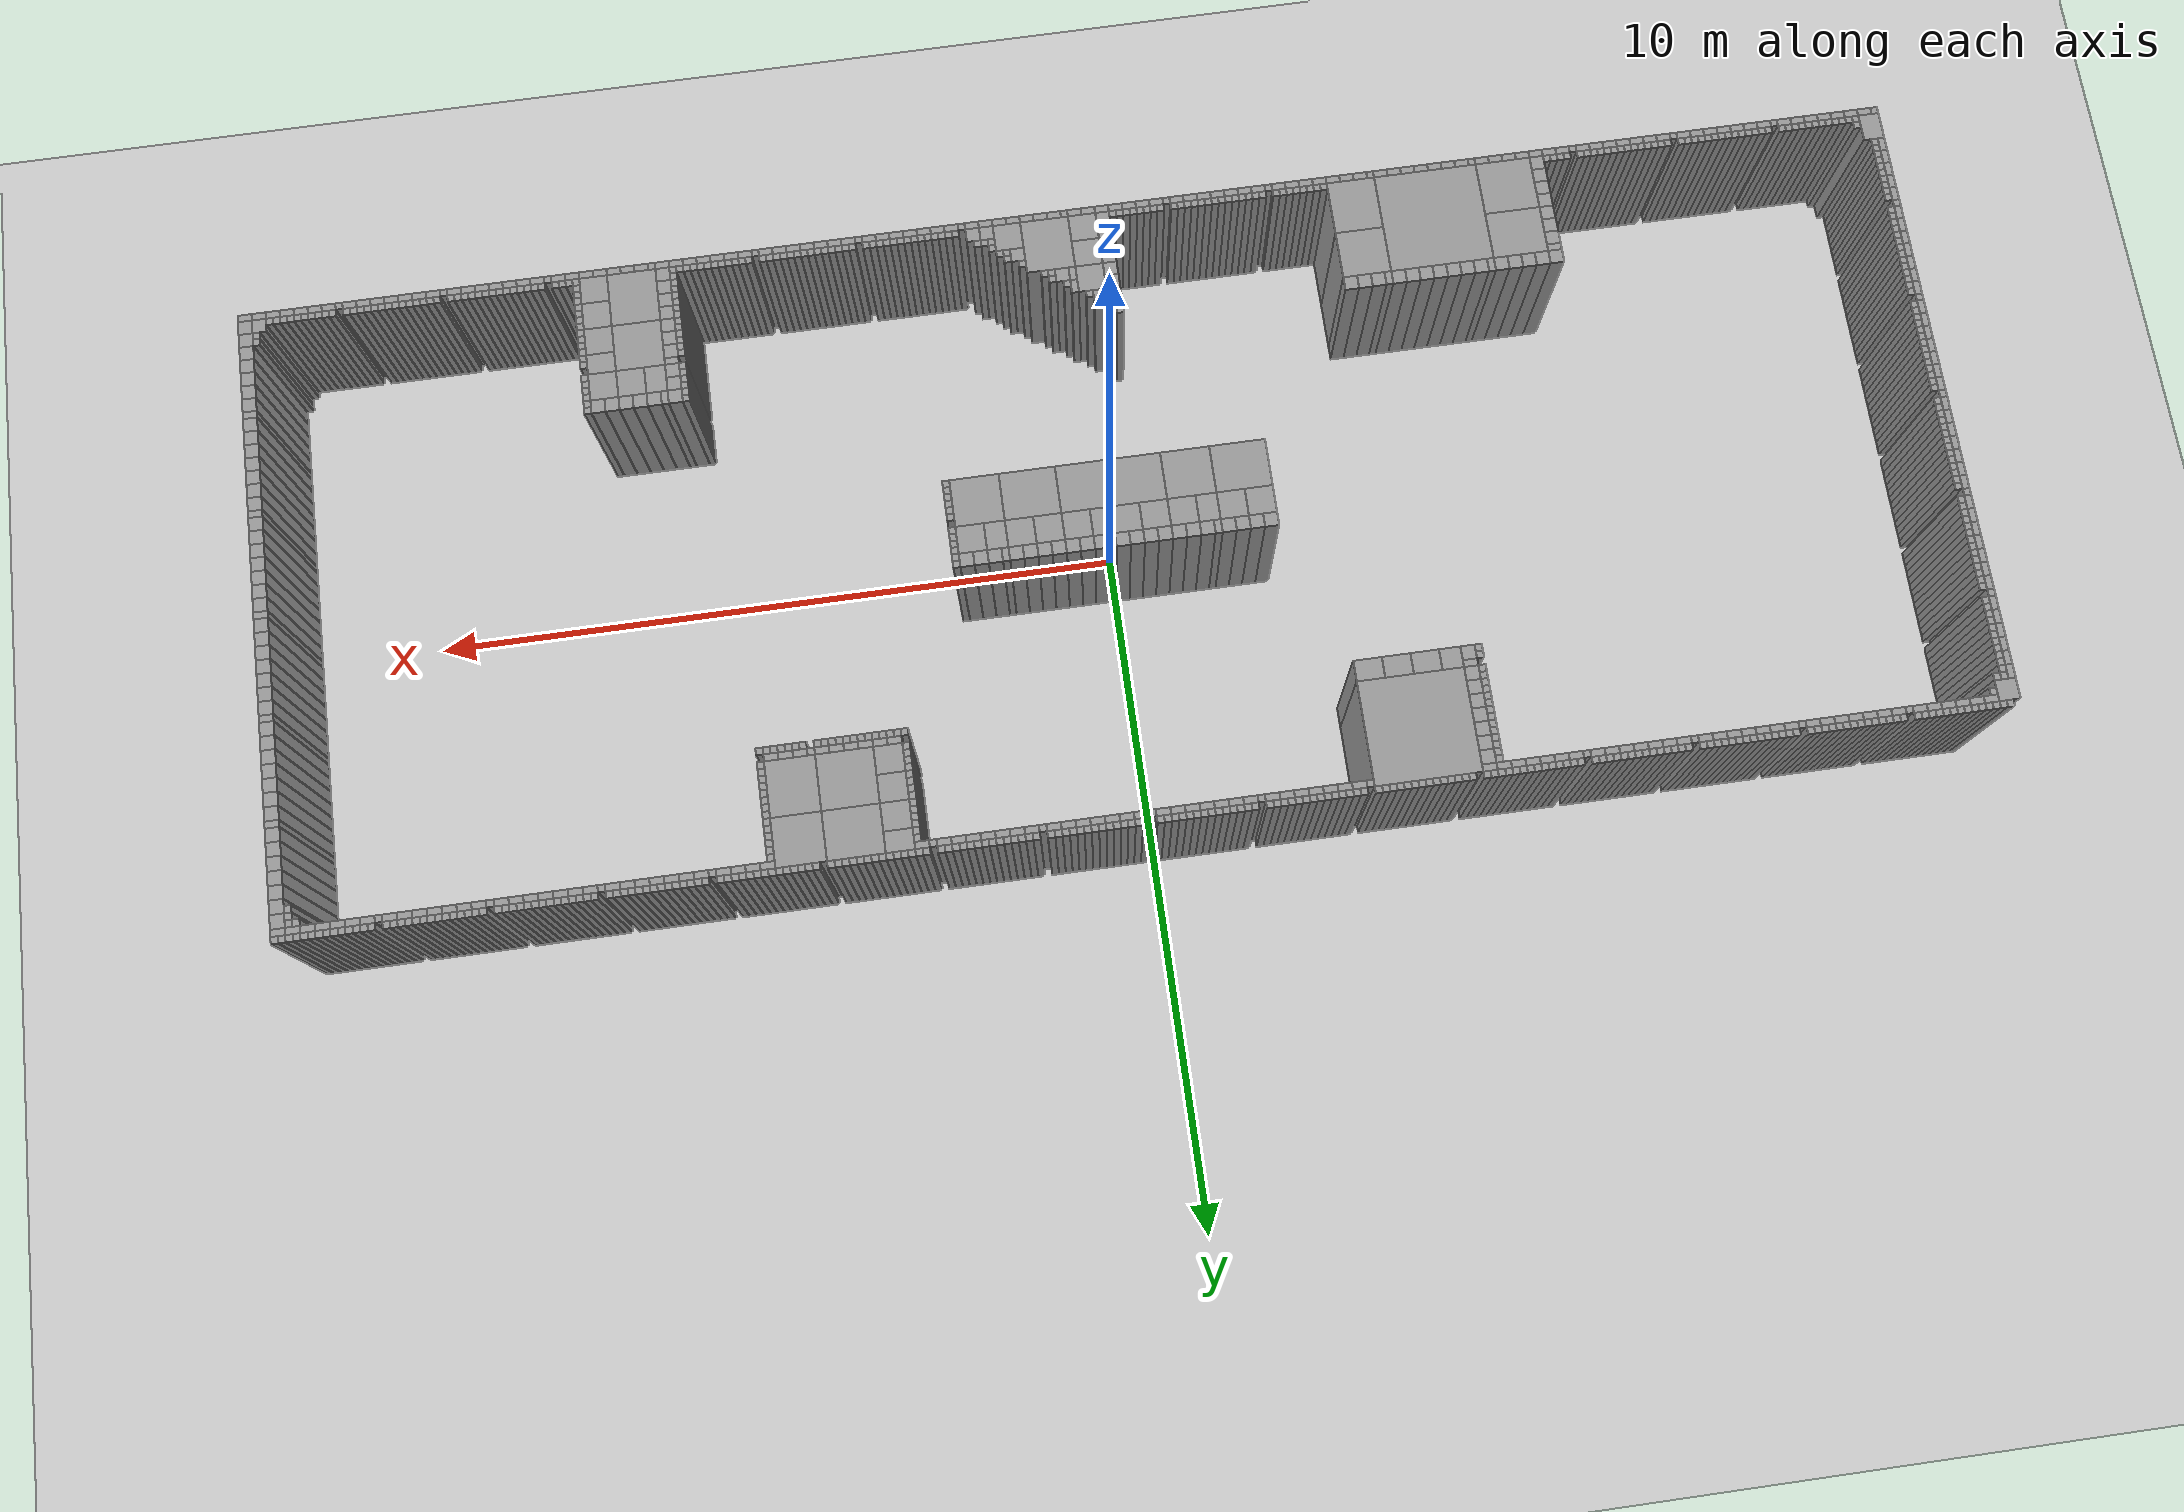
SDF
<sdf version="1.6">
  <world name="default">
    <include>
      <uri>model://sun</uri>
    </include>
    <include>
      <uri>model://ground_plane</uri>
    </include>
    <model name="stage_test">
      <static>1</static>
      <pose frame="">-12 -12 0 0 0 0</pose>
      <link name="Wall_1">
        <pose frame="">0.15 16.55 0 0 0 0</pose>
        <collision name="Wall_1_collision">
          <pose frame="">0 0 1.25 0 0 0</pose>
          <geometry>
            <box>
              <size>0.1 0.10000000000000142 2.5</size>
            </box>
          </geometry>
        </collision>
        <visual name="Wall_1_visual">
          <pose frame="">0 0 1.25 0 0 0</pose>
          <geometry>
            <box>
              <size>0.1 0.10000000000000142 2.5</size>
            </box>
          </geometry>
          <material>
            <script>
              <uri>file://media/materials/scripts/gazebo.material</uri>
              <name>Gazebo/Grey</name>
            </script>
            <ambient>1 1 1 1</ambient>
          </material>
        </visual>
        <self_collide>0</self_collide>
        <enable_wind>0</enable_wind>
        <kinematic>0</kinematic>
      </link>
      <link name="Wall_2">
        <pose frame="">0.25 16.55 0 0 0 0</pose>
        <collision name="Wall_2_collision">
          <pose frame="">0 0 1.25 0 0 0</pose>
          <geometry>
            <box>
              <size>0.10000000000000003 0.10000000000000142 2.5</size>
            </box>
          </geometry>
        </collision>
        <visual name="Wall_2_visual">
          <pose frame="">0 0 1.25 0 0 0</pose>
          <geometry>
            <box>
              <size>0.10000000000000003 0.10000000000000142 2.5</size>
            </box>
          </geometry>
          <material>
            <script>
              <uri>file://media/materials/scripts/gazebo.material</uri>
              <name>Gazebo/Grey</name>
            </script>
            <ambient>1 1 1 1</ambient>
          </material>
        </visual>
        <self_collide>0</self_collide>
        <enable_wind>0</enable_wind>
        <kinematic>0</kinematic>
      </link>
      <link name="Wall_3">
        <pose frame="">0.35000000000000003 16.55 0 0 0 0</pose>
        <collision name="Wall_3_collision">
          <pose frame="">0 0 1.25 0 0 0</pose>
          <geometry>
            <box>
              <size>0.09999999999999998 0.10000000000000142 2.5</size>
            </box>
          </geometry>
        </collision>
        <visual name="Wall_3_visual">
          <pose frame="">0 0 1.25 0 0 0</pose>
          <geometry>
            <box>
              <size>0.09999999999999998 0.10000000000000142 2.5</size>
            </box>
          </geometry>
          <material>
            <script>
              <uri>file://media/materials/scripts/gazebo.material</uri>
              <name>Gazebo/Grey</name>
            </script>
            <ambient>1 1 1 1</ambient>
          </material>
        </visual>
        <self_collide>0</self_collide>
        <enable_wind>0</enable_wind>
        <kinematic>0</kinematic>
      </link>
      <link name="Wall_4">
        <pose frame="">0.44999999999999996 16.55 0 0 0 0</pose>
        <collision name="Wall_4_collision">
          <pose frame="">0 0 1.25 0 0 0</pose>
          <geometry>
            <box>
              <size>0.09999999999999998 0.10000000000000142 2.5</size>
            </box>
          </geometry>
        </collision>
        <visual name="Wall_4_visual">
          <pose frame="">0 0 1.25 0 0 0</pose>
          <geometry>
            <box>
              <size>0.09999999999999998 0.10000000000000142 2.5</size>
            </box>
          </geometry>
          <material>
            <script>
              <uri>file://media/materials/scripts/gazebo.material</uri>
              <name>Gazebo/Grey</name>
            </script>
            <ambient>1 1 1 1</ambient>
          </material>
        </visual>
        <self_collide>0</self_collide>
        <enable_wind>0</enable_wind>
        <kinematic>0</kinematic>
      </link>
      <link name="Wall_5">
        <pose frame="">0.55 16.55 0 0 0 0</pose>
        <collision name="Wall_5_collision">
          <pose frame="">0 0 1.25 0 0 0</pose>
          <geometry>
            <box>
              <size>0.10000000000000009 0.10000000000000142 2.5</size>
            </box>
          </geometry>
        </collision>
        <visual name="Wall_5_visual">
          <pose frame="">0 0 1.25 0 0 0</pose>
          <geometry>
            <box>
              <size>0.10000000000000009 0.10000000000000142 2.5</size>
            </box>
          </geometry>
          <material>
            <script>
              <uri>file://media/materials/scripts/gazebo.material</uri>
              <name>Gazebo/Grey</name>
            </script>
            <ambient>1 1 1 1</ambient>
          </material>
        </visual>
        <self_collide>0</self_collide>
        <enable_wind>0</enable_wind>
        <kinematic>0</kinematic>
      </link>
      <link name="Wall_6">
        <pose frame="">0.6500000000000001 16.55 0 0 0 0</pose>
        <collision name="Wall_6_collision">
          <pose frame="">0 0 1.25 0 0 0</pose>
          <geometry>
            <box>
              <size>0.09999999999999998 0.10000000000000142 2.5</size>
            </box>
          </geometry>
        </collision>
        <visual name="Wall_6_visual">
          <pose frame="">0 0 1.25 0 0 0</pose>
          <geometry>
            <box>
              <size>0.09999999999999998 0.10000000000000142 2.5</size>
            </box>
          </geometry>
          <material>
            <script>
              <uri>file://media/materials/scripts/gazebo.material</uri>
              <name>Gazebo/Grey</name>
            </script>
            <ambient>1 1 1 1</ambient>
          </material>
        </visual>
        <self_collide>0</self_collide>
        <enable_wind>0</enable_wind>
        <kinematic>0</kinematic>
      </link>
      <link name="Wall_7">
        <pose frame="">0.75 16.55 0 0 0 0</pose>
        <collision name="Wall_7_collision">
          <pose frame="">0 0 1.25 0 0 0</pose>
          <geometry>
            <box>
              <size>0.09999999999999998 0.10000000000000142 2.5</size>
            </box>
          </geometry>
        </collision>
        <visual name="Wall_7_visual">
          <pose frame="">0 0 1.25 0 0 0</pose>
          <geometry>
            <box>
              <size>0.09999999999999998 0.10000000000000142 2.5</size>
            </box>
          </geometry>
          <material>
            <script>
              <uri>file://media/materials/scripts/gazebo.material</uri>
              <name>Gazebo/Grey</name>
            </script>
            <ambient>1 1 1 1</ambient>
          </material>
        </visual>
        <self_collide>0</self_collide>
        <enable_wind>0</enable_wind>
        <kinematic>0</kinematic>
      </link>
      <link name="Wall_8">
        <pose frame="">0.8500000000000001 16.55 0 0 0 0</pose>
        <collision name="Wall_8_collision">
          <pose frame="">0 0 1.25 0 0 0</pose>
          <geometry>
            <box>
              <size>0.09999999999999998 0.10000000000000142 2.5</size>
            </box>
          </geometry>
        </collision>
        <visual name="Wall_8_visual">
          <pose frame="">0 0 1.25 0 0 0</pose>
          <geometry>
            <box>
              <size>0.09999999999999998 0.10000000000000142 2.5</size>
            </box>
          </geometry>
          <material>
            <script>
              <uri>file://media/materials/scripts/gazebo.material</uri>
              <name>Gazebo/Grey</name>
            </script>
            <ambient>1 1 1 1</ambient>
          </material>
        </visual>
        <self_collide>0</self_collide>
        <enable_wind>0</enable_wind>
        <kinematic>0</kinematic>
      </link>
      <link name="Wall_9">
        <pose frame="">0.95 16.55 0 0 0 0</pose>
        <collision name="Wall_9_collision">
          <pose frame="">0 0 1.25 0 0 0</pose>
          <geometry>
            <box>
              <size>0.09999999999999998 0.10000000000000142 2.5</size>
            </box>
          </geometry>
        </collision>
        <visual name="Wall_9_visual">
          <pose frame="">0 0 1.25 0 0 0</pose>
          <geometry>
            <box>
              <size>0.09999999999999998 0.10000000000000142 2.5</size>
            </box>
          </geometry>
          <material>
            <script>
              <uri>file://media/materials/scripts/gazebo.material</uri>
              <name>Gazebo/Grey</name>
            </script>
            <ambient>1 1 1 1</ambient>
          </material>
        </visual>
        <self_collide>0</self_collide>
        <enable_wind>0</enable_wind>
        <kinematic>0</kinematic>
      </link>
      <link name="Wall_10">
        <pose frame="">1.05 16.55 0 0 0 0</pose>
        <collision name="Wall_10_collision">
          <pose frame="">0 0 1.25 0 0 0</pose>
          <geometry>
            <box>
              <size>0.10000000000000009 0.10000000000000142 2.5</size>
            </box>
          </geometry>
        </collision>
        <visual name="Wall_10_visual">
          <pose frame="">0 0 1.25 0 0 0</pose>
          <geometry>
            <box>
              <size>0.10000000000000009 0.10000000000000142 2.5</size>
            </box>
          </geometry>
          <material>
            <script>
              <uri>file://media/materials/scripts/gazebo.material</uri>
              <name>Gazebo/Grey</name>
            </script>
            <ambient>1 1 1 1</ambient>
          </material>
        </visual>
        <self_collide>0</self_collide>
        <enable_wind>0</enable_wind>
        <kinematic>0</kinematic>
      </link>
      <link name="Wall_11">
        <pose frame="">1.1500000000000001 16.55 0 0 0 0</pose>
        <collision name="Wall_11_collision">
          <pose frame="">0 0 1.25 0 0 0</pose>
          <geometry>
            <box>
              <size>0.10000000000000009 0.10000000000000142 2.5</size>
            </box>
          </geometry>
        </collision>
        <visual name="Wall_11_visual">
          <pose frame="">0 0 1.25 0 0 0</pose>
          <geometry>
            <box>
              <size>0.10000000000000009 0.10000000000000142 2.5</size>
            </box>
          </geometry>
          <material>
            <script>
              <uri>file://media/materials/scripts/gazebo.material</uri>
              <name>Gazebo/Grey</name>
            </script>
            <ambient>1 1 1 1</ambient>
          </material>
        </visual>
        <self_collide>0</self_collide>
        <enable_wind>0</enable_wind>
        <kinematic>0</kinematic>
      </link>
      <link name="Wall_12">
        <pose frame="">1.25 16.55 0 0 0 0</pose>
        <collision name="Wall_12_collision">
          <pose frame="">0 0 1.25 0 0 0</pose>
          <geometry>
            <box>
              <size>0.09999999999999987 0.10000000000000142 2.5</size>
            </box>
          </geometry>
        </collision>
        <visual name="Wall_12_visual">
          <pose frame="">0 0 1.25 0 0 0</pose>
          <geometry>
            <box>
              <size>0.09999999999999987 0.10000000000000142 2.5</size>
            </box>
          </geometry>
          <material>
            <script>
              <uri>file://media/materials/scripts/gazebo.material</uri>
              <name>Gazebo/Grey</name>
            </script>
            <ambient>1 1 1 1</ambient>
          </material>
        </visual>
        <self_collide>0</self_collide>
        <enable_wind>0</enable_wind>
        <kinematic>0</kinematic>
      </link>
      <link name="Wall_13">
        <pose frame="">1.35 16.55 0 0 0 0</pose>
        <collision name="Wall_13_collision">
          <pose frame="">0 0 1.25 0 0 0</pose>
          <geometry>
            <box>
              <size>0.10000000000000009 0.10000000000000142 2.5</size>
            </box>
          </geometry>
        </collision>
        <visual name="Wall_13_visual">
          <pose frame="">0 0 1.25 0 0 0</pose>
          <geometry>
            <box>
              <size>0.10000000000000009 0.10000000000000142 2.5</size>
            </box>
          </geometry>
          <material>
            <script>
              <uri>file://media/materials/scripts/gazebo.material</uri>
              <name>Gazebo/Grey</name>
            </script>
            <ambient>1 1 1 1</ambient>
          </material>
        </visual>
        <self_collide>0</self_collide>
        <enable_wind>0</enable_wind>
        <kinematic>0</kinematic>
      </link>
      <link name="Wall_14">
        <pose frame="">1.4500000000000002 16.55 0 0 0 0</pose>
        <collision name="Wall_14_collision">
          <pose frame="">0 0 1.25 0 0 0</pose>
          <geometry>
            <box>
              <size>0.09999999999999987 0.10000000000000142 2.5</size>
            </box>
          </geometry>
        </collision>
        <visual name="Wall_14_visual">
          <pose frame="">0 0 1.25 0 0 0</pose>
          <geometry>
            <box>
              <size>0.09999999999999987 0.10000000000000142 2.5</size>
            </box>
          </geometry>
          <material>
            <script>
              <uri>file://media/materials/scripts/gazebo.material</uri>
              <name>Gazebo/Grey</name>
            </script>
            <ambient>1 1 1 1</ambient>
          </material>
        </visual>
        <self_collide>0</self_collide>
        <enable_wind>0</enable_wind>
        <kinematic>0</kinematic>
      </link>
      <link name="Wall_15">
        <pose frame="">0.15000000000000002 16.35 0 0 0 0</pose>
        <collision name="Wall_15_collision">
          <pose frame="">0 0 1.25 0 0 0</pose>
          <geometry>
            <box>
              <size>0.30000000000000004 0.3000000000000007 2.5</size>
            </box>
          </geometry>
        </collision>
        <visual name="Wall_15_visual">
          <pose frame="">0 0 1.25 0 0 0</pose>
          <geometry>
            <box>
              <size>0.30000000000000004 0.3000000000000007 2.5</size>
            </box>
          </geometry>
          <material>
            <script>
              <uri>file://media/materials/scripts/gazebo.material</uri>
              <name>Gazebo/Grey</name>
            </script>
            <ambient>1 1 1 1</ambient>
          </material>
        </visual>
        <self_collide>0</self_collide>
        <enable_wind>0</enable_wind>
        <kinematic>0</kinematic>
      </link>
      <link name="Wall_16">
        <pose frame="">0.05 16.1 0 0 0 0</pose>
        <collision name="Wall_16_collision">
          <pose frame="">0 0 1.25 0 0 0</pose>
          <geometry>
            <box>
              <size>0.1 0.1999999999999993 2.5</size>
            </box>
          </geometry>
        </collision>
        <visual name="Wall_16_visual">
          <pose frame="">0 0 1.25 0 0 0</pose>
          <geometry>
            <box>
              <size>0.1 0.1999999999999993 2.5</size>
            </box>
          </geometry>
          <material>
            <script>
              <uri>file://media/materials/scripts/gazebo.material</uri>
              <name>Gazebo/Grey</name>
            </script>
            <ambient>1 1 1 1</ambient>
          </material>
        </visual>
        <self_collide>0</self_collide>
        <enable_wind>0</enable_wind>
        <kinematic>0</kinematic>
      </link>
      <link name="Wall_17">
        <pose frame="">0.05 15.9 0 0 0 0</pose>
        <collision name="Wall_17_collision">
          <pose frame="">0 0 1.25 0 0 0</pose>
          <geometry>
            <box>
              <size>0.1 0.1999999999999993 2.5</size>
            </box>
          </geometry>
        </collision>
        <visual name="Wall_17_visual">
          <pose frame="">0 0 1.25 0 0 0</pose>
          <geometry>
            <box>
              <size>0.1 0.1999999999999993 2.5</size>
            </box>
          </geometry>
          <material>
            <script>
              <uri>file://media/materials/scripts/gazebo.material</uri>
              <name>Gazebo/Grey</name>
            </script>
            <ambient>1 1 1 1</ambient>
          </material>
        </visual>
        <self_collide>0</self_collide>
        <enable_wind>0</enable_wind>
        <kinematic>0</kinematic>
      </link>
      <link name="Wall_18">
        <pose frame="">0.15 16.150000000000002 0 0 0 0</pose>
        <collision name="Wall_18_collision">
          <pose frame="">0 0 1.25 0 0 0</pose>
          <geometry>
            <box>
              <size>0.1 0.09999999999999787 2.5</size>
            </box>
          </geometry>
        </collision>
        <visual name="Wall_18_visual">
          <pose frame="">0 0 1.25 0 0 0</pose>
          <geometry>
            <box>
              <size>0.1 0.09999999999999787 2.5</size>
            </box>
          </geometry>
          <material>
            <script>
              <uri>file://media/materials/scripts/gazebo.material</uri>
              <name>Gazebo/Grey</name>
            </script>
            <ambient>1 1 1 1</ambient>
          </material>
        </visual>
        <self_collide>0</self_collide>
        <enable_wind>0</enable_wind>
        <kinematic>0</kinematic>
      </link>
      <link name="Wall_19">
        <pose frame="">0.15 16.05 0 0 0 0</pose>
        <collision name="Wall_19_collision">
          <pose frame="">0 0 1.25 0 0 0</pose>
          <geometry>
            <box>
              <size>0.1 0.10000000000000142 2.5</size>
            </box>
          </geometry>
        </collision>
        <visual name="Wall_19_visual">
          <pose frame="">0 0 1.25 0 0 0</pose>
          <geometry>
            <box>
              <size>0.1 0.10000000000000142 2.5</size>
            </box>
          </geometry>
          <material>
            <script>
              <uri>file://media/materials/scripts/gazebo.material</uri>
              <name>Gazebo/Grey</name>
            </script>
            <ambient>1 1 1 1</ambient>
          </material>
        </visual>
        <self_collide>0</self_collide>
        <enable_wind>0</enable_wind>
        <kinematic>0</kinematic>
      </link>
      <link name="Wall_20">
        <pose frame="">0.25 16.150000000000002 0 0 0 0</pose>
        <collision name="Wall_20_collision">
          <pose frame="">0 0 1.25 0 0 0</pose>
          <geometry>
            <box>
              <size>0.10000000000000003 0.09999999999999787 2.5</size>
            </box>
          </geometry>
        </collision>
        <visual name="Wall_20_visual">
          <pose frame="">0 0 1.25 0 0 0</pose>
          <geometry>
            <box>
              <size>0.10000000000000003 0.09999999999999787 2.5</size>
            </box>
          </geometry>
          <material>
            <script>
              <uri>file://media/materials/scripts/gazebo.material</uri>
              <name>Gazebo/Grey</name>
            </script>
            <ambient>1 1 1 1</ambient>
          </material>
        </visual>
        <self_collide>0</self_collide>
        <enable_wind>0</enable_wind>
        <kinematic>0</kinematic>
      </link>
      <link name="Wall_21">
        <pose frame="">0.15 15.95 0 0 0 0</pose>
        <collision name="Wall_21_collision">
          <pose frame="">0 0 1.25 0 0 0</pose>
          <geometry>
            <box>
              <size>0.1 0.09999999999999964 2.5</size>
            </box>
          </geometry>
        </collision>
        <visual name="Wall_21_visual">
          <pose frame="">0 0 1.25 0 0 0</pose>
          <geometry>
            <box>
              <size>0.1 0.09999999999999964 2.5</size>
            </box>
          </geometry>
          <material>
            <script>
              <uri>file://media/materials/scripts/gazebo.material</uri>
              <name>Gazebo/Grey</name>
            </script>
            <ambient>1 1 1 1</ambient>
          </material>
        </visual>
        <self_collide>0</self_collide>
        <enable_wind>0</enable_wind>
        <kinematic>0</kinematic>
      </link>
      <link name="Wall_22">
        <pose frame="">0.15 15.85 0 0 0 0</pose>
        <collision name="Wall_22_collision">
          <pose frame="">0 0 1.25 0 0 0</pose>
          <geometry>
            <box>
              <size>0.1 0.09999999999999964 2.5</size>
            </box>
          </geometry>
        </collision>
        <visual name="Wall_22_visual">
          <pose frame="">0 0 1.25 0 0 0</pose>
          <geometry>
            <box>
              <size>0.1 0.09999999999999964 2.5</size>
            </box>
          </geometry>
          <material>
            <script>
              <uri>file://media/materials/scripts/gazebo.material</uri>
              <name>Gazebo/Grey</name>
            </script>
            <ambient>1 1 1 1</ambient>
          </material>
        </visual>
        <self_collide>0</self_collide>
        <enable_wind>0</enable_wind>
        <kinematic>0</kinematic>
      </link>
      <link name="Wall_23">
        <pose frame="">0.4 16.450000000000003 0 0 0 0</pose>
        <collision name="Wall_23_collision">
          <pose frame="">0 0 1.25 0 0 0</pose>
          <geometry>
            <box>
              <size>0.19999999999999996 0.09999999999999787 2.5</size>
            </box>
          </geometry>
        </collision>
        <visual name="Wall_23_visual">
          <pose frame="">0 0 1.25 0 0 0</pose>
          <geometry>
            <box>
              <size>0.19999999999999996 0.09999999999999787 2.5</size>
            </box>
          </geometry>
          <material>
            <script>
              <uri>file://media/materials/scripts/gazebo.material</uri>
              <name>Gazebo/Grey</name>
            </script>
            <ambient>1 1 1 1</ambient>
          </material>
        </visual>
        <self_collide>0</self_collide>
        <enable_wind>0</enable_wind>
        <kinematic>0</kinematic>
      </link>
      <link name="Wall_24">
        <pose frame="">0.35000000000000003 16.35 0 0 0 0</pose>
        <collision name="Wall_24_collision">
          <pose frame="">0 0 1.25 0 0 0</pose>
          <geometry>
            <box>
              <size>0.09999999999999998 0.10000000000000142 2.5</size>
            </box>
          </geometry>
        </collision>
        <visual name="Wall_24_visual">
          <pose frame="">0 0 1.25 0 0 0</pose>
          <geometry>
            <box>
              <size>0.09999999999999998 0.10000000000000142 2.5</size>
            </box>
          </geometry>
          <material>
            <script>
              <uri>file://media/materials/scripts/gazebo.material</uri>
              <name>Gazebo/Grey</name>
            </script>
            <ambient>1 1 1 1</ambient>
          </material>
        </visual>
        <self_collide>0</self_collide>
        <enable_wind>0</enable_wind>
        <kinematic>0</kinematic>
      </link>
      <link name="Wall_25">
        <pose frame="">0.6000000000000001 16.450000000000003 0 0 0 0</pose>
        <collision name="Wall_25_collision">
          <pose frame="">0 0 1.25 0 0 0</pose>
          <geometry>
            <box>
              <size>0.20000000000000007 0.09999999999999787 2.5</size>
            </box>
          </geometry>
        </collision>
        <visual name="Wall_25_visual">
          <pose frame="">0 0 1.25 0 0 0</pose>
          <geometry>
            <box>
              <size>0.20000000000000007 0.09999999999999787 2.5</size>
            </box>
          </geometry>
          <material>
            <script>
              <uri>file://media/materials/scripts/gazebo.material</uri>
              <name>Gazebo/Grey</name>
            </script>
            <ambient>1 1 1 1</ambient>
          </material>
        </visual>
        <self_collide>0</self_collide>
        <enable_wind>0</enable_wind>
        <kinematic>0</kinematic>
      </link>
      <link name="Wall_26">
        <pose frame="">0.05 15.7 0 0 0 0</pose>
        <collision name="Wall_26_collision">
          <pose frame="">0 0 1.25 0 0 0</pose>
          <geometry>
            <box>
              <size>0.1 0.1999999999999993 2.5</size>
            </box>
          </geometry>
        </collision>
        <visual name="Wall_26_visual">
          <pose frame="">0 0 1.25 0 0 0</pose>
          <geometry>
            <box>
              <size>0.1 0.1999999999999993 2.5</size>
            </box>
          </geometry>
          <material>
            <script>
              <uri>file://media/materials/scripts/gazebo.material</uri>
              <name>Gazebo/Grey</name>
            </script>
            <ambient>1 1 1 1</ambient>
          </material>
        </visual>
        <self_collide>0</self_collide>
        <enable_wind>0</enable_wind>
        <kinematic>0</kinematic>
      </link>
      <link name="Wall_27">
        <pose frame="">0.05 15.500000000000002 0 0 0 0</pose>
        <collision name="Wall_27_collision">
          <pose frame="">0 0 1.25 0 0 0</pose>
          <geometry>
            <box>
              <size>0.1 0.20000000000000107 2.5</size>
            </box>
          </geometry>
        </collision>
        <visual name="Wall_27_visual">
          <pose frame="">0 0 1.25 0 0 0</pose>
          <geometry>
            <box>
              <size>0.1 0.20000000000000107 2.5</size>
            </box>
          </geometry>
          <material>
            <script>
              <uri>file://media/materials/scripts/gazebo.material</uri>
              <name>Gazebo/Grey</name>
            </script>
            <ambient>1 1 1 1</ambient>
          </material>
        </visual>
        <self_collide>0</self_collide>
        <enable_wind>0</enable_wind>
        <kinematic>0</kinematic>
      </link>
      <link name="Wall_28">
        <pose frame="">0.15 15.75 0 0 0 0</pose>
        <collision name="Wall_28_collision">
          <pose frame="">0 0 1.25 0 0 0</pose>
          <geometry>
            <box>
              <size>0.1 0.09999999999999964 2.5</size>
            </box>
          </geometry>
        </collision>
        <visual name="Wall_28_visual">
          <pose frame="">0 0 1.25 0 0 0</pose>
          <geometry>
            <box>
              <size>0.1 0.09999999999999964 2.5</size>
            </box>
          </geometry>
          <material>
            <script>
              <uri>file://media/materials/scripts/gazebo.material</uri>
              <name>Gazebo/Grey</name>
            </script>
            <ambient>1 1 1 1</ambient>
          </material>
        </visual>
        <self_collide>0</self_collide>
        <enable_wind>0</enable_wind>
        <kinematic>0</kinematic>
      </link>
      <link name="Wall_29">
        <pose frame="">0.15 15.650000000000002 0 0 0 0</pose>
        <collision name="Wall_29_collision">
          <pose frame="">0 0 1.25 0 0 0</pose>
          <geometry>
            <box>
              <size>0.1 0.09999999999999964 2.5</size>
            </box>
          </geometry>
        </collision>
        <visual name="Wall_29_visual">
          <pose frame="">0 0 1.25 0 0 0</pose>
          <geometry>
            <box>
              <size>0.1 0.09999999999999964 2.5</size>
            </box>
          </geometry>
          <material>
            <script>
              <uri>file://media/materials/scripts/gazebo.material</uri>
              <name>Gazebo/Grey</name>
            </script>
            <ambient>1 1 1 1</ambient>
          </material>
        </visual>
        <self_collide>0</self_collide>
        <enable_wind>0</enable_wind>
        <kinematic>0</kinematic>
      </link>
      <link name="Wall_30">
        <pose frame="">0.15 15.55 0 0 0 0</pose>
        <collision name="Wall_30_collision">
          <pose frame="">0 0 1.25 0 0 0</pose>
          <geometry>
            <box>
              <size>0.1 0.10000000000000142 2.5</size>
            </box>
          </geometry>
        </collision>
        <visual name="Wall_30_visual">
          <pose frame="">0 0 1.25 0 0 0</pose>
          <geometry>
            <box>
              <size>0.1 0.10000000000000142 2.5</size>
            </box>
          </geometry>
          <material>
            <script>
              <uri>file://media/materials/scripts/gazebo.material</uri>
              <name>Gazebo/Grey</name>
            </script>
            <ambient>1 1 1 1</ambient>
          </material>
        </visual>
        <self_collide>0</self_collide>
        <enable_wind>0</enable_wind>
        <kinematic>0</kinematic>
      </link>
      <link name="Wall_31">
        <pose frame="">0.15 15.45 0 0 0 0</pose>
        <collision name="Wall_31_collision">
          <pose frame="">0 0 1.25 0 0 0</pose>
          <geometry>
            <box>
              <size>0.1 0.09999999999999964 2.5</size>
            </box>
          </geometry>
        </collision>
        <visual name="Wall_31_visual">
          <pose frame="">0 0 1.25 0 0 0</pose>
          <geometry>
            <box>
              <size>0.1 0.09999999999999964 2.5</size>
            </box>
          </geometry>
          <material>
            <script>
              <uri>file://media/materials/scripts/gazebo.material</uri>
              <name>Gazebo/Grey</name>
            </script>
            <ambient>1 1 1 1</ambient>
          </material>
        </visual>
        <self_collide>0</self_collide>
        <enable_wind>0</enable_wind>
        <kinematic>0</kinematic>
      </link>
      <link name="Wall_32">
        <pose frame="">0.05 15.3 0 0 0 0</pose>
        <collision name="Wall_32_collision">
          <pose frame="">0 0 1.25 0 0 0</pose>
          <geometry>
            <box>
              <size>0.1 0.1999999999999993 2.5</size>
            </box>
          </geometry>
        </collision>
        <visual name="Wall_32_visual">
          <pose frame="">0 0 1.25 0 0 0</pose>
          <geometry>
            <box>
              <size>0.1 0.1999999999999993 2.5</size>
            </box>
          </geometry>
          <material>
            <script>
              <uri>file://media/materials/scripts/gazebo.material</uri>
              <name>Gazebo/Grey</name>
            </script>
            <ambient>1 1 1 1</ambient>
          </material>
        </visual>
        <self_collide>0</self_collide>
        <enable_wind>0</enable_wind>
        <kinematic>0</kinematic>
      </link>
      <link name="Wall_33">
        <pose frame="">0.05 15.100000000000001 0 0 0 0</pose>
        <collision name="Wall_33_collision">
          <pose frame="">0 0 1.25 0 0 0</pose>
          <geometry>
            <box>
              <size>0.1 0.20000000000000107 2.5</size>
            </box>
          </geometry>
        </collision>
        <visual name="Wall_33_visual">
          <pose frame="">0 0 1.25 0 0 0</pose>
          <geometry>
            <box>
              <size>0.1 0.20000000000000107 2.5</size>
            </box>
          </geometry>
          <material>
            <script>
              <uri>file://media/materials/scripts/gazebo.material</uri>
              <name>Gazebo/Grey</name>
            </script>
            <ambient>1 1 1 1</ambient>
          </material>
        </visual>
        <self_collide>0</self_collide>
        <enable_wind>0</enable_wind>
        <kinematic>0</kinematic>
      </link>
      <link name="Wall_34">
        <pose frame="">0.15 15.35 0 0 0 0</pose>
        <collision name="Wall_34_collision">
          <pose frame="">0 0 1.25 0 0 0</pose>
          <geometry>
            <box>
              <size>0.1 0.09999999999999964 2.5</size>
            </box>
          </geometry>
        </collision>
        <visual name="Wall_34_visual">
          <pose frame="">0 0 1.25 0 0 0</pose>
          <geometry>
            <box>
              <size>0.1 0.09999999999999964 2.5</size>
            </box>
          </geometry>
          <material>
            <script>
              <uri>file://media/materials/scripts/gazebo.material</uri>
              <name>Gazebo/Grey</name>
            </script>
            <ambient>1 1 1 1</ambient>
          </material>
        </visual>
        <self_collide>0</self_collide>
        <enable_wind>0</enable_wind>
        <kinematic>0</kinematic>
      </link>
      <link name="Wall_35">
        <pose frame="">0.15 15.25 0 0 0 0</pose>
        <collision name="Wall_35_collision">
          <pose frame="">0 0 1.25 0 0 0</pose>
          <geometry>
            <box>
              <size>0.1 0.09999999999999964 2.5</size>
            </box>
          </geometry>
        </collision>
        <visual name="Wall_35_visual">
          <pose frame="">0 0 1.25 0 0 0</pose>
          <geometry>
            <box>
              <size>0.1 0.09999999999999964 2.5</size>
            </box>
          </geometry>
          <material>
            <script>
              <uri>file://media/materials/scripts/gazebo.material</uri>
              <name>Gazebo/Grey</name>
            </script>
            <ambient>1 1 1 1</ambient>
          </material>
        </visual>
        <self_collide>0</self_collide>
        <enable_wind>0</enable_wind>
        <kinematic>0</kinematic>
      </link>
      <link name="Wall_36">
        <pose frame="">0.15 15.150000000000002 0 0 0 0</pose>
        <collision name="Wall_36_collision">
          <pose frame="">0 0 1.25 0 0 0</pose>
          <geometry>
            <box>
              <size>0.1 0.09999999999999964 2.5</size>
            </box>
          </geometry>
        </collision>
        <visual name="Wall_36_visual">
          <pose frame="">0 0 1.25 0 0 0</pose>
          <geometry>
            <box>
              <size>0.1 0.09999999999999964 2.5</size>
            </box>
          </geometry>
          <material>
            <script>
              <uri>file://media/materials/scripts/gazebo.material</uri>
              <name>Gazebo/Grey</name>
            </script>
            <ambient>1 1 1 1</ambient>
          </material>
        </visual>
        <self_collide>0</self_collide>
        <enable_wind>0</enable_wind>
        <kinematic>0</kinematic>
      </link>
      <link name="Wall_37">
        <pose frame="">0.15 15.05 0 0 0 0</pose>
        <collision name="Wall_37_collision">
          <pose frame="">0 0 1.25 0 0 0</pose>
          <geometry>
            <box>
              <size>0.1 0.10000000000000142 2.5</size>
            </box>
          </geometry>
        </collision>
        <visual name="Wall_37_visual">
          <pose frame="">0 0 1.25 0 0 0</pose>
          <geometry>
            <box>
              <size>0.1 0.10000000000000142 2.5</size>
            </box>
          </geometry>
          <material>
            <script>
              <uri>file://media/materials/scripts/gazebo.material</uri>
              <name>Gazebo/Grey</name>
            </script>
            <ambient>1 1 1 1</ambient>
          </material>
        </visual>
        <self_collide>0</self_collide>
        <enable_wind>0</enable_wind>
        <kinematic>0</kinematic>
      </link>
      <link name="Wall_38">
        <pose frame="">0.8 16.450000000000003 0 0 0 0</pose>
        <collision name="Wall_38_collision">
          <pose frame="">0 0 1.25 0 0 0</pose>
          <geometry>
            <box>
              <size>0.19999999999999996 0.09999999999999787 2.5</size>
            </box>
          </geometry>
        </collision>
        <visual name="Wall_38_visual">
          <pose frame="">0 0 1.25 0 0 0</pose>
          <geometry>
            <box>
              <size>0.19999999999999996 0.09999999999999787 2.5</size>
            </box>
          </geometry>
          <material>
            <script>
              <uri>file://media/materials/scripts/gazebo.material</uri>
              <name>Gazebo/Grey</name>
            </script>
            <ambient>1 1 1 1</ambient>
          </material>
        </visual>
        <self_collide>0</self_collide>
        <enable_wind>0</enable_wind>
        <kinematic>0</kinematic>
      </link>
      <link name="Wall_39">
        <pose frame="">1.0 16.450000000000003 0 0 0 0</pose>
        <collision name="Wall_39_collision">
          <pose frame="">0 0 1.25 0 0 0</pose>
          <geometry>
            <box>
              <size>0.20000000000000007 0.09999999999999787 2.5</size>
            </box>
          </geometry>
        </collision>
        <visual name="Wall_39_visual">
          <pose frame="">0 0 1.25 0 0 0</pose>
          <geometry>
            <box>
              <size>0.20000000000000007 0.09999999999999787 2.5</size>
            </box>
          </geometry>
          <material>
            <script>
              <uri>file://media/materials/scripts/gazebo.material</uri>
              <name>Gazebo/Grey</name>
            </script>
            <ambient>1 1 1 1</ambient>
          </material>
        </visual>
        <self_collide>0</self_collide>
        <enable_wind>0</enable_wind>
        <kinematic>0</kinematic>
      </link>
      <link name="Wall_40">
        <pose frame="">1.2000000000000002 16.450000000000003 0 0 0 0</pose>
        <collision name="Wall_40_collision">
          <pose frame="">0 0 1.25 0 0 0</pose>
          <geometry>
            <box>
              <size>0.19999999999999996 0.09999999999999787 2.5</size>
            </box>
          </geometry>
        </collision>
        <visual name="Wall_40_visual">
          <pose frame="">0 0 1.25 0 0 0</pose>
          <geometry>
            <box>
              <size>0.19999999999999996 0.09999999999999787 2.5</size>
            </box>
          </geometry>
          <material>
            <script>
              <uri>file://media/materials/scripts/gazebo.material</uri>
              <name>Gazebo/Grey</name>
            </script>
            <ambient>1 1 1 1</ambient>
          </material>
        </visual>
        <self_collide>0</self_collide>
        <enable_wind>0</enable_wind>
        <kinematic>0</kinematic>
      </link>
      <link name="Wall_41">
        <pose frame="">1.4 16.450000000000003 0 0 0 0</pose>
        <collision name="Wall_41_collision">
          <pose frame="">0 0 1.25 0 0 0</pose>
          <geometry>
            <box>
              <size>0.19999999999999996 0.09999999999999787 2.5</size>
            </box>
          </geometry>
        </collision>
        <visual name="Wall_41_visual">
          <pose frame="">0 0 1.25 0 0 0</pose>
          <geometry>
            <box>
              <size>0.19999999999999996 0.09999999999999787 2.5</size>
            </box>
          </geometry>
          <material>
            <script>
              <uri>file://media/materials/scripts/gazebo.material</uri>
              <name>Gazebo/Grey</name>
            </script>
            <ambient>1 1 1 1</ambient>
          </material>
        </visual>
        <self_collide>0</self_collide>
        <enable_wind>0</enable_wind>
        <kinematic>0</kinematic>
      </link>
      <link name="Wall_42">
        <pose frame="">1.65 16.55 0 0 0 0</pose>
        <collision name="Wall_42_collision">
          <pose frame="">0 0 1.25 0 0 0</pose>
          <geometry>
            <box>
              <size>0.10000000000000009 0.10000000000000142 2.5</size>
            </box>
          </geometry>
        </collision>
        <visual name="Wall_42_visual">
          <pose frame="">0 0 1.25 0 0 0</pose>
          <geometry>
            <box>
              <size>0.10000000000000009 0.10000000000000142 2.5</size>
            </box>
          </geometry>
          <material>
            <script>
              <uri>file://media/materials/scripts/gazebo.material</uri>
              <name>Gazebo/Grey</name>
            </script>
            <ambient>1 1 1 1</ambient>
          </material>
        </visual>
        <self_collide>0</self_collide>
        <enable_wind>0</enable_wind>
        <kinematic>0</kinematic>
      </link>
      <link name="Wall_43">
        <pose frame="">1.75 16.55 0 0 0 0</pose>
        <collision name="Wall_43_collision">
          <pose frame="">0 0 1.25 0 0 0</pose>
          <geometry>
            <box>
              <size>0.09999999999999987 0.10000000000000142 2.5</size>
            </box>
          </geometry>
        </collision>
        <visual name="Wall_43_visual">
          <pose frame="">0 0 1.25 0 0 0</pose>
          <geometry>
            <box>
              <size>0.09999999999999987 0.10000000000000142 2.5</size>
            </box>
          </geometry>
          <material>
            <script>
              <uri>file://media/materials/scripts/gazebo.material</uri>
              <name>Gazebo/Grey</name>
            </script>
            <ambient>1 1 1 1</ambient>
          </material>
        </visual>
        <self_collide>0</self_collide>
        <enable_wind>0</enable_wind>
        <kinematic>0</kinematic>
      </link>
      <link name="Wall_44">
        <pose frame="">1.85 16.55 0 0 0 0</pose>
        <collision name="Wall_44_collision">
          <pose frame="">0 0 1.25 0 0 0</pose>
          <geometry>
            <box>
              <size>0.10000000000000009 0.10000000000000142 2.5</size>
            </box>
          </geometry>
        </collision>
        <visual name="Wall_44_visual">
          <pose frame="">0 0 1.25 0 0 0</pose>
          <geometry>
            <box>
              <size>0.10000000000000009 0.10000000000000142 2.5</size>
            </box>
          </geometry>
          <material>
            <script>
              <uri>file://media/materials/scripts/gazebo.material</uri>
              <name>Gazebo/Grey</name>
            </script>
            <ambient>1 1 1 1</ambient>
          </material>
        </visual>
        <self_collide>0</self_collide>
        <enable_wind>0</enable_wind>
        <kinematic>0</kinematic>
      </link>
      <link name="Wall_45">
        <pose frame="">1.9500000000000002 16.55 0 0 0 0</pose>
        <collision name="Wall_45_collision">
          <pose frame="">0 0 1.25 0 0 0</pose>
          <geometry>
            <box>
              <size>0.09999999999999987 0.10000000000000142 2.5</size>
            </box>
          </geometry>
        </collision>
        <visual name="Wall_45_visual">
          <pose frame="">0 0 1.25 0 0 0</pose>
          <geometry>
            <box>
              <size>0.09999999999999987 0.10000000000000142 2.5</size>
            </box>
          </geometry>
          <material>
            <script>
              <uri>file://media/materials/scripts/gazebo.material</uri>
              <name>Gazebo/Grey</name>
            </script>
            <ambient>1 1 1 1</ambient>
          </material>
        </visual>
        <self_collide>0</self_collide>
        <enable_wind>0</enable_wind>
        <kinematic>0</kinematic>
      </link>
      <link name="Wall_46">
        <pose frame="">2.05 16.55 0 0 0 0</pose>
        <collision name="Wall_46_collision">
          <pose frame="">0 0 1.25 0 0 0</pose>
          <geometry>
            <box>
              <size>0.10000000000000009 0.10000000000000142 2.5</size>
            </box>
          </geometry>
        </collision>
        <visual name="Wall_46_visual">
          <pose frame="">0 0 1.25 0 0 0</pose>
          <geometry>
            <box>
              <size>0.10000000000000009 0.10000000000000142 2.5</size>
            </box>
          </geometry>
          <material>
            <script>
              <uri>file://media/materials/scripts/gazebo.material</uri>
              <name>Gazebo/Grey</name>
            </script>
            <ambient>1 1 1 1</ambient>
          </material>
        </visual>
        <self_collide>0</self_collide>
        <enable_wind>0</enable_wind>
        <kinematic>0</kinematic>
      </link>
      <link name="Wall_47">
        <pose frame="">2.1500000000000004 16.55 0 0 0 0</pose>
        <collision name="Wall_47_collision">
          <pose frame="">0 0 1.25 0 0 0</pose>
          <geometry>
            <box>
              <size>0.10000000000000009 0.10000000000000142 2.5</size>
            </box>
          </geometry>
        </collision>
        <visual name="Wall_47_visual">
          <pose frame="">0 0 1.25 0 0 0</pose>
          <geometry>
            <box>
              <size>0.10000000000000009 0.10000000000000142 2.5</size>
            </box>
          </geometry>
          <material>
            <script>
              <uri>file://media/materials/scripts/gazebo.material</uri>
              <name>Gazebo/Grey</name>
            </script>
            <ambient>1 1 1 1</ambient>
          </material>
        </visual>
        <self_collide>0</self_collide>
        <enable_wind>0</enable_wind>
        <kinematic>0</kinematic>
      </link>
      <link name="Wall_48">
        <pose frame="">2.25 16.55 0 0 0 0</pose>
        <collision name="Wall_48_collision">
          <pose frame="">0 0 1.25 0 0 0</pose>
          <geometry>
            <box>
              <size>0.10000000000000009 0.10000000000000142 2.5</size>
            </box>
          </geometry>
        </collision>
        <visual name="Wall_48_visual">
          <pose frame="">0 0 1.25 0 0 0</pose>
          <geometry>
            <box>
              <size>0.10000000000000009 0.10000000000000142 2.5</size>
            </box>
          </geometry>
          <material>
            <script>
              <uri>file://media/materials/scripts/gazebo.material</uri>
              <name>Gazebo/Grey</name>
            </script>
            <ambient>1 1 1 1</ambient>
          </material>
        </visual>
        <self_collide>0</self_collide>
        <enable_wind>0</enable_wind>
        <kinematic>0</kinematic>
      </link>
      <link name="Wall_49">
        <pose frame="">2.3500000000000005 16.55 0 0 0 0</pose>
        <collision name="Wall_49_collision">
          <pose frame="">0 0 1.25 0 0 0</pose>
          <geometry>
            <box>
              <size>0.10000000000000009 0.10000000000000142 2.5</size>
            </box>
          </geometry>
        </collision>
        <visual name="Wall_49_visual">
          <pose frame="">0 0 1.25 0 0 0</pose>
          <geometry>
            <box>
              <size>0.10000000000000009 0.10000000000000142 2.5</size>
            </box>
          </geometry>
          <material>
            <script>
              <uri>file://media/materials/scripts/gazebo.material</uri>
              <name>Gazebo/Grey</name>
            </script>
            <ambient>1 1 1 1</ambient>
          </material>
        </visual>
        <self_collide>0</self_collide>
        <enable_wind>0</enable_wind>
        <kinematic>0</kinematic>
      </link>
      <link name="Wall_50">
        <pose frame="">2.45 16.55 0 0 0 0</pose>
        <collision name="Wall_50_collision">
          <pose frame="">0 0 1.25 0 0 0</pose>
          <geometry>
            <box>
              <size>0.09999999999999964 0.10000000000000142 2.5</size>
            </box>
          </geometry>
        </collision>
        <visual name="Wall_50_visual">
          <pose frame="">0 0 1.25 0 0 0</pose>
          <geometry>
            <box>
              <size>0.09999999999999964 0.10000000000000142 2.5</size>
            </box>
          </geometry>
          <material>
            <script>
              <uri>file://media/materials/scripts/gazebo.material</uri>
              <name>Gazebo/Grey</name>
            </script>
            <ambient>1 1 1 1</ambient>
          </material>
        </visual>
        <self_collide>0</self_collide>
        <enable_wind>0</enable_wind>
        <kinematic>0</kinematic>
      </link>
      <link name="Wall_51">
        <pose frame="">2.55 16.55 0 0 0 0</pose>
        <collision name="Wall_51_collision">
          <pose frame="">0 0 1.25 0 0 0</pose>
          <geometry>
            <box>
              <size>0.10000000000000009 0.10000000000000142 2.5</size>
            </box>
          </geometry>
        </collision>
        <visual name="Wall_51_visual">
          <pose frame="">0 0 1.25 0 0 0</pose>
          <geometry>
            <box>
              <size>0.10000000000000009 0.10000000000000142 2.5</size>
            </box>
          </geometry>
          <material>
            <script>
              <uri>file://media/materials/scripts/gazebo.material</uri>
              <name>Gazebo/Grey</name>
            </script>
            <ambient>1 1 1 1</ambient>
          </material>
        </visual>
        <self_collide>0</self_collide>
        <enable_wind>0</enable_wind>
        <kinematic>0</kinematic>
      </link>
      <link name="Wall_52">
        <pose frame="">2.65 16.55 0 0 0 0</pose>
        <collision name="Wall_52_collision">
          <pose frame="">0 0 1.25 0 0 0</pose>
          <geometry>
            <box>
              <size>0.10000000000000009 0.10000000000000142 2.5</size>
            </box>
          </geometry>
        </collision>
        <visual name="Wall_52_visual">
          <pose frame="">0 0 1.25 0 0 0</pose>
          <geometry>
            <box>
              <size>0.10000000000000009 0.10000000000000142 2.5</size>
            </box>
          </geometry>
          <material>
            <script>
              <uri>file://media/materials/scripts/gazebo.material</uri>
              <name>Gazebo/Grey</name>
            </script>
            <ambient>1 1 1 1</ambient>
          </material>
        </visual>
        <self_collide>0</self_collide>
        <enable_wind>0</enable_wind>
        <kinematic>0</kinematic>
      </link>
      <link name="Wall_53">
        <pose frame="">2.75 16.55 0 0 0 0</pose>
        <collision name="Wall_53_collision">
          <pose frame="">0 0 1.25 0 0 0</pose>
          <geometry>
            <box>
              <size>0.10000000000000009 0.10000000000000142 2.5</size>
            </box>
          </geometry>
        </collision>
        <visual name="Wall_53_visual">
          <pose frame="">0 0 1.25 0 0 0</pose>
          <geometry>
            <box>
              <size>0.10000000000000009 0.10000000000000142 2.5</size>
            </box>
          </geometry>
          <material>
            <script>
              <uri>file://media/materials/scripts/gazebo.material</uri>
              <name>Gazebo/Grey</name>
            </script>
            <ambient>1 1 1 1</ambient>
          </material>
        </visual>
        <self_collide>0</self_collide>
        <enable_wind>0</enable_wind>
        <kinematic>0</kinematic>
      </link>
      <link name="Wall_54">
        <pose frame="">2.8500000000000005 16.55 0 0 0 0</pose>
        <collision name="Wall_54_collision">
          <pose frame="">0 0 1.25 0 0 0</pose>
          <geometry>
            <box>
              <size>0.10000000000000009 0.10000000000000142 2.5</size>
            </box>
          </geometry>
        </collision>
        <visual name="Wall_54_visual">
          <pose frame="">0 0 1.25 0 0 0</pose>
          <geometry>
            <box>
              <size>0.10000000000000009 0.10000000000000142 2.5</size>
            </box>
          </geometry>
          <material>
            <script>
              <uri>file://media/materials/scripts/gazebo.material</uri>
              <name>Gazebo/Grey</name>
            </script>
            <ambient>1 1 1 1</ambient>
          </material>
        </visual>
        <self_collide>0</self_collide>
        <enable_wind>0</enable_wind>
        <kinematic>0</kinematic>
      </link>
      <link name="Wall_55">
        <pose frame="">2.95 16.55 0 0 0 0</pose>
        <collision name="Wall_55_collision">
          <pose frame="">0 0 1.25 0 0 0</pose>
          <geometry>
            <box>
              <size>0.09999999999999964 0.10000000000000142 2.5</size>
            </box>
          </geometry>
        </collision>
        <visual name="Wall_55_visual">
          <pose frame="">0 0 1.25 0 0 0</pose>
          <geometry>
            <box>
              <size>0.09999999999999964 0.10000000000000142 2.5</size>
            </box>
          </geometry>
          <material>
            <script>
              <uri>file://media/materials/scripts/gazebo.material</uri>
              <name>Gazebo/Grey</name>
            </script>
            <ambient>1 1 1 1</ambient>
          </material>
        </visual>
        <self_collide>0</self_collide>
        <enable_wind>0</enable_wind>
        <kinematic>0</kinematic>
      </link>
      <link name="Wall_56">
        <pose frame="">1.55 16.450000000000003 0 0 0 0</pose>
        <collision name="Wall_56_collision">
          <pose frame="">0 0 1.25 0 0 0</pose>
          <geometry>
            <box>
              <size>0.10000000000000009 0.09999999999999787 2.5</size>
            </box>
          </geometry>
        </collision>
        <visual name="Wall_56_visual">
          <pose frame="">0 0 1.25 0 0 0</pose>
          <geometry>
            <box>
              <size>0.10000000000000009 0.09999999999999787 2.5</size>
            </box>
          </geometry>
          <material>
            <script>
              <uri>file://media/materials/scripts/gazebo.material</uri>
              <name>Gazebo/Grey</name>
            </script>
            <ambient>1 1 1 1</ambient>
          </material>
        </visual>
        <self_collide>0</self_collide>
        <enable_wind>0</enable_wind>
        <kinematic>0</kinematic>
      </link>
      <link name="Wall_57">
        <pose frame="">1.7000000000000002 16.450000000000003 0 0 0 0</pose>
        <collision name="Wall_57_collision">
          <pose frame="">0 0 1.25 0 0 0</pose>
          <geometry>
            <box>
              <size>0.19999999999999996 0.09999999999999787 2.5</size>
            </box>
          </geometry>
        </collision>
        <visual name="Wall_57_visual">
          <pose frame="">0 0 1.25 0 0 0</pose>
          <geometry>
            <box>
              <size>0.19999999999999996 0.09999999999999787 2.5</size>
            </box>
          </geometry>
          <material>
            <script>
              <uri>file://media/materials/scripts/gazebo.material</uri>
              <name>Gazebo/Grey</name>
            </script>
            <ambient>1 1 1 1</ambient>
          </material>
        </visual>
        <self_collide>0</self_collide>
        <enable_wind>0</enable_wind>
        <kinematic>0</kinematic>
      </link>
      <link name="Wall_58">
        <pose frame="">1.9 16.450000000000003 0 0 0 0</pose>
        <collision name="Wall_58_collision">
          <pose frame="">0 0 1.25 0 0 0</pose>
          <geometry>
            <box>
              <size>0.19999999999999996 0.09999999999999787 2.5</size>
            </box>
          </geometry>
        </collision>
        <visual name="Wall_58_visual">
          <pose frame="">0 0 1.25 0 0 0</pose>
          <geometry>
            <box>
              <size>0.19999999999999996 0.09999999999999787 2.5</size>
            </box>
          </geometry>
          <material>
            <script>
              <uri>file://media/materials/scripts/gazebo.material</uri>
              <name>Gazebo/Grey</name>
            </script>
            <ambient>1 1 1 1</ambient>
          </material>
        </visual>
        <self_collide>0</self_collide>
        <enable_wind>0</enable_wind>
        <kinematic>0</kinematic>
      </link>
      <link name="Wall_59">
        <pose frame="">2.1 16.450000000000003 0 0 0 0</pose>
        <collision name="Wall_59_collision">
          <pose frame="">0 0 1.25 0 0 0</pose>
          <geometry>
            <box>
              <size>0.20000000000000018 0.09999999999999787 2.5</size>
            </box>
          </geometry>
        </collision>
        <visual name="Wall_59_visual">
          <pose frame="">0 0 1.25 0 0 0</pose>
          <geometry>
            <box>
              <size>0.20000000000000018 0.09999999999999787 2.5</size>
            </box>
          </geometry>
          <material>
            <script>
              <uri>file://media/materials/scripts/gazebo.material</uri>
              <name>Gazebo/Grey</name>
            </script>
            <ambient>1 1 1 1</ambient>
          </material>
        </visual>
        <self_collide>0</self_collide>
        <enable_wind>0</enable_wind>
        <kinematic>0</kinematic>
      </link>
      <link name="Wall_60">
        <pose frame="">2.3000000000000003 16.450000000000003 0 0 0 0</pose>
        <collision name="Wall_60_collision">
          <pose frame="">0 0 1.25 0 0 0</pose>
          <geometry>
            <box>
              <size>0.20000000000000018 0.09999999999999787 2.5</size>
            </box>
          </geometry>
        </collision>
        <visual name="Wall_60_visual">
          <pose frame="">0 0 1.25 0 0 0</pose>
          <geometry>
            <box>
              <size>0.20000000000000018 0.09999999999999787 2.5</size>
            </box>
          </geometry>
          <material>
            <script>
              <uri>file://media/materials/scripts/gazebo.material</uri>
              <name>Gazebo/Grey</name>
            </script>
            <ambient>1 1 1 1</ambient>
          </material>
        </visual>
        <self_collide>0</self_collide>
        <enable_wind>0</enable_wind>
        <kinematic>0</kinematic>
      </link>
      <link name="Wall_61">
        <pose frame="">2.5 16.450000000000003 0 0 0 0</pose>
        <collision name="Wall_61_collision">
          <pose frame="">0 0 1.25 0 0 0</pose>
          <geometry>
            <box>
              <size>0.19999999999999973 0.09999999999999787 2.5</size>
            </box>
          </geometry>
        </collision>
        <visual name="Wall_61_visual">
          <pose frame="">0 0 1.25 0 0 0</pose>
          <geometry>
            <box>
              <size>0.19999999999999973 0.09999999999999787 2.5</size>
            </box>
          </geometry>
          <material>
            <script>
              <uri>file://media/materials/scripts/gazebo.material</uri>
              <name>Gazebo/Grey</name>
            </script>
            <ambient>1 1 1 1</ambient>
          </material>
        </visual>
        <self_collide>0</self_collide>
        <enable_wind>0</enable_wind>
        <kinematic>0</kinematic>
      </link>
      <link name="Wall_62">
        <pose frame="">2.7 16.450000000000003 0 0 0 0</pose>
        <collision name="Wall_62_collision">
          <pose frame="">0 0 1.25 0 0 0</pose>
          <geometry>
            <box>
              <size>0.20000000000000018 0.09999999999999787 2.5</size>
            </box>
          </geometry>
        </collision>
        <visual name="Wall_62_visual">
          <pose frame="">0 0 1.25 0 0 0</pose>
          <geometry>
            <box>
              <size>0.20000000000000018 0.09999999999999787 2.5</size>
            </box>
          </geometry>
          <material>
            <script>
              <uri>file://media/materials/scripts/gazebo.material</uri>
              <name>Gazebo/Grey</name>
            </script>
            <ambient>1 1 1 1</ambient>
          </material>
        </visual>
        <self_collide>0</self_collide>
        <enable_wind>0</enable_wind>
        <kinematic>0</kinematic>
      </link>
      <link name="Wall_63">
        <pose frame="">2.9000000000000004 16.450000000000003 0 0 0 0</pose>
        <collision name="Wall_63_collision">
          <pose frame="">0 0 1.25 0 0 0</pose>
          <geometry>
            <box>
              <size>0.19999999999999973 0.09999999999999787 2.5</size>
            </box>
          </geometry>
        </collision>
        <visual name="Wall_63_visual">
          <pose frame="">0 0 1.25 0 0 0</pose>
          <geometry>
            <box>
              <size>0.19999999999999973 0.09999999999999787 2.5</size>
            </box>
          </geometry>
          <material>
            <script>
              <uri>file://media/materials/scripts/gazebo.material</uri>
              <name>Gazebo/Grey</name>
            </script>
            <ambient>1 1 1 1</ambient>
          </material>
        </visual>
        <self_collide>0</self_collide>
        <enable_wind>0</enable_wind>
        <kinematic>0</kinematic>
      </link>
      <link name="Wall_64">
        <pose frame="">0.05 14.95 0 0 0 0</pose>
        <collision name="Wall_64_collision">
          <pose frame="">0 0 1.25 0 0 0</pose>
          <geometry>
            <box>
              <size>0.1 0.09999999999999964 2.5</size>
            </box>
          </geometry>
        </collision>
        <visual name="Wall_64_visual">
          <pose frame="">0 0 1.25 0 0 0</pose>
          <geometry>
            <box>
              <size>0.1 0.09999999999999964 2.5</size>
            </box>
          </geometry>
          <material>
            <script>
              <uri>file://media/materials/scripts/gazebo.material</uri>
              <name>Gazebo/Grey</name>
            </script>
            <ambient>1 1 1 1</ambient>
          </material>
        </visual>
        <self_collide>0</self_collide>
        <enable_wind>0</enable_wind>
        <kinematic>0</kinematic>
      </link>
      <link name="Wall_65">
        <pose frame="">0.05 14.8 0 0 0 0</pose>
        <collision name="Wall_65_collision">
          <pose frame="">0 0 1.25 0 0 0</pose>
          <geometry>
            <box>
              <size>0.1 0.1999999999999993 2.5</size>
            </box>
          </geometry>
        </collision>
        <visual name="Wall_65_visual">
          <pose frame="">0 0 1.25 0 0 0</pose>
          <geometry>
            <box>
              <size>0.1 0.1999999999999993 2.5</size>
            </box>
          </geometry>
          <material>
            <script>
              <uri>file://media/materials/scripts/gazebo.material</uri>
              <name>Gazebo/Grey</name>
            </script>
            <ambient>1 1 1 1</ambient>
          </material>
        </visual>
        <self_collide>0</self_collide>
        <enable_wind>0</enable_wind>
        <kinematic>0</kinematic>
      </link>
      <link name="Wall_66">
        <pose frame="">0.15 14.85 0 0 0 0</pose>
        <collision name="Wall_66_collision">
          <pose frame="">0 0 1.25 0 0 0</pose>
          <geometry>
            <box>
              <size>0.1 0.09999999999999964 2.5</size>
            </box>
          </geometry>
        </collision>
        <visual name="Wall_66_visual">
          <pose frame="">0 0 1.25 0 0 0</pose>
          <geometry>
            <box>
              <size>0.1 0.09999999999999964 2.5</size>
            </box>
          </geometry>
          <material>
            <script>
              <uri>file://media/materials/scripts/gazebo.material</uri>
              <name>Gazebo/Grey</name>
            </script>
            <ambient>1 1 1 1</ambient>
          </material>
        </visual>
        <self_collide>0</self_collide>
        <enable_wind>0</enable_wind>
        <kinematic>0</kinematic>
      </link>
      <link name="Wall_67">
        <pose frame="">0.15 14.75 0 0 0 0</pose>
        <collision name="Wall_67_collision">
          <pose frame="">0 0 1.25 0 0 0</pose>
          <geometry>
            <box>
              <size>0.1 0.09999999999999964 2.5</size>
            </box>
          </geometry>
        </collision>
        <visual name="Wall_67_visual">
          <pose frame="">0 0 1.25 0 0 0</pose>
          <geometry>
            <box>
              <size>0.1 0.09999999999999964 2.5</size>
            </box>
          </geometry>
          <material>
            <script>
              <uri>file://media/materials/scripts/gazebo.material</uri>
              <name>Gazebo/Grey</name>
            </script>
            <ambient>1 1 1 1</ambient>
          </material>
        </visual>
        <self_collide>0</self_collide>
        <enable_wind>0</enable_wind>
        <kinematic>0</kinematic>
      </link>
      <link name="Wall_68">
        <pose frame="">0.05 14.600000000000001 0 0 0 0</pose>
        <collision name="Wall_68_collision">
          <pose frame="">0 0 1.25 0 0 0</pose>
          <geometry>
            <box>
              <size>0.1 0.20000000000000107 2.5</size>
            </box>
          </geometry>
        </collision>
        <visual name="Wall_68_visual">
          <pose frame="">0 0 1.25 0 0 0</pose>
          <geometry>
            <box>
              <size>0.1 0.20000000000000107 2.5</size>
            </box>
          </geometry>
          <material>
            <script>
              <uri>file://media/materials/scripts/gazebo.material</uri>
              <name>Gazebo/Grey</name>
            </script>
            <ambient>1 1 1 1</ambient>
          </material>
        </visual>
        <self_collide>0</self_collide>
        <enable_wind>0</enable_wind>
        <kinematic>0</kinematic>
      </link>
      <link name="Wall_69">
        <pose frame="">0.05 14.4 0 0 0 0</pose>
        <collision name="Wall_69_collision">
          <pose frame="">0 0 1.25 0 0 0</pose>
          <geometry>
            <box>
              <size>0.1 0.1999999999999993 2.5</size>
            </box>
          </geometry>
        </collision>
        <visual name="Wall_69_visual">
          <pose frame="">0 0 1.25 0 0 0</pose>
          <geometry>
            <box>
              <size>0.1 0.1999999999999993 2.5</size>
            </box>
          </geometry>
          <material>
            <script>
              <uri>file://media/materials/scripts/gazebo.material</uri>
              <name>Gazebo/Grey</name>
            </script>
            <ambient>1 1 1 1</ambient>
          </material>
        </visual>
        <self_collide>0</self_collide>
        <enable_wind>0</enable_wind>
        <kinematic>0</kinematic>
      </link>
      <link name="Wall_70">
        <pose frame="">0.15 14.650000000000002 0 0 0 0</pose>
        <collision name="Wall_70_collision">
          <pose frame="">0 0 1.25 0 0 0</pose>
          <geometry>
            <box>
              <size>0.1 0.09999999999999964 2.5</size>
            </box>
          </geometry>
        </collision>
        <visual name="Wall_70_visual">
          <pose frame="">0 0 1.25 0 0 0</pose>
          <geometry>
            <box>
              <size>0.1 0.09999999999999964 2.5</size>
            </box>
          </geometry>
          <material>
            <script>
              <uri>file://media/materials/scripts/gazebo.material</uri>
              <name>Gazebo/Grey</name>
            </script>
            <ambient>1 1 1 1</ambient>
          </material>
        </visual>
        <self_collide>0</self_collide>
        <enable_wind>0</enable_wind>
        <kinematic>0</kinematic>
      </link>
      <link name="Wall_71">
        <pose frame="">0.15 14.55 0 0 0 0</pose>
        <collision name="Wall_71_collision">
          <pose frame="">0 0 1.25 0 0 0</pose>
          <geometry>
            <box>
              <size>0.1 0.10000000000000142 2.5</size>
            </box>
          </geometry>
        </collision>
        <visual name="Wall_71_visual">
          <pose frame="">0 0 1.25 0 0 0</pose>
          <geometry>
            <box>
              <size>0.1 0.10000000000000142 2.5</size>
            </box>
          </geometry>
          <material>
            <script>
              <uri>file://media/materials/scripts/gazebo.material</uri>
              <name>Gazebo/Grey</name>
            </script>
            <ambient>1 1 1 1</ambient>
          </material>
        </visual>
        <self_collide>0</self_collide>
        <enable_wind>0</enable_wind>
        <kinematic>0</kinematic>
      </link>
      <link name="Wall_72">
        <pose frame="">0.15 14.45 0 0 0 0</pose>
        <collision name="Wall_72_collision">
          <pose frame="">0 0 1.25 0 0 0</pose>
          <geometry>
            <box>
              <size>0.1 0.09999999999999964 2.5</size>
            </box>
          </geometry>
        </collision>
        <visual name="Wall_72_visual">
          <pose frame="">0 0 1.25 0 0 0</pose>
          <geometry>
            <box>
              <size>0.1 0.09999999999999964 2.5</size>
            </box>
          </geometry>
          <material>
            <script>
              <uri>file://media/materials/scripts/gazebo.material</uri>
              <name>Gazebo/Grey</name>
            </script>
            <ambient>1 1 1 1</ambient>
          </material>
        </visual>
        <self_collide>0</self_collide>
        <enable_wind>0</enable_wind>
        <kinematic>0</kinematic>
      </link>
      <link name="Wall_73">
        <pose frame="">0.15 14.35 0 0 0 0</pose>
        <collision name="Wall_73_collision">
          <pose frame="">0 0 1.25 0 0 0</pose>
          <geometry>
            <box>
              <size>0.1 0.09999999999999964 2.5</size>
            </box>
          </geometry>
        </collision>
        <visual name="Wall_73_visual">
          <pose frame="">0 0 1.25 0 0 0</pose>
          <geometry>
            <box>
              <size>0.1 0.09999999999999964 2.5</size>
            </box>
          </geometry>
          <material>
            <script>
              <uri>file://media/materials/scripts/gazebo.material</uri>
              <name>Gazebo/Grey</name>
            </script>
            <ambient>1 1 1 1</ambient>
          </material>
        </visual>
        <self_collide>0</self_collide>
        <enable_wind>0</enable_wind>
        <kinematic>0</kinematic>
      </link>
      <link name="Wall_74">
        <pose frame="">0.05 14.2 0 0 0 0</pose>
        <collision name="Wall_74_collision">
          <pose frame="">0 0 1.25 0 0 0</pose>
          <geometry>
            <box>
              <size>0.1 0.1999999999999993 2.5</size>
            </box>
          </geometry>
        </collision>
        <visual name="Wall_74_visual">
          <pose frame="">0 0 1.25 0 0 0</pose>
          <geometry>
            <box>
              <size>0.1 0.1999999999999993 2.5</size>
            </box>
          </geometry>
          <material>
            <script>
              <uri>file://media/materials/scripts/gazebo.material</uri>
              <name>Gazebo/Grey</name>
            </script>
            <ambient>1 1 1 1</ambient>
          </material>
        </visual>
        <self_collide>0</self_collide>
        <enable_wind>0</enable_wind>
        <kinematic>0</kinematic>
      </link>
      <link name="Wall_75">
        <pose frame="">0.05 14.000000000000002 0 0 0 0</pose>
        <collision name="Wall_75_collision">
          <pose frame="">0 0 1.25 0 0 0</pose>
          <geometry>
            <box>
              <size>0.1 0.20000000000000107 2.5</size>
            </box>
          </geometry>
        </collision>
        <visual name="Wall_75_visual">
          <pose frame="">0 0 1.25 0 0 0</pose>
          <geometry>
            <box>
              <size>0.1 0.20000000000000107 2.5</size>
            </box>
          </geometry>
          <material>
            <script>
              <uri>file://media/materials/scripts/gazebo.material</uri>
              <name>Gazebo/Grey</name>
            </script>
            <ambient>1 1 1 1</ambient>
          </material>
        </visual>
        <self_collide>0</self_collide>
        <enable_wind>0</enable_wind>
        <kinematic>0</kinematic>
      </link>
      <link name="Wall_76">
        <pose frame="">0.15 14.25 0 0 0 0</pose>
        <collision name="Wall_76_collision">
          <pose frame="">0 0 1.25 0 0 0</pose>
          <geometry>
            <box>
              <size>0.1 0.09999999999999964 2.5</size>
            </box>
          </geometry>
        </collision>
        <visual name="Wall_76_visual">
          <pose frame="">0 0 1.25 0 0 0</pose>
          <geometry>
            <box>
              <size>0.1 0.09999999999999964 2.5</size>
            </box>
          </geometry>
          <material>
            <script>
              <uri>file://media/materials/scripts/gazebo.material</uri>
              <name>Gazebo/Grey</name>
            </script>
            <ambient>1 1 1 1</ambient>
          </material>
        </visual>
        <self_collide>0</self_collide>
        <enable_wind>0</enable_wind>
        <kinematic>0</kinematic>
      </link>
      <link name="Wall_77">
        <pose frame="">0.15 14.150000000000002 0 0 0 0</pose>
        <collision name="Wall_77_collision">
          <pose frame="">0 0 1.25 0 0 0</pose>
          <geometry>
            <box>
              <size>0.1 0.09999999999999964 2.5</size>
            </box>
          </geometry>
        </collision>
        <visual name="Wall_77_visual">
          <pose frame="">0 0 1.25 0 0 0</pose>
          <geometry>
            <box>
              <size>0.1 0.09999999999999964 2.5</size>
            </box>
          </geometry>
          <material>
            <script>
              <uri>file://media/materials/scripts/gazebo.material</uri>
              <name>Gazebo/Grey</name>
            </script>
            <ambient>1 1 1 1</ambient>
          </material>
        </visual>
        <self_collide>0</self_collide>
        <enable_wind>0</enable_wind>
        <kinematic>0</kinematic>
      </link>
      <link name="Wall_78">
        <pose frame="">0.15 14.05 0 0 0 0</pose>
        <collision name="Wall_78_collision">
          <pose frame="">0 0 1.25 0 0 0</pose>
          <geometry>
            <box>
              <size>0.1 0.10000000000000142 2.5</size>
            </box>
          </geometry>
        </collision>
        <visual name="Wall_78_visual">
          <pose frame="">0 0 1.25 0 0 0</pose>
          <geometry>
            <box>
              <size>0.1 0.10000000000000142 2.5</size>
            </box>
          </geometry>
          <material>
            <script>
              <uri>file://media/materials/scripts/gazebo.material</uri>
              <name>Gazebo/Grey</name>
            </script>
            <ambient>1 1 1 1</ambient>
          </material>
        </visual>
        <self_collide>0</self_collide>
        <enable_wind>0</enable_wind>
        <kinematic>0</kinematic>
      </link>
      <link name="Wall_79">
        <pose frame="">0.15 13.95 0 0 0 0</pose>
        <collision name="Wall_79_collision">
          <pose frame="">0 0 1.25 0 0 0</pose>
          <geometry>
            <box>
              <size>0.1 0.09999999999999964 2.5</size>
            </box>
          </geometry>
        </collision>
        <visual name="Wall_79_visual">
          <pose frame="">0 0 1.25 0 0 0</pose>
          <geometry>
            <box>
              <size>0.1 0.09999999999999964 2.5</size>
            </box>
          </geometry>
          <material>
            <script>
              <uri>file://media/materials/scripts/gazebo.material</uri>
              <name>Gazebo/Grey</name>
            </script>
            <ambient>1 1 1 1</ambient>
          </material>
        </visual>
        <self_collide>0</self_collide>
        <enable_wind>0</enable_wind>
        <kinematic>0</kinematic>
      </link>
      <link name="Wall_80">
        <pose frame="">0.05 13.8 0 0 0 0</pose>
        <collision name="Wall_80_collision">
          <pose frame="">0 0 1.25 0 0 0</pose>
          <geometry>
            <box>
              <size>0.1 0.1999999999999993 2.5</size>
            </box>
          </geometry>
        </collision>
        <visual name="Wall_80_visual">
          <pose frame="">0 0 1.25 0 0 0</pose>
          <geometry>
            <box>
              <size>0.1 0.1999999999999993 2.5</size>
            </box>
          </geometry>
          <material>
            <script>
              <uri>file://media/materials/scripts/gazebo.material</uri>
              <name>Gazebo/Grey</name>
            </script>
            <ambient>1 1 1 1</ambient>
          </material>
        </visual>
        <self_collide>0</self_collide>
        <enable_wind>0</enable_wind>
        <kinematic>0</kinematic>
      </link>
      <link name="Wall_81">
        <pose frame="">0.05 13.600000000000001 0 0 0 0</pose>
        <collision name="Wall_81_collision">
          <pose frame="">0 0 1.25 0 0 0</pose>
          <geometry>
            <box>
              <size>0.1 0.20000000000000107 2.5</size>
            </box>
          </geometry>
        </collision>
        <visual name="Wall_81_visual">
          <pose frame="">0 0 1.25 0 0 0</pose>
          <geometry>
            <box>
              <size>0.1 0.20000000000000107 2.5</size>
            </box>
          </geometry>
          <material>
            <script>
              <uri>file://media/materials/scripts/gazebo.material</uri>
              <name>Gazebo/Grey</name>
            </script>
            <ambient>1 1 1 1</ambient>
          </material>
        </visual>
        <self_collide>0</self_collide>
        <enable_wind>0</enable_wind>
        <kinematic>0</kinematic>
      </link>
      <link name="Wall_82">
        <pose frame="">0.15 13.85 0 0 0 0</pose>
        <collision name="Wall_82_collision">
          <pose frame="">0 0 1.25 0 0 0</pose>
          <geometry>
            <box>
              <size>0.1 0.09999999999999964 2.5</size>
            </box>
          </geometry>
        </collision>
        <visual name="Wall_82_visual">
          <pose frame="">0 0 1.25 0 0 0</pose>
          <geometry>
            <box>
              <size>0.1 0.09999999999999964 2.5</size>
            </box>
          </geometry>
          <material>
            <script>
              <uri>file://media/materials/scripts/gazebo.material</uri>
              <name>Gazebo/Grey</name>
            </script>
            <ambient>1 1 1 1</ambient>
          </material>
        </visual>
        <self_collide>0</self_collide>
        <enable_wind>0</enable_wind>
        <kinematic>0</kinematic>
      </link>
      <link name="Wall_83">
        <pose frame="">0.15 13.75 0 0 0 0</pose>
        <collision name="Wall_83_collision">
          <pose frame="">0 0 1.25 0 0 0</pose>
          <geometry>
            <box>
              <size>0.1 0.09999999999999964 2.5</size>
            </box>
          </geometry>
        </collision>
        <visual name="Wall_83_visual">
          <pose frame="">0 0 1.25 0 0 0</pose>
          <geometry>
            <box>
              <size>0.1 0.09999999999999964 2.5</size>
            </box>
          </geometry>
          <material>
            <script>
              <uri>file://media/materials/scripts/gazebo.material</uri>
              <name>Gazebo/Grey</name>
            </script>
            <ambient>1 1 1 1</ambient>
          </material>
        </visual>
        <self_collide>0</self_collide>
        <enable_wind>0</enable_wind>
        <kinematic>0</kinematic>
      </link>
      <link name="Wall_84">
        <pose frame="">0.15 13.650000000000002 0 0 0 0</pose>
        <collision name="Wall_84_collision">
          <pose frame="">0 0 1.25 0 0 0</pose>
          <geometry>
            <box>
              <size>0.1 0.09999999999999964 2.5</size>
            </box>
          </geometry>
        </collision>
        <visual name="Wall_84_visual">
          <pose frame="">0 0 1.25 0 0 0</pose>
          <geometry>
            <box>
              <size>0.1 0.09999999999999964 2.5</size>
            </box>
          </geometry>
          <material>
            <script>
              <uri>file://media/materials/scripts/gazebo.material</uri>
              <name>Gazebo/Grey</name>
            </script>
            <ambient>1 1 1 1</ambient>
          </material>
        </visual>
        <self_collide>0</self_collide>
        <enable_wind>0</enable_wind>
        <kinematic>0</kinematic>
      </link>
      <link name="Wall_85">
        <pose frame="">0.15 13.55 0 0 0 0</pose>
        <collision name="Wall_85_collision">
          <pose frame="">0 0 1.25 0 0 0</pose>
          <geometry>
            <box>
              <size>0.1 0.10000000000000142 2.5</size>
            </box>
          </geometry>
        </collision>
        <visual name="Wall_85_visual">
          <pose frame="">0 0 1.25 0 0 0</pose>
          <geometry>
            <box>
              <size>0.1 0.10000000000000142 2.5</size>
            </box>
          </geometry>
          <material>
            <script>
              <uri>file://media/materials/scripts/gazebo.material</uri>
              <name>Gazebo/Grey</name>
            </script>
            <ambient>1 1 1 1</ambient>
          </material>
        </visual>
        <self_collide>0</self_collide>
        <enable_wind>0</enable_wind>
        <kinematic>0</kinematic>
      </link>
      <link name="Wall_86">
        <pose frame="">0.05 13.45 0 0 0 0</pose>
        <collision name="Wall_86_collision">
          <pose frame="">0 0 1.25 0 0 0</pose>
          <geometry>
            <box>
              <size>0.1 0.09999999999999964 2.5</size>
            </box>
          </geometry>
        </collision>
        <visual name="Wall_86_visual">
          <pose frame="">0 0 1.25 0 0 0</pose>
          <geometry>
            <box>
              <size>0.1 0.09999999999999964 2.5</size>
            </box>
          </geometry>
          <material>
            <script>
              <uri>file://media/materials/scripts/gazebo.material</uri>
              <name>Gazebo/Grey</name>
            </script>
            <ambient>1 1 1 1</ambient>
          </material>
        </visual>
        <self_collide>0</self_collide>
        <enable_wind>0</enable_wind>
        <kinematic>0</kinematic>
      </link>
      <link name="Wall_87">
        <pose frame="">0.05 13.3 0 0 0 0</pose>
        <collision name="Wall_87_collision">
          <pose frame="">0 0 1.25 0 0 0</pose>
          <geometry>
            <box>
              <size>0.1 0.1999999999999993 2.5</size>
            </box>
          </geometry>
        </collision>
        <visual name="Wall_87_visual">
          <pose frame="">0 0 1.25 0 0 0</pose>
          <geometry>
            <box>
              <size>0.1 0.1999999999999993 2.5</size>
            </box>
          </geometry>
          <material>
            <script>
              <uri>file://media/materials/scripts/gazebo.material</uri>
              <name>Gazebo/Grey</name>
            </script>
            <ambient>1 1 1 1</ambient>
          </material>
        </visual>
        <self_collide>0</self_collide>
        <enable_wind>0</enable_wind>
        <kinematic>0</kinematic>
      </link>
      <link name="Wall_88">
        <pose frame="">0.15 13.35 0 0 0 0</pose>
        <collision name="Wall_88_collision">
          <pose frame="">0 0 1.25 0 0 0</pose>
          <geometry>
            <box>
              <size>0.1 0.09999999999999964 2.5</size>
            </box>
          </geometry>
        </collision>
        <visual name="Wall_88_visual">
          <pose frame="">0 0 1.25 0 0 0</pose>
          <geometry>
            <box>
              <size>0.1 0.09999999999999964 2.5</size>
            </box>
          </geometry>
          <material>
            <script>
              <uri>file://media/materials/scripts/gazebo.material</uri>
              <name>Gazebo/Grey</name>
            </script>
            <ambient>1 1 1 1</ambient>
          </material>
        </visual>
        <self_collide>0</self_collide>
        <enable_wind>0</enable_wind>
        <kinematic>0</kinematic>
      </link>
      <link name="Wall_89">
        <pose frame="">0.15 13.25 0 0 0 0</pose>
        <collision name="Wall_89_collision">
          <pose frame="">0 0 1.25 0 0 0</pose>
          <geometry>
            <box>
              <size>0.1 0.09999999999999964 2.5</size>
            </box>
          </geometry>
        </collision>
        <visual name="Wall_89_visual">
          <pose frame="">0 0 1.25 0 0 0</pose>
          <geometry>
            <box>
              <size>0.1 0.09999999999999964 2.5</size>
            </box>
          </geometry>
          <material>
            <script>
              <uri>file://media/materials/scripts/gazebo.material</uri>
              <name>Gazebo/Grey</name>
            </script>
            <ambient>1 1 1 1</ambient>
          </material>
        </visual>
        <self_collide>0</self_collide>
        <enable_wind>0</enable_wind>
        <kinematic>0</kinematic>
      </link>
      <link name="Wall_90">
        <pose frame="">0.05 13.100000000000001 0 0 0 0</pose>
        <collision name="Wall_90_collision">
          <pose frame="">0 0 1.25 0 0 0</pose>
          <geometry>
            <box>
              <size>0.1 0.20000000000000107 2.5</size>
            </box>
          </geometry>
        </collision>
        <visual name="Wall_90_visual">
          <pose frame="">0 0 1.25 0 0 0</pose>
          <geometry>
            <box>
              <size>0.1 0.20000000000000107 2.5</size>
            </box>
          </geometry>
          <material>
            <script>
              <uri>file://media/materials/scripts/gazebo.material</uri>
              <name>Gazebo/Grey</name>
            </script>
            <ambient>1 1 1 1</ambient>
          </material>
        </visual>
        <self_collide>0</self_collide>
        <enable_wind>0</enable_wind>
        <kinematic>0</kinematic>
      </link>
      <link name="Wall_91">
        <pose frame="">0.05 12.9 0 0 0 0</pose>
        <collision name="Wall_91_collision">
          <pose frame="">0 0 1.25 0 0 0</pose>
          <geometry>
            <box>
              <size>0.1 0.1999999999999993 2.5</size>
            </box>
          </geometry>
        </collision>
        <visual name="Wall_91_visual">
          <pose frame="">0 0 1.25 0 0 0</pose>
          <geometry>
            <box>
              <size>0.1 0.1999999999999993 2.5</size>
            </box>
          </geometry>
          <material>
            <script>
              <uri>file://media/materials/scripts/gazebo.material</uri>
              <name>Gazebo/Grey</name>
            </script>
            <ambient>1 1 1 1</ambient>
          </material>
        </visual>
        <self_collide>0</self_collide>
        <enable_wind>0</enable_wind>
        <kinematic>0</kinematic>
      </link>
      <link name="Wall_92">
        <pose frame="">0.15 13.150000000000002 0 0 0 0</pose>
        <collision name="Wall_92_collision">
          <pose frame="">0 0 1.25 0 0 0</pose>
          <geometry>
            <box>
              <size>0.1 0.09999999999999964 2.5</size>
            </box>
          </geometry>
        </collision>
        <visual name="Wall_92_visual">
          <pose frame="">0 0 1.25 0 0 0</pose>
          <geometry>
            <box>
              <size>0.1 0.09999999999999964 2.5</size>
            </box>
          </geometry>
          <material>
            <script>
              <uri>file://media/materials/scripts/gazebo.material</uri>
              <name>Gazebo/Grey</name>
            </script>
            <ambient>1 1 1 1</ambient>
          </material>
        </visual>
        <self_collide>0</self_collide>
        <enable_wind>0</enable_wind>
        <kinematic>0</kinematic>
      </link>
      <link name="Wall_93">
        <pose frame="">0.15 13.05 0 0 0 0</pose>
        <collision name="Wall_93_collision">
          <pose frame="">0 0 1.25 0 0 0</pose>
          <geometry>
            <box>
              <size>0.1 0.10000000000000142 2.5</size>
            </box>
          </geometry>
        </collision>
        <visual name="Wall_93_visual">
          <pose frame="">0 0 1.25 0 0 0</pose>
          <geometry>
            <box>
              <size>0.1 0.10000000000000142 2.5</size>
            </box>
          </geometry>
          <material>
            <script>
              <uri>file://media/materials/scripts/gazebo.material</uri>
              <name>Gazebo/Grey</name>
            </script>
            <ambient>1 1 1 1</ambient>
          </material>
        </visual>
        <self_collide>0</self_collide>
        <enable_wind>0</enable_wind>
        <kinematic>0</kinematic>
      </link>
      <link name="Wall_94">
        <pose frame="">0.15 12.95 0 0 0 0</pose>
        <collision name="Wall_94_collision">
          <pose frame="">0 0 1.25 0 0 0</pose>
          <geometry>
            <box>
              <size>0.1 0.09999999999999964 2.5</size>
            </box>
          </geometry>
        </collision>
        <visual name="Wall_94_visual">
          <pose frame="">0 0 1.25 0 0 0</pose>
          <geometry>
            <box>
              <size>0.1 0.09999999999999964 2.5</size>
            </box>
          </geometry>
          <material>
            <script>
              <uri>file://media/materials/scripts/gazebo.material</uri>
              <name>Gazebo/Grey</name>
            </script>
            <ambient>1 1 1 1</ambient>
          </material>
        </visual>
        <self_collide>0</self_collide>
        <enable_wind>0</enable_wind>
        <kinematic>0</kinematic>
      </link>
      <link name="Wall_95">
        <pose frame="">0.15 12.85 0 0 0 0</pose>
        <collision name="Wall_95_collision">
          <pose frame="">0 0 1.25 0 0 0</pose>
          <geometry>
            <box>
              <size>0.1 0.09999999999999964 2.5</size>
            </box>
          </geometry>
        </collision>
        <visual name="Wall_95_visual">
          <pose frame="">0 0 1.25 0 0 0</pose>
          <geometry>
            <box>
              <size>0.1 0.09999999999999964 2.5</size>
            </box>
          </geometry>
          <material>
            <script>
              <uri>file://media/materials/scripts/gazebo.material</uri>
              <name>Gazebo/Grey</name>
            </script>
            <ambient>1 1 1 1</ambient>
          </material>
        </visual>
        <self_collide>0</self_collide>
        <enable_wind>0</enable_wind>
        <kinematic>0</kinematic>
      </link>
      <link name="Wall_96">
        <pose frame="">0.05 12.7 0 0 0 0</pose>
        <collision name="Wall_96_collision">
          <pose frame="">0 0 1.25 0 0 0</pose>
          <geometry>
            <box>
              <size>0.1 0.1999999999999993 2.5</size>
            </box>
          </geometry>
        </collision>
        <visual name="Wall_96_visual">
          <pose frame="">0 0 1.25 0 0 0</pose>
          <geometry>
            <box>
              <size>0.1 0.1999999999999993 2.5</size>
            </box>
          </geometry>
          <material>
            <script>
              <uri>file://media/materials/scripts/gazebo.material</uri>
              <name>Gazebo/Grey</name>
            </script>
            <ambient>1 1 1 1</ambient>
          </material>
        </visual>
        <self_collide>0</self_collide>
        <enable_wind>0</enable_wind>
        <kinematic>0</kinematic>
      </link>
      <link name="Wall_97">
        <pose frame="">0.05 12.500000000000002 0 0 0 0</pose>
        <collision name="Wall_97_collision">
          <pose frame="">0 0 1.25 0 0 0</pose>
          <geometry>
            <box>
              <size>0.1 0.20000000000000107 2.5</size>
            </box>
          </geometry>
        </collision>
        <visual name="Wall_97_visual">
          <pose frame="">0 0 1.25 0 0 0</pose>
          <geometry>
            <box>
              <size>0.1 0.20000000000000107 2.5</size>
            </box>
          </geometry>
          <material>
            <script>
              <uri>file://media/materials/scripts/gazebo.material</uri>
              <name>Gazebo/Grey</name>
            </script>
            <ambient>1 1 1 1</ambient>
          </material>
        </visual>
        <self_collide>0</self_collide>
        <enable_wind>0</enable_wind>
        <kinematic>0</kinematic>
      </link>
      <link name="Wall_98">
        <pose frame="">0.15 12.75 0 0 0 0</pose>
        <collision name="Wall_98_collision">
          <pose frame="">0 0 1.25 0 0 0</pose>
          <geometry>
            <box>
              <size>0.1 0.09999999999999964 2.5</size>
            </box>
          </geometry>
        </collision>
        <visual name="Wall_98_visual">
          <pose frame="">0 0 1.25 0 0 0</pose>
          <geometry>
            <box>
              <size>0.1 0.09999999999999964 2.5</size>
            </box>
          </geometry>
          <material>
            <script>
              <uri>file://media/materials/scripts/gazebo.material</uri>
              <name>Gazebo/Grey</name>
            </script>
            <ambient>1 1 1 1</ambient>
          </material>
        </visual>
        <self_collide>0</self_collide>
        <enable_wind>0</enable_wind>
        <kinematic>0</kinematic>
      </link>
      <link name="Wall_99">
        <pose frame="">0.15 12.650000000000002 0 0 0 0</pose>
        <collision name="Wall_99_collision">
          <pose frame="">0 0 1.25 0 0 0</pose>
          <geometry>
            <box>
              <size>0.1 0.09999999999999964 2.5</size>
            </box>
          </geometry>
        </collision>
        <visual name="Wall_99_visual">
          <pose frame="">0 0 1.25 0 0 0</pose>
          <geometry>
            <box>
              <size>0.1 0.09999999999999964 2.5</size>
            </box>
          </geometry>
          <material>
            <script>
              <uri>file://media/materials/scripts/gazebo.material</uri>
              <name>Gazebo/Grey</name>
            </script>
            <ambient>1 1 1 1</ambient>
          </material>
        </visual>
        <self_collide>0</self_collide>
        <enable_wind>0</enable_wind>
        <kinematic>0</kinematic>
      </link>
      <link name="Wall_100">
        <pose frame="">0.15 12.55 0 0 0 0</pose>
        <collision name="Wall_100_collision">
          <pose frame="">0 0 1.25 0 0 0</pose>
          <geometry>
            <box>
              <size>0.1 0.10000000000000142 2.5</size>
            </box>
          </geometry>
        </collision>
        <visual name="Wall_100_visual">
          <pose frame="">0 0 1.25 0 0 0</pose>
          <geometry>
            <box>
              <size>0.1 0.10000000000000142 2.5</size>
            </box>
          </geometry>
          <material>
            <script>
              <uri>file://media/materials/scripts/gazebo.material</uri>
              <name>Gazebo/Grey</name>
            </script>
            <ambient>1 1 1 1</ambient>
          </material>
        </visual>
        <self_collide>0</self_collide>
        <enable_wind>0</enable_wind>
        <kinematic>0</kinematic>
      </link>
      <link name="Wall_101">
        <pose frame="">0.15 12.45 0 0 0 0</pose>
        <collision name="Wall_101_collision">
          <pose frame="">0 0 1.25 0 0 0</pose>
          <geometry>
            <box>
              <size>0.1 0.09999999999999964 2.5</size>
            </box>
          </geometry>
        </collision>
        <visual name="Wall_101_visual">
          <pose frame="">0 0 1.25 0 0 0</pose>
          <geometry>
            <box>
              <size>0.1 0.09999999999999964 2.5</size>
            </box>
          </geometry>
          <material>
            <script>
              <uri>file://media/materials/scripts/gazebo.material</uri>
              <name>Gazebo/Grey</name>
            </script>
            <ambient>1 1 1 1</ambient>
          </material>
        </visual>
        <self_collide>0</self_collide>
        <enable_wind>0</enable_wind>
        <kinematic>0</kinematic>
      </link>
      <link name="Wall_102">
        <pose frame="">0.05 12.3 0 0 0 0</pose>
        <collision name="Wall_102_collision">
          <pose frame="">0 0 1.25 0 0 0</pose>
          <geometry>
            <box>
              <size>0.1 0.1999999999999993 2.5</size>
            </box>
          </geometry>
        </collision>
        <visual name="Wall_102_visual">
          <pose frame="">0 0 1.25 0 0 0</pose>
          <geometry>
            <box>
              <size>0.1 0.1999999999999993 2.5</size>
            </box>
          </geometry>
          <material>
            <script>
              <uri>file://media/materials/scripts/gazebo.material</uri>
              <name>Gazebo/Grey</name>
            </script>
            <ambient>1 1 1 1</ambient>
          </material>
        </visual>
        <self_collide>0</self_collide>
        <enable_wind>0</enable_wind>
        <kinematic>0</kinematic>
      </link>
      <link name="Wall_103">
        <pose frame="">0.05 12.100000000000001 0 0 0 0</pose>
        <collision name="Wall_103_collision">
          <pose frame="">0 0 1.25 0 0 0</pose>
          <geometry>
            <box>
              <size>0.1 0.20000000000000107 2.5</size>
            </box>
          </geometry>
        </collision>
        <visual name="Wall_103_visual">
          <pose frame="">0 0 1.25 0 0 0</pose>
          <geometry>
            <box>
              <size>0.1 0.20000000000000107 2.5</size>
            </box>
          </geometry>
          <material>
            <script>
              <uri>file://media/materials/scripts/gazebo.material</uri>
              <name>Gazebo/Grey</name>
            </script>
            <ambient>1 1 1 1</ambient>
          </material>
        </visual>
        <self_collide>0</self_collide>
        <enable_wind>0</enable_wind>
        <kinematic>0</kinematic>
      </link>
      <link name="Wall_104">
        <pose frame="">0.15 12.35 0 0 0 0</pose>
        <collision name="Wall_104_collision">
          <pose frame="">0 0 1.25 0 0 0</pose>
          <geometry>
            <box>
              <size>0.1 0.09999999999999964 2.5</size>
            </box>
          </geometry>
        </collision>
        <visual name="Wall_104_visual">
          <pose frame="">0 0 1.25 0 0 0</pose>
          <geometry>
            <box>
              <size>0.1 0.09999999999999964 2.5</size>
            </box>
          </geometry>
          <material>
            <script>
              <uri>file://media/materials/scripts/gazebo.material</uri>
              <name>Gazebo/Grey</name>
            </script>
            <ambient>1 1 1 1</ambient>
          </material>
        </visual>
        <self_collide>0</self_collide>
        <enable_wind>0</enable_wind>
        <kinematic>0</kinematic>
      </link>
      <link name="Wall_105">
        <pose frame="">0.15 12.25 0 0 0 0</pose>
        <collision name="Wall_105_collision">
          <pose frame="">0 0 1.25 0 0 0</pose>
          <geometry>
            <box>
              <size>0.1 0.09999999999999964 2.5</size>
            </box>
          </geometry>
        </collision>
        <visual name="Wall_105_visual">
          <pose frame="">0 0 1.25 0 0 0</pose>
          <geometry>
            <box>
              <size>0.1 0.09999999999999964 2.5</size>
            </box>
          </geometry>
          <material>
            <script>
              <uri>file://media/materials/scripts/gazebo.material</uri>
              <name>Gazebo/Grey</name>
            </script>
            <ambient>1 1 1 1</ambient>
          </material>
        </visual>
        <self_collide>0</self_collide>
        <enable_wind>0</enable_wind>
        <kinematic>0</kinematic>
      </link>
      <link name="Wall_106">
        <pose frame="">0.15 12.150000000000002 0 0 0 0</pose>
        <collision name="Wall_106_collision">
          <pose frame="">0 0 1.25 0 0 0</pose>
          <geometry>
            <box>
              <size>0.1 0.09999999999999964 2.5</size>
            </box>
          </geometry>
        </collision>
        <visual name="Wall_106_visual">
          <pose frame="">0 0 1.25 0 0 0</pose>
          <geometry>
            <box>
              <size>0.1 0.09999999999999964 2.5</size>
            </box>
          </geometry>
          <material>
            <script>
              <uri>file://media/materials/scripts/gazebo.material</uri>
              <name>Gazebo/Grey</name>
            </script>
            <ambient>1 1 1 1</ambient>
          </material>
        </visual>
        <self_collide>0</self_collide>
        <enable_wind>0</enable_wind>
        <kinematic>0</kinematic>
      </link>
      <link name="Wall_107">
        <pose frame="">0.15 12.05 0 0 0 0</pose>
        <collision name="Wall_107_collision">
          <pose frame="">0 0 1.25 0 0 0</pose>
          <geometry>
            <box>
              <size>0.1 0.10000000000000142 2.5</size>
            </box>
          </geometry>
        </collision>
        <visual name="Wall_107_visual">
          <pose frame="">0 0 1.25 0 0 0</pose>
          <geometry>
            <box>
              <size>0.1 0.10000000000000142 2.5</size>
            </box>
          </geometry>
          <material>
            <script>
              <uri>file://media/materials/scripts/gazebo.material</uri>
              <name>Gazebo/Grey</name>
            </script>
            <ambient>1 1 1 1</ambient>
          </material>
        </visual>
        <self_collide>0</self_collide>
        <enable_wind>0</enable_wind>
        <kinematic>0</kinematic>
      </link>
      <link name="Wall_108">
        <pose frame="">3.15 16.55 0 0 0 0</pose>
        <collision name="Wall_108_collision">
          <pose frame="">0 0 1.25 0 0 0</pose>
          <geometry>
            <box>
              <size>0.10000000000000009 0.10000000000000142 2.5</size>
            </box>
          </geometry>
        </collision>
        <visual name="Wall_108_visual">
          <pose frame="">0 0 1.25 0 0 0</pose>
          <geometry>
            <box>
              <size>0.10000000000000009 0.10000000000000142 2.5</size>
            </box>
          </geometry>
          <material>
            <script>
              <uri>file://media/materials/scripts/gazebo.material</uri>
              <name>Gazebo/Grey</name>
            </script>
            <ambient>1 1 1 1</ambient>
          </material>
        </visual>
        <self_collide>0</self_collide>
        <enable_wind>0</enable_wind>
        <kinematic>0</kinematic>
      </link>
      <link name="Wall_109">
        <pose frame="">3.25 16.55 0 0 0 0</pose>
        <collision name="Wall_109_collision">
          <pose frame="">0 0 1.25 0 0 0</pose>
          <geometry>
            <box>
              <size>0.10000000000000009 0.10000000000000142 2.5</size>
            </box>
          </geometry>
        </collision>
        <visual name="Wall_109_visual">
          <pose frame="">0 0 1.25 0 0 0</pose>
          <geometry>
            <box>
              <size>0.10000000000000009 0.10000000000000142 2.5</size>
            </box>
          </geometry>
          <material>
            <script>
              <uri>file://media/materials/scripts/gazebo.material</uri>
              <name>Gazebo/Grey</name>
            </script>
            <ambient>1 1 1 1</ambient>
          </material>
        </visual>
        <self_collide>0</self_collide>
        <enable_wind>0</enable_wind>
        <kinematic>0</kinematic>
      </link>
      <link name="Wall_110">
        <pose frame="">3.3500000000000005 16.55 0 0 0 0</pose>
        <collision name="Wall_110_collision">
          <pose frame="">0 0 1.25 0 0 0</pose>
          <geometry>
            <box>
              <size>0.10000000000000009 0.10000000000000142 2.5</size>
            </box>
          </geometry>
        </collision>
        <visual name="Wall_110_visual">
          <pose frame="">0 0 1.25 0 0 0</pose>
          <geometry>
            <box>
              <size>0.10000000000000009 0.10000000000000142 2.5</size>
            </box>
          </geometry>
          <material>
            <script>
              <uri>file://media/materials/scripts/gazebo.material</uri>
              <name>Gazebo/Grey</name>
            </script>
            <ambient>1 1 1 1</ambient>
          </material>
        </visual>
        <self_collide>0</self_collide>
        <enable_wind>0</enable_wind>
        <kinematic>0</kinematic>
      </link>
      <link name="Wall_111">
        <pose frame="">3.45 16.55 0 0 0 0</pose>
        <collision name="Wall_111_collision">
          <pose frame="">0 0 1.25 0 0 0</pose>
          <geometry>
            <box>
              <size>0.09999999999999964 0.10000000000000142 2.5</size>
            </box>
          </geometry>
        </collision>
        <visual name="Wall_111_visual">
          <pose frame="">0 0 1.25 0 0 0</pose>
          <geometry>
            <box>
              <size>0.09999999999999964 0.10000000000000142 2.5</size>
            </box>
          </geometry>
          <material>
            <script>
              <uri>file://media/materials/scripts/gazebo.material</uri>
              <name>Gazebo/Grey</name>
            </script>
            <ambient>1 1 1 1</ambient>
          </material>
        </visual>
        <self_collide>0</self_collide>
        <enable_wind>0</enable_wind>
        <kinematic>0</kinematic>
      </link>
      <link name="Wall_112">
        <pose frame="">3.55 16.55 0 0 0 0</pose>
        <collision name="Wall_112_collision">
          <pose frame="">0 0 1.25 0 0 0</pose>
          <geometry>
            <box>
              <size>0.10000000000000009 0.10000000000000142 2.5</size>
            </box>
          </geometry>
        </collision>
        <visual name="Wall_112_visual">
          <pose frame="">0 0 1.25 0 0 0</pose>
          <geometry>
            <box>
              <size>0.10000000000000009 0.10000000000000142 2.5</size>
            </box>
          </geometry>
          <material>
            <script>
              <uri>file://media/materials/scripts/gazebo.material</uri>
              <name>Gazebo/Grey</name>
            </script>
            <ambient>1 1 1 1</ambient>
          </material>
        </visual>
        <self_collide>0</self_collide>
        <enable_wind>0</enable_wind>
        <kinematic>0</kinematic>
      </link>
      <link name="Wall_113">
        <pose frame="">3.65 16.55 0 0 0 0</pose>
        <collision name="Wall_113_collision">
          <pose frame="">0 0 1.25 0 0 0</pose>
          <geometry>
            <box>
              <size>0.10000000000000009 0.10000000000000142 2.5</size>
            </box>
          </geometry>
        </collision>
        <visual name="Wall_113_visual">
          <pose frame="">0 0 1.25 0 0 0</pose>
          <geometry>
            <box>
              <size>0.10000000000000009 0.10000000000000142 2.5</size>
            </box>
          </geometry>
          <material>
            <script>
              <uri>file://media/materials/scripts/gazebo.material</uri>
              <name>Gazebo/Grey</name>
            </script>
            <ambient>1 1 1 1</ambient>
          </material>
        </visual>
        <self_collide>0</self_collide>
        <enable_wind>0</enable_wind>
        <kinematic>0</kinematic>
      </link>
      <link name="Wall_114">
        <pose frame="">3.75 16.55 0 0 0 0</pose>
        <collision name="Wall_114_collision">
          <pose frame="">0 0 1.25 0 0 0</pose>
          <geometry>
            <box>
              <size>0.10000000000000009 0.10000000000000142 2.5</size>
            </box>
          </geometry>
        </collision>
        <visual name="Wall_114_visual">
          <pose frame="">0 0 1.25 0 0 0</pose>
          <geometry>
            <box>
              <size>0.10000000000000009 0.10000000000000142 2.5</size>
            </box>
          </geometry>
          <material>
            <script>
              <uri>file://media/materials/scripts/gazebo.material</uri>
              <name>Gazebo/Grey</name>
            </script>
            <ambient>1 1 1 1</ambient>
          </material>
        </visual>
        <self_collide>0</self_collide>
        <enable_wind>0</enable_wind>
        <kinematic>0</kinematic>
      </link>
      <link name="Wall_115">
        <pose frame="">3.8500000000000005 16.55 0 0 0 0</pose>
        <collision name="Wall_115_collision">
          <pose frame="">0 0 1.25 0 0 0</pose>
          <geometry>
            <box>
              <size>0.10000000000000009 0.10000000000000142 2.5</size>
            </box>
          </geometry>
        </collision>
        <visual name="Wall_115_visual">
          <pose frame="">0 0 1.25 0 0 0</pose>
          <geometry>
            <box>
              <size>0.10000000000000009 0.10000000000000142 2.5</size>
            </box>
          </geometry>
          <material>
            <script>
              <uri>file://media/materials/scripts/gazebo.material</uri>
              <name>Gazebo/Grey</name>
            </script>
            <ambient>1 1 1 1</ambient>
          </material>
        </visual>
        <self_collide>0</self_collide>
        <enable_wind>0</enable_wind>
        <kinematic>0</kinematic>
      </link>
      <link name="Wall_116">
        <pose frame="">3.95 16.55 0 0 0 0</pose>
        <collision name="Wall_116_collision">
          <pose frame="">0 0 1.25 0 0 0</pose>
          <geometry>
            <box>
              <size>0.09999999999999964 0.10000000000000142 2.5</size>
            </box>
          </geometry>
        </collision>
        <visual name="Wall_116_visual">
          <pose frame="">0 0 1.25 0 0 0</pose>
          <geometry>
            <box>
              <size>0.09999999999999964 0.10000000000000142 2.5</size>
            </box>
          </geometry>
          <material>
            <script>
              <uri>file://media/materials/scripts/gazebo.material</uri>
              <name>Gazebo/Grey</name>
            </script>
            <ambient>1 1 1 1</ambient>
          </material>
        </visual>
        <self_collide>0</self_collide>
        <enable_wind>0</enable_wind>
        <kinematic>0</kinematic>
      </link>
      <link name="Wall_117">
        <pose frame="">4.050000000000001 16.55 0 0 0 0</pose>
        <collision name="Wall_117_collision">
          <pose frame="">0 0 1.25 0 0 0</pose>
          <geometry>
            <box>
              <size>0.10000000000000053 0.10000000000000142 2.5</size>
            </box>
          </geometry>
        </collision>
        <visual name="Wall_117_visual">
          <pose frame="">0 0 1.25 0 0 0</pose>
          <geometry>
            <box>
              <size>0.10000000000000053 0.10000000000000142 2.5</size>
            </box>
          </geometry>
          <material>
            <script>
              <uri>file://media/materials/scripts/gazebo.material</uri>
              <name>Gazebo/Grey</name>
            </script>
            <ambient>1 1 1 1</ambient>
          </material>
        </visual>
        <self_collide>0</self_collide>
        <enable_wind>0</enable_wind>
        <kinematic>0</kinematic>
      </link>
      <link name="Wall_118">
        <pose frame="">4.15 16.55 0 0 0 0</pose>
        <collision name="Wall_118_collision">
          <pose frame="">0 0 1.25 0 0 0</pose>
          <geometry>
            <box>
              <size>0.09999999999999964 0.10000000000000142 2.5</size>
            </box>
          </geometry>
        </collision>
        <visual name="Wall_118_visual">
          <pose frame="">0 0 1.25 0 0 0</pose>
          <geometry>
            <box>
              <size>0.09999999999999964 0.10000000000000142 2.5</size>
            </box>
          </geometry>
          <material>
            <script>
              <uri>file://media/materials/scripts/gazebo.material</uri>
              <name>Gazebo/Grey</name>
            </script>
            <ambient>1 1 1 1</ambient>
          </material>
        </visual>
        <self_collide>0</self_collide>
        <enable_wind>0</enable_wind>
        <kinematic>0</kinematic>
      </link>
      <link name="Wall_119">
        <pose frame="">4.25 16.55 0 0 0 0</pose>
        <collision name="Wall_119_collision">
          <pose frame="">0 0 1.25 0 0 0</pose>
          <geometry>
            <box>
              <size>0.09999999999999964 0.10000000000000142 2.5</size>
            </box>
          </geometry>
        </collision>
        <visual name="Wall_119_visual">
          <pose frame="">0 0 1.25 0 0 0</pose>
          <geometry>
            <box>
              <size>0.09999999999999964 0.10000000000000142 2.5</size>
            </box>
          </geometry>
          <material>
            <script>
              <uri>file://media/materials/scripts/gazebo.material</uri>
              <name>Gazebo/Grey</name>
            </script>
            <ambient>1 1 1 1</ambient>
          </material>
        </visual>
        <self_collide>0</self_collide>
        <enable_wind>0</enable_wind>
        <kinematic>0</kinematic>
      </link>
      <link name="Wall_120">
        <pose frame="">4.35 16.55 0 0 0 0</pose>
        <collision name="Wall_120_collision">
          <pose frame="">0 0 1.25 0 0 0</pose>
          <geometry>
            <box>
              <size>0.10000000000000053 0.10000000000000142 2.5</size>
            </box>
          </geometry>
        </collision>
        <visual name="Wall_120_visual">
          <pose frame="">0 0 1.25 0 0 0</pose>
          <geometry>
            <box>
              <size>0.10000000000000053 0.10000000000000142 2.5</size>
            </box>
          </geometry>
          <material>
            <script>
              <uri>file://media/materials/scripts/gazebo.material</uri>
              <name>Gazebo/Grey</name>
            </script>
            <ambient>1 1 1 1</ambient>
          </material>
        </visual>
        <self_collide>0</self_collide>
        <enable_wind>0</enable_wind>
        <kinematic>0</kinematic>
      </link>
      <link name="Wall_121">
        <pose frame="">4.45 16.55 0 0 0 0</pose>
        <collision name="Wall_121_collision">
          <pose frame="">0 0 1.25 0 0 0</pose>
          <geometry>
            <box>
              <size>0.09999999999999964 0.10000000000000142 2.5</size>
            </box>
          </geometry>
        </collision>
        <visual name="Wall_121_visual">
          <pose frame="">0 0 1.25 0 0 0</pose>
          <geometry>
            <box>
              <size>0.09999999999999964 0.10000000000000142 2.5</size>
            </box>
          </geometry>
          <material>
            <script>
              <uri>file://media/materials/scripts/gazebo.material</uri>
              <name>Gazebo/Grey</name>
            </script>
            <ambient>1 1 1 1</ambient>
          </material>
        </visual>
        <self_collide>0</self_collide>
        <enable_wind>0</enable_wind>
        <kinematic>0</kinematic>
      </link>
      <link name="Wall_122">
        <pose frame="">3.05 16.450000000000003 0 0 0 0</pose>
        <collision name="Wall_122_collision">
          <pose frame="">0 0 1.25 0 0 0</pose>
          <geometry>
            <box>
              <size>0.10000000000000009 0.09999999999999787 2.5</size>
            </box>
          </geometry>
        </collision>
        <visual name="Wall_122_visual">
          <pose frame="">0 0 1.25 0 0 0</pose>
          <geometry>
            <box>
              <size>0.10000000000000009 0.09999999999999787 2.5</size>
            </box>
          </geometry>
          <material>
            <script>
              <uri>file://media/materials/scripts/gazebo.material</uri>
              <name>Gazebo/Grey</name>
            </script>
            <ambient>1 1 1 1</ambient>
          </material>
        </visual>
        <self_collide>0</self_collide>
        <enable_wind>0</enable_wind>
        <kinematic>0</kinematic>
      </link>
      <link name="Wall_123">
        <pose frame="">3.2 16.450000000000003 0 0 0 0</pose>
        <collision name="Wall_123_collision">
          <pose frame="">0 0 1.25 0 0 0</pose>
          <geometry>
            <box>
              <size>0.20000000000000018 0.09999999999999787 2.5</size>
            </box>
          </geometry>
        </collision>
        <visual name="Wall_123_visual">
          <pose frame="">0 0 1.25 0 0 0</pose>
          <geometry>
            <box>
              <size>0.20000000000000018 0.09999999999999787 2.5</size>
            </box>
          </geometry>
          <material>
            <script>
              <uri>file://media/materials/scripts/gazebo.material</uri>
              <name>Gazebo/Grey</name>
            </script>
            <ambient>1 1 1 1</ambient>
          </material>
        </visual>
        <self_collide>0</self_collide>
        <enable_wind>0</enable_wind>
        <kinematic>0</kinematic>
      </link>
      <link name="Wall_124">
        <pose frame="">3.4000000000000004 16.450000000000003 0 0 0 0</pose>
        <collision name="Wall_124_collision">
          <pose frame="">0 0 1.25 0 0 0</pose>
          <geometry>
            <box>
              <size>0.19999999999999973 0.09999999999999787 2.5</size>
            </box>
          </geometry>
        </collision>
        <visual name="Wall_124_visual">
          <pose frame="">0 0 1.25 0 0 0</pose>
          <geometry>
            <box>
              <size>0.19999999999999973 0.09999999999999787 2.5</size>
            </box>
          </geometry>
          <material>
            <script>
              <uri>file://media/materials/scripts/gazebo.material</uri>
              <name>Gazebo/Grey</name>
            </script>
            <ambient>1 1 1 1</ambient>
          </material>
        </visual>
        <self_collide>0</self_collide>
        <enable_wind>0</enable_wind>
        <kinematic>0</kinematic>
      </link>
      <link name="Wall_125">
        <pose frame="">3.6 16.450000000000003 0 0 0 0</pose>
        <collision name="Wall_125_collision">
          <pose frame="">0 0 1.25 0 0 0</pose>
          <geometry>
            <box>
              <size>0.20000000000000018 0.09999999999999787 2.5</size>
            </box>
          </geometry>
        </collision>
        <visual name="Wall_125_visual">
          <pose frame="">0 0 1.25 0 0 0</pose>
          <geometry>
            <box>
              <size>0.20000000000000018 0.09999999999999787 2.5</size>
            </box>
          </geometry>
          <material>
            <script>
              <uri>file://media/materials/scripts/gazebo.material</uri>
              <name>Gazebo/Grey</name>
            </script>
            <ambient>1 1 1 1</ambient>
          </material>
        </visual>
        <self_collide>0</self_collide>
        <enable_wind>0</enable_wind>
        <kinematic>0</kinematic>
      </link>
      <link name="Wall_126">
        <pose frame="">3.8 16.450000000000003 0 0 0 0</pose>
        <collision name="Wall_126_collision">
          <pose frame="">0 0 1.25 0 0 0</pose>
          <geometry>
            <box>
              <size>0.20000000000000018 0.09999999999999787 2.5</size>
            </box>
          </geometry>
        </collision>
        <visual name="Wall_126_visual">
          <pose frame="">0 0 1.25 0 0 0</pose>
          <geometry>
            <box>
              <size>0.20000000000000018 0.09999999999999787 2.5</size>
            </box>
          </geometry>
          <material>
            <script>
              <uri>file://media/materials/scripts/gazebo.material</uri>
              <name>Gazebo/Grey</name>
            </script>
            <ambient>1 1 1 1</ambient>
          </material>
        </visual>
        <self_collide>0</self_collide>
        <enable_wind>0</enable_wind>
        <kinematic>0</kinematic>
      </link>
      <link name="Wall_127">
        <pose frame="">4.0 16.450000000000003 0 0 0 0</pose>
        <collision name="Wall_127_collision">
          <pose frame="">0 0 1.25 0 0 0</pose>
          <geometry>
            <box>
              <size>0.20000000000000018 0.09999999999999787 2.5</size>
            </box>
          </geometry>
        </collision>
        <visual name="Wall_127_visual">
          <pose frame="">0 0 1.25 0 0 0</pose>
          <geometry>
            <box>
              <size>0.20000000000000018 0.09999999999999787 2.5</size>
            </box>
          </geometry>
          <material>
            <script>
              <uri>file://media/materials/scripts/gazebo.material</uri>
              <name>Gazebo/Grey</name>
            </script>
            <ambient>1 1 1 1</ambient>
          </material>
        </visual>
        <self_collide>0</self_collide>
        <enable_wind>0</enable_wind>
        <kinematic>0</kinematic>
      </link>
      <link name="Wall_128">
        <pose frame="">4.2 16.450000000000003 0 0 0 0</pose>
        <collision name="Wall_128_collision">
          <pose frame="">0 0 1.25 0 0 0</pose>
          <geometry>
            <box>
              <size>0.1999999999999993 0.09999999999999787 2.5</size>
            </box>
          </geometry>
        </collision>
        <visual name="Wall_128_visual">
          <pose frame="">0 0 1.25 0 0 0</pose>
          <geometry>
            <box>
              <size>0.1999999999999993 0.09999999999999787 2.5</size>
            </box>
          </geometry>
          <material>
            <script>
              <uri>file://media/materials/scripts/gazebo.material</uri>
              <name>Gazebo/Grey</name>
            </script>
            <ambient>1 1 1 1</ambient>
          </material>
        </visual>
        <self_collide>0</self_collide>
        <enable_wind>0</enable_wind>
        <kinematic>0</kinematic>
      </link>
      <link name="Wall_129">
        <pose frame="">4.4 16.450000000000003 0 0 0 0</pose>
        <collision name="Wall_129_collision">
          <pose frame="">0 0 1.25 0 0 0</pose>
          <geometry>
            <box>
              <size>0.20000000000000018 0.09999999999999787 2.5</size>
            </box>
          </geometry>
        </collision>
        <visual name="Wall_129_visual">
          <pose frame="">0 0 1.25 0 0 0</pose>
          <geometry>
            <box>
              <size>0.20000000000000018 0.09999999999999787 2.5</size>
            </box>
          </geometry>
          <material>
            <script>
              <uri>file://media/materials/scripts/gazebo.material</uri>
              <name>Gazebo/Grey</name>
            </script>
            <ambient>1 1 1 1</ambient>
          </material>
        </visual>
        <self_collide>0</self_collide>
        <enable_wind>0</enable_wind>
        <kinematic>0</kinematic>
      </link>
      <link name="Wall_130">
        <pose frame="">4.65 16.55 0 0 0 0</pose>
        <collision name="Wall_130_collision">
          <pose frame="">0 0 1.25 0 0 0</pose>
          <geometry>
            <box>
              <size>0.09999999999999964 0.10000000000000142 2.5</size>
            </box>
          </geometry>
        </collision>
        <visual name="Wall_130_visual">
          <pose frame="">0 0 1.25 0 0 0</pose>
          <geometry>
            <box>
              <size>0.09999999999999964 0.10000000000000142 2.5</size>
            </box>
          </geometry>
          <material>
            <script>
              <uri>file://media/materials/scripts/gazebo.material</uri>
              <name>Gazebo/Grey</name>
            </script>
            <ambient>1 1 1 1</ambient>
          </material>
        </visual>
        <self_collide>0</self_collide>
        <enable_wind>0</enable_wind>
        <kinematic>0</kinematic>
      </link>
      <link name="Wall_131">
        <pose frame="">4.75 16.55 0 0 0 0</pose>
        <collision name="Wall_131_collision">
          <pose frame="">0 0 1.25 0 0 0</pose>
          <geometry>
            <box>
              <size>0.10000000000000053 0.10000000000000142 2.5</size>
            </box>
          </geometry>
        </collision>
        <visual name="Wall_131_visual">
          <pose frame="">0 0 1.25 0 0 0</pose>
          <geometry>
            <box>
              <size>0.10000000000000053 0.10000000000000142 2.5</size>
            </box>
          </geometry>
          <material>
            <script>
              <uri>file://media/materials/scripts/gazebo.material</uri>
              <name>Gazebo/Grey</name>
            </script>
            <ambient>1 1 1 1</ambient>
          </material>
        </visual>
        <self_collide>0</self_collide>
        <enable_wind>0</enable_wind>
        <kinematic>0</kinematic>
      </link>
      <link name="Wall_132">
        <pose frame="">4.8500000000000005 16.55 0 0 0 0</pose>
        <collision name="Wall_132_collision">
          <pose frame="">0 0 1.25 0 0 0</pose>
          <geometry>
            <box>
              <size>0.09999999999999964 0.10000000000000142 2.5</size>
            </box>
          </geometry>
        </collision>
        <visual name="Wall_132_visual">
          <pose frame="">0 0 1.25 0 0 0</pose>
          <geometry>
            <box>
              <size>0.09999999999999964 0.10000000000000142 2.5</size>
            </box>
          </geometry>
          <material>
            <script>
              <uri>file://media/materials/scripts/gazebo.material</uri>
              <name>Gazebo/Grey</name>
            </script>
            <ambient>1 1 1 1</ambient>
          </material>
        </visual>
        <self_collide>0</self_collide>
        <enable_wind>0</enable_wind>
        <kinematic>0</kinematic>
      </link>
      <link name="Wall_133">
        <pose frame="">4.95 16.55 0 0 0 0</pose>
        <collision name="Wall_133_collision">
          <pose frame="">0 0 1.25 0 0 0</pose>
          <geometry>
            <box>
              <size>0.09999999999999964 0.10000000000000142 2.5</size>
            </box>
          </geometry>
        </collision>
        <visual name="Wall_133_visual">
          <pose frame="">0 0 1.25 0 0 0</pose>
          <geometry>
            <box>
              <size>0.09999999999999964 0.10000000000000142 2.5</size>
            </box>
          </geometry>
          <material>
            <script>
              <uri>file://media/materials/scripts/gazebo.material</uri>
              <name>Gazebo/Grey</name>
            </script>
            <ambient>1 1 1 1</ambient>
          </material>
        </visual>
        <self_collide>0</self_collide>
        <enable_wind>0</enable_wind>
        <kinematic>0</kinematic>
      </link>
      <link name="Wall_134">
        <pose frame="">5.050000000000001 16.55 0 0 0 0</pose>
        <collision name="Wall_134_collision">
          <pose frame="">0 0 1.25 0 0 0</pose>
          <geometry>
            <box>
              <size>0.10000000000000053 0.10000000000000142 2.5</size>
            </box>
          </geometry>
        </collision>
        <visual name="Wall_134_visual">
          <pose frame="">0 0 1.25 0 0 0</pose>
          <geometry>
            <box>
              <size>0.10000000000000053 0.10000000000000142 2.5</size>
            </box>
          </geometry>
          <material>
            <script>
              <uri>file://media/materials/scripts/gazebo.material</uri>
              <name>Gazebo/Grey</name>
            </script>
            <ambient>1 1 1 1</ambient>
          </material>
        </visual>
        <self_collide>0</self_collide>
        <enable_wind>0</enable_wind>
        <kinematic>0</kinematic>
      </link>
      <link name="Wall_135">
        <pose frame="">5.15 16.55 0 0 0 0</pose>
        <collision name="Wall_135_collision">
          <pose frame="">0 0 1.25 0 0 0</pose>
          <geometry>
            <box>
              <size>0.09999999999999964 0.10000000000000142 2.5</size>
            </box>
          </geometry>
        </collision>
        <visual name="Wall_135_visual">
          <pose frame="">0 0 1.25 0 0 0</pose>
          <geometry>
            <box>
              <size>0.09999999999999964 0.10000000000000142 2.5</size>
            </box>
          </geometry>
          <material>
            <script>
              <uri>file://media/materials/scripts/gazebo.material</uri>
              <name>Gazebo/Grey</name>
            </script>
            <ambient>1 1 1 1</ambient>
          </material>
        </visual>
        <self_collide>0</self_collide>
        <enable_wind>0</enable_wind>
        <kinematic>0</kinematic>
      </link>
      <link name="Wall_136">
        <pose frame="">5.25 16.55 0 0 0 0</pose>
        <collision name="Wall_136_collision">
          <pose frame="">0 0 1.25 0 0 0</pose>
          <geometry>
            <box>
              <size>0.10000000000000053 0.10000000000000142 2.5</size>
            </box>
          </geometry>
        </collision>
        <visual name="Wall_136_visual">
          <pose frame="">0 0 1.25 0 0 0</pose>
          <geometry>
            <box>
              <size>0.10000000000000053 0.10000000000000142 2.5</size>
            </box>
          </geometry>
          <material>
            <script>
              <uri>file://media/materials/scripts/gazebo.material</uri>
              <name>Gazebo/Grey</name>
            </script>
            <ambient>1 1 1 1</ambient>
          </material>
        </visual>
        <self_collide>0</self_collide>
        <enable_wind>0</enable_wind>
        <kinematic>0</kinematic>
      </link>
      <link name="Wall_137">
        <pose frame="">5.3500000000000005 16.55 0 0 0 0</pose>
        <collision name="Wall_137_collision">
          <pose frame="">0 0 1.25 0 0 0</pose>
          <geometry>
            <box>
              <size>0.09999999999999964 0.10000000000000142 2.5</size>
            </box>
          </geometry>
        </collision>
        <visual name="Wall_137_visual">
          <pose frame="">0 0 1.25 0 0 0</pose>
          <geometry>
            <box>
              <size>0.09999999999999964 0.10000000000000142 2.5</size>
            </box>
          </geometry>
          <material>
            <script>
              <uri>file://media/materials/scripts/gazebo.material</uri>
              <name>Gazebo/Grey</name>
            </script>
            <ambient>1 1 1 1</ambient>
          </material>
        </visual>
        <self_collide>0</self_collide>
        <enable_wind>0</enable_wind>
        <kinematic>0</kinematic>
      </link>
      <link name="Wall_138">
        <pose frame="">5.449999999999999 16.55 0 0 0 0</pose>
        <collision name="Wall_138_collision">
          <pose frame="">0 0 1.25 0 0 0</pose>
          <geometry>
            <box>
              <size>0.09999999999999964 0.10000000000000142 2.5</size>
            </box>
          </geometry>
        </collision>
        <visual name="Wall_138_visual">
          <pose frame="">0 0 1.25 0 0 0</pose>
          <geometry>
            <box>
              <size>0.09999999999999964 0.10000000000000142 2.5</size>
            </box>
          </geometry>
          <material>
            <script>
              <uri>file://media/materials/scripts/gazebo.material</uri>
              <name>Gazebo/Grey</name>
            </script>
            <ambient>1 1 1 1</ambient>
          </material>
        </visual>
        <self_collide>0</self_collide>
        <enable_wind>0</enable_wind>
        <kinematic>0</kinematic>
      </link>
      <link name="Wall_139">
        <pose frame="">5.550000000000001 16.55 0 0 0 0</pose>
        <collision name="Wall_139_collision">
          <pose frame="">0 0 1.25 0 0 0</pose>
          <geometry>
            <box>
              <size>0.10000000000000053 0.10000000000000142 2.5</size>
            </box>
          </geometry>
        </collision>
        <visual name="Wall_139_visual">
          <pose frame="">0 0 1.25 0 0 0</pose>
          <geometry>
            <box>
              <size>0.10000000000000053 0.10000000000000142 2.5</size>
            </box>
          </geometry>
          <material>
            <script>
              <uri>file://media/materials/scripts/gazebo.material</uri>
              <name>Gazebo/Grey</name>
            </script>
            <ambient>1 1 1 1</ambient>
          </material>
        </visual>
        <self_collide>0</self_collide>
        <enable_wind>0</enable_wind>
        <kinematic>0</kinematic>
      </link>
      <link name="Wall_140">
        <pose frame="">5.65 16.55 0 0 0 0</pose>
        <collision name="Wall_140_collision">
          <pose frame="">0 0 1.25 0 0 0</pose>
          <geometry>
            <box>
              <size>0.09999999999999964 0.10000000000000142 2.5</size>
            </box>
          </geometry>
        </collision>
        <visual name="Wall_140_visual">
          <pose frame="">0 0 1.25 0 0 0</pose>
          <geometry>
            <box>
              <size>0.09999999999999964 0.10000000000000142 2.5</size>
            </box>
          </geometry>
          <material>
            <script>
              <uri>file://media/materials/scripts/gazebo.material</uri>
              <name>Gazebo/Grey</name>
            </script>
            <ambient>1 1 1 1</ambient>
          </material>
        </visual>
        <self_collide>0</self_collide>
        <enable_wind>0</enable_wind>
        <kinematic>0</kinematic>
      </link>
      <link name="Wall_141">
        <pose frame="">5.75 16.55 0 0 0 0</pose>
        <collision name="Wall_141_collision">
          <pose frame="">0 0 1.25 0 0 0</pose>
          <geometry>
            <box>
              <size>0.10000000000000053 0.10000000000000142 2.5</size>
            </box>
          </geometry>
        </collision>
        <visual name="Wall_141_visual">
          <pose frame="">0 0 1.25 0 0 0</pose>
          <geometry>
            <box>
              <size>0.10000000000000053 0.10000000000000142 2.5</size>
            </box>
          </geometry>
          <material>
            <script>
              <uri>file://media/materials/scripts/gazebo.material</uri>
              <name>Gazebo/Grey</name>
            </script>
            <ambient>1 1 1 1</ambient>
          </material>
        </visual>
        <self_collide>0</self_collide>
        <enable_wind>0</enable_wind>
        <kinematic>0</kinematic>
      </link>
      <link name="Wall_142">
        <pose frame="">5.8500000000000005 16.55 0 0 0 0</pose>
        <collision name="Wall_142_collision">
          <pose frame="">0 0 1.25 0 0 0</pose>
          <geometry>
            <box>
              <size>0.09999999999999964 0.10000000000000142 2.5</size>
            </box>
          </geometry>
        </collision>
        <visual name="Wall_142_visual">
          <pose frame="">0 0 1.25 0 0 0</pose>
          <geometry>
            <box>
              <size>0.09999999999999964 0.10000000000000142 2.5</size>
            </box>
          </geometry>
          <material>
            <script>
              <uri>file://media/materials/scripts/gazebo.material</uri>
              <name>Gazebo/Grey</name>
            </script>
            <ambient>1 1 1 1</ambient>
          </material>
        </visual>
        <self_collide>0</self_collide>
        <enable_wind>0</enable_wind>
        <kinematic>0</kinematic>
      </link>
      <link name="Wall_143">
        <pose frame="">5.949999999999999 16.55 0 0 0 0</pose>
        <collision name="Wall_143_collision">
          <pose frame="">0 0 1.25 0 0 0</pose>
          <geometry>
            <box>
              <size>0.09999999999999964 0.10000000000000142 2.5</size>
            </box>
          </geometry>
        </collision>
        <visual name="Wall_143_visual">
          <pose frame="">0 0 1.25 0 0 0</pose>
          <geometry>
            <box>
              <size>0.09999999999999964 0.10000000000000142 2.5</size>
            </box>
          </geometry>
          <material>
            <script>
              <uri>file://media/materials/scripts/gazebo.material</uri>
              <name>Gazebo/Grey</name>
            </script>
            <ambient>1 1 1 1</ambient>
          </material>
        </visual>
        <self_collide>0</self_collide>
        <enable_wind>0</enable_wind>
        <kinematic>0</kinematic>
      </link>
      <link name="Wall_144">
        <pose frame="">4.550000000000001 16.450000000000003 0 0 0 0</pose>
        <collision name="Wall_144_collision">
          <pose frame="">0 0 1.25 0 0 0</pose>
          <geometry>
            <box>
              <size>0.10000000000000053 0.09999999999999787 2.5</size>
            </box>
          </geometry>
        </collision>
        <visual name="Wall_144_visual">
          <pose frame="">0 0 1.25 0 0 0</pose>
          <geometry>
            <box>
              <size>0.10000000000000053 0.09999999999999787 2.5</size>
            </box>
          </geometry>
          <material>
            <script>
              <uri>file://media/materials/scripts/gazebo.material</uri>
              <name>Gazebo/Grey</name>
            </script>
            <ambient>1 1 1 1</ambient>
          </material>
        </visual>
        <self_collide>0</self_collide>
        <enable_wind>0</enable_wind>
        <kinematic>0</kinematic>
      </link>
      <link name="Wall_145">
        <pose frame="">4.700000000000001 16.450000000000003 0 0 0 0</pose>
        <collision name="Wall_145_collision">
          <pose frame="">0 0 1.25 0 0 0</pose>
          <geometry>
            <box>
              <size>0.20000000000000018 0.09999999999999787 2.5</size>
            </box>
          </geometry>
        </collision>
        <visual name="Wall_145_visual">
          <pose frame="">0 0 1.25 0 0 0</pose>
          <geometry>
            <box>
              <size>0.20000000000000018 0.09999999999999787 2.5</size>
            </box>
          </geometry>
          <material>
            <script>
              <uri>file://media/materials/scripts/gazebo.material</uri>
              <name>Gazebo/Grey</name>
            </script>
            <ambient>1 1 1 1</ambient>
          </material>
        </visual>
        <self_collide>0</self_collide>
        <enable_wind>0</enable_wind>
        <kinematic>0</kinematic>
      </link>
      <link name="Wall_146">
        <pose frame="">4.9 16.450000000000003 0 0 0 0</pose>
        <collision name="Wall_146_collision">
          <pose frame="">0 0 1.25 0 0 0</pose>
          <geometry>
            <box>
              <size>0.1999999999999993 0.09999999999999787 2.5</size>
            </box>
          </geometry>
        </collision>
        <visual name="Wall_146_visual">
          <pose frame="">0 0 1.25 0 0 0</pose>
          <geometry>
            <box>
              <size>0.1999999999999993 0.09999999999999787 2.5</size>
            </box>
          </geometry>
          <material>
            <script>
              <uri>file://media/materials/scripts/gazebo.material</uri>
              <name>Gazebo/Grey</name>
            </script>
            <ambient>1 1 1 1</ambient>
          </material>
        </visual>
        <self_collide>0</self_collide>
        <enable_wind>0</enable_wind>
        <kinematic>0</kinematic>
      </link>
      <link name="Wall_147">
        <pose frame="">5.1 16.450000000000003 0 0 0 0</pose>
        <collision name="Wall_147_collision">
          <pose frame="">0 0 1.25 0 0 0</pose>
          <geometry>
            <box>
              <size>0.20000000000000018 0.09999999999999787 2.5</size>
            </box>
          </geometry>
        </collision>
        <visual name="Wall_147_visual">
          <pose frame="">0 0 1.25 0 0 0</pose>
          <geometry>
            <box>
              <size>0.20000000000000018 0.09999999999999787 2.5</size>
            </box>
          </geometry>
          <material>
            <script>
              <uri>file://media/materials/scripts/gazebo.material</uri>
              <name>Gazebo/Grey</name>
            </script>
            <ambient>1 1 1 1</ambient>
          </material>
        </visual>
        <self_collide>0</self_collide>
        <enable_wind>0</enable_wind>
        <kinematic>0</kinematic>
      </link>
      <link name="Wall_148">
        <pose frame="">5.3 16.450000000000003 0 0 0 0</pose>
        <collision name="Wall_148_collision">
          <pose frame="">0 0 1.25 0 0 0</pose>
          <geometry>
            <box>
              <size>0.20000000000000018 0.09999999999999787 2.5</size>
            </box>
          </geometry>
        </collision>
        <visual name="Wall_148_visual">
          <pose frame="">0 0 1.25 0 0 0</pose>
          <geometry>
            <box>
              <size>0.20000000000000018 0.09999999999999787 2.5</size>
            </box>
          </geometry>
          <material>
            <script>
              <uri>file://media/materials/scripts/gazebo.material</uri>
              <name>Gazebo/Grey</name>
            </script>
            <ambient>1 1 1 1</ambient>
          </material>
        </visual>
        <self_collide>0</self_collide>
        <enable_wind>0</enable_wind>
        <kinematic>0</kinematic>
      </link>
      <link name="Wall_149">
        <pose frame="">5.5 16.450000000000003 0 0 0 0</pose>
        <collision name="Wall_149_collision">
          <pose frame="">0 0 1.25 0 0 0</pose>
          <geometry>
            <box>
              <size>0.20000000000000018 0.09999999999999787 2.5</size>
            </box>
          </geometry>
        </collision>
        <visual name="Wall_149_visual">
          <pose frame="">0 0 1.25 0 0 0</pose>
          <geometry>
            <box>
              <size>0.20000000000000018 0.09999999999999787 2.5</size>
            </box>
          </geometry>
          <material>
            <script>
              <uri>file://media/materials/scripts/gazebo.material</uri>
              <name>Gazebo/Grey</name>
            </script>
            <ambient>1 1 1 1</ambient>
          </material>
        </visual>
        <self_collide>0</self_collide>
        <enable_wind>0</enable_wind>
        <kinematic>0</kinematic>
      </link>
      <link name="Wall_150">
        <pose frame="">5.700000000000001 16.450000000000003 0 0 0 0</pose>
        <collision name="Wall_150_collision">
          <pose frame="">0 0 1.25 0 0 0</pose>
          <geometry>
            <box>
              <size>0.20000000000000018 0.09999999999999787 2.5</size>
            </box>
          </geometry>
        </collision>
        <visual name="Wall_150_visual">
          <pose frame="">0 0 1.25 0 0 0</pose>
          <geometry>
            <box>
              <size>0.20000000000000018 0.09999999999999787 2.5</size>
            </box>
          </geometry>
          <material>
            <script>
              <uri>file://media/materials/scripts/gazebo.material</uri>
              <name>Gazebo/Grey</name>
            </script>
            <ambient>1 1 1 1</ambient>
          </material>
        </visual>
        <self_collide>0</self_collide>
        <enable_wind>0</enable_wind>
        <kinematic>0</kinematic>
      </link>
      <link name="Wall_151">
        <pose frame="">5.9 16.450000000000003 0 0 0 0</pose>
        <collision name="Wall_151_collision">
          <pose frame="">0 0 1.25 0 0 0</pose>
          <geometry>
            <box>
              <size>0.1999999999999993 0.09999999999999787 2.5</size>
            </box>
          </geometry>
        </collision>
        <visual name="Wall_151_visual">
          <pose frame="">0 0 1.25 0 0 0</pose>
          <geometry>
            <box>
              <size>0.1999999999999993 0.09999999999999787 2.5</size>
            </box>
          </geometry>
          <material>
            <script>
              <uri>file://media/materials/scripts/gazebo.material</uri>
              <name>Gazebo/Grey</name>
            </script>
            <ambient>1 1 1 1</ambient>
          </material>
        </visual>
        <self_collide>0</self_collide>
        <enable_wind>0</enable_wind>
        <kinematic>0</kinematic>
      </link>
      <link name="Wall_152">
        <pose frame="">6.15 16.55 0 0 0 0</pose>
        <collision name="Wall_152_collision">
          <pose frame="">0 0 1.25 0 0 0</pose>
          <geometry>
            <box>
              <size>0.09999999999999964 0.10000000000000142 2.5</size>
            </box>
          </geometry>
        </collision>
        <visual name="Wall_152_visual">
          <pose frame="">0 0 1.25 0 0 0</pose>
          <geometry>
            <box>
              <size>0.09999999999999964 0.10000000000000142 2.5</size>
            </box>
          </geometry>
          <material>
            <script>
              <uri>file://media/materials/scripts/gazebo.material</uri>
              <name>Gazebo/Grey</name>
            </script>
            <ambient>1 1 1 1</ambient>
          </material>
        </visual>
        <self_collide>0</self_collide>
        <enable_wind>0</enable_wind>
        <kinematic>0</kinematic>
      </link>
      <link name="Wall_153">
        <pose frame="">6.25 16.55 0 0 0 0</pose>
        <collision name="Wall_153_collision">
          <pose frame="">0 0 1.25 0 0 0</pose>
          <geometry>
            <box>
              <size>0.10000000000000053 0.10000000000000142 2.5</size>
            </box>
          </geometry>
        </collision>
        <visual name="Wall_153_visual">
          <pose frame="">0 0 1.25 0 0 0</pose>
          <geometry>
            <box>
              <size>0.10000000000000053 0.10000000000000142 2.5</size>
            </box>
          </geometry>
          <material>
            <script>
              <uri>file://media/materials/scripts/gazebo.material</uri>
              <name>Gazebo/Grey</name>
            </script>
            <ambient>1 1 1 1</ambient>
          </material>
        </visual>
        <self_collide>0</self_collide>
        <enable_wind>0</enable_wind>
        <kinematic>0</kinematic>
      </link>
      <link name="Wall_154">
        <pose frame="">6.3500000000000005 16.55 0 0 0 0</pose>
        <collision name="Wall_154_collision">
          <pose frame="">0 0 1.25 0 0 0</pose>
          <geometry>
            <box>
              <size>0.09999999999999964 0.10000000000000142 2.5</size>
            </box>
          </geometry>
        </collision>
        <visual name="Wall_154_visual">
          <pose frame="">0 0 1.25 0 0 0</pose>
          <geometry>
            <box>
              <size>0.09999999999999964 0.10000000000000142 2.5</size>
            </box>
          </geometry>
          <material>
            <script>
              <uri>file://media/materials/scripts/gazebo.material</uri>
              <name>Gazebo/Grey</name>
            </script>
            <ambient>1 1 1 1</ambient>
          </material>
        </visual>
        <self_collide>0</self_collide>
        <enable_wind>0</enable_wind>
        <kinematic>0</kinematic>
      </link>
      <link name="Wall_155">
        <pose frame="">6.449999999999999 16.55 0 0 0 0</pose>
        <collision name="Wall_155_collision">
          <pose frame="">0 0 1.25 0 0 0</pose>
          <geometry>
            <box>
              <size>0.09999999999999964 0.10000000000000142 2.5</size>
            </box>
          </geometry>
        </collision>
        <visual name="Wall_155_visual">
          <pose frame="">0 0 1.25 0 0 0</pose>
          <geometry>
            <box>
              <size>0.09999999999999964 0.10000000000000142 2.5</size>
            </box>
          </geometry>
          <material>
            <script>
              <uri>file://media/materials/scripts/gazebo.material</uri>
              <name>Gazebo/Grey</name>
            </script>
            <ambient>1 1 1 1</ambient>
          </material>
        </visual>
        <self_collide>0</self_collide>
        <enable_wind>0</enable_wind>
        <kinematic>0</kinematic>
      </link>
      <link name="Wall_156">
        <pose frame="">6.550000000000001 16.55 0 0 0 0</pose>
        <collision name="Wall_156_collision">
          <pose frame="">0 0 1.25 0 0 0</pose>
          <geometry>
            <box>
              <size>0.10000000000000053 0.10000000000000142 2.5</size>
            </box>
          </geometry>
        </collision>
        <visual name="Wall_156_visual">
          <pose frame="">0 0 1.25 0 0 0</pose>
          <geometry>
            <box>
              <size>0.10000000000000053 0.10000000000000142 2.5</size>
            </box>
          </geometry>
          <material>
            <script>
              <uri>file://media/materials/scripts/gazebo.material</uri>
              <name>Gazebo/Grey</name>
            </script>
            <ambient>1 1 1 1</ambient>
          </material>
        </visual>
        <self_collide>0</self_collide>
        <enable_wind>0</enable_wind>
        <kinematic>0</kinematic>
      </link>
      <link name="Wall_157">
        <pose frame="">6.65 16.55 0 0 0 0</pose>
        <collision name="Wall_157_collision">
          <pose frame="">0 0 1.25 0 0 0</pose>
          <geometry>
            <box>
              <size>0.09999999999999964 0.10000000000000142 2.5</size>
            </box>
          </geometry>
        </collision>
        <visual name="Wall_157_visual">
          <pose frame="">0 0 1.25 0 0 0</pose>
          <geometry>
            <box>
              <size>0.09999999999999964 0.10000000000000142 2.5</size>
            </box>
          </geometry>
          <material>
            <script>
              <uri>file://media/materials/scripts/gazebo.material</uri>
              <name>Gazebo/Grey</name>
            </script>
            <ambient>1 1 1 1</ambient>
          </material>
        </visual>
        <self_collide>0</self_collide>
        <enable_wind>0</enable_wind>
        <kinematic>0</kinematic>
      </link>
      <link name="Wall_158">
        <pose frame="">6.75 16.55 0 0 0 0</pose>
        <collision name="Wall_158_collision">
          <pose frame="">0 0 1.25 0 0 0</pose>
          <geometry>
            <box>
              <size>0.10000000000000053 0.10000000000000142 2.5</size>
            </box>
          </geometry>
        </collision>
        <visual name="Wall_158_visual">
          <pose frame="">0 0 1.25 0 0 0</pose>
          <geometry>
            <box>
              <size>0.10000000000000053 0.10000000000000142 2.5</size>
            </box>
          </geometry>
          <material>
            <script>
              <uri>file://media/materials/scripts/gazebo.material</uri>
              <name>Gazebo/Grey</name>
            </script>
            <ambient>1 1 1 1</ambient>
          </material>
        </visual>
        <self_collide>0</self_collide>
        <enable_wind>0</enable_wind>
        <kinematic>0</kinematic>
      </link>
      <link name="Wall_159">
        <pose frame="">6.8500000000000005 16.55 0 0 0 0</pose>
        <collision name="Wall_159_collision">
          <pose frame="">0 0 1.25 0 0 0</pose>
          <geometry>
            <box>
              <size>0.09999999999999964 0.10000000000000142 2.5</size>
            </box>
          </geometry>
        </collision>
        <visual name="Wall_159_visual">
          <pose frame="">0 0 1.25 0 0 0</pose>
          <geometry>
            <box>
              <size>0.09999999999999964 0.10000000000000142 2.5</size>
            </box>
          </geometry>
          <material>
            <script>
              <uri>file://media/materials/scripts/gazebo.material</uri>
              <name>Gazebo/Grey</name>
            </script>
            <ambient>1 1 1 1</ambient>
          </material>
        </visual>
        <self_collide>0</self_collide>
        <enable_wind>0</enable_wind>
        <kinematic>0</kinematic>
      </link>
      <link name="Wall_160">
        <pose frame="">6.949999999999999 16.55 0 0 0 0</pose>
        <collision name="Wall_160_collision">
          <pose frame="">0 0 1.25 0 0 0</pose>
          <geometry>
            <box>
              <size>0.09999999999999964 0.10000000000000142 2.5</size>
            </box>
          </geometry>
        </collision>
        <visual name="Wall_160_visual">
          <pose frame="">0 0 1.25 0 0 0</pose>
          <geometry>
            <box>
              <size>0.09999999999999964 0.10000000000000142 2.5</size>
            </box>
          </geometry>
          <material>
            <script>
              <uri>file://media/materials/scripts/gazebo.material</uri>
              <name>Gazebo/Grey</name>
            </script>
            <ambient>1 1 1 1</ambient>
          </material>
        </visual>
        <self_collide>0</self_collide>
        <enable_wind>0</enable_wind>
        <kinematic>0</kinematic>
      </link>
      <link name="Wall_161">
        <pose frame="">7.050000000000001 16.55 0 0 0 0</pose>
        <collision name="Wall_161_collision">
          <pose frame="">0 0 1.25 0 0 0</pose>
          <geometry>
            <box>
              <size>0.10000000000000053 0.10000000000000142 2.5</size>
            </box>
          </geometry>
        </collision>
        <visual name="Wall_161_visual">
          <pose frame="">0 0 1.25 0 0 0</pose>
          <geometry>
            <box>
              <size>0.10000000000000053 0.10000000000000142 2.5</size>
            </box>
          </geometry>
          <material>
            <script>
              <uri>file://media/materials/scripts/gazebo.material</uri>
              <name>Gazebo/Grey</name>
            </script>
            <ambient>1 1 1 1</ambient>
          </material>
        </visual>
        <self_collide>0</self_collide>
        <enable_wind>0</enable_wind>
        <kinematic>0</kinematic>
      </link>
      <link name="Wall_162">
        <pose frame="">7.15 16.55 0 0 0 0</pose>
        <collision name="Wall_162_collision">
          <pose frame="">0 0 1.25 0 0 0</pose>
          <geometry>
            <box>
              <size>0.09999999999999964 0.10000000000000142 2.5</size>
            </box>
          </geometry>
        </collision>
        <visual name="Wall_162_visual">
          <pose frame="">0 0 1.25 0 0 0</pose>
          <geometry>
            <box>
              <size>0.09999999999999964 0.10000000000000142 2.5</size>
            </box>
          </geometry>
          <material>
            <script>
              <uri>file://media/materials/scripts/gazebo.material</uri>
              <name>Gazebo/Grey</name>
            </script>
            <ambient>1 1 1 1</ambient>
          </material>
        </visual>
        <self_collide>0</self_collide>
        <enable_wind>0</enable_wind>
        <kinematic>0</kinematic>
      </link>
      <link name="Wall_163">
        <pose frame="">7.25 16.55 0 0 0 0</pose>
        <collision name="Wall_163_collision">
          <pose frame="">0 0 1.25 0 0 0</pose>
          <geometry>
            <box>
              <size>0.10000000000000053 0.10000000000000142 2.5</size>
            </box>
          </geometry>
        </collision>
        <visual name="Wall_163_visual">
          <pose frame="">0 0 1.25 0 0 0</pose>
          <geometry>
            <box>
              <size>0.10000000000000053 0.10000000000000142 2.5</size>
            </box>
          </geometry>
          <material>
            <script>
              <uri>file://media/materials/scripts/gazebo.material</uri>
              <name>Gazebo/Grey</name>
            </script>
            <ambient>1 1 1 1</ambient>
          </material>
        </visual>
        <self_collide>0</self_collide>
        <enable_wind>0</enable_wind>
        <kinematic>0</kinematic>
      </link>
      <link name="Wall_164">
        <pose frame="">7.3500000000000005 16.55 0 0 0 0</pose>
        <collision name="Wall_164_collision">
          <pose frame="">0 0 1.25 0 0 0</pose>
          <geometry>
            <box>
              <size>0.09999999999999964 0.10000000000000142 2.5</size>
            </box>
          </geometry>
        </collision>
        <visual name="Wall_164_visual">
          <pose frame="">0 0 1.25 0 0 0</pose>
          <geometry>
            <box>
              <size>0.09999999999999964 0.10000000000000142 2.5</size>
            </box>
          </geometry>
          <material>
            <script>
              <uri>file://media/materials/scripts/gazebo.material</uri>
              <name>Gazebo/Grey</name>
            </script>
            <ambient>1 1 1 1</ambient>
          </material>
        </visual>
        <self_collide>0</self_collide>
        <enable_wind>0</enable_wind>
        <kinematic>0</kinematic>
      </link>
      <link name="Wall_165">
        <pose frame="">7.449999999999999 16.55 0 0 0 0</pose>
        <collision name="Wall_165_collision">
          <pose frame="">0 0 1.25 0 0 0</pose>
          <geometry>
            <box>
              <size>0.09999999999999964 0.10000000000000142 2.5</size>
            </box>
          </geometry>
        </collision>
        <visual name="Wall_165_visual">
          <pose frame="">0 0 1.25 0 0 0</pose>
          <geometry>
            <box>
              <size>0.09999999999999964 0.10000000000000142 2.5</size>
            </box>
          </geometry>
          <material>
            <script>
              <uri>file://media/materials/scripts/gazebo.material</uri>
              <name>Gazebo/Grey</name>
            </script>
            <ambient>1 1 1 1</ambient>
          </material>
        </visual>
        <self_collide>0</self_collide>
        <enable_wind>0</enable_wind>
        <kinematic>0</kinematic>
      </link>
      <link name="Wall_166">
        <pose frame="">6.050000000000001 16.450000000000003 0 0 0 0</pose>
        <collision name="Wall_166_collision">
          <pose frame="">0 0 1.25 0 0 0</pose>
          <geometry>
            <box>
              <size>0.10000000000000053 0.09999999999999787 2.5</size>
            </box>
          </geometry>
        </collision>
        <visual name="Wall_166_visual">
          <pose frame="">0 0 1.25 0 0 0</pose>
          <geometry>
            <box>
              <size>0.10000000000000053 0.09999999999999787 2.5</size>
            </box>
          </geometry>
          <material>
            <script>
              <uri>file://media/materials/scripts/gazebo.material</uri>
              <name>Gazebo/Grey</name>
            </script>
            <ambient>1 1 1 1</ambient>
          </material>
        </visual>
        <self_collide>0</self_collide>
        <enable_wind>0</enable_wind>
        <kinematic>0</kinematic>
      </link>
      <link name="Wall_167">
        <pose frame="">6.200000000000001 16.450000000000003 0 0 0 0</pose>
        <collision name="Wall_167_collision">
          <pose frame="">0 0 1.25 0 0 0</pose>
          <geometry>
            <box>
              <size>0.20000000000000018 0.09999999999999787 2.5</size>
            </box>
          </geometry>
        </collision>
        <visual name="Wall_167_visual">
          <pose frame="">0 0 1.25 0 0 0</pose>
          <geometry>
            <box>
              <size>0.20000000000000018 0.09999999999999787 2.5</size>
            </box>
          </geometry>
          <material>
            <script>
              <uri>file://media/materials/scripts/gazebo.material</uri>
              <name>Gazebo/Grey</name>
            </script>
            <ambient>1 1 1 1</ambient>
          </material>
        </visual>
        <self_collide>0</self_collide>
        <enable_wind>0</enable_wind>
        <kinematic>0</kinematic>
      </link>
      <link name="Wall_168">
        <pose frame="">6.4 16.450000000000003 0 0 0 0</pose>
        <collision name="Wall_168_collision">
          <pose frame="">0 0 1.25 0 0 0</pose>
          <geometry>
            <box>
              <size>0.1999999999999993 0.09999999999999787 2.5</size>
            </box>
          </geometry>
        </collision>
        <visual name="Wall_168_visual">
          <pose frame="">0 0 1.25 0 0 0</pose>
          <geometry>
            <box>
              <size>0.1999999999999993 0.09999999999999787 2.5</size>
            </box>
          </geometry>
          <material>
            <script>
              <uri>file://media/materials/scripts/gazebo.material</uri>
              <name>Gazebo/Grey</name>
            </script>
            <ambient>1 1 1 1</ambient>
          </material>
        </visual>
        <self_collide>0</self_collide>
        <enable_wind>0</enable_wind>
        <kinematic>0</kinematic>
      </link>
      <link name="Wall_169">
        <pose frame="">6.6 16.450000000000003 0 0 0 0</pose>
        <collision name="Wall_169_collision">
          <pose frame="">0 0 1.25 0 0 0</pose>
          <geometry>
            <box>
              <size>0.20000000000000018 0.09999999999999787 2.5</size>
            </box>
          </geometry>
        </collision>
        <visual name="Wall_169_visual">
          <pose frame="">0 0 1.25 0 0 0</pose>
          <geometry>
            <box>
              <size>0.20000000000000018 0.09999999999999787 2.5</size>
            </box>
          </geometry>
          <material>
            <script>
              <uri>file://media/materials/scripts/gazebo.material</uri>
              <name>Gazebo/Grey</name>
            </script>
            <ambient>1 1 1 1</ambient>
          </material>
        </visual>
        <self_collide>0</self_collide>
        <enable_wind>0</enable_wind>
        <kinematic>0</kinematic>
      </link>
      <link name="Wall_170">
        <pose frame="">6.8 16.450000000000003 0 0 0 0</pose>
        <collision name="Wall_170_collision">
          <pose frame="">0 0 1.25 0 0 0</pose>
          <geometry>
            <box>
              <size>0.20000000000000018 0.09999999999999787 2.5</size>
            </box>
          </geometry>
        </collision>
        <visual name="Wall_170_visual">
          <pose frame="">0 0 1.25 0 0 0</pose>
          <geometry>
            <box>
              <size>0.20000000000000018 0.09999999999999787 2.5</size>
            </box>
          </geometry>
          <material>
            <script>
              <uri>file://media/materials/scripts/gazebo.material</uri>
              <name>Gazebo/Grey</name>
            </script>
            <ambient>1 1 1 1</ambient>
          </material>
        </visual>
        <self_collide>0</self_collide>
        <enable_wind>0</enable_wind>
        <kinematic>0</kinematic>
      </link>
      <link name="Wall_171">
        <pose frame="">7.0 16.450000000000003 0 0 0 0</pose>
        <collision name="Wall_171_collision">
          <pose frame="">0 0 1.25 0 0 0</pose>
          <geometry>
            <box>
              <size>0.20000000000000018 0.09999999999999787 2.5</size>
            </box>
          </geometry>
        </collision>
        <visual name="Wall_171_visual">
          <pose frame="">0 0 1.25 0 0 0</pose>
          <geometry>
            <box>
              <size>0.20000000000000018 0.09999999999999787 2.5</size>
            </box>
          </geometry>
          <material>
            <script>
              <uri>file://media/materials/scripts/gazebo.material</uri>
              <name>Gazebo/Grey</name>
            </script>
            <ambient>1 1 1 1</ambient>
          </material>
        </visual>
        <self_collide>0</self_collide>
        <enable_wind>0</enable_wind>
        <kinematic>0</kinematic>
      </link>
      <link name="Wall_172">
        <pose frame="">7.200000000000001 16.450000000000003 0 0 0 0</pose>
        <collision name="Wall_172_collision">
          <pose frame="">0 0 1.25 0 0 0</pose>
          <geometry>
            <box>
              <size>0.20000000000000018 0.09999999999999787 2.5</size>
            </box>
          </geometry>
        </collision>
        <visual name="Wall_172_visual">
          <pose frame="">0 0 1.25 0 0 0</pose>
          <geometry>
            <box>
              <size>0.20000000000000018 0.09999999999999787 2.5</size>
            </box>
          </geometry>
          <material>
            <script>
              <uri>file://media/materials/scripts/gazebo.material</uri>
              <name>Gazebo/Grey</name>
            </script>
            <ambient>1 1 1 1</ambient>
          </material>
        </visual>
        <self_collide>0</self_collide>
        <enable_wind>0</enable_wind>
        <kinematic>0</kinematic>
      </link>
      <link name="Wall_173">
        <pose frame="">7.25 16.35 0 0 0 0</pose>
        <collision name="Wall_173_collision">
          <pose frame="">0 0 1.25 0 0 0</pose>
          <geometry>
            <box>
              <size>0.10000000000000053 0.10000000000000142 2.5</size>
            </box>
          </geometry>
        </collision>
        <visual name="Wall_173_visual">
          <pose frame="">0 0 1.25 0 0 0</pose>
          <geometry>
            <box>
              <size>0.10000000000000053 0.10000000000000142 2.5</size>
            </box>
          </geometry>
          <material>
            <script>
              <uri>file://media/materials/scripts/gazebo.material</uri>
              <name>Gazebo/Grey</name>
            </script>
            <ambient>1 1 1 1</ambient>
          </material>
        </visual>
        <self_collide>0</self_collide>
        <enable_wind>0</enable_wind>
        <kinematic>0</kinematic>
      </link>
      <link name="Wall_174">
        <pose frame="">7.25 16.25 0 0 0 0</pose>
        <collision name="Wall_174_collision">
          <pose frame="">0 0 1.25 0 0 0</pose>
          <geometry>
            <box>
              <size>0.10000000000000053 0.10000000000000142 2.5</size>
            </box>
          </geometry>
        </collision>
        <visual name="Wall_174_visual">
          <pose frame="">0 0 1.25 0 0 0</pose>
          <geometry>
            <box>
              <size>0.10000000000000053 0.10000000000000142 2.5</size>
            </box>
          </geometry>
          <material>
            <script>
              <uri>file://media/materials/scripts/gazebo.material</uri>
              <name>Gazebo/Grey</name>
            </script>
            <ambient>1 1 1 1</ambient>
          </material>
        </visual>
        <self_collide>0</self_collide>
        <enable_wind>0</enable_wind>
        <kinematic>0</kinematic>
      </link>
      <link name="Wall_175">
        <pose frame="">7.4 16.450000000000003 0 0 0 0</pose>
        <collision name="Wall_175_collision">
          <pose frame="">0 0 1.25 0 0 0</pose>
          <geometry>
            <box>
              <size>0.1999999999999993 0.09999999999999787 2.5</size>
            </box>
          </geometry>
        </collision>
        <visual name="Wall_175_visual">
          <pose frame="">0 0 1.25 0 0 0</pose>
          <geometry>
            <box>
              <size>0.1999999999999993 0.09999999999999787 2.5</size>
            </box>
          </geometry>
          <material>
            <script>
              <uri>file://media/materials/scripts/gazebo.material</uri>
              <name>Gazebo/Grey</name>
            </script>
            <ambient>1 1 1 1</ambient>
          </material>
        </visual>
        <self_collide>0</self_collide>
        <enable_wind>0</enable_wind>
        <kinematic>0</kinematic>
      </link>
      <link name="Wall_176">
        <pose frame="">7.4 16.3 0 0 0 0</pose>
        <collision name="Wall_176_collision">
          <pose frame="">0 0 1.25 0 0 0</pose>
          <geometry>
            <box>
              <size>0.1999999999999993 0.20000000000000284 2.5</size>
            </box>
          </geometry>
        </collision>
        <visual name="Wall_176_visual">
          <pose frame="">0 0 1.25 0 0 0</pose>
          <geometry>
            <box>
              <size>0.1999999999999993 0.20000000000000284 2.5</size>
            </box>
          </geometry>
          <material>
            <script>
              <uri>file://media/materials/scripts/gazebo.material</uri>
              <name>Gazebo/Grey</name>
            </script>
            <ambient>1 1 1 1</ambient>
          </material>
        </visual>
        <self_collide>0</self_collide>
        <enable_wind>0</enable_wind>
        <kinematic>0</kinematic>
      </link>
      <link name="Wall_177">
        <pose frame="">7.25 16.150000000000002 0 0 0 0</pose>
        <collision name="Wall_177_collision">
          <pose frame="">0 0 1.25 0 0 0</pose>
          <geometry>
            <box>
              <size>0.10000000000000053 0.09999999999999787 2.5</size>
            </box>
          </geometry>
        </collision>
        <visual name="Wall_177_visual">
          <pose frame="">0 0 1.25 0 0 0</pose>
          <geometry>
            <box>
              <size>0.10000000000000053 0.09999999999999787 2.5</size>
            </box>
          </geometry>
          <material>
            <script>
              <uri>file://media/materials/scripts/gazebo.material</uri>
              <name>Gazebo/Grey</name>
            </script>
            <ambient>1 1 1 1</ambient>
          </material>
        </visual>
        <self_collide>0</self_collide>
        <enable_wind>0</enable_wind>
        <kinematic>0</kinematic>
      </link>
      <link name="Wall_178">
        <pose frame="">7.25 16.05 0 0 0 0</pose>
        <collision name="Wall_178_collision">
          <pose frame="">0 0 1.25 0 0 0</pose>
          <geometry>
            <box>
              <size>0.10000000000000053 0.10000000000000142 2.5</size>
            </box>
          </geometry>
        </collision>
        <visual name="Wall_178_visual">
          <pose frame="">0 0 1.25 0 0 0</pose>
          <geometry>
            <box>
              <size>0.10000000000000053 0.10000000000000142 2.5</size>
            </box>
          </geometry>
          <material>
            <script>
              <uri>file://media/materials/scripts/gazebo.material</uri>
              <name>Gazebo/Grey</name>
            </script>
            <ambient>1 1 1 1</ambient>
          </material>
        </visual>
        <self_collide>0</self_collide>
        <enable_wind>0</enable_wind>
        <kinematic>0</kinematic>
      </link>
      <link name="Wall_179">
        <pose frame="">7.25 15.95 0 0 0 0</pose>
        <collision name="Wall_179_collision">
          <pose frame="">0 0 1.25 0 0 0</pose>
          <geometry>
            <box>
              <size>0.10000000000000053 0.09999999999999964 2.5</size>
            </box>
          </geometry>
        </collision>
        <visual name="Wall_179_visual">
          <pose frame="">0 0 1.25 0 0 0</pose>
          <geometry>
            <box>
              <size>0.10000000000000053 0.09999999999999964 2.5</size>
            </box>
          </geometry>
          <material>
            <script>
              <uri>file://media/materials/scripts/gazebo.material</uri>
              <name>Gazebo/Grey</name>
            </script>
            <ambient>1 1 1 1</ambient>
          </material>
        </visual>
        <self_collide>0</self_collide>
        <enable_wind>0</enable_wind>
        <kinematic>0</kinematic>
      </link>
      <link name="Wall_180">
        <pose frame="">7.25 15.85 0 0 0 0</pose>
        <collision name="Wall_180_collision">
          <pose frame="">0 0 1.25 0 0 0</pose>
          <geometry>
            <box>
              <size>0.10000000000000053 0.09999999999999964 2.5</size>
            </box>
          </geometry>
        </collision>
        <visual name="Wall_180_visual">
          <pose frame="">0 0 1.25 0 0 0</pose>
          <geometry>
            <box>
              <size>0.10000000000000053 0.09999999999999964 2.5</size>
            </box>
          </geometry>
          <material>
            <script>
              <uri>file://media/materials/scripts/gazebo.material</uri>
              <name>Gazebo/Grey</name>
            </script>
            <ambient>1 1 1 1</ambient>
          </material>
        </visual>
        <self_collide>0</self_collide>
        <enable_wind>0</enable_wind>
        <kinematic>0</kinematic>
      </link>
      <link name="Wall_181">
        <pose frame="">7.4 16.1 0 0 0 0</pose>
        <collision name="Wall_181_collision">
          <pose frame="">0 0 1.25 0 0 0</pose>
          <geometry>
            <box>
              <size>0.1999999999999993 0.1999999999999993 2.5</size>
            </box>
          </geometry>
        </collision>
        <visual name="Wall_181_visual">
          <pose frame="">0 0 1.25 0 0 0</pose>
          <geometry>
            <box>
              <size>0.1999999999999993 0.1999999999999993 2.5</size>
            </box>
          </geometry>
          <material>
            <script>
              <uri>file://media/materials/scripts/gazebo.material</uri>
              <name>Gazebo/Grey</name>
            </script>
            <ambient>1 1 1 1</ambient>
          </material>
        </visual>
        <self_collide>0</self_collide>
        <enable_wind>0</enable_wind>
        <kinematic>0</kinematic>
      </link>
      <link name="Wall_182">
        <pose frame="">7.4 15.9 0 0 0 0</pose>
        <collision name="Wall_182_collision">
          <pose frame="">0 0 1.25 0 0 0</pose>
          <geometry>
            <box>
              <size>0.1999999999999993 0.1999999999999993 2.5</size>
            </box>
          </geometry>
        </collision>
        <visual name="Wall_182_visual">
          <pose frame="">0 0 1.25 0 0 0</pose>
          <geometry>
            <box>
              <size>0.1999999999999993 0.1999999999999993 2.5</size>
            </box>
          </geometry>
          <material>
            <script>
              <uri>file://media/materials/scripts/gazebo.material</uri>
              <name>Gazebo/Grey</name>
            </script>
            <ambient>1 1 1 1</ambient>
          </material>
        </visual>
        <self_collide>0</self_collide>
        <enable_wind>0</enable_wind>
        <kinematic>0</kinematic>
      </link>
      <link name="Wall_183">
        <pose frame="">7.25 15.75 0 0 0 0</pose>
        <collision name="Wall_183_collision">
          <pose frame="">0 0 1.25 0 0 0</pose>
          <geometry>
            <box>
              <size>0.10000000000000053 0.09999999999999964 2.5</size>
            </box>
          </geometry>
        </collision>
        <visual name="Wall_183_visual">
          <pose frame="">0 0 1.25 0 0 0</pose>
          <geometry>
            <box>
              <size>0.10000000000000053 0.09999999999999964 2.5</size>
            </box>
          </geometry>
          <material>
            <script>
              <uri>file://media/materials/scripts/gazebo.material</uri>
              <name>Gazebo/Grey</name>
            </script>
            <ambient>1 1 1 1</ambient>
          </material>
        </visual>
        <self_collide>0</self_collide>
        <enable_wind>0</enable_wind>
        <kinematic>0</kinematic>
      </link>
      <link name="Wall_184">
        <pose frame="">7.25 15.650000000000002 0 0 0 0</pose>
        <collision name="Wall_184_collision">
          <pose frame="">0 0 1.25 0 0 0</pose>
          <geometry>
            <box>
              <size>0.10000000000000053 0.09999999999999964 2.5</size>
            </box>
          </geometry>
        </collision>
        <visual name="Wall_184_visual">
          <pose frame="">0 0 1.25 0 0 0</pose>
          <geometry>
            <box>
              <size>0.10000000000000053 0.09999999999999964 2.5</size>
            </box>
          </geometry>
          <material>
            <script>
              <uri>file://media/materials/scripts/gazebo.material</uri>
              <name>Gazebo/Grey</name>
            </script>
            <ambient>1 1 1 1</ambient>
          </material>
        </visual>
        <self_collide>0</self_collide>
        <enable_wind>0</enable_wind>
        <kinematic>0</kinematic>
      </link>
      <link name="Wall_185">
        <pose frame="">7.25 15.55 0 0 0 0</pose>
        <collision name="Wall_185_collision">
          <pose frame="">0 0 1.25 0 0 0</pose>
          <geometry>
            <box>
              <size>0.10000000000000053 0.10000000000000142 2.5</size>
            </box>
          </geometry>
        </collision>
        <visual name="Wall_185_visual">
          <pose frame="">0 0 1.25 0 0 0</pose>
          <geometry>
            <box>
              <size>0.10000000000000053 0.10000000000000142 2.5</size>
            </box>
          </geometry>
          <material>
            <script>
              <uri>file://media/materials/scripts/gazebo.material</uri>
              <name>Gazebo/Grey</name>
            </script>
            <ambient>1 1 1 1</ambient>
          </material>
        </visual>
        <self_collide>0</self_collide>
        <enable_wind>0</enable_wind>
        <kinematic>0</kinematic>
      </link>
      <link name="Wall_186">
        <pose frame="">7.25 15.45 0 0 0 0</pose>
        <collision name="Wall_186_collision">
          <pose frame="">0 0 1.25 0 0 0</pose>
          <geometry>
            <box>
              <size>0.10000000000000053 0.09999999999999964 2.5</size>
            </box>
          </geometry>
        </collision>
        <visual name="Wall_186_visual">
          <pose frame="">0 0 1.25 0 0 0</pose>
          <geometry>
            <box>
              <size>0.10000000000000053 0.09999999999999964 2.5</size>
            </box>
          </geometry>
          <material>
            <script>
              <uri>file://media/materials/scripts/gazebo.material</uri>
              <name>Gazebo/Grey</name>
            </script>
            <ambient>1 1 1 1</ambient>
          </material>
        </visual>
        <self_collide>0</self_collide>
        <enable_wind>0</enable_wind>
        <kinematic>0</kinematic>
      </link>
      <link name="Wall_187">
        <pose frame="">7.4 15.7 0 0 0 0</pose>
        <collision name="Wall_187_collision">
          <pose frame="">0 0 1.25 0 0 0</pose>
          <geometry>
            <box>
              <size>0.1999999999999993 0.1999999999999993 2.5</size>
            </box>
          </geometry>
        </collision>
        <visual name="Wall_187_visual">
          <pose frame="">0 0 1.25 0 0 0</pose>
          <geometry>
            <box>
              <size>0.1999999999999993 0.1999999999999993 2.5</size>
            </box>
          </geometry>
          <material>
            <script>
              <uri>file://media/materials/scripts/gazebo.material</uri>
              <name>Gazebo/Grey</name>
            </script>
            <ambient>1 1 1 1</ambient>
          </material>
        </visual>
        <self_collide>0</self_collide>
        <enable_wind>0</enable_wind>
        <kinematic>0</kinematic>
      </link>
      <link name="Wall_188">
        <pose frame="">7.4 15.500000000000002 0 0 0 0</pose>
        <collision name="Wall_188_collision">
          <pose frame="">0 0 1.25 0 0 0</pose>
          <geometry>
            <box>
              <size>0.1999999999999993 0.20000000000000107 2.5</size>
            </box>
          </geometry>
        </collision>
        <visual name="Wall_188_visual">
          <pose frame="">0 0 1.25 0 0 0</pose>
          <geometry>
            <box>
              <size>0.1999999999999993 0.20000000000000107 2.5</size>
            </box>
          </geometry>
          <material>
            <script>
              <uri>file://media/materials/scripts/gazebo.material</uri>
              <name>Gazebo/Grey</name>
            </script>
            <ambient>1 1 1 1</ambient>
          </material>
        </visual>
        <self_collide>0</self_collide>
        <enable_wind>0</enable_wind>
        <kinematic>0</kinematic>
      </link>
      <link name="Wall_189">
        <pose frame="">7.25 15.35 0 0 0 0</pose>
        <collision name="Wall_189_collision">
          <pose frame="">0 0 1.25 0 0 0</pose>
          <geometry>
            <box>
              <size>0.10000000000000053 0.09999999999999964 2.5</size>
            </box>
          </geometry>
        </collision>
        <visual name="Wall_189_visual">
          <pose frame="">0 0 1.25 0 0 0</pose>
          <geometry>
            <box>
              <size>0.10000000000000053 0.09999999999999964 2.5</size>
            </box>
          </geometry>
          <material>
            <script>
              <uri>file://media/materials/scripts/gazebo.material</uri>
              <name>Gazebo/Grey</name>
            </script>
            <ambient>1 1 1 1</ambient>
          </material>
        </visual>
        <self_collide>0</self_collide>
        <enable_wind>0</enable_wind>
        <kinematic>0</kinematic>
      </link>
      <link name="Wall_190">
        <pose frame="">7.25 15.25 0 0 0 0</pose>
        <collision name="Wall_190_collision">
          <pose frame="">0 0 1.25 0 0 0</pose>
          <geometry>
            <box>
              <size>0.10000000000000053 0.09999999999999964 2.5</size>
            </box>
          </geometry>
        </collision>
        <visual name="Wall_190_visual">
          <pose frame="">0 0 1.25 0 0 0</pose>
          <geometry>
            <box>
              <size>0.10000000000000053 0.09999999999999964 2.5</size>
            </box>
          </geometry>
          <material>
            <script>
              <uri>file://media/materials/scripts/gazebo.material</uri>
              <name>Gazebo/Grey</name>
            </script>
            <ambient>1 1 1 1</ambient>
          </material>
        </visual>
        <self_collide>0</self_collide>
        <enable_wind>0</enable_wind>
        <kinematic>0</kinematic>
      </link>
      <link name="Wall_191">
        <pose frame="">7.25 15.150000000000002 0 0 0 0</pose>
        <collision name="Wall_191_collision">
          <pose frame="">0 0 1.25 0 0 0</pose>
          <geometry>
            <box>
              <size>0.10000000000000053 0.09999999999999964 2.5</size>
            </box>
          </geometry>
        </collision>
        <visual name="Wall_191_visual">
          <pose frame="">0 0 1.25 0 0 0</pose>
          <geometry>
            <box>
              <size>0.10000000000000053 0.09999999999999964 2.5</size>
            </box>
          </geometry>
          <material>
            <script>
              <uri>file://media/materials/scripts/gazebo.material</uri>
              <name>Gazebo/Grey</name>
            </script>
            <ambient>1 1 1 1</ambient>
          </material>
        </visual>
        <self_collide>0</self_collide>
        <enable_wind>0</enable_wind>
        <kinematic>0</kinematic>
      </link>
      <link name="Wall_192">
        <pose frame="">7.25 15.05 0 0 0 0</pose>
        <collision name="Wall_192_collision">
          <pose frame="">0 0 1.25 0 0 0</pose>
          <geometry>
            <box>
              <size>0.10000000000000053 0.10000000000000142 2.5</size>
            </box>
          </geometry>
        </collision>
        <visual name="Wall_192_visual">
          <pose frame="">0 0 1.25 0 0 0</pose>
          <geometry>
            <box>
              <size>0.10000000000000053 0.10000000000000142 2.5</size>
            </box>
          </geometry>
          <material>
            <script>
              <uri>file://media/materials/scripts/gazebo.material</uri>
              <name>Gazebo/Grey</name>
            </script>
            <ambient>1 1 1 1</ambient>
          </material>
        </visual>
        <self_collide>0</self_collide>
        <enable_wind>0</enable_wind>
        <kinematic>0</kinematic>
      </link>
      <link name="Wall_193">
        <pose frame="">7.4 15.3 0 0 0 0</pose>
        <collision name="Wall_193_collision">
          <pose frame="">0 0 1.25 0 0 0</pose>
          <geometry>
            <box>
              <size>0.1999999999999993 0.1999999999999993 2.5</size>
            </box>
          </geometry>
        </collision>
        <visual name="Wall_193_visual">
          <pose frame="">0 0 1.25 0 0 0</pose>
          <geometry>
            <box>
              <size>0.1999999999999993 0.1999999999999993 2.5</size>
            </box>
          </geometry>
          <material>
            <script>
              <uri>file://media/materials/scripts/gazebo.material</uri>
              <name>Gazebo/Grey</name>
            </script>
            <ambient>1 1 1 1</ambient>
          </material>
        </visual>
        <self_collide>0</self_collide>
        <enable_wind>0</enable_wind>
        <kinematic>0</kinematic>
      </link>
      <link name="Wall_194">
        <pose frame="">7.4 15.100000000000001 0 0 0 0</pose>
        <collision name="Wall_194_collision">
          <pose frame="">0 0 1.25 0 0 0</pose>
          <geometry>
            <box>
              <size>0.1999999999999993 0.20000000000000107 2.5</size>
            </box>
          </geometry>
        </collision>
        <visual name="Wall_194_visual">
          <pose frame="">0 0 1.25 0 0 0</pose>
          <geometry>
            <box>
              <size>0.1999999999999993 0.20000000000000107 2.5</size>
            </box>
          </geometry>
          <material>
            <script>
              <uri>file://media/materials/scripts/gazebo.material</uri>
              <name>Gazebo/Grey</name>
            </script>
            <ambient>1 1 1 1</ambient>
          </material>
        </visual>
        <self_collide>0</self_collide>
        <enable_wind>0</enable_wind>
        <kinematic>0</kinematic>
      </link>
      <link name="Wall_195">
        <pose frame="">7.65 16.55 0 0 0 0</pose>
        <collision name="Wall_195_collision">
          <pose frame="">0 0 1.25 0 0 0</pose>
          <geometry>
            <box>
              <size>0.09999999999999964 0.10000000000000142 2.5</size>
            </box>
          </geometry>
        </collision>
        <visual name="Wall_195_visual">
          <pose frame="">0 0 1.25 0 0 0</pose>
          <geometry>
            <box>
              <size>0.09999999999999964 0.10000000000000142 2.5</size>
            </box>
          </geometry>
          <material>
            <script>
              <uri>file://media/materials/scripts/gazebo.material</uri>
              <name>Gazebo/Grey</name>
            </script>
            <ambient>1 1 1 1</ambient>
          </material>
        </visual>
        <self_collide>0</self_collide>
        <enable_wind>0</enable_wind>
        <kinematic>0</kinematic>
      </link>
      <link name="Wall_196">
        <pose frame="">7.75 16.55 0 0 0 0</pose>
        <collision name="Wall_196_collision">
          <pose frame="">0 0 1.25 0 0 0</pose>
          <geometry>
            <box>
              <size>0.10000000000000053 0.10000000000000142 2.5</size>
            </box>
          </geometry>
        </collision>
        <visual name="Wall_196_visual">
          <pose frame="">0 0 1.25 0 0 0</pose>
          <geometry>
            <box>
              <size>0.10000000000000053 0.10000000000000142 2.5</size>
            </box>
          </geometry>
          <material>
            <script>
              <uri>file://media/materials/scripts/gazebo.material</uri>
              <name>Gazebo/Grey</name>
            </script>
            <ambient>1 1 1 1</ambient>
          </material>
        </visual>
        <self_collide>0</self_collide>
        <enable_wind>0</enable_wind>
        <kinematic>0</kinematic>
      </link>
      <link name="Wall_197">
        <pose frame="">7.8500000000000005 16.55 0 0 0 0</pose>
        <collision name="Wall_197_collision">
          <pose frame="">0 0 1.25 0 0 0</pose>
          <geometry>
            <box>
              <size>0.09999999999999964 0.10000000000000142 2.5</size>
            </box>
          </geometry>
        </collision>
        <visual name="Wall_197_visual">
          <pose frame="">0 0 1.25 0 0 0</pose>
          <geometry>
            <box>
              <size>0.09999999999999964 0.10000000000000142 2.5</size>
            </box>
          </geometry>
          <material>
            <script>
              <uri>file://media/materials/scripts/gazebo.material</uri>
              <name>Gazebo/Grey</name>
            </script>
            <ambient>1 1 1 1</ambient>
          </material>
        </visual>
        <self_collide>0</self_collide>
        <enable_wind>0</enable_wind>
        <kinematic>0</kinematic>
      </link>
      <link name="Wall_198">
        <pose frame="">7.949999999999999 16.55 0 0 0 0</pose>
        <collision name="Wall_198_collision">
          <pose frame="">0 0 1.25 0 0 0</pose>
          <geometry>
            <box>
              <size>0.09999999999999964 0.10000000000000142 2.5</size>
            </box>
          </geometry>
        </collision>
        <visual name="Wall_198_visual">
          <pose frame="">0 0 1.25 0 0 0</pose>
          <geometry>
            <box>
              <size>0.09999999999999964 0.10000000000000142 2.5</size>
            </box>
          </geometry>
          <material>
            <script>
              <uri>file://media/materials/scripts/gazebo.material</uri>
              <name>Gazebo/Grey</name>
            </script>
            <ambient>1 1 1 1</ambient>
          </material>
        </visual>
        <self_collide>0</self_collide>
        <enable_wind>0</enable_wind>
        <kinematic>0</kinematic>
      </link>
      <link name="Wall_199">
        <pose frame="">8.05 16.55 0 0 0 0</pose>
        <collision name="Wall_199_collision">
          <pose frame="">0 0 1.25 0 0 0</pose>
          <geometry>
            <box>
              <size>0.09999999999999964 0.10000000000000142 2.5</size>
            </box>
          </geometry>
        </collision>
        <visual name="Wall_199_visual">
          <pose frame="">0 0 1.25 0 0 0</pose>
          <geometry>
            <box>
              <size>0.09999999999999964 0.10000000000000142 2.5</size>
            </box>
          </geometry>
          <material>
            <script>
              <uri>file://media/materials/scripts/gazebo.material</uri>
              <name>Gazebo/Grey</name>
            </script>
            <ambient>1 1 1 1</ambient>
          </material>
        </visual>
        <self_collide>0</self_collide>
        <enable_wind>0</enable_wind>
        <kinematic>0</kinematic>
      </link>
      <link name="Wall_200">
        <pose frame="">8.15 16.55 0 0 0 0</pose>
        <collision name="Wall_200_collision">
          <pose frame="">0 0 1.25 0 0 0</pose>
          <geometry>
            <box>
              <size>0.10000000000000142 0.10000000000000142 2.5</size>
            </box>
          </geometry>
        </collision>
        <visual name="Wall_200_visual">
          <pose frame="">0 0 1.25 0 0 0</pose>
          <geometry>
            <box>
              <size>0.10000000000000142 0.10000000000000142 2.5</size>
            </box>
          </geometry>
          <material>
            <script>
              <uri>file://media/materials/scripts/gazebo.material</uri>
              <name>Gazebo/Grey</name>
            </script>
            <ambient>1 1 1 1</ambient>
          </material>
        </visual>
        <self_collide>0</self_collide>
        <enable_wind>0</enable_wind>
        <kinematic>0</kinematic>
      </link>
      <link name="Wall_201">
        <pose frame="">8.25 16.55 0 0 0 0</pose>
        <collision name="Wall_201_collision">
          <pose frame="">0 0 1.25 0 0 0</pose>
          <geometry>
            <box>
              <size>0.09999999999999964 0.10000000000000142 2.5</size>
            </box>
          </geometry>
        </collision>
        <visual name="Wall_201_visual">
          <pose frame="">0 0 1.25 0 0 0</pose>
          <geometry>
            <box>
              <size>0.09999999999999964 0.10000000000000142 2.5</size>
            </box>
          </geometry>
          <material>
            <script>
              <uri>file://media/materials/scripts/gazebo.material</uri>
              <name>Gazebo/Grey</name>
            </script>
            <ambient>1 1 1 1</ambient>
          </material>
        </visual>
        <self_collide>0</self_collide>
        <enable_wind>0</enable_wind>
        <kinematic>0</kinematic>
      </link>
      <link name="Wall_202">
        <pose frame="">8.350000000000001 16.55 0 0 0 0</pose>
        <collision name="Wall_202_collision">
          <pose frame="">0 0 1.25 0 0 0</pose>
          <geometry>
            <box>
              <size>0.09999999999999964 0.10000000000000142 2.5</size>
            </box>
          </geometry>
        </collision>
        <visual name="Wall_202_visual">
          <pose frame="">0 0 1.25 0 0 0</pose>
          <geometry>
            <box>
              <size>0.09999999999999964 0.10000000000000142 2.5</size>
            </box>
          </geometry>
          <material>
            <script>
              <uri>file://media/materials/scripts/gazebo.material</uri>
              <name>Gazebo/Grey</name>
            </script>
            <ambient>1 1 1 1</ambient>
          </material>
        </visual>
        <self_collide>0</self_collide>
        <enable_wind>0</enable_wind>
        <kinematic>0</kinematic>
      </link>
      <link name="Wall_203">
        <pose frame="">8.45 16.55 0 0 0 0</pose>
        <collision name="Wall_203_collision">
          <pose frame="">0 0 1.25 0 0 0</pose>
          <geometry>
            <box>
              <size>0.09999999999999964 0.10000000000000142 2.5</size>
            </box>
          </geometry>
        </collision>
        <visual name="Wall_203_visual">
          <pose frame="">0 0 1.25 0 0 0</pose>
          <geometry>
            <box>
              <size>0.09999999999999964 0.10000000000000142 2.5</size>
            </box>
          </geometry>
          <material>
            <script>
              <uri>file://media/materials/scripts/gazebo.material</uri>
              <name>Gazebo/Grey</name>
            </script>
            <ambient>1 1 1 1</ambient>
          </material>
        </visual>
        <self_collide>0</self_collide>
        <enable_wind>0</enable_wind>
        <kinematic>0</kinematic>
      </link>
      <link name="Wall_204">
        <pose frame="">8.55 16.55 0 0 0 0</pose>
        <collision name="Wall_204_collision">
          <pose frame="">0 0 1.25 0 0 0</pose>
          <geometry>
            <box>
              <size>0.09999999999999964 0.10000000000000142 2.5</size>
            </box>
          </geometry>
        </collision>
        <visual name="Wall_204_visual">
          <pose frame="">0 0 1.25 0 0 0</pose>
          <geometry>
            <box>
              <size>0.09999999999999964 0.10000000000000142 2.5</size>
            </box>
          </geometry>
          <material>
            <script>
              <uri>file://media/materials/scripts/gazebo.material</uri>
              <name>Gazebo/Grey</name>
            </script>
            <ambient>1 1 1 1</ambient>
          </material>
        </visual>
        <self_collide>0</self_collide>
        <enable_wind>0</enable_wind>
        <kinematic>0</kinematic>
      </link>
      <link name="Wall_205">
        <pose frame="">8.65 16.55 0 0 0 0</pose>
        <collision name="Wall_205_collision">
          <pose frame="">0 0 1.25 0 0 0</pose>
          <geometry>
            <box>
              <size>0.10000000000000142 0.10000000000000142 2.5</size>
            </box>
          </geometry>
        </collision>
        <visual name="Wall_205_visual">
          <pose frame="">0 0 1.25 0 0 0</pose>
          <geometry>
            <box>
              <size>0.10000000000000142 0.10000000000000142 2.5</size>
            </box>
          </geometry>
          <material>
            <script>
              <uri>file://media/materials/scripts/gazebo.material</uri>
              <name>Gazebo/Grey</name>
            </script>
            <ambient>1 1 1 1</ambient>
          </material>
        </visual>
        <self_collide>0</self_collide>
        <enable_wind>0</enable_wind>
        <kinematic>0</kinematic>
      </link>
      <link name="Wall_206">
        <pose frame="">8.75 16.55 0 0 0 0</pose>
        <collision name="Wall_206_collision">
          <pose frame="">0 0 1.25 0 0 0</pose>
          <geometry>
            <box>
              <size>0.09999999999999964 0.10000000000000142 2.5</size>
            </box>
          </geometry>
        </collision>
        <visual name="Wall_206_visual">
          <pose frame="">0 0 1.25 0 0 0</pose>
          <geometry>
            <box>
              <size>0.09999999999999964 0.10000000000000142 2.5</size>
            </box>
          </geometry>
          <material>
            <script>
              <uri>file://media/materials/scripts/gazebo.material</uri>
              <name>Gazebo/Grey</name>
            </script>
            <ambient>1 1 1 1</ambient>
          </material>
        </visual>
        <self_collide>0</self_collide>
        <enable_wind>0</enable_wind>
        <kinematic>0</kinematic>
      </link>
      <link name="Wall_207">
        <pose frame="">8.850000000000001 16.55 0 0 0 0</pose>
        <collision name="Wall_207_collision">
          <pose frame="">0 0 1.25 0 0 0</pose>
          <geometry>
            <box>
              <size>0.09999999999999964 0.10000000000000142 2.5</size>
            </box>
          </geometry>
        </collision>
        <visual name="Wall_207_visual">
          <pose frame="">0 0 1.25 0 0 0</pose>
          <geometry>
            <box>
              <size>0.09999999999999964 0.10000000000000142 2.5</size>
            </box>
          </geometry>
          <material>
            <script>
              <uri>file://media/materials/scripts/gazebo.material</uri>
              <name>Gazebo/Grey</name>
            </script>
            <ambient>1 1 1 1</ambient>
          </material>
        </visual>
        <self_collide>0</self_collide>
        <enable_wind>0</enable_wind>
        <kinematic>0</kinematic>
      </link>
      <link name="Wall_208">
        <pose frame="">8.95 16.55 0 0 0 0</pose>
        <collision name="Wall_208_collision">
          <pose frame="">0 0 1.25 0 0 0</pose>
          <geometry>
            <box>
              <size>0.09999999999999964 0.10000000000000142 2.5</size>
            </box>
          </geometry>
        </collision>
        <visual name="Wall_208_visual">
          <pose frame="">0 0 1.25 0 0 0</pose>
          <geometry>
            <box>
              <size>0.09999999999999964 0.10000000000000142 2.5</size>
            </box>
          </geometry>
          <material>
            <script>
              <uri>file://media/materials/scripts/gazebo.material</uri>
              <name>Gazebo/Grey</name>
            </script>
            <ambient>1 1 1 1</ambient>
          </material>
        </visual>
        <self_collide>0</self_collide>
        <enable_wind>0</enable_wind>
        <kinematic>0</kinematic>
      </link>
      <link name="Wall_209">
        <pose frame="">8.25 15.75 0 0 0 0</pose>
        <collision name="Wall_209_collision">
          <pose frame="">0 0 1.25 0 0 0</pose>
          <geometry>
            <box>
              <size>1.5 1.5 2.5</size>
            </box>
          </geometry>
        </collision>
        <visual name="Wall_209_visual">
          <pose frame="">0 0 1.25 0 0 0</pose>
          <geometry>
            <box>
              <size>1.5 1.5 2.5</size>
            </box>
          </geometry>
          <material>
            <script>
              <uri>file://media/materials/scripts/gazebo.material</uri>
              <name>Gazebo/Grey</name>
            </script>
            <ambient>1 1 1 1</ambient>
          </material>
        </visual>
        <self_collide>0</self_collide>
        <enable_wind>0</enable_wind>
        <kinematic>0</kinematic>
      </link>
      <link name="Wall_210">
        <pose frame="">7.25 14.85 0 0 0 0</pose>
        <collision name="Wall_210_collision">
          <pose frame="">0 0 1.25 0 0 0</pose>
          <geometry>
            <box>
              <size>0.10000000000000053 0.09999999999999964 2.5</size>
            </box>
          </geometry>
        </collision>
        <visual name="Wall_210_visual">
          <pose frame="">0 0 1.25 0 0 0</pose>
          <geometry>
            <box>
              <size>0.10000000000000053 0.09999999999999964 2.5</size>
            </box>
          </geometry>
          <material>
            <script>
              <uri>file://media/materials/scripts/gazebo.material</uri>
              <name>Gazebo/Grey</name>
            </script>
            <ambient>1 1 1 1</ambient>
          </material>
        </visual>
        <self_collide>0</self_collide>
        <enable_wind>0</enable_wind>
        <kinematic>0</kinematic>
      </link>
      <link name="Wall_211">
        <pose frame="">7.25 14.75 0 0 0 0</pose>
        <collision name="Wall_211_collision">
          <pose frame="">0 0 1.25 0 0 0</pose>
          <geometry>
            <box>
              <size>0.10000000000000053 0.09999999999999964 2.5</size>
            </box>
          </geometry>
        </collision>
        <visual name="Wall_211_visual">
          <pose frame="">0 0 1.25 0 0 0</pose>
          <geometry>
            <box>
              <size>0.10000000000000053 0.09999999999999964 2.5</size>
            </box>
          </geometry>
          <material>
            <script>
              <uri>file://media/materials/scripts/gazebo.material</uri>
              <name>Gazebo/Grey</name>
            </script>
            <ambient>1 1 1 1</ambient>
          </material>
        </visual>
        <self_collide>0</self_collide>
        <enable_wind>0</enable_wind>
        <kinematic>0</kinematic>
      </link>
      <link name="Wall_212">
        <pose frame="">7.4 14.95 0 0 0 0</pose>
        <collision name="Wall_212_collision">
          <pose frame="">0 0 1.25 0 0 0</pose>
          <geometry>
            <box>
              <size>0.1999999999999993 0.09999999999999964 2.5</size>
            </box>
          </geometry>
        </collision>
        <visual name="Wall_212_visual">
          <pose frame="">0 0 1.25 0 0 0</pose>
          <geometry>
            <box>
              <size>0.1999999999999993 0.09999999999999964 2.5</size>
            </box>
          </geometry>
          <material>
            <script>
              <uri>file://media/materials/scripts/gazebo.material</uri>
              <name>Gazebo/Grey</name>
            </script>
            <ambient>1 1 1 1</ambient>
          </material>
        </visual>
        <self_collide>0</self_collide>
        <enable_wind>0</enable_wind>
        <kinematic>0</kinematic>
      </link>
      <link name="Wall_213">
        <pose frame="">7.4 14.8 0 0 0 0</pose>
        <collision name="Wall_213_collision">
          <pose frame="">0 0 1.25 0 0 0</pose>
          <geometry>
            <box>
              <size>0.1999999999999993 0.1999999999999993 2.5</size>
            </box>
          </geometry>
        </collision>
        <visual name="Wall_213_visual">
          <pose frame="">0 0 1.25 0 0 0</pose>
          <geometry>
            <box>
              <size>0.1999999999999993 0.1999999999999993 2.5</size>
            </box>
          </geometry>
          <material>
            <script>
              <uri>file://media/materials/scripts/gazebo.material</uri>
              <name>Gazebo/Grey</name>
            </script>
            <ambient>1 1 1 1</ambient>
          </material>
        </visual>
        <self_collide>0</self_collide>
        <enable_wind>0</enable_wind>
        <kinematic>0</kinematic>
      </link>
      <link name="Wall_214">
        <pose frame="">7.65 14.850000000000001 0 0 0 0</pose>
        <collision name="Wall_214_collision">
          <pose frame="">0 0 1.25 0 0 0</pose>
          <geometry>
            <box>
              <size>0.3000000000000007 0.29999999999999893 2.5</size>
            </box>
          </geometry>
        </collision>
        <visual name="Wall_214_visual">
          <pose frame="">0 0 1.25 0 0 0</pose>
          <geometry>
            <box>
              <size>0.3000000000000007 0.29999999999999893 2.5</size>
            </box>
          </geometry>
          <material>
            <script>
              <uri>file://media/materials/scripts/gazebo.material</uri>
              <name>Gazebo/Grey</name>
            </script>
            <ambient>1 1 1 1</ambient>
          </material>
        </visual>
        <self_collide>0</self_collide>
        <enable_wind>0</enable_wind>
        <kinematic>0</kinematic>
      </link>
      <link name="Wall_215">
        <pose frame="">8.0 14.850000000000001 0 0 0 0</pose>
        <collision name="Wall_215_collision">
          <pose frame="">0 0 1.25 0 0 0</pose>
          <geometry>
            <box>
              <size>0.40000000000000036 0.29999999999999893 2.5</size>
            </box>
          </geometry>
        </collision>
        <visual name="Wall_215_visual">
          <pose frame="">0 0 1.25 0 0 0</pose>
          <geometry>
            <box>
              <size>0.40000000000000036 0.29999999999999893 2.5</size>
            </box>
          </geometry>
          <material>
            <script>
              <uri>file://media/materials/scripts/gazebo.material</uri>
              <name>Gazebo/Grey</name>
            </script>
            <ambient>1 1 1 1</ambient>
          </material>
        </visual>
        <self_collide>0</self_collide>
        <enable_wind>0</enable_wind>
        <kinematic>0</kinematic>
      </link>
      <link name="Wall_216">
        <pose frame="">8.4 14.850000000000001 0 0 0 0</pose>
        <collision name="Wall_216_collision">
          <pose frame="">0 0 1.25 0 0 0</pose>
          <geometry>
            <box>
              <size>0.3999999999999986 0.29999999999999893 2.5</size>
            </box>
          </geometry>
        </collision>
        <visual name="Wall_216_visual">
          <pose frame="">0 0 1.25 0 0 0</pose>
          <geometry>
            <box>
              <size>0.3999999999999986 0.29999999999999893 2.5</size>
            </box>
          </geometry>
          <material>
            <script>
              <uri>file://media/materials/scripts/gazebo.material</uri>
              <name>Gazebo/Grey</name>
            </script>
            <ambient>1 1 1 1</ambient>
          </material>
        </visual>
        <self_collide>0</self_collide>
        <enable_wind>0</enable_wind>
        <kinematic>0</kinematic>
      </link>
      <link name="Wall_217">
        <pose frame="">8.8 14.850000000000001 0 0 0 0</pose>
        <collision name="Wall_217_collision">
          <pose frame="">0 0 1.25 0 0 0</pose>
          <geometry>
            <box>
              <size>0.40000000000000036 0.29999999999999893 2.5</size>
            </box>
          </geometry>
        </collision>
        <visual name="Wall_217_visual">
          <pose frame="">0 0 1.25 0 0 0</pose>
          <geometry>
            <box>
              <size>0.40000000000000036 0.29999999999999893 2.5</size>
            </box>
          </geometry>
          <material>
            <script>
              <uri>file://media/materials/scripts/gazebo.material</uri>
              <name>Gazebo/Grey</name>
            </script>
            <ambient>1 1 1 1</ambient>
          </material>
        </visual>
        <self_collide>0</self_collide>
        <enable_wind>0</enable_wind>
        <kinematic>0</kinematic>
      </link>
      <link name="Wall_218">
        <pose frame="">9.15 16.55 0 0 0 0</pose>
        <collision name="Wall_218_collision">
          <pose frame="">0 0 1.25 0 0 0</pose>
          <geometry>
            <box>
              <size>0.10000000000000142 0.10000000000000142 2.5</size>
            </box>
          </geometry>
        </collision>
        <visual name="Wall_218_visual">
          <pose frame="">0 0 1.25 0 0 0</pose>
          <geometry>
            <box>
              <size>0.10000000000000142 0.10000000000000142 2.5</size>
            </box>
          </geometry>
          <material>
            <script>
              <uri>file://media/materials/scripts/gazebo.material</uri>
              <name>Gazebo/Grey</name>
            </script>
            <ambient>1 1 1 1</ambient>
          </material>
        </visual>
        <self_collide>0</self_collide>
        <enable_wind>0</enable_wind>
        <kinematic>0</kinematic>
      </link>
      <link name="Wall_219">
        <pose frame="">9.25 16.55 0 0 0 0</pose>
        <collision name="Wall_219_collision">
          <pose frame="">0 0 1.25 0 0 0</pose>
          <geometry>
            <box>
              <size>0.09999999999999964 0.10000000000000142 2.5</size>
            </box>
          </geometry>
        </collision>
        <visual name="Wall_219_visual">
          <pose frame="">0 0 1.25 0 0 0</pose>
          <geometry>
            <box>
              <size>0.09999999999999964 0.10000000000000142 2.5</size>
            </box>
          </geometry>
          <material>
            <script>
              <uri>file://media/materials/scripts/gazebo.material</uri>
              <name>Gazebo/Grey</name>
            </script>
            <ambient>1 1 1 1</ambient>
          </material>
        </visual>
        <self_collide>0</self_collide>
        <enable_wind>0</enable_wind>
        <kinematic>0</kinematic>
      </link>
      <link name="Wall_220">
        <pose frame="">9.350000000000001 16.55 0 0 0 0</pose>
        <collision name="Wall_220_collision">
          <pose frame="">0 0 1.25 0 0 0</pose>
          <geometry>
            <box>
              <size>0.09999999999999964 0.10000000000000142 2.5</size>
            </box>
          </geometry>
        </collision>
        <visual name="Wall_220_visual">
          <pose frame="">0 0 1.25 0 0 0</pose>
          <geometry>
            <box>
              <size>0.09999999999999964 0.10000000000000142 2.5</size>
            </box>
          </geometry>
          <material>
            <script>
              <uri>file://media/materials/scripts/gazebo.material</uri>
              <name>Gazebo/Grey</name>
            </script>
            <ambient>1 1 1 1</ambient>
          </material>
        </visual>
        <self_collide>0</self_collide>
        <enable_wind>0</enable_wind>
        <kinematic>0</kinematic>
      </link>
      <link name="Wall_221">
        <pose frame="">9.45 16.55 0 0 0 0</pose>
        <collision name="Wall_221_collision">
          <pose frame="">0 0 1.25 0 0 0</pose>
          <geometry>
            <box>
              <size>0.09999999999999964 0.10000000000000142 2.5</size>
            </box>
          </geometry>
        </collision>
        <visual name="Wall_221_visual">
          <pose frame="">0 0 1.25 0 0 0</pose>
          <geometry>
            <box>
              <size>0.09999999999999964 0.10000000000000142 2.5</size>
            </box>
          </geometry>
          <material>
            <script>
              <uri>file://media/materials/scripts/gazebo.material</uri>
              <name>Gazebo/Grey</name>
            </script>
            <ambient>1 1 1 1</ambient>
          </material>
        </visual>
        <self_collide>0</self_collide>
        <enable_wind>0</enable_wind>
        <kinematic>0</kinematic>
      </link>
      <link name="Wall_222">
        <pose frame="">9.55 16.55 0 0 0 0</pose>
        <collision name="Wall_222_collision">
          <pose frame="">0 0 1.25 0 0 0</pose>
          <geometry>
            <box>
              <size>0.10000000000000142 0.10000000000000142 2.5</size>
            </box>
          </geometry>
        </collision>
        <visual name="Wall_222_visual">
          <pose frame="">0 0 1.25 0 0 0</pose>
          <geometry>
            <box>
              <size>0.10000000000000142 0.10000000000000142 2.5</size>
            </box>
          </geometry>
          <material>
            <script>
              <uri>file://media/materials/scripts/gazebo.material</uri>
              <name>Gazebo/Grey</name>
            </script>
            <ambient>1 1 1 1</ambient>
          </material>
        </visual>
        <self_collide>0</self_collide>
        <enable_wind>0</enable_wind>
        <kinematic>0</kinematic>
      </link>
      <link name="Wall_223">
        <pose frame="">9.650000000000002 16.55 0 0 0 0</pose>
        <collision name="Wall_223_collision">
          <pose frame="">0 0 1.25 0 0 0</pose>
          <geometry>
            <box>
              <size>0.09999999999999964 0.10000000000000142 2.5</size>
            </box>
          </geometry>
        </collision>
        <visual name="Wall_223_visual">
          <pose frame="">0 0 1.25 0 0 0</pose>
          <geometry>
            <box>
              <size>0.09999999999999964 0.10000000000000142 2.5</size>
            </box>
          </geometry>
          <material>
            <script>
              <uri>file://media/materials/scripts/gazebo.material</uri>
              <name>Gazebo/Grey</name>
            </script>
            <ambient>1 1 1 1</ambient>
          </material>
        </visual>
        <self_collide>0</self_collide>
        <enable_wind>0</enable_wind>
        <kinematic>0</kinematic>
      </link>
      <link name="Wall_224">
        <pose frame="">9.75 16.55 0 0 0 0</pose>
        <collision name="Wall_224_collision">
          <pose frame="">0 0 1.25 0 0 0</pose>
          <geometry>
            <box>
              <size>0.09999999999999964 0.10000000000000142 2.5</size>
            </box>
          </geometry>
        </collision>
        <visual name="Wall_224_visual">
          <pose frame="">0 0 1.25 0 0 0</pose>
          <geometry>
            <box>
              <size>0.09999999999999964 0.10000000000000142 2.5</size>
            </box>
          </geometry>
          <material>
            <script>
              <uri>file://media/materials/scripts/gazebo.material</uri>
              <name>Gazebo/Grey</name>
            </script>
            <ambient>1 1 1 1</ambient>
          </material>
        </visual>
        <self_collide>0</self_collide>
        <enable_wind>0</enable_wind>
        <kinematic>0</kinematic>
      </link>
      <link name="Wall_225">
        <pose frame="">9.850000000000001 16.55 0 0 0 0</pose>
        <collision name="Wall_225_collision">
          <pose frame="">0 0 1.25 0 0 0</pose>
          <geometry>
            <box>
              <size>0.09999999999999964 0.10000000000000142 2.5</size>
            </box>
          </geometry>
        </collision>
        <visual name="Wall_225_visual">
          <pose frame="">0 0 1.25 0 0 0</pose>
          <geometry>
            <box>
              <size>0.09999999999999964 0.10000000000000142 2.5</size>
            </box>
          </geometry>
          <material>
            <script>
              <uri>file://media/materials/scripts/gazebo.material</uri>
              <name>Gazebo/Grey</name>
            </script>
            <ambient>1 1 1 1</ambient>
          </material>
        </visual>
        <self_collide>0</self_collide>
        <enable_wind>0</enable_wind>
        <kinematic>0</kinematic>
      </link>
      <link name="Wall_226">
        <pose frame="">9.95 16.55 0 0 0 0</pose>
        <collision name="Wall_226_collision">
          <pose frame="">0 0 1.25 0 0 0</pose>
          <geometry>
            <box>
              <size>0.09999999999999964 0.10000000000000142 2.5</size>
            </box>
          </geometry>
        </collision>
        <visual name="Wall_226_visual">
          <pose frame="">0 0 1.25 0 0 0</pose>
          <geometry>
            <box>
              <size>0.09999999999999964 0.10000000000000142 2.5</size>
            </box>
          </geometry>
          <material>
            <script>
              <uri>file://media/materials/scripts/gazebo.material</uri>
              <name>Gazebo/Grey</name>
            </script>
            <ambient>1 1 1 1</ambient>
          </material>
        </visual>
        <self_collide>0</self_collide>
        <enable_wind>0</enable_wind>
        <kinematic>0</kinematic>
      </link>
      <link name="Wall_227">
        <pose frame="">10.05 16.55 0 0 0 0</pose>
        <collision name="Wall_227_collision">
          <pose frame="">0 0 1.25 0 0 0</pose>
          <geometry>
            <box>
              <size>0.10000000000000142 0.10000000000000142 2.5</size>
            </box>
          </geometry>
        </collision>
        <visual name="Wall_227_visual">
          <pose frame="">0 0 1.25 0 0 0</pose>
          <geometry>
            <box>
              <size>0.10000000000000142 0.10000000000000142 2.5</size>
            </box>
          </geometry>
          <material>
            <script>
              <uri>file://media/materials/scripts/gazebo.material</uri>
              <name>Gazebo/Grey</name>
            </script>
            <ambient>1 1 1 1</ambient>
          </material>
        </visual>
        <self_collide>0</self_collide>
        <enable_wind>0</enable_wind>
        <kinematic>0</kinematic>
      </link>
      <link name="Wall_228">
        <pose frame="">10.150000000000002 16.55 0 0 0 0</pose>
        <collision name="Wall_228_collision">
          <pose frame="">0 0 1.25 0 0 0</pose>
          <geometry>
            <box>
              <size>0.09999999999999964 0.10000000000000142 2.5</size>
            </box>
          </geometry>
        </collision>
        <visual name="Wall_228_visual">
          <pose frame="">0 0 1.25 0 0 0</pose>
          <geometry>
            <box>
              <size>0.09999999999999964 0.10000000000000142 2.5</size>
            </box>
          </geometry>
          <material>
            <script>
              <uri>file://media/materials/scripts/gazebo.material</uri>
              <name>Gazebo/Grey</name>
            </script>
            <ambient>1 1 1 1</ambient>
          </material>
        </visual>
        <self_collide>0</self_collide>
        <enable_wind>0</enable_wind>
        <kinematic>0</kinematic>
      </link>
      <link name="Wall_229">
        <pose frame="">10.25 16.55 0 0 0 0</pose>
        <collision name="Wall_229_collision">
          <pose frame="">0 0 1.25 0 0 0</pose>
          <geometry>
            <box>
              <size>0.09999999999999964 0.10000000000000142 2.5</size>
            </box>
          </geometry>
        </collision>
        <visual name="Wall_229_visual">
          <pose frame="">0 0 1.25 0 0 0</pose>
          <geometry>
            <box>
              <size>0.09999999999999964 0.10000000000000142 2.5</size>
            </box>
          </geometry>
          <material>
            <script>
              <uri>file://media/materials/scripts/gazebo.material</uri>
              <name>Gazebo/Grey</name>
            </script>
            <ambient>1 1 1 1</ambient>
          </material>
        </visual>
        <self_collide>0</self_collide>
        <enable_wind>0</enable_wind>
        <kinematic>0</kinematic>
      </link>
      <link name="Wall_230">
        <pose frame="">10.350000000000001 16.55 0 0 0 0</pose>
        <collision name="Wall_230_collision">
          <pose frame="">0 0 1.25 0 0 0</pose>
          <geometry>
            <box>
              <size>0.09999999999999964 0.10000000000000142 2.5</size>
            </box>
          </geometry>
        </collision>
        <visual name="Wall_230_visual">
          <pose frame="">0 0 1.25 0 0 0</pose>
          <geometry>
            <box>
              <size>0.09999999999999964 0.10000000000000142 2.5</size>
            </box>
          </geometry>
          <material>
            <script>
              <uri>file://media/materials/scripts/gazebo.material</uri>
              <name>Gazebo/Grey</name>
            </script>
            <ambient>1 1 1 1</ambient>
          </material>
        </visual>
        <self_collide>0</self_collide>
        <enable_wind>0</enable_wind>
        <kinematic>0</kinematic>
      </link>
      <link name="Wall_231">
        <pose frame="">10.45 16.55 0 0 0 0</pose>
        <collision name="Wall_231_collision">
          <pose frame="">0 0 1.25 0 0 0</pose>
          <geometry>
            <box>
              <size>0.09999999999999964 0.10000000000000142 2.5</size>
            </box>
          </geometry>
        </collision>
        <visual name="Wall_231_visual">
          <pose frame="">0 0 1.25 0 0 0</pose>
          <geometry>
            <box>
              <size>0.09999999999999964 0.10000000000000142 2.5</size>
            </box>
          </geometry>
          <material>
            <script>
              <uri>file://media/materials/scripts/gazebo.material</uri>
              <name>Gazebo/Grey</name>
            </script>
            <ambient>1 1 1 1</ambient>
          </material>
        </visual>
        <self_collide>0</self_collide>
        <enable_wind>0</enable_wind>
        <kinematic>0</kinematic>
      </link>
      <link name="Wall_232">
        <pose frame="">9.05 16.450000000000003 0 0 0 0</pose>
        <collision name="Wall_232_collision">
          <pose frame="">0 0 1.25 0 0 0</pose>
          <geometry>
            <box>
              <size>0.09999999999999964 0.09999999999999787 2.5</size>
            </box>
          </geometry>
        </collision>
        <visual name="Wall_232_visual">
          <pose frame="">0 0 1.25 0 0 0</pose>
          <geometry>
            <box>
              <size>0.09999999999999964 0.09999999999999787 2.5</size>
            </box>
          </geometry>
          <material>
            <script>
              <uri>file://media/materials/scripts/gazebo.material</uri>
              <name>Gazebo/Grey</name>
            </script>
            <ambient>1 1 1 1</ambient>
          </material>
        </visual>
        <self_collide>0</self_collide>
        <enable_wind>0</enable_wind>
        <kinematic>0</kinematic>
      </link>
      <link name="Wall_233">
        <pose frame="">9.2 16.450000000000003 0 0 0 0</pose>
        <collision name="Wall_233_collision">
          <pose frame="">0 0 1.25 0 0 0</pose>
          <geometry>
            <box>
              <size>0.20000000000000107 0.09999999999999787 2.5</size>
            </box>
          </geometry>
        </collision>
        <visual name="Wall_233_visual">
          <pose frame="">0 0 1.25 0 0 0</pose>
          <geometry>
            <box>
              <size>0.20000000000000107 0.09999999999999787 2.5</size>
            </box>
          </geometry>
          <material>
            <script>
              <uri>file://media/materials/scripts/gazebo.material</uri>
              <name>Gazebo/Grey</name>
            </script>
            <ambient>1 1 1 1</ambient>
          </material>
        </visual>
        <self_collide>0</self_collide>
        <enable_wind>0</enable_wind>
        <kinematic>0</kinematic>
      </link>
      <link name="Wall_234">
        <pose frame="">9.4 16.450000000000003 0 0 0 0</pose>
        <collision name="Wall_234_collision">
          <pose frame="">0 0 1.25 0 0 0</pose>
          <geometry>
            <box>
              <size>0.1999999999999993 0.09999999999999787 2.5</size>
            </box>
          </geometry>
        </collision>
        <visual name="Wall_234_visual">
          <pose frame="">0 0 1.25 0 0 0</pose>
          <geometry>
            <box>
              <size>0.1999999999999993 0.09999999999999787 2.5</size>
            </box>
          </geometry>
          <material>
            <script>
              <uri>file://media/materials/scripts/gazebo.material</uri>
              <name>Gazebo/Grey</name>
            </script>
            <ambient>1 1 1 1</ambient>
          </material>
        </visual>
        <self_collide>0</self_collide>
        <enable_wind>0</enable_wind>
        <kinematic>0</kinematic>
      </link>
      <link name="Wall_235">
        <pose frame="">9.600000000000001 16.450000000000003 0 0 0 0</pose>
        <collision name="Wall_235_collision">
          <pose frame="">0 0 1.25 0 0 0</pose>
          <geometry>
            <box>
              <size>0.20000000000000107 0.09999999999999787 2.5</size>
            </box>
          </geometry>
        </collision>
        <visual name="Wall_235_visual">
          <pose frame="">0 0 1.25 0 0 0</pose>
          <geometry>
            <box>
              <size>0.20000000000000107 0.09999999999999787 2.5</size>
            </box>
          </geometry>
          <material>
            <script>
              <uri>file://media/materials/scripts/gazebo.material</uri>
              <name>Gazebo/Grey</name>
            </script>
            <ambient>1 1 1 1</ambient>
          </material>
        </visual>
        <self_collide>0</self_collide>
        <enable_wind>0</enable_wind>
        <kinematic>0</kinematic>
      </link>
      <link name="Wall_236">
        <pose frame="">9.8 16.450000000000003 0 0 0 0</pose>
        <collision name="Wall_236_collision">
          <pose frame="">0 0 1.25 0 0 0</pose>
          <geometry>
            <box>
              <size>0.1999999999999993 0.09999999999999787 2.5</size>
            </box>
          </geometry>
        </collision>
        <visual name="Wall_236_visual">
          <pose frame="">0 0 1.25 0 0 0</pose>
          <geometry>
            <box>
              <size>0.1999999999999993 0.09999999999999787 2.5</size>
            </box>
          </geometry>
          <material>
            <script>
              <uri>file://media/materials/scripts/gazebo.material</uri>
              <name>Gazebo/Grey</name>
            </script>
            <ambient>1 1 1 1</ambient>
          </material>
        </visual>
        <self_collide>0</self_collide>
        <enable_wind>0</enable_wind>
        <kinematic>0</kinematic>
      </link>
      <link name="Wall_237">
        <pose frame="">10.0 16.450000000000003 0 0 0 0</pose>
        <collision name="Wall_237_collision">
          <pose frame="">0 0 1.25 0 0 0</pose>
          <geometry>
            <box>
              <size>0.20000000000000107 0.09999999999999787 2.5</size>
            </box>
          </geometry>
        </collision>
        <visual name="Wall_237_visual">
          <pose frame="">0 0 1.25 0 0 0</pose>
          <geometry>
            <box>
              <size>0.20000000000000107 0.09999999999999787 2.5</size>
            </box>
          </geometry>
          <material>
            <script>
              <uri>file://media/materials/scripts/gazebo.material</uri>
              <name>Gazebo/Grey</name>
            </script>
            <ambient>1 1 1 1</ambient>
          </material>
        </visual>
        <self_collide>0</self_collide>
        <enable_wind>0</enable_wind>
        <kinematic>0</kinematic>
      </link>
      <link name="Wall_238">
        <pose frame="">10.200000000000001 16.450000000000003 0 0 0 0</pose>
        <collision name="Wall_238_collision">
          <pose frame="">0 0 1.25 0 0 0</pose>
          <geometry>
            <box>
              <size>0.1999999999999993 0.09999999999999787 2.5</size>
            </box>
          </geometry>
        </collision>
        <visual name="Wall_238_visual">
          <pose frame="">0 0 1.25 0 0 0</pose>
          <geometry>
            <box>
              <size>0.1999999999999993 0.09999999999999787 2.5</size>
            </box>
          </geometry>
          <material>
            <script>
              <uri>file://media/materials/scripts/gazebo.material</uri>
              <name>Gazebo/Grey</name>
            </script>
            <ambient>1 1 1 1</ambient>
          </material>
        </visual>
        <self_collide>0</self_collide>
        <enable_wind>0</enable_wind>
        <kinematic>0</kinematic>
      </link>
      <link name="Wall_239">
        <pose frame="">10.4 16.450000000000003 0 0 0 0</pose>
        <collision name="Wall_239_collision">
          <pose frame="">0 0 1.25 0 0 0</pose>
          <geometry>
            <box>
              <size>0.1999999999999993 0.09999999999999787 2.5</size>
            </box>
          </geometry>
        </collision>
        <visual name="Wall_239_visual">
          <pose frame="">0 0 1.25 0 0 0</pose>
          <geometry>
            <box>
              <size>0.1999999999999993 0.09999999999999787 2.5</size>
            </box>
          </geometry>
          <material>
            <script>
              <uri>file://media/materials/scripts/gazebo.material</uri>
              <name>Gazebo/Grey</name>
            </script>
            <ambient>1 1 1 1</ambient>
          </material>
        </visual>
        <self_collide>0</self_collide>
        <enable_wind>0</enable_wind>
        <kinematic>0</kinematic>
      </link>
      <link name="Wall_240">
        <pose frame="">10.650000000000002 16.55 0 0 0 0</pose>
        <collision name="Wall_240_collision">
          <pose frame="">0 0 1.25 0 0 0</pose>
          <geometry>
            <box>
              <size>0.09999999999999964 0.10000000000000142 2.5</size>
            </box>
          </geometry>
        </collision>
        <visual name="Wall_240_visual">
          <pose frame="">0 0 1.25 0 0 0</pose>
          <geometry>
            <box>
              <size>0.09999999999999964 0.10000000000000142 2.5</size>
            </box>
          </geometry>
          <material>
            <script>
              <uri>file://media/materials/scripts/gazebo.material</uri>
              <name>Gazebo/Grey</name>
            </script>
            <ambient>1 1 1 1</ambient>
          </material>
        </visual>
        <self_collide>0</self_collide>
        <enable_wind>0</enable_wind>
        <kinematic>0</kinematic>
      </link>
      <link name="Wall_241">
        <pose frame="">10.75 16.55 0 0 0 0</pose>
        <collision name="Wall_241_collision">
          <pose frame="">0 0 1.25 0 0 0</pose>
          <geometry>
            <box>
              <size>0.09999999999999964 0.10000000000000142 2.5</size>
            </box>
          </geometry>
        </collision>
        <visual name="Wall_241_visual">
          <pose frame="">0 0 1.25 0 0 0</pose>
          <geometry>
            <box>
              <size>0.09999999999999964 0.10000000000000142 2.5</size>
            </box>
          </geometry>
          <material>
            <script>
              <uri>file://media/materials/scripts/gazebo.material</uri>
              <name>Gazebo/Grey</name>
            </script>
            <ambient>1 1 1 1</ambient>
          </material>
        </visual>
        <self_collide>0</self_collide>
        <enable_wind>0</enable_wind>
        <kinematic>0</kinematic>
      </link>
      <link name="Wall_242">
        <pose frame="">10.850000000000001 16.55 0 0 0 0</pose>
        <collision name="Wall_242_collision">
          <pose frame="">0 0 1.25 0 0 0</pose>
          <geometry>
            <box>
              <size>0.09999999999999964 0.10000000000000142 2.5</size>
            </box>
          </geometry>
        </collision>
        <visual name="Wall_242_visual">
          <pose frame="">0 0 1.25 0 0 0</pose>
          <geometry>
            <box>
              <size>0.09999999999999964 0.10000000000000142 2.5</size>
            </box>
          </geometry>
          <material>
            <script>
              <uri>file://media/materials/scripts/gazebo.material</uri>
              <name>Gazebo/Grey</name>
            </script>
            <ambient>1 1 1 1</ambient>
          </material>
        </visual>
        <self_collide>0</self_collide>
        <enable_wind>0</enable_wind>
        <kinematic>0</kinematic>
      </link>
      <link name="Wall_243">
        <pose frame="">10.95 16.55 0 0 0 0</pose>
        <collision name="Wall_243_collision">
          <pose frame="">0 0 1.25 0 0 0</pose>
          <geometry>
            <box>
              <size>0.09999999999999964 0.10000000000000142 2.5</size>
            </box>
          </geometry>
        </collision>
        <visual name="Wall_243_visual">
          <pose frame="">0 0 1.25 0 0 0</pose>
          <geometry>
            <box>
              <size>0.09999999999999964 0.10000000000000142 2.5</size>
            </box>
          </geometry>
          <material>
            <script>
              <uri>file://media/materials/scripts/gazebo.material</uri>
              <name>Gazebo/Grey</name>
            </script>
            <ambient>1 1 1 1</ambient>
          </material>
        </visual>
        <self_collide>0</self_collide>
        <enable_wind>0</enable_wind>
        <kinematic>0</kinematic>
      </link>
      <link name="Wall_244">
        <pose frame="">11.05 16.55 0 0 0 0</pose>
        <collision name="Wall_244_collision">
          <pose frame="">0 0 1.25 0 0 0</pose>
          <geometry>
            <box>
              <size>0.10000000000000142 0.10000000000000142 2.5</size>
            </box>
          </geometry>
        </collision>
        <visual name="Wall_244_visual">
          <pose frame="">0 0 1.25 0 0 0</pose>
          <geometry>
            <box>
              <size>0.10000000000000142 0.10000000000000142 2.5</size>
            </box>
          </geometry>
          <material>
            <script>
              <uri>file://media/materials/scripts/gazebo.material</uri>
              <name>Gazebo/Grey</name>
            </script>
            <ambient>1 1 1 1</ambient>
          </material>
        </visual>
        <self_collide>0</self_collide>
        <enable_wind>0</enable_wind>
        <kinematic>0</kinematic>
      </link>
      <link name="Wall_245">
        <pose frame="">11.150000000000002 16.55 0 0 0 0</pose>
        <collision name="Wall_245_collision">
          <pose frame="">0 0 1.25 0 0 0</pose>
          <geometry>
            <box>
              <size>0.09999999999999964 0.10000000000000142 2.5</size>
            </box>
          </geometry>
        </collision>
        <visual name="Wall_245_visual">
          <pose frame="">0 0 1.25 0 0 0</pose>
          <geometry>
            <box>
              <size>0.09999999999999964 0.10000000000000142 2.5</size>
            </box>
          </geometry>
          <material>
            <script>
              <uri>file://media/materials/scripts/gazebo.material</uri>
              <name>Gazebo/Grey</name>
            </script>
            <ambient>1 1 1 1</ambient>
          </material>
        </visual>
        <self_collide>0</self_collide>
        <enable_wind>0</enable_wind>
        <kinematic>0</kinematic>
      </link>
      <link name="Wall_246">
        <pose frame="">11.25 16.55 0 0 0 0</pose>
        <collision name="Wall_246_collision">
          <pose frame="">0 0 1.25 0 0 0</pose>
          <geometry>
            <box>
              <size>0.09999999999999964 0.10000000000000142 2.5</size>
            </box>
          </geometry>
        </collision>
        <visual name="Wall_246_visual">
          <pose frame="">0 0 1.25 0 0 0</pose>
          <geometry>
            <box>
              <size>0.09999999999999964 0.10000000000000142 2.5</size>
            </box>
          </geometry>
          <material>
            <script>
              <uri>file://media/materials/scripts/gazebo.material</uri>
              <name>Gazebo/Grey</name>
            </script>
            <ambient>1 1 1 1</ambient>
          </material>
        </visual>
        <self_collide>0</self_collide>
        <enable_wind>0</enable_wind>
        <kinematic>0</kinematic>
      </link>
      <link name="Wall_247">
        <pose frame="">11.350000000000001 16.55 0 0 0 0</pose>
        <collision name="Wall_247_collision">
          <pose frame="">0 0 1.25 0 0 0</pose>
          <geometry>
            <box>
              <size>0.09999999999999964 0.10000000000000142 2.5</size>
            </box>
          </geometry>
        </collision>
        <visual name="Wall_247_visual">
          <pose frame="">0 0 1.25 0 0 0</pose>
          <geometry>
            <box>
              <size>0.09999999999999964 0.10000000000000142 2.5</size>
            </box>
          </geometry>
          <material>
            <script>
              <uri>file://media/materials/scripts/gazebo.material</uri>
              <name>Gazebo/Grey</name>
            </script>
            <ambient>1 1 1 1</ambient>
          </material>
        </visual>
        <self_collide>0</self_collide>
        <enable_wind>0</enable_wind>
        <kinematic>0</kinematic>
      </link>
      <link name="Wall_248">
        <pose frame="">11.45 16.55 0 0 0 0</pose>
        <collision name="Wall_248_collision">
          <pose frame="">0 0 1.25 0 0 0</pose>
          <geometry>
            <box>
              <size>0.09999999999999964 0.10000000000000142 2.5</size>
            </box>
          </geometry>
        </collision>
        <visual name="Wall_248_visual">
          <pose frame="">0 0 1.25 0 0 0</pose>
          <geometry>
            <box>
              <size>0.09999999999999964 0.10000000000000142 2.5</size>
            </box>
          </geometry>
          <material>
            <script>
              <uri>file://media/materials/scripts/gazebo.material</uri>
              <name>Gazebo/Grey</name>
            </script>
            <ambient>1 1 1 1</ambient>
          </material>
        </visual>
        <self_collide>0</self_collide>
        <enable_wind>0</enable_wind>
        <kinematic>0</kinematic>
      </link>
      <link name="Wall_249">
        <pose frame="">11.55 16.55 0 0 0 0</pose>
        <collision name="Wall_249_collision">
          <pose frame="">0 0 1.25 0 0 0</pose>
          <geometry>
            <box>
              <size>0.10000000000000142 0.10000000000000142 2.5</size>
            </box>
          </geometry>
        </collision>
        <visual name="Wall_249_visual">
          <pose frame="">0 0 1.25 0 0 0</pose>
          <geometry>
            <box>
              <size>0.10000000000000142 0.10000000000000142 2.5</size>
            </box>
          </geometry>
          <material>
            <script>
              <uri>file://media/materials/scripts/gazebo.material</uri>
              <name>Gazebo/Grey</name>
            </script>
            <ambient>1 1 1 1</ambient>
          </material>
        </visual>
        <self_collide>0</self_collide>
        <enable_wind>0</enable_wind>
        <kinematic>0</kinematic>
      </link>
      <link name="Wall_250">
        <pose frame="">11.650000000000002 16.55 0 0 0 0</pose>
        <collision name="Wall_250_collision">
          <pose frame="">0 0 1.25 0 0 0</pose>
          <geometry>
            <box>
              <size>0.09999999999999964 0.10000000000000142 2.5</size>
            </box>
          </geometry>
        </collision>
        <visual name="Wall_250_visual">
          <pose frame="">0 0 1.25 0 0 0</pose>
          <geometry>
            <box>
              <size>0.09999999999999964 0.10000000000000142 2.5</size>
            </box>
          </geometry>
          <material>
            <script>
              <uri>file://media/materials/scripts/gazebo.material</uri>
              <name>Gazebo/Grey</name>
            </script>
            <ambient>1 1 1 1</ambient>
          </material>
        </visual>
        <self_collide>0</self_collide>
        <enable_wind>0</enable_wind>
        <kinematic>0</kinematic>
      </link>
      <link name="Wall_251">
        <pose frame="">11.75 16.55 0 0 0 0</pose>
        <collision name="Wall_251_collision">
          <pose frame="">0 0 1.25 0 0 0</pose>
          <geometry>
            <box>
              <size>0.09999999999999964 0.10000000000000142 2.5</size>
            </box>
          </geometry>
        </collision>
        <visual name="Wall_251_visual">
          <pose frame="">0 0 1.25 0 0 0</pose>
          <geometry>
            <box>
              <size>0.09999999999999964 0.10000000000000142 2.5</size>
            </box>
          </geometry>
          <material>
            <script>
              <uri>file://media/materials/scripts/gazebo.material</uri>
              <name>Gazebo/Grey</name>
            </script>
            <ambient>1 1 1 1</ambient>
          </material>
        </visual>
        <self_collide>0</self_collide>
        <enable_wind>0</enable_wind>
        <kinematic>0</kinematic>
      </link>
      <link name="Wall_252">
        <pose frame="">11.850000000000001 16.55 0 0 0 0</pose>
        <collision name="Wall_252_collision">
          <pose frame="">0 0 1.25 0 0 0</pose>
          <geometry>
            <box>
              <size>0.09999999999999964 0.10000000000000142 2.5</size>
            </box>
          </geometry>
        </collision>
        <visual name="Wall_252_visual">
          <pose frame="">0 0 1.25 0 0 0</pose>
          <geometry>
            <box>
              <size>0.09999999999999964 0.10000000000000142 2.5</size>
            </box>
          </geometry>
          <material>
            <script>
              <uri>file://media/materials/scripts/gazebo.material</uri>
              <name>Gazebo/Grey</name>
            </script>
            <ambient>1 1 1 1</ambient>
          </material>
        </visual>
        <self_collide>0</self_collide>
        <enable_wind>0</enable_wind>
        <kinematic>0</kinematic>
      </link>
      <link name="Wall_253">
        <pose frame="">11.95 16.55 0 0 0 0</pose>
        <collision name="Wall_253_collision">
          <pose frame="">0 0 1.25 0 0 0</pose>
          <geometry>
            <box>
              <size>0.09999999999999964 0.10000000000000142 2.5</size>
            </box>
          </geometry>
        </collision>
        <visual name="Wall_253_visual">
          <pose frame="">0 0 1.25 0 0 0</pose>
          <geometry>
            <box>
              <size>0.09999999999999964 0.10000000000000142 2.5</size>
            </box>
          </geometry>
          <material>
            <script>
              <uri>file://media/materials/scripts/gazebo.material</uri>
              <name>Gazebo/Grey</name>
            </script>
            <ambient>1 1 1 1</ambient>
          </material>
        </visual>
        <self_collide>0</self_collide>
        <enable_wind>0</enable_wind>
        <kinematic>0</kinematic>
      </link>
      <link name="Wall_254">
        <pose frame="">10.55 16.450000000000003 0 0 0 0</pose>
        <collision name="Wall_254_collision">
          <pose frame="">0 0 1.25 0 0 0</pose>
          <geometry>
            <box>
              <size>0.10000000000000142 0.09999999999999787 2.5</size>
            </box>
          </geometry>
        </collision>
        <visual name="Wall_254_visual">
          <pose frame="">0 0 1.25 0 0 0</pose>
          <geometry>
            <box>
              <size>0.10000000000000142 0.09999999999999787 2.5</size>
            </box>
          </geometry>
          <material>
            <script>
              <uri>file://media/materials/scripts/gazebo.material</uri>
              <name>Gazebo/Grey</name>
            </script>
            <ambient>1 1 1 1</ambient>
          </material>
        </visual>
        <self_collide>0</self_collide>
        <enable_wind>0</enable_wind>
        <kinematic>0</kinematic>
      </link>
      <link name="Wall_255">
        <pose frame="">10.700000000000001 16.450000000000003 0 0 0 0</pose>
        <collision name="Wall_255_collision">
          <pose frame="">0 0 1.25 0 0 0</pose>
          <geometry>
            <box>
              <size>0.1999999999999993 0.09999999999999787 2.5</size>
            </box>
          </geometry>
        </collision>
        <visual name="Wall_255_visual">
          <pose frame="">0 0 1.25 0 0 0</pose>
          <geometry>
            <box>
              <size>0.1999999999999993 0.09999999999999787 2.5</size>
            </box>
          </geometry>
          <material>
            <script>
              <uri>file://media/materials/scripts/gazebo.material</uri>
              <name>Gazebo/Grey</name>
            </script>
            <ambient>1 1 1 1</ambient>
          </material>
        </visual>
        <self_collide>0</self_collide>
        <enable_wind>0</enable_wind>
        <kinematic>0</kinematic>
      </link>
      <link name="Wall_256">
        <pose frame="">10.899999999999999 16.450000000000003 0 0 0 0</pose>
        <collision name="Wall_256_collision">
          <pose frame="">0 0 1.25 0 0 0</pose>
          <geometry>
            <box>
              <size>0.1999999999999993 0.09999999999999787 2.5</size>
            </box>
          </geometry>
        </collision>
        <visual name="Wall_256_visual">
          <pose frame="">0 0 1.25 0 0 0</pose>
          <geometry>
            <box>
              <size>0.1999999999999993 0.09999999999999787 2.5</size>
            </box>
          </geometry>
          <material>
            <script>
              <uri>file://media/materials/scripts/gazebo.material</uri>
              <name>Gazebo/Grey</name>
            </script>
            <ambient>1 1 1 1</ambient>
          </material>
        </visual>
        <self_collide>0</self_collide>
        <enable_wind>0</enable_wind>
        <kinematic>0</kinematic>
      </link>
      <link name="Wall_257">
        <pose frame="">11.100000000000001 16.450000000000003 0 0 0 0</pose>
        <collision name="Wall_257_collision">
          <pose frame="">0 0 1.25 0 0 0</pose>
          <geometry>
            <box>
              <size>0.20000000000000107 0.09999999999999787 2.5</size>
            </box>
          </geometry>
        </collision>
        <visual name="Wall_257_visual">
          <pose frame="">0 0 1.25 0 0 0</pose>
          <geometry>
            <box>
              <size>0.20000000000000107 0.09999999999999787 2.5</size>
            </box>
          </geometry>
          <material>
            <script>
              <uri>file://media/materials/scripts/gazebo.material</uri>
              <name>Gazebo/Grey</name>
            </script>
            <ambient>1 1 1 1</ambient>
          </material>
        </visual>
        <self_collide>0</self_collide>
        <enable_wind>0</enable_wind>
        <kinematic>0</kinematic>
      </link>
      <link name="Wall_258">
        <pose frame="">11.3 16.450000000000003 0 0 0 0</pose>
        <collision name="Wall_258_collision">
          <pose frame="">0 0 1.25 0 0 0</pose>
          <geometry>
            <box>
              <size>0.1999999999999993 0.09999999999999787 2.5</size>
            </box>
          </geometry>
        </collision>
        <visual name="Wall_258_visual">
          <pose frame="">0 0 1.25 0 0 0</pose>
          <geometry>
            <box>
              <size>0.1999999999999993 0.09999999999999787 2.5</size>
            </box>
          </geometry>
          <material>
            <script>
              <uri>file://media/materials/scripts/gazebo.material</uri>
              <name>Gazebo/Grey</name>
            </script>
            <ambient>1 1 1 1</ambient>
          </material>
        </visual>
        <self_collide>0</self_collide>
        <enable_wind>0</enable_wind>
        <kinematic>0</kinematic>
      </link>
      <link name="Wall_259">
        <pose frame="">11.5 16.450000000000003 0 0 0 0</pose>
        <collision name="Wall_259_collision">
          <pose frame="">0 0 1.25 0 0 0</pose>
          <geometry>
            <box>
              <size>0.20000000000000107 0.09999999999999787 2.5</size>
            </box>
          </geometry>
        </collision>
        <visual name="Wall_259_visual">
          <pose frame="">0 0 1.25 0 0 0</pose>
          <geometry>
            <box>
              <size>0.20000000000000107 0.09999999999999787 2.5</size>
            </box>
          </geometry>
          <material>
            <script>
              <uri>file://media/materials/scripts/gazebo.material</uri>
              <name>Gazebo/Grey</name>
            </script>
            <ambient>1 1 1 1</ambient>
          </material>
        </visual>
        <self_collide>0</self_collide>
        <enable_wind>0</enable_wind>
        <kinematic>0</kinematic>
      </link>
      <link name="Wall_260">
        <pose frame="">11.700000000000001 16.450000000000003 0 0 0 0</pose>
        <collision name="Wall_260_collision">
          <pose frame="">0 0 1.25 0 0 0</pose>
          <geometry>
            <box>
              <size>0.1999999999999993 0.09999999999999787 2.5</size>
            </box>
          </geometry>
        </collision>
        <visual name="Wall_260_visual">
          <pose frame="">0 0 1.25 0 0 0</pose>
          <geometry>
            <box>
              <size>0.1999999999999993 0.09999999999999787 2.5</size>
            </box>
          </geometry>
          <material>
            <script>
              <uri>file://media/materials/scripts/gazebo.material</uri>
              <name>Gazebo/Grey</name>
            </script>
            <ambient>1 1 1 1</ambient>
          </material>
        </visual>
        <self_collide>0</self_collide>
        <enable_wind>0</enable_wind>
        <kinematic>0</kinematic>
      </link>
      <link name="Wall_261">
        <pose frame="">11.899999999999999 16.450000000000003 0 0 0 0</pose>
        <collision name="Wall_261_collision">
          <pose frame="">0 0 1.25 0 0 0</pose>
          <geometry>
            <box>
              <size>0.1999999999999993 0.09999999999999787 2.5</size>
            </box>
          </geometry>
        </collision>
        <visual name="Wall_261_visual">
          <pose frame="">0 0 1.25 0 0 0</pose>
          <geometry>
            <box>
              <size>0.1999999999999993 0.09999999999999787 2.5</size>
            </box>
          </geometry>
          <material>
            <script>
              <uri>file://media/materials/scripts/gazebo.material</uri>
              <name>Gazebo/Grey</name>
            </script>
            <ambient>1 1 1 1</ambient>
          </material>
        </visual>
        <self_collide>0</self_collide>
        <enable_wind>0</enable_wind>
        <kinematic>0</kinematic>
      </link>
      <link name="Wall_262">
        <pose frame="">9.8 12.500000000000002 0 0 0 0</pose>
        <collision name="Wall_262_collision">
          <pose frame="">0 0 1.25 0 0 0</pose>
          <geometry>
            <box>
              <size>0.1999999999999993 0.20000000000000107 2.5</size>
            </box>
          </geometry>
        </collision>
        <visual name="Wall_262_visual">
          <pose frame="">0 0 1.25 0 0 0</pose>
          <geometry>
            <box>
              <size>0.1999999999999993 0.20000000000000107 2.5</size>
            </box>
          </geometry>
          <material>
            <script>
              <uri>file://media/materials/scripts/gazebo.material</uri>
              <name>Gazebo/Grey</name>
            </script>
            <ambient>1 1 1 1</ambient>
          </material>
        </visual>
        <self_collide>0</self_collide>
        <enable_wind>0</enable_wind>
        <kinematic>0</kinematic>
      </link>
      <link name="Wall_263">
        <pose frame="">10.0 12.500000000000002 0 0 0 0</pose>
        <collision name="Wall_263_collision">
          <pose frame="">0 0 1.25 0 0 0</pose>
          <geometry>
            <box>
              <size>0.20000000000000107 0.20000000000000107 2.5</size>
            </box>
          </geometry>
        </collision>
        <visual name="Wall_263_visual">
          <pose frame="">0 0 1.25 0 0 0</pose>
          <geometry>
            <box>
              <size>0.20000000000000107 0.20000000000000107 2.5</size>
            </box>
          </geometry>
          <material>
            <script>
              <uri>file://media/materials/scripts/gazebo.material</uri>
              <name>Gazebo/Grey</name>
            </script>
            <ambient>1 1 1 1</ambient>
          </material>
        </visual>
        <self_collide>0</self_collide>
        <enable_wind>0</enable_wind>
        <kinematic>0</kinematic>
      </link>
      <link name="Wall_264">
        <pose frame="">9.900000000000002 12.2 0 0 0 0</pose>
        <collision name="Wall_264_collision">
          <pose frame="">0 0 1.25 0 0 0</pose>
          <geometry>
            <box>
              <size>0.40000000000000036 0.40000000000000036 2.5</size>
            </box>
          </geometry>
        </collision>
        <visual name="Wall_264_visual">
          <pose frame="">0 0 1.25 0 0 0</pose>
          <geometry>
            <box>
              <size>0.40000000000000036 0.40000000000000036 2.5</size>
            </box>
          </geometry>
          <material>
            <script>
              <uri>file://media/materials/scripts/gazebo.material</uri>
              <name>Gazebo/Grey</name>
            </script>
            <ambient>1 1 1 1</ambient>
          </material>
        </visual>
        <self_collide>0</self_collide>
        <enable_wind>0</enable_wind>
        <kinematic>0</kinematic>
      </link>
      <link name="Wall_265">
        <pose frame="">10.200000000000001 12.500000000000002 0 0 0 0</pose>
        <collision name="Wall_265_collision">
          <pose frame="">0 0 1.25 0 0 0</pose>
          <geometry>
            <box>
              <size>0.1999999999999993 0.20000000000000107 2.5</size>
            </box>
          </geometry>
        </collision>
        <visual name="Wall_265_visual">
          <pose frame="">0 0 1.25 0 0 0</pose>
          <geometry>
            <box>
              <size>0.1999999999999993 0.20000000000000107 2.5</size>
            </box>
          </geometry>
          <material>
            <script>
              <uri>file://media/materials/scripts/gazebo.material</uri>
              <name>Gazebo/Grey</name>
            </script>
            <ambient>1 1 1 1</ambient>
          </material>
        </visual>
        <self_collide>0</self_collide>
        <enable_wind>0</enable_wind>
        <kinematic>0</kinematic>
      </link>
      <link name="Wall_266">
        <pose frame="">10.4 12.500000000000002 0 0 0 0</pose>
        <collision name="Wall_266_collision">
          <pose frame="">0 0 1.25 0 0 0</pose>
          <geometry>
            <box>
              <size>0.1999999999999993 0.20000000000000107 2.5</size>
            </box>
          </geometry>
        </collision>
        <visual name="Wall_266_visual">
          <pose frame="">0 0 1.25 0 0 0</pose>
          <geometry>
            <box>
              <size>0.1999999999999993 0.20000000000000107 2.5</size>
            </box>
          </geometry>
          <material>
            <script>
              <uri>file://media/materials/scripts/gazebo.material</uri>
              <name>Gazebo/Grey</name>
            </script>
            <ambient>1 1 1 1</ambient>
          </material>
        </visual>
        <self_collide>0</self_collide>
        <enable_wind>0</enable_wind>
        <kinematic>0</kinematic>
      </link>
      <link name="Wall_267">
        <pose frame="">10.3 12.2 0 0 0 0</pose>
        <collision name="Wall_267_collision">
          <pose frame="">0 0 1.25 0 0 0</pose>
          <geometry>
            <box>
              <size>0.3999999999999986 0.40000000000000036 2.5</size>
            </box>
          </geometry>
        </collision>
        <visual name="Wall_267_visual">
          <pose frame="">0 0 1.25 0 0 0</pose>
          <geometry>
            <box>
              <size>0.3999999999999986 0.40000000000000036 2.5</size>
            </box>
          </geometry>
          <material>
            <script>
              <uri>file://media/materials/scripts/gazebo.material</uri>
              <name>Gazebo/Grey</name>
            </script>
            <ambient>1 1 1 1</ambient>
          </material>
        </visual>
        <self_collide>0</self_collide>
        <enable_wind>0</enable_wind>
        <kinematic>0</kinematic>
      </link>
      <link name="Wall_268">
        <pose frame="">10.55 12.500000000000002 0 0 0 0</pose>
        <collision name="Wall_268_collision">
          <pose frame="">0 0 1.25 0 0 0</pose>
          <geometry>
            <box>
              <size>0.10000000000000142 0.20000000000000107 2.5</size>
            </box>
          </geometry>
        </collision>
        <visual name="Wall_268_visual">
          <pose frame="">0 0 1.25 0 0 0</pose>
          <geometry>
            <box>
              <size>0.10000000000000142 0.20000000000000107 2.5</size>
            </box>
          </geometry>
          <material>
            <script>
              <uri>file://media/materials/scripts/gazebo.material</uri>
              <name>Gazebo/Grey</name>
            </script>
            <ambient>1 1 1 1</ambient>
          </material>
        </visual>
        <self_collide>0</self_collide>
        <enable_wind>0</enable_wind>
        <kinematic>0</kinematic>
      </link>
      <link name="Wall_269">
        <pose frame="">10.700000000000001 12.500000000000002 0 0 0 0</pose>
        <collision name="Wall_269_collision">
          <pose frame="">0 0 1.25 0 0 0</pose>
          <geometry>
            <box>
              <size>0.1999999999999993 0.20000000000000107 2.5</size>
            </box>
          </geometry>
        </collision>
        <visual name="Wall_269_visual">
          <pose frame="">0 0 1.25 0 0 0</pose>
          <geometry>
            <box>
              <size>0.1999999999999993 0.20000000000000107 2.5</size>
            </box>
          </geometry>
          <material>
            <script>
              <uri>file://media/materials/scripts/gazebo.material</uri>
              <name>Gazebo/Grey</name>
            </script>
            <ambient>1 1 1 1</ambient>
          </material>
        </visual>
        <self_collide>0</self_collide>
        <enable_wind>0</enable_wind>
        <kinematic>0</kinematic>
      </link>
      <link name="Wall_270">
        <pose frame="">10.65 12.2 0 0 0 0</pose>
        <collision name="Wall_270_collision">
          <pose frame="">0 0 1.25 0 0 0</pose>
          <geometry>
            <box>
              <size>0.3000000000000007 0.40000000000000036 2.5</size>
            </box>
          </geometry>
        </collision>
        <visual name="Wall_270_visual">
          <pose frame="">0 0 1.25 0 0 0</pose>
          <geometry>
            <box>
              <size>0.3000000000000007 0.40000000000000036 2.5</size>
            </box>
          </geometry>
          <material>
            <script>
              <uri>file://media/materials/scripts/gazebo.material</uri>
              <name>Gazebo/Grey</name>
            </script>
            <ambient>1 1 1 1</ambient>
          </material>
        </visual>
        <self_collide>0</self_collide>
        <enable_wind>0</enable_wind>
        <kinematic>0</kinematic>
      </link>
      <link name="Wall_271">
        <pose frame="">10.899999999999999 12.500000000000002 0 0 0 0</pose>
        <collision name="Wall_271_collision">
          <pose frame="">0 0 1.25 0 0 0</pose>
          <geometry>
            <box>
              <size>0.1999999999999993 0.20000000000000107 2.5</size>
            </box>
          </geometry>
        </collision>
        <visual name="Wall_271_visual">
          <pose frame="">0 0 1.25 0 0 0</pose>
          <geometry>
            <box>
              <size>0.1999999999999993 0.20000000000000107 2.5</size>
            </box>
          </geometry>
          <material>
            <script>
              <uri>file://media/materials/scripts/gazebo.material</uri>
              <name>Gazebo/Grey</name>
            </script>
            <ambient>1 1 1 1</ambient>
          </material>
        </visual>
        <self_collide>0</self_collide>
        <enable_wind>0</enable_wind>
        <kinematic>0</kinematic>
      </link>
      <link name="Wall_272">
        <pose frame="">11.100000000000001 12.500000000000002 0 0 0 0</pose>
        <collision name="Wall_272_collision">
          <pose frame="">0 0 1.25 0 0 0</pose>
          <geometry>
            <box>
              <size>0.20000000000000107 0.20000000000000107 2.5</size>
            </box>
          </geometry>
        </collision>
        <visual name="Wall_272_visual">
          <pose frame="">0 0 1.25 0 0 0</pose>
          <geometry>
            <box>
              <size>0.20000000000000107 0.20000000000000107 2.5</size>
            </box>
          </geometry>
          <material>
            <script>
              <uri>file://media/materials/scripts/gazebo.material</uri>
              <name>Gazebo/Grey</name>
            </script>
            <ambient>1 1 1 1</ambient>
          </material>
        </visual>
        <self_collide>0</self_collide>
        <enable_wind>0</enable_wind>
        <kinematic>0</kinematic>
      </link>
      <link name="Wall_273">
        <pose frame="">11.0 12.2 0 0 0 0</pose>
        <collision name="Wall_273_collision">
          <pose frame="">0 0 1.25 0 0 0</pose>
          <geometry>
            <box>
              <size>0.40000000000000036 0.40000000000000036 2.5</size>
            </box>
          </geometry>
        </collision>
        <visual name="Wall_273_visual">
          <pose frame="">0 0 1.25 0 0 0</pose>
          <geometry>
            <box>
              <size>0.40000000000000036 0.40000000000000036 2.5</size>
            </box>
          </geometry>
          <material>
            <script>
              <uri>file://media/materials/scripts/gazebo.material</uri>
              <name>Gazebo/Grey</name>
            </script>
            <ambient>1 1 1 1</ambient>
          </material>
        </visual>
        <self_collide>0</self_collide>
        <enable_wind>0</enable_wind>
        <kinematic>0</kinematic>
      </link>
      <link name="Wall_274">
        <pose frame="">11.3 12.500000000000002 0 0 0 0</pose>
        <collision name="Wall_274_collision">
          <pose frame="">0 0 1.25 0 0 0</pose>
          <geometry>
            <box>
              <size>0.1999999999999993 0.20000000000000107 2.5</size>
            </box>
          </geometry>
        </collision>
        <visual name="Wall_274_visual">
          <pose frame="">0 0 1.25 0 0 0</pose>
          <geometry>
            <box>
              <size>0.1999999999999993 0.20000000000000107 2.5</size>
            </box>
          </geometry>
          <material>
            <script>
              <uri>file://media/materials/scripts/gazebo.material</uri>
              <name>Gazebo/Grey</name>
            </script>
            <ambient>1 1 1 1</ambient>
          </material>
        </visual>
        <self_collide>0</self_collide>
        <enable_wind>0</enable_wind>
        <kinematic>0</kinematic>
      </link>
      <link name="Wall_275">
        <pose frame="">11.5 12.500000000000002 0 0 0 0</pose>
        <collision name="Wall_275_collision">
          <pose frame="">0 0 1.25 0 0 0</pose>
          <geometry>
            <box>
              <size>0.20000000000000107 0.20000000000000107 2.5</size>
            </box>
          </geometry>
        </collision>
        <visual name="Wall_275_visual">
          <pose frame="">0 0 1.25 0 0 0</pose>
          <geometry>
            <box>
              <size>0.20000000000000107 0.20000000000000107 2.5</size>
            </box>
          </geometry>
          <material>
            <script>
              <uri>file://media/materials/scripts/gazebo.material</uri>
              <name>Gazebo/Grey</name>
            </script>
            <ambient>1 1 1 1</ambient>
          </material>
        </visual>
        <self_collide>0</self_collide>
        <enable_wind>0</enable_wind>
        <kinematic>0</kinematic>
      </link>
      <link name="Wall_276">
        <pose frame="">11.400000000000002 12.2 0 0 0 0</pose>
        <collision name="Wall_276_collision">
          <pose frame="">0 0 1.25 0 0 0</pose>
          <geometry>
            <box>
              <size>0.40000000000000036 0.40000000000000036 2.5</size>
            </box>
          </geometry>
        </collision>
        <visual name="Wall_276_visual">
          <pose frame="">0 0 1.25 0 0 0</pose>
          <geometry>
            <box>
              <size>0.40000000000000036 0.40000000000000036 2.5</size>
            </box>
          </geometry>
          <material>
            <script>
              <uri>file://media/materials/scripts/gazebo.material</uri>
              <name>Gazebo/Grey</name>
            </script>
            <ambient>1 1 1 1</ambient>
          </material>
        </visual>
        <self_collide>0</self_collide>
        <enable_wind>0</enable_wind>
        <kinematic>0</kinematic>
      </link>
      <link name="Wall_277">
        <pose frame="">11.700000000000001 12.500000000000002 0 0 0 0</pose>
        <collision name="Wall_277_collision">
          <pose frame="">0 0 1.25 0 0 0</pose>
          <geometry>
            <box>
              <size>0.1999999999999993 0.20000000000000107 2.5</size>
            </box>
          </geometry>
        </collision>
        <visual name="Wall_277_visual">
          <pose frame="">0 0 1.25 0 0 0</pose>
          <geometry>
            <box>
              <size>0.1999999999999993 0.20000000000000107 2.5</size>
            </box>
          </geometry>
          <material>
            <script>
              <uri>file://media/materials/scripts/gazebo.material</uri>
              <name>Gazebo/Grey</name>
            </script>
            <ambient>1 1 1 1</ambient>
          </material>
        </visual>
        <self_collide>0</self_collide>
        <enable_wind>0</enable_wind>
        <kinematic>0</kinematic>
      </link>
      <link name="Wall_278">
        <pose frame="">11.899999999999999 12.500000000000002 0 0 0 0</pose>
        <collision name="Wall_278_collision">
          <pose frame="">0 0 1.25 0 0 0</pose>
          <geometry>
            <box>
              <size>0.1999999999999993 0.20000000000000107 2.5</size>
            </box>
          </geometry>
        </collision>
        <visual name="Wall_278_visual">
          <pose frame="">0 0 1.25 0 0 0</pose>
          <geometry>
            <box>
              <size>0.1999999999999993 0.20000000000000107 2.5</size>
            </box>
          </geometry>
          <material>
            <script>
              <uri>file://media/materials/scripts/gazebo.material</uri>
              <name>Gazebo/Grey</name>
            </script>
            <ambient>1 1 1 1</ambient>
          </material>
        </visual>
        <self_collide>0</self_collide>
        <enable_wind>0</enable_wind>
        <kinematic>0</kinematic>
      </link>
      <link name="Wall_279">
        <pose frame="">11.8 12.2 0 0 0 0</pose>
        <collision name="Wall_279_collision">
          <pose frame="">0 0 1.25 0 0 0</pose>
          <geometry>
            <box>
              <size>0.3999999999999986 0.40000000000000036 2.5</size>
            </box>
          </geometry>
        </collision>
        <visual name="Wall_279_visual">
          <pose frame="">0 0 1.25 0 0 0</pose>
          <geometry>
            <box>
              <size>0.3999999999999986 0.40000000000000036 2.5</size>
            </box>
          </geometry>
          <material>
            <script>
              <uri>file://media/materials/scripts/gazebo.material</uri>
              <name>Gazebo/Grey</name>
            </script>
            <ambient>1 1 1 1</ambient>
          </material>
        </visual>
        <self_collide>0</self_collide>
        <enable_wind>0</enable_wind>
        <kinematic>0</kinematic>
      </link>
      <link name="Wall_280">
        <pose frame="">0.05 11.95 0 0 0 0</pose>
        <collision name="Wall_280_collision">
          <pose frame="">0 0 1.25 0 0 0</pose>
          <geometry>
            <box>
              <size>0.1 0.09999999999999964 2.5</size>
            </box>
          </geometry>
        </collision>
        <visual name="Wall_280_visual">
          <pose frame="">0 0 1.25 0 0 0</pose>
          <geometry>
            <box>
              <size>0.1 0.09999999999999964 2.5</size>
            </box>
          </geometry>
          <material>
            <script>
              <uri>file://media/materials/scripts/gazebo.material</uri>
              <name>Gazebo/Grey</name>
            </script>
            <ambient>1 1 1 1</ambient>
          </material>
        </visual>
        <self_collide>0</self_collide>
        <enable_wind>0</enable_wind>
        <kinematic>0</kinematic>
      </link>
      <link name="Wall_281">
        <pose frame="">0.05 11.8 0 0 0 0</pose>
        <collision name="Wall_281_collision">
          <pose frame="">0 0 1.25 0 0 0</pose>
          <geometry>
            <box>
              <size>0.1 0.1999999999999993 2.5</size>
            </box>
          </geometry>
        </collision>
        <visual name="Wall_281_visual">
          <pose frame="">0 0 1.25 0 0 0</pose>
          <geometry>
            <box>
              <size>0.1 0.1999999999999993 2.5</size>
            </box>
          </geometry>
          <material>
            <script>
              <uri>file://media/materials/scripts/gazebo.material</uri>
              <name>Gazebo/Grey</name>
            </script>
            <ambient>1 1 1 1</ambient>
          </material>
        </visual>
        <self_collide>0</self_collide>
        <enable_wind>0</enable_wind>
        <kinematic>0</kinematic>
      </link>
      <link name="Wall_282">
        <pose frame="">0.15 11.85 0 0 0 0</pose>
        <collision name="Wall_282_collision">
          <pose frame="">0 0 1.25 0 0 0</pose>
          <geometry>
            <box>
              <size>0.1 0.09999999999999964 2.5</size>
            </box>
          </geometry>
        </collision>
        <visual name="Wall_282_visual">
          <pose frame="">0 0 1.25 0 0 0</pose>
          <geometry>
            <box>
              <size>0.1 0.09999999999999964 2.5</size>
            </box>
          </geometry>
          <material>
            <script>
              <uri>file://media/materials/scripts/gazebo.material</uri>
              <name>Gazebo/Grey</name>
            </script>
            <ambient>1 1 1 1</ambient>
          </material>
        </visual>
        <self_collide>0</self_collide>
        <enable_wind>0</enable_wind>
        <kinematic>0</kinematic>
      </link>
      <link name="Wall_283">
        <pose frame="">0.15 11.75 0 0 0 0</pose>
        <collision name="Wall_283_collision">
          <pose frame="">0 0 1.25 0 0 0</pose>
          <geometry>
            <box>
              <size>0.1 0.09999999999999964 2.5</size>
            </box>
          </geometry>
        </collision>
        <visual name="Wall_283_visual">
          <pose frame="">0 0 1.25 0 0 0</pose>
          <geometry>
            <box>
              <size>0.1 0.09999999999999964 2.5</size>
            </box>
          </geometry>
          <material>
            <script>
              <uri>file://media/materials/scripts/gazebo.material</uri>
              <name>Gazebo/Grey</name>
            </script>
            <ambient>1 1 1 1</ambient>
          </material>
        </visual>
        <self_collide>0</self_collide>
        <enable_wind>0</enable_wind>
        <kinematic>0</kinematic>
      </link>
      <link name="Wall_284">
        <pose frame="">0.05 11.600000000000001 0 0 0 0</pose>
        <collision name="Wall_284_collision">
          <pose frame="">0 0 1.25 0 0 0</pose>
          <geometry>
            <box>
              <size>0.1 0.20000000000000107 2.5</size>
            </box>
          </geometry>
        </collision>
        <visual name="Wall_284_visual">
          <pose frame="">0 0 1.25 0 0 0</pose>
          <geometry>
            <box>
              <size>0.1 0.20000000000000107 2.5</size>
            </box>
          </geometry>
          <material>
            <script>
              <uri>file://media/materials/scripts/gazebo.material</uri>
              <name>Gazebo/Grey</name>
            </script>
            <ambient>1 1 1 1</ambient>
          </material>
        </visual>
        <self_collide>0</self_collide>
        <enable_wind>0</enable_wind>
        <kinematic>0</kinematic>
      </link>
      <link name="Wall_285">
        <pose frame="">0.05 11.4 0 0 0 0</pose>
        <collision name="Wall_285_collision">
          <pose frame="">0 0 1.25 0 0 0</pose>
          <geometry>
            <box>
              <size>0.1 0.1999999999999993 2.5</size>
            </box>
          </geometry>
        </collision>
        <visual name="Wall_285_visual">
          <pose frame="">0 0 1.25 0 0 0</pose>
          <geometry>
            <box>
              <size>0.1 0.1999999999999993 2.5</size>
            </box>
          </geometry>
          <material>
            <script>
              <uri>file://media/materials/scripts/gazebo.material</uri>
              <name>Gazebo/Grey</name>
            </script>
            <ambient>1 1 1 1</ambient>
          </material>
        </visual>
        <self_collide>0</self_collide>
        <enable_wind>0</enable_wind>
        <kinematic>0</kinematic>
      </link>
      <link name="Wall_286">
        <pose frame="">0.15 11.650000000000002 0 0 0 0</pose>
        <collision name="Wall_286_collision">
          <pose frame="">0 0 1.25 0 0 0</pose>
          <geometry>
            <box>
              <size>0.1 0.09999999999999964 2.5</size>
            </box>
          </geometry>
        </collision>
        <visual name="Wall_286_visual">
          <pose frame="">0 0 1.25 0 0 0</pose>
          <geometry>
            <box>
              <size>0.1 0.09999999999999964 2.5</size>
            </box>
          </geometry>
          <material>
            <script>
              <uri>file://media/materials/scripts/gazebo.material</uri>
              <name>Gazebo/Grey</name>
            </script>
            <ambient>1 1 1 1</ambient>
          </material>
        </visual>
        <self_collide>0</self_collide>
        <enable_wind>0</enable_wind>
        <kinematic>0</kinematic>
      </link>
      <link name="Wall_287">
        <pose frame="">0.15 11.55 0 0 0 0</pose>
        <collision name="Wall_287_collision">
          <pose frame="">0 0 1.25 0 0 0</pose>
          <geometry>
            <box>
              <size>0.1 0.10000000000000142 2.5</size>
            </box>
          </geometry>
        </collision>
        <visual name="Wall_287_visual">
          <pose frame="">0 0 1.25 0 0 0</pose>
          <geometry>
            <box>
              <size>0.1 0.10000000000000142 2.5</size>
            </box>
          </geometry>
          <material>
            <script>
              <uri>file://media/materials/scripts/gazebo.material</uri>
              <name>Gazebo/Grey</name>
            </script>
            <ambient>1 1 1 1</ambient>
          </material>
        </visual>
        <self_collide>0</self_collide>
        <enable_wind>0</enable_wind>
        <kinematic>0</kinematic>
      </link>
      <link name="Wall_288">
        <pose frame="">0.15 11.45 0 0 0 0</pose>
        <collision name="Wall_288_collision">
          <pose frame="">0 0 1.25 0 0 0</pose>
          <geometry>
            <box>
              <size>0.1 0.09999999999999964 2.5</size>
            </box>
          </geometry>
        </collision>
        <visual name="Wall_288_visual">
          <pose frame="">0 0 1.25 0 0 0</pose>
          <geometry>
            <box>
              <size>0.1 0.09999999999999964 2.5</size>
            </box>
          </geometry>
          <material>
            <script>
              <uri>file://media/materials/scripts/gazebo.material</uri>
              <name>Gazebo/Grey</name>
            </script>
            <ambient>1 1 1 1</ambient>
          </material>
        </visual>
        <self_collide>0</self_collide>
        <enable_wind>0</enable_wind>
        <kinematic>0</kinematic>
      </link>
      <link name="Wall_289">
        <pose frame="">0.15 11.35 0 0 0 0</pose>
        <collision name="Wall_289_collision">
          <pose frame="">0 0 1.25 0 0 0</pose>
          <geometry>
            <box>
              <size>0.1 0.09999999999999964 2.5</size>
            </box>
          </geometry>
        </collision>
        <visual name="Wall_289_visual">
          <pose frame="">0 0 1.25 0 0 0</pose>
          <geometry>
            <box>
              <size>0.1 0.09999999999999964 2.5</size>
            </box>
          </geometry>
          <material>
            <script>
              <uri>file://media/materials/scripts/gazebo.material</uri>
              <name>Gazebo/Grey</name>
            </script>
            <ambient>1 1 1 1</ambient>
          </material>
        </visual>
        <self_collide>0</self_collide>
        <enable_wind>0</enable_wind>
        <kinematic>0</kinematic>
      </link>
      <link name="Wall_290">
        <pose frame="">0.05 11.2 0 0 0 0</pose>
        <collision name="Wall_290_collision">
          <pose frame="">0 0 1.25 0 0 0</pose>
          <geometry>
            <box>
              <size>0.1 0.1999999999999993 2.5</size>
            </box>
          </geometry>
        </collision>
        <visual name="Wall_290_visual">
          <pose frame="">0 0 1.25 0 0 0</pose>
          <geometry>
            <box>
              <size>0.1 0.1999999999999993 2.5</size>
            </box>
          </geometry>
          <material>
            <script>
              <uri>file://media/materials/scripts/gazebo.material</uri>
              <name>Gazebo/Grey</name>
            </script>
            <ambient>1 1 1 1</ambient>
          </material>
        </visual>
        <self_collide>0</self_collide>
        <enable_wind>0</enable_wind>
        <kinematic>0</kinematic>
      </link>
      <link name="Wall_291">
        <pose frame="">0.05 11.000000000000002 0 0 0 0</pose>
        <collision name="Wall_291_collision">
          <pose frame="">0 0 1.25 0 0 0</pose>
          <geometry>
            <box>
              <size>0.1 0.20000000000000107 2.5</size>
            </box>
          </geometry>
        </collision>
        <visual name="Wall_291_visual">
          <pose frame="">0 0 1.25 0 0 0</pose>
          <geometry>
            <box>
              <size>0.1 0.20000000000000107 2.5</size>
            </box>
          </geometry>
          <material>
            <script>
              <uri>file://media/materials/scripts/gazebo.material</uri>
              <name>Gazebo/Grey</name>
            </script>
            <ambient>1 1 1 1</ambient>
          </material>
        </visual>
        <self_collide>0</self_collide>
        <enable_wind>0</enable_wind>
        <kinematic>0</kinematic>
      </link>
      <link name="Wall_292">
        <pose frame="">0.15 11.25 0 0 0 0</pose>
        <collision name="Wall_292_collision">
          <pose frame="">0 0 1.25 0 0 0</pose>
          <geometry>
            <box>
              <size>0.1 0.09999999999999964 2.5</size>
            </box>
          </geometry>
        </collision>
        <visual name="Wall_292_visual">
          <pose frame="">0 0 1.25 0 0 0</pose>
          <geometry>
            <box>
              <size>0.1 0.09999999999999964 2.5</size>
            </box>
          </geometry>
          <material>
            <script>
              <uri>file://media/materials/scripts/gazebo.material</uri>
              <name>Gazebo/Grey</name>
            </script>
            <ambient>1 1 1 1</ambient>
          </material>
        </visual>
        <self_collide>0</self_collide>
        <enable_wind>0</enable_wind>
        <kinematic>0</kinematic>
      </link>
      <link name="Wall_293">
        <pose frame="">0.15 11.150000000000002 0 0 0 0</pose>
        <collision name="Wall_293_collision">
          <pose frame="">0 0 1.25 0 0 0</pose>
          <geometry>
            <box>
              <size>0.1 0.09999999999999964 2.5</size>
            </box>
          </geometry>
        </collision>
        <visual name="Wall_293_visual">
          <pose frame="">0 0 1.25 0 0 0</pose>
          <geometry>
            <box>
              <size>0.1 0.09999999999999964 2.5</size>
            </box>
          </geometry>
          <material>
            <script>
              <uri>file://media/materials/scripts/gazebo.material</uri>
              <name>Gazebo/Grey</name>
            </script>
            <ambient>1 1 1 1</ambient>
          </material>
        </visual>
        <self_collide>0</self_collide>
        <enable_wind>0</enable_wind>
        <kinematic>0</kinematic>
      </link>
      <link name="Wall_294">
        <pose frame="">0.15 11.05 0 0 0 0</pose>
        <collision name="Wall_294_collision">
          <pose frame="">0 0 1.25 0 0 0</pose>
          <geometry>
            <box>
              <size>0.1 0.10000000000000142 2.5</size>
            </box>
          </geometry>
        </collision>
        <visual name="Wall_294_visual">
          <pose frame="">0 0 1.25 0 0 0</pose>
          <geometry>
            <box>
              <size>0.1 0.10000000000000142 2.5</size>
            </box>
          </geometry>
          <material>
            <script>
              <uri>file://media/materials/scripts/gazebo.material</uri>
              <name>Gazebo/Grey</name>
            </script>
            <ambient>1 1 1 1</ambient>
          </material>
        </visual>
        <self_collide>0</self_collide>
        <enable_wind>0</enable_wind>
        <kinematic>0</kinematic>
      </link>
      <link name="Wall_295">
        <pose frame="">0.15 10.95 0 0 0 0</pose>
        <collision name="Wall_295_collision">
          <pose frame="">0 0 1.25 0 0 0</pose>
          <geometry>
            <box>
              <size>0.1 0.09999999999999964 2.5</size>
            </box>
          </geometry>
        </collision>
        <visual name="Wall_295_visual">
          <pose frame="">0 0 1.25 0 0 0</pose>
          <geometry>
            <box>
              <size>0.1 0.09999999999999964 2.5</size>
            </box>
          </geometry>
          <material>
            <script>
              <uri>file://media/materials/scripts/gazebo.material</uri>
              <name>Gazebo/Grey</name>
            </script>
            <ambient>1 1 1 1</ambient>
          </material>
        </visual>
        <self_collide>0</self_collide>
        <enable_wind>0</enable_wind>
        <kinematic>0</kinematic>
      </link>
      <link name="Wall_296">
        <pose frame="">0.05 10.8 0 0 0 0</pose>
        <collision name="Wall_296_collision">
          <pose frame="">0 0 1.25 0 0 0</pose>
          <geometry>
            <box>
              <size>0.1 0.1999999999999993 2.5</size>
            </box>
          </geometry>
        </collision>
        <visual name="Wall_296_visual">
          <pose frame="">0 0 1.25 0 0 0</pose>
          <geometry>
            <box>
              <size>0.1 0.1999999999999993 2.5</size>
            </box>
          </geometry>
          <material>
            <script>
              <uri>file://media/materials/scripts/gazebo.material</uri>
              <name>Gazebo/Grey</name>
            </script>
            <ambient>1 1 1 1</ambient>
          </material>
        </visual>
        <self_collide>0</self_collide>
        <enable_wind>0</enable_wind>
        <kinematic>0</kinematic>
      </link>
      <link name="Wall_297">
        <pose frame="">0.05 10.600000000000001 0 0 0 0</pose>
        <collision name="Wall_297_collision">
          <pose frame="">0 0 1.25 0 0 0</pose>
          <geometry>
            <box>
              <size>0.1 0.20000000000000107 2.5</size>
            </box>
          </geometry>
        </collision>
        <visual name="Wall_297_visual">
          <pose frame="">0 0 1.25 0 0 0</pose>
          <geometry>
            <box>
              <size>0.1 0.20000000000000107 2.5</size>
            </box>
          </geometry>
          <material>
            <script>
              <uri>file://media/materials/scripts/gazebo.material</uri>
              <name>Gazebo/Grey</name>
            </script>
            <ambient>1 1 1 1</ambient>
          </material>
        </visual>
        <self_collide>0</self_collide>
        <enable_wind>0</enable_wind>
        <kinematic>0</kinematic>
      </link>
      <link name="Wall_298">
        <pose frame="">0.15 10.85 0 0 0 0</pose>
        <collision name="Wall_298_collision">
          <pose frame="">0 0 1.25 0 0 0</pose>
          <geometry>
            <box>
              <size>0.1 0.09999999999999964 2.5</size>
            </box>
          </geometry>
        </collision>
        <visual name="Wall_298_visual">
          <pose frame="">0 0 1.25 0 0 0</pose>
          <geometry>
            <box>
              <size>0.1 0.09999999999999964 2.5</size>
            </box>
          </geometry>
          <material>
            <script>
              <uri>file://media/materials/scripts/gazebo.material</uri>
              <name>Gazebo/Grey</name>
            </script>
            <ambient>1 1 1 1</ambient>
          </material>
        </visual>
        <self_collide>0</self_collide>
        <enable_wind>0</enable_wind>
        <kinematic>0</kinematic>
      </link>
      <link name="Wall_299">
        <pose frame="">0.15 10.75 0 0 0 0</pose>
        <collision name="Wall_299_collision">
          <pose frame="">0 0 1.25 0 0 0</pose>
          <geometry>
            <box>
              <size>0.1 0.09999999999999964 2.5</size>
            </box>
          </geometry>
        </collision>
        <visual name="Wall_299_visual">
          <pose frame="">0 0 1.25 0 0 0</pose>
          <geometry>
            <box>
              <size>0.1 0.09999999999999964 2.5</size>
            </box>
          </geometry>
          <material>
            <script>
              <uri>file://media/materials/scripts/gazebo.material</uri>
              <name>Gazebo/Grey</name>
            </script>
            <ambient>1 1 1 1</ambient>
          </material>
        </visual>
        <self_collide>0</self_collide>
        <enable_wind>0</enable_wind>
        <kinematic>0</kinematic>
      </link>
      <link name="Wall_300">
        <pose frame="">0.15 10.650000000000002 0 0 0 0</pose>
        <collision name="Wall_300_collision">
          <pose frame="">0 0 1.25 0 0 0</pose>
          <geometry>
            <box>
              <size>0.1 0.09999999999999964 2.5</size>
            </box>
          </geometry>
        </collision>
        <visual name="Wall_300_visual">
          <pose frame="">0 0 1.25 0 0 0</pose>
          <geometry>
            <box>
              <size>0.1 0.09999999999999964 2.5</size>
            </box>
          </geometry>
          <material>
            <script>
              <uri>file://media/materials/scripts/gazebo.material</uri>
              <name>Gazebo/Grey</name>
            </script>
            <ambient>1 1 1 1</ambient>
          </material>
        </visual>
        <self_collide>0</self_collide>
        <enable_wind>0</enable_wind>
        <kinematic>0</kinematic>
      </link>
      <link name="Wall_301">
        <pose frame="">0.15 10.55 0 0 0 0</pose>
        <collision name="Wall_301_collision">
          <pose frame="">0 0 1.25 0 0 0</pose>
          <geometry>
            <box>
              <size>0.1 0.10000000000000142 2.5</size>
            </box>
          </geometry>
        </collision>
        <visual name="Wall_301_visual">
          <pose frame="">0 0 1.25 0 0 0</pose>
          <geometry>
            <box>
              <size>0.1 0.10000000000000142 2.5</size>
            </box>
          </geometry>
          <material>
            <script>
              <uri>file://media/materials/scripts/gazebo.material</uri>
              <name>Gazebo/Grey</name>
            </script>
            <ambient>1 1 1 1</ambient>
          </material>
        </visual>
        <self_collide>0</self_collide>
        <enable_wind>0</enable_wind>
        <kinematic>0</kinematic>
      </link>
      <link name="Wall_302">
        <pose frame="">0.05 10.45 0 0 0 0</pose>
        <collision name="Wall_302_collision">
          <pose frame="">0 0 1.25 0 0 0</pose>
          <geometry>
            <box>
              <size>0.1 0.09999999999999964 2.5</size>
            </box>
          </geometry>
        </collision>
        <visual name="Wall_302_visual">
          <pose frame="">0 0 1.25 0 0 0</pose>
          <geometry>
            <box>
              <size>0.1 0.09999999999999964 2.5</size>
            </box>
          </geometry>
          <material>
            <script>
              <uri>file://media/materials/scripts/gazebo.material</uri>
              <name>Gazebo/Grey</name>
            </script>
            <ambient>1 1 1 1</ambient>
          </material>
        </visual>
        <self_collide>0</self_collide>
        <enable_wind>0</enable_wind>
        <kinematic>0</kinematic>
      </link>
      <link name="Wall_303">
        <pose frame="">0.05 10.3 0 0 0 0</pose>
        <collision name="Wall_303_collision">
          <pose frame="">0 0 1.25 0 0 0</pose>
          <geometry>
            <box>
              <size>0.1 0.1999999999999993 2.5</size>
            </box>
          </geometry>
        </collision>
        <visual name="Wall_303_visual">
          <pose frame="">0 0 1.25 0 0 0</pose>
          <geometry>
            <box>
              <size>0.1 0.1999999999999993 2.5</size>
            </box>
          </geometry>
          <material>
            <script>
              <uri>file://media/materials/scripts/gazebo.material</uri>
              <name>Gazebo/Grey</name>
            </script>
            <ambient>1 1 1 1</ambient>
          </material>
        </visual>
        <self_collide>0</self_collide>
        <enable_wind>0</enable_wind>
        <kinematic>0</kinematic>
      </link>
      <link name="Wall_304">
        <pose frame="">0.15 10.35 0 0 0 0</pose>
        <collision name="Wall_304_collision">
          <pose frame="">0 0 1.25 0 0 0</pose>
          <geometry>
            <box>
              <size>0.1 0.09999999999999964 2.5</size>
            </box>
          </geometry>
        </collision>
        <visual name="Wall_304_visual">
          <pose frame="">0 0 1.25 0 0 0</pose>
          <geometry>
            <box>
              <size>0.1 0.09999999999999964 2.5</size>
            </box>
          </geometry>
          <material>
            <script>
              <uri>file://media/materials/scripts/gazebo.material</uri>
              <name>Gazebo/Grey</name>
            </script>
            <ambient>1 1 1 1</ambient>
          </material>
        </visual>
        <self_collide>0</self_collide>
        <enable_wind>0</enable_wind>
        <kinematic>0</kinematic>
      </link>
      <link name="Wall_305">
        <pose frame="">0.15 10.25 0 0 0 0</pose>
        <collision name="Wall_305_collision">
          <pose frame="">0 0 1.25 0 0 0</pose>
          <geometry>
            <box>
              <size>0.1 0.09999999999999964 2.5</size>
            </box>
          </geometry>
        </collision>
        <visual name="Wall_305_visual">
          <pose frame="">0 0 1.25 0 0 0</pose>
          <geometry>
            <box>
              <size>0.1 0.09999999999999964 2.5</size>
            </box>
          </geometry>
          <material>
            <script>
              <uri>file://media/materials/scripts/gazebo.material</uri>
              <name>Gazebo/Grey</name>
            </script>
            <ambient>1 1 1 1</ambient>
          </material>
        </visual>
        <self_collide>0</self_collide>
        <enable_wind>0</enable_wind>
        <kinematic>0</kinematic>
      </link>
      <link name="Wall_306">
        <pose frame="">0.05 10.100000000000001 0 0 0 0</pose>
        <collision name="Wall_306_collision">
          <pose frame="">0 0 1.25 0 0 0</pose>
          <geometry>
            <box>
              <size>0.1 0.20000000000000107 2.5</size>
            </box>
          </geometry>
        </collision>
        <visual name="Wall_306_visual">
          <pose frame="">0 0 1.25 0 0 0</pose>
          <geometry>
            <box>
              <size>0.1 0.20000000000000107 2.5</size>
            </box>
          </geometry>
          <material>
            <script>
              <uri>file://media/materials/scripts/gazebo.material</uri>
              <name>Gazebo/Grey</name>
            </script>
            <ambient>1 1 1 1</ambient>
          </material>
        </visual>
        <self_collide>0</self_collide>
        <enable_wind>0</enable_wind>
        <kinematic>0</kinematic>
      </link>
      <link name="Wall_307">
        <pose frame="">0.05 9.9 0 0 0 0</pose>
        <collision name="Wall_307_collision">
          <pose frame="">0 0 1.25 0 0 0</pose>
          <geometry>
            <box>
              <size>0.1 0.1999999999999993 2.5</size>
            </box>
          </geometry>
        </collision>
        <visual name="Wall_307_visual">
          <pose frame="">0 0 1.25 0 0 0</pose>
          <geometry>
            <box>
              <size>0.1 0.1999999999999993 2.5</size>
            </box>
          </geometry>
          <material>
            <script>
              <uri>file://media/materials/scripts/gazebo.material</uri>
              <name>Gazebo/Grey</name>
            </script>
            <ambient>1 1 1 1</ambient>
          </material>
        </visual>
        <self_collide>0</self_collide>
        <enable_wind>0</enable_wind>
        <kinematic>0</kinematic>
      </link>
      <link name="Wall_308">
        <pose frame="">0.15 10.150000000000002 0 0 0 0</pose>
        <collision name="Wall_308_collision">
          <pose frame="">0 0 1.25 0 0 0</pose>
          <geometry>
            <box>
              <size>0.1 0.09999999999999964 2.5</size>
            </box>
          </geometry>
        </collision>
        <visual name="Wall_308_visual">
          <pose frame="">0 0 1.25 0 0 0</pose>
          <geometry>
            <box>
              <size>0.1 0.09999999999999964 2.5</size>
            </box>
          </geometry>
          <material>
            <script>
              <uri>file://media/materials/scripts/gazebo.material</uri>
              <name>Gazebo/Grey</name>
            </script>
            <ambient>1 1 1 1</ambient>
          </material>
        </visual>
        <self_collide>0</self_collide>
        <enable_wind>0</enable_wind>
        <kinematic>0</kinematic>
      </link>
      <link name="Wall_309">
        <pose frame="">0.15 10.05 0 0 0 0</pose>
        <collision name="Wall_309_collision">
          <pose frame="">0 0 1.25 0 0 0</pose>
          <geometry>
            <box>
              <size>0.1 0.10000000000000142 2.5</size>
            </box>
          </geometry>
        </collision>
        <visual name="Wall_309_visual">
          <pose frame="">0 0 1.25 0 0 0</pose>
          <geometry>
            <box>
              <size>0.1 0.10000000000000142 2.5</size>
            </box>
          </geometry>
          <material>
            <script>
              <uri>file://media/materials/scripts/gazebo.material</uri>
              <name>Gazebo/Grey</name>
            </script>
            <ambient>1 1 1 1</ambient>
          </material>
        </visual>
        <self_collide>0</self_collide>
        <enable_wind>0</enable_wind>
        <kinematic>0</kinematic>
      </link>
      <link name="Wall_310">
        <pose frame="">0.15 9.95 0 0 0 0</pose>
        <collision name="Wall_310_collision">
          <pose frame="">0 0 1.25 0 0 0</pose>
          <geometry>
            <box>
              <size>0.1 0.09999999999999964 2.5</size>
            </box>
          </geometry>
        </collision>
        <visual name="Wall_310_visual">
          <pose frame="">0 0 1.25 0 0 0</pose>
          <geometry>
            <box>
              <size>0.1 0.09999999999999964 2.5</size>
            </box>
          </geometry>
          <material>
            <script>
              <uri>file://media/materials/scripts/gazebo.material</uri>
              <name>Gazebo/Grey</name>
            </script>
            <ambient>1 1 1 1</ambient>
          </material>
        </visual>
        <self_collide>0</self_collide>
        <enable_wind>0</enable_wind>
        <kinematic>0</kinematic>
      </link>
      <link name="Wall_311">
        <pose frame="">0.15 9.85 0 0 0 0</pose>
        <collision name="Wall_311_collision">
          <pose frame="">0 0 1.25 0 0 0</pose>
          <geometry>
            <box>
              <size>0.1 0.09999999999999964 2.5</size>
            </box>
          </geometry>
        </collision>
        <visual name="Wall_311_visual">
          <pose frame="">0 0 1.25 0 0 0</pose>
          <geometry>
            <box>
              <size>0.1 0.09999999999999964 2.5</size>
            </box>
          </geometry>
          <material>
            <script>
              <uri>file://media/materials/scripts/gazebo.material</uri>
              <name>Gazebo/Grey</name>
            </script>
            <ambient>1 1 1 1</ambient>
          </material>
        </visual>
        <self_collide>0</self_collide>
        <enable_wind>0</enable_wind>
        <kinematic>0</kinematic>
      </link>
      <link name="Wall_312">
        <pose frame="">0.05 9.700000000000001 0 0 0 0</pose>
        <collision name="Wall_312_collision">
          <pose frame="">0 0 1.25 0 0 0</pose>
          <geometry>
            <box>
              <size>0.1 0.1999999999999993 2.5</size>
            </box>
          </geometry>
        </collision>
        <visual name="Wall_312_visual">
          <pose frame="">0 0 1.25 0 0 0</pose>
          <geometry>
            <box>
              <size>0.1 0.1999999999999993 2.5</size>
            </box>
          </geometry>
          <material>
            <script>
              <uri>file://media/materials/scripts/gazebo.material</uri>
              <name>Gazebo/Grey</name>
            </script>
            <ambient>1 1 1 1</ambient>
          </material>
        </visual>
        <self_collide>0</self_collide>
        <enable_wind>0</enable_wind>
        <kinematic>0</kinematic>
      </link>
      <link name="Wall_313">
        <pose frame="">0.05 9.5 0 0 0 0</pose>
        <collision name="Wall_313_collision">
          <pose frame="">0 0 1.25 0 0 0</pose>
          <geometry>
            <box>
              <size>0.1 0.20000000000000107 2.5</size>
            </box>
          </geometry>
        </collision>
        <visual name="Wall_313_visual">
          <pose frame="">0 0 1.25 0 0 0</pose>
          <geometry>
            <box>
              <size>0.1 0.20000000000000107 2.5</size>
            </box>
          </geometry>
          <material>
            <script>
              <uri>file://media/materials/scripts/gazebo.material</uri>
              <name>Gazebo/Grey</name>
            </script>
            <ambient>1 1 1 1</ambient>
          </material>
        </visual>
        <self_collide>0</self_collide>
        <enable_wind>0</enable_wind>
        <kinematic>0</kinematic>
      </link>
      <link name="Wall_314">
        <pose frame="">0.15 9.75 0 0 0 0</pose>
        <collision name="Wall_314_collision">
          <pose frame="">0 0 1.25 0 0 0</pose>
          <geometry>
            <box>
              <size>0.1 0.09999999999999964 2.5</size>
            </box>
          </geometry>
        </collision>
        <visual name="Wall_314_visual">
          <pose frame="">0 0 1.25 0 0 0</pose>
          <geometry>
            <box>
              <size>0.1 0.09999999999999964 2.5</size>
            </box>
          </geometry>
          <material>
            <script>
              <uri>file://media/materials/scripts/gazebo.material</uri>
              <name>Gazebo/Grey</name>
            </script>
            <ambient>1 1 1 1</ambient>
          </material>
        </visual>
        <self_collide>0</self_collide>
        <enable_wind>0</enable_wind>
        <kinematic>0</kinematic>
      </link>
      <link name="Wall_315">
        <pose frame="">0.15 9.650000000000002 0 0 0 0</pose>
        <collision name="Wall_315_collision">
          <pose frame="">0 0 1.25 0 0 0</pose>
          <geometry>
            <box>
              <size>0.1 0.09999999999999964 2.5</size>
            </box>
          </geometry>
        </collision>
        <visual name="Wall_315_visual">
          <pose frame="">0 0 1.25 0 0 0</pose>
          <geometry>
            <box>
              <size>0.1 0.09999999999999964 2.5</size>
            </box>
          </geometry>
          <material>
            <script>
              <uri>file://media/materials/scripts/gazebo.material</uri>
              <name>Gazebo/Grey</name>
            </script>
            <ambient>1 1 1 1</ambient>
          </material>
        </visual>
        <self_collide>0</self_collide>
        <enable_wind>0</enable_wind>
        <kinematic>0</kinematic>
      </link>
      <link name="Wall_316">
        <pose frame="">0.15 9.55 0 0 0 0</pose>
        <collision name="Wall_316_collision">
          <pose frame="">0 0 1.25 0 0 0</pose>
          <geometry>
            <box>
              <size>0.1 0.10000000000000142 2.5</size>
            </box>
          </geometry>
        </collision>
        <visual name="Wall_316_visual">
          <pose frame="">0 0 1.25 0 0 0</pose>
          <geometry>
            <box>
              <size>0.1 0.10000000000000142 2.5</size>
            </box>
          </geometry>
          <material>
            <script>
              <uri>file://media/materials/scripts/gazebo.material</uri>
              <name>Gazebo/Grey</name>
            </script>
            <ambient>1 1 1 1</ambient>
          </material>
        </visual>
        <self_collide>0</self_collide>
        <enable_wind>0</enable_wind>
        <kinematic>0</kinematic>
      </link>
      <link name="Wall_317">
        <pose frame="">0.15 9.45 0 0 0 0</pose>
        <collision name="Wall_317_collision">
          <pose frame="">0 0 1.25 0 0 0</pose>
          <geometry>
            <box>
              <size>0.1 0.09999999999999964 2.5</size>
            </box>
          </geometry>
        </collision>
        <visual name="Wall_317_visual">
          <pose frame="">0 0 1.25 0 0 0</pose>
          <geometry>
            <box>
              <size>0.1 0.09999999999999964 2.5</size>
            </box>
          </geometry>
          <material>
            <script>
              <uri>file://media/materials/scripts/gazebo.material</uri>
              <name>Gazebo/Grey</name>
            </script>
            <ambient>1 1 1 1</ambient>
          </material>
        </visual>
        <self_collide>0</self_collide>
        <enable_wind>0</enable_wind>
        <kinematic>0</kinematic>
      </link>
      <link name="Wall_318">
        <pose frame="">0.05 9.3 0 0 0 0</pose>
        <collision name="Wall_318_collision">
          <pose frame="">0 0 1.25 0 0 0</pose>
          <geometry>
            <box>
              <size>0.1 0.1999999999999993 2.5</size>
            </box>
          </geometry>
        </collision>
        <visual name="Wall_318_visual">
          <pose frame="">0 0 1.25 0 0 0</pose>
          <geometry>
            <box>
              <size>0.1 0.1999999999999993 2.5</size>
            </box>
          </geometry>
          <material>
            <script>
              <uri>file://media/materials/scripts/gazebo.material</uri>
              <name>Gazebo/Grey</name>
            </script>
            <ambient>1 1 1 1</ambient>
          </material>
        </visual>
        <self_collide>0</self_collide>
        <enable_wind>0</enable_wind>
        <kinematic>0</kinematic>
      </link>
      <link name="Wall_319">
        <pose frame="">0.05 9.100000000000001 0 0 0 0</pose>
        <collision name="Wall_319_collision">
          <pose frame="">0 0 1.25 0 0 0</pose>
          <geometry>
            <box>
              <size>0.1 0.20000000000000107 2.5</size>
            </box>
          </geometry>
        </collision>
        <visual name="Wall_319_visual">
          <pose frame="">0 0 1.25 0 0 0</pose>
          <geometry>
            <box>
              <size>0.1 0.20000000000000107 2.5</size>
            </box>
          </geometry>
          <material>
            <script>
              <uri>file://media/materials/scripts/gazebo.material</uri>
              <name>Gazebo/Grey</name>
            </script>
            <ambient>1 1 1 1</ambient>
          </material>
        </visual>
        <self_collide>0</self_collide>
        <enable_wind>0</enable_wind>
        <kinematic>0</kinematic>
      </link>
      <link name="Wall_320">
        <pose frame="">0.15 9.35 0 0 0 0</pose>
        <collision name="Wall_320_collision">
          <pose frame="">0 0 1.25 0 0 0</pose>
          <geometry>
            <box>
              <size>0.1 0.09999999999999964 2.5</size>
            </box>
          </geometry>
        </collision>
        <visual name="Wall_320_visual">
          <pose frame="">0 0 1.25 0 0 0</pose>
          <geometry>
            <box>
              <size>0.1 0.09999999999999964 2.5</size>
            </box>
          </geometry>
          <material>
            <script>
              <uri>file://media/materials/scripts/gazebo.material</uri>
              <name>Gazebo/Grey</name>
            </script>
            <ambient>1 1 1 1</ambient>
          </material>
        </visual>
        <self_collide>0</self_collide>
        <enable_wind>0</enable_wind>
        <kinematic>0</kinematic>
      </link>
      <link name="Wall_321">
        <pose frame="">0.15 9.25 0 0 0 0</pose>
        <collision name="Wall_321_collision">
          <pose frame="">0 0 1.25 0 0 0</pose>
          <geometry>
            <box>
              <size>0.1 0.09999999999999964 2.5</size>
            </box>
          </geometry>
        </collision>
        <visual name="Wall_321_visual">
          <pose frame="">0 0 1.25 0 0 0</pose>
          <geometry>
            <box>
              <size>0.1 0.09999999999999964 2.5</size>
            </box>
          </geometry>
          <material>
            <script>
              <uri>file://media/materials/scripts/gazebo.material</uri>
              <name>Gazebo/Grey</name>
            </script>
            <ambient>1 1 1 1</ambient>
          </material>
        </visual>
        <self_collide>0</self_collide>
        <enable_wind>0</enable_wind>
        <kinematic>0</kinematic>
      </link>
      <link name="Wall_322">
        <pose frame="">0.15 9.15 0 0 0 0</pose>
        <collision name="Wall_322_collision">
          <pose frame="">0 0 1.25 0 0 0</pose>
          <geometry>
            <box>
              <size>0.1 0.10000000000000142 2.5</size>
            </box>
          </geometry>
        </collision>
        <visual name="Wall_322_visual">
          <pose frame="">0 0 1.25 0 0 0</pose>
          <geometry>
            <box>
              <size>0.1 0.10000000000000142 2.5</size>
            </box>
          </geometry>
          <material>
            <script>
              <uri>file://media/materials/scripts/gazebo.material</uri>
              <name>Gazebo/Grey</name>
            </script>
            <ambient>1 1 1 1</ambient>
          </material>
        </visual>
        <self_collide>0</self_collide>
        <enable_wind>0</enable_wind>
        <kinematic>0</kinematic>
      </link>
      <link name="Wall_323">
        <pose frame="">0.15 9.05 0 0 0 0</pose>
        <collision name="Wall_323_collision">
          <pose frame="">0 0 1.25 0 0 0</pose>
          <geometry>
            <box>
              <size>0.1 0.09999999999999964 2.5</size>
            </box>
          </geometry>
        </collision>
        <visual name="Wall_323_visual">
          <pose frame="">0 0 1.25 0 0 0</pose>
          <geometry>
            <box>
              <size>0.1 0.09999999999999964 2.5</size>
            </box>
          </geometry>
          <material>
            <script>
              <uri>file://media/materials/scripts/gazebo.material</uri>
              <name>Gazebo/Grey</name>
            </script>
            <ambient>1 1 1 1</ambient>
          </material>
        </visual>
        <self_collide>0</self_collide>
        <enable_wind>0</enable_wind>
        <kinematic>0</kinematic>
      </link>
      <link name="Wall_324">
        <pose frame="">0.05 8.95 0 0 0 0</pose>
        <collision name="Wall_324_collision">
          <pose frame="">0 0 1.25 0 0 0</pose>
          <geometry>
            <box>
              <size>0.1 0.09999999999999964 2.5</size>
            </box>
          </geometry>
        </collision>
        <visual name="Wall_324_visual">
          <pose frame="">0 0 1.25 0 0 0</pose>
          <geometry>
            <box>
              <size>0.1 0.09999999999999964 2.5</size>
            </box>
          </geometry>
          <material>
            <script>
              <uri>file://media/materials/scripts/gazebo.material</uri>
              <name>Gazebo/Grey</name>
            </script>
            <ambient>1 1 1 1</ambient>
          </material>
        </visual>
        <self_collide>0</self_collide>
        <enable_wind>0</enable_wind>
        <kinematic>0</kinematic>
      </link>
      <link name="Wall_325">
        <pose frame="">0.05 8.8 0 0 0 0</pose>
        <collision name="Wall_325_collision">
          <pose frame="">0 0 1.25 0 0 0</pose>
          <geometry>
            <box>
              <size>0.1 0.1999999999999993 2.5</size>
            </box>
          </geometry>
        </collision>
        <visual name="Wall_325_visual">
          <pose frame="">0 0 1.25 0 0 0</pose>
          <geometry>
            <box>
              <size>0.1 0.1999999999999993 2.5</size>
            </box>
          </geometry>
          <material>
            <script>
              <uri>file://media/materials/scripts/gazebo.material</uri>
              <name>Gazebo/Grey</name>
            </script>
            <ambient>1 1 1 1</ambient>
          </material>
        </visual>
        <self_collide>0</self_collide>
        <enable_wind>0</enable_wind>
        <kinematic>0</kinematic>
      </link>
      <link name="Wall_326">
        <pose frame="">0.15 8.85 0 0 0 0</pose>
        <collision name="Wall_326_collision">
          <pose frame="">0 0 1.25 0 0 0</pose>
          <geometry>
            <box>
              <size>0.1 0.09999999999999964 2.5</size>
            </box>
          </geometry>
        </collision>
        <visual name="Wall_326_visual">
          <pose frame="">0 0 1.25 0 0 0</pose>
          <geometry>
            <box>
              <size>0.1 0.09999999999999964 2.5</size>
            </box>
          </geometry>
          <material>
            <script>
              <uri>file://media/materials/scripts/gazebo.material</uri>
              <name>Gazebo/Grey</name>
            </script>
            <ambient>1 1 1 1</ambient>
          </material>
        </visual>
        <self_collide>0</self_collide>
        <enable_wind>0</enable_wind>
        <kinematic>0</kinematic>
      </link>
      <link name="Wall_327">
        <pose frame="">0.15 8.75 0 0 0 0</pose>
        <collision name="Wall_327_collision">
          <pose frame="">0 0 1.25 0 0 0</pose>
          <geometry>
            <box>
              <size>0.1 0.09999999999999964 2.5</size>
            </box>
          </geometry>
        </collision>
        <visual name="Wall_327_visual">
          <pose frame="">0 0 1.25 0 0 0</pose>
          <geometry>
            <box>
              <size>0.1 0.09999999999999964 2.5</size>
            </box>
          </geometry>
          <material>
            <script>
              <uri>file://media/materials/scripts/gazebo.material</uri>
              <name>Gazebo/Grey</name>
            </script>
            <ambient>1 1 1 1</ambient>
          </material>
        </visual>
        <self_collide>0</self_collide>
        <enable_wind>0</enable_wind>
        <kinematic>0</kinematic>
      </link>
      <link name="Wall_328">
        <pose frame="">0.05 8.600000000000001 0 0 0 0</pose>
        <collision name="Wall_328_collision">
          <pose frame="">0 0 1.25 0 0 0</pose>
          <geometry>
            <box>
              <size>0.1 0.20000000000000107 2.5</size>
            </box>
          </geometry>
        </collision>
        <visual name="Wall_328_visual">
          <pose frame="">0 0 1.25 0 0 0</pose>
          <geometry>
            <box>
              <size>0.1 0.20000000000000107 2.5</size>
            </box>
          </geometry>
          <material>
            <script>
              <uri>file://media/materials/scripts/gazebo.material</uri>
              <name>Gazebo/Grey</name>
            </script>
            <ambient>1 1 1 1</ambient>
          </material>
        </visual>
        <self_collide>0</self_collide>
        <enable_wind>0</enable_wind>
        <kinematic>0</kinematic>
      </link>
      <link name="Wall_329">
        <pose frame="">0.05 8.4 0 0 0 0</pose>
        <collision name="Wall_329_collision">
          <pose frame="">0 0 1.25 0 0 0</pose>
          <geometry>
            <box>
              <size>0.1 0.1999999999999993 2.5</size>
            </box>
          </geometry>
        </collision>
        <visual name="Wall_329_visual">
          <pose frame="">0 0 1.25 0 0 0</pose>
          <geometry>
            <box>
              <size>0.1 0.1999999999999993 2.5</size>
            </box>
          </geometry>
          <material>
            <script>
              <uri>file://media/materials/scripts/gazebo.material</uri>
              <name>Gazebo/Grey</name>
            </script>
            <ambient>1 1 1 1</ambient>
          </material>
        </visual>
        <self_collide>0</self_collide>
        <enable_wind>0</enable_wind>
        <kinematic>0</kinematic>
      </link>
      <link name="Wall_330">
        <pose frame="">0.15 8.65 0 0 0 0</pose>
        <collision name="Wall_330_collision">
          <pose frame="">0 0 1.25 0 0 0</pose>
          <geometry>
            <box>
              <size>0.1 0.10000000000000142 2.5</size>
            </box>
          </geometry>
        </collision>
        <visual name="Wall_330_visual">
          <pose frame="">0 0 1.25 0 0 0</pose>
          <geometry>
            <box>
              <size>0.1 0.10000000000000142 2.5</size>
            </box>
          </geometry>
          <material>
            <script>
              <uri>file://media/materials/scripts/gazebo.material</uri>
              <name>Gazebo/Grey</name>
            </script>
            <ambient>1 1 1 1</ambient>
          </material>
        </visual>
        <self_collide>0</self_collide>
        <enable_wind>0</enable_wind>
        <kinematic>0</kinematic>
      </link>
      <link name="Wall_331">
        <pose frame="">0.15 8.55 0 0 0 0</pose>
        <collision name="Wall_331_collision">
          <pose frame="">0 0 1.25 0 0 0</pose>
          <geometry>
            <box>
              <size>0.1 0.09999999999999964 2.5</size>
            </box>
          </geometry>
        </collision>
        <visual name="Wall_331_visual">
          <pose frame="">0 0 1.25 0 0 0</pose>
          <geometry>
            <box>
              <size>0.1 0.09999999999999964 2.5</size>
            </box>
          </geometry>
          <material>
            <script>
              <uri>file://media/materials/scripts/gazebo.material</uri>
              <name>Gazebo/Grey</name>
            </script>
            <ambient>1 1 1 1</ambient>
          </material>
        </visual>
        <self_collide>0</self_collide>
        <enable_wind>0</enable_wind>
        <kinematic>0</kinematic>
      </link>
      <link name="Wall_332">
        <pose frame="">0.15 8.45 0 0 0 0</pose>
        <collision name="Wall_332_collision">
          <pose frame="">0 0 1.25 0 0 0</pose>
          <geometry>
            <box>
              <size>0.1 0.09999999999999964 2.5</size>
            </box>
          </geometry>
        </collision>
        <visual name="Wall_332_visual">
          <pose frame="">0 0 1.25 0 0 0</pose>
          <geometry>
            <box>
              <size>0.1 0.09999999999999964 2.5</size>
            </box>
          </geometry>
          <material>
            <script>
              <uri>file://media/materials/scripts/gazebo.material</uri>
              <name>Gazebo/Grey</name>
            </script>
            <ambient>1 1 1 1</ambient>
          </material>
        </visual>
        <self_collide>0</self_collide>
        <enable_wind>0</enable_wind>
        <kinematic>0</kinematic>
      </link>
      <link name="Wall_333">
        <pose frame="">0.15 8.35 0 0 0 0</pose>
        <collision name="Wall_333_collision">
          <pose frame="">0 0 1.25 0 0 0</pose>
          <geometry>
            <box>
              <size>0.1 0.09999999999999964 2.5</size>
            </box>
          </geometry>
        </collision>
        <visual name="Wall_333_visual">
          <pose frame="">0 0 1.25 0 0 0</pose>
          <geometry>
            <box>
              <size>0.1 0.09999999999999964 2.5</size>
            </box>
          </geometry>
          <material>
            <script>
              <uri>file://media/materials/scripts/gazebo.material</uri>
              <name>Gazebo/Grey</name>
            </script>
            <ambient>1 1 1 1</ambient>
          </material>
        </visual>
        <self_collide>0</self_collide>
        <enable_wind>0</enable_wind>
        <kinematic>0</kinematic>
      </link>
      <link name="Wall_334">
        <pose frame="">0.05 8.2 0 0 0 0</pose>
        <collision name="Wall_334_collision">
          <pose frame="">0 0 1.25 0 0 0</pose>
          <geometry>
            <box>
              <size>0.1 0.20000000000000107 2.5</size>
            </box>
          </geometry>
        </collision>
        <visual name="Wall_334_visual">
          <pose frame="">0 0 1.25 0 0 0</pose>
          <geometry>
            <box>
              <size>0.1 0.20000000000000107 2.5</size>
            </box>
          </geometry>
          <material>
            <script>
              <uri>file://media/materials/scripts/gazebo.material</uri>
              <name>Gazebo/Grey</name>
            </script>
            <ambient>1 1 1 1</ambient>
          </material>
        </visual>
        <self_collide>0</self_collide>
        <enable_wind>0</enable_wind>
        <kinematic>0</kinematic>
      </link>
      <link name="Wall_335">
        <pose frame="">0.05 8.0 0 0 0 0</pose>
        <collision name="Wall_335_collision">
          <pose frame="">0 0 1.25 0 0 0</pose>
          <geometry>
            <box>
              <size>0.1 0.1999999999999993 2.5</size>
            </box>
          </geometry>
        </collision>
        <visual name="Wall_335_visual">
          <pose frame="">0 0 1.25 0 0 0</pose>
          <geometry>
            <box>
              <size>0.1 0.1999999999999993 2.5</size>
            </box>
          </geometry>
          <material>
            <script>
              <uri>file://media/materials/scripts/gazebo.material</uri>
              <name>Gazebo/Grey</name>
            </script>
            <ambient>1 1 1 1</ambient>
          </material>
        </visual>
        <self_collide>0</self_collide>
        <enable_wind>0</enable_wind>
        <kinematic>0</kinematic>
      </link>
      <link name="Wall_336">
        <pose frame="">0.15 8.25 0 0 0 0</pose>
        <collision name="Wall_336_collision">
          <pose frame="">0 0 1.25 0 0 0</pose>
          <geometry>
            <box>
              <size>0.1 0.09999999999999964 2.5</size>
            </box>
          </geometry>
        </collision>
        <visual name="Wall_336_visual">
          <pose frame="">0 0 1.25 0 0 0</pose>
          <geometry>
            <box>
              <size>0.1 0.09999999999999964 2.5</size>
            </box>
          </geometry>
          <material>
            <script>
              <uri>file://media/materials/scripts/gazebo.material</uri>
              <name>Gazebo/Grey</name>
            </script>
            <ambient>1 1 1 1</ambient>
          </material>
        </visual>
        <self_collide>0</self_collide>
        <enable_wind>0</enable_wind>
        <kinematic>0</kinematic>
      </link>
      <link name="Wall_337">
        <pose frame="">0.15 8.15 0 0 0 0</pose>
        <collision name="Wall_337_collision">
          <pose frame="">0 0 1.25 0 0 0</pose>
          <geometry>
            <box>
              <size>0.1 0.10000000000000142 2.5</size>
            </box>
          </geometry>
        </collision>
        <visual name="Wall_337_visual">
          <pose frame="">0 0 1.25 0 0 0</pose>
          <geometry>
            <box>
              <size>0.1 0.10000000000000142 2.5</size>
            </box>
          </geometry>
          <material>
            <script>
              <uri>file://media/materials/scripts/gazebo.material</uri>
              <name>Gazebo/Grey</name>
            </script>
            <ambient>1 1 1 1</ambient>
          </material>
        </visual>
        <self_collide>0</self_collide>
        <enable_wind>0</enable_wind>
        <kinematic>0</kinematic>
      </link>
      <link name="Wall_338">
        <pose frame="">0.15 8.05 0 0 0 0</pose>
        <collision name="Wall_338_collision">
          <pose frame="">0 0 1.25 0 0 0</pose>
          <geometry>
            <box>
              <size>0.1 0.09999999999999964 2.5</size>
            </box>
          </geometry>
        </collision>
        <visual name="Wall_338_visual">
          <pose frame="">0 0 1.25 0 0 0</pose>
          <geometry>
            <box>
              <size>0.1 0.09999999999999964 2.5</size>
            </box>
          </geometry>
          <material>
            <script>
              <uri>file://media/materials/scripts/gazebo.material</uri>
              <name>Gazebo/Grey</name>
            </script>
            <ambient>1 1 1 1</ambient>
          </material>
        </visual>
        <self_collide>0</self_collide>
        <enable_wind>0</enable_wind>
        <kinematic>0</kinematic>
      </link>
      <link name="Wall_339">
        <pose frame="">0.15 7.95 0 0 0 0</pose>
        <collision name="Wall_339_collision">
          <pose frame="">0 0 1.25 0 0 0</pose>
          <geometry>
            <box>
              <size>0.1 0.09999999999999964 2.5</size>
            </box>
          </geometry>
        </collision>
        <visual name="Wall_339_visual">
          <pose frame="">0 0 1.25 0 0 0</pose>
          <geometry>
            <box>
              <size>0.1 0.09999999999999964 2.5</size>
            </box>
          </geometry>
          <material>
            <script>
              <uri>file://media/materials/scripts/gazebo.material</uri>
              <name>Gazebo/Grey</name>
            </script>
            <ambient>1 1 1 1</ambient>
          </material>
        </visual>
        <self_collide>0</self_collide>
        <enable_wind>0</enable_wind>
        <kinematic>0</kinematic>
      </link>
      <link name="Wall_340">
        <pose frame="">0.15000000000000002 7.699999999999999 0 0 0 0</pose>
        <collision name="Wall_340_collision">
          <pose frame="">0 0 1.25 0 0 0</pose>
          <geometry>
            <box>
              <size>0.30000000000000004 0.40000000000000036 2.5</size>
            </box>
          </geometry>
        </collision>
        <visual name="Wall_340_visual">
          <pose frame="">0 0 1.25 0 0 0</pose>
          <geometry>
            <box>
              <size>0.30000000000000004 0.40000000000000036 2.5</size>
            </box>
          </geometry>
          <material>
            <script>
              <uri>file://media/materials/scripts/gazebo.material</uri>
              <name>Gazebo/Grey</name>
            </script>
            <ambient>1 1 1 1</ambient>
          </material>
        </visual>
        <self_collide>0</self_collide>
        <enable_wind>0</enable_wind>
        <kinematic>0</kinematic>
      </link>
      <link name="Wall_341">
        <pose frame="">0.35000000000000003 7.65 0 0 0 0</pose>
        <collision name="Wall_341_collision">
          <pose frame="">0 0 1.25 0 0 0</pose>
          <geometry>
            <box>
              <size>0.09999999999999998 0.09999999999999964 2.5</size>
            </box>
          </geometry>
        </collision>
        <visual name="Wall_341_visual">
          <pose frame="">0 0 1.25 0 0 0</pose>
          <geometry>
            <box>
              <size>0.09999999999999998 0.09999999999999964 2.5</size>
            </box>
          </geometry>
          <material>
            <script>
              <uri>file://media/materials/scripts/gazebo.material</uri>
              <name>Gazebo/Grey</name>
            </script>
            <ambient>1 1 1 1</ambient>
          </material>
        </visual>
        <self_collide>0</self_collide>
        <enable_wind>0</enable_wind>
        <kinematic>0</kinematic>
      </link>
      <link name="Wall_342">
        <pose frame="">0.35000000000000003 7.550000000000001 0 0 0 0</pose>
        <collision name="Wall_342_collision">
          <pose frame="">0 0 1.25 0 0 0</pose>
          <geometry>
            <box>
              <size>0.09999999999999998 0.10000000000000053 2.5</size>
            </box>
          </geometry>
        </collision>
        <visual name="Wall_342_visual">
          <pose frame="">0 0 1.25 0 0 0</pose>
          <geometry>
            <box>
              <size>0.09999999999999998 0.10000000000000053 2.5</size>
            </box>
          </geometry>
          <material>
            <script>
              <uri>file://media/materials/scripts/gazebo.material</uri>
              <name>Gazebo/Grey</name>
            </script>
            <ambient>1 1 1 1</ambient>
          </material>
        </visual>
        <self_collide>0</self_collide>
        <enable_wind>0</enable_wind>
        <kinematic>0</kinematic>
      </link>
      <link name="Wall_343">
        <pose frame="">0.44999999999999996 7.550000000000001 0 0 0 0</pose>
        <collision name="Wall_343_collision">
          <pose frame="">0 0 1.25 0 0 0</pose>
          <geometry>
            <box>
              <size>0.09999999999999998 0.10000000000000053 2.5</size>
            </box>
          </geometry>
        </collision>
        <visual name="Wall_343_visual">
          <pose frame="">0 0 1.25 0 0 0</pose>
          <geometry>
            <box>
              <size>0.09999999999999998 0.10000000000000053 2.5</size>
            </box>
          </geometry>
          <material>
            <script>
              <uri>file://media/materials/scripts/gazebo.material</uri>
              <name>Gazebo/Grey</name>
            </script>
            <ambient>1 1 1 1</ambient>
          </material>
        </visual>
        <self_collide>0</self_collide>
        <enable_wind>0</enable_wind>
        <kinematic>0</kinematic>
      </link>
      <link name="Wall_344">
        <pose frame="">0.55 7.550000000000001 0 0 0 0</pose>
        <collision name="Wall_344_collision">
          <pose frame="">0 0 1.25 0 0 0</pose>
          <geometry>
            <box>
              <size>0.10000000000000009 0.10000000000000053 2.5</size>
            </box>
          </geometry>
        </collision>
        <visual name="Wall_344_visual">
          <pose frame="">0 0 1.25 0 0 0</pose>
          <geometry>
            <box>
              <size>0.10000000000000009 0.10000000000000053 2.5</size>
            </box>
          </geometry>
          <material>
            <script>
              <uri>file://media/materials/scripts/gazebo.material</uri>
              <name>Gazebo/Grey</name>
            </script>
            <ambient>1 1 1 1</ambient>
          </material>
        </visual>
        <self_collide>0</self_collide>
        <enable_wind>0</enable_wind>
        <kinematic>0</kinematic>
      </link>
      <link name="Wall_345">
        <pose frame="">0.6500000000000001 7.550000000000001 0 0 0 0</pose>
        <collision name="Wall_345_collision">
          <pose frame="">0 0 1.25 0 0 0</pose>
          <geometry>
            <box>
              <size>0.09999999999999998 0.10000000000000053 2.5</size>
            </box>
          </geometry>
        </collision>
        <visual name="Wall_345_visual">
          <pose frame="">0 0 1.25 0 0 0</pose>
          <geometry>
            <box>
              <size>0.09999999999999998 0.10000000000000053 2.5</size>
            </box>
          </geometry>
          <material>
            <script>
              <uri>file://media/materials/scripts/gazebo.material</uri>
              <name>Gazebo/Grey</name>
            </script>
            <ambient>1 1 1 1</ambient>
          </material>
        </visual>
        <self_collide>0</self_collide>
        <enable_wind>0</enable_wind>
        <kinematic>0</kinematic>
      </link>
      <link name="Wall_346">
        <pose frame="">0.75 7.550000000000001 0 0 0 0</pose>
        <collision name="Wall_346_collision">
          <pose frame="">0 0 1.25 0 0 0</pose>
          <geometry>
            <box>
              <size>0.09999999999999998 0.10000000000000053 2.5</size>
            </box>
          </geometry>
        </collision>
        <visual name="Wall_346_visual">
          <pose frame="">0 0 1.25 0 0 0</pose>
          <geometry>
            <box>
              <size>0.09999999999999998 0.10000000000000053 2.5</size>
            </box>
          </geometry>
          <material>
            <script>
              <uri>file://media/materials/scripts/gazebo.material</uri>
              <name>Gazebo/Grey</name>
            </script>
            <ambient>1 1 1 1</ambient>
          </material>
        </visual>
        <self_collide>0</self_collide>
        <enable_wind>0</enable_wind>
        <kinematic>0</kinematic>
      </link>
      <link name="Wall_347">
        <pose frame="">0.8500000000000001 7.550000000000001 0 0 0 0</pose>
        <collision name="Wall_347_collision">
          <pose frame="">0 0 1.25 0 0 0</pose>
          <geometry>
            <box>
              <size>0.09999999999999998 0.10000000000000053 2.5</size>
            </box>
          </geometry>
        </collision>
        <visual name="Wall_347_visual">
          <pose frame="">0 0 1.25 0 0 0</pose>
          <geometry>
            <box>
              <size>0.09999999999999998 0.10000000000000053 2.5</size>
            </box>
          </geometry>
          <material>
            <script>
              <uri>file://media/materials/scripts/gazebo.material</uri>
              <name>Gazebo/Grey</name>
            </script>
            <ambient>1 1 1 1</ambient>
          </material>
        </visual>
        <self_collide>0</self_collide>
        <enable_wind>0</enable_wind>
        <kinematic>0</kinematic>
      </link>
      <link name="Wall_348">
        <pose frame="">0.95 7.550000000000001 0 0 0 0</pose>
        <collision name="Wall_348_collision">
          <pose frame="">0 0 1.25 0 0 0</pose>
          <geometry>
            <box>
              <size>0.09999999999999998 0.10000000000000053 2.5</size>
            </box>
          </geometry>
        </collision>
        <visual name="Wall_348_visual">
          <pose frame="">0 0 1.25 0 0 0</pose>
          <geometry>
            <box>
              <size>0.09999999999999998 0.10000000000000053 2.5</size>
            </box>
          </geometry>
          <material>
            <script>
              <uri>file://media/materials/scripts/gazebo.material</uri>
              <name>Gazebo/Grey</name>
            </script>
            <ambient>1 1 1 1</ambient>
          </material>
        </visual>
        <self_collide>0</self_collide>
        <enable_wind>0</enable_wind>
        <kinematic>0</kinematic>
      </link>
      <link name="Wall_349">
        <pose frame="">1.05 7.550000000000001 0 0 0 0</pose>
        <collision name="Wall_349_collision">
          <pose frame="">0 0 1.25 0 0 0</pose>
          <geometry>
            <box>
              <size>0.10000000000000009 0.10000000000000053 2.5</size>
            </box>
          </geometry>
        </collision>
        <visual name="Wall_349_visual">
          <pose frame="">0 0 1.25 0 0 0</pose>
          <geometry>
            <box>
              <size>0.10000000000000009 0.10000000000000053 2.5</size>
            </box>
          </geometry>
          <material>
            <script>
              <uri>file://media/materials/scripts/gazebo.material</uri>
              <name>Gazebo/Grey</name>
            </script>
            <ambient>1 1 1 1</ambient>
          </material>
        </visual>
        <self_collide>0</self_collide>
        <enable_wind>0</enable_wind>
        <kinematic>0</kinematic>
      </link>
      <link name="Wall_350">
        <pose frame="">1.1500000000000001 7.550000000000001 0 0 0 0</pose>
        <collision name="Wall_350_collision">
          <pose frame="">0 0 1.25 0 0 0</pose>
          <geometry>
            <box>
              <size>0.10000000000000009 0.10000000000000053 2.5</size>
            </box>
          </geometry>
        </collision>
        <visual name="Wall_350_visual">
          <pose frame="">0 0 1.25 0 0 0</pose>
          <geometry>
            <box>
              <size>0.10000000000000009 0.10000000000000053 2.5</size>
            </box>
          </geometry>
          <material>
            <script>
              <uri>file://media/materials/scripts/gazebo.material</uri>
              <name>Gazebo/Grey</name>
            </script>
            <ambient>1 1 1 1</ambient>
          </material>
        </visual>
        <self_collide>0</self_collide>
        <enable_wind>0</enable_wind>
        <kinematic>0</kinematic>
      </link>
      <link name="Wall_351">
        <pose frame="">1.25 7.550000000000001 0 0 0 0</pose>
        <collision name="Wall_351_collision">
          <pose frame="">0 0 1.25 0 0 0</pose>
          <geometry>
            <box>
              <size>0.09999999999999987 0.10000000000000053 2.5</size>
            </box>
          </geometry>
        </collision>
        <visual name="Wall_351_visual">
          <pose frame="">0 0 1.25 0 0 0</pose>
          <geometry>
            <box>
              <size>0.09999999999999987 0.10000000000000053 2.5</size>
            </box>
          </geometry>
          <material>
            <script>
              <uri>file://media/materials/scripts/gazebo.material</uri>
              <name>Gazebo/Grey</name>
            </script>
            <ambient>1 1 1 1</ambient>
          </material>
        </visual>
        <self_collide>0</self_collide>
        <enable_wind>0</enable_wind>
        <kinematic>0</kinematic>
      </link>
      <link name="Wall_352">
        <pose frame="">1.35 7.550000000000001 0 0 0 0</pose>
        <collision name="Wall_352_collision">
          <pose frame="">0 0 1.25 0 0 0</pose>
          <geometry>
            <box>
              <size>0.10000000000000009 0.10000000000000053 2.5</size>
            </box>
          </geometry>
        </collision>
        <visual name="Wall_352_visual">
          <pose frame="">0 0 1.25 0 0 0</pose>
          <geometry>
            <box>
              <size>0.10000000000000009 0.10000000000000053 2.5</size>
            </box>
          </geometry>
          <material>
            <script>
              <uri>file://media/materials/scripts/gazebo.material</uri>
              <name>Gazebo/Grey</name>
            </script>
            <ambient>1 1 1 1</ambient>
          </material>
        </visual>
        <self_collide>0</self_collide>
        <enable_wind>0</enable_wind>
        <kinematic>0</kinematic>
      </link>
      <link name="Wall_353">
        <pose frame="">1.4500000000000002 7.550000000000001 0 0 0 0</pose>
        <collision name="Wall_353_collision">
          <pose frame="">0 0 1.25 0 0 0</pose>
          <geometry>
            <box>
              <size>0.09999999999999987 0.10000000000000053 2.5</size>
            </box>
          </geometry>
        </collision>
        <visual name="Wall_353_visual">
          <pose frame="">0 0 1.25 0 0 0</pose>
          <geometry>
            <box>
              <size>0.09999999999999987 0.10000000000000053 2.5</size>
            </box>
          </geometry>
          <material>
            <script>
              <uri>file://media/materials/scripts/gazebo.material</uri>
              <name>Gazebo/Grey</name>
            </script>
            <ambient>1 1 1 1</ambient>
          </material>
        </visual>
        <self_collide>0</self_collide>
        <enable_wind>0</enable_wind>
        <kinematic>0</kinematic>
      </link>
      <link name="Wall_354">
        <pose frame="">0.05 7.45 0 0 0 0</pose>
        <collision name="Wall_354_collision">
          <pose frame="">0 0 1.25 0 0 0</pose>
          <geometry>
            <box>
              <size>0.1 0.09999999999999964 2.5</size>
            </box>
          </geometry>
        </collision>
        <visual name="Wall_354_visual">
          <pose frame="">0 0 1.25 0 0 0</pose>
          <geometry>
            <box>
              <size>0.1 0.09999999999999964 2.5</size>
            </box>
          </geometry>
          <material>
            <script>
              <uri>file://media/materials/scripts/gazebo.material</uri>
              <name>Gazebo/Grey</name>
            </script>
            <ambient>1 1 1 1</ambient>
          </material>
        </visual>
        <self_collide>0</self_collide>
        <enable_wind>0</enable_wind>
        <kinematic>0</kinematic>
      </link>
      <link name="Wall_355">
        <pose frame="">0.2 7.45 0 0 0 0</pose>
        <collision name="Wall_355_collision">
          <pose frame="">0 0 1.25 0 0 0</pose>
          <geometry>
            <box>
              <size>0.20000000000000004 0.09999999999999964 2.5</size>
            </box>
          </geometry>
        </collision>
        <visual name="Wall_355_visual">
          <pose frame="">0 0 1.25 0 0 0</pose>
          <geometry>
            <box>
              <size>0.20000000000000004 0.09999999999999964 2.5</size>
            </box>
          </geometry>
          <material>
            <script>
              <uri>file://media/materials/scripts/gazebo.material</uri>
              <name>Gazebo/Grey</name>
            </script>
            <ambient>1 1 1 1</ambient>
          </material>
        </visual>
        <self_collide>0</self_collide>
        <enable_wind>0</enable_wind>
        <kinematic>0</kinematic>
      </link>
      <link name="Wall_356">
        <pose frame="">0.4 7.45 0 0 0 0</pose>
        <collision name="Wall_356_collision">
          <pose frame="">0 0 1.25 0 0 0</pose>
          <geometry>
            <box>
              <size>0.19999999999999996 0.09999999999999964 2.5</size>
            </box>
          </geometry>
        </collision>
        <visual name="Wall_356_visual">
          <pose frame="">0 0 1.25 0 0 0</pose>
          <geometry>
            <box>
              <size>0.19999999999999996 0.09999999999999964 2.5</size>
            </box>
          </geometry>
          <material>
            <script>
              <uri>file://media/materials/scripts/gazebo.material</uri>
              <name>Gazebo/Grey</name>
            </script>
            <ambient>1 1 1 1</ambient>
          </material>
        </visual>
        <self_collide>0</self_collide>
        <enable_wind>0</enable_wind>
        <kinematic>0</kinematic>
      </link>
      <link name="Wall_357">
        <pose frame="">0.6000000000000001 7.45 0 0 0 0</pose>
        <collision name="Wall_357_collision">
          <pose frame="">0 0 1.25 0 0 0</pose>
          <geometry>
            <box>
              <size>0.20000000000000007 0.09999999999999964 2.5</size>
            </box>
          </geometry>
        </collision>
        <visual name="Wall_357_visual">
          <pose frame="">0 0 1.25 0 0 0</pose>
          <geometry>
            <box>
              <size>0.20000000000000007 0.09999999999999964 2.5</size>
            </box>
          </geometry>
          <material>
            <script>
              <uri>file://media/materials/scripts/gazebo.material</uri>
              <name>Gazebo/Grey</name>
            </script>
            <ambient>1 1 1 1</ambient>
          </material>
        </visual>
        <self_collide>0</self_collide>
        <enable_wind>0</enable_wind>
        <kinematic>0</kinematic>
      </link>
      <link name="Wall_358">
        <pose frame="">0.8 7.45 0 0 0 0</pose>
        <collision name="Wall_358_collision">
          <pose frame="">0 0 1.25 0 0 0</pose>
          <geometry>
            <box>
              <size>0.19999999999999996 0.09999999999999964 2.5</size>
            </box>
          </geometry>
        </collision>
        <visual name="Wall_358_visual">
          <pose frame="">0 0 1.25 0 0 0</pose>
          <geometry>
            <box>
              <size>0.19999999999999996 0.09999999999999964 2.5</size>
            </box>
          </geometry>
          <material>
            <script>
              <uri>file://media/materials/scripts/gazebo.material</uri>
              <name>Gazebo/Grey</name>
            </script>
            <ambient>1 1 1 1</ambient>
          </material>
        </visual>
        <self_collide>0</self_collide>
        <enable_wind>0</enable_wind>
        <kinematic>0</kinematic>
      </link>
      <link name="Wall_359">
        <pose frame="">1.0 7.45 0 0 0 0</pose>
        <collision name="Wall_359_collision">
          <pose frame="">0 0 1.25 0 0 0</pose>
          <geometry>
            <box>
              <size>0.20000000000000007 0.09999999999999964 2.5</size>
            </box>
          </geometry>
        </collision>
        <visual name="Wall_359_visual">
          <pose frame="">0 0 1.25 0 0 0</pose>
          <geometry>
            <box>
              <size>0.20000000000000007 0.09999999999999964 2.5</size>
            </box>
          </geometry>
          <material>
            <script>
              <uri>file://media/materials/scripts/gazebo.material</uri>
              <name>Gazebo/Grey</name>
            </script>
            <ambient>1 1 1 1</ambient>
          </material>
        </visual>
        <self_collide>0</self_collide>
        <enable_wind>0</enable_wind>
        <kinematic>0</kinematic>
      </link>
      <link name="Wall_360">
        <pose frame="">1.2000000000000002 7.45 0 0 0 0</pose>
        <collision name="Wall_360_collision">
          <pose frame="">0 0 1.25 0 0 0</pose>
          <geometry>
            <box>
              <size>0.19999999999999996 0.09999999999999964 2.5</size>
            </box>
          </geometry>
        </collision>
        <visual name="Wall_360_visual">
          <pose frame="">0 0 1.25 0 0 0</pose>
          <geometry>
            <box>
              <size>0.19999999999999996 0.09999999999999964 2.5</size>
            </box>
          </geometry>
          <material>
            <script>
              <uri>file://media/materials/scripts/gazebo.material</uri>
              <name>Gazebo/Grey</name>
            </script>
            <ambient>1 1 1 1</ambient>
          </material>
        </visual>
        <self_collide>0</self_collide>
        <enable_wind>0</enable_wind>
        <kinematic>0</kinematic>
      </link>
      <link name="Wall_361">
        <pose frame="">1.4 7.45 0 0 0 0</pose>
        <collision name="Wall_361_collision">
          <pose frame="">0 0 1.25 0 0 0</pose>
          <geometry>
            <box>
              <size>0.19999999999999996 0.09999999999999964 2.5</size>
            </box>
          </geometry>
        </collision>
        <visual name="Wall_361_visual">
          <pose frame="">0 0 1.25 0 0 0</pose>
          <geometry>
            <box>
              <size>0.19999999999999996 0.09999999999999964 2.5</size>
            </box>
          </geometry>
          <material>
            <script>
              <uri>file://media/materials/scripts/gazebo.material</uri>
              <name>Gazebo/Grey</name>
            </script>
            <ambient>1 1 1 1</ambient>
          </material>
        </visual>
        <self_collide>0</self_collide>
        <enable_wind>0</enable_wind>
        <kinematic>0</kinematic>
      </link>
      <link name="Wall_362">
        <pose frame="">1.65 7.550000000000001 0 0 0 0</pose>
        <collision name="Wall_362_collision">
          <pose frame="">0 0 1.25 0 0 0</pose>
          <geometry>
            <box>
              <size>0.10000000000000009 0.10000000000000053 2.5</size>
            </box>
          </geometry>
        </collision>
        <visual name="Wall_362_visual">
          <pose frame="">0 0 1.25 0 0 0</pose>
          <geometry>
            <box>
              <size>0.10000000000000009 0.10000000000000053 2.5</size>
            </box>
          </geometry>
          <material>
            <script>
              <uri>file://media/materials/scripts/gazebo.material</uri>
              <name>Gazebo/Grey</name>
            </script>
            <ambient>1 1 1 1</ambient>
          </material>
        </visual>
        <self_collide>0</self_collide>
        <enable_wind>0</enable_wind>
        <kinematic>0</kinematic>
      </link>
      <link name="Wall_363">
        <pose frame="">1.75 7.550000000000001 0 0 0 0</pose>
        <collision name="Wall_363_collision">
          <pose frame="">0 0 1.25 0 0 0</pose>
          <geometry>
            <box>
              <size>0.09999999999999987 0.10000000000000053 2.5</size>
            </box>
          </geometry>
        </collision>
        <visual name="Wall_363_visual">
          <pose frame="">0 0 1.25 0 0 0</pose>
          <geometry>
            <box>
              <size>0.09999999999999987 0.10000000000000053 2.5</size>
            </box>
          </geometry>
          <material>
            <script>
              <uri>file://media/materials/scripts/gazebo.material</uri>
              <name>Gazebo/Grey</name>
            </script>
            <ambient>1 1 1 1</ambient>
          </material>
        </visual>
        <self_collide>0</self_collide>
        <enable_wind>0</enable_wind>
        <kinematic>0</kinematic>
      </link>
      <link name="Wall_364">
        <pose frame="">1.85 7.550000000000001 0 0 0 0</pose>
        <collision name="Wall_364_collision">
          <pose frame="">0 0 1.25 0 0 0</pose>
          <geometry>
            <box>
              <size>0.10000000000000009 0.10000000000000053 2.5</size>
            </box>
          </geometry>
        </collision>
        <visual name="Wall_364_visual">
          <pose frame="">0 0 1.25 0 0 0</pose>
          <geometry>
            <box>
              <size>0.10000000000000009 0.10000000000000053 2.5</size>
            </box>
          </geometry>
          <material>
            <script>
              <uri>file://media/materials/scripts/gazebo.material</uri>
              <name>Gazebo/Grey</name>
            </script>
            <ambient>1 1 1 1</ambient>
          </material>
        </visual>
        <self_collide>0</self_collide>
        <enable_wind>0</enable_wind>
        <kinematic>0</kinematic>
      </link>
      <link name="Wall_365">
        <pose frame="">1.9500000000000002 7.550000000000001 0 0 0 0</pose>
        <collision name="Wall_365_collision">
          <pose frame="">0 0 1.25 0 0 0</pose>
          <geometry>
            <box>
              <size>0.09999999999999987 0.10000000000000053 2.5</size>
            </box>
          </geometry>
        </collision>
        <visual name="Wall_365_visual">
          <pose frame="">0 0 1.25 0 0 0</pose>
          <geometry>
            <box>
              <size>0.09999999999999987 0.10000000000000053 2.5</size>
            </box>
          </geometry>
          <material>
            <script>
              <uri>file://media/materials/scripts/gazebo.material</uri>
              <name>Gazebo/Grey</name>
            </script>
            <ambient>1 1 1 1</ambient>
          </material>
        </visual>
        <self_collide>0</self_collide>
        <enable_wind>0</enable_wind>
        <kinematic>0</kinematic>
      </link>
      <link name="Wall_366">
        <pose frame="">2.05 7.550000000000001 0 0 0 0</pose>
        <collision name="Wall_366_collision">
          <pose frame="">0 0 1.25 0 0 0</pose>
          <geometry>
            <box>
              <size>0.10000000000000009 0.10000000000000053 2.5</size>
            </box>
          </geometry>
        </collision>
        <visual name="Wall_366_visual">
          <pose frame="">0 0 1.25 0 0 0</pose>
          <geometry>
            <box>
              <size>0.10000000000000009 0.10000000000000053 2.5</size>
            </box>
          </geometry>
          <material>
            <script>
              <uri>file://media/materials/scripts/gazebo.material</uri>
              <name>Gazebo/Grey</name>
            </script>
            <ambient>1 1 1 1</ambient>
          </material>
        </visual>
        <self_collide>0</self_collide>
        <enable_wind>0</enable_wind>
        <kinematic>0</kinematic>
      </link>
      <link name="Wall_367">
        <pose frame="">2.1500000000000004 7.550000000000001 0 0 0 0</pose>
        <collision name="Wall_367_collision">
          <pose frame="">0 0 1.25 0 0 0</pose>
          <geometry>
            <box>
              <size>0.10000000000000009 0.10000000000000053 2.5</size>
            </box>
          </geometry>
        </collision>
        <visual name="Wall_367_visual">
          <pose frame="">0 0 1.25 0 0 0</pose>
          <geometry>
            <box>
              <size>0.10000000000000009 0.10000000000000053 2.5</size>
            </box>
          </geometry>
          <material>
            <script>
              <uri>file://media/materials/scripts/gazebo.material</uri>
              <name>Gazebo/Grey</name>
            </script>
            <ambient>1 1 1 1</ambient>
          </material>
        </visual>
        <self_collide>0</self_collide>
        <enable_wind>0</enable_wind>
        <kinematic>0</kinematic>
      </link>
      <link name="Wall_368">
        <pose frame="">2.25 7.550000000000001 0 0 0 0</pose>
        <collision name="Wall_368_collision">
          <pose frame="">0 0 1.25 0 0 0</pose>
          <geometry>
            <box>
              <size>0.10000000000000009 0.10000000000000053 2.5</size>
            </box>
          </geometry>
        </collision>
        <visual name="Wall_368_visual">
          <pose frame="">0 0 1.25 0 0 0</pose>
          <geometry>
            <box>
              <size>0.10000000000000009 0.10000000000000053 2.5</size>
            </box>
          </geometry>
          <material>
            <script>
              <uri>file://media/materials/scripts/gazebo.material</uri>
              <name>Gazebo/Grey</name>
            </script>
            <ambient>1 1 1 1</ambient>
          </material>
        </visual>
        <self_collide>0</self_collide>
        <enable_wind>0</enable_wind>
        <kinematic>0</kinematic>
      </link>
      <link name="Wall_369">
        <pose frame="">2.3500000000000005 7.550000000000001 0 0 0 0</pose>
        <collision name="Wall_369_collision">
          <pose frame="">0 0 1.25 0 0 0</pose>
          <geometry>
            <box>
              <size>0.10000000000000009 0.10000000000000053 2.5</size>
            </box>
          </geometry>
        </collision>
        <visual name="Wall_369_visual">
          <pose frame="">0 0 1.25 0 0 0</pose>
          <geometry>
            <box>
              <size>0.10000000000000009 0.10000000000000053 2.5</size>
            </box>
          </geometry>
          <material>
            <script>
              <uri>file://media/materials/scripts/gazebo.material</uri>
              <name>Gazebo/Grey</name>
            </script>
            <ambient>1 1 1 1</ambient>
          </material>
        </visual>
        <self_collide>0</self_collide>
        <enable_wind>0</enable_wind>
        <kinematic>0</kinematic>
      </link>
      <link name="Wall_370">
        <pose frame="">2.45 7.550000000000001 0 0 0 0</pose>
        <collision name="Wall_370_collision">
          <pose frame="">0 0 1.25 0 0 0</pose>
          <geometry>
            <box>
              <size>0.09999999999999964 0.10000000000000053 2.5</size>
            </box>
          </geometry>
        </collision>
        <visual name="Wall_370_visual">
          <pose frame="">0 0 1.25 0 0 0</pose>
          <geometry>
            <box>
              <size>0.09999999999999964 0.10000000000000053 2.5</size>
            </box>
          </geometry>
          <material>
            <script>
              <uri>file://media/materials/scripts/gazebo.material</uri>
              <name>Gazebo/Grey</name>
            </script>
            <ambient>1 1 1 1</ambient>
          </material>
        </visual>
        <self_collide>0</self_collide>
        <enable_wind>0</enable_wind>
        <kinematic>0</kinematic>
      </link>
      <link name="Wall_371">
        <pose frame="">2.55 7.550000000000001 0 0 0 0</pose>
        <collision name="Wall_371_collision">
          <pose frame="">0 0 1.25 0 0 0</pose>
          <geometry>
            <box>
              <size>0.10000000000000009 0.10000000000000053 2.5</size>
            </box>
          </geometry>
        </collision>
        <visual name="Wall_371_visual">
          <pose frame="">0 0 1.25 0 0 0</pose>
          <geometry>
            <box>
              <size>0.10000000000000009 0.10000000000000053 2.5</size>
            </box>
          </geometry>
          <material>
            <script>
              <uri>file://media/materials/scripts/gazebo.material</uri>
              <name>Gazebo/Grey</name>
            </script>
            <ambient>1 1 1 1</ambient>
          </material>
        </visual>
        <self_collide>0</self_collide>
        <enable_wind>0</enable_wind>
        <kinematic>0</kinematic>
      </link>
      <link name="Wall_372">
        <pose frame="">2.65 7.550000000000001 0 0 0 0</pose>
        <collision name="Wall_372_collision">
          <pose frame="">0 0 1.25 0 0 0</pose>
          <geometry>
            <box>
              <size>0.10000000000000009 0.10000000000000053 2.5</size>
            </box>
          </geometry>
        </collision>
        <visual name="Wall_372_visual">
          <pose frame="">0 0 1.25 0 0 0</pose>
          <geometry>
            <box>
              <size>0.10000000000000009 0.10000000000000053 2.5</size>
            </box>
          </geometry>
          <material>
            <script>
              <uri>file://media/materials/scripts/gazebo.material</uri>
              <name>Gazebo/Grey</name>
            </script>
            <ambient>1 1 1 1</ambient>
          </material>
        </visual>
        <self_collide>0</self_collide>
        <enable_wind>0</enable_wind>
        <kinematic>0</kinematic>
      </link>
      <link name="Wall_373">
        <pose frame="">2.75 7.550000000000001 0 0 0 0</pose>
        <collision name="Wall_373_collision">
          <pose frame="">0 0 1.25 0 0 0</pose>
          <geometry>
            <box>
              <size>0.10000000000000009 0.10000000000000053 2.5</size>
            </box>
          </geometry>
        </collision>
        <visual name="Wall_373_visual">
          <pose frame="">0 0 1.25 0 0 0</pose>
          <geometry>
            <box>
              <size>0.10000000000000009 0.10000000000000053 2.5</size>
            </box>
          </geometry>
          <material>
            <script>
              <uri>file://media/materials/scripts/gazebo.material</uri>
              <name>Gazebo/Grey</name>
            </script>
            <ambient>1 1 1 1</ambient>
          </material>
        </visual>
        <self_collide>0</self_collide>
        <enable_wind>0</enable_wind>
        <kinematic>0</kinematic>
      </link>
      <link name="Wall_374">
        <pose frame="">2.8500000000000005 7.550000000000001 0 0 0 0</pose>
        <collision name="Wall_374_collision">
          <pose frame="">0 0 1.25 0 0 0</pose>
          <geometry>
            <box>
              <size>0.10000000000000009 0.10000000000000053 2.5</size>
            </box>
          </geometry>
        </collision>
        <visual name="Wall_374_visual">
          <pose frame="">0 0 1.25 0 0 0</pose>
          <geometry>
            <box>
              <size>0.10000000000000009 0.10000000000000053 2.5</size>
            </box>
          </geometry>
          <material>
            <script>
              <uri>file://media/materials/scripts/gazebo.material</uri>
              <name>Gazebo/Grey</name>
            </script>
            <ambient>1 1 1 1</ambient>
          </material>
        </visual>
        <self_collide>0</self_collide>
        <enable_wind>0</enable_wind>
        <kinematic>0</kinematic>
      </link>
      <link name="Wall_375">
        <pose frame="">2.95 7.550000000000001 0 0 0 0</pose>
        <collision name="Wall_375_collision">
          <pose frame="">0 0 1.25 0 0 0</pose>
          <geometry>
            <box>
              <size>0.09999999999999964 0.10000000000000053 2.5</size>
            </box>
          </geometry>
        </collision>
        <visual name="Wall_375_visual">
          <pose frame="">0 0 1.25 0 0 0</pose>
          <geometry>
            <box>
              <size>0.09999999999999964 0.10000000000000053 2.5</size>
            </box>
          </geometry>
          <material>
            <script>
              <uri>file://media/materials/scripts/gazebo.material</uri>
              <name>Gazebo/Grey</name>
            </script>
            <ambient>1 1 1 1</ambient>
          </material>
        </visual>
        <self_collide>0</self_collide>
        <enable_wind>0</enable_wind>
        <kinematic>0</kinematic>
      </link>
      <link name="Wall_376">
        <pose frame="">1.55 7.45 0 0 0 0</pose>
        <collision name="Wall_376_collision">
          <pose frame="">0 0 1.25 0 0 0</pose>
          <geometry>
            <box>
              <size>0.10000000000000009 0.09999999999999964 2.5</size>
            </box>
          </geometry>
        </collision>
        <visual name="Wall_376_visual">
          <pose frame="">0 0 1.25 0 0 0</pose>
          <geometry>
            <box>
              <size>0.10000000000000009 0.09999999999999964 2.5</size>
            </box>
          </geometry>
          <material>
            <script>
              <uri>file://media/materials/scripts/gazebo.material</uri>
              <name>Gazebo/Grey</name>
            </script>
            <ambient>1 1 1 1</ambient>
          </material>
        </visual>
        <self_collide>0</self_collide>
        <enable_wind>0</enable_wind>
        <kinematic>0</kinematic>
      </link>
      <link name="Wall_377">
        <pose frame="">1.7000000000000002 7.45 0 0 0 0</pose>
        <collision name="Wall_377_collision">
          <pose frame="">0 0 1.25 0 0 0</pose>
          <geometry>
            <box>
              <size>0.19999999999999996 0.09999999999999964 2.5</size>
            </box>
          </geometry>
        </collision>
        <visual name="Wall_377_visual">
          <pose frame="">0 0 1.25 0 0 0</pose>
          <geometry>
            <box>
              <size>0.19999999999999996 0.09999999999999964 2.5</size>
            </box>
          </geometry>
          <material>
            <script>
              <uri>file://media/materials/scripts/gazebo.material</uri>
              <name>Gazebo/Grey</name>
            </script>
            <ambient>1 1 1 1</ambient>
          </material>
        </visual>
        <self_collide>0</self_collide>
        <enable_wind>0</enable_wind>
        <kinematic>0</kinematic>
      </link>
      <link name="Wall_378">
        <pose frame="">1.9 7.45 0 0 0 0</pose>
        <collision name="Wall_378_collision">
          <pose frame="">0 0 1.25 0 0 0</pose>
          <geometry>
            <box>
              <size>0.19999999999999996 0.09999999999999964 2.5</size>
            </box>
          </geometry>
        </collision>
        <visual name="Wall_378_visual">
          <pose frame="">0 0 1.25 0 0 0</pose>
          <geometry>
            <box>
              <size>0.19999999999999996 0.09999999999999964 2.5</size>
            </box>
          </geometry>
          <material>
            <script>
              <uri>file://media/materials/scripts/gazebo.material</uri>
              <name>Gazebo/Grey</name>
            </script>
            <ambient>1 1 1 1</ambient>
          </material>
        </visual>
        <self_collide>0</self_collide>
        <enable_wind>0</enable_wind>
        <kinematic>0</kinematic>
      </link>
      <link name="Wall_379">
        <pose frame="">2.1 7.45 0 0 0 0</pose>
        <collision name="Wall_379_collision">
          <pose frame="">0 0 1.25 0 0 0</pose>
          <geometry>
            <box>
              <size>0.20000000000000018 0.09999999999999964 2.5</size>
            </box>
          </geometry>
        </collision>
        <visual name="Wall_379_visual">
          <pose frame="">0 0 1.25 0 0 0</pose>
          <geometry>
            <box>
              <size>0.20000000000000018 0.09999999999999964 2.5</size>
            </box>
          </geometry>
          <material>
            <script>
              <uri>file://media/materials/scripts/gazebo.material</uri>
              <name>Gazebo/Grey</name>
            </script>
            <ambient>1 1 1 1</ambient>
          </material>
        </visual>
        <self_collide>0</self_collide>
        <enable_wind>0</enable_wind>
        <kinematic>0</kinematic>
      </link>
      <link name="Wall_380">
        <pose frame="">2.3000000000000003 7.45 0 0 0 0</pose>
        <collision name="Wall_380_collision">
          <pose frame="">0 0 1.25 0 0 0</pose>
          <geometry>
            <box>
              <size>0.20000000000000018 0.09999999999999964 2.5</size>
            </box>
          </geometry>
        </collision>
        <visual name="Wall_380_visual">
          <pose frame="">0 0 1.25 0 0 0</pose>
          <geometry>
            <box>
              <size>0.20000000000000018 0.09999999999999964 2.5</size>
            </box>
          </geometry>
          <material>
            <script>
              <uri>file://media/materials/scripts/gazebo.material</uri>
              <name>Gazebo/Grey</name>
            </script>
            <ambient>1 1 1 1</ambient>
          </material>
        </visual>
        <self_collide>0</self_collide>
        <enable_wind>0</enable_wind>
        <kinematic>0</kinematic>
      </link>
      <link name="Wall_381">
        <pose frame="">2.5 7.45 0 0 0 0</pose>
        <collision name="Wall_381_collision">
          <pose frame="">0 0 1.25 0 0 0</pose>
          <geometry>
            <box>
              <size>0.19999999999999973 0.09999999999999964 2.5</size>
            </box>
          </geometry>
        </collision>
        <visual name="Wall_381_visual">
          <pose frame="">0 0 1.25 0 0 0</pose>
          <geometry>
            <box>
              <size>0.19999999999999973 0.09999999999999964 2.5</size>
            </box>
          </geometry>
          <material>
            <script>
              <uri>file://media/materials/scripts/gazebo.material</uri>
              <name>Gazebo/Grey</name>
            </script>
            <ambient>1 1 1 1</ambient>
          </material>
        </visual>
        <self_collide>0</self_collide>
        <enable_wind>0</enable_wind>
        <kinematic>0</kinematic>
      </link>
      <link name="Wall_382">
        <pose frame="">2.7 7.45 0 0 0 0</pose>
        <collision name="Wall_382_collision">
          <pose frame="">0 0 1.25 0 0 0</pose>
          <geometry>
            <box>
              <size>0.20000000000000018 0.09999999999999964 2.5</size>
            </box>
          </geometry>
        </collision>
        <visual name="Wall_382_visual">
          <pose frame="">0 0 1.25 0 0 0</pose>
          <geometry>
            <box>
              <size>0.20000000000000018 0.09999999999999964 2.5</size>
            </box>
          </geometry>
          <material>
            <script>
              <uri>file://media/materials/scripts/gazebo.material</uri>
              <name>Gazebo/Grey</name>
            </script>
            <ambient>1 1 1 1</ambient>
          </material>
        </visual>
        <self_collide>0</self_collide>
        <enable_wind>0</enable_wind>
        <kinematic>0</kinematic>
      </link>
      <link name="Wall_383">
        <pose frame="">2.9000000000000004 7.45 0 0 0 0</pose>
        <collision name="Wall_383_collision">
          <pose frame="">0 0 1.25 0 0 0</pose>
          <geometry>
            <box>
              <size>0.19999999999999973 0.09999999999999964 2.5</size>
            </box>
          </geometry>
        </collision>
        <visual name="Wall_383_visual">
          <pose frame="">0 0 1.25 0 0 0</pose>
          <geometry>
            <box>
              <size>0.19999999999999973 0.09999999999999964 2.5</size>
            </box>
          </geometry>
          <material>
            <script>
              <uri>file://media/materials/scripts/gazebo.material</uri>
              <name>Gazebo/Grey</name>
            </script>
            <ambient>1 1 1 1</ambient>
          </material>
        </visual>
        <self_collide>0</self_collide>
        <enable_wind>0</enable_wind>
        <kinematic>0</kinematic>
      </link>
      <link name="Wall_384">
        <pose frame="">5.1 9.100000000000001 0 0 0 0</pose>
        <collision name="Wall_384_collision">
          <pose frame="">0 0 1.25 0 0 0</pose>
          <geometry>
            <box>
              <size>0.20000000000000018 0.20000000000000107 2.5</size>
            </box>
          </geometry>
        </collision>
        <visual name="Wall_384_visual">
          <pose frame="">0 0 1.25 0 0 0</pose>
          <geometry>
            <box>
              <size>0.20000000000000018 0.20000000000000107 2.5</size>
            </box>
          </geometry>
          <material>
            <script>
              <uri>file://media/materials/scripts/gazebo.material</uri>
              <name>Gazebo/Grey</name>
            </script>
            <ambient>1 1 1 1</ambient>
          </material>
        </visual>
        <self_collide>0</self_collide>
        <enable_wind>0</enable_wind>
        <kinematic>0</kinematic>
      </link>
      <link name="Wall_385">
        <pose frame="">5.3 9.100000000000001 0 0 0 0</pose>
        <collision name="Wall_385_collision">
          <pose frame="">0 0 1.25 0 0 0</pose>
          <geometry>
            <box>
              <size>0.20000000000000018 0.20000000000000107 2.5</size>
            </box>
          </geometry>
        </collision>
        <visual name="Wall_385_visual">
          <pose frame="">0 0 1.25 0 0 0</pose>
          <geometry>
            <box>
              <size>0.20000000000000018 0.20000000000000107 2.5</size>
            </box>
          </geometry>
          <material>
            <script>
              <uri>file://media/materials/scripts/gazebo.material</uri>
              <name>Gazebo/Grey</name>
            </script>
            <ambient>1 1 1 1</ambient>
          </material>
        </visual>
        <self_collide>0</self_collide>
        <enable_wind>0</enable_wind>
        <kinematic>0</kinematic>
      </link>
      <link name="Wall_386">
        <pose frame="">5.5 9.100000000000001 0 0 0 0</pose>
        <collision name="Wall_386_collision">
          <pose frame="">0 0 1.25 0 0 0</pose>
          <geometry>
            <box>
              <size>0.20000000000000018 0.20000000000000107 2.5</size>
            </box>
          </geometry>
        </collision>
        <visual name="Wall_386_visual">
          <pose frame="">0 0 1.25 0 0 0</pose>
          <geometry>
            <box>
              <size>0.20000000000000018 0.20000000000000107 2.5</size>
            </box>
          </geometry>
          <material>
            <script>
              <uri>file://media/materials/scripts/gazebo.material</uri>
              <name>Gazebo/Grey</name>
            </script>
            <ambient>1 1 1 1</ambient>
          </material>
        </visual>
        <self_collide>0</self_collide>
        <enable_wind>0</enable_wind>
        <kinematic>0</kinematic>
      </link>
      <link name="Wall_387">
        <pose frame="">5.700000000000001 9.100000000000001 0 0 0 0</pose>
        <collision name="Wall_387_collision">
          <pose frame="">0 0 1.25 0 0 0</pose>
          <geometry>
            <box>
              <size>0.20000000000000018 0.20000000000000107 2.5</size>
            </box>
          </geometry>
        </collision>
        <visual name="Wall_387_visual">
          <pose frame="">0 0 1.25 0 0 0</pose>
          <geometry>
            <box>
              <size>0.20000000000000018 0.20000000000000107 2.5</size>
            </box>
          </geometry>
          <material>
            <script>
              <uri>file://media/materials/scripts/gazebo.material</uri>
              <name>Gazebo/Grey</name>
            </script>
            <ambient>1 1 1 1</ambient>
          </material>
        </visual>
        <self_collide>0</self_collide>
        <enable_wind>0</enable_wind>
        <kinematic>0</kinematic>
      </link>
      <link name="Wall_388">
        <pose frame="">5.9 9.100000000000001 0 0 0 0</pose>
        <collision name="Wall_388_collision">
          <pose frame="">0 0 1.25 0 0 0</pose>
          <geometry>
            <box>
              <size>0.1999999999999993 0.20000000000000107 2.5</size>
            </box>
          </geometry>
        </collision>
        <visual name="Wall_388_visual">
          <pose frame="">0 0 1.25 0 0 0</pose>
          <geometry>
            <box>
              <size>0.1999999999999993 0.20000000000000107 2.5</size>
            </box>
          </geometry>
          <material>
            <script>
              <uri>file://media/materials/scripts/gazebo.material</uri>
              <name>Gazebo/Grey</name>
            </script>
            <ambient>1 1 1 1</ambient>
          </material>
        </visual>
        <self_collide>0</self_collide>
        <enable_wind>0</enable_wind>
        <kinematic>0</kinematic>
      </link>
      <link name="Wall_389">
        <pose frame="">3.15 7.550000000000001 0 0 0 0</pose>
        <collision name="Wall_389_collision">
          <pose frame="">0 0 1.25 0 0 0</pose>
          <geometry>
            <box>
              <size>0.10000000000000009 0.10000000000000053 2.5</size>
            </box>
          </geometry>
        </collision>
        <visual name="Wall_389_visual">
          <pose frame="">0 0 1.25 0 0 0</pose>
          <geometry>
            <box>
              <size>0.10000000000000009 0.10000000000000053 2.5</size>
            </box>
          </geometry>
          <material>
            <script>
              <uri>file://media/materials/scripts/gazebo.material</uri>
              <name>Gazebo/Grey</name>
            </script>
            <ambient>1 1 1 1</ambient>
          </material>
        </visual>
        <self_collide>0</self_collide>
        <enable_wind>0</enable_wind>
        <kinematic>0</kinematic>
      </link>
      <link name="Wall_390">
        <pose frame="">3.25 7.550000000000001 0 0 0 0</pose>
        <collision name="Wall_390_collision">
          <pose frame="">0 0 1.25 0 0 0</pose>
          <geometry>
            <box>
              <size>0.10000000000000009 0.10000000000000053 2.5</size>
            </box>
          </geometry>
        </collision>
        <visual name="Wall_390_visual">
          <pose frame="">0 0 1.25 0 0 0</pose>
          <geometry>
            <box>
              <size>0.10000000000000009 0.10000000000000053 2.5</size>
            </box>
          </geometry>
          <material>
            <script>
              <uri>file://media/materials/scripts/gazebo.material</uri>
              <name>Gazebo/Grey</name>
            </script>
            <ambient>1 1 1 1</ambient>
          </material>
        </visual>
        <self_collide>0</self_collide>
        <enable_wind>0</enable_wind>
        <kinematic>0</kinematic>
      </link>
      <link name="Wall_391">
        <pose frame="">3.3500000000000005 7.550000000000001 0 0 0 0</pose>
        <collision name="Wall_391_collision">
          <pose frame="">0 0 1.25 0 0 0</pose>
          <geometry>
            <box>
              <size>0.10000000000000009 0.10000000000000053 2.5</size>
            </box>
          </geometry>
        </collision>
        <visual name="Wall_391_visual">
          <pose frame="">0 0 1.25 0 0 0</pose>
          <geometry>
            <box>
              <size>0.10000000000000009 0.10000000000000053 2.5</size>
            </box>
          </geometry>
          <material>
            <script>
              <uri>file://media/materials/scripts/gazebo.material</uri>
              <name>Gazebo/Grey</name>
            </script>
            <ambient>1 1 1 1</ambient>
          </material>
        </visual>
        <self_collide>0</self_collide>
        <enable_wind>0</enable_wind>
        <kinematic>0</kinematic>
      </link>
      <link name="Wall_392">
        <pose frame="">3.45 7.550000000000001 0 0 0 0</pose>
        <collision name="Wall_392_collision">
          <pose frame="">0 0 1.25 0 0 0</pose>
          <geometry>
            <box>
              <size>0.09999999999999964 0.10000000000000053 2.5</size>
            </box>
          </geometry>
        </collision>
        <visual name="Wall_392_visual">
          <pose frame="">0 0 1.25 0 0 0</pose>
          <geometry>
            <box>
              <size>0.09999999999999964 0.10000000000000053 2.5</size>
            </box>
          </geometry>
          <material>
            <script>
              <uri>file://media/materials/scripts/gazebo.material</uri>
              <name>Gazebo/Grey</name>
            </script>
            <ambient>1 1 1 1</ambient>
          </material>
        </visual>
        <self_collide>0</self_collide>
        <enable_wind>0</enable_wind>
        <kinematic>0</kinematic>
      </link>
      <link name="Wall_393">
        <pose frame="">3.55 7.550000000000001 0 0 0 0</pose>
        <collision name="Wall_393_collision">
          <pose frame="">0 0 1.25 0 0 0</pose>
          <geometry>
            <box>
              <size>0.10000000000000009 0.10000000000000053 2.5</size>
            </box>
          </geometry>
        </collision>
        <visual name="Wall_393_visual">
          <pose frame="">0 0 1.25 0 0 0</pose>
          <geometry>
            <box>
              <size>0.10000000000000009 0.10000000000000053 2.5</size>
            </box>
          </geometry>
          <material>
            <script>
              <uri>file://media/materials/scripts/gazebo.material</uri>
              <name>Gazebo/Grey</name>
            </script>
            <ambient>1 1 1 1</ambient>
          </material>
        </visual>
        <self_collide>0</self_collide>
        <enable_wind>0</enable_wind>
        <kinematic>0</kinematic>
      </link>
      <link name="Wall_394">
        <pose frame="">3.65 7.550000000000001 0 0 0 0</pose>
        <collision name="Wall_394_collision">
          <pose frame="">0 0 1.25 0 0 0</pose>
          <geometry>
            <box>
              <size>0.10000000000000009 0.10000000000000053 2.5</size>
            </box>
          </geometry>
        </collision>
        <visual name="Wall_394_visual">
          <pose frame="">0 0 1.25 0 0 0</pose>
          <geometry>
            <box>
              <size>0.10000000000000009 0.10000000000000053 2.5</size>
            </box>
          </geometry>
          <material>
            <script>
              <uri>file://media/materials/scripts/gazebo.material</uri>
              <name>Gazebo/Grey</name>
            </script>
            <ambient>1 1 1 1</ambient>
          </material>
        </visual>
        <self_collide>0</self_collide>
        <enable_wind>0</enable_wind>
        <kinematic>0</kinematic>
      </link>
      <link name="Wall_395">
        <pose frame="">3.75 7.550000000000001 0 0 0 0</pose>
        <collision name="Wall_395_collision">
          <pose frame="">0 0 1.25 0 0 0</pose>
          <geometry>
            <box>
              <size>0.10000000000000009 0.10000000000000053 2.5</size>
            </box>
          </geometry>
        </collision>
        <visual name="Wall_395_visual">
          <pose frame="">0 0 1.25 0 0 0</pose>
          <geometry>
            <box>
              <size>0.10000000000000009 0.10000000000000053 2.5</size>
            </box>
          </geometry>
          <material>
            <script>
              <uri>file://media/materials/scripts/gazebo.material</uri>
              <name>Gazebo/Grey</name>
            </script>
            <ambient>1 1 1 1</ambient>
          </material>
        </visual>
        <self_collide>0</self_collide>
        <enable_wind>0</enable_wind>
        <kinematic>0</kinematic>
      </link>
      <link name="Wall_396">
        <pose frame="">3.8500000000000005 7.550000000000001 0 0 0 0</pose>
        <collision name="Wall_396_collision">
          <pose frame="">0 0 1.25 0 0 0</pose>
          <geometry>
            <box>
              <size>0.10000000000000009 0.10000000000000053 2.5</size>
            </box>
          </geometry>
        </collision>
        <visual name="Wall_396_visual">
          <pose frame="">0 0 1.25 0 0 0</pose>
          <geometry>
            <box>
              <size>0.10000000000000009 0.10000000000000053 2.5</size>
            </box>
          </geometry>
          <material>
            <script>
              <uri>file://media/materials/scripts/gazebo.material</uri>
              <name>Gazebo/Grey</name>
            </script>
            <ambient>1 1 1 1</ambient>
          </material>
        </visual>
        <self_collide>0</self_collide>
        <enable_wind>0</enable_wind>
        <kinematic>0</kinematic>
      </link>
      <link name="Wall_397">
        <pose frame="">3.95 7.550000000000001 0 0 0 0</pose>
        <collision name="Wall_397_collision">
          <pose frame="">0 0 1.25 0 0 0</pose>
          <geometry>
            <box>
              <size>0.09999999999999964 0.10000000000000053 2.5</size>
            </box>
          </geometry>
        </collision>
        <visual name="Wall_397_visual">
          <pose frame="">0 0 1.25 0 0 0</pose>
          <geometry>
            <box>
              <size>0.09999999999999964 0.10000000000000053 2.5</size>
            </box>
          </geometry>
          <material>
            <script>
              <uri>file://media/materials/scripts/gazebo.material</uri>
              <name>Gazebo/Grey</name>
            </script>
            <ambient>1 1 1 1</ambient>
          </material>
        </visual>
        <self_collide>0</self_collide>
        <enable_wind>0</enable_wind>
        <kinematic>0</kinematic>
      </link>
      <link name="Wall_398">
        <pose frame="">4.050000000000001 7.550000000000001 0 0 0 0</pose>
        <collision name="Wall_398_collision">
          <pose frame="">0 0 1.25 0 0 0</pose>
          <geometry>
            <box>
              <size>0.10000000000000053 0.10000000000000053 2.5</size>
            </box>
          </geometry>
        </collision>
        <visual name="Wall_398_visual">
          <pose frame="">0 0 1.25 0 0 0</pose>
          <geometry>
            <box>
              <size>0.10000000000000053 0.10000000000000053 2.5</size>
            </box>
          </geometry>
          <material>
            <script>
              <uri>file://media/materials/scripts/gazebo.material</uri>
              <name>Gazebo/Grey</name>
            </script>
            <ambient>1 1 1 1</ambient>
          </material>
        </visual>
        <self_collide>0</self_collide>
        <enable_wind>0</enable_wind>
        <kinematic>0</kinematic>
      </link>
      <link name="Wall_399">
        <pose frame="">4.15 7.550000000000001 0 0 0 0</pose>
        <collision name="Wall_399_collision">
          <pose frame="">0 0 1.25 0 0 0</pose>
          <geometry>
            <box>
              <size>0.09999999999999964 0.10000000000000053 2.5</size>
            </box>
          </geometry>
        </collision>
        <visual name="Wall_399_visual">
          <pose frame="">0 0 1.25 0 0 0</pose>
          <geometry>
            <box>
              <size>0.09999999999999964 0.10000000000000053 2.5</size>
            </box>
          </geometry>
          <material>
            <script>
              <uri>file://media/materials/scripts/gazebo.material</uri>
              <name>Gazebo/Grey</name>
            </script>
            <ambient>1 1 1 1</ambient>
          </material>
        </visual>
        <self_collide>0</self_collide>
        <enable_wind>0</enable_wind>
        <kinematic>0</kinematic>
      </link>
      <link name="Wall_400">
        <pose frame="">4.25 7.550000000000001 0 0 0 0</pose>
        <collision name="Wall_400_collision">
          <pose frame="">0 0 1.25 0 0 0</pose>
          <geometry>
            <box>
              <size>0.09999999999999964 0.10000000000000053 2.5</size>
            </box>
          </geometry>
        </collision>
        <visual name="Wall_400_visual">
          <pose frame="">0 0 1.25 0 0 0</pose>
          <geometry>
            <box>
              <size>0.09999999999999964 0.10000000000000053 2.5</size>
            </box>
          </geometry>
          <material>
            <script>
              <uri>file://media/materials/scripts/gazebo.material</uri>
              <name>Gazebo/Grey</name>
            </script>
            <ambient>1 1 1 1</ambient>
          </material>
        </visual>
        <self_collide>0</self_collide>
        <enable_wind>0</enable_wind>
        <kinematic>0</kinematic>
      </link>
      <link name="Wall_401">
        <pose frame="">4.35 7.550000000000001 0 0 0 0</pose>
        <collision name="Wall_401_collision">
          <pose frame="">0 0 1.25 0 0 0</pose>
          <geometry>
            <box>
              <size>0.10000000000000053 0.10000000000000053 2.5</size>
            </box>
          </geometry>
        </collision>
        <visual name="Wall_401_visual">
          <pose frame="">0 0 1.25 0 0 0</pose>
          <geometry>
            <box>
              <size>0.10000000000000053 0.10000000000000053 2.5</size>
            </box>
          </geometry>
          <material>
            <script>
              <uri>file://media/materials/scripts/gazebo.material</uri>
              <name>Gazebo/Grey</name>
            </script>
            <ambient>1 1 1 1</ambient>
          </material>
        </visual>
        <self_collide>0</self_collide>
        <enable_wind>0</enable_wind>
        <kinematic>0</kinematic>
      </link>
      <link name="Wall_402">
        <pose frame="">4.45 7.550000000000001 0 0 0 0</pose>
        <collision name="Wall_402_collision">
          <pose frame="">0 0 1.25 0 0 0</pose>
          <geometry>
            <box>
              <size>0.09999999999999964 0.10000000000000053 2.5</size>
            </box>
          </geometry>
        </collision>
        <visual name="Wall_402_visual">
          <pose frame="">0 0 1.25 0 0 0</pose>
          <geometry>
            <box>
              <size>0.09999999999999964 0.10000000000000053 2.5</size>
            </box>
          </geometry>
          <material>
            <script>
              <uri>file://media/materials/scripts/gazebo.material</uri>
              <name>Gazebo/Grey</name>
            </script>
            <ambient>1 1 1 1</ambient>
          </material>
        </visual>
        <self_collide>0</self_collide>
        <enable_wind>0</enable_wind>
        <kinematic>0</kinematic>
      </link>
      <link name="Wall_403">
        <pose frame="">3.05 7.45 0 0 0 0</pose>
        <collision name="Wall_403_collision">
          <pose frame="">0 0 1.25 0 0 0</pose>
          <geometry>
            <box>
              <size>0.10000000000000009 0.09999999999999964 2.5</size>
            </box>
          </geometry>
        </collision>
        <visual name="Wall_403_visual">
          <pose frame="">0 0 1.25 0 0 0</pose>
          <geometry>
            <box>
              <size>0.10000000000000009 0.09999999999999964 2.5</size>
            </box>
          </geometry>
          <material>
            <script>
              <uri>file://media/materials/scripts/gazebo.material</uri>
              <name>Gazebo/Grey</name>
            </script>
            <ambient>1 1 1 1</ambient>
          </material>
        </visual>
        <self_collide>0</self_collide>
        <enable_wind>0</enable_wind>
        <kinematic>0</kinematic>
      </link>
      <link name="Wall_404">
        <pose frame="">3.2 7.45 0 0 0 0</pose>
        <collision name="Wall_404_collision">
          <pose frame="">0 0 1.25 0 0 0</pose>
          <geometry>
            <box>
              <size>0.20000000000000018 0.09999999999999964 2.5</size>
            </box>
          </geometry>
        </collision>
        <visual name="Wall_404_visual">
          <pose frame="">0 0 1.25 0 0 0</pose>
          <geometry>
            <box>
              <size>0.20000000000000018 0.09999999999999964 2.5</size>
            </box>
          </geometry>
          <material>
            <script>
              <uri>file://media/materials/scripts/gazebo.material</uri>
              <name>Gazebo/Grey</name>
            </script>
            <ambient>1 1 1 1</ambient>
          </material>
        </visual>
        <self_collide>0</self_collide>
        <enable_wind>0</enable_wind>
        <kinematic>0</kinematic>
      </link>
      <link name="Wall_405">
        <pose frame="">3.4000000000000004 7.45 0 0 0 0</pose>
        <collision name="Wall_405_collision">
          <pose frame="">0 0 1.25 0 0 0</pose>
          <geometry>
            <box>
              <size>0.19999999999999973 0.09999999999999964 2.5</size>
            </box>
          </geometry>
        </collision>
        <visual name="Wall_405_visual">
          <pose frame="">0 0 1.25 0 0 0</pose>
          <geometry>
            <box>
              <size>0.19999999999999973 0.09999999999999964 2.5</size>
            </box>
          </geometry>
          <material>
            <script>
              <uri>file://media/materials/scripts/gazebo.material</uri>
              <name>Gazebo/Grey</name>
            </script>
            <ambient>1 1 1 1</ambient>
          </material>
        </visual>
        <self_collide>0</self_collide>
        <enable_wind>0</enable_wind>
        <kinematic>0</kinematic>
      </link>
      <link name="Wall_406">
        <pose frame="">3.6 7.45 0 0 0 0</pose>
        <collision name="Wall_406_collision">
          <pose frame="">0 0 1.25 0 0 0</pose>
          <geometry>
            <box>
              <size>0.20000000000000018 0.09999999999999964 2.5</size>
            </box>
          </geometry>
        </collision>
        <visual name="Wall_406_visual">
          <pose frame="">0 0 1.25 0 0 0</pose>
          <geometry>
            <box>
              <size>0.20000000000000018 0.09999999999999964 2.5</size>
            </box>
          </geometry>
          <material>
            <script>
              <uri>file://media/materials/scripts/gazebo.material</uri>
              <name>Gazebo/Grey</name>
            </script>
            <ambient>1 1 1 1</ambient>
          </material>
        </visual>
        <self_collide>0</self_collide>
        <enable_wind>0</enable_wind>
        <kinematic>0</kinematic>
      </link>
      <link name="Wall_407">
        <pose frame="">3.8 7.45 0 0 0 0</pose>
        <collision name="Wall_407_collision">
          <pose frame="">0 0 1.25 0 0 0</pose>
          <geometry>
            <box>
              <size>0.20000000000000018 0.09999999999999964 2.5</size>
            </box>
          </geometry>
        </collision>
        <visual name="Wall_407_visual">
          <pose frame="">0 0 1.25 0 0 0</pose>
          <geometry>
            <box>
              <size>0.20000000000000018 0.09999999999999964 2.5</size>
            </box>
          </geometry>
          <material>
            <script>
              <uri>file://media/materials/scripts/gazebo.material</uri>
              <name>Gazebo/Grey</name>
            </script>
            <ambient>1 1 1 1</ambient>
          </material>
        </visual>
        <self_collide>0</self_collide>
        <enable_wind>0</enable_wind>
        <kinematic>0</kinematic>
      </link>
      <link name="Wall_408">
        <pose frame="">4.0 7.45 0 0 0 0</pose>
        <collision name="Wall_408_collision">
          <pose frame="">0 0 1.25 0 0 0</pose>
          <geometry>
            <box>
              <size>0.20000000000000018 0.09999999999999964 2.5</size>
            </box>
          </geometry>
        </collision>
        <visual name="Wall_408_visual">
          <pose frame="">0 0 1.25 0 0 0</pose>
          <geometry>
            <box>
              <size>0.20000000000000018 0.09999999999999964 2.5</size>
            </box>
          </geometry>
          <material>
            <script>
              <uri>file://media/materials/scripts/gazebo.material</uri>
              <name>Gazebo/Grey</name>
            </script>
            <ambient>1 1 1 1</ambient>
          </material>
        </visual>
        <self_collide>0</self_collide>
        <enable_wind>0</enable_wind>
        <kinematic>0</kinematic>
      </link>
      <link name="Wall_409">
        <pose frame="">4.2 7.45 0 0 0 0</pose>
        <collision name="Wall_409_collision">
          <pose frame="">0 0 1.25 0 0 0</pose>
          <geometry>
            <box>
              <size>0.1999999999999993 0.09999999999999964 2.5</size>
            </box>
          </geometry>
        </collision>
        <visual name="Wall_409_visual">
          <pose frame="">0 0 1.25 0 0 0</pose>
          <geometry>
            <box>
              <size>0.1999999999999993 0.09999999999999964 2.5</size>
            </box>
          </geometry>
          <material>
            <script>
              <uri>file://media/materials/scripts/gazebo.material</uri>
              <name>Gazebo/Grey</name>
            </script>
            <ambient>1 1 1 1</ambient>
          </material>
        </visual>
        <self_collide>0</self_collide>
        <enable_wind>0</enable_wind>
        <kinematic>0</kinematic>
      </link>
      <link name="Wall_410">
        <pose frame="">4.4 7.45 0 0 0 0</pose>
        <collision name="Wall_410_collision">
          <pose frame="">0 0 1.25 0 0 0</pose>
          <geometry>
            <box>
              <size>0.20000000000000018 0.09999999999999964 2.5</size>
            </box>
          </geometry>
        </collision>
        <visual name="Wall_410_visual">
          <pose frame="">0 0 1.25 0 0 0</pose>
          <geometry>
            <box>
              <size>0.20000000000000018 0.09999999999999964 2.5</size>
            </box>
          </geometry>
          <material>
            <script>
              <uri>file://media/materials/scripts/gazebo.material</uri>
              <name>Gazebo/Grey</name>
            </script>
            <ambient>1 1 1 1</ambient>
          </material>
        </visual>
        <self_collide>0</self_collide>
        <enable_wind>0</enable_wind>
        <kinematic>0</kinematic>
      </link>
      <link name="Wall_411">
        <pose frame="">5.1 8.95 0 0 0 0</pose>
        <collision name="Wall_411_collision">
          <pose frame="">0 0 1.25 0 0 0</pose>
          <geometry>
            <box>
              <size>0.20000000000000018 0.09999999999999964 2.5</size>
            </box>
          </geometry>
        </collision>
        <visual name="Wall_411_visual">
          <pose frame="">0 0 1.25 0 0 0</pose>
          <geometry>
            <box>
              <size>0.20000000000000018 0.09999999999999964 2.5</size>
            </box>
          </geometry>
          <material>
            <script>
              <uri>file://media/materials/scripts/gazebo.material</uri>
              <name>Gazebo/Grey</name>
            </script>
            <ambient>1 1 1 1</ambient>
          </material>
        </visual>
        <self_collide>0</self_collide>
        <enable_wind>0</enable_wind>
        <kinematic>0</kinematic>
      </link>
      <link name="Wall_412">
        <pose frame="">5.1 8.8 0 0 0 0</pose>
        <collision name="Wall_412_collision">
          <pose frame="">0 0 1.25 0 0 0</pose>
          <geometry>
            <box>
              <size>0.20000000000000018 0.1999999999999993 2.5</size>
            </box>
          </geometry>
        </collision>
        <visual name="Wall_412_visual">
          <pose frame="">0 0 1.25 0 0 0</pose>
          <geometry>
            <box>
              <size>0.20000000000000018 0.1999999999999993 2.5</size>
            </box>
          </geometry>
          <material>
            <script>
              <uri>file://media/materials/scripts/gazebo.material</uri>
              <name>Gazebo/Grey</name>
            </script>
            <ambient>1 1 1 1</ambient>
          </material>
        </visual>
        <self_collide>0</self_collide>
        <enable_wind>0</enable_wind>
        <kinematic>0</kinematic>
      </link>
      <link name="Wall_413">
        <pose frame="">5.1 8.600000000000001 0 0 0 0</pose>
        <collision name="Wall_413_collision">
          <pose frame="">0 0 1.25 0 0 0</pose>
          <geometry>
            <box>
              <size>0.20000000000000018 0.20000000000000107 2.5</size>
            </box>
          </geometry>
        </collision>
        <visual name="Wall_413_visual">
          <pose frame="">0 0 1.25 0 0 0</pose>
          <geometry>
            <box>
              <size>0.20000000000000018 0.20000000000000107 2.5</size>
            </box>
          </geometry>
          <material>
            <script>
              <uri>file://media/materials/scripts/gazebo.material</uri>
              <name>Gazebo/Grey</name>
            </script>
            <ambient>1 1 1 1</ambient>
          </material>
        </visual>
        <self_collide>0</self_collide>
        <enable_wind>0</enable_wind>
        <kinematic>0</kinematic>
      </link>
      <link name="Wall_414">
        <pose frame="">5.1 8.4 0 0 0 0</pose>
        <collision name="Wall_414_collision">
          <pose frame="">0 0 1.25 0 0 0</pose>
          <geometry>
            <box>
              <size>0.20000000000000018 0.1999999999999993 2.5</size>
            </box>
          </geometry>
        </collision>
        <visual name="Wall_414_visual">
          <pose frame="">0 0 1.25 0 0 0</pose>
          <geometry>
            <box>
              <size>0.20000000000000018 0.1999999999999993 2.5</size>
            </box>
          </geometry>
          <material>
            <script>
              <uri>file://media/materials/scripts/gazebo.material</uri>
              <name>Gazebo/Grey</name>
            </script>
            <ambient>1 1 1 1</ambient>
          </material>
        </visual>
        <self_collide>0</self_collide>
        <enable_wind>0</enable_wind>
        <kinematic>0</kinematic>
      </link>
      <link name="Wall_415">
        <pose frame="">4.65 7.550000000000001 0 0 0 0</pose>
        <collision name="Wall_415_collision">
          <pose frame="">0 0 1.25 0 0 0</pose>
          <geometry>
            <box>
              <size>0.09999999999999964 0.10000000000000053 2.5</size>
            </box>
          </geometry>
        </collision>
        <visual name="Wall_415_visual">
          <pose frame="">0 0 1.25 0 0 0</pose>
          <geometry>
            <box>
              <size>0.09999999999999964 0.10000000000000053 2.5</size>
            </box>
          </geometry>
          <material>
            <script>
              <uri>file://media/materials/scripts/gazebo.material</uri>
              <name>Gazebo/Grey</name>
            </script>
            <ambient>1 1 1 1</ambient>
          </material>
        </visual>
        <self_collide>0</self_collide>
        <enable_wind>0</enable_wind>
        <kinematic>0</kinematic>
      </link>
      <link name="Wall_416">
        <pose frame="">4.75 7.550000000000001 0 0 0 0</pose>
        <collision name="Wall_416_collision">
          <pose frame="">0 0 1.25 0 0 0</pose>
          <geometry>
            <box>
              <size>0.10000000000000053 0.10000000000000053 2.5</size>
            </box>
          </geometry>
        </collision>
        <visual name="Wall_416_visual">
          <pose frame="">0 0 1.25 0 0 0</pose>
          <geometry>
            <box>
              <size>0.10000000000000053 0.10000000000000053 2.5</size>
            </box>
          </geometry>
          <material>
            <script>
              <uri>file://media/materials/scripts/gazebo.material</uri>
              <name>Gazebo/Grey</name>
            </script>
            <ambient>1 1 1 1</ambient>
          </material>
        </visual>
        <self_collide>0</self_collide>
        <enable_wind>0</enable_wind>
        <kinematic>0</kinematic>
      </link>
      <link name="Wall_417">
        <pose frame="">5.1 8.2 0 0 0 0</pose>
        <collision name="Wall_417_collision">
          <pose frame="">0 0 1.25 0 0 0</pose>
          <geometry>
            <box>
              <size>0.20000000000000018 0.20000000000000107 2.5</size>
            </box>
          </geometry>
        </collision>
        <visual name="Wall_417_visual">
          <pose frame="">0 0 1.25 0 0 0</pose>
          <geometry>
            <box>
              <size>0.20000000000000018 0.20000000000000107 2.5</size>
            </box>
          </geometry>
          <material>
            <script>
              <uri>file://media/materials/scripts/gazebo.material</uri>
              <name>Gazebo/Grey</name>
            </script>
            <ambient>1 1 1 1</ambient>
          </material>
        </visual>
        <self_collide>0</self_collide>
        <enable_wind>0</enable_wind>
        <kinematic>0</kinematic>
      </link>
      <link name="Wall_418">
        <pose frame="">5.1 8.0 0 0 0 0</pose>
        <collision name="Wall_418_collision">
          <pose frame="">0 0 1.25 0 0 0</pose>
          <geometry>
            <box>
              <size>0.20000000000000018 0.1999999999999993 2.5</size>
            </box>
          </geometry>
        </collision>
        <visual name="Wall_418_visual">
          <pose frame="">0 0 1.25 0 0 0</pose>
          <geometry>
            <box>
              <size>0.20000000000000018 0.1999999999999993 2.5</size>
            </box>
          </geometry>
          <material>
            <script>
              <uri>file://media/materials/scripts/gazebo.material</uri>
              <name>Gazebo/Grey</name>
            </script>
            <ambient>1 1 1 1</ambient>
          </material>
        </visual>
        <self_collide>0</self_collide>
        <enable_wind>0</enable_wind>
        <kinematic>0</kinematic>
      </link>
      <link name="Wall_419">
        <pose frame="">4.8500000000000005 7.550000000000001 0 0 0 0</pose>
        <collision name="Wall_419_collision">
          <pose frame="">0 0 1.25 0 0 0</pose>
          <geometry>
            <box>
              <size>0.09999999999999964 0.10000000000000053 2.5</size>
            </box>
          </geometry>
        </collision>
        <visual name="Wall_419_visual">
          <pose frame="">0 0 1.25 0 0 0</pose>
          <geometry>
            <box>
              <size>0.09999999999999964 0.10000000000000053 2.5</size>
            </box>
          </geometry>
          <material>
            <script>
              <uri>file://media/materials/scripts/gazebo.material</uri>
              <name>Gazebo/Grey</name>
            </script>
            <ambient>1 1 1 1</ambient>
          </material>
        </visual>
        <self_collide>0</self_collide>
        <enable_wind>0</enable_wind>
        <kinematic>0</kinematic>
      </link>
      <link name="Wall_420">
        <pose frame="">4.95 7.550000000000001 0 0 0 0</pose>
        <collision name="Wall_420_collision">
          <pose frame="">0 0 1.25 0 0 0</pose>
          <geometry>
            <box>
              <size>0.09999999999999964 0.10000000000000053 2.5</size>
            </box>
          </geometry>
        </collision>
        <visual name="Wall_420_visual">
          <pose frame="">0 0 1.25 0 0 0</pose>
          <geometry>
            <box>
              <size>0.09999999999999964 0.10000000000000053 2.5</size>
            </box>
          </geometry>
          <material>
            <script>
              <uri>file://media/materials/scripts/gazebo.material</uri>
              <name>Gazebo/Grey</name>
            </script>
            <ambient>1 1 1 1</ambient>
          </material>
        </visual>
        <self_collide>0</self_collide>
        <enable_wind>0</enable_wind>
        <kinematic>0</kinematic>
      </link>
      <link name="Wall_421">
        <pose frame="">5.1 7.800000000000001 0 0 0 0</pose>
        <collision name="Wall_421_collision">
          <pose frame="">0 0 1.25 0 0 0</pose>
          <geometry>
            <box>
              <size>0.20000000000000018 0.20000000000000018 2.5</size>
            </box>
          </geometry>
        </collision>
        <visual name="Wall_421_visual">
          <pose frame="">0 0 1.25 0 0 0</pose>
          <geometry>
            <box>
              <size>0.20000000000000018 0.20000000000000018 2.5</size>
            </box>
          </geometry>
          <material>
            <script>
              <uri>file://media/materials/scripts/gazebo.material</uri>
              <name>Gazebo/Grey</name>
            </script>
            <ambient>1 1 1 1</ambient>
          </material>
        </visual>
        <self_collide>0</self_collide>
        <enable_wind>0</enable_wind>
        <kinematic>0</kinematic>
      </link>
      <link name="Wall_422">
        <pose frame="">5.1 7.6 0 0 0 0</pose>
        <collision name="Wall_422_collision">
          <pose frame="">0 0 1.25 0 0 0</pose>
          <geometry>
            <box>
              <size>0.20000000000000018 0.20000000000000018 2.5</size>
            </box>
          </geometry>
        </collision>
        <visual name="Wall_422_visual">
          <pose frame="">0 0 1.25 0 0 0</pose>
          <geometry>
            <box>
              <size>0.20000000000000018 0.20000000000000018 2.5</size>
            </box>
          </geometry>
          <material>
            <script>
              <uri>file://media/materials/scripts/gazebo.material</uri>
              <name>Gazebo/Grey</name>
            </script>
            <ambient>1 1 1 1</ambient>
          </material>
        </visual>
        <self_collide>0</self_collide>
        <enable_wind>0</enable_wind>
        <kinematic>0</kinematic>
      </link>
      <link name="Wall_423">
        <pose frame="">5.6 8.65 0 0 0 0</pose>
        <collision name="Wall_423_collision">
          <pose frame="">0 0 1.25 0 0 0</pose>
          <geometry>
            <box>
              <size>0.7999999999999998 0.6999999999999993 2.5</size>
            </box>
          </geometry>
        </collision>
        <visual name="Wall_423_visual">
          <pose frame="">0 0 1.25 0 0 0</pose>
          <geometry>
            <box>
              <size>0.7999999999999998 0.6999999999999993 2.5</size>
            </box>
          </geometry>
          <material>
            <script>
              <uri>file://media/materials/scripts/gazebo.material</uri>
              <name>Gazebo/Grey</name>
            </script>
            <ambient>1 1 1 1</ambient>
          </material>
        </visual>
        <self_collide>0</self_collide>
        <enable_wind>0</enable_wind>
        <kinematic>0</kinematic>
      </link>
      <link name="Wall_424">
        <pose frame="">5.6 7.9 0 0 0 0</pose>
        <collision name="Wall_424_collision">
          <pose frame="">0 0 1.25 0 0 0</pose>
          <geometry>
            <box>
              <size>0.7999999999999998 0.8000000000000007 2.5</size>
            </box>
          </geometry>
        </collision>
        <visual name="Wall_424_visual">
          <pose frame="">0 0 1.25 0 0 0</pose>
          <geometry>
            <box>
              <size>0.7999999999999998 0.8000000000000007 2.5</size>
            </box>
          </geometry>
          <material>
            <script>
              <uri>file://media/materials/scripts/gazebo.material</uri>
              <name>Gazebo/Grey</name>
            </script>
            <ambient>1 1 1 1</ambient>
          </material>
        </visual>
        <self_collide>0</self_collide>
        <enable_wind>0</enable_wind>
        <kinematic>0</kinematic>
      </link>
      <link name="Wall_425">
        <pose frame="">4.550000000000001 7.45 0 0 0 0</pose>
        <collision name="Wall_425_collision">
          <pose frame="">0 0 1.25 0 0 0</pose>
          <geometry>
            <box>
              <size>0.10000000000000053 0.09999999999999964 2.5</size>
            </box>
          </geometry>
        </collision>
        <visual name="Wall_425_visual">
          <pose frame="">0 0 1.25 0 0 0</pose>
          <geometry>
            <box>
              <size>0.10000000000000053 0.09999999999999964 2.5</size>
            </box>
          </geometry>
          <material>
            <script>
              <uri>file://media/materials/scripts/gazebo.material</uri>
              <name>Gazebo/Grey</name>
            </script>
            <ambient>1 1 1 1</ambient>
          </material>
        </visual>
        <self_collide>0</self_collide>
        <enable_wind>0</enable_wind>
        <kinematic>0</kinematic>
      </link>
      <link name="Wall_426">
        <pose frame="">4.700000000000001 7.45 0 0 0 0</pose>
        <collision name="Wall_426_collision">
          <pose frame="">0 0 1.25 0 0 0</pose>
          <geometry>
            <box>
              <size>0.20000000000000018 0.09999999999999964 2.5</size>
            </box>
          </geometry>
        </collision>
        <visual name="Wall_426_visual">
          <pose frame="">0 0 1.25 0 0 0</pose>
          <geometry>
            <box>
              <size>0.20000000000000018 0.09999999999999964 2.5</size>
            </box>
          </geometry>
          <material>
            <script>
              <uri>file://media/materials/scripts/gazebo.material</uri>
              <name>Gazebo/Grey</name>
            </script>
            <ambient>1 1 1 1</ambient>
          </material>
        </visual>
        <self_collide>0</self_collide>
        <enable_wind>0</enable_wind>
        <kinematic>0</kinematic>
      </link>
      <link name="Wall_427">
        <pose frame="">4.9 7.45 0 0 0 0</pose>
        <collision name="Wall_427_collision">
          <pose frame="">0 0 1.25 0 0 0</pose>
          <geometry>
            <box>
              <size>0.1999999999999993 0.09999999999999964 2.5</size>
            </box>
          </geometry>
        </collision>
        <visual name="Wall_427_visual">
          <pose frame="">0 0 1.25 0 0 0</pose>
          <geometry>
            <box>
              <size>0.1999999999999993 0.09999999999999964 2.5</size>
            </box>
          </geometry>
          <material>
            <script>
              <uri>file://media/materials/scripts/gazebo.material</uri>
              <name>Gazebo/Grey</name>
            </script>
            <ambient>1 1 1 1</ambient>
          </material>
        </visual>
        <self_collide>0</self_collide>
        <enable_wind>0</enable_wind>
        <kinematic>0</kinematic>
      </link>
      <link name="Wall_428">
        <pose frame="">5.1 7.45 0 0 0 0</pose>
        <collision name="Wall_428_collision">
          <pose frame="">0 0 1.25 0 0 0</pose>
          <geometry>
            <box>
              <size>0.20000000000000018 0.09999999999999964 2.5</size>
            </box>
          </geometry>
        </collision>
        <visual name="Wall_428_visual">
          <pose frame="">0 0 1.25 0 0 0</pose>
          <geometry>
            <box>
              <size>0.20000000000000018 0.09999999999999964 2.5</size>
            </box>
          </geometry>
          <material>
            <script>
              <uri>file://media/materials/scripts/gazebo.material</uri>
              <name>Gazebo/Grey</name>
            </script>
            <ambient>1 1 1 1</ambient>
          </material>
        </visual>
        <self_collide>0</self_collide>
        <enable_wind>0</enable_wind>
        <kinematic>0</kinematic>
      </link>
      <link name="Wall_429">
        <pose frame="">5.3 7.45 0 0 0 0</pose>
        <collision name="Wall_429_collision">
          <pose frame="">0 0 1.25 0 0 0</pose>
          <geometry>
            <box>
              <size>0.20000000000000018 0.09999999999999964 2.5</size>
            </box>
          </geometry>
        </collision>
        <visual name="Wall_429_visual">
          <pose frame="">0 0 1.25 0 0 0</pose>
          <geometry>
            <box>
              <size>0.20000000000000018 0.09999999999999964 2.5</size>
            </box>
          </geometry>
          <material>
            <script>
              <uri>file://media/materials/scripts/gazebo.material</uri>
              <name>Gazebo/Grey</name>
            </script>
            <ambient>1 1 1 1</ambient>
          </material>
        </visual>
        <self_collide>0</self_collide>
        <enable_wind>0</enable_wind>
        <kinematic>0</kinematic>
      </link>
      <link name="Wall_430">
        <pose frame="">5.5 7.45 0 0 0 0</pose>
        <collision name="Wall_430_collision">
          <pose frame="">0 0 1.25 0 0 0</pose>
          <geometry>
            <box>
              <size>0.20000000000000018 0.09999999999999964 2.5</size>
            </box>
          </geometry>
        </collision>
        <visual name="Wall_430_visual">
          <pose frame="">0 0 1.25 0 0 0</pose>
          <geometry>
            <box>
              <size>0.20000000000000018 0.09999999999999964 2.5</size>
            </box>
          </geometry>
          <material>
            <script>
              <uri>file://media/materials/scripts/gazebo.material</uri>
              <name>Gazebo/Grey</name>
            </script>
            <ambient>1 1 1 1</ambient>
          </material>
        </visual>
        <self_collide>0</self_collide>
        <enable_wind>0</enable_wind>
        <kinematic>0</kinematic>
      </link>
      <link name="Wall_431">
        <pose frame="">5.700000000000001 7.45 0 0 0 0</pose>
        <collision name="Wall_431_collision">
          <pose frame="">0 0 1.25 0 0 0</pose>
          <geometry>
            <box>
              <size>0.20000000000000018 0.09999999999999964 2.5</size>
            </box>
          </geometry>
        </collision>
        <visual name="Wall_431_visual">
          <pose frame="">0 0 1.25 0 0 0</pose>
          <geometry>
            <box>
              <size>0.20000000000000018 0.09999999999999964 2.5</size>
            </box>
          </geometry>
          <material>
            <script>
              <uri>file://media/materials/scripts/gazebo.material</uri>
              <name>Gazebo/Grey</name>
            </script>
            <ambient>1 1 1 1</ambient>
          </material>
        </visual>
        <self_collide>0</self_collide>
        <enable_wind>0</enable_wind>
        <kinematic>0</kinematic>
      </link>
      <link name="Wall_432">
        <pose frame="">5.9 7.45 0 0 0 0</pose>
        <collision name="Wall_432_collision">
          <pose frame="">0 0 1.25 0 0 0</pose>
          <geometry>
            <box>
              <size>0.1999999999999993 0.09999999999999964 2.5</size>
            </box>
          </geometry>
        </collision>
        <visual name="Wall_432_visual">
          <pose frame="">0 0 1.25 0 0 0</pose>
          <geometry>
            <box>
              <size>0.1999999999999993 0.09999999999999964 2.5</size>
            </box>
          </geometry>
          <material>
            <script>
              <uri>file://media/materials/scripts/gazebo.material</uri>
              <name>Gazebo/Grey</name>
            </script>
            <ambient>1 1 1 1</ambient>
          </material>
        </visual>
        <self_collide>0</self_collide>
        <enable_wind>0</enable_wind>
        <kinematic>0</kinematic>
      </link>
      <link name="Wall_433">
        <pose frame="">6.050000000000001 9.100000000000001 0 0 0 0</pose>
        <collision name="Wall_433_collision">
          <pose frame="">0 0 1.25 0 0 0</pose>
          <geometry>
            <box>
              <size>0.10000000000000053 0.20000000000000107 2.5</size>
            </box>
          </geometry>
        </collision>
        <visual name="Wall_433_visual">
          <pose frame="">0 0 1.25 0 0 0</pose>
          <geometry>
            <box>
              <size>0.10000000000000053 0.20000000000000107 2.5</size>
            </box>
          </geometry>
          <material>
            <script>
              <uri>file://media/materials/scripts/gazebo.material</uri>
              <name>Gazebo/Grey</name>
            </script>
            <ambient>1 1 1 1</ambient>
          </material>
        </visual>
        <self_collide>0</self_collide>
        <enable_wind>0</enable_wind>
        <kinematic>0</kinematic>
      </link>
      <link name="Wall_434">
        <pose frame="">6.200000000000001 9.100000000000001 0 0 0 0</pose>
        <collision name="Wall_434_collision">
          <pose frame="">0 0 1.25 0 0 0</pose>
          <geometry>
            <box>
              <size>0.20000000000000018 0.20000000000000107 2.5</size>
            </box>
          </geometry>
        </collision>
        <visual name="Wall_434_visual">
          <pose frame="">0 0 1.25 0 0 0</pose>
          <geometry>
            <box>
              <size>0.20000000000000018 0.20000000000000107 2.5</size>
            </box>
          </geometry>
          <material>
            <script>
              <uri>file://media/materials/scripts/gazebo.material</uri>
              <name>Gazebo/Grey</name>
            </script>
            <ambient>1 1 1 1</ambient>
          </material>
        </visual>
        <self_collide>0</self_collide>
        <enable_wind>0</enable_wind>
        <kinematic>0</kinematic>
      </link>
      <link name="Wall_435">
        <pose frame="">6.4 9.100000000000001 0 0 0 0</pose>
        <collision name="Wall_435_collision">
          <pose frame="">0 0 1.25 0 0 0</pose>
          <geometry>
            <box>
              <size>0.1999999999999993 0.20000000000000107 2.5</size>
            </box>
          </geometry>
        </collision>
        <visual name="Wall_435_visual">
          <pose frame="">0 0 1.25 0 0 0</pose>
          <geometry>
            <box>
              <size>0.1999999999999993 0.20000000000000107 2.5</size>
            </box>
          </geometry>
          <material>
            <script>
              <uri>file://media/materials/scripts/gazebo.material</uri>
              <name>Gazebo/Grey</name>
            </script>
            <ambient>1 1 1 1</ambient>
          </material>
        </visual>
        <self_collide>0</self_collide>
        <enable_wind>0</enable_wind>
        <kinematic>0</kinematic>
      </link>
      <link name="Wall_436">
        <pose frame="">6.6 9.100000000000001 0 0 0 0</pose>
        <collision name="Wall_436_collision">
          <pose frame="">0 0 1.25 0 0 0</pose>
          <geometry>
            <box>
              <size>0.20000000000000018 0.20000000000000107 2.5</size>
            </box>
          </geometry>
        </collision>
        <visual name="Wall_436_visual">
          <pose frame="">0 0 1.25 0 0 0</pose>
          <geometry>
            <box>
              <size>0.20000000000000018 0.20000000000000107 2.5</size>
            </box>
          </geometry>
          <material>
            <script>
              <uri>file://media/materials/scripts/gazebo.material</uri>
              <name>Gazebo/Grey</name>
            </script>
            <ambient>1 1 1 1</ambient>
          </material>
        </visual>
        <self_collide>0</self_collide>
        <enable_wind>0</enable_wind>
        <kinematic>0</kinematic>
      </link>
      <link name="Wall_437">
        <pose frame="">6.8 9.100000000000001 0 0 0 0</pose>
        <collision name="Wall_437_collision">
          <pose frame="">0 0 1.25 0 0 0</pose>
          <geometry>
            <box>
              <size>0.20000000000000018 0.20000000000000107 2.5</size>
            </box>
          </geometry>
        </collision>
        <visual name="Wall_437_visual">
          <pose frame="">0 0 1.25 0 0 0</pose>
          <geometry>
            <box>
              <size>0.20000000000000018 0.20000000000000107 2.5</size>
            </box>
          </geometry>
          <material>
            <script>
              <uri>file://media/materials/scripts/gazebo.material</uri>
              <name>Gazebo/Grey</name>
            </script>
            <ambient>1 1 1 1</ambient>
          </material>
        </visual>
        <self_collide>0</self_collide>
        <enable_wind>0</enable_wind>
        <kinematic>0</kinematic>
      </link>
      <link name="Wall_438">
        <pose frame="">7.0 9.100000000000001 0 0 0 0</pose>
        <collision name="Wall_438_collision">
          <pose frame="">0 0 1.25 0 0 0</pose>
          <geometry>
            <box>
              <size>0.20000000000000018 0.20000000000000107 2.5</size>
            </box>
          </geometry>
        </collision>
        <visual name="Wall_438_visual">
          <pose frame="">0 0 1.25 0 0 0</pose>
          <geometry>
            <box>
              <size>0.20000000000000018 0.20000000000000107 2.5</size>
            </box>
          </geometry>
          <material>
            <script>
              <uri>file://media/materials/scripts/gazebo.material</uri>
              <name>Gazebo/Grey</name>
            </script>
            <ambient>1 1 1 1</ambient>
          </material>
        </visual>
        <self_collide>0</self_collide>
        <enable_wind>0</enable_wind>
        <kinematic>0</kinematic>
      </link>
      <link name="Wall_439">
        <pose frame="">7.200000000000001 9.100000000000001 0 0 0 0</pose>
        <collision name="Wall_439_collision">
          <pose frame="">0 0 1.25 0 0 0</pose>
          <geometry>
            <box>
              <size>0.20000000000000018 0.20000000000000107 2.5</size>
            </box>
          </geometry>
        </collision>
        <visual name="Wall_439_visual">
          <pose frame="">0 0 1.25 0 0 0</pose>
          <geometry>
            <box>
              <size>0.20000000000000018 0.20000000000000107 2.5</size>
            </box>
          </geometry>
          <material>
            <script>
              <uri>file://media/materials/scripts/gazebo.material</uri>
              <name>Gazebo/Grey</name>
            </script>
            <ambient>1 1 1 1</ambient>
          </material>
        </visual>
        <self_collide>0</self_collide>
        <enable_wind>0</enable_wind>
        <kinematic>0</kinematic>
      </link>
      <link name="Wall_440">
        <pose frame="">7.4 9.100000000000001 0 0 0 0</pose>
        <collision name="Wall_440_collision">
          <pose frame="">0 0 1.25 0 0 0</pose>
          <geometry>
            <box>
              <size>0.1999999999999993 0.20000000000000107 2.5</size>
            </box>
          </geometry>
        </collision>
        <visual name="Wall_440_visual">
          <pose frame="">0 0 1.25 0 0 0</pose>
          <geometry>
            <box>
              <size>0.1999999999999993 0.20000000000000107 2.5</size>
            </box>
          </geometry>
          <material>
            <script>
              <uri>file://media/materials/scripts/gazebo.material</uri>
              <name>Gazebo/Grey</name>
            </script>
            <ambient>1 1 1 1</ambient>
          </material>
        </visual>
        <self_collide>0</self_collide>
        <enable_wind>0</enable_wind>
        <kinematic>0</kinematic>
      </link>
      <link name="Wall_441">
        <pose frame="">7.550000000000001 9.100000000000001 0 0 0 0</pose>
        <collision name="Wall_441_collision">
          <pose frame="">0 0 1.25 0 0 0</pose>
          <geometry>
            <box>
              <size>0.10000000000000053 0.20000000000000107 2.5</size>
            </box>
          </geometry>
        </collision>
        <visual name="Wall_441_visual">
          <pose frame="">0 0 1.25 0 0 0</pose>
          <geometry>
            <box>
              <size>0.10000000000000053 0.20000000000000107 2.5</size>
            </box>
          </geometry>
          <material>
            <script>
              <uri>file://media/materials/scripts/gazebo.material</uri>
              <name>Gazebo/Grey</name>
            </script>
            <ambient>1 1 1 1</ambient>
          </material>
        </visual>
        <self_collide>0</self_collide>
        <enable_wind>0</enable_wind>
        <kinematic>0</kinematic>
      </link>
      <link name="Wall_442">
        <pose frame="">7.700000000000001 9.100000000000001 0 0 0 0</pose>
        <collision name="Wall_442_collision">
          <pose frame="">0 0 1.25 0 0 0</pose>
          <geometry>
            <box>
              <size>0.20000000000000018 0.20000000000000107 2.5</size>
            </box>
          </geometry>
        </collision>
        <visual name="Wall_442_visual">
          <pose frame="">0 0 1.25 0 0 0</pose>
          <geometry>
            <box>
              <size>0.20000000000000018 0.20000000000000107 2.5</size>
            </box>
          </geometry>
          <material>
            <script>
              <uri>file://media/materials/scripts/gazebo.material</uri>
              <name>Gazebo/Grey</name>
            </script>
            <ambient>1 1 1 1</ambient>
          </material>
        </visual>
        <self_collide>0</self_collide>
        <enable_wind>0</enable_wind>
        <kinematic>0</kinematic>
      </link>
      <link name="Wall_443">
        <pose frame="">7.9 9.100000000000001 0 0 0 0</pose>
        <collision name="Wall_443_collision">
          <pose frame="">0 0 1.25 0 0 0</pose>
          <geometry>
            <box>
              <size>0.1999999999999993 0.20000000000000107 2.5</size>
            </box>
          </geometry>
        </collision>
        <visual name="Wall_443_visual">
          <pose frame="">0 0 1.25 0 0 0</pose>
          <geometry>
            <box>
              <size>0.1999999999999993 0.20000000000000107 2.5</size>
            </box>
          </geometry>
          <material>
            <script>
              <uri>file://media/materials/scripts/gazebo.material</uri>
              <name>Gazebo/Grey</name>
            </script>
            <ambient>1 1 1 1</ambient>
          </material>
        </visual>
        <self_collide>0</self_collide>
        <enable_wind>0</enable_wind>
        <kinematic>0</kinematic>
      </link>
      <link name="Wall_444">
        <pose frame="">8.100000000000001 9.100000000000001 0 0 0 0</pose>
        <collision name="Wall_444_collision">
          <pose frame="">0 0 1.25 0 0 0</pose>
          <geometry>
            <box>
              <size>0.20000000000000107 0.20000000000000107 2.5</size>
            </box>
          </geometry>
        </collision>
        <visual name="Wall_444_visual">
          <pose frame="">0 0 1.25 0 0 0</pose>
          <geometry>
            <box>
              <size>0.20000000000000107 0.20000000000000107 2.5</size>
            </box>
          </geometry>
          <material>
            <script>
              <uri>file://media/materials/scripts/gazebo.material</uri>
              <name>Gazebo/Grey</name>
            </script>
            <ambient>1 1 1 1</ambient>
          </material>
        </visual>
        <self_collide>0</self_collide>
        <enable_wind>0</enable_wind>
        <kinematic>0</kinematic>
      </link>
      <link name="Wall_445">
        <pose frame="">6.75 8.25 0 0 0 0</pose>
        <collision name="Wall_445_collision">
          <pose frame="">0 0 1.25 0 0 0</pose>
          <geometry>
            <box>
              <size>1.5 1.5 2.5</size>
            </box>
          </geometry>
        </collision>
        <visual name="Wall_445_visual">
          <pose frame="">0 0 1.25 0 0 0</pose>
          <geometry>
            <box>
              <size>1.5 1.5 2.5</size>
            </box>
          </geometry>
          <material>
            <script>
              <uri>file://media/materials/scripts/gazebo.material</uri>
              <name>Gazebo/Grey</name>
            </script>
            <ambient>1 1 1 1</ambient>
          </material>
        </visual>
        <self_collide>0</self_collide>
        <enable_wind>0</enable_wind>
        <kinematic>0</kinematic>
      </link>
      <link name="Wall_446">
        <pose frame="">6.050000000000001 7.45 0 0 0 0</pose>
        <collision name="Wall_446_collision">
          <pose frame="">0 0 1.25 0 0 0</pose>
          <geometry>
            <box>
              <size>0.10000000000000053 0.09999999999999964 2.5</size>
            </box>
          </geometry>
        </collision>
        <visual name="Wall_446_visual">
          <pose frame="">0 0 1.25 0 0 0</pose>
          <geometry>
            <box>
              <size>0.10000000000000053 0.09999999999999964 2.5</size>
            </box>
          </geometry>
          <material>
            <script>
              <uri>file://media/materials/scripts/gazebo.material</uri>
              <name>Gazebo/Grey</name>
            </script>
            <ambient>1 1 1 1</ambient>
          </material>
        </visual>
        <self_collide>0</self_collide>
        <enable_wind>0</enable_wind>
        <kinematic>0</kinematic>
      </link>
      <link name="Wall_447">
        <pose frame="">6.200000000000001 7.45 0 0 0 0</pose>
        <collision name="Wall_447_collision">
          <pose frame="">0 0 1.25 0 0 0</pose>
          <geometry>
            <box>
              <size>0.20000000000000018 0.09999999999999964 2.5</size>
            </box>
          </geometry>
        </collision>
        <visual name="Wall_447_visual">
          <pose frame="">0 0 1.25 0 0 0</pose>
          <geometry>
            <box>
              <size>0.20000000000000018 0.09999999999999964 2.5</size>
            </box>
          </geometry>
          <material>
            <script>
              <uri>file://media/materials/scripts/gazebo.material</uri>
              <name>Gazebo/Grey</name>
            </script>
            <ambient>1 1 1 1</ambient>
          </material>
        </visual>
        <self_collide>0</self_collide>
        <enable_wind>0</enable_wind>
        <kinematic>0</kinematic>
      </link>
      <link name="Wall_448">
        <pose frame="">6.4 7.45 0 0 0 0</pose>
        <collision name="Wall_448_collision">
          <pose frame="">0 0 1.25 0 0 0</pose>
          <geometry>
            <box>
              <size>0.1999999999999993 0.09999999999999964 2.5</size>
            </box>
          </geometry>
        </collision>
        <visual name="Wall_448_visual">
          <pose frame="">0 0 1.25 0 0 0</pose>
          <geometry>
            <box>
              <size>0.1999999999999993 0.09999999999999964 2.5</size>
            </box>
          </geometry>
          <material>
            <script>
              <uri>file://media/materials/scripts/gazebo.material</uri>
              <name>Gazebo/Grey</name>
            </script>
            <ambient>1 1 1 1</ambient>
          </material>
        </visual>
        <self_collide>0</self_collide>
        <enable_wind>0</enable_wind>
        <kinematic>0</kinematic>
      </link>
      <link name="Wall_449">
        <pose frame="">6.6 7.45 0 0 0 0</pose>
        <collision name="Wall_449_collision">
          <pose frame="">0 0 1.25 0 0 0</pose>
          <geometry>
            <box>
              <size>0.20000000000000018 0.09999999999999964 2.5</size>
            </box>
          </geometry>
        </collision>
        <visual name="Wall_449_visual">
          <pose frame="">0 0 1.25 0 0 0</pose>
          <geometry>
            <box>
              <size>0.20000000000000018 0.09999999999999964 2.5</size>
            </box>
          </geometry>
          <material>
            <script>
              <uri>file://media/materials/scripts/gazebo.material</uri>
              <name>Gazebo/Grey</name>
            </script>
            <ambient>1 1 1 1</ambient>
          </material>
        </visual>
        <self_collide>0</self_collide>
        <enable_wind>0</enable_wind>
        <kinematic>0</kinematic>
      </link>
      <link name="Wall_450">
        <pose frame="">6.8 7.45 0 0 0 0</pose>
        <collision name="Wall_450_collision">
          <pose frame="">0 0 1.25 0 0 0</pose>
          <geometry>
            <box>
              <size>0.20000000000000018 0.09999999999999964 2.5</size>
            </box>
          </geometry>
        </collision>
        <visual name="Wall_450_visual">
          <pose frame="">0 0 1.25 0 0 0</pose>
          <geometry>
            <box>
              <size>0.20000000000000018 0.09999999999999964 2.5</size>
            </box>
          </geometry>
          <material>
            <script>
              <uri>file://media/materials/scripts/gazebo.material</uri>
              <name>Gazebo/Grey</name>
            </script>
            <ambient>1 1 1 1</ambient>
          </material>
        </visual>
        <self_collide>0</self_collide>
        <enable_wind>0</enable_wind>
        <kinematic>0</kinematic>
      </link>
      <link name="Wall_451">
        <pose frame="">7.0 7.45 0 0 0 0</pose>
        <collision name="Wall_451_collision">
          <pose frame="">0 0 1.25 0 0 0</pose>
          <geometry>
            <box>
              <size>0.20000000000000018 0.09999999999999964 2.5</size>
            </box>
          </geometry>
        </collision>
        <visual name="Wall_451_visual">
          <pose frame="">0 0 1.25 0 0 0</pose>
          <geometry>
            <box>
              <size>0.20000000000000018 0.09999999999999964 2.5</size>
            </box>
          </geometry>
          <material>
            <script>
              <uri>file://media/materials/scripts/gazebo.material</uri>
              <name>Gazebo/Grey</name>
            </script>
            <ambient>1 1 1 1</ambient>
          </material>
        </visual>
        <self_collide>0</self_collide>
        <enable_wind>0</enable_wind>
        <kinematic>0</kinematic>
      </link>
      <link name="Wall_452">
        <pose frame="">7.200000000000001 7.45 0 0 0 0</pose>
        <collision name="Wall_452_collision">
          <pose frame="">0 0 1.25 0 0 0</pose>
          <geometry>
            <box>
              <size>0.20000000000000018 0.09999999999999964 2.5</size>
            </box>
          </geometry>
        </collision>
        <visual name="Wall_452_visual">
          <pose frame="">0 0 1.25 0 0 0</pose>
          <geometry>
            <box>
              <size>0.20000000000000018 0.09999999999999964 2.5</size>
            </box>
          </geometry>
          <material>
            <script>
              <uri>file://media/materials/scripts/gazebo.material</uri>
              <name>Gazebo/Grey</name>
            </script>
            <ambient>1 1 1 1</ambient>
          </material>
        </visual>
        <self_collide>0</self_collide>
        <enable_wind>0</enable_wind>
        <kinematic>0</kinematic>
      </link>
      <link name="Wall_453">
        <pose frame="">7.4 7.45 0 0 0 0</pose>
        <collision name="Wall_453_collision">
          <pose frame="">0 0 1.25 0 0 0</pose>
          <geometry>
            <box>
              <size>0.1999999999999993 0.09999999999999964 2.5</size>
            </box>
          </geometry>
        </collision>
        <visual name="Wall_453_visual">
          <pose frame="">0 0 1.25 0 0 0</pose>
          <geometry>
            <box>
              <size>0.1999999999999993 0.09999999999999964 2.5</size>
            </box>
          </geometry>
          <material>
            <script>
              <uri>file://media/materials/scripts/gazebo.material</uri>
              <name>Gazebo/Grey</name>
            </script>
            <ambient>1 1 1 1</ambient>
          </material>
        </visual>
        <self_collide>0</self_collide>
        <enable_wind>0</enable_wind>
        <kinematic>0</kinematic>
      </link>
      <link name="Wall_454">
        <pose frame="">7.8500000000000005 8.65 0 0 0 0</pose>
        <collision name="Wall_454_collision">
          <pose frame="">0 0 1.25 0 0 0</pose>
          <geometry>
            <box>
              <size>0.7000000000000011 0.6999999999999993 2.5</size>
            </box>
          </geometry>
        </collision>
        <visual name="Wall_454_visual">
          <pose frame="">0 0 1.25 0 0 0</pose>
          <geometry>
            <box>
              <size>0.7000000000000011 0.6999999999999993 2.5</size>
            </box>
          </geometry>
          <material>
            <script>
              <uri>file://media/materials/scripts/gazebo.material</uri>
              <name>Gazebo/Grey</name>
            </script>
            <ambient>1 1 1 1</ambient>
          </material>
        </visual>
        <self_collide>0</self_collide>
        <enable_wind>0</enable_wind>
        <kinematic>0</kinematic>
      </link>
      <link name="Wall_455">
        <pose frame="">7.8500000000000005 7.9 0 0 0 0</pose>
        <collision name="Wall_455_collision">
          <pose frame="">0 0 1.25 0 0 0</pose>
          <geometry>
            <box>
              <size>0.7000000000000011 0.8000000000000007 2.5</size>
            </box>
          </geometry>
        </collision>
        <visual name="Wall_455_visual">
          <pose frame="">0 0 1.25 0 0 0</pose>
          <geometry>
            <box>
              <size>0.7000000000000011 0.8000000000000007 2.5</size>
            </box>
          </geometry>
          <material>
            <script>
              <uri>file://media/materials/scripts/gazebo.material</uri>
              <name>Gazebo/Grey</name>
            </script>
            <ambient>1 1 1 1</ambient>
          </material>
        </visual>
        <self_collide>0</self_collide>
        <enable_wind>0</enable_wind>
        <kinematic>0</kinematic>
      </link>
      <link name="Wall_456">
        <pose frame="">8.25 7.550000000000001 0 0 0 0</pose>
        <collision name="Wall_456_collision">
          <pose frame="">0 0 1.25 0 0 0</pose>
          <geometry>
            <box>
              <size>0.09999999999999964 0.10000000000000053 2.5</size>
            </box>
          </geometry>
        </collision>
        <visual name="Wall_456_visual">
          <pose frame="">0 0 1.25 0 0 0</pose>
          <geometry>
            <box>
              <size>0.09999999999999964 0.10000000000000053 2.5</size>
            </box>
          </geometry>
          <material>
            <script>
              <uri>file://media/materials/scripts/gazebo.material</uri>
              <name>Gazebo/Grey</name>
            </script>
            <ambient>1 1 1 1</ambient>
          </material>
        </visual>
        <self_collide>0</self_collide>
        <enable_wind>0</enable_wind>
        <kinematic>0</kinematic>
      </link>
      <link name="Wall_457">
        <pose frame="">8.350000000000001 7.550000000000001 0 0 0 0</pose>
        <collision name="Wall_457_collision">
          <pose frame="">0 0 1.25 0 0 0</pose>
          <geometry>
            <box>
              <size>0.09999999999999964 0.10000000000000053 2.5</size>
            </box>
          </geometry>
        </collision>
        <visual name="Wall_457_visual">
          <pose frame="">0 0 1.25 0 0 0</pose>
          <geometry>
            <box>
              <size>0.09999999999999964 0.10000000000000053 2.5</size>
            </box>
          </geometry>
          <material>
            <script>
              <uri>file://media/materials/scripts/gazebo.material</uri>
              <name>Gazebo/Grey</name>
            </script>
            <ambient>1 1 1 1</ambient>
          </material>
        </visual>
        <self_collide>0</self_collide>
        <enable_wind>0</enable_wind>
        <kinematic>0</kinematic>
      </link>
      <link name="Wall_458">
        <pose frame="">8.45 7.550000000000001 0 0 0 0</pose>
        <collision name="Wall_458_collision">
          <pose frame="">0 0 1.25 0 0 0</pose>
          <geometry>
            <box>
              <size>0.09999999999999964 0.10000000000000053 2.5</size>
            </box>
          </geometry>
        </collision>
        <visual name="Wall_458_visual">
          <pose frame="">0 0 1.25 0 0 0</pose>
          <geometry>
            <box>
              <size>0.09999999999999964 0.10000000000000053 2.5</size>
            </box>
          </geometry>
          <material>
            <script>
              <uri>file://media/materials/scripts/gazebo.material</uri>
              <name>Gazebo/Grey</name>
            </script>
            <ambient>1 1 1 1</ambient>
          </material>
        </visual>
        <self_collide>0</self_collide>
        <enable_wind>0</enable_wind>
        <kinematic>0</kinematic>
      </link>
      <link name="Wall_459">
        <pose frame="">8.55 7.550000000000001 0 0 0 0</pose>
        <collision name="Wall_459_collision">
          <pose frame="">0 0 1.25 0 0 0</pose>
          <geometry>
            <box>
              <size>0.09999999999999964 0.10000000000000053 2.5</size>
            </box>
          </geometry>
        </collision>
        <visual name="Wall_459_visual">
          <pose frame="">0 0 1.25 0 0 0</pose>
          <geometry>
            <box>
              <size>0.09999999999999964 0.10000000000000053 2.5</size>
            </box>
          </geometry>
          <material>
            <script>
              <uri>file://media/materials/scripts/gazebo.material</uri>
              <name>Gazebo/Grey</name>
            </script>
            <ambient>1 1 1 1</ambient>
          </material>
        </visual>
        <self_collide>0</self_collide>
        <enable_wind>0</enable_wind>
        <kinematic>0</kinematic>
      </link>
      <link name="Wall_460">
        <pose frame="">8.65 7.550000000000001 0 0 0 0</pose>
        <collision name="Wall_460_collision">
          <pose frame="">0 0 1.25 0 0 0</pose>
          <geometry>
            <box>
              <size>0.10000000000000142 0.10000000000000053 2.5</size>
            </box>
          </geometry>
        </collision>
        <visual name="Wall_460_visual">
          <pose frame="">0 0 1.25 0 0 0</pose>
          <geometry>
            <box>
              <size>0.10000000000000142 0.10000000000000053 2.5</size>
            </box>
          </geometry>
          <material>
            <script>
              <uri>file://media/materials/scripts/gazebo.material</uri>
              <name>Gazebo/Grey</name>
            </script>
            <ambient>1 1 1 1</ambient>
          </material>
        </visual>
        <self_collide>0</self_collide>
        <enable_wind>0</enable_wind>
        <kinematic>0</kinematic>
      </link>
      <link name="Wall_461">
        <pose frame="">8.75 7.550000000000001 0 0 0 0</pose>
        <collision name="Wall_461_collision">
          <pose frame="">0 0 1.25 0 0 0</pose>
          <geometry>
            <box>
              <size>0.09999999999999964 0.10000000000000053 2.5</size>
            </box>
          </geometry>
        </collision>
        <visual name="Wall_461_visual">
          <pose frame="">0 0 1.25 0 0 0</pose>
          <geometry>
            <box>
              <size>0.09999999999999964 0.10000000000000053 2.5</size>
            </box>
          </geometry>
          <material>
            <script>
              <uri>file://media/materials/scripts/gazebo.material</uri>
              <name>Gazebo/Grey</name>
            </script>
            <ambient>1 1 1 1</ambient>
          </material>
        </visual>
        <self_collide>0</self_collide>
        <enable_wind>0</enable_wind>
        <kinematic>0</kinematic>
      </link>
      <link name="Wall_462">
        <pose frame="">8.850000000000001 7.550000000000001 0 0 0 0</pose>
        <collision name="Wall_462_collision">
          <pose frame="">0 0 1.25 0 0 0</pose>
          <geometry>
            <box>
              <size>0.09999999999999964 0.10000000000000053 2.5</size>
            </box>
          </geometry>
        </collision>
        <visual name="Wall_462_visual">
          <pose frame="">0 0 1.25 0 0 0</pose>
          <geometry>
            <box>
              <size>0.09999999999999964 0.10000000000000053 2.5</size>
            </box>
          </geometry>
          <material>
            <script>
              <uri>file://media/materials/scripts/gazebo.material</uri>
              <name>Gazebo/Grey</name>
            </script>
            <ambient>1 1 1 1</ambient>
          </material>
        </visual>
        <self_collide>0</self_collide>
        <enable_wind>0</enable_wind>
        <kinematic>0</kinematic>
      </link>
      <link name="Wall_463">
        <pose frame="">8.95 7.550000000000001 0 0 0 0</pose>
        <collision name="Wall_463_collision">
          <pose frame="">0 0 1.25 0 0 0</pose>
          <geometry>
            <box>
              <size>0.09999999999999964 0.10000000000000053 2.5</size>
            </box>
          </geometry>
        </collision>
        <visual name="Wall_463_visual">
          <pose frame="">0 0 1.25 0 0 0</pose>
          <geometry>
            <box>
              <size>0.09999999999999964 0.10000000000000053 2.5</size>
            </box>
          </geometry>
          <material>
            <script>
              <uri>file://media/materials/scripts/gazebo.material</uri>
              <name>Gazebo/Grey</name>
            </script>
            <ambient>1 1 1 1</ambient>
          </material>
        </visual>
        <self_collide>0</self_collide>
        <enable_wind>0</enable_wind>
        <kinematic>0</kinematic>
      </link>
      <link name="Wall_464">
        <pose frame="">7.550000000000001 7.45 0 0 0 0</pose>
        <collision name="Wall_464_collision">
          <pose frame="">0 0 1.25 0 0 0</pose>
          <geometry>
            <box>
              <size>0.10000000000000053 0.09999999999999964 2.5</size>
            </box>
          </geometry>
        </collision>
        <visual name="Wall_464_visual">
          <pose frame="">0 0 1.25 0 0 0</pose>
          <geometry>
            <box>
              <size>0.10000000000000053 0.09999999999999964 2.5</size>
            </box>
          </geometry>
          <material>
            <script>
              <uri>file://media/materials/scripts/gazebo.material</uri>
              <name>Gazebo/Grey</name>
            </script>
            <ambient>1 1 1 1</ambient>
          </material>
        </visual>
        <self_collide>0</self_collide>
        <enable_wind>0</enable_wind>
        <kinematic>0</kinematic>
      </link>
      <link name="Wall_465">
        <pose frame="">7.700000000000001 7.45 0 0 0 0</pose>
        <collision name="Wall_465_collision">
          <pose frame="">0 0 1.25 0 0 0</pose>
          <geometry>
            <box>
              <size>0.20000000000000018 0.09999999999999964 2.5</size>
            </box>
          </geometry>
        </collision>
        <visual name="Wall_465_visual">
          <pose frame="">0 0 1.25 0 0 0</pose>
          <geometry>
            <box>
              <size>0.20000000000000018 0.09999999999999964 2.5</size>
            </box>
          </geometry>
          <material>
            <script>
              <uri>file://media/materials/scripts/gazebo.material</uri>
              <name>Gazebo/Grey</name>
            </script>
            <ambient>1 1 1 1</ambient>
          </material>
        </visual>
        <self_collide>0</self_collide>
        <enable_wind>0</enable_wind>
        <kinematic>0</kinematic>
      </link>
      <link name="Wall_466">
        <pose frame="">7.9 7.45 0 0 0 0</pose>
        <collision name="Wall_466_collision">
          <pose frame="">0 0 1.25 0 0 0</pose>
          <geometry>
            <box>
              <size>0.1999999999999993 0.09999999999999964 2.5</size>
            </box>
          </geometry>
        </collision>
        <visual name="Wall_466_visual">
          <pose frame="">0 0 1.25 0 0 0</pose>
          <geometry>
            <box>
              <size>0.1999999999999993 0.09999999999999964 2.5</size>
            </box>
          </geometry>
          <material>
            <script>
              <uri>file://media/materials/scripts/gazebo.material</uri>
              <name>Gazebo/Grey</name>
            </script>
            <ambient>1 1 1 1</ambient>
          </material>
        </visual>
        <self_collide>0</self_collide>
        <enable_wind>0</enable_wind>
        <kinematic>0</kinematic>
      </link>
      <link name="Wall_467">
        <pose frame="">8.100000000000001 7.45 0 0 0 0</pose>
        <collision name="Wall_467_collision">
          <pose frame="">0 0 1.25 0 0 0</pose>
          <geometry>
            <box>
              <size>0.20000000000000107 0.09999999999999964 2.5</size>
            </box>
          </geometry>
        </collision>
        <visual name="Wall_467_visual">
          <pose frame="">0 0 1.25 0 0 0</pose>
          <geometry>
            <box>
              <size>0.20000000000000107 0.09999999999999964 2.5</size>
            </box>
          </geometry>
          <material>
            <script>
              <uri>file://media/materials/scripts/gazebo.material</uri>
              <name>Gazebo/Grey</name>
            </script>
            <ambient>1 1 1 1</ambient>
          </material>
        </visual>
        <self_collide>0</self_collide>
        <enable_wind>0</enable_wind>
        <kinematic>0</kinematic>
      </link>
      <link name="Wall_468">
        <pose frame="">8.3 7.45 0 0 0 0</pose>
        <collision name="Wall_468_collision">
          <pose frame="">0 0 1.25 0 0 0</pose>
          <geometry>
            <box>
              <size>0.1999999999999993 0.09999999999999964 2.5</size>
            </box>
          </geometry>
        </collision>
        <visual name="Wall_468_visual">
          <pose frame="">0 0 1.25 0 0 0</pose>
          <geometry>
            <box>
              <size>0.1999999999999993 0.09999999999999964 2.5</size>
            </box>
          </geometry>
          <material>
            <script>
              <uri>file://media/materials/scripts/gazebo.material</uri>
              <name>Gazebo/Grey</name>
            </script>
            <ambient>1 1 1 1</ambient>
          </material>
        </visual>
        <self_collide>0</self_collide>
        <enable_wind>0</enable_wind>
        <kinematic>0</kinematic>
      </link>
      <link name="Wall_469">
        <pose frame="">8.5 7.45 0 0 0 0</pose>
        <collision name="Wall_469_collision">
          <pose frame="">0 0 1.25 0 0 0</pose>
          <geometry>
            <box>
              <size>0.1999999999999993 0.09999999999999964 2.5</size>
            </box>
          </geometry>
        </collision>
        <visual name="Wall_469_visual">
          <pose frame="">0 0 1.25 0 0 0</pose>
          <geometry>
            <box>
              <size>0.1999999999999993 0.09999999999999964 2.5</size>
            </box>
          </geometry>
          <material>
            <script>
              <uri>file://media/materials/scripts/gazebo.material</uri>
              <name>Gazebo/Grey</name>
            </script>
            <ambient>1 1 1 1</ambient>
          </material>
        </visual>
        <self_collide>0</self_collide>
        <enable_wind>0</enable_wind>
        <kinematic>0</kinematic>
      </link>
      <link name="Wall_470">
        <pose frame="">8.7 7.45 0 0 0 0</pose>
        <collision name="Wall_470_collision">
          <pose frame="">0 0 1.25 0 0 0</pose>
          <geometry>
            <box>
              <size>0.20000000000000107 0.09999999999999964 2.5</size>
            </box>
          </geometry>
        </collision>
        <visual name="Wall_470_visual">
          <pose frame="">0 0 1.25 0 0 0</pose>
          <geometry>
            <box>
              <size>0.20000000000000107 0.09999999999999964 2.5</size>
            </box>
          </geometry>
          <material>
            <script>
              <uri>file://media/materials/scripts/gazebo.material</uri>
              <name>Gazebo/Grey</name>
            </script>
            <ambient>1 1 1 1</ambient>
          </material>
        </visual>
        <self_collide>0</self_collide>
        <enable_wind>0</enable_wind>
        <kinematic>0</kinematic>
      </link>
      <link name="Wall_471">
        <pose frame="">8.9 7.45 0 0 0 0</pose>
        <collision name="Wall_471_collision">
          <pose frame="">0 0 1.25 0 0 0</pose>
          <geometry>
            <box>
              <size>0.1999999999999993 0.09999999999999964 2.5</size>
            </box>
          </geometry>
        </collision>
        <visual name="Wall_471_visual">
          <pose frame="">0 0 1.25 0 0 0</pose>
          <geometry>
            <box>
              <size>0.1999999999999993 0.09999999999999964 2.5</size>
            </box>
          </geometry>
          <material>
            <script>
              <uri>file://media/materials/scripts/gazebo.material</uri>
              <name>Gazebo/Grey</name>
            </script>
            <ambient>1 1 1 1</ambient>
          </material>
        </visual>
        <self_collide>0</self_collide>
        <enable_wind>0</enable_wind>
        <kinematic>0</kinematic>
      </link>
      <link name="Wall_472">
        <pose frame="">10.100000000000001 11.65 0 0 0 0</pose>
        <collision name="Wall_472_collision">
          <pose frame="">0 0 1.25 0 0 0</pose>
          <geometry>
            <box>
              <size>0.7999999999999989 0.6999999999999993 2.5</size>
            </box>
          </geometry>
        </collision>
        <visual name="Wall_472_visual">
          <pose frame="">0 0 1.25 0 0 0</pose>
          <geometry>
            <box>
              <size>0.7999999999999989 0.6999999999999993 2.5</size>
            </box>
          </geometry>
          <material>
            <script>
              <uri>file://media/materials/scripts/gazebo.material</uri>
              <name>Gazebo/Grey</name>
            </script>
            <ambient>1 1 1 1</ambient>
          </material>
        </visual>
        <self_collide>0</self_collide>
        <enable_wind>0</enable_wind>
        <kinematic>0</kinematic>
      </link>
      <link name="Wall_473">
        <pose frame="">10.850000000000001 11.65 0 0 0 0</pose>
        <collision name="Wall_473_collision">
          <pose frame="">0 0 1.25 0 0 0</pose>
          <geometry>
            <box>
              <size>0.7000000000000011 0.6999999999999993 2.5</size>
            </box>
          </geometry>
        </collision>
        <visual name="Wall_473_visual">
          <pose frame="">0 0 1.25 0 0 0</pose>
          <geometry>
            <box>
              <size>0.7000000000000011 0.6999999999999993 2.5</size>
            </box>
          </geometry>
          <material>
            <script>
              <uri>file://media/materials/scripts/gazebo.material</uri>
              <name>Gazebo/Grey</name>
            </script>
            <ambient>1 1 1 1</ambient>
          </material>
        </visual>
        <self_collide>0</self_collide>
        <enable_wind>0</enable_wind>
        <kinematic>0</kinematic>
      </link>
      <link name="Wall_474">
        <pose frame="">11.600000000000001 11.65 0 0 0 0</pose>
        <collision name="Wall_474_collision">
          <pose frame="">0 0 1.25 0 0 0</pose>
          <geometry>
            <box>
              <size>0.7999999999999989 0.6999999999999993 2.5</size>
            </box>
          </geometry>
        </collision>
        <visual name="Wall_474_visual">
          <pose frame="">0 0 1.25 0 0 0</pose>
          <geometry>
            <box>
              <size>0.7999999999999989 0.6999999999999993 2.5</size>
            </box>
          </geometry>
          <material>
            <script>
              <uri>file://media/materials/scripts/gazebo.material</uri>
              <name>Gazebo/Grey</name>
            </script>
            <ambient>1 1 1 1</ambient>
          </material>
        </visual>
        <self_collide>0</self_collide>
        <enable_wind>0</enable_wind>
        <kinematic>0</kinematic>
      </link>
      <link name="Wall_475">
        <pose frame="">11.45 9.05 0 0 0 0</pose>
        <collision name="Wall_475_collision">
          <pose frame="">0 0 1.25 0 0 0</pose>
          <geometry>
            <box>
              <size>0.09999999999999964 0.09999999999999964 2.5</size>
            </box>
          </geometry>
        </collision>
        <visual name="Wall_475_visual">
          <pose frame="">0 0 1.25 0 0 0</pose>
          <geometry>
            <box>
              <size>0.09999999999999964 0.09999999999999964 2.5</size>
            </box>
          </geometry>
          <material>
            <script>
              <uri>file://media/materials/scripts/gazebo.material</uri>
              <name>Gazebo/Grey</name>
            </script>
            <ambient>1 1 1 1</ambient>
          </material>
        </visual>
        <self_collide>0</self_collide>
        <enable_wind>0</enable_wind>
        <kinematic>0</kinematic>
      </link>
      <link name="Wall_476">
        <pose frame="">9.15 7.550000000000001 0 0 0 0</pose>
        <collision name="Wall_476_collision">
          <pose frame="">0 0 1.25 0 0 0</pose>
          <geometry>
            <box>
              <size>0.10000000000000142 0.10000000000000053 2.5</size>
            </box>
          </geometry>
        </collision>
        <visual name="Wall_476_visual">
          <pose frame="">0 0 1.25 0 0 0</pose>
          <geometry>
            <box>
              <size>0.10000000000000142 0.10000000000000053 2.5</size>
            </box>
          </geometry>
          <material>
            <script>
              <uri>file://media/materials/scripts/gazebo.material</uri>
              <name>Gazebo/Grey</name>
            </script>
            <ambient>1 1 1 1</ambient>
          </material>
        </visual>
        <self_collide>0</self_collide>
        <enable_wind>0</enable_wind>
        <kinematic>0</kinematic>
      </link>
      <link name="Wall_477">
        <pose frame="">9.25 7.550000000000001 0 0 0 0</pose>
        <collision name="Wall_477_collision">
          <pose frame="">0 0 1.25 0 0 0</pose>
          <geometry>
            <box>
              <size>0.09999999999999964 0.10000000000000053 2.5</size>
            </box>
          </geometry>
        </collision>
        <visual name="Wall_477_visual">
          <pose frame="">0 0 1.25 0 0 0</pose>
          <geometry>
            <box>
              <size>0.09999999999999964 0.10000000000000053 2.5</size>
            </box>
          </geometry>
          <material>
            <script>
              <uri>file://media/materials/scripts/gazebo.material</uri>
              <name>Gazebo/Grey</name>
            </script>
            <ambient>1 1 1 1</ambient>
          </material>
        </visual>
        <self_collide>0</self_collide>
        <enable_wind>0</enable_wind>
        <kinematic>0</kinematic>
      </link>
      <link name="Wall_478">
        <pose frame="">9.350000000000001 7.550000000000001 0 0 0 0</pose>
        <collision name="Wall_478_collision">
          <pose frame="">0 0 1.25 0 0 0</pose>
          <geometry>
            <box>
              <size>0.09999999999999964 0.10000000000000053 2.5</size>
            </box>
          </geometry>
        </collision>
        <visual name="Wall_478_visual">
          <pose frame="">0 0 1.25 0 0 0</pose>
          <geometry>
            <box>
              <size>0.09999999999999964 0.10000000000000053 2.5</size>
            </box>
          </geometry>
          <material>
            <script>
              <uri>file://media/materials/scripts/gazebo.material</uri>
              <name>Gazebo/Grey</name>
            </script>
            <ambient>1 1 1 1</ambient>
          </material>
        </visual>
        <self_collide>0</self_collide>
        <enable_wind>0</enable_wind>
        <kinematic>0</kinematic>
      </link>
      <link name="Wall_479">
        <pose frame="">9.45 7.550000000000001 0 0 0 0</pose>
        <collision name="Wall_479_collision">
          <pose frame="">0 0 1.25 0 0 0</pose>
          <geometry>
            <box>
              <size>0.09999999999999964 0.10000000000000053 2.5</size>
            </box>
          </geometry>
        </collision>
        <visual name="Wall_479_visual">
          <pose frame="">0 0 1.25 0 0 0</pose>
          <geometry>
            <box>
              <size>0.09999999999999964 0.10000000000000053 2.5</size>
            </box>
          </geometry>
          <material>
            <script>
              <uri>file://media/materials/scripts/gazebo.material</uri>
              <name>Gazebo/Grey</name>
            </script>
            <ambient>1 1 1 1</ambient>
          </material>
        </visual>
        <self_collide>0</self_collide>
        <enable_wind>0</enable_wind>
        <kinematic>0</kinematic>
      </link>
      <link name="Wall_480">
        <pose frame="">9.55 7.550000000000001 0 0 0 0</pose>
        <collision name="Wall_480_collision">
          <pose frame="">0 0 1.25 0 0 0</pose>
          <geometry>
            <box>
              <size>0.10000000000000142 0.10000000000000053 2.5</size>
            </box>
          </geometry>
        </collision>
        <visual name="Wall_480_visual">
          <pose frame="">0 0 1.25 0 0 0</pose>
          <geometry>
            <box>
              <size>0.10000000000000142 0.10000000000000053 2.5</size>
            </box>
          </geometry>
          <material>
            <script>
              <uri>file://media/materials/scripts/gazebo.material</uri>
              <name>Gazebo/Grey</name>
            </script>
            <ambient>1 1 1 1</ambient>
          </material>
        </visual>
        <self_collide>0</self_collide>
        <enable_wind>0</enable_wind>
        <kinematic>0</kinematic>
      </link>
      <link name="Wall_481">
        <pose frame="">9.650000000000002 7.550000000000001 0 0 0 0</pose>
        <collision name="Wall_481_collision">
          <pose frame="">0 0 1.25 0 0 0</pose>
          <geometry>
            <box>
              <size>0.09999999999999964 0.10000000000000053 2.5</size>
            </box>
          </geometry>
        </collision>
        <visual name="Wall_481_visual">
          <pose frame="">0 0 1.25 0 0 0</pose>
          <geometry>
            <box>
              <size>0.09999999999999964 0.10000000000000053 2.5</size>
            </box>
          </geometry>
          <material>
            <script>
              <uri>file://media/materials/scripts/gazebo.material</uri>
              <name>Gazebo/Grey</name>
            </script>
            <ambient>1 1 1 1</ambient>
          </material>
        </visual>
        <self_collide>0</self_collide>
        <enable_wind>0</enable_wind>
        <kinematic>0</kinematic>
      </link>
      <link name="Wall_482">
        <pose frame="">9.75 7.550000000000001 0 0 0 0</pose>
        <collision name="Wall_482_collision">
          <pose frame="">0 0 1.25 0 0 0</pose>
          <geometry>
            <box>
              <size>0.09999999999999964 0.10000000000000053 2.5</size>
            </box>
          </geometry>
        </collision>
        <visual name="Wall_482_visual">
          <pose frame="">0 0 1.25 0 0 0</pose>
          <geometry>
            <box>
              <size>0.09999999999999964 0.10000000000000053 2.5</size>
            </box>
          </geometry>
          <material>
            <script>
              <uri>file://media/materials/scripts/gazebo.material</uri>
              <name>Gazebo/Grey</name>
            </script>
            <ambient>1 1 1 1</ambient>
          </material>
        </visual>
        <self_collide>0</self_collide>
        <enable_wind>0</enable_wind>
        <kinematic>0</kinematic>
      </link>
      <link name="Wall_483">
        <pose frame="">9.850000000000001 7.550000000000001 0 0 0 0</pose>
        <collision name="Wall_483_collision">
          <pose frame="">0 0 1.25 0 0 0</pose>
          <geometry>
            <box>
              <size>0.09999999999999964 0.10000000000000053 2.5</size>
            </box>
          </geometry>
        </collision>
        <visual name="Wall_483_visual">
          <pose frame="">0 0 1.25 0 0 0</pose>
          <geometry>
            <box>
              <size>0.09999999999999964 0.10000000000000053 2.5</size>
            </box>
          </geometry>
          <material>
            <script>
              <uri>file://media/materials/scripts/gazebo.material</uri>
              <name>Gazebo/Grey</name>
            </script>
            <ambient>1 1 1 1</ambient>
          </material>
        </visual>
        <self_collide>0</self_collide>
        <enable_wind>0</enable_wind>
        <kinematic>0</kinematic>
      </link>
      <link name="Wall_484">
        <pose frame="">9.95 7.550000000000001 0 0 0 0</pose>
        <collision name="Wall_484_collision">
          <pose frame="">0 0 1.25 0 0 0</pose>
          <geometry>
            <box>
              <size>0.09999999999999964 0.10000000000000053 2.5</size>
            </box>
          </geometry>
        </collision>
        <visual name="Wall_484_visual">
          <pose frame="">0 0 1.25 0 0 0</pose>
          <geometry>
            <box>
              <size>0.09999999999999964 0.10000000000000053 2.5</size>
            </box>
          </geometry>
          <material>
            <script>
              <uri>file://media/materials/scripts/gazebo.material</uri>
              <name>Gazebo/Grey</name>
            </script>
            <ambient>1 1 1 1</ambient>
          </material>
        </visual>
        <self_collide>0</self_collide>
        <enable_wind>0</enable_wind>
        <kinematic>0</kinematic>
      </link>
      <link name="Wall_485">
        <pose frame="">10.05 7.550000000000001 0 0 0 0</pose>
        <collision name="Wall_485_collision">
          <pose frame="">0 0 1.25 0 0 0</pose>
          <geometry>
            <box>
              <size>0.10000000000000142 0.10000000000000053 2.5</size>
            </box>
          </geometry>
        </collision>
        <visual name="Wall_485_visual">
          <pose frame="">0 0 1.25 0 0 0</pose>
          <geometry>
            <box>
              <size>0.10000000000000142 0.10000000000000053 2.5</size>
            </box>
          </geometry>
          <material>
            <script>
              <uri>file://media/materials/scripts/gazebo.material</uri>
              <name>Gazebo/Grey</name>
            </script>
            <ambient>1 1 1 1</ambient>
          </material>
        </visual>
        <self_collide>0</self_collide>
        <enable_wind>0</enable_wind>
        <kinematic>0</kinematic>
      </link>
      <link name="Wall_486">
        <pose frame="">10.150000000000002 7.550000000000001 0 0 0 0</pose>
        <collision name="Wall_486_collision">
          <pose frame="">0 0 1.25 0 0 0</pose>
          <geometry>
            <box>
              <size>0.09999999999999964 0.10000000000000053 2.5</size>
            </box>
          </geometry>
        </collision>
        <visual name="Wall_486_visual">
          <pose frame="">0 0 1.25 0 0 0</pose>
          <geometry>
            <box>
              <size>0.09999999999999964 0.10000000000000053 2.5</size>
            </box>
          </geometry>
          <material>
            <script>
              <uri>file://media/materials/scripts/gazebo.material</uri>
              <name>Gazebo/Grey</name>
            </script>
            <ambient>1 1 1 1</ambient>
          </material>
        </visual>
        <self_collide>0</self_collide>
        <enable_wind>0</enable_wind>
        <kinematic>0</kinematic>
      </link>
      <link name="Wall_487">
        <pose frame="">10.25 7.550000000000001 0 0 0 0</pose>
        <collision name="Wall_487_collision">
          <pose frame="">0 0 1.25 0 0 0</pose>
          <geometry>
            <box>
              <size>0.09999999999999964 0.10000000000000053 2.5</size>
            </box>
          </geometry>
        </collision>
        <visual name="Wall_487_visual">
          <pose frame="">0 0 1.25 0 0 0</pose>
          <geometry>
            <box>
              <size>0.09999999999999964 0.10000000000000053 2.5</size>
            </box>
          </geometry>
          <material>
            <script>
              <uri>file://media/materials/scripts/gazebo.material</uri>
              <name>Gazebo/Grey</name>
            </script>
            <ambient>1 1 1 1</ambient>
          </material>
        </visual>
        <self_collide>0</self_collide>
        <enable_wind>0</enable_wind>
        <kinematic>0</kinematic>
      </link>
      <link name="Wall_488">
        <pose frame="">10.350000000000001 7.550000000000001 0 0 0 0</pose>
        <collision name="Wall_488_collision">
          <pose frame="">0 0 1.25 0 0 0</pose>
          <geometry>
            <box>
              <size>0.09999999999999964 0.10000000000000053 2.5</size>
            </box>
          </geometry>
        </collision>
        <visual name="Wall_488_visual">
          <pose frame="">0 0 1.25 0 0 0</pose>
          <geometry>
            <box>
              <size>0.09999999999999964 0.10000000000000053 2.5</size>
            </box>
          </geometry>
          <material>
            <script>
              <uri>file://media/materials/scripts/gazebo.material</uri>
              <name>Gazebo/Grey</name>
            </script>
            <ambient>1 1 1 1</ambient>
          </material>
        </visual>
        <self_collide>0</self_collide>
        <enable_wind>0</enable_wind>
        <kinematic>0</kinematic>
      </link>
      <link name="Wall_489">
        <pose frame="">10.45 7.550000000000001 0 0 0 0</pose>
        <collision name="Wall_489_collision">
          <pose frame="">0 0 1.25 0 0 0</pose>
          <geometry>
            <box>
              <size>0.09999999999999964 0.10000000000000053 2.5</size>
            </box>
          </geometry>
        </collision>
        <visual name="Wall_489_visual">
          <pose frame="">0 0 1.25 0 0 0</pose>
          <geometry>
            <box>
              <size>0.09999999999999964 0.10000000000000053 2.5</size>
            </box>
          </geometry>
          <material>
            <script>
              <uri>file://media/materials/scripts/gazebo.material</uri>
              <name>Gazebo/Grey</name>
            </script>
            <ambient>1 1 1 1</ambient>
          </material>
        </visual>
        <self_collide>0</self_collide>
        <enable_wind>0</enable_wind>
        <kinematic>0</kinematic>
      </link>
      <link name="Wall_490">
        <pose frame="">9.05 7.45 0 0 0 0</pose>
        <collision name="Wall_490_collision">
          <pose frame="">0 0 1.25 0 0 0</pose>
          <geometry>
            <box>
              <size>0.09999999999999964 0.09999999999999964 2.5</size>
            </box>
          </geometry>
        </collision>
        <visual name="Wall_490_visual">
          <pose frame="">0 0 1.25 0 0 0</pose>
          <geometry>
            <box>
              <size>0.09999999999999964 0.09999999999999964 2.5</size>
            </box>
          </geometry>
          <material>
            <script>
              <uri>file://media/materials/scripts/gazebo.material</uri>
              <name>Gazebo/Grey</name>
            </script>
            <ambient>1 1 1 1</ambient>
          </material>
        </visual>
        <self_collide>0</self_collide>
        <enable_wind>0</enable_wind>
        <kinematic>0</kinematic>
      </link>
      <link name="Wall_491">
        <pose frame="">9.2 7.45 0 0 0 0</pose>
        <collision name="Wall_491_collision">
          <pose frame="">0 0 1.25 0 0 0</pose>
          <geometry>
            <box>
              <size>0.20000000000000107 0.09999999999999964 2.5</size>
            </box>
          </geometry>
        </collision>
        <visual name="Wall_491_visual">
          <pose frame="">0 0 1.25 0 0 0</pose>
          <geometry>
            <box>
              <size>0.20000000000000107 0.09999999999999964 2.5</size>
            </box>
          </geometry>
          <material>
            <script>
              <uri>file://media/materials/scripts/gazebo.material</uri>
              <name>Gazebo/Grey</name>
            </script>
            <ambient>1 1 1 1</ambient>
          </material>
        </visual>
        <self_collide>0</self_collide>
        <enable_wind>0</enable_wind>
        <kinematic>0</kinematic>
      </link>
      <link name="Wall_492">
        <pose frame="">9.4 7.45 0 0 0 0</pose>
        <collision name="Wall_492_collision">
          <pose frame="">0 0 1.25 0 0 0</pose>
          <geometry>
            <box>
              <size>0.1999999999999993 0.09999999999999964 2.5</size>
            </box>
          </geometry>
        </collision>
        <visual name="Wall_492_visual">
          <pose frame="">0 0 1.25 0 0 0</pose>
          <geometry>
            <box>
              <size>0.1999999999999993 0.09999999999999964 2.5</size>
            </box>
          </geometry>
          <material>
            <script>
              <uri>file://media/materials/scripts/gazebo.material</uri>
              <name>Gazebo/Grey</name>
            </script>
            <ambient>1 1 1 1</ambient>
          </material>
        </visual>
        <self_collide>0</self_collide>
        <enable_wind>0</enable_wind>
        <kinematic>0</kinematic>
      </link>
      <link name="Wall_493">
        <pose frame="">9.600000000000001 7.45 0 0 0 0</pose>
        <collision name="Wall_493_collision">
          <pose frame="">0 0 1.25 0 0 0</pose>
          <geometry>
            <box>
              <size>0.20000000000000107 0.09999999999999964 2.5</size>
            </box>
          </geometry>
        </collision>
        <visual name="Wall_493_visual">
          <pose frame="">0 0 1.25 0 0 0</pose>
          <geometry>
            <box>
              <size>0.20000000000000107 0.09999999999999964 2.5</size>
            </box>
          </geometry>
          <material>
            <script>
              <uri>file://media/materials/scripts/gazebo.material</uri>
              <name>Gazebo/Grey</name>
            </script>
            <ambient>1 1 1 1</ambient>
          </material>
        </visual>
        <self_collide>0</self_collide>
        <enable_wind>0</enable_wind>
        <kinematic>0</kinematic>
      </link>
      <link name="Wall_494">
        <pose frame="">9.8 7.45 0 0 0 0</pose>
        <collision name="Wall_494_collision">
          <pose frame="">0 0 1.25 0 0 0</pose>
          <geometry>
            <box>
              <size>0.1999999999999993 0.09999999999999964 2.5</size>
            </box>
          </geometry>
        </collision>
        <visual name="Wall_494_visual">
          <pose frame="">0 0 1.25 0 0 0</pose>
          <geometry>
            <box>
              <size>0.1999999999999993 0.09999999999999964 2.5</size>
            </box>
          </geometry>
          <material>
            <script>
              <uri>file://media/materials/scripts/gazebo.material</uri>
              <name>Gazebo/Grey</name>
            </script>
            <ambient>1 1 1 1</ambient>
          </material>
        </visual>
        <self_collide>0</self_collide>
        <enable_wind>0</enable_wind>
        <kinematic>0</kinematic>
      </link>
      <link name="Wall_495">
        <pose frame="">10.0 7.45 0 0 0 0</pose>
        <collision name="Wall_495_collision">
          <pose frame="">0 0 1.25 0 0 0</pose>
          <geometry>
            <box>
              <size>0.20000000000000107 0.09999999999999964 2.5</size>
            </box>
          </geometry>
        </collision>
        <visual name="Wall_495_visual">
          <pose frame="">0 0 1.25 0 0 0</pose>
          <geometry>
            <box>
              <size>0.20000000000000107 0.09999999999999964 2.5</size>
            </box>
          </geometry>
          <material>
            <script>
              <uri>file://media/materials/scripts/gazebo.material</uri>
              <name>Gazebo/Grey</name>
            </script>
            <ambient>1 1 1 1</ambient>
          </material>
        </visual>
        <self_collide>0</self_collide>
        <enable_wind>0</enable_wind>
        <kinematic>0</kinematic>
      </link>
      <link name="Wall_496">
        <pose frame="">10.200000000000001 7.45 0 0 0 0</pose>
        <collision name="Wall_496_collision">
          <pose frame="">0 0 1.25 0 0 0</pose>
          <geometry>
            <box>
              <size>0.1999999999999993 0.09999999999999964 2.5</size>
            </box>
          </geometry>
        </collision>
        <visual name="Wall_496_visual">
          <pose frame="">0 0 1.25 0 0 0</pose>
          <geometry>
            <box>
              <size>0.1999999999999993 0.09999999999999964 2.5</size>
            </box>
          </geometry>
          <material>
            <script>
              <uri>file://media/materials/scripts/gazebo.material</uri>
              <name>Gazebo/Grey</name>
            </script>
            <ambient>1 1 1 1</ambient>
          </material>
        </visual>
        <self_collide>0</self_collide>
        <enable_wind>0</enable_wind>
        <kinematic>0</kinematic>
      </link>
      <link name="Wall_497">
        <pose frame="">10.4 7.45 0 0 0 0</pose>
        <collision name="Wall_497_collision">
          <pose frame="">0 0 1.25 0 0 0</pose>
          <geometry>
            <box>
              <size>0.1999999999999993 0.09999999999999964 2.5</size>
            </box>
          </geometry>
        </collision>
        <visual name="Wall_497_visual">
          <pose frame="">0 0 1.25 0 0 0</pose>
          <geometry>
            <box>
              <size>0.1999999999999993 0.09999999999999964 2.5</size>
            </box>
          </geometry>
          <material>
            <script>
              <uri>file://media/materials/scripts/gazebo.material</uri>
              <name>Gazebo/Grey</name>
            </script>
            <ambient>1 1 1 1</ambient>
          </material>
        </visual>
        <self_collide>0</self_collide>
        <enable_wind>0</enable_wind>
        <kinematic>0</kinematic>
      </link>
      <link name="Wall_498">
        <pose frame="">10.650000000000002 7.550000000000001 0 0 0 0</pose>
        <collision name="Wall_498_collision">
          <pose frame="">0 0 1.25 0 0 0</pose>
          <geometry>
            <box>
              <size>0.09999999999999964 0.10000000000000053 2.5</size>
            </box>
          </geometry>
        </collision>
        <visual name="Wall_498_visual">
          <pose frame="">0 0 1.25 0 0 0</pose>
          <geometry>
            <box>
              <size>0.09999999999999964 0.10000000000000053 2.5</size>
            </box>
          </geometry>
          <material>
            <script>
              <uri>file://media/materials/scripts/gazebo.material</uri>
              <name>Gazebo/Grey</name>
            </script>
            <ambient>1 1 1 1</ambient>
          </material>
        </visual>
        <self_collide>0</self_collide>
        <enable_wind>0</enable_wind>
        <kinematic>0</kinematic>
      </link>
      <link name="Wall_499">
        <pose frame="">10.75 7.550000000000001 0 0 0 0</pose>
        <collision name="Wall_499_collision">
          <pose frame="">0 0 1.25 0 0 0</pose>
          <geometry>
            <box>
              <size>0.09999999999999964 0.10000000000000053 2.5</size>
            </box>
          </geometry>
        </collision>
        <visual name="Wall_499_visual">
          <pose frame="">0 0 1.25 0 0 0</pose>
          <geometry>
            <box>
              <size>0.09999999999999964 0.10000000000000053 2.5</size>
            </box>
          </geometry>
          <material>
            <script>
              <uri>file://media/materials/scripts/gazebo.material</uri>
              <name>Gazebo/Grey</name>
            </script>
            <ambient>1 1 1 1</ambient>
          </material>
        </visual>
        <self_collide>0</self_collide>
        <enable_wind>0</enable_wind>
        <kinematic>0</kinematic>
      </link>
      <link name="Wall_500">
        <pose frame="">10.850000000000001 7.550000000000001 0 0 0 0</pose>
        <collision name="Wall_500_collision">
          <pose frame="">0 0 1.25 0 0 0</pose>
          <geometry>
            <box>
              <size>0.09999999999999964 0.10000000000000053 2.5</size>
            </box>
          </geometry>
        </collision>
        <visual name="Wall_500_visual">
          <pose frame="">0 0 1.25 0 0 0</pose>
          <geometry>
            <box>
              <size>0.09999999999999964 0.10000000000000053 2.5</size>
            </box>
          </geometry>
          <material>
            <script>
              <uri>file://media/materials/scripts/gazebo.material</uri>
              <name>Gazebo/Grey</name>
            </script>
            <ambient>1 1 1 1</ambient>
          </material>
        </visual>
        <self_collide>0</self_collide>
        <enable_wind>0</enable_wind>
        <kinematic>0</kinematic>
      </link>
      <link name="Wall_501">
        <pose frame="">10.95 7.550000000000001 0 0 0 0</pose>
        <collision name="Wall_501_collision">
          <pose frame="">0 0 1.25 0 0 0</pose>
          <geometry>
            <box>
              <size>0.09999999999999964 0.10000000000000053 2.5</size>
            </box>
          </geometry>
        </collision>
        <visual name="Wall_501_visual">
          <pose frame="">0 0 1.25 0 0 0</pose>
          <geometry>
            <box>
              <size>0.09999999999999964 0.10000000000000053 2.5</size>
            </box>
          </geometry>
          <material>
            <script>
              <uri>file://media/materials/scripts/gazebo.material</uri>
              <name>Gazebo/Grey</name>
            </script>
            <ambient>1 1 1 1</ambient>
          </material>
        </visual>
        <self_collide>0</self_collide>
        <enable_wind>0</enable_wind>
        <kinematic>0</kinematic>
      </link>
      <link name="Wall_502">
        <pose frame="">11.05 7.550000000000001 0 0 0 0</pose>
        <collision name="Wall_502_collision">
          <pose frame="">0 0 1.25 0 0 0</pose>
          <geometry>
            <box>
              <size>0.10000000000000142 0.10000000000000053 2.5</size>
            </box>
          </geometry>
        </collision>
        <visual name="Wall_502_visual">
          <pose frame="">0 0 1.25 0 0 0</pose>
          <geometry>
            <box>
              <size>0.10000000000000142 0.10000000000000053 2.5</size>
            </box>
          </geometry>
          <material>
            <script>
              <uri>file://media/materials/scripts/gazebo.material</uri>
              <name>Gazebo/Grey</name>
            </script>
            <ambient>1 1 1 1</ambient>
          </material>
        </visual>
        <self_collide>0</self_collide>
        <enable_wind>0</enable_wind>
        <kinematic>0</kinematic>
      </link>
      <link name="Wall_503">
        <pose frame="">11.150000000000002 7.550000000000001 0 0 0 0</pose>
        <collision name="Wall_503_collision">
          <pose frame="">0 0 1.25 0 0 0</pose>
          <geometry>
            <box>
              <size>0.09999999999999964 0.10000000000000053 2.5</size>
            </box>
          </geometry>
        </collision>
        <visual name="Wall_503_visual">
          <pose frame="">0 0 1.25 0 0 0</pose>
          <geometry>
            <box>
              <size>0.09999999999999964 0.10000000000000053 2.5</size>
            </box>
          </geometry>
          <material>
            <script>
              <uri>file://media/materials/scripts/gazebo.material</uri>
              <name>Gazebo/Grey</name>
            </script>
            <ambient>1 1 1 1</ambient>
          </material>
        </visual>
        <self_collide>0</self_collide>
        <enable_wind>0</enable_wind>
        <kinematic>0</kinematic>
      </link>
      <link name="Wall_504">
        <pose frame="">11.5 8.95 0 0 0 0</pose>
        <collision name="Wall_504_collision">
          <pose frame="">0 0 1.25 0 0 0</pose>
          <geometry>
            <box>
              <size>0.20000000000000107 0.09999999999999964 2.5</size>
            </box>
          </geometry>
        </collision>
        <visual name="Wall_504_visual">
          <pose frame="">0 0 1.25 0 0 0</pose>
          <geometry>
            <box>
              <size>0.20000000000000107 0.09999999999999964 2.5</size>
            </box>
          </geometry>
          <material>
            <script>
              <uri>file://media/materials/scripts/gazebo.material</uri>
              <name>Gazebo/Grey</name>
            </script>
            <ambient>1 1 1 1</ambient>
          </material>
        </visual>
        <self_collide>0</self_collide>
        <enable_wind>0</enable_wind>
        <kinematic>0</kinematic>
      </link>
      <link name="Wall_505">
        <pose frame="">11.5 8.8 0 0 0 0</pose>
        <collision name="Wall_505_collision">
          <pose frame="">0 0 1.25 0 0 0</pose>
          <geometry>
            <box>
              <size>0.20000000000000107 0.1999999999999993 2.5</size>
            </box>
          </geometry>
        </collision>
        <visual name="Wall_505_visual">
          <pose frame="">0 0 1.25 0 0 0</pose>
          <geometry>
            <box>
              <size>0.20000000000000107 0.1999999999999993 2.5</size>
            </box>
          </geometry>
          <material>
            <script>
              <uri>file://media/materials/scripts/gazebo.material</uri>
              <name>Gazebo/Grey</name>
            </script>
            <ambient>1 1 1 1</ambient>
          </material>
        </visual>
        <self_collide>0</self_collide>
        <enable_wind>0</enable_wind>
        <kinematic>0</kinematic>
      </link>
      <link name="Wall_506">
        <pose frame="">11.5 8.600000000000001 0 0 0 0</pose>
        <collision name="Wall_506_collision">
          <pose frame="">0 0 1.25 0 0 0</pose>
          <geometry>
            <box>
              <size>0.20000000000000107 0.20000000000000107 2.5</size>
            </box>
          </geometry>
        </collision>
        <visual name="Wall_506_visual">
          <pose frame="">0 0 1.25 0 0 0</pose>
          <geometry>
            <box>
              <size>0.20000000000000107 0.20000000000000107 2.5</size>
            </box>
          </geometry>
          <material>
            <script>
              <uri>file://media/materials/scripts/gazebo.material</uri>
              <name>Gazebo/Grey</name>
            </script>
            <ambient>1 1 1 1</ambient>
          </material>
        </visual>
        <self_collide>0</self_collide>
        <enable_wind>0</enable_wind>
        <kinematic>0</kinematic>
      </link>
      <link name="Wall_507">
        <pose frame="">11.5 8.4 0 0 0 0</pose>
        <collision name="Wall_507_collision">
          <pose frame="">0 0 1.25 0 0 0</pose>
          <geometry>
            <box>
              <size>0.20000000000000107 0.1999999999999993 2.5</size>
            </box>
          </geometry>
        </collision>
        <visual name="Wall_507_visual">
          <pose frame="">0 0 1.25 0 0 0</pose>
          <geometry>
            <box>
              <size>0.20000000000000107 0.1999999999999993 2.5</size>
            </box>
          </geometry>
          <material>
            <script>
              <uri>file://media/materials/scripts/gazebo.material</uri>
              <name>Gazebo/Grey</name>
            </script>
            <ambient>1 1 1 1</ambient>
          </material>
        </visual>
        <self_collide>0</self_collide>
        <enable_wind>0</enable_wind>
        <kinematic>0</kinematic>
      </link>
      <link name="Wall_508">
        <pose frame="">11.700000000000001 8.8 0 0 0 0</pose>
        <collision name="Wall_508_collision">
          <pose frame="">0 0 1.25 0 0 0</pose>
          <geometry>
            <box>
              <size>0.1999999999999993 0.1999999999999993 2.5</size>
            </box>
          </geometry>
        </collision>
        <visual name="Wall_508_visual">
          <pose frame="">0 0 1.25 0 0 0</pose>
          <geometry>
            <box>
              <size>0.1999999999999993 0.1999999999999993 2.5</size>
            </box>
          </geometry>
          <material>
            <script>
              <uri>file://media/materials/scripts/gazebo.material</uri>
              <name>Gazebo/Grey</name>
            </script>
            <ambient>1 1 1 1</ambient>
          </material>
        </visual>
        <self_collide>0</self_collide>
        <enable_wind>0</enable_wind>
        <kinematic>0</kinematic>
      </link>
      <link name="Wall_509">
        <pose frame="">11.850000000000001 8.75 0 0 0 0</pose>
        <collision name="Wall_509_collision">
          <pose frame="">0 0 1.25 0 0 0</pose>
          <geometry>
            <box>
              <size>0.09999999999999964 0.09999999999999964 2.5</size>
            </box>
          </geometry>
        </collision>
        <visual name="Wall_509_visual">
          <pose frame="">0 0 1.25 0 0 0</pose>
          <geometry>
            <box>
              <size>0.09999999999999964 0.09999999999999964 2.5</size>
            </box>
          </geometry>
          <material>
            <script>
              <uri>file://media/materials/scripts/gazebo.material</uri>
              <name>Gazebo/Grey</name>
            </script>
            <ambient>1 1 1 1</ambient>
          </material>
        </visual>
        <self_collide>0</self_collide>
        <enable_wind>0</enable_wind>
        <kinematic>0</kinematic>
      </link>
      <link name="Wall_510">
        <pose frame="">11.8 8.500000000000002 0 0 0 0</pose>
        <collision name="Wall_510_collision">
          <pose frame="">0 0 1.25 0 0 0</pose>
          <geometry>
            <box>
              <size>0.3999999999999986 0.40000000000000036 2.5</size>
            </box>
          </geometry>
        </collision>
        <visual name="Wall_510_visual">
          <pose frame="">0 0 1.25 0 0 0</pose>
          <geometry>
            <box>
              <size>0.3999999999999986 0.40000000000000036 2.5</size>
            </box>
          </geometry>
          <material>
            <script>
              <uri>file://media/materials/scripts/gazebo.material</uri>
              <name>Gazebo/Grey</name>
            </script>
            <ambient>1 1 1 1</ambient>
          </material>
        </visual>
        <self_collide>0</self_collide>
        <enable_wind>0</enable_wind>
        <kinematic>0</kinematic>
      </link>
      <link name="Wall_511">
        <pose frame="">11.5 8.2 0 0 0 0</pose>
        <collision name="Wall_511_collision">
          <pose frame="">0 0 1.25 0 0 0</pose>
          <geometry>
            <box>
              <size>0.20000000000000107 0.20000000000000107 2.5</size>
            </box>
          </geometry>
        </collision>
        <visual name="Wall_511_visual">
          <pose frame="">0 0 1.25 0 0 0</pose>
          <geometry>
            <box>
              <size>0.20000000000000107 0.20000000000000107 2.5</size>
            </box>
          </geometry>
          <material>
            <script>
              <uri>file://media/materials/scripts/gazebo.material</uri>
              <name>Gazebo/Grey</name>
            </script>
            <ambient>1 1 1 1</ambient>
          </material>
        </visual>
        <self_collide>0</self_collide>
        <enable_wind>0</enable_wind>
        <kinematic>0</kinematic>
      </link>
      <link name="Wall_512">
        <pose frame="">11.5 8.0 0 0 0 0</pose>
        <collision name="Wall_512_collision">
          <pose frame="">0 0 1.25 0 0 0</pose>
          <geometry>
            <box>
              <size>0.20000000000000107 0.1999999999999993 2.5</size>
            </box>
          </geometry>
        </collision>
        <visual name="Wall_512_visual">
          <pose frame="">0 0 1.25 0 0 0</pose>
          <geometry>
            <box>
              <size>0.20000000000000107 0.1999999999999993 2.5</size>
            </box>
          </geometry>
          <material>
            <script>
              <uri>file://media/materials/scripts/gazebo.material</uri>
              <name>Gazebo/Grey</name>
            </script>
            <ambient>1 1 1 1</ambient>
          </material>
        </visual>
        <self_collide>0</self_collide>
        <enable_wind>0</enable_wind>
        <kinematic>0</kinematic>
      </link>
      <link name="Wall_513">
        <pose frame="">11.25 7.550000000000001 0 0 0 0</pose>
        <collision name="Wall_513_collision">
          <pose frame="">0 0 1.25 0 0 0</pose>
          <geometry>
            <box>
              <size>0.09999999999999964 0.10000000000000053 2.5</size>
            </box>
          </geometry>
        </collision>
        <visual name="Wall_513_visual">
          <pose frame="">0 0 1.25 0 0 0</pose>
          <geometry>
            <box>
              <size>0.09999999999999964 0.10000000000000053 2.5</size>
            </box>
          </geometry>
          <material>
            <script>
              <uri>file://media/materials/scripts/gazebo.material</uri>
              <name>Gazebo/Grey</name>
            </script>
            <ambient>1 1 1 1</ambient>
          </material>
        </visual>
        <self_collide>0</self_collide>
        <enable_wind>0</enable_wind>
        <kinematic>0</kinematic>
      </link>
      <link name="Wall_514">
        <pose frame="">11.350000000000001 7.550000000000001 0 0 0 0</pose>
        <collision name="Wall_514_collision">
          <pose frame="">0 0 1.25 0 0 0</pose>
          <geometry>
            <box>
              <size>0.09999999999999964 0.10000000000000053 2.5</size>
            </box>
          </geometry>
        </collision>
        <visual name="Wall_514_visual">
          <pose frame="">0 0 1.25 0 0 0</pose>
          <geometry>
            <box>
              <size>0.09999999999999964 0.10000000000000053 2.5</size>
            </box>
          </geometry>
          <material>
            <script>
              <uri>file://media/materials/scripts/gazebo.material</uri>
              <name>Gazebo/Grey</name>
            </script>
            <ambient>1 1 1 1</ambient>
          </material>
        </visual>
        <self_collide>0</self_collide>
        <enable_wind>0</enable_wind>
        <kinematic>0</kinematic>
      </link>
      <link name="Wall_515">
        <pose frame="">11.5 7.800000000000001 0 0 0 0</pose>
        <collision name="Wall_515_collision">
          <pose frame="">0 0 1.25 0 0 0</pose>
          <geometry>
            <box>
              <size>0.20000000000000107 0.20000000000000018 2.5</size>
            </box>
          </geometry>
        </collision>
        <visual name="Wall_515_visual">
          <pose frame="">0 0 1.25 0 0 0</pose>
          <geometry>
            <box>
              <size>0.20000000000000107 0.20000000000000018 2.5</size>
            </box>
          </geometry>
          <material>
            <script>
              <uri>file://media/materials/scripts/gazebo.material</uri>
              <name>Gazebo/Grey</name>
            </script>
            <ambient>1 1 1 1</ambient>
          </material>
        </visual>
        <self_collide>0</self_collide>
        <enable_wind>0</enable_wind>
        <kinematic>0</kinematic>
      </link>
      <link name="Wall_516">
        <pose frame="">11.5 7.6 0 0 0 0</pose>
        <collision name="Wall_516_collision">
          <pose frame="">0 0 1.25 0 0 0</pose>
          <geometry>
            <box>
              <size>0.20000000000000107 0.20000000000000018 2.5</size>
            </box>
          </geometry>
        </collision>
        <visual name="Wall_516_visual">
          <pose frame="">0 0 1.25 0 0 0</pose>
          <geometry>
            <box>
              <size>0.20000000000000107 0.20000000000000018 2.5</size>
            </box>
          </geometry>
          <material>
            <script>
              <uri>file://media/materials/scripts/gazebo.material</uri>
              <name>Gazebo/Grey</name>
            </script>
            <ambient>1 1 1 1</ambient>
          </material>
        </visual>
        <self_collide>0</self_collide>
        <enable_wind>0</enable_wind>
        <kinematic>0</kinematic>
      </link>
      <link name="Wall_517">
        <pose frame="">11.8 8.100000000000001 0 0 0 0</pose>
        <collision name="Wall_517_collision">
          <pose frame="">0 0 1.25 0 0 0</pose>
          <geometry>
            <box>
              <size>0.3999999999999986 0.40000000000000036 2.5</size>
            </box>
          </geometry>
        </collision>
        <visual name="Wall_517_visual">
          <pose frame="">0 0 1.25 0 0 0</pose>
          <geometry>
            <box>
              <size>0.3999999999999986 0.40000000000000036 2.5</size>
            </box>
          </geometry>
          <material>
            <script>
              <uri>file://media/materials/scripts/gazebo.material</uri>
              <name>Gazebo/Grey</name>
            </script>
            <ambient>1 1 1 1</ambient>
          </material>
        </visual>
        <self_collide>0</self_collide>
        <enable_wind>0</enable_wind>
        <kinematic>0</kinematic>
      </link>
      <link name="Wall_518">
        <pose frame="">11.8 7.699999999999999 0 0 0 0</pose>
        <collision name="Wall_518_collision">
          <pose frame="">0 0 1.25 0 0 0</pose>
          <geometry>
            <box>
              <size>0.3999999999999986 0.40000000000000036 2.5</size>
            </box>
          </geometry>
        </collision>
        <visual name="Wall_518_visual">
          <pose frame="">0 0 1.25 0 0 0</pose>
          <geometry>
            <box>
              <size>0.3999999999999986 0.40000000000000036 2.5</size>
            </box>
          </geometry>
          <material>
            <script>
              <uri>file://media/materials/scripts/gazebo.material</uri>
              <name>Gazebo/Grey</name>
            </script>
            <ambient>1 1 1 1</ambient>
          </material>
        </visual>
        <self_collide>0</self_collide>
        <enable_wind>0</enable_wind>
        <kinematic>0</kinematic>
      </link>
      <link name="Wall_519">
        <pose frame="">10.55 7.45 0 0 0 0</pose>
        <collision name="Wall_519_collision">
          <pose frame="">0 0 1.25 0 0 0</pose>
          <geometry>
            <box>
              <size>0.10000000000000142 0.09999999999999964 2.5</size>
            </box>
          </geometry>
        </collision>
        <visual name="Wall_519_visual">
          <pose frame="">0 0 1.25 0 0 0</pose>
          <geometry>
            <box>
              <size>0.10000000000000142 0.09999999999999964 2.5</size>
            </box>
          </geometry>
          <material>
            <script>
              <uri>file://media/materials/scripts/gazebo.material</uri>
              <name>Gazebo/Grey</name>
            </script>
            <ambient>1 1 1 1</ambient>
          </material>
        </visual>
        <self_collide>0</self_collide>
        <enable_wind>0</enable_wind>
        <kinematic>0</kinematic>
      </link>
      <link name="Wall_520">
        <pose frame="">10.700000000000001 7.45 0 0 0 0</pose>
        <collision name="Wall_520_collision">
          <pose frame="">0 0 1.25 0 0 0</pose>
          <geometry>
            <box>
              <size>0.1999999999999993 0.09999999999999964 2.5</size>
            </box>
          </geometry>
        </collision>
        <visual name="Wall_520_visual">
          <pose frame="">0 0 1.25 0 0 0</pose>
          <geometry>
            <box>
              <size>0.1999999999999993 0.09999999999999964 2.5</size>
            </box>
          </geometry>
          <material>
            <script>
              <uri>file://media/materials/scripts/gazebo.material</uri>
              <name>Gazebo/Grey</name>
            </script>
            <ambient>1 1 1 1</ambient>
          </material>
        </visual>
        <self_collide>0</self_collide>
        <enable_wind>0</enable_wind>
        <kinematic>0</kinematic>
      </link>
      <link name="Wall_521">
        <pose frame="">10.899999999999999 7.45 0 0 0 0</pose>
        <collision name="Wall_521_collision">
          <pose frame="">0 0 1.25 0 0 0</pose>
          <geometry>
            <box>
              <size>0.1999999999999993 0.09999999999999964 2.5</size>
            </box>
          </geometry>
        </collision>
        <visual name="Wall_521_visual">
          <pose frame="">0 0 1.25 0 0 0</pose>
          <geometry>
            <box>
              <size>0.1999999999999993 0.09999999999999964 2.5</size>
            </box>
          </geometry>
          <material>
            <script>
              <uri>file://media/materials/scripts/gazebo.material</uri>
              <name>Gazebo/Grey</name>
            </script>
            <ambient>1 1 1 1</ambient>
          </material>
        </visual>
        <self_collide>0</self_collide>
        <enable_wind>0</enable_wind>
        <kinematic>0</kinematic>
      </link>
      <link name="Wall_522">
        <pose frame="">11.100000000000001 7.45 0 0 0 0</pose>
        <collision name="Wall_522_collision">
          <pose frame="">0 0 1.25 0 0 0</pose>
          <geometry>
            <box>
              <size>0.20000000000000107 0.09999999999999964 2.5</size>
            </box>
          </geometry>
        </collision>
        <visual name="Wall_522_visual">
          <pose frame="">0 0 1.25 0 0 0</pose>
          <geometry>
            <box>
              <size>0.20000000000000107 0.09999999999999964 2.5</size>
            </box>
          </geometry>
          <material>
            <script>
              <uri>file://media/materials/scripts/gazebo.material</uri>
              <name>Gazebo/Grey</name>
            </script>
            <ambient>1 1 1 1</ambient>
          </material>
        </visual>
        <self_collide>0</self_collide>
        <enable_wind>0</enable_wind>
        <kinematic>0</kinematic>
      </link>
      <link name="Wall_523">
        <pose frame="">11.3 7.45 0 0 0 0</pose>
        <collision name="Wall_523_collision">
          <pose frame="">0 0 1.25 0 0 0</pose>
          <geometry>
            <box>
              <size>0.1999999999999993 0.09999999999999964 2.5</size>
            </box>
          </geometry>
        </collision>
        <visual name="Wall_523_visual">
          <pose frame="">0 0 1.25 0 0 0</pose>
          <geometry>
            <box>
              <size>0.1999999999999993 0.09999999999999964 2.5</size>
            </box>
          </geometry>
          <material>
            <script>
              <uri>file://media/materials/scripts/gazebo.material</uri>
              <name>Gazebo/Grey</name>
            </script>
            <ambient>1 1 1 1</ambient>
          </material>
        </visual>
        <self_collide>0</self_collide>
        <enable_wind>0</enable_wind>
        <kinematic>0</kinematic>
      </link>
      <link name="Wall_524">
        <pose frame="">11.5 7.45 0 0 0 0</pose>
        <collision name="Wall_524_collision">
          <pose frame="">0 0 1.25 0 0 0</pose>
          <geometry>
            <box>
              <size>0.20000000000000107 0.09999999999999964 2.5</size>
            </box>
          </geometry>
        </collision>
        <visual name="Wall_524_visual">
          <pose frame="">0 0 1.25 0 0 0</pose>
          <geometry>
            <box>
              <size>0.20000000000000107 0.09999999999999964 2.5</size>
            </box>
          </geometry>
          <material>
            <script>
              <uri>file://media/materials/scripts/gazebo.material</uri>
              <name>Gazebo/Grey</name>
            </script>
            <ambient>1 1 1 1</ambient>
          </material>
        </visual>
        <self_collide>0</self_collide>
        <enable_wind>0</enable_wind>
        <kinematic>0</kinematic>
      </link>
      <link name="Wall_525">
        <pose frame="">11.700000000000001 7.45 0 0 0 0</pose>
        <collision name="Wall_525_collision">
          <pose frame="">0 0 1.25 0 0 0</pose>
          <geometry>
            <box>
              <size>0.1999999999999993 0.09999999999999964 2.5</size>
            </box>
          </geometry>
        </collision>
        <visual name="Wall_525_visual">
          <pose frame="">0 0 1.25 0 0 0</pose>
          <geometry>
            <box>
              <size>0.1999999999999993 0.09999999999999964 2.5</size>
            </box>
          </geometry>
          <material>
            <script>
              <uri>file://media/materials/scripts/gazebo.material</uri>
              <name>Gazebo/Grey</name>
            </script>
            <ambient>1 1 1 1</ambient>
          </material>
        </visual>
        <self_collide>0</self_collide>
        <enable_wind>0</enable_wind>
        <kinematic>0</kinematic>
      </link>
      <link name="Wall_526">
        <pose frame="">11.899999999999999 7.45 0 0 0 0</pose>
        <collision name="Wall_526_collision">
          <pose frame="">0 0 1.25 0 0 0</pose>
          <geometry>
            <box>
              <size>0.1999999999999993 0.09999999999999964 2.5</size>
            </box>
          </geometry>
        </collision>
        <visual name="Wall_526_visual">
          <pose frame="">0 0 1.25 0 0 0</pose>
          <geometry>
            <box>
              <size>0.1999999999999993 0.09999999999999964 2.5</size>
            </box>
          </geometry>
          <material>
            <script>
              <uri>file://media/materials/scripts/gazebo.material</uri>
              <name>Gazebo/Grey</name>
            </script>
            <ambient>1 1 1 1</ambient>
          </material>
        </visual>
        <self_collide>0</self_collide>
        <enable_wind>0</enable_wind>
        <kinematic>0</kinematic>
      </link>
      <link name="Wall_527">
        <pose frame="">12.150000000000002 16.55 0 0 0 0</pose>
        <collision name="Wall_527_collision">
          <pose frame="">0 0 1.25 0 0 0</pose>
          <geometry>
            <box>
              <size>0.09999999999999964 0.10000000000000142 2.5</size>
            </box>
          </geometry>
        </collision>
        <visual name="Wall_527_visual">
          <pose frame="">0 0 1.25 0 0 0</pose>
          <geometry>
            <box>
              <size>0.09999999999999964 0.10000000000000142 2.5</size>
            </box>
          </geometry>
          <material>
            <script>
              <uri>file://media/materials/scripts/gazebo.material</uri>
              <name>Gazebo/Grey</name>
            </script>
            <ambient>1 1 1 1</ambient>
          </material>
        </visual>
        <self_collide>0</self_collide>
        <enable_wind>0</enable_wind>
        <kinematic>0</kinematic>
      </link>
      <link name="Wall_528">
        <pose frame="">12.25 16.55 0 0 0 0</pose>
        <collision name="Wall_528_collision">
          <pose frame="">0 0 1.25 0 0 0</pose>
          <geometry>
            <box>
              <size>0.09999999999999964 0.10000000000000142 2.5</size>
            </box>
          </geometry>
        </collision>
        <visual name="Wall_528_visual">
          <pose frame="">0 0 1.25 0 0 0</pose>
          <geometry>
            <box>
              <size>0.09999999999999964 0.10000000000000142 2.5</size>
            </box>
          </geometry>
          <material>
            <script>
              <uri>file://media/materials/scripts/gazebo.material</uri>
              <name>Gazebo/Grey</name>
            </script>
            <ambient>1 1 1 1</ambient>
          </material>
        </visual>
        <self_collide>0</self_collide>
        <enable_wind>0</enable_wind>
        <kinematic>0</kinematic>
      </link>
      <link name="Wall_529">
        <pose frame="">12.350000000000001 16.55 0 0 0 0</pose>
        <collision name="Wall_529_collision">
          <pose frame="">0 0 1.25 0 0 0</pose>
          <geometry>
            <box>
              <size>0.09999999999999964 0.10000000000000142 2.5</size>
            </box>
          </geometry>
        </collision>
        <visual name="Wall_529_visual">
          <pose frame="">0 0 1.25 0 0 0</pose>
          <geometry>
            <box>
              <size>0.09999999999999964 0.10000000000000142 2.5</size>
            </box>
          </geometry>
          <material>
            <script>
              <uri>file://media/materials/scripts/gazebo.material</uri>
              <name>Gazebo/Grey</name>
            </script>
            <ambient>1 1 1 1</ambient>
          </material>
        </visual>
        <self_collide>0</self_collide>
        <enable_wind>0</enable_wind>
        <kinematic>0</kinematic>
      </link>
      <link name="Wall_530">
        <pose frame="">12.45 16.55 0 0 0 0</pose>
        <collision name="Wall_530_collision">
          <pose frame="">0 0 1.25 0 0 0</pose>
          <geometry>
            <box>
              <size>0.09999999999999964 0.10000000000000142 2.5</size>
            </box>
          </geometry>
        </collision>
        <visual name="Wall_530_visual">
          <pose frame="">0 0 1.25 0 0 0</pose>
          <geometry>
            <box>
              <size>0.09999999999999964 0.10000000000000142 2.5</size>
            </box>
          </geometry>
          <material>
            <script>
              <uri>file://media/materials/scripts/gazebo.material</uri>
              <name>Gazebo/Grey</name>
            </script>
            <ambient>1 1 1 1</ambient>
          </material>
        </visual>
        <self_collide>0</self_collide>
        <enable_wind>0</enable_wind>
        <kinematic>0</kinematic>
      </link>
      <link name="Wall_531">
        <pose frame="">12.55 16.55 0 0 0 0</pose>
        <collision name="Wall_531_collision">
          <pose frame="">0 0 1.25 0 0 0</pose>
          <geometry>
            <box>
              <size>0.10000000000000142 0.10000000000000142 2.5</size>
            </box>
          </geometry>
        </collision>
        <visual name="Wall_531_visual">
          <pose frame="">0 0 1.25 0 0 0</pose>
          <geometry>
            <box>
              <size>0.10000000000000142 0.10000000000000142 2.5</size>
            </box>
          </geometry>
          <material>
            <script>
              <uri>file://media/materials/scripts/gazebo.material</uri>
              <name>Gazebo/Grey</name>
            </script>
            <ambient>1 1 1 1</ambient>
          </material>
        </visual>
        <self_collide>0</self_collide>
        <enable_wind>0</enable_wind>
        <kinematic>0</kinematic>
      </link>
      <link name="Wall_532">
        <pose frame="">12.650000000000002 16.55 0 0 0 0</pose>
        <collision name="Wall_532_collision">
          <pose frame="">0 0 1.25 0 0 0</pose>
          <geometry>
            <box>
              <size>0.09999999999999964 0.10000000000000142 2.5</size>
            </box>
          </geometry>
        </collision>
        <visual name="Wall_532_visual">
          <pose frame="">0 0 1.25 0 0 0</pose>
          <geometry>
            <box>
              <size>0.09999999999999964 0.10000000000000142 2.5</size>
            </box>
          </geometry>
          <material>
            <script>
              <uri>file://media/materials/scripts/gazebo.material</uri>
              <name>Gazebo/Grey</name>
            </script>
            <ambient>1 1 1 1</ambient>
          </material>
        </visual>
        <self_collide>0</self_collide>
        <enable_wind>0</enable_wind>
        <kinematic>0</kinematic>
      </link>
      <link name="Wall_533">
        <pose frame="">12.75 16.55 0 0 0 0</pose>
        <collision name="Wall_533_collision">
          <pose frame="">0 0 1.25 0 0 0</pose>
          <geometry>
            <box>
              <size>0.09999999999999964 0.10000000000000142 2.5</size>
            </box>
          </geometry>
        </collision>
        <visual name="Wall_533_visual">
          <pose frame="">0 0 1.25 0 0 0</pose>
          <geometry>
            <box>
              <size>0.09999999999999964 0.10000000000000142 2.5</size>
            </box>
          </geometry>
          <material>
            <script>
              <uri>file://media/materials/scripts/gazebo.material</uri>
              <name>Gazebo/Grey</name>
            </script>
            <ambient>1 1 1 1</ambient>
          </material>
        </visual>
        <self_collide>0</self_collide>
        <enable_wind>0</enable_wind>
        <kinematic>0</kinematic>
      </link>
      <link name="Wall_534">
        <pose frame="">12.850000000000001 16.55 0 0 0 0</pose>
        <collision name="Wall_534_collision">
          <pose frame="">0 0 1.25 0 0 0</pose>
          <geometry>
            <box>
              <size>0.09999999999999964 0.10000000000000142 2.5</size>
            </box>
          </geometry>
        </collision>
        <visual name="Wall_534_visual">
          <pose frame="">0 0 1.25 0 0 0</pose>
          <geometry>
            <box>
              <size>0.09999999999999964 0.10000000000000142 2.5</size>
            </box>
          </geometry>
          <material>
            <script>
              <uri>file://media/materials/scripts/gazebo.material</uri>
              <name>Gazebo/Grey</name>
            </script>
            <ambient>1 1 1 1</ambient>
          </material>
        </visual>
        <self_collide>0</self_collide>
        <enable_wind>0</enable_wind>
        <kinematic>0</kinematic>
      </link>
      <link name="Wall_535">
        <pose frame="">12.95 16.55 0 0 0 0</pose>
        <collision name="Wall_535_collision">
          <pose frame="">0 0 1.25 0 0 0</pose>
          <geometry>
            <box>
              <size>0.09999999999999964 0.10000000000000142 2.5</size>
            </box>
          </geometry>
        </collision>
        <visual name="Wall_535_visual">
          <pose frame="">0 0 1.25 0 0 0</pose>
          <geometry>
            <box>
              <size>0.09999999999999964 0.10000000000000142 2.5</size>
            </box>
          </geometry>
          <material>
            <script>
              <uri>file://media/materials/scripts/gazebo.material</uri>
              <name>Gazebo/Grey</name>
            </script>
            <ambient>1 1 1 1</ambient>
          </material>
        </visual>
        <self_collide>0</self_collide>
        <enable_wind>0</enable_wind>
        <kinematic>0</kinematic>
      </link>
      <link name="Wall_536">
        <pose frame="">13.05 16.55 0 0 0 0</pose>
        <collision name="Wall_536_collision">
          <pose frame="">0 0 1.25 0 0 0</pose>
          <geometry>
            <box>
              <size>0.10000000000000142 0.10000000000000142 2.5</size>
            </box>
          </geometry>
        </collision>
        <visual name="Wall_536_visual">
          <pose frame="">0 0 1.25 0 0 0</pose>
          <geometry>
            <box>
              <size>0.10000000000000142 0.10000000000000142 2.5</size>
            </box>
          </geometry>
          <material>
            <script>
              <uri>file://media/materials/scripts/gazebo.material</uri>
              <name>Gazebo/Grey</name>
            </script>
            <ambient>1 1 1 1</ambient>
          </material>
        </visual>
        <self_collide>0</self_collide>
        <enable_wind>0</enable_wind>
        <kinematic>0</kinematic>
      </link>
      <link name="Wall_537">
        <pose frame="">13.150000000000002 16.55 0 0 0 0</pose>
        <collision name="Wall_537_collision">
          <pose frame="">0 0 1.25 0 0 0</pose>
          <geometry>
            <box>
              <size>0.09999999999999964 0.10000000000000142 2.5</size>
            </box>
          </geometry>
        </collision>
        <visual name="Wall_537_visual">
          <pose frame="">0 0 1.25 0 0 0</pose>
          <geometry>
            <box>
              <size>0.09999999999999964 0.10000000000000142 2.5</size>
            </box>
          </geometry>
          <material>
            <script>
              <uri>file://media/materials/scripts/gazebo.material</uri>
              <name>Gazebo/Grey</name>
            </script>
            <ambient>1 1 1 1</ambient>
          </material>
        </visual>
        <self_collide>0</self_collide>
        <enable_wind>0</enable_wind>
        <kinematic>0</kinematic>
      </link>
      <link name="Wall_538">
        <pose frame="">13.25 16.55 0 0 0 0</pose>
        <collision name="Wall_538_collision">
          <pose frame="">0 0 1.25 0 0 0</pose>
          <geometry>
            <box>
              <size>0.09999999999999964 0.10000000000000142 2.5</size>
            </box>
          </geometry>
        </collision>
        <visual name="Wall_538_visual">
          <pose frame="">0 0 1.25 0 0 0</pose>
          <geometry>
            <box>
              <size>0.09999999999999964 0.10000000000000142 2.5</size>
            </box>
          </geometry>
          <material>
            <script>
              <uri>file://media/materials/scripts/gazebo.material</uri>
              <name>Gazebo/Grey</name>
            </script>
            <ambient>1 1 1 1</ambient>
          </material>
        </visual>
        <self_collide>0</self_collide>
        <enable_wind>0</enable_wind>
        <kinematic>0</kinematic>
      </link>
      <link name="Wall_539">
        <pose frame="">13.350000000000001 16.55 0 0 0 0</pose>
        <collision name="Wall_539_collision">
          <pose frame="">0 0 1.25 0 0 0</pose>
          <geometry>
            <box>
              <size>0.09999999999999964 0.10000000000000142 2.5</size>
            </box>
          </geometry>
        </collision>
        <visual name="Wall_539_visual">
          <pose frame="">0 0 1.25 0 0 0</pose>
          <geometry>
            <box>
              <size>0.09999999999999964 0.10000000000000142 2.5</size>
            </box>
          </geometry>
          <material>
            <script>
              <uri>file://media/materials/scripts/gazebo.material</uri>
              <name>Gazebo/Grey</name>
            </script>
            <ambient>1 1 1 1</ambient>
          </material>
        </visual>
        <self_collide>0</self_collide>
        <enable_wind>0</enable_wind>
        <kinematic>0</kinematic>
      </link>
      <link name="Wall_540">
        <pose frame="">13.45 16.55 0 0 0 0</pose>
        <collision name="Wall_540_collision">
          <pose frame="">0 0 1.25 0 0 0</pose>
          <geometry>
            <box>
              <size>0.09999999999999964 0.10000000000000142 2.5</size>
            </box>
          </geometry>
        </collision>
        <visual name="Wall_540_visual">
          <pose frame="">0 0 1.25 0 0 0</pose>
          <geometry>
            <box>
              <size>0.09999999999999964 0.10000000000000142 2.5</size>
            </box>
          </geometry>
          <material>
            <script>
              <uri>file://media/materials/scripts/gazebo.material</uri>
              <name>Gazebo/Grey</name>
            </script>
            <ambient>1 1 1 1</ambient>
          </material>
        </visual>
        <self_collide>0</self_collide>
        <enable_wind>0</enable_wind>
        <kinematic>0</kinematic>
      </link>
      <link name="Wall_541">
        <pose frame="">12.05 16.450000000000003 0 0 0 0</pose>
        <collision name="Wall_541_collision">
          <pose frame="">0 0 1.25 0 0 0</pose>
          <geometry>
            <box>
              <size>0.10000000000000142 0.09999999999999787 2.5</size>
            </box>
          </geometry>
        </collision>
        <visual name="Wall_541_visual">
          <pose frame="">0 0 1.25 0 0 0</pose>
          <geometry>
            <box>
              <size>0.10000000000000142 0.09999999999999787 2.5</size>
            </box>
          </geometry>
          <material>
            <script>
              <uri>file://media/materials/scripts/gazebo.material</uri>
              <name>Gazebo/Grey</name>
            </script>
            <ambient>1 1 1 1</ambient>
          </material>
        </visual>
        <self_collide>0</self_collide>
        <enable_wind>0</enable_wind>
        <kinematic>0</kinematic>
      </link>
      <link name="Wall_542">
        <pose frame="">12.200000000000001 16.450000000000003 0 0 0 0</pose>
        <collision name="Wall_542_collision">
          <pose frame="">0 0 1.25 0 0 0</pose>
          <geometry>
            <box>
              <size>0.1999999999999993 0.09999999999999787 2.5</size>
            </box>
          </geometry>
        </collision>
        <visual name="Wall_542_visual">
          <pose frame="">0 0 1.25 0 0 0</pose>
          <geometry>
            <box>
              <size>0.1999999999999993 0.09999999999999787 2.5</size>
            </box>
          </geometry>
          <material>
            <script>
              <uri>file://media/materials/scripts/gazebo.material</uri>
              <name>Gazebo/Grey</name>
            </script>
            <ambient>1 1 1 1</ambient>
          </material>
        </visual>
        <self_collide>0</self_collide>
        <enable_wind>0</enable_wind>
        <kinematic>0</kinematic>
      </link>
      <link name="Wall_543">
        <pose frame="">12.399999999999999 16.450000000000003 0 0 0 0</pose>
        <collision name="Wall_543_collision">
          <pose frame="">0 0 1.25 0 0 0</pose>
          <geometry>
            <box>
              <size>0.1999999999999993 0.09999999999999787 2.5</size>
            </box>
          </geometry>
        </collision>
        <visual name="Wall_543_visual">
          <pose frame="">0 0 1.25 0 0 0</pose>
          <geometry>
            <box>
              <size>0.1999999999999993 0.09999999999999787 2.5</size>
            </box>
          </geometry>
          <material>
            <script>
              <uri>file://media/materials/scripts/gazebo.material</uri>
              <name>Gazebo/Grey</name>
            </script>
            <ambient>1 1 1 1</ambient>
          </material>
        </visual>
        <self_collide>0</self_collide>
        <enable_wind>0</enable_wind>
        <kinematic>0</kinematic>
      </link>
      <link name="Wall_544">
        <pose frame="">12.600000000000001 16.450000000000003 0 0 0 0</pose>
        <collision name="Wall_544_collision">
          <pose frame="">0 0 1.25 0 0 0</pose>
          <geometry>
            <box>
              <size>0.20000000000000107 0.09999999999999787 2.5</size>
            </box>
          </geometry>
        </collision>
        <visual name="Wall_544_visual">
          <pose frame="">0 0 1.25 0 0 0</pose>
          <geometry>
            <box>
              <size>0.20000000000000107 0.09999999999999787 2.5</size>
            </box>
          </geometry>
          <material>
            <script>
              <uri>file://media/materials/scripts/gazebo.material</uri>
              <name>Gazebo/Grey</name>
            </script>
            <ambient>1 1 1 1</ambient>
          </material>
        </visual>
        <self_collide>0</self_collide>
        <enable_wind>0</enable_wind>
        <kinematic>0</kinematic>
      </link>
      <link name="Wall_545">
        <pose frame="">12.8 16.450000000000003 0 0 0 0</pose>
        <collision name="Wall_545_collision">
          <pose frame="">0 0 1.25 0 0 0</pose>
          <geometry>
            <box>
              <size>0.1999999999999993 0.09999999999999787 2.5</size>
            </box>
          </geometry>
        </collision>
        <visual name="Wall_545_visual">
          <pose frame="">0 0 1.25 0 0 0</pose>
          <geometry>
            <box>
              <size>0.1999999999999993 0.09999999999999787 2.5</size>
            </box>
          </geometry>
          <material>
            <script>
              <uri>file://media/materials/scripts/gazebo.material</uri>
              <name>Gazebo/Grey</name>
            </script>
            <ambient>1 1 1 1</ambient>
          </material>
        </visual>
        <self_collide>0</self_collide>
        <enable_wind>0</enable_wind>
        <kinematic>0</kinematic>
      </link>
      <link name="Wall_546">
        <pose frame="">13.0 16.450000000000003 0 0 0 0</pose>
        <collision name="Wall_546_collision">
          <pose frame="">0 0 1.25 0 0 0</pose>
          <geometry>
            <box>
              <size>0.20000000000000107 0.09999999999999787 2.5</size>
            </box>
          </geometry>
        </collision>
        <visual name="Wall_546_visual">
          <pose frame="">0 0 1.25 0 0 0</pose>
          <geometry>
            <box>
              <size>0.20000000000000107 0.09999999999999787 2.5</size>
            </box>
          </geometry>
          <material>
            <script>
              <uri>file://media/materials/scripts/gazebo.material</uri>
              <name>Gazebo/Grey</name>
            </script>
            <ambient>1 1 1 1</ambient>
          </material>
        </visual>
        <self_collide>0</self_collide>
        <enable_wind>0</enable_wind>
        <kinematic>0</kinematic>
      </link>
      <link name="Wall_547">
        <pose frame="">13.200000000000001 16.450000000000003 0 0 0 0</pose>
        <collision name="Wall_547_collision">
          <pose frame="">0 0 1.25 0 0 0</pose>
          <geometry>
            <box>
              <size>0.1999999999999993 0.09999999999999787 2.5</size>
            </box>
          </geometry>
        </collision>
        <visual name="Wall_547_visual">
          <pose frame="">0 0 1.25 0 0 0</pose>
          <geometry>
            <box>
              <size>0.1999999999999993 0.09999999999999787 2.5</size>
            </box>
          </geometry>
          <material>
            <script>
              <uri>file://media/materials/scripts/gazebo.material</uri>
              <name>Gazebo/Grey</name>
            </script>
            <ambient>1 1 1 1</ambient>
          </material>
        </visual>
        <self_collide>0</self_collide>
        <enable_wind>0</enable_wind>
        <kinematic>0</kinematic>
      </link>
      <link name="Wall_548">
        <pose frame="">13.399999999999999 16.450000000000003 0 0 0 0</pose>
        <collision name="Wall_548_collision">
          <pose frame="">0 0 1.25 0 0 0</pose>
          <geometry>
            <box>
              <size>0.1999999999999993 0.09999999999999787 2.5</size>
            </box>
          </geometry>
        </collision>
        <visual name="Wall_548_visual">
          <pose frame="">0 0 1.25 0 0 0</pose>
          <geometry>
            <box>
              <size>0.1999999999999993 0.09999999999999787 2.5</size>
            </box>
          </geometry>
          <material>
            <script>
              <uri>file://media/materials/scripts/gazebo.material</uri>
              <name>Gazebo/Grey</name>
            </script>
            <ambient>1 1 1 1</ambient>
          </material>
        </visual>
        <self_collide>0</self_collide>
        <enable_wind>0</enable_wind>
        <kinematic>0</kinematic>
      </link>
      <link name="Wall_549">
        <pose frame="">13.650000000000002 16.55 0 0 0 0</pose>
        <collision name="Wall_549_collision">
          <pose frame="">0 0 1.25 0 0 0</pose>
          <geometry>
            <box>
              <size>0.09999999999999964 0.10000000000000142 2.5</size>
            </box>
          </geometry>
        </collision>
        <visual name="Wall_549_visual">
          <pose frame="">0 0 1.25 0 0 0</pose>
          <geometry>
            <box>
              <size>0.09999999999999964 0.10000000000000142 2.5</size>
            </box>
          </geometry>
          <material>
            <script>
              <uri>file://media/materials/scripts/gazebo.material</uri>
              <name>Gazebo/Grey</name>
            </script>
            <ambient>1 1 1 1</ambient>
          </material>
        </visual>
        <self_collide>0</self_collide>
        <enable_wind>0</enable_wind>
        <kinematic>0</kinematic>
      </link>
      <link name="Wall_550">
        <pose frame="">13.75 16.55 0 0 0 0</pose>
        <collision name="Wall_550_collision">
          <pose frame="">0 0 1.25 0 0 0</pose>
          <geometry>
            <box>
              <size>0.09999999999999964 0.10000000000000142 2.5</size>
            </box>
          </geometry>
        </collision>
        <visual name="Wall_550_visual">
          <pose frame="">0 0 1.25 0 0 0</pose>
          <geometry>
            <box>
              <size>0.09999999999999964 0.10000000000000142 2.5</size>
            </box>
          </geometry>
          <material>
            <script>
              <uri>file://media/materials/scripts/gazebo.material</uri>
              <name>Gazebo/Grey</name>
            </script>
            <ambient>1 1 1 1</ambient>
          </material>
        </visual>
        <self_collide>0</self_collide>
        <enable_wind>0</enable_wind>
        <kinematic>0</kinematic>
      </link>
      <link name="Wall_551">
        <pose frame="">13.850000000000001 16.55 0 0 0 0</pose>
        <collision name="Wall_551_collision">
          <pose frame="">0 0 1.25 0 0 0</pose>
          <geometry>
            <box>
              <size>0.09999999999999964 0.10000000000000142 2.5</size>
            </box>
          </geometry>
        </collision>
        <visual name="Wall_551_visual">
          <pose frame="">0 0 1.25 0 0 0</pose>
          <geometry>
            <box>
              <size>0.09999999999999964 0.10000000000000142 2.5</size>
            </box>
          </geometry>
          <material>
            <script>
              <uri>file://media/materials/scripts/gazebo.material</uri>
              <name>Gazebo/Grey</name>
            </script>
            <ambient>1 1 1 1</ambient>
          </material>
        </visual>
        <self_collide>0</self_collide>
        <enable_wind>0</enable_wind>
        <kinematic>0</kinematic>
      </link>
      <link name="Wall_552">
        <pose frame="">13.95 16.55 0 0 0 0</pose>
        <collision name="Wall_552_collision">
          <pose frame="">0 0 1.25 0 0 0</pose>
          <geometry>
            <box>
              <size>0.09999999999999964 0.10000000000000142 2.5</size>
            </box>
          </geometry>
        </collision>
        <visual name="Wall_552_visual">
          <pose frame="">0 0 1.25 0 0 0</pose>
          <geometry>
            <box>
              <size>0.09999999999999964 0.10000000000000142 2.5</size>
            </box>
          </geometry>
          <material>
            <script>
              <uri>file://media/materials/scripts/gazebo.material</uri>
              <name>Gazebo/Grey</name>
            </script>
            <ambient>1 1 1 1</ambient>
          </material>
        </visual>
        <self_collide>0</self_collide>
        <enable_wind>0</enable_wind>
        <kinematic>0</kinematic>
      </link>
      <link name="Wall_553">
        <pose frame="">14.05 16.55 0 0 0 0</pose>
        <collision name="Wall_553_collision">
          <pose frame="">0 0 1.25 0 0 0</pose>
          <geometry>
            <box>
              <size>0.10000000000000142 0.10000000000000142 2.5</size>
            </box>
          </geometry>
        </collision>
        <visual name="Wall_553_visual">
          <pose frame="">0 0 1.25 0 0 0</pose>
          <geometry>
            <box>
              <size>0.10000000000000142 0.10000000000000142 2.5</size>
            </box>
          </geometry>
          <material>
            <script>
              <uri>file://media/materials/scripts/gazebo.material</uri>
              <name>Gazebo/Grey</name>
            </script>
            <ambient>1 1 1 1</ambient>
          </material>
        </visual>
        <self_collide>0</self_collide>
        <enable_wind>0</enable_wind>
        <kinematic>0</kinematic>
      </link>
      <link name="Wall_554">
        <pose frame="">14.150000000000002 16.55 0 0 0 0</pose>
        <collision name="Wall_554_collision">
          <pose frame="">0 0 1.25 0 0 0</pose>
          <geometry>
            <box>
              <size>0.09999999999999964 0.10000000000000142 2.5</size>
            </box>
          </geometry>
        </collision>
        <visual name="Wall_554_visual">
          <pose frame="">0 0 1.25 0 0 0</pose>
          <geometry>
            <box>
              <size>0.09999999999999964 0.10000000000000142 2.5</size>
            </box>
          </geometry>
          <material>
            <script>
              <uri>file://media/materials/scripts/gazebo.material</uri>
              <name>Gazebo/Grey</name>
            </script>
            <ambient>1 1 1 1</ambient>
          </material>
        </visual>
        <self_collide>0</self_collide>
        <enable_wind>0</enable_wind>
        <kinematic>0</kinematic>
      </link>
      <link name="Wall_555">
        <pose frame="">14.25 16.55 0 0 0 0</pose>
        <collision name="Wall_555_collision">
          <pose frame="">0 0 1.25 0 0 0</pose>
          <geometry>
            <box>
              <size>0.09999999999999964 0.10000000000000142 2.5</size>
            </box>
          </geometry>
        </collision>
        <visual name="Wall_555_visual">
          <pose frame="">0 0 1.25 0 0 0</pose>
          <geometry>
            <box>
              <size>0.09999999999999964 0.10000000000000142 2.5</size>
            </box>
          </geometry>
          <material>
            <script>
              <uri>file://media/materials/scripts/gazebo.material</uri>
              <name>Gazebo/Grey</name>
            </script>
            <ambient>1 1 1 1</ambient>
          </material>
        </visual>
        <self_collide>0</self_collide>
        <enable_wind>0</enable_wind>
        <kinematic>0</kinematic>
      </link>
      <link name="Wall_556">
        <pose frame="">14.350000000000001 16.55 0 0 0 0</pose>
        <collision name="Wall_556_collision">
          <pose frame="">0 0 1.25 0 0 0</pose>
          <geometry>
            <box>
              <size>0.09999999999999964 0.10000000000000142 2.5</size>
            </box>
          </geometry>
        </collision>
        <visual name="Wall_556_visual">
          <pose frame="">0 0 1.25 0 0 0</pose>
          <geometry>
            <box>
              <size>0.09999999999999964 0.10000000000000142 2.5</size>
            </box>
          </geometry>
          <material>
            <script>
              <uri>file://media/materials/scripts/gazebo.material</uri>
              <name>Gazebo/Grey</name>
            </script>
            <ambient>1 1 1 1</ambient>
          </material>
        </visual>
        <self_collide>0</self_collide>
        <enable_wind>0</enable_wind>
        <kinematic>0</kinematic>
      </link>
      <link name="Wall_557">
        <pose frame="">14.45 16.55 0 0 0 0</pose>
        <collision name="Wall_557_collision">
          <pose frame="">0 0 1.25 0 0 0</pose>
          <geometry>
            <box>
              <size>0.09999999999999964 0.10000000000000142 2.5</size>
            </box>
          </geometry>
        </collision>
        <visual name="Wall_557_visual">
          <pose frame="">0 0 1.25 0 0 0</pose>
          <geometry>
            <box>
              <size>0.09999999999999964 0.10000000000000142 2.5</size>
            </box>
          </geometry>
          <material>
            <script>
              <uri>file://media/materials/scripts/gazebo.material</uri>
              <name>Gazebo/Grey</name>
            </script>
            <ambient>1 1 1 1</ambient>
          </material>
        </visual>
        <self_collide>0</self_collide>
        <enable_wind>0</enable_wind>
        <kinematic>0</kinematic>
      </link>
      <link name="Wall_558">
        <pose frame="">14.55 16.55 0 0 0 0</pose>
        <collision name="Wall_558_collision">
          <pose frame="">0 0 1.25 0 0 0</pose>
          <geometry>
            <box>
              <size>0.10000000000000142 0.10000000000000142 2.5</size>
            </box>
          </geometry>
        </collision>
        <visual name="Wall_558_visual">
          <pose frame="">0 0 1.25 0 0 0</pose>
          <geometry>
            <box>
              <size>0.10000000000000142 0.10000000000000142 2.5</size>
            </box>
          </geometry>
          <material>
            <script>
              <uri>file://media/materials/scripts/gazebo.material</uri>
              <name>Gazebo/Grey</name>
            </script>
            <ambient>1 1 1 1</ambient>
          </material>
        </visual>
        <self_collide>0</self_collide>
        <enable_wind>0</enable_wind>
        <kinematic>0</kinematic>
      </link>
      <link name="Wall_559">
        <pose frame="">14.650000000000002 16.55 0 0 0 0</pose>
        <collision name="Wall_559_collision">
          <pose frame="">0 0 1.25 0 0 0</pose>
          <geometry>
            <box>
              <size>0.09999999999999964 0.10000000000000142 2.5</size>
            </box>
          </geometry>
        </collision>
        <visual name="Wall_559_visual">
          <pose frame="">0 0 1.25 0 0 0</pose>
          <geometry>
            <box>
              <size>0.09999999999999964 0.10000000000000142 2.5</size>
            </box>
          </geometry>
          <material>
            <script>
              <uri>file://media/materials/scripts/gazebo.material</uri>
              <name>Gazebo/Grey</name>
            </script>
            <ambient>1 1 1 1</ambient>
          </material>
        </visual>
        <self_collide>0</self_collide>
        <enable_wind>0</enable_wind>
        <kinematic>0</kinematic>
      </link>
      <link name="Wall_560">
        <pose frame="">14.75 16.55 0 0 0 0</pose>
        <collision name="Wall_560_collision">
          <pose frame="">0 0 1.25 0 0 0</pose>
          <geometry>
            <box>
              <size>0.09999999999999964 0.10000000000000142 2.5</size>
            </box>
          </geometry>
        </collision>
        <visual name="Wall_560_visual">
          <pose frame="">0 0 1.25 0 0 0</pose>
          <geometry>
            <box>
              <size>0.09999999999999964 0.10000000000000142 2.5</size>
            </box>
          </geometry>
          <material>
            <script>
              <uri>file://media/materials/scripts/gazebo.material</uri>
              <name>Gazebo/Grey</name>
            </script>
            <ambient>1 1 1 1</ambient>
          </material>
        </visual>
        <self_collide>0</self_collide>
        <enable_wind>0</enable_wind>
        <kinematic>0</kinematic>
      </link>
      <link name="Wall_561">
        <pose frame="">14.850000000000001 16.55 0 0 0 0</pose>
        <collision name="Wall_561_collision">
          <pose frame="">0 0 1.25 0 0 0</pose>
          <geometry>
            <box>
              <size>0.09999999999999964 0.10000000000000142 2.5</size>
            </box>
          </geometry>
        </collision>
        <visual name="Wall_561_visual">
          <pose frame="">0 0 1.25 0 0 0</pose>
          <geometry>
            <box>
              <size>0.09999999999999964 0.10000000000000142 2.5</size>
            </box>
          </geometry>
          <material>
            <script>
              <uri>file://media/materials/scripts/gazebo.material</uri>
              <name>Gazebo/Grey</name>
            </script>
            <ambient>1 1 1 1</ambient>
          </material>
        </visual>
        <self_collide>0</self_collide>
        <enable_wind>0</enable_wind>
        <kinematic>0</kinematic>
      </link>
      <link name="Wall_562">
        <pose frame="">14.95 16.55 0 0 0 0</pose>
        <collision name="Wall_562_collision">
          <pose frame="">0 0 1.25 0 0 0</pose>
          <geometry>
            <box>
              <size>0.09999999999999964 0.10000000000000142 2.5</size>
            </box>
          </geometry>
        </collision>
        <visual name="Wall_562_visual">
          <pose frame="">0 0 1.25 0 0 0</pose>
          <geometry>
            <box>
              <size>0.09999999999999964 0.10000000000000142 2.5</size>
            </box>
          </geometry>
          <material>
            <script>
              <uri>file://media/materials/scripts/gazebo.material</uri>
              <name>Gazebo/Grey</name>
            </script>
            <ambient>1 1 1 1</ambient>
          </material>
        </visual>
        <self_collide>0</self_collide>
        <enable_wind>0</enable_wind>
        <kinematic>0</kinematic>
      </link>
      <link name="Wall_563">
        <pose frame="">13.55 16.450000000000003 0 0 0 0</pose>
        <collision name="Wall_563_collision">
          <pose frame="">0 0 1.25 0 0 0</pose>
          <geometry>
            <box>
              <size>0.10000000000000142 0.09999999999999787 2.5</size>
            </box>
          </geometry>
        </collision>
        <visual name="Wall_563_visual">
          <pose frame="">0 0 1.25 0 0 0</pose>
          <geometry>
            <box>
              <size>0.10000000000000142 0.09999999999999787 2.5</size>
            </box>
          </geometry>
          <material>
            <script>
              <uri>file://media/materials/scripts/gazebo.material</uri>
              <name>Gazebo/Grey</name>
            </script>
            <ambient>1 1 1 1</ambient>
          </material>
        </visual>
        <self_collide>0</self_collide>
        <enable_wind>0</enable_wind>
        <kinematic>0</kinematic>
      </link>
      <link name="Wall_564">
        <pose frame="">13.700000000000001 16.450000000000003 0 0 0 0</pose>
        <collision name="Wall_564_collision">
          <pose frame="">0 0 1.25 0 0 0</pose>
          <geometry>
            <box>
              <size>0.1999999999999993 0.09999999999999787 2.5</size>
            </box>
          </geometry>
        </collision>
        <visual name="Wall_564_visual">
          <pose frame="">0 0 1.25 0 0 0</pose>
          <geometry>
            <box>
              <size>0.1999999999999993 0.09999999999999787 2.5</size>
            </box>
          </geometry>
          <material>
            <script>
              <uri>file://media/materials/scripts/gazebo.material</uri>
              <name>Gazebo/Grey</name>
            </script>
            <ambient>1 1 1 1</ambient>
          </material>
        </visual>
        <self_collide>0</self_collide>
        <enable_wind>0</enable_wind>
        <kinematic>0</kinematic>
      </link>
      <link name="Wall_565">
        <pose frame="">13.899999999999999 16.450000000000003 0 0 0 0</pose>
        <collision name="Wall_565_collision">
          <pose frame="">0 0 1.25 0 0 0</pose>
          <geometry>
            <box>
              <size>0.1999999999999993 0.09999999999999787 2.5</size>
            </box>
          </geometry>
        </collision>
        <visual name="Wall_565_visual">
          <pose frame="">0 0 1.25 0 0 0</pose>
          <geometry>
            <box>
              <size>0.1999999999999993 0.09999999999999787 2.5</size>
            </box>
          </geometry>
          <material>
            <script>
              <uri>file://media/materials/scripts/gazebo.material</uri>
              <name>Gazebo/Grey</name>
            </script>
            <ambient>1 1 1 1</ambient>
          </material>
        </visual>
        <self_collide>0</self_collide>
        <enable_wind>0</enable_wind>
        <kinematic>0</kinematic>
      </link>
      <link name="Wall_566">
        <pose frame="">14.100000000000001 16.450000000000003 0 0 0 0</pose>
        <collision name="Wall_566_collision">
          <pose frame="">0 0 1.25 0 0 0</pose>
          <geometry>
            <box>
              <size>0.20000000000000107 0.09999999999999787 2.5</size>
            </box>
          </geometry>
        </collision>
        <visual name="Wall_566_visual">
          <pose frame="">0 0 1.25 0 0 0</pose>
          <geometry>
            <box>
              <size>0.20000000000000107 0.09999999999999787 2.5</size>
            </box>
          </geometry>
          <material>
            <script>
              <uri>file://media/materials/scripts/gazebo.material</uri>
              <name>Gazebo/Grey</name>
            </script>
            <ambient>1 1 1 1</ambient>
          </material>
        </visual>
        <self_collide>0</self_collide>
        <enable_wind>0</enable_wind>
        <kinematic>0</kinematic>
      </link>
      <link name="Wall_567">
        <pose frame="">14.3 16.450000000000003 0 0 0 0</pose>
        <collision name="Wall_567_collision">
          <pose frame="">0 0 1.25 0 0 0</pose>
          <geometry>
            <box>
              <size>0.1999999999999993 0.09999999999999787 2.5</size>
            </box>
          </geometry>
        </collision>
        <visual name="Wall_567_visual">
          <pose frame="">0 0 1.25 0 0 0</pose>
          <geometry>
            <box>
              <size>0.1999999999999993 0.09999999999999787 2.5</size>
            </box>
          </geometry>
          <material>
            <script>
              <uri>file://media/materials/scripts/gazebo.material</uri>
              <name>Gazebo/Grey</name>
            </script>
            <ambient>1 1 1 1</ambient>
          </material>
        </visual>
        <self_collide>0</self_collide>
        <enable_wind>0</enable_wind>
        <kinematic>0</kinematic>
      </link>
      <link name="Wall_568">
        <pose frame="">14.5 16.450000000000003 0 0 0 0</pose>
        <collision name="Wall_568_collision">
          <pose frame="">0 0 1.25 0 0 0</pose>
          <geometry>
            <box>
              <size>0.20000000000000107 0.09999999999999787 2.5</size>
            </box>
          </geometry>
        </collision>
        <visual name="Wall_568_visual">
          <pose frame="">0 0 1.25 0 0 0</pose>
          <geometry>
            <box>
              <size>0.20000000000000107 0.09999999999999787 2.5</size>
            </box>
          </geometry>
          <material>
            <script>
              <uri>file://media/materials/scripts/gazebo.material</uri>
              <name>Gazebo/Grey</name>
            </script>
            <ambient>1 1 1 1</ambient>
          </material>
        </visual>
        <self_collide>0</self_collide>
        <enable_wind>0</enable_wind>
        <kinematic>0</kinematic>
      </link>
      <link name="Wall_569">
        <pose frame="">14.700000000000001 16.450000000000003 0 0 0 0</pose>
        <collision name="Wall_569_collision">
          <pose frame="">0 0 1.25 0 0 0</pose>
          <geometry>
            <box>
              <size>0.1999999999999993 0.09999999999999787 2.5</size>
            </box>
          </geometry>
        </collision>
        <visual name="Wall_569_visual">
          <pose frame="">0 0 1.25 0 0 0</pose>
          <geometry>
            <box>
              <size>0.1999999999999993 0.09999999999999787 2.5</size>
            </box>
          </geometry>
          <material>
            <script>
              <uri>file://media/materials/scripts/gazebo.material</uri>
              <name>Gazebo/Grey</name>
            </script>
            <ambient>1 1 1 1</ambient>
          </material>
        </visual>
        <self_collide>0</self_collide>
        <enable_wind>0</enable_wind>
        <kinematic>0</kinematic>
      </link>
      <link name="Wall_570">
        <pose frame="">14.899999999999999 16.450000000000003 0 0 0 0</pose>
        <collision name="Wall_570_collision">
          <pose frame="">0 0 1.25 0 0 0</pose>
          <geometry>
            <box>
              <size>0.1999999999999993 0.09999999999999787 2.5</size>
            </box>
          </geometry>
        </collision>
        <visual name="Wall_570_visual">
          <pose frame="">0 0 1.25 0 0 0</pose>
          <geometry>
            <box>
              <size>0.1999999999999993 0.09999999999999787 2.5</size>
            </box>
          </geometry>
          <material>
            <script>
              <uri>file://media/materials/scripts/gazebo.material</uri>
              <name>Gazebo/Grey</name>
            </script>
            <ambient>1 1 1 1</ambient>
          </material>
        </visual>
        <self_collide>0</self_collide>
        <enable_wind>0</enable_wind>
        <kinematic>0</kinematic>
      </link>
      <link name="Wall_571">
        <pose frame="">12.05 12.500000000000002 0 0 0 0</pose>
        <collision name="Wall_571_collision">
          <pose frame="">0 0 1.25 0 0 0</pose>
          <geometry>
            <box>
              <size>0.10000000000000142 0.20000000000000107 2.5</size>
            </box>
          </geometry>
        </collision>
        <visual name="Wall_571_visual">
          <pose frame="">0 0 1.25 0 0 0</pose>
          <geometry>
            <box>
              <size>0.10000000000000142 0.20000000000000107 2.5</size>
            </box>
          </geometry>
          <material>
            <script>
              <uri>file://media/materials/scripts/gazebo.material</uri>
              <name>Gazebo/Grey</name>
            </script>
            <ambient>1 1 1 1</ambient>
          </material>
        </visual>
        <self_collide>0</self_collide>
        <enable_wind>0</enable_wind>
        <kinematic>0</kinematic>
      </link>
      <link name="Wall_572">
        <pose frame="">12.200000000000001 12.500000000000002 0 0 0 0</pose>
        <collision name="Wall_572_collision">
          <pose frame="">0 0 1.25 0 0 0</pose>
          <geometry>
            <box>
              <size>0.1999999999999993 0.20000000000000107 2.5</size>
            </box>
          </geometry>
        </collision>
        <visual name="Wall_572_visual">
          <pose frame="">0 0 1.25 0 0 0</pose>
          <geometry>
            <box>
              <size>0.1999999999999993 0.20000000000000107 2.5</size>
            </box>
          </geometry>
          <material>
            <script>
              <uri>file://media/materials/scripts/gazebo.material</uri>
              <name>Gazebo/Grey</name>
            </script>
            <ambient>1 1 1 1</ambient>
          </material>
        </visual>
        <self_collide>0</self_collide>
        <enable_wind>0</enable_wind>
        <kinematic>0</kinematic>
      </link>
      <link name="Wall_573">
        <pose frame="">12.15 12.2 0 0 0 0</pose>
        <collision name="Wall_573_collision">
          <pose frame="">0 0 1.25 0 0 0</pose>
          <geometry>
            <box>
              <size>0.3000000000000007 0.40000000000000036 2.5</size>
            </box>
          </geometry>
        </collision>
        <visual name="Wall_573_visual">
          <pose frame="">0 0 1.25 0 0 0</pose>
          <geometry>
            <box>
              <size>0.3000000000000007 0.40000000000000036 2.5</size>
            </box>
          </geometry>
          <material>
            <script>
              <uri>file://media/materials/scripts/gazebo.material</uri>
              <name>Gazebo/Grey</name>
            </script>
            <ambient>1 1 1 1</ambient>
          </material>
        </visual>
        <self_collide>0</self_collide>
        <enable_wind>0</enable_wind>
        <kinematic>0</kinematic>
      </link>
      <link name="Wall_574">
        <pose frame="">12.399999999999999 12.500000000000002 0 0 0 0</pose>
        <collision name="Wall_574_collision">
          <pose frame="">0 0 1.25 0 0 0</pose>
          <geometry>
            <box>
              <size>0.1999999999999993 0.20000000000000107 2.5</size>
            </box>
          </geometry>
        </collision>
        <visual name="Wall_574_visual">
          <pose frame="">0 0 1.25 0 0 0</pose>
          <geometry>
            <box>
              <size>0.1999999999999993 0.20000000000000107 2.5</size>
            </box>
          </geometry>
          <material>
            <script>
              <uri>file://media/materials/scripts/gazebo.material</uri>
              <name>Gazebo/Grey</name>
            </script>
            <ambient>1 1 1 1</ambient>
          </material>
        </visual>
        <self_collide>0</self_collide>
        <enable_wind>0</enable_wind>
        <kinematic>0</kinematic>
      </link>
      <link name="Wall_575">
        <pose frame="">12.600000000000001 12.500000000000002 0 0 0 0</pose>
        <collision name="Wall_575_collision">
          <pose frame="">0 0 1.25 0 0 0</pose>
          <geometry>
            <box>
              <size>0.20000000000000107 0.20000000000000107 2.5</size>
            </box>
          </geometry>
        </collision>
        <visual name="Wall_575_visual">
          <pose frame="">0 0 1.25 0 0 0</pose>
          <geometry>
            <box>
              <size>0.20000000000000107 0.20000000000000107 2.5</size>
            </box>
          </geometry>
          <material>
            <script>
              <uri>file://media/materials/scripts/gazebo.material</uri>
              <name>Gazebo/Grey</name>
            </script>
            <ambient>1 1 1 1</ambient>
          </material>
        </visual>
        <self_collide>0</self_collide>
        <enable_wind>0</enable_wind>
        <kinematic>0</kinematic>
      </link>
      <link name="Wall_576">
        <pose frame="">12.5 12.2 0 0 0 0</pose>
        <collision name="Wall_576_collision">
          <pose frame="">0 0 1.25 0 0 0</pose>
          <geometry>
            <box>
              <size>0.40000000000000036 0.40000000000000036 2.5</size>
            </box>
          </geometry>
        </collision>
        <visual name="Wall_576_visual">
          <pose frame="">0 0 1.25 0 0 0</pose>
          <geometry>
            <box>
              <size>0.40000000000000036 0.40000000000000036 2.5</size>
            </box>
          </geometry>
          <material>
            <script>
              <uri>file://media/materials/scripts/gazebo.material</uri>
              <name>Gazebo/Grey</name>
            </script>
            <ambient>1 1 1 1</ambient>
          </material>
        </visual>
        <self_collide>0</self_collide>
        <enable_wind>0</enable_wind>
        <kinematic>0</kinematic>
      </link>
      <link name="Wall_577">
        <pose frame="">12.8 12.500000000000002 0 0 0 0</pose>
        <collision name="Wall_577_collision">
          <pose frame="">0 0 1.25 0 0 0</pose>
          <geometry>
            <box>
              <size>0.1999999999999993 0.20000000000000107 2.5</size>
            </box>
          </geometry>
        </collision>
        <visual name="Wall_577_visual">
          <pose frame="">0 0 1.25 0 0 0</pose>
          <geometry>
            <box>
              <size>0.1999999999999993 0.20000000000000107 2.5</size>
            </box>
          </geometry>
          <material>
            <script>
              <uri>file://media/materials/scripts/gazebo.material</uri>
              <name>Gazebo/Grey</name>
            </script>
            <ambient>1 1 1 1</ambient>
          </material>
        </visual>
        <self_collide>0</self_collide>
        <enable_wind>0</enable_wind>
        <kinematic>0</kinematic>
      </link>
      <link name="Wall_578">
        <pose frame="">13.0 12.500000000000002 0 0 0 0</pose>
        <collision name="Wall_578_collision">
          <pose frame="">0 0 1.25 0 0 0</pose>
          <geometry>
            <box>
              <size>0.20000000000000107 0.20000000000000107 2.5</size>
            </box>
          </geometry>
        </collision>
        <visual name="Wall_578_visual">
          <pose frame="">0 0 1.25 0 0 0</pose>
          <geometry>
            <box>
              <size>0.20000000000000107 0.20000000000000107 2.5</size>
            </box>
          </geometry>
          <material>
            <script>
              <uri>file://media/materials/scripts/gazebo.material</uri>
              <name>Gazebo/Grey</name>
            </script>
            <ambient>1 1 1 1</ambient>
          </material>
        </visual>
        <self_collide>0</self_collide>
        <enable_wind>0</enable_wind>
        <kinematic>0</kinematic>
      </link>
      <link name="Wall_579">
        <pose frame="">12.900000000000002 12.2 0 0 0 0</pose>
        <collision name="Wall_579_collision">
          <pose frame="">0 0 1.25 0 0 0</pose>
          <geometry>
            <box>
              <size>0.40000000000000036 0.40000000000000036 2.5</size>
            </box>
          </geometry>
        </collision>
        <visual name="Wall_579_visual">
          <pose frame="">0 0 1.25 0 0 0</pose>
          <geometry>
            <box>
              <size>0.40000000000000036 0.40000000000000036 2.5</size>
            </box>
          </geometry>
          <material>
            <script>
              <uri>file://media/materials/scripts/gazebo.material</uri>
              <name>Gazebo/Grey</name>
            </script>
            <ambient>1 1 1 1</ambient>
          </material>
        </visual>
        <self_collide>0</self_collide>
        <enable_wind>0</enable_wind>
        <kinematic>0</kinematic>
      </link>
      <link name="Wall_580">
        <pose frame="">13.200000000000001 12.500000000000002 0 0 0 0</pose>
        <collision name="Wall_580_collision">
          <pose frame="">0 0 1.25 0 0 0</pose>
          <geometry>
            <box>
              <size>0.1999999999999993 0.20000000000000107 2.5</size>
            </box>
          </geometry>
        </collision>
        <visual name="Wall_580_visual">
          <pose frame="">0 0 1.25 0 0 0</pose>
          <geometry>
            <box>
              <size>0.1999999999999993 0.20000000000000107 2.5</size>
            </box>
          </geometry>
          <material>
            <script>
              <uri>file://media/materials/scripts/gazebo.material</uri>
              <name>Gazebo/Grey</name>
            </script>
            <ambient>1 1 1 1</ambient>
          </material>
        </visual>
        <self_collide>0</self_collide>
        <enable_wind>0</enable_wind>
        <kinematic>0</kinematic>
      </link>
      <link name="Wall_581">
        <pose frame="">13.399999999999999 12.500000000000002 0 0 0 0</pose>
        <collision name="Wall_581_collision">
          <pose frame="">0 0 1.25 0 0 0</pose>
          <geometry>
            <box>
              <size>0.1999999999999993 0.20000000000000107 2.5</size>
            </box>
          </geometry>
        </collision>
        <visual name="Wall_581_visual">
          <pose frame="">0 0 1.25 0 0 0</pose>
          <geometry>
            <box>
              <size>0.1999999999999993 0.20000000000000107 2.5</size>
            </box>
          </geometry>
          <material>
            <script>
              <uri>file://media/materials/scripts/gazebo.material</uri>
              <name>Gazebo/Grey</name>
            </script>
            <ambient>1 1 1 1</ambient>
          </material>
        </visual>
        <self_collide>0</self_collide>
        <enable_wind>0</enable_wind>
        <kinematic>0</kinematic>
      </link>
      <link name="Wall_582">
        <pose frame="">13.3 12.2 0 0 0 0</pose>
        <collision name="Wall_582_collision">
          <pose frame="">0 0 1.25 0 0 0</pose>
          <geometry>
            <box>
              <size>0.3999999999999986 0.40000000000000036 2.5</size>
            </box>
          </geometry>
        </collision>
        <visual name="Wall_582_visual">
          <pose frame="">0 0 1.25 0 0 0</pose>
          <geometry>
            <box>
              <size>0.3999999999999986 0.40000000000000036 2.5</size>
            </box>
          </geometry>
          <material>
            <script>
              <uri>file://media/materials/scripts/gazebo.material</uri>
              <name>Gazebo/Grey</name>
            </script>
            <ambient>1 1 1 1</ambient>
          </material>
        </visual>
        <self_collide>0</self_collide>
        <enable_wind>0</enable_wind>
        <kinematic>0</kinematic>
      </link>
      <link name="Wall_583">
        <pose frame="">13.55 12.500000000000002 0 0 0 0</pose>
        <collision name="Wall_583_collision">
          <pose frame="">0 0 1.25 0 0 0</pose>
          <geometry>
            <box>
              <size>0.10000000000000142 0.20000000000000107 2.5</size>
            </box>
          </geometry>
        </collision>
        <visual name="Wall_583_visual">
          <pose frame="">0 0 1.25 0 0 0</pose>
          <geometry>
            <box>
              <size>0.10000000000000142 0.20000000000000107 2.5</size>
            </box>
          </geometry>
          <material>
            <script>
              <uri>file://media/materials/scripts/gazebo.material</uri>
              <name>Gazebo/Grey</name>
            </script>
            <ambient>1 1 1 1</ambient>
          </material>
        </visual>
        <self_collide>0</self_collide>
        <enable_wind>0</enable_wind>
        <kinematic>0</kinematic>
      </link>
      <link name="Wall_584">
        <pose frame="">13.700000000000001 12.500000000000002 0 0 0 0</pose>
        <collision name="Wall_584_collision">
          <pose frame="">0 0 1.25 0 0 0</pose>
          <geometry>
            <box>
              <size>0.1999999999999993 0.20000000000000107 2.5</size>
            </box>
          </geometry>
        </collision>
        <visual name="Wall_584_visual">
          <pose frame="">0 0 1.25 0 0 0</pose>
          <geometry>
            <box>
              <size>0.1999999999999993 0.20000000000000107 2.5</size>
            </box>
          </geometry>
          <material>
            <script>
              <uri>file://media/materials/scripts/gazebo.material</uri>
              <name>Gazebo/Grey</name>
            </script>
            <ambient>1 1 1 1</ambient>
          </material>
        </visual>
        <self_collide>0</self_collide>
        <enable_wind>0</enable_wind>
        <kinematic>0</kinematic>
      </link>
      <link name="Wall_585">
        <pose frame="">13.65 12.2 0 0 0 0</pose>
        <collision name="Wall_585_collision">
          <pose frame="">0 0 1.25 0 0 0</pose>
          <geometry>
            <box>
              <size>0.3000000000000007 0.40000000000000036 2.5</size>
            </box>
          </geometry>
        </collision>
        <visual name="Wall_585_visual">
          <pose frame="">0 0 1.25 0 0 0</pose>
          <geometry>
            <box>
              <size>0.3000000000000007 0.40000000000000036 2.5</size>
            </box>
          </geometry>
          <material>
            <script>
              <uri>file://media/materials/scripts/gazebo.material</uri>
              <name>Gazebo/Grey</name>
            </script>
            <ambient>1 1 1 1</ambient>
          </material>
        </visual>
        <self_collide>0</self_collide>
        <enable_wind>0</enable_wind>
        <kinematic>0</kinematic>
      </link>
      <link name="Wall_586">
        <pose frame="">13.899999999999999 12.500000000000002 0 0 0 0</pose>
        <collision name="Wall_586_collision">
          <pose frame="">0 0 1.25 0 0 0</pose>
          <geometry>
            <box>
              <size>0.1999999999999993 0.20000000000000107 2.5</size>
            </box>
          </geometry>
        </collision>
        <visual name="Wall_586_visual">
          <pose frame="">0 0 1.25 0 0 0</pose>
          <geometry>
            <box>
              <size>0.1999999999999993 0.20000000000000107 2.5</size>
            </box>
          </geometry>
          <material>
            <script>
              <uri>file://media/materials/scripts/gazebo.material</uri>
              <name>Gazebo/Grey</name>
            </script>
            <ambient>1 1 1 1</ambient>
          </material>
        </visual>
        <self_collide>0</self_collide>
        <enable_wind>0</enable_wind>
        <kinematic>0</kinematic>
      </link>
      <link name="Wall_587">
        <pose frame="">14.100000000000001 12.500000000000002 0 0 0 0</pose>
        <collision name="Wall_587_collision">
          <pose frame="">0 0 1.25 0 0 0</pose>
          <geometry>
            <box>
              <size>0.20000000000000107 0.20000000000000107 2.5</size>
            </box>
          </geometry>
        </collision>
        <visual name="Wall_587_visual">
          <pose frame="">0 0 1.25 0 0 0</pose>
          <geometry>
            <box>
              <size>0.20000000000000107 0.20000000000000107 2.5</size>
            </box>
          </geometry>
          <material>
            <script>
              <uri>file://media/materials/scripts/gazebo.material</uri>
              <name>Gazebo/Grey</name>
            </script>
            <ambient>1 1 1 1</ambient>
          </material>
        </visual>
        <self_collide>0</self_collide>
        <enable_wind>0</enable_wind>
        <kinematic>0</kinematic>
      </link>
      <link name="Wall_588">
        <pose frame="">14.0 12.2 0 0 0 0</pose>
        <collision name="Wall_588_collision">
          <pose frame="">0 0 1.25 0 0 0</pose>
          <geometry>
            <box>
              <size>0.40000000000000036 0.40000000000000036 2.5</size>
            </box>
          </geometry>
        </collision>
        <visual name="Wall_588_visual">
          <pose frame="">0 0 1.25 0 0 0</pose>
          <geometry>
            <box>
              <size>0.40000000000000036 0.40000000000000036 2.5</size>
            </box>
          </geometry>
          <material>
            <script>
              <uri>file://media/materials/scripts/gazebo.material</uri>
              <name>Gazebo/Grey</name>
            </script>
            <ambient>1 1 1 1</ambient>
          </material>
        </visual>
        <self_collide>0</self_collide>
        <enable_wind>0</enable_wind>
        <kinematic>0</kinematic>
      </link>
      <link name="Wall_589">
        <pose frame="">14.25 12.55 0 0 0 0</pose>
        <collision name="Wall_589_collision">
          <pose frame="">0 0 1.25 0 0 0</pose>
          <geometry>
            <box>
              <size>0.09999999999999964 0.10000000000000142 2.5</size>
            </box>
          </geometry>
        </collision>
        <visual name="Wall_589_visual">
          <pose frame="">0 0 1.25 0 0 0</pose>
          <geometry>
            <box>
              <size>0.09999999999999964 0.10000000000000142 2.5</size>
            </box>
          </geometry>
          <material>
            <script>
              <uri>file://media/materials/scripts/gazebo.material</uri>
              <name>Gazebo/Grey</name>
            </script>
            <ambient>1 1 1 1</ambient>
          </material>
        </visual>
        <self_collide>0</self_collide>
        <enable_wind>0</enable_wind>
        <kinematic>0</kinematic>
      </link>
      <link name="Wall_590">
        <pose frame="">14.25 12.45 0 0 0 0</pose>
        <collision name="Wall_590_collision">
          <pose frame="">0 0 1.25 0 0 0</pose>
          <geometry>
            <box>
              <size>0.09999999999999964 0.09999999999999964 2.5</size>
            </box>
          </geometry>
        </collision>
        <visual name="Wall_590_visual">
          <pose frame="">0 0 1.25 0 0 0</pose>
          <geometry>
            <box>
              <size>0.09999999999999964 0.09999999999999964 2.5</size>
            </box>
          </geometry>
          <material>
            <script>
              <uri>file://media/materials/scripts/gazebo.material</uri>
              <name>Gazebo/Grey</name>
            </script>
            <ambient>1 1 1 1</ambient>
          </material>
        </visual>
        <self_collide>0</self_collide>
        <enable_wind>0</enable_wind>
        <kinematic>0</kinematic>
      </link>
      <link name="Wall_591">
        <pose frame="">14.25 12.35 0 0 0 0</pose>
        <collision name="Wall_591_collision">
          <pose frame="">0 0 1.25 0 0 0</pose>
          <geometry>
            <box>
              <size>0.09999999999999964 0.09999999999999964 2.5</size>
            </box>
          </geometry>
        </collision>
        <visual name="Wall_591_visual">
          <pose frame="">0 0 1.25 0 0 0</pose>
          <geometry>
            <box>
              <size>0.09999999999999964 0.09999999999999964 2.5</size>
            </box>
          </geometry>
          <material>
            <script>
              <uri>file://media/materials/scripts/gazebo.material</uri>
              <name>Gazebo/Grey</name>
            </script>
            <ambient>1 1 1 1</ambient>
          </material>
        </visual>
        <self_collide>0</self_collide>
        <enable_wind>0</enable_wind>
        <kinematic>0</kinematic>
      </link>
      <link name="Wall_592">
        <pose frame="">14.25 12.25 0 0 0 0</pose>
        <collision name="Wall_592_collision">
          <pose frame="">0 0 1.25 0 0 0</pose>
          <geometry>
            <box>
              <size>0.09999999999999964 0.09999999999999964 2.5</size>
            </box>
          </geometry>
        </collision>
        <visual name="Wall_592_visual">
          <pose frame="">0 0 1.25 0 0 0</pose>
          <geometry>
            <box>
              <size>0.09999999999999964 0.09999999999999964 2.5</size>
            </box>
          </geometry>
          <material>
            <script>
              <uri>file://media/materials/scripts/gazebo.material</uri>
              <name>Gazebo/Grey</name>
            </script>
            <ambient>1 1 1 1</ambient>
          </material>
        </visual>
        <self_collide>0</self_collide>
        <enable_wind>0</enable_wind>
        <kinematic>0</kinematic>
      </link>
      <link name="Wall_593">
        <pose frame="">14.25 12.150000000000002 0 0 0 0</pose>
        <collision name="Wall_593_collision">
          <pose frame="">0 0 1.25 0 0 0</pose>
          <geometry>
            <box>
              <size>0.09999999999999964 0.09999999999999964 2.5</size>
            </box>
          </geometry>
        </collision>
        <visual name="Wall_593_visual">
          <pose frame="">0 0 1.25 0 0 0</pose>
          <geometry>
            <box>
              <size>0.09999999999999964 0.09999999999999964 2.5</size>
            </box>
          </geometry>
          <material>
            <script>
              <uri>file://media/materials/scripts/gazebo.material</uri>
              <name>Gazebo/Grey</name>
            </script>
            <ambient>1 1 1 1</ambient>
          </material>
        </visual>
        <self_collide>0</self_collide>
        <enable_wind>0</enable_wind>
        <kinematic>0</kinematic>
      </link>
      <link name="Wall_594">
        <pose frame="">14.25 12.05 0 0 0 0</pose>
        <collision name="Wall_594_collision">
          <pose frame="">0 0 1.25 0 0 0</pose>
          <geometry>
            <box>
              <size>0.09999999999999964 0.10000000000000142 2.5</size>
            </box>
          </geometry>
        </collision>
        <visual name="Wall_594_visual">
          <pose frame="">0 0 1.25 0 0 0</pose>
          <geometry>
            <box>
              <size>0.09999999999999964 0.10000000000000142 2.5</size>
            </box>
          </geometry>
          <material>
            <script>
              <uri>file://media/materials/scripts/gazebo.material</uri>
              <name>Gazebo/Grey</name>
            </script>
            <ambient>1 1 1 1</ambient>
          </material>
        </visual>
        <self_collide>0</self_collide>
        <enable_wind>0</enable_wind>
        <kinematic>0</kinematic>
      </link>
      <link name="Wall_595">
        <pose frame="">15.150000000000002 16.55 0 0 0 0</pose>
        <collision name="Wall_595_collision">
          <pose frame="">0 0 1.25 0 0 0</pose>
          <geometry>
            <box>
              <size>0.09999999999999964 0.10000000000000142 2.5</size>
            </box>
          </geometry>
        </collision>
        <visual name="Wall_595_visual">
          <pose frame="">0 0 1.25 0 0 0</pose>
          <geometry>
            <box>
              <size>0.09999999999999964 0.10000000000000142 2.5</size>
            </box>
          </geometry>
          <material>
            <script>
              <uri>file://media/materials/scripts/gazebo.material</uri>
              <name>Gazebo/Grey</name>
            </script>
            <ambient>1 1 1 1</ambient>
          </material>
        </visual>
        <self_collide>0</self_collide>
        <enable_wind>0</enable_wind>
        <kinematic>0</kinematic>
      </link>
      <link name="Wall_596">
        <pose frame="">15.25 16.55 0 0 0 0</pose>
        <collision name="Wall_596_collision">
          <pose frame="">0 0 1.25 0 0 0</pose>
          <geometry>
            <box>
              <size>0.09999999999999964 0.10000000000000142 2.5</size>
            </box>
          </geometry>
        </collision>
        <visual name="Wall_596_visual">
          <pose frame="">0 0 1.25 0 0 0</pose>
          <geometry>
            <box>
              <size>0.09999999999999964 0.10000000000000142 2.5</size>
            </box>
          </geometry>
          <material>
            <script>
              <uri>file://media/materials/scripts/gazebo.material</uri>
              <name>Gazebo/Grey</name>
            </script>
            <ambient>1 1 1 1</ambient>
          </material>
        </visual>
        <self_collide>0</self_collide>
        <enable_wind>0</enable_wind>
        <kinematic>0</kinematic>
      </link>
      <link name="Wall_597">
        <pose frame="">15.350000000000001 16.55 0 0 0 0</pose>
        <collision name="Wall_597_collision">
          <pose frame="">0 0 1.25 0 0 0</pose>
          <geometry>
            <box>
              <size>0.09999999999999964 0.10000000000000142 2.5</size>
            </box>
          </geometry>
        </collision>
        <visual name="Wall_597_visual">
          <pose frame="">0 0 1.25 0 0 0</pose>
          <geometry>
            <box>
              <size>0.09999999999999964 0.10000000000000142 2.5</size>
            </box>
          </geometry>
          <material>
            <script>
              <uri>file://media/materials/scripts/gazebo.material</uri>
              <name>Gazebo/Grey</name>
            </script>
            <ambient>1 1 1 1</ambient>
          </material>
        </visual>
        <self_collide>0</self_collide>
        <enable_wind>0</enable_wind>
        <kinematic>0</kinematic>
      </link>
      <link name="Wall_598">
        <pose frame="">15.45 16.55 0 0 0 0</pose>
        <collision name="Wall_598_collision">
          <pose frame="">0 0 1.25 0 0 0</pose>
          <geometry>
            <box>
              <size>0.09999999999999964 0.10000000000000142 2.5</size>
            </box>
          </geometry>
        </collision>
        <visual name="Wall_598_visual">
          <pose frame="">0 0 1.25 0 0 0</pose>
          <geometry>
            <box>
              <size>0.09999999999999964 0.10000000000000142 2.5</size>
            </box>
          </geometry>
          <material>
            <script>
              <uri>file://media/materials/scripts/gazebo.material</uri>
              <name>Gazebo/Grey</name>
            </script>
            <ambient>1 1 1 1</ambient>
          </material>
        </visual>
        <self_collide>0</self_collide>
        <enable_wind>0</enable_wind>
        <kinematic>0</kinematic>
      </link>
      <link name="Wall_599">
        <pose frame="">15.55 16.55 0 0 0 0</pose>
        <collision name="Wall_599_collision">
          <pose frame="">0 0 1.25 0 0 0</pose>
          <geometry>
            <box>
              <size>0.10000000000000142 0.10000000000000142 2.5</size>
            </box>
          </geometry>
        </collision>
        <visual name="Wall_599_visual">
          <pose frame="">0 0 1.25 0 0 0</pose>
          <geometry>
            <box>
              <size>0.10000000000000142 0.10000000000000142 2.5</size>
            </box>
          </geometry>
          <material>
            <script>
              <uri>file://media/materials/scripts/gazebo.material</uri>
              <name>Gazebo/Grey</name>
            </script>
            <ambient>1 1 1 1</ambient>
          </material>
        </visual>
        <self_collide>0</self_collide>
        <enable_wind>0</enable_wind>
        <kinematic>0</kinematic>
      </link>
      <link name="Wall_600">
        <pose frame="">15.650000000000002 16.55 0 0 0 0</pose>
        <collision name="Wall_600_collision">
          <pose frame="">0 0 1.25 0 0 0</pose>
          <geometry>
            <box>
              <size>0.09999999999999964 0.10000000000000142 2.5</size>
            </box>
          </geometry>
        </collision>
        <visual name="Wall_600_visual">
          <pose frame="">0 0 1.25 0 0 0</pose>
          <geometry>
            <box>
              <size>0.09999999999999964 0.10000000000000142 2.5</size>
            </box>
          </geometry>
          <material>
            <script>
              <uri>file://media/materials/scripts/gazebo.material</uri>
              <name>Gazebo/Grey</name>
            </script>
            <ambient>1 1 1 1</ambient>
          </material>
        </visual>
        <self_collide>0</self_collide>
        <enable_wind>0</enable_wind>
        <kinematic>0</kinematic>
      </link>
      <link name="Wall_601">
        <pose frame="">15.75 16.55 0 0 0 0</pose>
        <collision name="Wall_601_collision">
          <pose frame="">0 0 1.25 0 0 0</pose>
          <geometry>
            <box>
              <size>0.09999999999999964 0.10000000000000142 2.5</size>
            </box>
          </geometry>
        </collision>
        <visual name="Wall_601_visual">
          <pose frame="">0 0 1.25 0 0 0</pose>
          <geometry>
            <box>
              <size>0.09999999999999964 0.10000000000000142 2.5</size>
            </box>
          </geometry>
          <material>
            <script>
              <uri>file://media/materials/scripts/gazebo.material</uri>
              <name>Gazebo/Grey</name>
            </script>
            <ambient>1 1 1 1</ambient>
          </material>
        </visual>
        <self_collide>0</self_collide>
        <enable_wind>0</enable_wind>
        <kinematic>0</kinematic>
      </link>
      <link name="Wall_602">
        <pose frame="">15.850000000000001 16.55 0 0 0 0</pose>
        <collision name="Wall_602_collision">
          <pose frame="">0 0 1.25 0 0 0</pose>
          <geometry>
            <box>
              <size>0.09999999999999964 0.10000000000000142 2.5</size>
            </box>
          </geometry>
        </collision>
        <visual name="Wall_602_visual">
          <pose frame="">0 0 1.25 0 0 0</pose>
          <geometry>
            <box>
              <size>0.09999999999999964 0.10000000000000142 2.5</size>
            </box>
          </geometry>
          <material>
            <script>
              <uri>file://media/materials/scripts/gazebo.material</uri>
              <name>Gazebo/Grey</name>
            </script>
            <ambient>1 1 1 1</ambient>
          </material>
        </visual>
        <self_collide>0</self_collide>
        <enable_wind>0</enable_wind>
        <kinematic>0</kinematic>
      </link>
      <link name="Wall_603">
        <pose frame="">15.95 16.55 0 0 0 0</pose>
        <collision name="Wall_603_collision">
          <pose frame="">0 0 1.25 0 0 0</pose>
          <geometry>
            <box>
              <size>0.09999999999999964 0.10000000000000142 2.5</size>
            </box>
          </geometry>
        </collision>
        <visual name="Wall_603_visual">
          <pose frame="">0 0 1.25 0 0 0</pose>
          <geometry>
            <box>
              <size>0.09999999999999964 0.10000000000000142 2.5</size>
            </box>
          </geometry>
          <material>
            <script>
              <uri>file://media/materials/scripts/gazebo.material</uri>
              <name>Gazebo/Grey</name>
            </script>
            <ambient>1 1 1 1</ambient>
          </material>
        </visual>
        <self_collide>0</self_collide>
        <enable_wind>0</enable_wind>
        <kinematic>0</kinematic>
      </link>
      <link name="Wall_604">
        <pose frame="">16.05 16.55 0 0 0 0</pose>
        <collision name="Wall_604_collision">
          <pose frame="">0 0 1.25 0 0 0</pose>
          <geometry>
            <box>
              <size>0.10000000000000142 0.10000000000000142 2.5</size>
            </box>
          </geometry>
        </collision>
        <visual name="Wall_604_visual">
          <pose frame="">0 0 1.25 0 0 0</pose>
          <geometry>
            <box>
              <size>0.10000000000000142 0.10000000000000142 2.5</size>
            </box>
          </geometry>
          <material>
            <script>
              <uri>file://media/materials/scripts/gazebo.material</uri>
              <name>Gazebo/Grey</name>
            </script>
            <ambient>1 1 1 1</ambient>
          </material>
        </visual>
        <self_collide>0</self_collide>
        <enable_wind>0</enable_wind>
        <kinematic>0</kinematic>
      </link>
      <link name="Wall_605">
        <pose frame="">16.15 16.55 0 0 0 0</pose>
        <collision name="Wall_605_collision">
          <pose frame="">0 0 1.25 0 0 0</pose>
          <geometry>
            <box>
              <size>0.09999999999999787 0.10000000000000142 2.5</size>
            </box>
          </geometry>
        </collision>
        <visual name="Wall_605_visual">
          <pose frame="">0 0 1.25 0 0 0</pose>
          <geometry>
            <box>
              <size>0.09999999999999787 0.10000000000000142 2.5</size>
            </box>
          </geometry>
          <material>
            <script>
              <uri>file://media/materials/scripts/gazebo.material</uri>
              <name>Gazebo/Grey</name>
            </script>
            <ambient>1 1 1 1</ambient>
          </material>
        </visual>
        <self_collide>0</self_collide>
        <enable_wind>0</enable_wind>
        <kinematic>0</kinematic>
      </link>
      <link name="Wall_606">
        <pose frame="">16.25 16.55 0 0 0 0</pose>
        <collision name="Wall_606_collision">
          <pose frame="">0 0 1.25 0 0 0</pose>
          <geometry>
            <box>
              <size>0.10000000000000142 0.10000000000000142 2.5</size>
            </box>
          </geometry>
        </collision>
        <visual name="Wall_606_visual">
          <pose frame="">0 0 1.25 0 0 0</pose>
          <geometry>
            <box>
              <size>0.10000000000000142 0.10000000000000142 2.5</size>
            </box>
          </geometry>
          <material>
            <script>
              <uri>file://media/materials/scripts/gazebo.material</uri>
              <name>Gazebo/Grey</name>
            </script>
            <ambient>1 1 1 1</ambient>
          </material>
        </visual>
        <self_collide>0</self_collide>
        <enable_wind>0</enable_wind>
        <kinematic>0</kinematic>
      </link>
      <link name="Wall_607">
        <pose frame="">16.35 16.55 0 0 0 0</pose>
        <collision name="Wall_607_collision">
          <pose frame="">0 0 1.25 0 0 0</pose>
          <geometry>
            <box>
              <size>0.10000000000000142 0.10000000000000142 2.5</size>
            </box>
          </geometry>
        </collision>
        <visual name="Wall_607_visual">
          <pose frame="">0 0 1.25 0 0 0</pose>
          <geometry>
            <box>
              <size>0.10000000000000142 0.10000000000000142 2.5</size>
            </box>
          </geometry>
          <material>
            <script>
              <uri>file://media/materials/scripts/gazebo.material</uri>
              <name>Gazebo/Grey</name>
            </script>
            <ambient>1 1 1 1</ambient>
          </material>
        </visual>
        <self_collide>0</self_collide>
        <enable_wind>0</enable_wind>
        <kinematic>0</kinematic>
      </link>
      <link name="Wall_608">
        <pose frame="">16.450000000000003 16.55 0 0 0 0</pose>
        <collision name="Wall_608_collision">
          <pose frame="">0 0 1.25 0 0 0</pose>
          <geometry>
            <box>
              <size>0.09999999999999787 0.10000000000000142 2.5</size>
            </box>
          </geometry>
        </collision>
        <visual name="Wall_608_visual">
          <pose frame="">0 0 1.25 0 0 0</pose>
          <geometry>
            <box>
              <size>0.09999999999999787 0.10000000000000142 2.5</size>
            </box>
          </geometry>
          <material>
            <script>
              <uri>file://media/materials/scripts/gazebo.material</uri>
              <name>Gazebo/Grey</name>
            </script>
            <ambient>1 1 1 1</ambient>
          </material>
        </visual>
        <self_collide>0</self_collide>
        <enable_wind>0</enable_wind>
        <kinematic>0</kinematic>
      </link>
      <link name="Wall_609">
        <pose frame="">15.05 16.450000000000003 0 0 0 0</pose>
        <collision name="Wall_609_collision">
          <pose frame="">0 0 1.25 0 0 0</pose>
          <geometry>
            <box>
              <size>0.10000000000000142 0.09999999999999787 2.5</size>
            </box>
          </geometry>
        </collision>
        <visual name="Wall_609_visual">
          <pose frame="">0 0 1.25 0 0 0</pose>
          <geometry>
            <box>
              <size>0.10000000000000142 0.09999999999999787 2.5</size>
            </box>
          </geometry>
          <material>
            <script>
              <uri>file://media/materials/scripts/gazebo.material</uri>
              <name>Gazebo/Grey</name>
            </script>
            <ambient>1 1 1 1</ambient>
          </material>
        </visual>
        <self_collide>0</self_collide>
        <enable_wind>0</enable_wind>
        <kinematic>0</kinematic>
      </link>
      <link name="Wall_610">
        <pose frame="">15.200000000000001 16.450000000000003 0 0 0 0</pose>
        <collision name="Wall_610_collision">
          <pose frame="">0 0 1.25 0 0 0</pose>
          <geometry>
            <box>
              <size>0.1999999999999993 0.09999999999999787 2.5</size>
            </box>
          </geometry>
        </collision>
        <visual name="Wall_610_visual">
          <pose frame="">0 0 1.25 0 0 0</pose>
          <geometry>
            <box>
              <size>0.1999999999999993 0.09999999999999787 2.5</size>
            </box>
          </geometry>
          <material>
            <script>
              <uri>file://media/materials/scripts/gazebo.material</uri>
              <name>Gazebo/Grey</name>
            </script>
            <ambient>1 1 1 1</ambient>
          </material>
        </visual>
        <self_collide>0</self_collide>
        <enable_wind>0</enable_wind>
        <kinematic>0</kinematic>
      </link>
      <link name="Wall_611">
        <pose frame="">15.25 16.35 0 0 0 0</pose>
        <collision name="Wall_611_collision">
          <pose frame="">0 0 1.25 0 0 0</pose>
          <geometry>
            <box>
              <size>0.09999999999999964 0.10000000000000142 2.5</size>
            </box>
          </geometry>
        </collision>
        <visual name="Wall_611_visual">
          <pose frame="">0 0 1.25 0 0 0</pose>
          <geometry>
            <box>
              <size>0.09999999999999964 0.10000000000000142 2.5</size>
            </box>
          </geometry>
          <material>
            <script>
              <uri>file://media/materials/scripts/gazebo.material</uri>
              <name>Gazebo/Grey</name>
            </script>
            <ambient>1 1 1 1</ambient>
          </material>
        </visual>
        <self_collide>0</self_collide>
        <enable_wind>0</enable_wind>
        <kinematic>0</kinematic>
      </link>
      <link name="Wall_612">
        <pose frame="">15.25 16.25 0 0 0 0</pose>
        <collision name="Wall_612_collision">
          <pose frame="">0 0 1.25 0 0 0</pose>
          <geometry>
            <box>
              <size>0.09999999999999964 0.10000000000000142 2.5</size>
            </box>
          </geometry>
        </collision>
        <visual name="Wall_612_visual">
          <pose frame="">0 0 1.25 0 0 0</pose>
          <geometry>
            <box>
              <size>0.09999999999999964 0.10000000000000142 2.5</size>
            </box>
          </geometry>
          <material>
            <script>
              <uri>file://media/materials/scripts/gazebo.material</uri>
              <name>Gazebo/Grey</name>
            </script>
            <ambient>1 1 1 1</ambient>
          </material>
        </visual>
        <self_collide>0</self_collide>
        <enable_wind>0</enable_wind>
        <kinematic>0</kinematic>
      </link>
      <link name="Wall_613">
        <pose frame="">15.25 16.150000000000002 0 0 0 0</pose>
        <collision name="Wall_613_collision">
          <pose frame="">0 0 1.25 0 0 0</pose>
          <geometry>
            <box>
              <size>0.09999999999999964 0.09999999999999787 2.5</size>
            </box>
          </geometry>
        </collision>
        <visual name="Wall_613_visual">
          <pose frame="">0 0 1.25 0 0 0</pose>
          <geometry>
            <box>
              <size>0.09999999999999964 0.09999999999999787 2.5</size>
            </box>
          </geometry>
          <material>
            <script>
              <uri>file://media/materials/scripts/gazebo.material</uri>
              <name>Gazebo/Grey</name>
            </script>
            <ambient>1 1 1 1</ambient>
          </material>
        </visual>
        <self_collide>0</self_collide>
        <enable_wind>0</enable_wind>
        <kinematic>0</kinematic>
      </link>
      <link name="Wall_614">
        <pose frame="">15.25 16.05 0 0 0 0</pose>
        <collision name="Wall_614_collision">
          <pose frame="">0 0 1.25 0 0 0</pose>
          <geometry>
            <box>
              <size>0.09999999999999964 0.10000000000000142 2.5</size>
            </box>
          </geometry>
        </collision>
        <visual name="Wall_614_visual">
          <pose frame="">0 0 1.25 0 0 0</pose>
          <geometry>
            <box>
              <size>0.09999999999999964 0.10000000000000142 2.5</size>
            </box>
          </geometry>
          <material>
            <script>
              <uri>file://media/materials/scripts/gazebo.material</uri>
              <name>Gazebo/Grey</name>
            </script>
            <ambient>1 1 1 1</ambient>
          </material>
        </visual>
        <self_collide>0</self_collide>
        <enable_wind>0</enable_wind>
        <kinematic>0</kinematic>
      </link>
      <link name="Wall_615">
        <pose frame="">15.25 15.95 0 0 0 0</pose>
        <collision name="Wall_615_collision">
          <pose frame="">0 0 1.25 0 0 0</pose>
          <geometry>
            <box>
              <size>0.09999999999999964 0.09999999999999964 2.5</size>
            </box>
          </geometry>
        </collision>
        <visual name="Wall_615_visual">
          <pose frame="">0 0 1.25 0 0 0</pose>
          <geometry>
            <box>
              <size>0.09999999999999964 0.09999999999999964 2.5</size>
            </box>
          </geometry>
          <material>
            <script>
              <uri>file://media/materials/scripts/gazebo.material</uri>
              <name>Gazebo/Grey</name>
            </script>
            <ambient>1 1 1 1</ambient>
          </material>
        </visual>
        <self_collide>0</self_collide>
        <enable_wind>0</enable_wind>
        <kinematic>0</kinematic>
      </link>
      <link name="Wall_616">
        <pose frame="">15.25 15.85 0 0 0 0</pose>
        <collision name="Wall_616_collision">
          <pose frame="">0 0 1.25 0 0 0</pose>
          <geometry>
            <box>
              <size>0.09999999999999964 0.09999999999999964 2.5</size>
            </box>
          </geometry>
        </collision>
        <visual name="Wall_616_visual">
          <pose frame="">0 0 1.25 0 0 0</pose>
          <geometry>
            <box>
              <size>0.09999999999999964 0.09999999999999964 2.5</size>
            </box>
          </geometry>
          <material>
            <script>
              <uri>file://media/materials/scripts/gazebo.material</uri>
              <name>Gazebo/Grey</name>
            </script>
            <ambient>1 1 1 1</ambient>
          </material>
        </visual>
        <self_collide>0</self_collide>
        <enable_wind>0</enable_wind>
        <kinematic>0</kinematic>
      </link>
      <link name="Wall_617">
        <pose frame="">15.5 16.35 0 0 0 0</pose>
        <collision name="Wall_617_collision">
          <pose frame="">0 0 1.25 0 0 0</pose>
          <geometry>
            <box>
              <size>0.40000000000000036 0.3000000000000007 2.5</size>
            </box>
          </geometry>
        </collision>
        <visual name="Wall_617_visual">
          <pose frame="">0 0 1.25 0 0 0</pose>
          <geometry>
            <box>
              <size>0.40000000000000036 0.3000000000000007 2.5</size>
            </box>
          </geometry>
          <material>
            <script>
              <uri>file://media/materials/scripts/gazebo.material</uri>
              <name>Gazebo/Grey</name>
            </script>
            <ambient>1 1 1 1</ambient>
          </material>
        </visual>
        <self_collide>0</self_collide>
        <enable_wind>0</enable_wind>
        <kinematic>0</kinematic>
      </link>
      <link name="Wall_618">
        <pose frame="">15.5 16.0 0 0 0 0</pose>
        <collision name="Wall_618_collision">
          <pose frame="">0 0 1.25 0 0 0</pose>
          <geometry>
            <box>
              <size>0.40000000000000036 0.3999999999999986 2.5</size>
            </box>
          </geometry>
        </collision>
        <visual name="Wall_618_visual">
          <pose frame="">0 0 1.25 0 0 0</pose>
          <geometry>
            <box>
              <size>0.40000000000000036 0.3999999999999986 2.5</size>
            </box>
          </geometry>
          <material>
            <script>
              <uri>file://media/materials/scripts/gazebo.material</uri>
              <name>Gazebo/Grey</name>
            </script>
            <ambient>1 1 1 1</ambient>
          </material>
        </visual>
        <self_collide>0</self_collide>
        <enable_wind>0</enable_wind>
        <kinematic>0</kinematic>
      </link>
      <link name="Wall_619">
        <pose frame="">15.25 15.75 0 0 0 0</pose>
        <collision name="Wall_619_collision">
          <pose frame="">0 0 1.25 0 0 0</pose>
          <geometry>
            <box>
              <size>0.09999999999999964 0.09999999999999964 2.5</size>
            </box>
          </geometry>
        </collision>
        <visual name="Wall_619_visual">
          <pose frame="">0 0 1.25 0 0 0</pose>
          <geometry>
            <box>
              <size>0.09999999999999964 0.09999999999999964 2.5</size>
            </box>
          </geometry>
          <material>
            <script>
              <uri>file://media/materials/scripts/gazebo.material</uri>
              <name>Gazebo/Grey</name>
            </script>
            <ambient>1 1 1 1</ambient>
          </material>
        </visual>
        <self_collide>0</self_collide>
        <enable_wind>0</enable_wind>
        <kinematic>0</kinematic>
      </link>
      <link name="Wall_620">
        <pose frame="">15.25 15.650000000000002 0 0 0 0</pose>
        <collision name="Wall_620_collision">
          <pose frame="">0 0 1.25 0 0 0</pose>
          <geometry>
            <box>
              <size>0.09999999999999964 0.09999999999999964 2.5</size>
            </box>
          </geometry>
        </collision>
        <visual name="Wall_620_visual">
          <pose frame="">0 0 1.25 0 0 0</pose>
          <geometry>
            <box>
              <size>0.09999999999999964 0.09999999999999964 2.5</size>
            </box>
          </geometry>
          <material>
            <script>
              <uri>file://media/materials/scripts/gazebo.material</uri>
              <name>Gazebo/Grey</name>
            </script>
            <ambient>1 1 1 1</ambient>
          </material>
        </visual>
        <self_collide>0</self_collide>
        <enable_wind>0</enable_wind>
        <kinematic>0</kinematic>
      </link>
      <link name="Wall_621">
        <pose frame="">15.25 15.55 0 0 0 0</pose>
        <collision name="Wall_621_collision">
          <pose frame="">0 0 1.25 0 0 0</pose>
          <geometry>
            <box>
              <size>0.09999999999999964 0.10000000000000142 2.5</size>
            </box>
          </geometry>
        </collision>
        <visual name="Wall_621_visual">
          <pose frame="">0 0 1.25 0 0 0</pose>
          <geometry>
            <box>
              <size>0.09999999999999964 0.10000000000000142 2.5</size>
            </box>
          </geometry>
          <material>
            <script>
              <uri>file://media/materials/scripts/gazebo.material</uri>
              <name>Gazebo/Grey</name>
            </script>
            <ambient>1 1 1 1</ambient>
          </material>
        </visual>
        <self_collide>0</self_collide>
        <enable_wind>0</enable_wind>
        <kinematic>0</kinematic>
      </link>
      <link name="Wall_622">
        <pose frame="">15.25 15.45 0 0 0 0</pose>
        <collision name="Wall_622_collision">
          <pose frame="">0 0 1.25 0 0 0</pose>
          <geometry>
            <box>
              <size>0.09999999999999964 0.09999999999999964 2.5</size>
            </box>
          </geometry>
        </collision>
        <visual name="Wall_622_visual">
          <pose frame="">0 0 1.25 0 0 0</pose>
          <geometry>
            <box>
              <size>0.09999999999999964 0.09999999999999964 2.5</size>
            </box>
          </geometry>
          <material>
            <script>
              <uri>file://media/materials/scripts/gazebo.material</uri>
              <name>Gazebo/Grey</name>
            </script>
            <ambient>1 1 1 1</ambient>
          </material>
        </visual>
        <self_collide>0</self_collide>
        <enable_wind>0</enable_wind>
        <kinematic>0</kinematic>
      </link>
      <link name="Wall_623">
        <pose frame="">15.25 15.35 0 0 0 0</pose>
        <collision name="Wall_623_collision">
          <pose frame="">0 0 1.25 0 0 0</pose>
          <geometry>
            <box>
              <size>0.09999999999999964 0.09999999999999964 2.5</size>
            </box>
          </geometry>
        </collision>
        <visual name="Wall_623_visual">
          <pose frame="">0 0 1.25 0 0 0</pose>
          <geometry>
            <box>
              <size>0.09999999999999964 0.09999999999999964 2.5</size>
            </box>
          </geometry>
          <material>
            <script>
              <uri>file://media/materials/scripts/gazebo.material</uri>
              <name>Gazebo/Grey</name>
            </script>
            <ambient>1 1 1 1</ambient>
          </material>
        </visual>
        <self_collide>0</self_collide>
        <enable_wind>0</enable_wind>
        <kinematic>0</kinematic>
      </link>
      <link name="Wall_624">
        <pose frame="">15.25 15.25 0 0 0 0</pose>
        <collision name="Wall_624_collision">
          <pose frame="">0 0 1.25 0 0 0</pose>
          <geometry>
            <box>
              <size>0.09999999999999964 0.09999999999999964 2.5</size>
            </box>
          </geometry>
        </collision>
        <visual name="Wall_624_visual">
          <pose frame="">0 0 1.25 0 0 0</pose>
          <geometry>
            <box>
              <size>0.09999999999999964 0.09999999999999964 2.5</size>
            </box>
          </geometry>
          <material>
            <script>
              <uri>file://media/materials/scripts/gazebo.material</uri>
              <name>Gazebo/Grey</name>
            </script>
            <ambient>1 1 1 1</ambient>
          </material>
        </visual>
        <self_collide>0</self_collide>
        <enable_wind>0</enable_wind>
        <kinematic>0</kinematic>
      </link>
      <link name="Wall_625">
        <pose frame="">15.25 15.150000000000002 0 0 0 0</pose>
        <collision name="Wall_625_collision">
          <pose frame="">0 0 1.25 0 0 0</pose>
          <geometry>
            <box>
              <size>0.09999999999999964 0.09999999999999964 2.5</size>
            </box>
          </geometry>
        </collision>
        <visual name="Wall_625_visual">
          <pose frame="">0 0 1.25 0 0 0</pose>
          <geometry>
            <box>
              <size>0.09999999999999964 0.09999999999999964 2.5</size>
            </box>
          </geometry>
          <material>
            <script>
              <uri>file://media/materials/scripts/gazebo.material</uri>
              <name>Gazebo/Grey</name>
            </script>
            <ambient>1 1 1 1</ambient>
          </material>
        </visual>
        <self_collide>0</self_collide>
        <enable_wind>0</enable_wind>
        <kinematic>0</kinematic>
      </link>
      <link name="Wall_626">
        <pose frame="">15.25 15.05 0 0 0 0</pose>
        <collision name="Wall_626_collision">
          <pose frame="">0 0 1.25 0 0 0</pose>
          <geometry>
            <box>
              <size>0.09999999999999964 0.10000000000000142 2.5</size>
            </box>
          </geometry>
        </collision>
        <visual name="Wall_626_visual">
          <pose frame="">0 0 1.25 0 0 0</pose>
          <geometry>
            <box>
              <size>0.09999999999999964 0.10000000000000142 2.5</size>
            </box>
          </geometry>
          <material>
            <script>
              <uri>file://media/materials/scripts/gazebo.material</uri>
              <name>Gazebo/Grey</name>
            </script>
            <ambient>1 1 1 1</ambient>
          </material>
        </visual>
        <self_collide>0</self_collide>
        <enable_wind>0</enable_wind>
        <kinematic>0</kinematic>
      </link>
      <link name="Wall_627">
        <pose frame="">15.5 15.600000000000001 0 0 0 0</pose>
        <collision name="Wall_627_collision">
          <pose frame="">0 0 1.25 0 0 0</pose>
          <geometry>
            <box>
              <size>0.40000000000000036 0.40000000000000036 2.5</size>
            </box>
          </geometry>
        </collision>
        <visual name="Wall_627_visual">
          <pose frame="">0 0 1.25 0 0 0</pose>
          <geometry>
            <box>
              <size>0.40000000000000036 0.40000000000000036 2.5</size>
            </box>
          </geometry>
          <material>
            <script>
              <uri>file://media/materials/scripts/gazebo.material</uri>
              <name>Gazebo/Grey</name>
            </script>
            <ambient>1 1 1 1</ambient>
          </material>
        </visual>
        <self_collide>0</self_collide>
        <enable_wind>0</enable_wind>
        <kinematic>0</kinematic>
      </link>
      <link name="Wall_628">
        <pose frame="">15.5 15.2 0 0 0 0</pose>
        <collision name="Wall_628_collision">
          <pose frame="">0 0 1.25 0 0 0</pose>
          <geometry>
            <box>
              <size>0.40000000000000036 0.40000000000000036 2.5</size>
            </box>
          </geometry>
        </collision>
        <visual name="Wall_628_visual">
          <pose frame="">0 0 1.25 0 0 0</pose>
          <geometry>
            <box>
              <size>0.40000000000000036 0.40000000000000036 2.5</size>
            </box>
          </geometry>
          <material>
            <script>
              <uri>file://media/materials/scripts/gazebo.material</uri>
              <name>Gazebo/Grey</name>
            </script>
            <ambient>1 1 1 1</ambient>
          </material>
        </visual>
        <self_collide>0</self_collide>
        <enable_wind>0</enable_wind>
        <kinematic>0</kinematic>
      </link>
      <link name="Wall_629">
        <pose frame="">16.1 16.15 0 0 0 0</pose>
        <collision name="Wall_629_collision">
          <pose frame="">0 0 1.25 0 0 0</pose>
          <geometry>
            <box>
              <size>0.7999999999999989 0.6999999999999993 2.5</size>
            </box>
          </geometry>
        </collision>
        <visual name="Wall_629_visual">
          <pose frame="">0 0 1.25 0 0 0</pose>
          <geometry>
            <box>
              <size>0.7999999999999989 0.6999999999999993 2.5</size>
            </box>
          </geometry>
          <material>
            <script>
              <uri>file://media/materials/scripts/gazebo.material</uri>
              <name>Gazebo/Grey</name>
            </script>
            <ambient>1 1 1 1</ambient>
          </material>
        </visual>
        <self_collide>0</self_collide>
        <enable_wind>0</enable_wind>
        <kinematic>0</kinematic>
      </link>
      <link name="Wall_630">
        <pose frame="">16.1 15.399999999999999 0 0 0 0</pose>
        <collision name="Wall_630_collision">
          <pose frame="">0 0 1.25 0 0 0</pose>
          <geometry>
            <box>
              <size>0.7999999999999989 0.8000000000000007 2.5</size>
            </box>
          </geometry>
        </collision>
        <visual name="Wall_630_visual">
          <pose frame="">0 0 1.25 0 0 0</pose>
          <geometry>
            <box>
              <size>0.7999999999999989 0.8000000000000007 2.5</size>
            </box>
          </geometry>
          <material>
            <script>
              <uri>file://media/materials/scripts/gazebo.material</uri>
              <name>Gazebo/Grey</name>
            </script>
            <ambient>1 1 1 1</ambient>
          </material>
        </visual>
        <self_collide>0</self_collide>
        <enable_wind>0</enable_wind>
        <kinematic>0</kinematic>
      </link>
      <link name="Wall_631">
        <pose frame="">16.65 16.55 0 0 0 0</pose>
        <collision name="Wall_631_collision">
          <pose frame="">0 0 1.25 0 0 0</pose>
          <geometry>
            <box>
              <size>0.09999999999999787 0.10000000000000142 2.5</size>
            </box>
          </geometry>
        </collision>
        <visual name="Wall_631_visual">
          <pose frame="">0 0 1.25 0 0 0</pose>
          <geometry>
            <box>
              <size>0.09999999999999787 0.10000000000000142 2.5</size>
            </box>
          </geometry>
          <material>
            <script>
              <uri>file://media/materials/scripts/gazebo.material</uri>
              <name>Gazebo/Grey</name>
            </script>
            <ambient>1 1 1 1</ambient>
          </material>
        </visual>
        <self_collide>0</self_collide>
        <enable_wind>0</enable_wind>
        <kinematic>0</kinematic>
      </link>
      <link name="Wall_632">
        <pose frame="">16.75 16.55 0 0 0 0</pose>
        <collision name="Wall_632_collision">
          <pose frame="">0 0 1.25 0 0 0</pose>
          <geometry>
            <box>
              <size>0.10000000000000142 0.10000000000000142 2.5</size>
            </box>
          </geometry>
        </collision>
        <visual name="Wall_632_visual">
          <pose frame="">0 0 1.25 0 0 0</pose>
          <geometry>
            <box>
              <size>0.10000000000000142 0.10000000000000142 2.5</size>
            </box>
          </geometry>
          <material>
            <script>
              <uri>file://media/materials/scripts/gazebo.material</uri>
              <name>Gazebo/Grey</name>
            </script>
            <ambient>1 1 1 1</ambient>
          </material>
        </visual>
        <self_collide>0</self_collide>
        <enable_wind>0</enable_wind>
        <kinematic>0</kinematic>
      </link>
      <link name="Wall_633">
        <pose frame="">16.85 16.55 0 0 0 0</pose>
        <collision name="Wall_633_collision">
          <pose frame="">0 0 1.25 0 0 0</pose>
          <geometry>
            <box>
              <size>0.10000000000000142 0.10000000000000142 2.5</size>
            </box>
          </geometry>
        </collision>
        <visual name="Wall_633_visual">
          <pose frame="">0 0 1.25 0 0 0</pose>
          <geometry>
            <box>
              <size>0.10000000000000142 0.10000000000000142 2.5</size>
            </box>
          </geometry>
          <material>
            <script>
              <uri>file://media/materials/scripts/gazebo.material</uri>
              <name>Gazebo/Grey</name>
            </script>
            <ambient>1 1 1 1</ambient>
          </material>
        </visual>
        <self_collide>0</self_collide>
        <enable_wind>0</enable_wind>
        <kinematic>0</kinematic>
      </link>
      <link name="Wall_634">
        <pose frame="">16.950000000000003 16.55 0 0 0 0</pose>
        <collision name="Wall_634_collision">
          <pose frame="">0 0 1.25 0 0 0</pose>
          <geometry>
            <box>
              <size>0.09999999999999787 0.10000000000000142 2.5</size>
            </box>
          </geometry>
        </collision>
        <visual name="Wall_634_visual">
          <pose frame="">0 0 1.25 0 0 0</pose>
          <geometry>
            <box>
              <size>0.09999999999999787 0.10000000000000142 2.5</size>
            </box>
          </geometry>
          <material>
            <script>
              <uri>file://media/materials/scripts/gazebo.material</uri>
              <name>Gazebo/Grey</name>
            </script>
            <ambient>1 1 1 1</ambient>
          </material>
        </visual>
        <self_collide>0</self_collide>
        <enable_wind>0</enable_wind>
        <kinematic>0</kinematic>
      </link>
      <link name="Wall_635">
        <pose frame="">17.05 16.55 0 0 0 0</pose>
        <collision name="Wall_635_collision">
          <pose frame="">0 0 1.25 0 0 0</pose>
          <geometry>
            <box>
              <size>0.10000000000000142 0.10000000000000142 2.5</size>
            </box>
          </geometry>
        </collision>
        <visual name="Wall_635_visual">
          <pose frame="">0 0 1.25 0 0 0</pose>
          <geometry>
            <box>
              <size>0.10000000000000142 0.10000000000000142 2.5</size>
            </box>
          </geometry>
          <material>
            <script>
              <uri>file://media/materials/scripts/gazebo.material</uri>
              <name>Gazebo/Grey</name>
            </script>
            <ambient>1 1 1 1</ambient>
          </material>
        </visual>
        <self_collide>0</self_collide>
        <enable_wind>0</enable_wind>
        <kinematic>0</kinematic>
      </link>
      <link name="Wall_636">
        <pose frame="">17.15 16.55 0 0 0 0</pose>
        <collision name="Wall_636_collision">
          <pose frame="">0 0 1.25 0 0 0</pose>
          <geometry>
            <box>
              <size>0.09999999999999787 0.10000000000000142 2.5</size>
            </box>
          </geometry>
        </collision>
        <visual name="Wall_636_visual">
          <pose frame="">0 0 1.25 0 0 0</pose>
          <geometry>
            <box>
              <size>0.09999999999999787 0.10000000000000142 2.5</size>
            </box>
          </geometry>
          <material>
            <script>
              <uri>file://media/materials/scripts/gazebo.material</uri>
              <name>Gazebo/Grey</name>
            </script>
            <ambient>1 1 1 1</ambient>
          </material>
        </visual>
        <self_collide>0</self_collide>
        <enable_wind>0</enable_wind>
        <kinematic>0</kinematic>
      </link>
      <link name="Wall_637">
        <pose frame="">17.25 16.55 0 0 0 0</pose>
        <collision name="Wall_637_collision">
          <pose frame="">0 0 1.25 0 0 0</pose>
          <geometry>
            <box>
              <size>0.10000000000000142 0.10000000000000142 2.5</size>
            </box>
          </geometry>
        </collision>
        <visual name="Wall_637_visual">
          <pose frame="">0 0 1.25 0 0 0</pose>
          <geometry>
            <box>
              <size>0.10000000000000142 0.10000000000000142 2.5</size>
            </box>
          </geometry>
          <material>
            <script>
              <uri>file://media/materials/scripts/gazebo.material</uri>
              <name>Gazebo/Grey</name>
            </script>
            <ambient>1 1 1 1</ambient>
          </material>
        </visual>
        <self_collide>0</self_collide>
        <enable_wind>0</enable_wind>
        <kinematic>0</kinematic>
      </link>
      <link name="Wall_638">
        <pose frame="">17.35 16.55 0 0 0 0</pose>
        <collision name="Wall_638_collision">
          <pose frame="">0 0 1.25 0 0 0</pose>
          <geometry>
            <box>
              <size>0.10000000000000142 0.10000000000000142 2.5</size>
            </box>
          </geometry>
        </collision>
        <visual name="Wall_638_visual">
          <pose frame="">0 0 1.25 0 0 0</pose>
          <geometry>
            <box>
              <size>0.10000000000000142 0.10000000000000142 2.5</size>
            </box>
          </geometry>
          <material>
            <script>
              <uri>file://media/materials/scripts/gazebo.material</uri>
              <name>Gazebo/Grey</name>
            </script>
            <ambient>1 1 1 1</ambient>
          </material>
        </visual>
        <self_collide>0</self_collide>
        <enable_wind>0</enable_wind>
        <kinematic>0</kinematic>
      </link>
      <link name="Wall_639">
        <pose frame="">17.450000000000003 16.55 0 0 0 0</pose>
        <collision name="Wall_639_collision">
          <pose frame="">0 0 1.25 0 0 0</pose>
          <geometry>
            <box>
              <size>0.09999999999999787 0.10000000000000142 2.5</size>
            </box>
          </geometry>
        </collision>
        <visual name="Wall_639_visual">
          <pose frame="">0 0 1.25 0 0 0</pose>
          <geometry>
            <box>
              <size>0.09999999999999787 0.10000000000000142 2.5</size>
            </box>
          </geometry>
          <material>
            <script>
              <uri>file://media/materials/scripts/gazebo.material</uri>
              <name>Gazebo/Grey</name>
            </script>
            <ambient>1 1 1 1</ambient>
          </material>
        </visual>
        <self_collide>0</self_collide>
        <enable_wind>0</enable_wind>
        <kinematic>0</kinematic>
      </link>
      <link name="Wall_640">
        <pose frame="">17.55 16.55 0 0 0 0</pose>
        <collision name="Wall_640_collision">
          <pose frame="">0 0 1.25 0 0 0</pose>
          <geometry>
            <box>
              <size>0.10000000000000142 0.10000000000000142 2.5</size>
            </box>
          </geometry>
        </collision>
        <visual name="Wall_640_visual">
          <pose frame="">0 0 1.25 0 0 0</pose>
          <geometry>
            <box>
              <size>0.10000000000000142 0.10000000000000142 2.5</size>
            </box>
          </geometry>
          <material>
            <script>
              <uri>file://media/materials/scripts/gazebo.material</uri>
              <name>Gazebo/Grey</name>
            </script>
            <ambient>1 1 1 1</ambient>
          </material>
        </visual>
        <self_collide>0</self_collide>
        <enable_wind>0</enable_wind>
        <kinematic>0</kinematic>
      </link>
      <link name="Wall_641">
        <pose frame="">17.65 16.55 0 0 0 0</pose>
        <collision name="Wall_641_collision">
          <pose frame="">0 0 1.25 0 0 0</pose>
          <geometry>
            <box>
              <size>0.09999999999999787 0.10000000000000142 2.5</size>
            </box>
          </geometry>
        </collision>
        <visual name="Wall_641_visual">
          <pose frame="">0 0 1.25 0 0 0</pose>
          <geometry>
            <box>
              <size>0.09999999999999787 0.10000000000000142 2.5</size>
            </box>
          </geometry>
          <material>
            <script>
              <uri>file://media/materials/scripts/gazebo.material</uri>
              <name>Gazebo/Grey</name>
            </script>
            <ambient>1 1 1 1</ambient>
          </material>
        </visual>
        <self_collide>0</self_collide>
        <enable_wind>0</enable_wind>
        <kinematic>0</kinematic>
      </link>
      <link name="Wall_642">
        <pose frame="">17.75 16.55 0 0 0 0</pose>
        <collision name="Wall_642_collision">
          <pose frame="">0 0 1.25 0 0 0</pose>
          <geometry>
            <box>
              <size>0.10000000000000142 0.10000000000000142 2.5</size>
            </box>
          </geometry>
        </collision>
        <visual name="Wall_642_visual">
          <pose frame="">0 0 1.25 0 0 0</pose>
          <geometry>
            <box>
              <size>0.10000000000000142 0.10000000000000142 2.5</size>
            </box>
          </geometry>
          <material>
            <script>
              <uri>file://media/materials/scripts/gazebo.material</uri>
              <name>Gazebo/Grey</name>
            </script>
            <ambient>1 1 1 1</ambient>
          </material>
        </visual>
        <self_collide>0</self_collide>
        <enable_wind>0</enable_wind>
        <kinematic>0</kinematic>
      </link>
      <link name="Wall_643">
        <pose frame="">17.85 16.55 0 0 0 0</pose>
        <collision name="Wall_643_collision">
          <pose frame="">0 0 1.25 0 0 0</pose>
          <geometry>
            <box>
              <size>0.10000000000000142 0.10000000000000142 2.5</size>
            </box>
          </geometry>
        </collision>
        <visual name="Wall_643_visual">
          <pose frame="">0 0 1.25 0 0 0</pose>
          <geometry>
            <box>
              <size>0.10000000000000142 0.10000000000000142 2.5</size>
            </box>
          </geometry>
          <material>
            <script>
              <uri>file://media/materials/scripts/gazebo.material</uri>
              <name>Gazebo/Grey</name>
            </script>
            <ambient>1 1 1 1</ambient>
          </material>
        </visual>
        <self_collide>0</self_collide>
        <enable_wind>0</enable_wind>
        <kinematic>0</kinematic>
      </link>
      <link name="Wall_644">
        <pose frame="">17.950000000000003 16.55 0 0 0 0</pose>
        <collision name="Wall_644_collision">
          <pose frame="">0 0 1.25 0 0 0</pose>
          <geometry>
            <box>
              <size>0.09999999999999787 0.10000000000000142 2.5</size>
            </box>
          </geometry>
        </collision>
        <visual name="Wall_644_visual">
          <pose frame="">0 0 1.25 0 0 0</pose>
          <geometry>
            <box>
              <size>0.09999999999999787 0.10000000000000142 2.5</size>
            </box>
          </geometry>
          <material>
            <script>
              <uri>file://media/materials/scripts/gazebo.material</uri>
              <name>Gazebo/Grey</name>
            </script>
            <ambient>1 1 1 1</ambient>
          </material>
        </visual>
        <self_collide>0</self_collide>
        <enable_wind>0</enable_wind>
        <kinematic>0</kinematic>
      </link>
      <link name="Wall_645">
        <pose frame="">16.85 16.15 0 0 0 0</pose>
        <collision name="Wall_645_collision">
          <pose frame="">0 0 1.25 0 0 0</pose>
          <geometry>
            <box>
              <size>0.6999999999999993 0.6999999999999993 2.5</size>
            </box>
          </geometry>
        </collision>
        <visual name="Wall_645_visual">
          <pose frame="">0 0 1.25 0 0 0</pose>
          <geometry>
            <box>
              <size>0.6999999999999993 0.6999999999999993 2.5</size>
            </box>
          </geometry>
          <material>
            <script>
              <uri>file://media/materials/scripts/gazebo.material</uri>
              <name>Gazebo/Grey</name>
            </script>
            <ambient>1 1 1 1</ambient>
          </material>
        </visual>
        <self_collide>0</self_collide>
        <enable_wind>0</enable_wind>
        <kinematic>0</kinematic>
      </link>
      <link name="Wall_646">
        <pose frame="">16.85 15.399999999999999 0 0 0 0</pose>
        <collision name="Wall_646_collision">
          <pose frame="">0 0 1.25 0 0 0</pose>
          <geometry>
            <box>
              <size>0.6999999999999993 0.8000000000000007 2.5</size>
            </box>
          </geometry>
        </collision>
        <visual name="Wall_646_visual">
          <pose frame="">0 0 1.25 0 0 0</pose>
          <geometry>
            <box>
              <size>0.6999999999999993 0.8000000000000007 2.5</size>
            </box>
          </geometry>
          <material>
            <script>
              <uri>file://media/materials/scripts/gazebo.material</uri>
              <name>Gazebo/Grey</name>
            </script>
            <ambient>1 1 1 1</ambient>
          </material>
        </visual>
        <self_collide>0</self_collide>
        <enable_wind>0</enable_wind>
        <kinematic>0</kinematic>
      </link>
      <link name="Wall_647">
        <pose frame="">17.3 16.450000000000003 0 0 0 0</pose>
        <collision name="Wall_647_collision">
          <pose frame="">0 0 1.25 0 0 0</pose>
          <geometry>
            <box>
              <size>0.20000000000000284 0.09999999999999787 2.5</size>
            </box>
          </geometry>
        </collision>
        <visual name="Wall_647_visual">
          <pose frame="">0 0 1.25 0 0 0</pose>
          <geometry>
            <box>
              <size>0.20000000000000284 0.09999999999999787 2.5</size>
            </box>
          </geometry>
          <material>
            <script>
              <uri>file://media/materials/scripts/gazebo.material</uri>
              <name>Gazebo/Grey</name>
            </script>
            <ambient>1 1 1 1</ambient>
          </material>
        </visual>
        <self_collide>0</self_collide>
        <enable_wind>0</enable_wind>
        <kinematic>0</kinematic>
      </link>
      <link name="Wall_648">
        <pose frame="">17.25 16.35 0 0 0 0</pose>
        <collision name="Wall_648_collision">
          <pose frame="">0 0 1.25 0 0 0</pose>
          <geometry>
            <box>
              <size>0.10000000000000142 0.10000000000000142 2.5</size>
            </box>
          </geometry>
        </collision>
        <visual name="Wall_648_visual">
          <pose frame="">0 0 1.25 0 0 0</pose>
          <geometry>
            <box>
              <size>0.10000000000000142 0.10000000000000142 2.5</size>
            </box>
          </geometry>
          <material>
            <script>
              <uri>file://media/materials/scripts/gazebo.material</uri>
              <name>Gazebo/Grey</name>
            </script>
            <ambient>1 1 1 1</ambient>
          </material>
        </visual>
        <self_collide>0</self_collide>
        <enable_wind>0</enable_wind>
        <kinematic>0</kinematic>
      </link>
      <link name="Wall_649">
        <pose frame="">17.25 16.25 0 0 0 0</pose>
        <collision name="Wall_649_collision">
          <pose frame="">0 0 1.25 0 0 0</pose>
          <geometry>
            <box>
              <size>0.10000000000000142 0.10000000000000142 2.5</size>
            </box>
          </geometry>
        </collision>
        <visual name="Wall_649_visual">
          <pose frame="">0 0 1.25 0 0 0</pose>
          <geometry>
            <box>
              <size>0.10000000000000142 0.10000000000000142 2.5</size>
            </box>
          </geometry>
          <material>
            <script>
              <uri>file://media/materials/scripts/gazebo.material</uri>
              <name>Gazebo/Grey</name>
            </script>
            <ambient>1 1 1 1</ambient>
          </material>
        </visual>
        <self_collide>0</self_collide>
        <enable_wind>0</enable_wind>
        <kinematic>0</kinematic>
      </link>
      <link name="Wall_650">
        <pose frame="">17.5 16.450000000000003 0 0 0 0</pose>
        <collision name="Wall_650_collision">
          <pose frame="">0 0 1.25 0 0 0</pose>
          <geometry>
            <box>
              <size>0.1999999999999993 0.09999999999999787 2.5</size>
            </box>
          </geometry>
        </collision>
        <visual name="Wall_650_visual">
          <pose frame="">0 0 1.25 0 0 0</pose>
          <geometry>
            <box>
              <size>0.1999999999999993 0.09999999999999787 2.5</size>
            </box>
          </geometry>
          <material>
            <script>
              <uri>file://media/materials/scripts/gazebo.material</uri>
              <name>Gazebo/Grey</name>
            </script>
            <ambient>1 1 1 1</ambient>
          </material>
        </visual>
        <self_collide>0</self_collide>
        <enable_wind>0</enable_wind>
        <kinematic>0</kinematic>
      </link>
      <link name="Wall_651">
        <pose frame="">17.25 16.150000000000002 0 0 0 0</pose>
        <collision name="Wall_651_collision">
          <pose frame="">0 0 1.25 0 0 0</pose>
          <geometry>
            <box>
              <size>0.10000000000000142 0.09999999999999787 2.5</size>
            </box>
          </geometry>
        </collision>
        <visual name="Wall_651_visual">
          <pose frame="">0 0 1.25 0 0 0</pose>
          <geometry>
            <box>
              <size>0.10000000000000142 0.09999999999999787 2.5</size>
            </box>
          </geometry>
          <material>
            <script>
              <uri>file://media/materials/scripts/gazebo.material</uri>
              <name>Gazebo/Grey</name>
            </script>
            <ambient>1 1 1 1</ambient>
          </material>
        </visual>
        <self_collide>0</self_collide>
        <enable_wind>0</enable_wind>
        <kinematic>0</kinematic>
      </link>
      <link name="Wall_652">
        <pose frame="">17.25 16.05 0 0 0 0</pose>
        <collision name="Wall_652_collision">
          <pose frame="">0 0 1.25 0 0 0</pose>
          <geometry>
            <box>
              <size>0.10000000000000142 0.10000000000000142 2.5</size>
            </box>
          </geometry>
        </collision>
        <visual name="Wall_652_visual">
          <pose frame="">0 0 1.25 0 0 0</pose>
          <geometry>
            <box>
              <size>0.10000000000000142 0.10000000000000142 2.5</size>
            </box>
          </geometry>
          <material>
            <script>
              <uri>file://media/materials/scripts/gazebo.material</uri>
              <name>Gazebo/Grey</name>
            </script>
            <ambient>1 1 1 1</ambient>
          </material>
        </visual>
        <self_collide>0</self_collide>
        <enable_wind>0</enable_wind>
        <kinematic>0</kinematic>
      </link>
      <link name="Wall_653">
        <pose frame="">17.25 15.95 0 0 0 0</pose>
        <collision name="Wall_653_collision">
          <pose frame="">0 0 1.25 0 0 0</pose>
          <geometry>
            <box>
              <size>0.10000000000000142 0.09999999999999964 2.5</size>
            </box>
          </geometry>
        </collision>
        <visual name="Wall_653_visual">
          <pose frame="">0 0 1.25 0 0 0</pose>
          <geometry>
            <box>
              <size>0.10000000000000142 0.09999999999999964 2.5</size>
            </box>
          </geometry>
          <material>
            <script>
              <uri>file://media/materials/scripts/gazebo.material</uri>
              <name>Gazebo/Grey</name>
            </script>
            <ambient>1 1 1 1</ambient>
          </material>
        </visual>
        <self_collide>0</self_collide>
        <enable_wind>0</enable_wind>
        <kinematic>0</kinematic>
      </link>
      <link name="Wall_654">
        <pose frame="">17.25 15.85 0 0 0 0</pose>
        <collision name="Wall_654_collision">
          <pose frame="">0 0 1.25 0 0 0</pose>
          <geometry>
            <box>
              <size>0.10000000000000142 0.09999999999999964 2.5</size>
            </box>
          </geometry>
        </collision>
        <visual name="Wall_654_visual">
          <pose frame="">0 0 1.25 0 0 0</pose>
          <geometry>
            <box>
              <size>0.10000000000000142 0.09999999999999964 2.5</size>
            </box>
          </geometry>
          <material>
            <script>
              <uri>file://media/materials/scripts/gazebo.material</uri>
              <name>Gazebo/Grey</name>
            </script>
            <ambient>1 1 1 1</ambient>
          </material>
        </visual>
        <self_collide>0</self_collide>
        <enable_wind>0</enable_wind>
        <kinematic>0</kinematic>
      </link>
      <link name="Wall_655">
        <pose frame="">17.700000000000003 16.450000000000003 0 0 0 0</pose>
        <collision name="Wall_655_collision">
          <pose frame="">0 0 1.25 0 0 0</pose>
          <geometry>
            <box>
              <size>0.1999999999999993 0.09999999999999787 2.5</size>
            </box>
          </geometry>
        </collision>
        <visual name="Wall_655_visual">
          <pose frame="">0 0 1.25 0 0 0</pose>
          <geometry>
            <box>
              <size>0.1999999999999993 0.09999999999999787 2.5</size>
            </box>
          </geometry>
          <material>
            <script>
              <uri>file://media/materials/scripts/gazebo.material</uri>
              <name>Gazebo/Grey</name>
            </script>
            <ambient>1 1 1 1</ambient>
          </material>
        </visual>
        <self_collide>0</self_collide>
        <enable_wind>0</enable_wind>
        <kinematic>0</kinematic>
      </link>
      <link name="Wall_656">
        <pose frame="">17.9 16.450000000000003 0 0 0 0</pose>
        <collision name="Wall_656_collision">
          <pose frame="">0 0 1.25 0 0 0</pose>
          <geometry>
            <box>
              <size>0.1999999999999993 0.09999999999999787 2.5</size>
            </box>
          </geometry>
        </collision>
        <visual name="Wall_656_visual">
          <pose frame="">0 0 1.25 0 0 0</pose>
          <geometry>
            <box>
              <size>0.1999999999999993 0.09999999999999787 2.5</size>
            </box>
          </geometry>
          <material>
            <script>
              <uri>file://media/materials/scripts/gazebo.material</uri>
              <name>Gazebo/Grey</name>
            </script>
            <ambient>1 1 1 1</ambient>
          </material>
        </visual>
        <self_collide>0</self_collide>
        <enable_wind>0</enable_wind>
        <kinematic>0</kinematic>
      </link>
      <link name="Wall_657">
        <pose frame="">17.25 15.75 0 0 0 0</pose>
        <collision name="Wall_657_collision">
          <pose frame="">0 0 1.25 0 0 0</pose>
          <geometry>
            <box>
              <size>0.10000000000000142 0.09999999999999964 2.5</size>
            </box>
          </geometry>
        </collision>
        <visual name="Wall_657_visual">
          <pose frame="">0 0 1.25 0 0 0</pose>
          <geometry>
            <box>
              <size>0.10000000000000142 0.09999999999999964 2.5</size>
            </box>
          </geometry>
          <material>
            <script>
              <uri>file://media/materials/scripts/gazebo.material</uri>
              <name>Gazebo/Grey</name>
            </script>
            <ambient>1 1 1 1</ambient>
          </material>
        </visual>
        <self_collide>0</self_collide>
        <enable_wind>0</enable_wind>
        <kinematic>0</kinematic>
      </link>
      <link name="Wall_658">
        <pose frame="">17.25 15.650000000000002 0 0 0 0</pose>
        <collision name="Wall_658_collision">
          <pose frame="">0 0 1.25 0 0 0</pose>
          <geometry>
            <box>
              <size>0.10000000000000142 0.09999999999999964 2.5</size>
            </box>
          </geometry>
        </collision>
        <visual name="Wall_658_visual">
          <pose frame="">0 0 1.25 0 0 0</pose>
          <geometry>
            <box>
              <size>0.10000000000000142 0.09999999999999964 2.5</size>
            </box>
          </geometry>
          <material>
            <script>
              <uri>file://media/materials/scripts/gazebo.material</uri>
              <name>Gazebo/Grey</name>
            </script>
            <ambient>1 1 1 1</ambient>
          </material>
        </visual>
        <self_collide>0</self_collide>
        <enable_wind>0</enable_wind>
        <kinematic>0</kinematic>
      </link>
      <link name="Wall_659">
        <pose frame="">17.25 15.55 0 0 0 0</pose>
        <collision name="Wall_659_collision">
          <pose frame="">0 0 1.25 0 0 0</pose>
          <geometry>
            <box>
              <size>0.10000000000000142 0.10000000000000142 2.5</size>
            </box>
          </geometry>
        </collision>
        <visual name="Wall_659_visual">
          <pose frame="">0 0 1.25 0 0 0</pose>
          <geometry>
            <box>
              <size>0.10000000000000142 0.10000000000000142 2.5</size>
            </box>
          </geometry>
          <material>
            <script>
              <uri>file://media/materials/scripts/gazebo.material</uri>
              <name>Gazebo/Grey</name>
            </script>
            <ambient>1 1 1 1</ambient>
          </material>
        </visual>
        <self_collide>0</self_collide>
        <enable_wind>0</enable_wind>
        <kinematic>0</kinematic>
      </link>
      <link name="Wall_660">
        <pose frame="">17.25 15.45 0 0 0 0</pose>
        <collision name="Wall_660_collision">
          <pose frame="">0 0 1.25 0 0 0</pose>
          <geometry>
            <box>
              <size>0.10000000000000142 0.09999999999999964 2.5</size>
            </box>
          </geometry>
        </collision>
        <visual name="Wall_660_visual">
          <pose frame="">0 0 1.25 0 0 0</pose>
          <geometry>
            <box>
              <size>0.10000000000000142 0.09999999999999964 2.5</size>
            </box>
          </geometry>
          <material>
            <script>
              <uri>file://media/materials/scripts/gazebo.material</uri>
              <name>Gazebo/Grey</name>
            </script>
            <ambient>1 1 1 1</ambient>
          </material>
        </visual>
        <self_collide>0</self_collide>
        <enable_wind>0</enable_wind>
        <kinematic>0</kinematic>
      </link>
      <link name="Wall_661">
        <pose frame="">17.25 15.35 0 0 0 0</pose>
        <collision name="Wall_661_collision">
          <pose frame="">0 0 1.25 0 0 0</pose>
          <geometry>
            <box>
              <size>0.10000000000000142 0.09999999999999964 2.5</size>
            </box>
          </geometry>
        </collision>
        <visual name="Wall_661_visual">
          <pose frame="">0 0 1.25 0 0 0</pose>
          <geometry>
            <box>
              <size>0.10000000000000142 0.09999999999999964 2.5</size>
            </box>
          </geometry>
          <material>
            <script>
              <uri>file://media/materials/scripts/gazebo.material</uri>
              <name>Gazebo/Grey</name>
            </script>
            <ambient>1 1 1 1</ambient>
          </material>
        </visual>
        <self_collide>0</self_collide>
        <enable_wind>0</enable_wind>
        <kinematic>0</kinematic>
      </link>
      <link name="Wall_662">
        <pose frame="">17.25 15.25 0 0 0 0</pose>
        <collision name="Wall_662_collision">
          <pose frame="">0 0 1.25 0 0 0</pose>
          <geometry>
            <box>
              <size>0.10000000000000142 0.09999999999999964 2.5</size>
            </box>
          </geometry>
        </collision>
        <visual name="Wall_662_visual">
          <pose frame="">0 0 1.25 0 0 0</pose>
          <geometry>
            <box>
              <size>0.10000000000000142 0.09999999999999964 2.5</size>
            </box>
          </geometry>
          <material>
            <script>
              <uri>file://media/materials/scripts/gazebo.material</uri>
              <name>Gazebo/Grey</name>
            </script>
            <ambient>1 1 1 1</ambient>
          </material>
        </visual>
        <self_collide>0</self_collide>
        <enable_wind>0</enable_wind>
        <kinematic>0</kinematic>
      </link>
      <link name="Wall_663">
        <pose frame="">17.25 15.150000000000002 0 0 0 0</pose>
        <collision name="Wall_663_collision">
          <pose frame="">0 0 1.25 0 0 0</pose>
          <geometry>
            <box>
              <size>0.10000000000000142 0.09999999999999964 2.5</size>
            </box>
          </geometry>
        </collision>
        <visual name="Wall_663_visual">
          <pose frame="">0 0 1.25 0 0 0</pose>
          <geometry>
            <box>
              <size>0.10000000000000142 0.09999999999999964 2.5</size>
            </box>
          </geometry>
          <material>
            <script>
              <uri>file://media/materials/scripts/gazebo.material</uri>
              <name>Gazebo/Grey</name>
            </script>
            <ambient>1 1 1 1</ambient>
          </material>
        </visual>
        <self_collide>0</self_collide>
        <enable_wind>0</enable_wind>
        <kinematic>0</kinematic>
      </link>
      <link name="Wall_664">
        <pose frame="">17.25 15.05 0 0 0 0</pose>
        <collision name="Wall_664_collision">
          <pose frame="">0 0 1.25 0 0 0</pose>
          <geometry>
            <box>
              <size>0.10000000000000142 0.10000000000000142 2.5</size>
            </box>
          </geometry>
        </collision>
        <visual name="Wall_664_visual">
          <pose frame="">0 0 1.25 0 0 0</pose>
          <geometry>
            <box>
              <size>0.10000000000000142 0.10000000000000142 2.5</size>
            </box>
          </geometry>
          <material>
            <script>
              <uri>file://media/materials/scripts/gazebo.material</uri>
              <name>Gazebo/Grey</name>
            </script>
            <ambient>1 1 1 1</ambient>
          </material>
        </visual>
        <self_collide>0</self_collide>
        <enable_wind>0</enable_wind>
        <kinematic>0</kinematic>
      </link>
      <link name="Wall_665">
        <pose frame="">15.25 14.85 0 0 0 0</pose>
        <collision name="Wall_665_collision">
          <pose frame="">0 0 1.25 0 0 0</pose>
          <geometry>
            <box>
              <size>0.09999999999999964 0.09999999999999964 2.5</size>
            </box>
          </geometry>
        </collision>
        <visual name="Wall_665_visual">
          <pose frame="">0 0 1.25 0 0 0</pose>
          <geometry>
            <box>
              <size>0.09999999999999964 0.09999999999999964 2.5</size>
            </box>
          </geometry>
          <material>
            <script>
              <uri>file://media/materials/scripts/gazebo.material</uri>
              <name>Gazebo/Grey</name>
            </script>
            <ambient>1 1 1 1</ambient>
          </material>
        </visual>
        <self_collide>0</self_collide>
        <enable_wind>0</enable_wind>
        <kinematic>0</kinematic>
      </link>
      <link name="Wall_666">
        <pose frame="">15.399999999999999 14.95 0 0 0 0</pose>
        <collision name="Wall_666_collision">
          <pose frame="">0 0 1.25 0 0 0</pose>
          <geometry>
            <box>
              <size>0.1999999999999993 0.09999999999999964 2.5</size>
            </box>
          </geometry>
        </collision>
        <visual name="Wall_666_visual">
          <pose frame="">0 0 1.25 0 0 0</pose>
          <geometry>
            <box>
              <size>0.1999999999999993 0.09999999999999964 2.5</size>
            </box>
          </geometry>
          <material>
            <script>
              <uri>file://media/materials/scripts/gazebo.material</uri>
              <name>Gazebo/Grey</name>
            </script>
            <ambient>1 1 1 1</ambient>
          </material>
        </visual>
        <self_collide>0</self_collide>
        <enable_wind>0</enable_wind>
        <kinematic>0</kinematic>
      </link>
      <link name="Wall_667">
        <pose frame="">15.350000000000001 14.85 0 0 0 0</pose>
        <collision name="Wall_667_collision">
          <pose frame="">0 0 1.25 0 0 0</pose>
          <geometry>
            <box>
              <size>0.09999999999999964 0.09999999999999964 2.5</size>
            </box>
          </geometry>
        </collision>
        <visual name="Wall_667_visual">
          <pose frame="">0 0 1.25 0 0 0</pose>
          <geometry>
            <box>
              <size>0.09999999999999964 0.09999999999999964 2.5</size>
            </box>
          </geometry>
          <material>
            <script>
              <uri>file://media/materials/scripts/gazebo.material</uri>
              <name>Gazebo/Grey</name>
            </script>
            <ambient>1 1 1 1</ambient>
          </material>
        </visual>
        <self_collide>0</self_collide>
        <enable_wind>0</enable_wind>
        <kinematic>0</kinematic>
      </link>
      <link name="Wall_668">
        <pose frame="">15.45 14.85 0 0 0 0</pose>
        <collision name="Wall_668_collision">
          <pose frame="">0 0 1.25 0 0 0</pose>
          <geometry>
            <box>
              <size>0.09999999999999964 0.09999999999999964 2.5</size>
            </box>
          </geometry>
        </collision>
        <visual name="Wall_668_visual">
          <pose frame="">0 0 1.25 0 0 0</pose>
          <geometry>
            <box>
              <size>0.09999999999999964 0.09999999999999964 2.5</size>
            </box>
          </geometry>
          <material>
            <script>
              <uri>file://media/materials/scripts/gazebo.material</uri>
              <name>Gazebo/Grey</name>
            </script>
            <ambient>1 1 1 1</ambient>
          </material>
        </visual>
        <self_collide>0</self_collide>
        <enable_wind>0</enable_wind>
        <kinematic>0</kinematic>
      </link>
      <link name="Wall_669">
        <pose frame="">15.600000000000001 14.95 0 0 0 0</pose>
        <collision name="Wall_669_collision">
          <pose frame="">0 0 1.25 0 0 0</pose>
          <geometry>
            <box>
              <size>0.20000000000000107 0.09999999999999964 2.5</size>
            </box>
          </geometry>
        </collision>
        <visual name="Wall_669_visual">
          <pose frame="">0 0 1.25 0 0 0</pose>
          <geometry>
            <box>
              <size>0.20000000000000107 0.09999999999999964 2.5</size>
            </box>
          </geometry>
          <material>
            <script>
              <uri>file://media/materials/scripts/gazebo.material</uri>
              <name>Gazebo/Grey</name>
            </script>
            <ambient>1 1 1 1</ambient>
          </material>
        </visual>
        <self_collide>0</self_collide>
        <enable_wind>0</enable_wind>
        <kinematic>0</kinematic>
      </link>
      <link name="Wall_670">
        <pose frame="">15.55 14.85 0 0 0 0</pose>
        <collision name="Wall_670_collision">
          <pose frame="">0 0 1.25 0 0 0</pose>
          <geometry>
            <box>
              <size>0.10000000000000142 0.09999999999999964 2.5</size>
            </box>
          </geometry>
        </collision>
        <visual name="Wall_670_visual">
          <pose frame="">0 0 1.25 0 0 0</pose>
          <geometry>
            <box>
              <size>0.10000000000000142 0.09999999999999964 2.5</size>
            </box>
          </geometry>
          <material>
            <script>
              <uri>file://media/materials/scripts/gazebo.material</uri>
              <name>Gazebo/Grey</name>
            </script>
            <ambient>1 1 1 1</ambient>
          </material>
        </visual>
        <self_collide>0</self_collide>
        <enable_wind>0</enable_wind>
        <kinematic>0</kinematic>
      </link>
      <link name="Wall_671">
        <pose frame="">15.650000000000002 14.85 0 0 0 0</pose>
        <collision name="Wall_671_collision">
          <pose frame="">0 0 1.25 0 0 0</pose>
          <geometry>
            <box>
              <size>0.09999999999999964 0.09999999999999964 2.5</size>
            </box>
          </geometry>
        </collision>
        <visual name="Wall_671_visual">
          <pose frame="">0 0 1.25 0 0 0</pose>
          <geometry>
            <box>
              <size>0.09999999999999964 0.09999999999999964 2.5</size>
            </box>
          </geometry>
          <material>
            <script>
              <uri>file://media/materials/scripts/gazebo.material</uri>
              <name>Gazebo/Grey</name>
            </script>
            <ambient>1 1 1 1</ambient>
          </material>
        </visual>
        <self_collide>0</self_collide>
        <enable_wind>0</enable_wind>
        <kinematic>0</kinematic>
      </link>
      <link name="Wall_672">
        <pose frame="">15.8 14.95 0 0 0 0</pose>
        <collision name="Wall_672_collision">
          <pose frame="">0 0 1.25 0 0 0</pose>
          <geometry>
            <box>
              <size>0.1999999999999993 0.09999999999999964 2.5</size>
            </box>
          </geometry>
        </collision>
        <visual name="Wall_672_visual">
          <pose frame="">0 0 1.25 0 0 0</pose>
          <geometry>
            <box>
              <size>0.1999999999999993 0.09999999999999964 2.5</size>
            </box>
          </geometry>
          <material>
            <script>
              <uri>file://media/materials/scripts/gazebo.material</uri>
              <name>Gazebo/Grey</name>
            </script>
            <ambient>1 1 1 1</ambient>
          </material>
        </visual>
        <self_collide>0</self_collide>
        <enable_wind>0</enable_wind>
        <kinematic>0</kinematic>
      </link>
      <link name="Wall_673">
        <pose frame="">15.75 14.85 0 0 0 0</pose>
        <collision name="Wall_673_collision">
          <pose frame="">0 0 1.25 0 0 0</pose>
          <geometry>
            <box>
              <size>0.09999999999999964 0.09999999999999964 2.5</size>
            </box>
          </geometry>
        </collision>
        <visual name="Wall_673_visual">
          <pose frame="">0 0 1.25 0 0 0</pose>
          <geometry>
            <box>
              <size>0.09999999999999964 0.09999999999999964 2.5</size>
            </box>
          </geometry>
          <material>
            <script>
              <uri>file://media/materials/scripts/gazebo.material</uri>
              <name>Gazebo/Grey</name>
            </script>
            <ambient>1 1 1 1</ambient>
          </material>
        </visual>
        <self_collide>0</self_collide>
        <enable_wind>0</enable_wind>
        <kinematic>0</kinematic>
      </link>
      <link name="Wall_674">
        <pose frame="">15.850000000000001 14.85 0 0 0 0</pose>
        <collision name="Wall_674_collision">
          <pose frame="">0 0 1.25 0 0 0</pose>
          <geometry>
            <box>
              <size>0.09999999999999964 0.09999999999999964 2.5</size>
            </box>
          </geometry>
        </collision>
        <visual name="Wall_674_visual">
          <pose frame="">0 0 1.25 0 0 0</pose>
          <geometry>
            <box>
              <size>0.09999999999999964 0.09999999999999964 2.5</size>
            </box>
          </geometry>
          <material>
            <script>
              <uri>file://media/materials/scripts/gazebo.material</uri>
              <name>Gazebo/Grey</name>
            </script>
            <ambient>1 1 1 1</ambient>
          </material>
        </visual>
        <self_collide>0</self_collide>
        <enable_wind>0</enable_wind>
        <kinematic>0</kinematic>
      </link>
      <link name="Wall_675">
        <pose frame="">16.0 14.95 0 0 0 0</pose>
        <collision name="Wall_675_collision">
          <pose frame="">0 0 1.25 0 0 0</pose>
          <geometry>
            <box>
              <size>0.20000000000000107 0.09999999999999964 2.5</size>
            </box>
          </geometry>
        </collision>
        <visual name="Wall_675_visual">
          <pose frame="">0 0 1.25 0 0 0</pose>
          <geometry>
            <box>
              <size>0.20000000000000107 0.09999999999999964 2.5</size>
            </box>
          </geometry>
          <material>
            <script>
              <uri>file://media/materials/scripts/gazebo.material</uri>
              <name>Gazebo/Grey</name>
            </script>
            <ambient>1 1 1 1</ambient>
          </material>
        </visual>
        <self_collide>0</self_collide>
        <enable_wind>0</enable_wind>
        <kinematic>0</kinematic>
      </link>
      <link name="Wall_676">
        <pose frame="">15.95 14.85 0 0 0 0</pose>
        <collision name="Wall_676_collision">
          <pose frame="">0 0 1.25 0 0 0</pose>
          <geometry>
            <box>
              <size>0.09999999999999964 0.09999999999999964 2.5</size>
            </box>
          </geometry>
        </collision>
        <visual name="Wall_676_visual">
          <pose frame="">0 0 1.25 0 0 0</pose>
          <geometry>
            <box>
              <size>0.09999999999999964 0.09999999999999964 2.5</size>
            </box>
          </geometry>
          <material>
            <script>
              <uri>file://media/materials/scripts/gazebo.material</uri>
              <name>Gazebo/Grey</name>
            </script>
            <ambient>1 1 1 1</ambient>
          </material>
        </visual>
        <self_collide>0</self_collide>
        <enable_wind>0</enable_wind>
        <kinematic>0</kinematic>
      </link>
      <link name="Wall_677">
        <pose frame="">16.05 14.85 0 0 0 0</pose>
        <collision name="Wall_677_collision">
          <pose frame="">0 0 1.25 0 0 0</pose>
          <geometry>
            <box>
              <size>0.10000000000000142 0.09999999999999964 2.5</size>
            </box>
          </geometry>
        </collision>
        <visual name="Wall_677_visual">
          <pose frame="">0 0 1.25 0 0 0</pose>
          <geometry>
            <box>
              <size>0.10000000000000142 0.09999999999999964 2.5</size>
            </box>
          </geometry>
          <material>
            <script>
              <uri>file://media/materials/scripts/gazebo.material</uri>
              <name>Gazebo/Grey</name>
            </script>
            <ambient>1 1 1 1</ambient>
          </material>
        </visual>
        <self_collide>0</self_collide>
        <enable_wind>0</enable_wind>
        <kinematic>0</kinematic>
      </link>
      <link name="Wall_678">
        <pose frame="">16.200000000000003 14.95 0 0 0 0</pose>
        <collision name="Wall_678_collision">
          <pose frame="">0 0 1.25 0 0 0</pose>
          <geometry>
            <box>
              <size>0.1999999999999993 0.09999999999999964 2.5</size>
            </box>
          </geometry>
        </collision>
        <visual name="Wall_678_visual">
          <pose frame="">0 0 1.25 0 0 0</pose>
          <geometry>
            <box>
              <size>0.1999999999999993 0.09999999999999964 2.5</size>
            </box>
          </geometry>
          <material>
            <script>
              <uri>file://media/materials/scripts/gazebo.material</uri>
              <name>Gazebo/Grey</name>
            </script>
            <ambient>1 1 1 1</ambient>
          </material>
        </visual>
        <self_collide>0</self_collide>
        <enable_wind>0</enable_wind>
        <kinematic>0</kinematic>
      </link>
      <link name="Wall_679">
        <pose frame="">16.15 14.85 0 0 0 0</pose>
        <collision name="Wall_679_collision">
          <pose frame="">0 0 1.25 0 0 0</pose>
          <geometry>
            <box>
              <size>0.09999999999999787 0.09999999999999964 2.5</size>
            </box>
          </geometry>
        </collision>
        <visual name="Wall_679_visual">
          <pose frame="">0 0 1.25 0 0 0</pose>
          <geometry>
            <box>
              <size>0.09999999999999787 0.09999999999999964 2.5</size>
            </box>
          </geometry>
          <material>
            <script>
              <uri>file://media/materials/scripts/gazebo.material</uri>
              <name>Gazebo/Grey</name>
            </script>
            <ambient>1 1 1 1</ambient>
          </material>
        </visual>
        <self_collide>0</self_collide>
        <enable_wind>0</enable_wind>
        <kinematic>0</kinematic>
      </link>
      <link name="Wall_680">
        <pose frame="">16.25 14.85 0 0 0 0</pose>
        <collision name="Wall_680_collision">
          <pose frame="">0 0 1.25 0 0 0</pose>
          <geometry>
            <box>
              <size>0.10000000000000142 0.09999999999999964 2.5</size>
            </box>
          </geometry>
        </collision>
        <visual name="Wall_680_visual">
          <pose frame="">0 0 1.25 0 0 0</pose>
          <geometry>
            <box>
              <size>0.10000000000000142 0.09999999999999964 2.5</size>
            </box>
          </geometry>
          <material>
            <script>
              <uri>file://media/materials/scripts/gazebo.material</uri>
              <name>Gazebo/Grey</name>
            </script>
            <ambient>1 1 1 1</ambient>
          </material>
        </visual>
        <self_collide>0</self_collide>
        <enable_wind>0</enable_wind>
        <kinematic>0</kinematic>
      </link>
      <link name="Wall_681">
        <pose frame="">16.4 14.95 0 0 0 0</pose>
        <collision name="Wall_681_collision">
          <pose frame="">0 0 1.25 0 0 0</pose>
          <geometry>
            <box>
              <size>0.1999999999999993 0.09999999999999964 2.5</size>
            </box>
          </geometry>
        </collision>
        <visual name="Wall_681_visual">
          <pose frame="">0 0 1.25 0 0 0</pose>
          <geometry>
            <box>
              <size>0.1999999999999993 0.09999999999999964 2.5</size>
            </box>
          </geometry>
          <material>
            <script>
              <uri>file://media/materials/scripts/gazebo.material</uri>
              <name>Gazebo/Grey</name>
            </script>
            <ambient>1 1 1 1</ambient>
          </material>
        </visual>
        <self_collide>0</self_collide>
        <enable_wind>0</enable_wind>
        <kinematic>0</kinematic>
      </link>
      <link name="Wall_682">
        <pose frame="">16.35 14.85 0 0 0 0</pose>
        <collision name="Wall_682_collision">
          <pose frame="">0 0 1.25 0 0 0</pose>
          <geometry>
            <box>
              <size>0.10000000000000142 0.09999999999999964 2.5</size>
            </box>
          </geometry>
        </collision>
        <visual name="Wall_682_visual">
          <pose frame="">0 0 1.25 0 0 0</pose>
          <geometry>
            <box>
              <size>0.10000000000000142 0.09999999999999964 2.5</size>
            </box>
          </geometry>
          <material>
            <script>
              <uri>file://media/materials/scripts/gazebo.material</uri>
              <name>Gazebo/Grey</name>
            </script>
            <ambient>1 1 1 1</ambient>
          </material>
        </visual>
        <self_collide>0</self_collide>
        <enable_wind>0</enable_wind>
        <kinematic>0</kinematic>
      </link>
      <link name="Wall_683">
        <pose frame="">16.450000000000003 14.85 0 0 0 0</pose>
        <collision name="Wall_683_collision">
          <pose frame="">0 0 1.25 0 0 0</pose>
          <geometry>
            <box>
              <size>0.09999999999999787 0.09999999999999964 2.5</size>
            </box>
          </geometry>
        </collision>
        <visual name="Wall_683_visual">
          <pose frame="">0 0 1.25 0 0 0</pose>
          <geometry>
            <box>
              <size>0.09999999999999787 0.09999999999999964 2.5</size>
            </box>
          </geometry>
          <material>
            <script>
              <uri>file://media/materials/scripts/gazebo.material</uri>
              <name>Gazebo/Grey</name>
            </script>
            <ambient>1 1 1 1</ambient>
          </material>
        </visual>
        <self_collide>0</self_collide>
        <enable_wind>0</enable_wind>
        <kinematic>0</kinematic>
      </link>
      <link name="Wall_684">
        <pose frame="">16.55 14.95 0 0 0 0</pose>
        <collision name="Wall_684_collision">
          <pose frame="">0 0 1.25 0 0 0</pose>
          <geometry>
            <box>
              <size>0.10000000000000142 0.09999999999999964 2.5</size>
            </box>
          </geometry>
        </collision>
        <visual name="Wall_684_visual">
          <pose frame="">0 0 1.25 0 0 0</pose>
          <geometry>
            <box>
              <size>0.10000000000000142 0.09999999999999964 2.5</size>
            </box>
          </geometry>
          <material>
            <script>
              <uri>file://media/materials/scripts/gazebo.material</uri>
              <name>Gazebo/Grey</name>
            </script>
            <ambient>1 1 1 1</ambient>
          </material>
        </visual>
        <self_collide>0</self_collide>
        <enable_wind>0</enable_wind>
        <kinematic>0</kinematic>
      </link>
      <link name="Wall_685">
        <pose frame="">16.700000000000003 14.95 0 0 0 0</pose>
        <collision name="Wall_685_collision">
          <pose frame="">0 0 1.25 0 0 0</pose>
          <geometry>
            <box>
              <size>0.1999999999999993 0.09999999999999964 2.5</size>
            </box>
          </geometry>
        </collision>
        <visual name="Wall_685_visual">
          <pose frame="">0 0 1.25 0 0 0</pose>
          <geometry>
            <box>
              <size>0.1999999999999993 0.09999999999999964 2.5</size>
            </box>
          </geometry>
          <material>
            <script>
              <uri>file://media/materials/scripts/gazebo.material</uri>
              <name>Gazebo/Grey</name>
            </script>
            <ambient>1 1 1 1</ambient>
          </material>
        </visual>
        <self_collide>0</self_collide>
        <enable_wind>0</enable_wind>
        <kinematic>0</kinematic>
      </link>
      <link name="Wall_686">
        <pose frame="">16.65 14.85 0 0 0 0</pose>
        <collision name="Wall_686_collision">
          <pose frame="">0 0 1.25 0 0 0</pose>
          <geometry>
            <box>
              <size>0.09999999999999787 0.09999999999999964 2.5</size>
            </box>
          </geometry>
        </collision>
        <visual name="Wall_686_visual">
          <pose frame="">0 0 1.25 0 0 0</pose>
          <geometry>
            <box>
              <size>0.09999999999999787 0.09999999999999964 2.5</size>
            </box>
          </geometry>
          <material>
            <script>
              <uri>file://media/materials/scripts/gazebo.material</uri>
              <name>Gazebo/Grey</name>
            </script>
            <ambient>1 1 1 1</ambient>
          </material>
        </visual>
        <self_collide>0</self_collide>
        <enable_wind>0</enable_wind>
        <kinematic>0</kinematic>
      </link>
      <link name="Wall_687">
        <pose frame="">16.75 14.85 0 0 0 0</pose>
        <collision name="Wall_687_collision">
          <pose frame="">0 0 1.25 0 0 0</pose>
          <geometry>
            <box>
              <size>0.10000000000000142 0.09999999999999964 2.5</size>
            </box>
          </geometry>
        </collision>
        <visual name="Wall_687_visual">
          <pose frame="">0 0 1.25 0 0 0</pose>
          <geometry>
            <box>
              <size>0.10000000000000142 0.09999999999999964 2.5</size>
            </box>
          </geometry>
          <material>
            <script>
              <uri>file://media/materials/scripts/gazebo.material</uri>
              <name>Gazebo/Grey</name>
            </script>
            <ambient>1 1 1 1</ambient>
          </material>
        </visual>
        <self_collide>0</self_collide>
        <enable_wind>0</enable_wind>
        <kinematic>0</kinematic>
      </link>
      <link name="Wall_688">
        <pose frame="">16.9 14.95 0 0 0 0</pose>
        <collision name="Wall_688_collision">
          <pose frame="">0 0 1.25 0 0 0</pose>
          <geometry>
            <box>
              <size>0.1999999999999993 0.09999999999999964 2.5</size>
            </box>
          </geometry>
        </collision>
        <visual name="Wall_688_visual">
          <pose frame="">0 0 1.25 0 0 0</pose>
          <geometry>
            <box>
              <size>0.1999999999999993 0.09999999999999964 2.5</size>
            </box>
          </geometry>
          <material>
            <script>
              <uri>file://media/materials/scripts/gazebo.material</uri>
              <name>Gazebo/Grey</name>
            </script>
            <ambient>1 1 1 1</ambient>
          </material>
        </visual>
        <self_collide>0</self_collide>
        <enable_wind>0</enable_wind>
        <kinematic>0</kinematic>
      </link>
      <link name="Wall_689">
        <pose frame="">16.85 14.85 0 0 0 0</pose>
        <collision name="Wall_689_collision">
          <pose frame="">0 0 1.25 0 0 0</pose>
          <geometry>
            <box>
              <size>0.10000000000000142 0.09999999999999964 2.5</size>
            </box>
          </geometry>
        </collision>
        <visual name="Wall_689_visual">
          <pose frame="">0 0 1.25 0 0 0</pose>
          <geometry>
            <box>
              <size>0.10000000000000142 0.09999999999999964 2.5</size>
            </box>
          </geometry>
          <material>
            <script>
              <uri>file://media/materials/scripts/gazebo.material</uri>
              <name>Gazebo/Grey</name>
            </script>
            <ambient>1 1 1 1</ambient>
          </material>
        </visual>
        <self_collide>0</self_collide>
        <enable_wind>0</enable_wind>
        <kinematic>0</kinematic>
      </link>
      <link name="Wall_690">
        <pose frame="">16.950000000000003 14.85 0 0 0 0</pose>
        <collision name="Wall_690_collision">
          <pose frame="">0 0 1.25 0 0 0</pose>
          <geometry>
            <box>
              <size>0.09999999999999787 0.09999999999999964 2.5</size>
            </box>
          </geometry>
        </collision>
        <visual name="Wall_690_visual">
          <pose frame="">0 0 1.25 0 0 0</pose>
          <geometry>
            <box>
              <size>0.09999999999999787 0.09999999999999964 2.5</size>
            </box>
          </geometry>
          <material>
            <script>
              <uri>file://media/materials/scripts/gazebo.material</uri>
              <name>Gazebo/Grey</name>
            </script>
            <ambient>1 1 1 1</ambient>
          </material>
        </visual>
        <self_collide>0</self_collide>
        <enable_wind>0</enable_wind>
        <kinematic>0</kinematic>
      </link>
      <link name="Wall_691">
        <pose frame="">17.1 14.95 0 0 0 0</pose>
        <collision name="Wall_691_collision">
          <pose frame="">0 0 1.25 0 0 0</pose>
          <geometry>
            <box>
              <size>0.1999999999999993 0.09999999999999964 2.5</size>
            </box>
          </geometry>
        </collision>
        <visual name="Wall_691_visual">
          <pose frame="">0 0 1.25 0 0 0</pose>
          <geometry>
            <box>
              <size>0.1999999999999993 0.09999999999999964 2.5</size>
            </box>
          </geometry>
          <material>
            <script>
              <uri>file://media/materials/scripts/gazebo.material</uri>
              <name>Gazebo/Grey</name>
            </script>
            <ambient>1 1 1 1</ambient>
          </material>
        </visual>
        <self_collide>0</self_collide>
        <enable_wind>0</enable_wind>
        <kinematic>0</kinematic>
      </link>
      <link name="Wall_692">
        <pose frame="">17.05 14.85 0 0 0 0</pose>
        <collision name="Wall_692_collision">
          <pose frame="">0 0 1.25 0 0 0</pose>
          <geometry>
            <box>
              <size>0.10000000000000142 0.09999999999999964 2.5</size>
            </box>
          </geometry>
        </collision>
        <visual name="Wall_692_visual">
          <pose frame="">0 0 1.25 0 0 0</pose>
          <geometry>
            <box>
              <size>0.10000000000000142 0.09999999999999964 2.5</size>
            </box>
          </geometry>
          <material>
            <script>
              <uri>file://media/materials/scripts/gazebo.material</uri>
              <name>Gazebo/Grey</name>
            </script>
            <ambient>1 1 1 1</ambient>
          </material>
        </visual>
        <self_collide>0</self_collide>
        <enable_wind>0</enable_wind>
        <kinematic>0</kinematic>
      </link>
      <link name="Wall_693">
        <pose frame="">17.15 14.85 0 0 0 0</pose>
        <collision name="Wall_693_collision">
          <pose frame="">0 0 1.25 0 0 0</pose>
          <geometry>
            <box>
              <size>0.09999999999999787 0.09999999999999964 2.5</size>
            </box>
          </geometry>
        </collision>
        <visual name="Wall_693_visual">
          <pose frame="">0 0 1.25 0 0 0</pose>
          <geometry>
            <box>
              <size>0.09999999999999787 0.09999999999999964 2.5</size>
            </box>
          </geometry>
          <material>
            <script>
              <uri>file://media/materials/scripts/gazebo.material</uri>
              <name>Gazebo/Grey</name>
            </script>
            <ambient>1 1 1 1</ambient>
          </material>
        </visual>
        <self_collide>0</self_collide>
        <enable_wind>0</enable_wind>
        <kinematic>0</kinematic>
      </link>
      <link name="Wall_694">
        <pose frame="">17.25 14.85 0 0 0 0</pose>
        <collision name="Wall_694_collision">
          <pose frame="">0 0 1.25 0 0 0</pose>
          <geometry>
            <box>
              <size>0.10000000000000142 0.09999999999999964 2.5</size>
            </box>
          </geometry>
        </collision>
        <visual name="Wall_694_visual">
          <pose frame="">0 0 1.25 0 0 0</pose>
          <geometry>
            <box>
              <size>0.10000000000000142 0.09999999999999964 2.5</size>
            </box>
          </geometry>
          <material>
            <script>
              <uri>file://media/materials/scripts/gazebo.material</uri>
              <name>Gazebo/Grey</name>
            </script>
            <ambient>1 1 1 1</ambient>
          </material>
        </visual>
        <self_collide>0</self_collide>
        <enable_wind>0</enable_wind>
        <kinematic>0</kinematic>
      </link>
      <link name="Wall_695">
        <pose frame="">18.15 16.55 0 0 0 0</pose>
        <collision name="Wall_695_collision">
          <pose frame="">0 0 1.25 0 0 0</pose>
          <geometry>
            <box>
              <size>0.09999999999999787 0.10000000000000142 2.5</size>
            </box>
          </geometry>
        </collision>
        <visual name="Wall_695_visual">
          <pose frame="">0 0 1.25 0 0 0</pose>
          <geometry>
            <box>
              <size>0.09999999999999787 0.10000000000000142 2.5</size>
            </box>
          </geometry>
          <material>
            <script>
              <uri>file://media/materials/scripts/gazebo.material</uri>
              <name>Gazebo/Grey</name>
            </script>
            <ambient>1 1 1 1</ambient>
          </material>
        </visual>
        <self_collide>0</self_collide>
        <enable_wind>0</enable_wind>
        <kinematic>0</kinematic>
      </link>
      <link name="Wall_696">
        <pose frame="">18.25 16.55 0 0 0 0</pose>
        <collision name="Wall_696_collision">
          <pose frame="">0 0 1.25 0 0 0</pose>
          <geometry>
            <box>
              <size>0.10000000000000142 0.10000000000000142 2.5</size>
            </box>
          </geometry>
        </collision>
        <visual name="Wall_696_visual">
          <pose frame="">0 0 1.25 0 0 0</pose>
          <geometry>
            <box>
              <size>0.10000000000000142 0.10000000000000142 2.5</size>
            </box>
          </geometry>
          <material>
            <script>
              <uri>file://media/materials/scripts/gazebo.material</uri>
              <name>Gazebo/Grey</name>
            </script>
            <ambient>1 1 1 1</ambient>
          </material>
        </visual>
        <self_collide>0</self_collide>
        <enable_wind>0</enable_wind>
        <kinematic>0</kinematic>
      </link>
      <link name="Wall_697">
        <pose frame="">18.35 16.55 0 0 0 0</pose>
        <collision name="Wall_697_collision">
          <pose frame="">0 0 1.25 0 0 0</pose>
          <geometry>
            <box>
              <size>0.10000000000000142 0.10000000000000142 2.5</size>
            </box>
          </geometry>
        </collision>
        <visual name="Wall_697_visual">
          <pose frame="">0 0 1.25 0 0 0</pose>
          <geometry>
            <box>
              <size>0.10000000000000142 0.10000000000000142 2.5</size>
            </box>
          </geometry>
          <material>
            <script>
              <uri>file://media/materials/scripts/gazebo.material</uri>
              <name>Gazebo/Grey</name>
            </script>
            <ambient>1 1 1 1</ambient>
          </material>
        </visual>
        <self_collide>0</self_collide>
        <enable_wind>0</enable_wind>
        <kinematic>0</kinematic>
      </link>
      <link name="Wall_698">
        <pose frame="">18.450000000000003 16.55 0 0 0 0</pose>
        <collision name="Wall_698_collision">
          <pose frame="">0 0 1.25 0 0 0</pose>
          <geometry>
            <box>
              <size>0.09999999999999787 0.10000000000000142 2.5</size>
            </box>
          </geometry>
        </collision>
        <visual name="Wall_698_visual">
          <pose frame="">0 0 1.25 0 0 0</pose>
          <geometry>
            <box>
              <size>0.09999999999999787 0.10000000000000142 2.5</size>
            </box>
          </geometry>
          <material>
            <script>
              <uri>file://media/materials/scripts/gazebo.material</uri>
              <name>Gazebo/Grey</name>
            </script>
            <ambient>1 1 1 1</ambient>
          </material>
        </visual>
        <self_collide>0</self_collide>
        <enable_wind>0</enable_wind>
        <kinematic>0</kinematic>
      </link>
      <link name="Wall_699">
        <pose frame="">18.55 16.55 0 0 0 0</pose>
        <collision name="Wall_699_collision">
          <pose frame="">0 0 1.25 0 0 0</pose>
          <geometry>
            <box>
              <size>0.10000000000000142 0.10000000000000142 2.5</size>
            </box>
          </geometry>
        </collision>
        <visual name="Wall_699_visual">
          <pose frame="">0 0 1.25 0 0 0</pose>
          <geometry>
            <box>
              <size>0.10000000000000142 0.10000000000000142 2.5</size>
            </box>
          </geometry>
          <material>
            <script>
              <uri>file://media/materials/scripts/gazebo.material</uri>
              <name>Gazebo/Grey</name>
            </script>
            <ambient>1 1 1 1</ambient>
          </material>
        </visual>
        <self_collide>0</self_collide>
        <enable_wind>0</enable_wind>
        <kinematic>0</kinematic>
      </link>
      <link name="Wall_700">
        <pose frame="">18.65 16.55 0 0 0 0</pose>
        <collision name="Wall_700_collision">
          <pose frame="">0 0 1.25 0 0 0</pose>
          <geometry>
            <box>
              <size>0.09999999999999787 0.10000000000000142 2.5</size>
            </box>
          </geometry>
        </collision>
        <visual name="Wall_700_visual">
          <pose frame="">0 0 1.25 0 0 0</pose>
          <geometry>
            <box>
              <size>0.09999999999999787 0.10000000000000142 2.5</size>
            </box>
          </geometry>
          <material>
            <script>
              <uri>file://media/materials/scripts/gazebo.material</uri>
              <name>Gazebo/Grey</name>
            </script>
            <ambient>1 1 1 1</ambient>
          </material>
        </visual>
        <self_collide>0</self_collide>
        <enable_wind>0</enable_wind>
        <kinematic>0</kinematic>
      </link>
      <link name="Wall_701">
        <pose frame="">18.75 16.55 0 0 0 0</pose>
        <collision name="Wall_701_collision">
          <pose frame="">0 0 1.25 0 0 0</pose>
          <geometry>
            <box>
              <size>0.10000000000000142 0.10000000000000142 2.5</size>
            </box>
          </geometry>
        </collision>
        <visual name="Wall_701_visual">
          <pose frame="">0 0 1.25 0 0 0</pose>
          <geometry>
            <box>
              <size>0.10000000000000142 0.10000000000000142 2.5</size>
            </box>
          </geometry>
          <material>
            <script>
              <uri>file://media/materials/scripts/gazebo.material</uri>
              <name>Gazebo/Grey</name>
            </script>
            <ambient>1 1 1 1</ambient>
          </material>
        </visual>
        <self_collide>0</self_collide>
        <enable_wind>0</enable_wind>
        <kinematic>0</kinematic>
      </link>
      <link name="Wall_702">
        <pose frame="">18.85 16.55 0 0 0 0</pose>
        <collision name="Wall_702_collision">
          <pose frame="">0 0 1.25 0 0 0</pose>
          <geometry>
            <box>
              <size>0.10000000000000142 0.10000000000000142 2.5</size>
            </box>
          </geometry>
        </collision>
        <visual name="Wall_702_visual">
          <pose frame="">0 0 1.25 0 0 0</pose>
          <geometry>
            <box>
              <size>0.10000000000000142 0.10000000000000142 2.5</size>
            </box>
          </geometry>
          <material>
            <script>
              <uri>file://media/materials/scripts/gazebo.material</uri>
              <name>Gazebo/Grey</name>
            </script>
            <ambient>1 1 1 1</ambient>
          </material>
        </visual>
        <self_collide>0</self_collide>
        <enable_wind>0</enable_wind>
        <kinematic>0</kinematic>
      </link>
      <link name="Wall_703">
        <pose frame="">18.950000000000003 16.55 0 0 0 0</pose>
        <collision name="Wall_703_collision">
          <pose frame="">0 0 1.25 0 0 0</pose>
          <geometry>
            <box>
              <size>0.09999999999999787 0.10000000000000142 2.5</size>
            </box>
          </geometry>
        </collision>
        <visual name="Wall_703_visual">
          <pose frame="">0 0 1.25 0 0 0</pose>
          <geometry>
            <box>
              <size>0.09999999999999787 0.10000000000000142 2.5</size>
            </box>
          </geometry>
          <material>
            <script>
              <uri>file://media/materials/scripts/gazebo.material</uri>
              <name>Gazebo/Grey</name>
            </script>
            <ambient>1 1 1 1</ambient>
          </material>
        </visual>
        <self_collide>0</self_collide>
        <enable_wind>0</enable_wind>
        <kinematic>0</kinematic>
      </link>
      <link name="Wall_704">
        <pose frame="">19.05 16.55 0 0 0 0</pose>
        <collision name="Wall_704_collision">
          <pose frame="">0 0 1.25 0 0 0</pose>
          <geometry>
            <box>
              <size>0.10000000000000142 0.10000000000000142 2.5</size>
            </box>
          </geometry>
        </collision>
        <visual name="Wall_704_visual">
          <pose frame="">0 0 1.25 0 0 0</pose>
          <geometry>
            <box>
              <size>0.10000000000000142 0.10000000000000142 2.5</size>
            </box>
          </geometry>
          <material>
            <script>
              <uri>file://media/materials/scripts/gazebo.material</uri>
              <name>Gazebo/Grey</name>
            </script>
            <ambient>1 1 1 1</ambient>
          </material>
        </visual>
        <self_collide>0</self_collide>
        <enable_wind>0</enable_wind>
        <kinematic>0</kinematic>
      </link>
      <link name="Wall_705">
        <pose frame="">19.150000000000002 16.55 0 0 0 0</pose>
        <collision name="Wall_705_collision">
          <pose frame="">0 0 1.25 0 0 0</pose>
          <geometry>
            <box>
              <size>0.10000000000000142 0.10000000000000142 2.5</size>
            </box>
          </geometry>
        </collision>
        <visual name="Wall_705_visual">
          <pose frame="">0 0 1.25 0 0 0</pose>
          <geometry>
            <box>
              <size>0.10000000000000142 0.10000000000000142 2.5</size>
            </box>
          </geometry>
          <material>
            <script>
              <uri>file://media/materials/scripts/gazebo.material</uri>
              <name>Gazebo/Grey</name>
            </script>
            <ambient>1 1 1 1</ambient>
          </material>
        </visual>
        <self_collide>0</self_collide>
        <enable_wind>0</enable_wind>
        <kinematic>0</kinematic>
      </link>
      <link name="Wall_706">
        <pose frame="">19.25 16.55 0 0 0 0</pose>
        <collision name="Wall_706_collision">
          <pose frame="">0 0 1.25 0 0 0</pose>
          <geometry>
            <box>
              <size>0.09999999999999787 0.10000000000000142 2.5</size>
            </box>
          </geometry>
        </collision>
        <visual name="Wall_706_visual">
          <pose frame="">0 0 1.25 0 0 0</pose>
          <geometry>
            <box>
              <size>0.09999999999999787 0.10000000000000142 2.5</size>
            </box>
          </geometry>
          <material>
            <script>
              <uri>file://media/materials/scripts/gazebo.material</uri>
              <name>Gazebo/Grey</name>
            </script>
            <ambient>1 1 1 1</ambient>
          </material>
        </visual>
        <self_collide>0</self_collide>
        <enable_wind>0</enable_wind>
        <kinematic>0</kinematic>
      </link>
      <link name="Wall_707">
        <pose frame="">19.35 16.55 0 0 0 0</pose>
        <collision name="Wall_707_collision">
          <pose frame="">0 0 1.25 0 0 0</pose>
          <geometry>
            <box>
              <size>0.10000000000000142 0.10000000000000142 2.5</size>
            </box>
          </geometry>
        </collision>
        <visual name="Wall_707_visual">
          <pose frame="">0 0 1.25 0 0 0</pose>
          <geometry>
            <box>
              <size>0.10000000000000142 0.10000000000000142 2.5</size>
            </box>
          </geometry>
          <material>
            <script>
              <uri>file://media/materials/scripts/gazebo.material</uri>
              <name>Gazebo/Grey</name>
            </script>
            <ambient>1 1 1 1</ambient>
          </material>
        </visual>
        <self_collide>0</self_collide>
        <enable_wind>0</enable_wind>
        <kinematic>0</kinematic>
      </link>
      <link name="Wall_708">
        <pose frame="">19.450000000000003 16.55 0 0 0 0</pose>
        <collision name="Wall_708_collision">
          <pose frame="">0 0 1.25 0 0 0</pose>
          <geometry>
            <box>
              <size>0.09999999999999787 0.10000000000000142 2.5</size>
            </box>
          </geometry>
        </collision>
        <visual name="Wall_708_visual">
          <pose frame="">0 0 1.25 0 0 0</pose>
          <geometry>
            <box>
              <size>0.09999999999999787 0.10000000000000142 2.5</size>
            </box>
          </geometry>
          <material>
            <script>
              <uri>file://media/materials/scripts/gazebo.material</uri>
              <name>Gazebo/Grey</name>
            </script>
            <ambient>1 1 1 1</ambient>
          </material>
        </visual>
        <self_collide>0</self_collide>
        <enable_wind>0</enable_wind>
        <kinematic>0</kinematic>
      </link>
      <link name="Wall_709">
        <pose frame="">18.05 16.450000000000003 0 0 0 0</pose>
        <collision name="Wall_709_collision">
          <pose frame="">0 0 1.25 0 0 0</pose>
          <geometry>
            <box>
              <size>0.10000000000000142 0.09999999999999787 2.5</size>
            </box>
          </geometry>
        </collision>
        <visual name="Wall_709_visual">
          <pose frame="">0 0 1.25 0 0 0</pose>
          <geometry>
            <box>
              <size>0.10000000000000142 0.09999999999999787 2.5</size>
            </box>
          </geometry>
          <material>
            <script>
              <uri>file://media/materials/scripts/gazebo.material</uri>
              <name>Gazebo/Grey</name>
            </script>
            <ambient>1 1 1 1</ambient>
          </material>
        </visual>
        <self_collide>0</self_collide>
        <enable_wind>0</enable_wind>
        <kinematic>0</kinematic>
      </link>
      <link name="Wall_710">
        <pose frame="">18.200000000000003 16.450000000000003 0 0 0 0</pose>
        <collision name="Wall_710_collision">
          <pose frame="">0 0 1.25 0 0 0</pose>
          <geometry>
            <box>
              <size>0.1999999999999993 0.09999999999999787 2.5</size>
            </box>
          </geometry>
        </collision>
        <visual name="Wall_710_visual">
          <pose frame="">0 0 1.25 0 0 0</pose>
          <geometry>
            <box>
              <size>0.1999999999999993 0.09999999999999787 2.5</size>
            </box>
          </geometry>
          <material>
            <script>
              <uri>file://media/materials/scripts/gazebo.material</uri>
              <name>Gazebo/Grey</name>
            </script>
            <ambient>1 1 1 1</ambient>
          </material>
        </visual>
        <self_collide>0</self_collide>
        <enable_wind>0</enable_wind>
        <kinematic>0</kinematic>
      </link>
      <link name="Wall_711">
        <pose frame="">18.4 16.450000000000003 0 0 0 0</pose>
        <collision name="Wall_711_collision">
          <pose frame="">0 0 1.25 0 0 0</pose>
          <geometry>
            <box>
              <size>0.1999999999999993 0.09999999999999787 2.5</size>
            </box>
          </geometry>
        </collision>
        <visual name="Wall_711_visual">
          <pose frame="">0 0 1.25 0 0 0</pose>
          <geometry>
            <box>
              <size>0.1999999999999993 0.09999999999999787 2.5</size>
            </box>
          </geometry>
          <material>
            <script>
              <uri>file://media/materials/scripts/gazebo.material</uri>
              <name>Gazebo/Grey</name>
            </script>
            <ambient>1 1 1 1</ambient>
          </material>
        </visual>
        <self_collide>0</self_collide>
        <enable_wind>0</enable_wind>
        <kinematic>0</kinematic>
      </link>
      <link name="Wall_712">
        <pose frame="">18.6 16.450000000000003 0 0 0 0</pose>
        <collision name="Wall_712_collision">
          <pose frame="">0 0 1.25 0 0 0</pose>
          <geometry>
            <box>
              <size>0.1999999999999993 0.09999999999999787 2.5</size>
            </box>
          </geometry>
        </collision>
        <visual name="Wall_712_visual">
          <pose frame="">0 0 1.25 0 0 0</pose>
          <geometry>
            <box>
              <size>0.1999999999999993 0.09999999999999787 2.5</size>
            </box>
          </geometry>
          <material>
            <script>
              <uri>file://media/materials/scripts/gazebo.material</uri>
              <name>Gazebo/Grey</name>
            </script>
            <ambient>1 1 1 1</ambient>
          </material>
        </visual>
        <self_collide>0</self_collide>
        <enable_wind>0</enable_wind>
        <kinematic>0</kinematic>
      </link>
      <link name="Wall_713">
        <pose frame="">18.8 16.450000000000003 0 0 0 0</pose>
        <collision name="Wall_713_collision">
          <pose frame="">0 0 1.25 0 0 0</pose>
          <geometry>
            <box>
              <size>0.20000000000000284 0.09999999999999787 2.5</size>
            </box>
          </geometry>
        </collision>
        <visual name="Wall_713_visual">
          <pose frame="">0 0 1.25 0 0 0</pose>
          <geometry>
            <box>
              <size>0.20000000000000284 0.09999999999999787 2.5</size>
            </box>
          </geometry>
          <material>
            <script>
              <uri>file://media/materials/scripts/gazebo.material</uri>
              <name>Gazebo/Grey</name>
            </script>
            <ambient>1 1 1 1</ambient>
          </material>
        </visual>
        <self_collide>0</self_collide>
        <enable_wind>0</enable_wind>
        <kinematic>0</kinematic>
      </link>
      <link name="Wall_714">
        <pose frame="">19.0 16.450000000000003 0 0 0 0</pose>
        <collision name="Wall_714_collision">
          <pose frame="">0 0 1.25 0 0 0</pose>
          <geometry>
            <box>
              <size>0.1999999999999993 0.09999999999999787 2.5</size>
            </box>
          </geometry>
        </collision>
        <visual name="Wall_714_visual">
          <pose frame="">0 0 1.25 0 0 0</pose>
          <geometry>
            <box>
              <size>0.1999999999999993 0.09999999999999787 2.5</size>
            </box>
          </geometry>
          <material>
            <script>
              <uri>file://media/materials/scripts/gazebo.material</uri>
              <name>Gazebo/Grey</name>
            </script>
            <ambient>1 1 1 1</ambient>
          </material>
        </visual>
        <self_collide>0</self_collide>
        <enable_wind>0</enable_wind>
        <kinematic>0</kinematic>
      </link>
      <link name="Wall_715">
        <pose frame="">19.200000000000003 16.450000000000003 0 0 0 0</pose>
        <collision name="Wall_715_collision">
          <pose frame="">0 0 1.25 0 0 0</pose>
          <geometry>
            <box>
              <size>0.1999999999999993 0.09999999999999787 2.5</size>
            </box>
          </geometry>
        </collision>
        <visual name="Wall_715_visual">
          <pose frame="">0 0 1.25 0 0 0</pose>
          <geometry>
            <box>
              <size>0.1999999999999993 0.09999999999999787 2.5</size>
            </box>
          </geometry>
          <material>
            <script>
              <uri>file://media/materials/scripts/gazebo.material</uri>
              <name>Gazebo/Grey</name>
            </script>
            <ambient>1 1 1 1</ambient>
          </material>
        </visual>
        <self_collide>0</self_collide>
        <enable_wind>0</enable_wind>
        <kinematic>0</kinematic>
      </link>
      <link name="Wall_716">
        <pose frame="">19.4 16.450000000000003 0 0 0 0</pose>
        <collision name="Wall_716_collision">
          <pose frame="">0 0 1.25 0 0 0</pose>
          <geometry>
            <box>
              <size>0.1999999999999993 0.09999999999999787 2.5</size>
            </box>
          </geometry>
        </collision>
        <visual name="Wall_716_visual">
          <pose frame="">0 0 1.25 0 0 0</pose>
          <geometry>
            <box>
              <size>0.1999999999999993 0.09999999999999787 2.5</size>
            </box>
          </geometry>
          <material>
            <script>
              <uri>file://media/materials/scripts/gazebo.material</uri>
              <name>Gazebo/Grey</name>
            </script>
            <ambient>1 1 1 1</ambient>
          </material>
        </visual>
        <self_collide>0</self_collide>
        <enable_wind>0</enable_wind>
        <kinematic>0</kinematic>
      </link>
      <link name="Wall_717">
        <pose frame="">19.650000000000002 16.55 0 0 0 0</pose>
        <collision name="Wall_717_collision">
          <pose frame="">0 0 1.25 0 0 0</pose>
          <geometry>
            <box>
              <size>0.10000000000000142 0.10000000000000142 2.5</size>
            </box>
          </geometry>
        </collision>
        <visual name="Wall_717_visual">
          <pose frame="">0 0 1.25 0 0 0</pose>
          <geometry>
            <box>
              <size>0.10000000000000142 0.10000000000000142 2.5</size>
            </box>
          </geometry>
          <material>
            <script>
              <uri>file://media/materials/scripts/gazebo.material</uri>
              <name>Gazebo/Grey</name>
            </script>
            <ambient>1 1 1 1</ambient>
          </material>
        </visual>
        <self_collide>0</self_collide>
        <enable_wind>0</enable_wind>
        <kinematic>0</kinematic>
      </link>
      <link name="Wall_718">
        <pose frame="">19.75 16.55 0 0 0 0</pose>
        <collision name="Wall_718_collision">
          <pose frame="">0 0 1.25 0 0 0</pose>
          <geometry>
            <box>
              <size>0.09999999999999787 0.10000000000000142 2.5</size>
            </box>
          </geometry>
        </collision>
        <visual name="Wall_718_visual">
          <pose frame="">0 0 1.25 0 0 0</pose>
          <geometry>
            <box>
              <size>0.09999999999999787 0.10000000000000142 2.5</size>
            </box>
          </geometry>
          <material>
            <script>
              <uri>file://media/materials/scripts/gazebo.material</uri>
              <name>Gazebo/Grey</name>
            </script>
            <ambient>1 1 1 1</ambient>
          </material>
        </visual>
        <self_collide>0</self_collide>
        <enable_wind>0</enable_wind>
        <kinematic>0</kinematic>
      </link>
      <link name="Wall_719">
        <pose frame="">19.85 16.55 0 0 0 0</pose>
        <collision name="Wall_719_collision">
          <pose frame="">0 0 1.25 0 0 0</pose>
          <geometry>
            <box>
              <size>0.10000000000000142 0.10000000000000142 2.5</size>
            </box>
          </geometry>
        </collision>
        <visual name="Wall_719_visual">
          <pose frame="">0 0 1.25 0 0 0</pose>
          <geometry>
            <box>
              <size>0.10000000000000142 0.10000000000000142 2.5</size>
            </box>
          </geometry>
          <material>
            <script>
              <uri>file://media/materials/scripts/gazebo.material</uri>
              <name>Gazebo/Grey</name>
            </script>
            <ambient>1 1 1 1</ambient>
          </material>
        </visual>
        <self_collide>0</self_collide>
        <enable_wind>0</enable_wind>
        <kinematic>0</kinematic>
      </link>
      <link name="Wall_720">
        <pose frame="">19.950000000000003 16.55 0 0 0 0</pose>
        <collision name="Wall_720_collision">
          <pose frame="">0 0 1.25 0 0 0</pose>
          <geometry>
            <box>
              <size>0.09999999999999787 0.10000000000000142 2.5</size>
            </box>
          </geometry>
        </collision>
        <visual name="Wall_720_visual">
          <pose frame="">0 0 1.25 0 0 0</pose>
          <geometry>
            <box>
              <size>0.09999999999999787 0.10000000000000142 2.5</size>
            </box>
          </geometry>
          <material>
            <script>
              <uri>file://media/materials/scripts/gazebo.material</uri>
              <name>Gazebo/Grey</name>
            </script>
            <ambient>1 1 1 1</ambient>
          </material>
        </visual>
        <self_collide>0</self_collide>
        <enable_wind>0</enable_wind>
        <kinematic>0</kinematic>
      </link>
      <link name="Wall_721">
        <pose frame="">20.05 16.55 0 0 0 0</pose>
        <collision name="Wall_721_collision">
          <pose frame="">0 0 1.25 0 0 0</pose>
          <geometry>
            <box>
              <size>0.10000000000000142 0.10000000000000142 2.5</size>
            </box>
          </geometry>
        </collision>
        <visual name="Wall_721_visual">
          <pose frame="">0 0 1.25 0 0 0</pose>
          <geometry>
            <box>
              <size>0.10000000000000142 0.10000000000000142 2.5</size>
            </box>
          </geometry>
          <material>
            <script>
              <uri>file://media/materials/scripts/gazebo.material</uri>
              <name>Gazebo/Grey</name>
            </script>
            <ambient>1 1 1 1</ambient>
          </material>
        </visual>
        <self_collide>0</self_collide>
        <enable_wind>0</enable_wind>
        <kinematic>0</kinematic>
      </link>
      <link name="Wall_722">
        <pose frame="">20.150000000000002 16.55 0 0 0 0</pose>
        <collision name="Wall_722_collision">
          <pose frame="">0 0 1.25 0 0 0</pose>
          <geometry>
            <box>
              <size>0.10000000000000142 0.10000000000000142 2.5</size>
            </box>
          </geometry>
        </collision>
        <visual name="Wall_722_visual">
          <pose frame="">0 0 1.25 0 0 0</pose>
          <geometry>
            <box>
              <size>0.10000000000000142 0.10000000000000142 2.5</size>
            </box>
          </geometry>
          <material>
            <script>
              <uri>file://media/materials/scripts/gazebo.material</uri>
              <name>Gazebo/Grey</name>
            </script>
            <ambient>1 1 1 1</ambient>
          </material>
        </visual>
        <self_collide>0</self_collide>
        <enable_wind>0</enable_wind>
        <kinematic>0</kinematic>
      </link>
      <link name="Wall_723">
        <pose frame="">20.25 16.55 0 0 0 0</pose>
        <collision name="Wall_723_collision">
          <pose frame="">0 0 1.25 0 0 0</pose>
          <geometry>
            <box>
              <size>0.09999999999999787 0.10000000000000142 2.5</size>
            </box>
          </geometry>
        </collision>
        <visual name="Wall_723_visual">
          <pose frame="">0 0 1.25 0 0 0</pose>
          <geometry>
            <box>
              <size>0.09999999999999787 0.10000000000000142 2.5</size>
            </box>
          </geometry>
          <material>
            <script>
              <uri>file://media/materials/scripts/gazebo.material</uri>
              <name>Gazebo/Grey</name>
            </script>
            <ambient>1 1 1 1</ambient>
          </material>
        </visual>
        <self_collide>0</self_collide>
        <enable_wind>0</enable_wind>
        <kinematic>0</kinematic>
      </link>
      <link name="Wall_724">
        <pose frame="">20.35 16.55 0 0 0 0</pose>
        <collision name="Wall_724_collision">
          <pose frame="">0 0 1.25 0 0 0</pose>
          <geometry>
            <box>
              <size>0.10000000000000142 0.10000000000000142 2.5</size>
            </box>
          </geometry>
        </collision>
        <visual name="Wall_724_visual">
          <pose frame="">0 0 1.25 0 0 0</pose>
          <geometry>
            <box>
              <size>0.10000000000000142 0.10000000000000142 2.5</size>
            </box>
          </geometry>
          <material>
            <script>
              <uri>file://media/materials/scripts/gazebo.material</uri>
              <name>Gazebo/Grey</name>
            </script>
            <ambient>1 1 1 1</ambient>
          </material>
        </visual>
        <self_collide>0</self_collide>
        <enable_wind>0</enable_wind>
        <kinematic>0</kinematic>
      </link>
      <link name="Wall_725">
        <pose frame="">20.450000000000003 16.55 0 0 0 0</pose>
        <collision name="Wall_725_collision">
          <pose frame="">0 0 1.25 0 0 0</pose>
          <geometry>
            <box>
              <size>0.09999999999999787 0.10000000000000142 2.5</size>
            </box>
          </geometry>
        </collision>
        <visual name="Wall_725_visual">
          <pose frame="">0 0 1.25 0 0 0</pose>
          <geometry>
            <box>
              <size>0.09999999999999787 0.10000000000000142 2.5</size>
            </box>
          </geometry>
          <material>
            <script>
              <uri>file://media/materials/scripts/gazebo.material</uri>
              <name>Gazebo/Grey</name>
            </script>
            <ambient>1 1 1 1</ambient>
          </material>
        </visual>
        <self_collide>0</self_collide>
        <enable_wind>0</enable_wind>
        <kinematic>0</kinematic>
      </link>
      <link name="Wall_726">
        <pose frame="">20.55 16.55 0 0 0 0</pose>
        <collision name="Wall_726_collision">
          <pose frame="">0 0 1.25 0 0 0</pose>
          <geometry>
            <box>
              <size>0.10000000000000142 0.10000000000000142 2.5</size>
            </box>
          </geometry>
        </collision>
        <visual name="Wall_726_visual">
          <pose frame="">0 0 1.25 0 0 0</pose>
          <geometry>
            <box>
              <size>0.10000000000000142 0.10000000000000142 2.5</size>
            </box>
          </geometry>
          <material>
            <script>
              <uri>file://media/materials/scripts/gazebo.material</uri>
              <name>Gazebo/Grey</name>
            </script>
            <ambient>1 1 1 1</ambient>
          </material>
        </visual>
        <self_collide>0</self_collide>
        <enable_wind>0</enable_wind>
        <kinematic>0</kinematic>
      </link>
      <link name="Wall_727">
        <pose frame="">20.650000000000002 16.55 0 0 0 0</pose>
        <collision name="Wall_727_collision">
          <pose frame="">0 0 1.25 0 0 0</pose>
          <geometry>
            <box>
              <size>0.10000000000000142 0.10000000000000142 2.5</size>
            </box>
          </geometry>
        </collision>
        <visual name="Wall_727_visual">
          <pose frame="">0 0 1.25 0 0 0</pose>
          <geometry>
            <box>
              <size>0.10000000000000142 0.10000000000000142 2.5</size>
            </box>
          </geometry>
          <material>
            <script>
              <uri>file://media/materials/scripts/gazebo.material</uri>
              <name>Gazebo/Grey</name>
            </script>
            <ambient>1 1 1 1</ambient>
          </material>
        </visual>
        <self_collide>0</self_collide>
        <enable_wind>0</enable_wind>
        <kinematic>0</kinematic>
      </link>
      <link name="Wall_728">
        <pose frame="">20.75 16.55 0 0 0 0</pose>
        <collision name="Wall_728_collision">
          <pose frame="">0 0 1.25 0 0 0</pose>
          <geometry>
            <box>
              <size>0.09999999999999787 0.10000000000000142 2.5</size>
            </box>
          </geometry>
        </collision>
        <visual name="Wall_728_visual">
          <pose frame="">0 0 1.25 0 0 0</pose>
          <geometry>
            <box>
              <size>0.09999999999999787 0.10000000000000142 2.5</size>
            </box>
          </geometry>
          <material>
            <script>
              <uri>file://media/materials/scripts/gazebo.material</uri>
              <name>Gazebo/Grey</name>
            </script>
            <ambient>1 1 1 1</ambient>
          </material>
        </visual>
        <self_collide>0</self_collide>
        <enable_wind>0</enable_wind>
        <kinematic>0</kinematic>
      </link>
      <link name="Wall_729">
        <pose frame="">20.85 16.55 0 0 0 0</pose>
        <collision name="Wall_729_collision">
          <pose frame="">0 0 1.25 0 0 0</pose>
          <geometry>
            <box>
              <size>0.10000000000000142 0.10000000000000142 2.5</size>
            </box>
          </geometry>
        </collision>
        <visual name="Wall_729_visual">
          <pose frame="">0 0 1.25 0 0 0</pose>
          <geometry>
            <box>
              <size>0.10000000000000142 0.10000000000000142 2.5</size>
            </box>
          </geometry>
          <material>
            <script>
              <uri>file://media/materials/scripts/gazebo.material</uri>
              <name>Gazebo/Grey</name>
            </script>
            <ambient>1 1 1 1</ambient>
          </material>
        </visual>
        <self_collide>0</self_collide>
        <enable_wind>0</enable_wind>
        <kinematic>0</kinematic>
      </link>
      <link name="Wall_730">
        <pose frame="">20.950000000000003 16.55 0 0 0 0</pose>
        <collision name="Wall_730_collision">
          <pose frame="">0 0 1.25 0 0 0</pose>
          <geometry>
            <box>
              <size>0.09999999999999787 0.10000000000000142 2.5</size>
            </box>
          </geometry>
        </collision>
        <visual name="Wall_730_visual">
          <pose frame="">0 0 1.25 0 0 0</pose>
          <geometry>
            <box>
              <size>0.09999999999999787 0.10000000000000142 2.5</size>
            </box>
          </geometry>
          <material>
            <script>
              <uri>file://media/materials/scripts/gazebo.material</uri>
              <name>Gazebo/Grey</name>
            </script>
            <ambient>1 1 1 1</ambient>
          </material>
        </visual>
        <self_collide>0</self_collide>
        <enable_wind>0</enable_wind>
        <kinematic>0</kinematic>
      </link>
      <link name="Wall_731">
        <pose frame="">19.55 16.450000000000003 0 0 0 0</pose>
        <collision name="Wall_731_collision">
          <pose frame="">0 0 1.25 0 0 0</pose>
          <geometry>
            <box>
              <size>0.10000000000000142 0.09999999999999787 2.5</size>
            </box>
          </geometry>
        </collision>
        <visual name="Wall_731_visual">
          <pose frame="">0 0 1.25 0 0 0</pose>
          <geometry>
            <box>
              <size>0.10000000000000142 0.09999999999999787 2.5</size>
            </box>
          </geometry>
          <material>
            <script>
              <uri>file://media/materials/scripts/gazebo.material</uri>
              <name>Gazebo/Grey</name>
            </script>
            <ambient>1 1 1 1</ambient>
          </material>
        </visual>
        <self_collide>0</self_collide>
        <enable_wind>0</enable_wind>
        <kinematic>0</kinematic>
      </link>
      <link name="Wall_732">
        <pose frame="">19.700000000000003 16.450000000000003 0 0 0 0</pose>
        <collision name="Wall_732_collision">
          <pose frame="">0 0 1.25 0 0 0</pose>
          <geometry>
            <box>
              <size>0.1999999999999993 0.09999999999999787 2.5</size>
            </box>
          </geometry>
        </collision>
        <visual name="Wall_732_visual">
          <pose frame="">0 0 1.25 0 0 0</pose>
          <geometry>
            <box>
              <size>0.1999999999999993 0.09999999999999787 2.5</size>
            </box>
          </geometry>
          <material>
            <script>
              <uri>file://media/materials/scripts/gazebo.material</uri>
              <name>Gazebo/Grey</name>
            </script>
            <ambient>1 1 1 1</ambient>
          </material>
        </visual>
        <self_collide>0</self_collide>
        <enable_wind>0</enable_wind>
        <kinematic>0</kinematic>
      </link>
      <link name="Wall_733">
        <pose frame="">19.9 16.450000000000003 0 0 0 0</pose>
        <collision name="Wall_733_collision">
          <pose frame="">0 0 1.25 0 0 0</pose>
          <geometry>
            <box>
              <size>0.1999999999999993 0.09999999999999787 2.5</size>
            </box>
          </geometry>
        </collision>
        <visual name="Wall_733_visual">
          <pose frame="">0 0 1.25 0 0 0</pose>
          <geometry>
            <box>
              <size>0.1999999999999993 0.09999999999999787 2.5</size>
            </box>
          </geometry>
          <material>
            <script>
              <uri>file://media/materials/scripts/gazebo.material</uri>
              <name>Gazebo/Grey</name>
            </script>
            <ambient>1 1 1 1</ambient>
          </material>
        </visual>
        <self_collide>0</self_collide>
        <enable_wind>0</enable_wind>
        <kinematic>0</kinematic>
      </link>
      <link name="Wall_734">
        <pose frame="">20.1 16.450000000000003 0 0 0 0</pose>
        <collision name="Wall_734_collision">
          <pose frame="">0 0 1.25 0 0 0</pose>
          <geometry>
            <box>
              <size>0.20000000000000284 0.09999999999999787 2.5</size>
            </box>
          </geometry>
        </collision>
        <visual name="Wall_734_visual">
          <pose frame="">0 0 1.25 0 0 0</pose>
          <geometry>
            <box>
              <size>0.20000000000000284 0.09999999999999787 2.5</size>
            </box>
          </geometry>
          <material>
            <script>
              <uri>file://media/materials/scripts/gazebo.material</uri>
              <name>Gazebo/Grey</name>
            </script>
            <ambient>1 1 1 1</ambient>
          </material>
        </visual>
        <self_collide>0</self_collide>
        <enable_wind>0</enable_wind>
        <kinematic>0</kinematic>
      </link>
      <link name="Wall_735">
        <pose frame="">20.300000000000004 16.450000000000003 0 0 0 0</pose>
        <collision name="Wall_735_collision">
          <pose frame="">0 0 1.25 0 0 0</pose>
          <geometry>
            <box>
              <size>0.1999999999999993 0.09999999999999787 2.5</size>
            </box>
          </geometry>
        </collision>
        <visual name="Wall_735_visual">
          <pose frame="">0 0 1.25 0 0 0</pose>
          <geometry>
            <box>
              <size>0.1999999999999993 0.09999999999999787 2.5</size>
            </box>
          </geometry>
          <material>
            <script>
              <uri>file://media/materials/scripts/gazebo.material</uri>
              <name>Gazebo/Grey</name>
            </script>
            <ambient>1 1 1 1</ambient>
          </material>
        </visual>
        <self_collide>0</self_collide>
        <enable_wind>0</enable_wind>
        <kinematic>0</kinematic>
      </link>
      <link name="Wall_736">
        <pose frame="">20.5 16.450000000000003 0 0 0 0</pose>
        <collision name="Wall_736_collision">
          <pose frame="">0 0 1.25 0 0 0</pose>
          <geometry>
            <box>
              <size>0.1999999999999993 0.09999999999999787 2.5</size>
            </box>
          </geometry>
        </collision>
        <visual name="Wall_736_visual">
          <pose frame="">0 0 1.25 0 0 0</pose>
          <geometry>
            <box>
              <size>0.1999999999999993 0.09999999999999787 2.5</size>
            </box>
          </geometry>
          <material>
            <script>
              <uri>file://media/materials/scripts/gazebo.material</uri>
              <name>Gazebo/Grey</name>
            </script>
            <ambient>1 1 1 1</ambient>
          </material>
        </visual>
        <self_collide>0</self_collide>
        <enable_wind>0</enable_wind>
        <kinematic>0</kinematic>
      </link>
      <link name="Wall_737">
        <pose frame="">20.700000000000003 16.450000000000003 0 0 0 0</pose>
        <collision name="Wall_737_collision">
          <pose frame="">0 0 1.25 0 0 0</pose>
          <geometry>
            <box>
              <size>0.1999999999999993 0.09999999999999787 2.5</size>
            </box>
          </geometry>
        </collision>
        <visual name="Wall_737_visual">
          <pose frame="">0 0 1.25 0 0 0</pose>
          <geometry>
            <box>
              <size>0.1999999999999993 0.09999999999999787 2.5</size>
            </box>
          </geometry>
          <material>
            <script>
              <uri>file://media/materials/scripts/gazebo.material</uri>
              <name>Gazebo/Grey</name>
            </script>
            <ambient>1 1 1 1</ambient>
          </material>
        </visual>
        <self_collide>0</self_collide>
        <enable_wind>0</enable_wind>
        <kinematic>0</kinematic>
      </link>
      <link name="Wall_738">
        <pose frame="">20.9 16.450000000000003 0 0 0 0</pose>
        <collision name="Wall_738_collision">
          <pose frame="">0 0 1.25 0 0 0</pose>
          <geometry>
            <box>
              <size>0.1999999999999993 0.09999999999999787 2.5</size>
            </box>
          </geometry>
        </collision>
        <visual name="Wall_738_visual">
          <pose frame="">0 0 1.25 0 0 0</pose>
          <geometry>
            <box>
              <size>0.1999999999999993 0.09999999999999787 2.5</size>
            </box>
          </geometry>
          <material>
            <script>
              <uri>file://media/materials/scripts/gazebo.material</uri>
              <name>Gazebo/Grey</name>
            </script>
            <ambient>1 1 1 1</ambient>
          </material>
        </visual>
        <self_collide>0</self_collide>
        <enable_wind>0</enable_wind>
        <kinematic>0</kinematic>
      </link>
      <link name="Wall_739">
        <pose frame="">21.150000000000002 16.55 0 0 0 0</pose>
        <collision name="Wall_739_collision">
          <pose frame="">0 0 1.25 0 0 0</pose>
          <geometry>
            <box>
              <size>0.10000000000000142 0.10000000000000142 2.5</size>
            </box>
          </geometry>
        </collision>
        <visual name="Wall_739_visual">
          <pose frame="">0 0 1.25 0 0 0</pose>
          <geometry>
            <box>
              <size>0.10000000000000142 0.10000000000000142 2.5</size>
            </box>
          </geometry>
          <material>
            <script>
              <uri>file://media/materials/scripts/gazebo.material</uri>
              <name>Gazebo/Grey</name>
            </script>
            <ambient>1 1 1 1</ambient>
          </material>
        </visual>
        <self_collide>0</self_collide>
        <enable_wind>0</enable_wind>
        <kinematic>0</kinematic>
      </link>
      <link name="Wall_740">
        <pose frame="">21.25 16.55 0 0 0 0</pose>
        <collision name="Wall_740_collision">
          <pose frame="">0 0 1.25 0 0 0</pose>
          <geometry>
            <box>
              <size>0.09999999999999787 0.10000000000000142 2.5</size>
            </box>
          </geometry>
        </collision>
        <visual name="Wall_740_visual">
          <pose frame="">0 0 1.25 0 0 0</pose>
          <geometry>
            <box>
              <size>0.09999999999999787 0.10000000000000142 2.5</size>
            </box>
          </geometry>
          <material>
            <script>
              <uri>file://media/materials/scripts/gazebo.material</uri>
              <name>Gazebo/Grey</name>
            </script>
            <ambient>1 1 1 1</ambient>
          </material>
        </visual>
        <self_collide>0</self_collide>
        <enable_wind>0</enable_wind>
        <kinematic>0</kinematic>
      </link>
      <link name="Wall_741">
        <pose frame="">21.35 16.55 0 0 0 0</pose>
        <collision name="Wall_741_collision">
          <pose frame="">0 0 1.25 0 0 0</pose>
          <geometry>
            <box>
              <size>0.10000000000000142 0.10000000000000142 2.5</size>
            </box>
          </geometry>
        </collision>
        <visual name="Wall_741_visual">
          <pose frame="">0 0 1.25 0 0 0</pose>
          <geometry>
            <box>
              <size>0.10000000000000142 0.10000000000000142 2.5</size>
            </box>
          </geometry>
          <material>
            <script>
              <uri>file://media/materials/scripts/gazebo.material</uri>
              <name>Gazebo/Grey</name>
            </script>
            <ambient>1 1 1 1</ambient>
          </material>
        </visual>
        <self_collide>0</self_collide>
        <enable_wind>0</enable_wind>
        <kinematic>0</kinematic>
      </link>
      <link name="Wall_742">
        <pose frame="">21.450000000000003 16.55 0 0 0 0</pose>
        <collision name="Wall_742_collision">
          <pose frame="">0 0 1.25 0 0 0</pose>
          <geometry>
            <box>
              <size>0.09999999999999787 0.10000000000000142 2.5</size>
            </box>
          </geometry>
        </collision>
        <visual name="Wall_742_visual">
          <pose frame="">0 0 1.25 0 0 0</pose>
          <geometry>
            <box>
              <size>0.09999999999999787 0.10000000000000142 2.5</size>
            </box>
          </geometry>
          <material>
            <script>
              <uri>file://media/materials/scripts/gazebo.material</uri>
              <name>Gazebo/Grey</name>
            </script>
            <ambient>1 1 1 1</ambient>
          </material>
        </visual>
        <self_collide>0</self_collide>
        <enable_wind>0</enable_wind>
        <kinematic>0</kinematic>
      </link>
      <link name="Wall_743">
        <pose frame="">21.55 16.55 0 0 0 0</pose>
        <collision name="Wall_743_collision">
          <pose frame="">0 0 1.25 0 0 0</pose>
          <geometry>
            <box>
              <size>0.10000000000000142 0.10000000000000142 2.5</size>
            </box>
          </geometry>
        </collision>
        <visual name="Wall_743_visual">
          <pose frame="">0 0 1.25 0 0 0</pose>
          <geometry>
            <box>
              <size>0.10000000000000142 0.10000000000000142 2.5</size>
            </box>
          </geometry>
          <material>
            <script>
              <uri>file://media/materials/scripts/gazebo.material</uri>
              <name>Gazebo/Grey</name>
            </script>
            <ambient>1 1 1 1</ambient>
          </material>
        </visual>
        <self_collide>0</self_collide>
        <enable_wind>0</enable_wind>
        <kinematic>0</kinematic>
      </link>
      <link name="Wall_744">
        <pose frame="">21.65 16.55 0 0 0 0</pose>
        <collision name="Wall_744_collision">
          <pose frame="">0 0 1.25 0 0 0</pose>
          <geometry>
            <box>
              <size>0.10000000000000142 0.10000000000000142 2.5</size>
            </box>
          </geometry>
        </collision>
        <visual name="Wall_744_visual">
          <pose frame="">0 0 1.25 0 0 0</pose>
          <geometry>
            <box>
              <size>0.10000000000000142 0.10000000000000142 2.5</size>
            </box>
          </geometry>
          <material>
            <script>
              <uri>file://media/materials/scripts/gazebo.material</uri>
              <name>Gazebo/Grey</name>
            </script>
            <ambient>1 1 1 1</ambient>
          </material>
        </visual>
        <self_collide>0</self_collide>
        <enable_wind>0</enable_wind>
        <kinematic>0</kinematic>
      </link>
      <link name="Wall_745">
        <pose frame="">21.75 16.55 0 0 0 0</pose>
        <collision name="Wall_745_collision">
          <pose frame="">0 0 1.25 0 0 0</pose>
          <geometry>
            <box>
              <size>0.09999999999999787 0.10000000000000142 2.5</size>
            </box>
          </geometry>
        </collision>
        <visual name="Wall_745_visual">
          <pose frame="">0 0 1.25 0 0 0</pose>
          <geometry>
            <box>
              <size>0.09999999999999787 0.10000000000000142 2.5</size>
            </box>
          </geometry>
          <material>
            <script>
              <uri>file://media/materials/scripts/gazebo.material</uri>
              <name>Gazebo/Grey</name>
            </script>
            <ambient>1 1 1 1</ambient>
          </material>
        </visual>
        <self_collide>0</self_collide>
        <enable_wind>0</enable_wind>
        <kinematic>0</kinematic>
      </link>
      <link name="Wall_746">
        <pose frame="">21.85 16.55 0 0 0 0</pose>
        <collision name="Wall_746_collision">
          <pose frame="">0 0 1.25 0 0 0</pose>
          <geometry>
            <box>
              <size>0.10000000000000142 0.10000000000000142 2.5</size>
            </box>
          </geometry>
        </collision>
        <visual name="Wall_746_visual">
          <pose frame="">0 0 1.25 0 0 0</pose>
          <geometry>
            <box>
              <size>0.10000000000000142 0.10000000000000142 2.5</size>
            </box>
          </geometry>
          <material>
            <script>
              <uri>file://media/materials/scripts/gazebo.material</uri>
              <name>Gazebo/Grey</name>
            </script>
            <ambient>1 1 1 1</ambient>
          </material>
        </visual>
        <self_collide>0</self_collide>
        <enable_wind>0</enable_wind>
        <kinematic>0</kinematic>
      </link>
      <link name="Wall_747">
        <pose frame="">21.950000000000003 16.55 0 0 0 0</pose>
        <collision name="Wall_747_collision">
          <pose frame="">0 0 1.25 0 0 0</pose>
          <geometry>
            <box>
              <size>0.09999999999999787 0.10000000000000142 2.5</size>
            </box>
          </geometry>
        </collision>
        <visual name="Wall_747_visual">
          <pose frame="">0 0 1.25 0 0 0</pose>
          <geometry>
            <box>
              <size>0.09999999999999787 0.10000000000000142 2.5</size>
            </box>
          </geometry>
          <material>
            <script>
              <uri>file://media/materials/scripts/gazebo.material</uri>
              <name>Gazebo/Grey</name>
            </script>
            <ambient>1 1 1 1</ambient>
          </material>
        </visual>
        <self_collide>0</self_collide>
        <enable_wind>0</enable_wind>
        <kinematic>0</kinematic>
      </link>
      <link name="Wall_748">
        <pose frame="">22.05 16.55 0 0 0 0</pose>
        <collision name="Wall_748_collision">
          <pose frame="">0 0 1.25 0 0 0</pose>
          <geometry>
            <box>
              <size>0.10000000000000142 0.10000000000000142 2.5</size>
            </box>
          </geometry>
        </collision>
        <visual name="Wall_748_visual">
          <pose frame="">0 0 1.25 0 0 0</pose>
          <geometry>
            <box>
              <size>0.10000000000000142 0.10000000000000142 2.5</size>
            </box>
          </geometry>
          <material>
            <script>
              <uri>file://media/materials/scripts/gazebo.material</uri>
              <name>Gazebo/Grey</name>
            </script>
            <ambient>1 1 1 1</ambient>
          </material>
        </visual>
        <self_collide>0</self_collide>
        <enable_wind>0</enable_wind>
        <kinematic>0</kinematic>
      </link>
      <link name="Wall_749">
        <pose frame="">22.15 16.55 0 0 0 0</pose>
        <collision name="Wall_749_collision">
          <pose frame="">0 0 1.25 0 0 0</pose>
          <geometry>
            <box>
              <size>0.10000000000000142 0.10000000000000142 2.5</size>
            </box>
          </geometry>
        </collision>
        <visual name="Wall_749_visual">
          <pose frame="">0 0 1.25 0 0 0</pose>
          <geometry>
            <box>
              <size>0.10000000000000142 0.10000000000000142 2.5</size>
            </box>
          </geometry>
          <material>
            <script>
              <uri>file://media/materials/scripts/gazebo.material</uri>
              <name>Gazebo/Grey</name>
            </script>
            <ambient>1 1 1 1</ambient>
          </material>
        </visual>
        <self_collide>0</self_collide>
        <enable_wind>0</enable_wind>
        <kinematic>0</kinematic>
      </link>
      <link name="Wall_750">
        <pose frame="">22.25 16.55 0 0 0 0</pose>
        <collision name="Wall_750_collision">
          <pose frame="">0 0 1.25 0 0 0</pose>
          <geometry>
            <box>
              <size>0.09999999999999787 0.10000000000000142 2.5</size>
            </box>
          </geometry>
        </collision>
        <visual name="Wall_750_visual">
          <pose frame="">0 0 1.25 0 0 0</pose>
          <geometry>
            <box>
              <size>0.09999999999999787 0.10000000000000142 2.5</size>
            </box>
          </geometry>
          <material>
            <script>
              <uri>file://media/materials/scripts/gazebo.material</uri>
              <name>Gazebo/Grey</name>
            </script>
            <ambient>1 1 1 1</ambient>
          </material>
        </visual>
        <self_collide>0</self_collide>
        <enable_wind>0</enable_wind>
        <kinematic>0</kinematic>
      </link>
      <link name="Wall_751">
        <pose frame="">22.35 16.55 0 0 0 0</pose>
        <collision name="Wall_751_collision">
          <pose frame="">0 0 1.25 0 0 0</pose>
          <geometry>
            <box>
              <size>0.10000000000000142 0.10000000000000142 2.5</size>
            </box>
          </geometry>
        </collision>
        <visual name="Wall_751_visual">
          <pose frame="">0 0 1.25 0 0 0</pose>
          <geometry>
            <box>
              <size>0.10000000000000142 0.10000000000000142 2.5</size>
            </box>
          </geometry>
          <material>
            <script>
              <uri>file://media/materials/scripts/gazebo.material</uri>
              <name>Gazebo/Grey</name>
            </script>
            <ambient>1 1 1 1</ambient>
          </material>
        </visual>
        <self_collide>0</self_collide>
        <enable_wind>0</enable_wind>
        <kinematic>0</kinematic>
      </link>
      <link name="Wall_752">
        <pose frame="">22.450000000000003 16.55 0 0 0 0</pose>
        <collision name="Wall_752_collision">
          <pose frame="">0 0 1.25 0 0 0</pose>
          <geometry>
            <box>
              <size>0.09999999999999787 0.10000000000000142 2.5</size>
            </box>
          </geometry>
        </collision>
        <visual name="Wall_752_visual">
          <pose frame="">0 0 1.25 0 0 0</pose>
          <geometry>
            <box>
              <size>0.09999999999999787 0.10000000000000142 2.5</size>
            </box>
          </geometry>
          <material>
            <script>
              <uri>file://media/materials/scripts/gazebo.material</uri>
              <name>Gazebo/Grey</name>
            </script>
            <ambient>1 1 1 1</ambient>
          </material>
        </visual>
        <self_collide>0</self_collide>
        <enable_wind>0</enable_wind>
        <kinematic>0</kinematic>
      </link>
      <link name="Wall_753">
        <pose frame="">21.05 16.450000000000003 0 0 0 0</pose>
        <collision name="Wall_753_collision">
          <pose frame="">0 0 1.25 0 0 0</pose>
          <geometry>
            <box>
              <size>0.10000000000000142 0.09999999999999787 2.5</size>
            </box>
          </geometry>
        </collision>
        <visual name="Wall_753_visual">
          <pose frame="">0 0 1.25 0 0 0</pose>
          <geometry>
            <box>
              <size>0.10000000000000142 0.09999999999999787 2.5</size>
            </box>
          </geometry>
          <material>
            <script>
              <uri>file://media/materials/scripts/gazebo.material</uri>
              <name>Gazebo/Grey</name>
            </script>
            <ambient>1 1 1 1</ambient>
          </material>
        </visual>
        <self_collide>0</self_collide>
        <enable_wind>0</enable_wind>
        <kinematic>0</kinematic>
      </link>
      <link name="Wall_754">
        <pose frame="">21.200000000000003 16.450000000000003 0 0 0 0</pose>
        <collision name="Wall_754_collision">
          <pose frame="">0 0 1.25 0 0 0</pose>
          <geometry>
            <box>
              <size>0.1999999999999993 0.09999999999999787 2.5</size>
            </box>
          </geometry>
        </collision>
        <visual name="Wall_754_visual">
          <pose frame="">0 0 1.25 0 0 0</pose>
          <geometry>
            <box>
              <size>0.1999999999999993 0.09999999999999787 2.5</size>
            </box>
          </geometry>
          <material>
            <script>
              <uri>file://media/materials/scripts/gazebo.material</uri>
              <name>Gazebo/Grey</name>
            </script>
            <ambient>1 1 1 1</ambient>
          </material>
        </visual>
        <self_collide>0</self_collide>
        <enable_wind>0</enable_wind>
        <kinematic>0</kinematic>
      </link>
      <link name="Wall_755">
        <pose frame="">21.4 16.450000000000003 0 0 0 0</pose>
        <collision name="Wall_755_collision">
          <pose frame="">0 0 1.25 0 0 0</pose>
          <geometry>
            <box>
              <size>0.1999999999999993 0.09999999999999787 2.5</size>
            </box>
          </geometry>
        </collision>
        <visual name="Wall_755_visual">
          <pose frame="">0 0 1.25 0 0 0</pose>
          <geometry>
            <box>
              <size>0.1999999999999993 0.09999999999999787 2.5</size>
            </box>
          </geometry>
          <material>
            <script>
              <uri>file://media/materials/scripts/gazebo.material</uri>
              <name>Gazebo/Grey</name>
            </script>
            <ambient>1 1 1 1</ambient>
          </material>
        </visual>
        <self_collide>0</self_collide>
        <enable_wind>0</enable_wind>
        <kinematic>0</kinematic>
      </link>
      <link name="Wall_756">
        <pose frame="">21.6 16.450000000000003 0 0 0 0</pose>
        <collision name="Wall_756_collision">
          <pose frame="">0 0 1.25 0 0 0</pose>
          <geometry>
            <box>
              <size>0.20000000000000284 0.09999999999999787 2.5</size>
            </box>
          </geometry>
        </collision>
        <visual name="Wall_756_visual">
          <pose frame="">0 0 1.25 0 0 0</pose>
          <geometry>
            <box>
              <size>0.20000000000000284 0.09999999999999787 2.5</size>
            </box>
          </geometry>
          <material>
            <script>
              <uri>file://media/materials/scripts/gazebo.material</uri>
              <name>Gazebo/Grey</name>
            </script>
            <ambient>1 1 1 1</ambient>
          </material>
        </visual>
        <self_collide>0</self_collide>
        <enable_wind>0</enable_wind>
        <kinematic>0</kinematic>
      </link>
      <link name="Wall_757">
        <pose frame="">21.800000000000004 16.450000000000003 0 0 0 0</pose>
        <collision name="Wall_757_collision">
          <pose frame="">0 0 1.25 0 0 0</pose>
          <geometry>
            <box>
              <size>0.1999999999999993 0.09999999999999787 2.5</size>
            </box>
          </geometry>
        </collision>
        <visual name="Wall_757_visual">
          <pose frame="">0 0 1.25 0 0 0</pose>
          <geometry>
            <box>
              <size>0.1999999999999993 0.09999999999999787 2.5</size>
            </box>
          </geometry>
          <material>
            <script>
              <uri>file://media/materials/scripts/gazebo.material</uri>
              <name>Gazebo/Grey</name>
            </script>
            <ambient>1 1 1 1</ambient>
          </material>
        </visual>
        <self_collide>0</self_collide>
        <enable_wind>0</enable_wind>
        <kinematic>0</kinematic>
      </link>
      <link name="Wall_758">
        <pose frame="">22.0 16.450000000000003 0 0 0 0</pose>
        <collision name="Wall_758_collision">
          <pose frame="">0 0 1.25 0 0 0</pose>
          <geometry>
            <box>
              <size>0.1999999999999993 0.09999999999999787 2.5</size>
            </box>
          </geometry>
        </collision>
        <visual name="Wall_758_visual">
          <pose frame="">0 0 1.25 0 0 0</pose>
          <geometry>
            <box>
              <size>0.1999999999999993 0.09999999999999787 2.5</size>
            </box>
          </geometry>
          <material>
            <script>
              <uri>file://media/materials/scripts/gazebo.material</uri>
              <name>Gazebo/Grey</name>
            </script>
            <ambient>1 1 1 1</ambient>
          </material>
        </visual>
        <self_collide>0</self_collide>
        <enable_wind>0</enable_wind>
        <kinematic>0</kinematic>
      </link>
      <link name="Wall_759">
        <pose frame="">22.200000000000003 16.450000000000003 0 0 0 0</pose>
        <collision name="Wall_759_collision">
          <pose frame="">0 0 1.25 0 0 0</pose>
          <geometry>
            <box>
              <size>0.1999999999999993 0.09999999999999787 2.5</size>
            </box>
          </geometry>
        </collision>
        <visual name="Wall_759_visual">
          <pose frame="">0 0 1.25 0 0 0</pose>
          <geometry>
            <box>
              <size>0.1999999999999993 0.09999999999999787 2.5</size>
            </box>
          </geometry>
          <material>
            <script>
              <uri>file://media/materials/scripts/gazebo.material</uri>
              <name>Gazebo/Grey</name>
            </script>
            <ambient>1 1 1 1</ambient>
          </material>
        </visual>
        <self_collide>0</self_collide>
        <enable_wind>0</enable_wind>
        <kinematic>0</kinematic>
      </link>
      <link name="Wall_760">
        <pose frame="">22.4 16.450000000000003 0 0 0 0</pose>
        <collision name="Wall_760_collision">
          <pose frame="">0 0 1.25 0 0 0</pose>
          <geometry>
            <box>
              <size>0.1999999999999993 0.09999999999999787 2.5</size>
            </box>
          </geometry>
        </collision>
        <visual name="Wall_760_visual">
          <pose frame="">0 0 1.25 0 0 0</pose>
          <geometry>
            <box>
              <size>0.1999999999999993 0.09999999999999787 2.5</size>
            </box>
          </geometry>
          <material>
            <script>
              <uri>file://media/materials/scripts/gazebo.material</uri>
              <name>Gazebo/Grey</name>
            </script>
            <ambient>1 1 1 1</ambient>
          </material>
        </visual>
        <self_collide>0</self_collide>
        <enable_wind>0</enable_wind>
        <kinematic>0</kinematic>
      </link>
      <link name="Wall_761">
        <pose frame="">22.65 16.55 0 0 0 0</pose>
        <collision name="Wall_761_collision">
          <pose frame="">0 0 1.25 0 0 0</pose>
          <geometry>
            <box>
              <size>0.10000000000000142 0.10000000000000142 2.5</size>
            </box>
          </geometry>
        </collision>
        <visual name="Wall_761_visual">
          <pose frame="">0 0 1.25 0 0 0</pose>
          <geometry>
            <box>
              <size>0.10000000000000142 0.10000000000000142 2.5</size>
            </box>
          </geometry>
          <material>
            <script>
              <uri>file://media/materials/scripts/gazebo.material</uri>
              <name>Gazebo/Grey</name>
            </script>
            <ambient>1 1 1 1</ambient>
          </material>
        </visual>
        <self_collide>0</self_collide>
        <enable_wind>0</enable_wind>
        <kinematic>0</kinematic>
      </link>
      <link name="Wall_762">
        <pose frame="">22.75 16.55 0 0 0 0</pose>
        <collision name="Wall_762_collision">
          <pose frame="">0 0 1.25 0 0 0</pose>
          <geometry>
            <box>
              <size>0.09999999999999787 0.10000000000000142 2.5</size>
            </box>
          </geometry>
        </collision>
        <visual name="Wall_762_visual">
          <pose frame="">0 0 1.25 0 0 0</pose>
          <geometry>
            <box>
              <size>0.09999999999999787 0.10000000000000142 2.5</size>
            </box>
          </geometry>
          <material>
            <script>
              <uri>file://media/materials/scripts/gazebo.material</uri>
              <name>Gazebo/Grey</name>
            </script>
            <ambient>1 1 1 1</ambient>
          </material>
        </visual>
        <self_collide>0</self_collide>
        <enable_wind>0</enable_wind>
        <kinematic>0</kinematic>
      </link>
      <link name="Wall_763">
        <pose frame="">22.85 16.55 0 0 0 0</pose>
        <collision name="Wall_763_collision">
          <pose frame="">0 0 1.25 0 0 0</pose>
          <geometry>
            <box>
              <size>0.10000000000000142 0.10000000000000142 2.5</size>
            </box>
          </geometry>
        </collision>
        <visual name="Wall_763_visual">
          <pose frame="">0 0 1.25 0 0 0</pose>
          <geometry>
            <box>
              <size>0.10000000000000142 0.10000000000000142 2.5</size>
            </box>
          </geometry>
          <material>
            <script>
              <uri>file://media/materials/scripts/gazebo.material</uri>
              <name>Gazebo/Grey</name>
            </script>
            <ambient>1 1 1 1</ambient>
          </material>
        </visual>
        <self_collide>0</self_collide>
        <enable_wind>0</enable_wind>
        <kinematic>0</kinematic>
      </link>
      <link name="Wall_764">
        <pose frame="">22.950000000000003 16.55 0 0 0 0</pose>
        <collision name="Wall_764_collision">
          <pose frame="">0 0 1.25 0 0 0</pose>
          <geometry>
            <box>
              <size>0.09999999999999787 0.10000000000000142 2.5</size>
            </box>
          </geometry>
        </collision>
        <visual name="Wall_764_visual">
          <pose frame="">0 0 1.25 0 0 0</pose>
          <geometry>
            <box>
              <size>0.09999999999999787 0.10000000000000142 2.5</size>
            </box>
          </geometry>
          <material>
            <script>
              <uri>file://media/materials/scripts/gazebo.material</uri>
              <name>Gazebo/Grey</name>
            </script>
            <ambient>1 1 1 1</ambient>
          </material>
        </visual>
        <self_collide>0</self_collide>
        <enable_wind>0</enable_wind>
        <kinematic>0</kinematic>
      </link>
      <link name="Wall_765">
        <pose frame="">23.05 16.55 0 0 0 0</pose>
        <collision name="Wall_765_collision">
          <pose frame="">0 0 1.25 0 0 0</pose>
          <geometry>
            <box>
              <size>0.10000000000000142 0.10000000000000142 2.5</size>
            </box>
          </geometry>
        </collision>
        <visual name="Wall_765_visual">
          <pose frame="">0 0 1.25 0 0 0</pose>
          <geometry>
            <box>
              <size>0.10000000000000142 0.10000000000000142 2.5</size>
            </box>
          </geometry>
          <material>
            <script>
              <uri>file://media/materials/scripts/gazebo.material</uri>
              <name>Gazebo/Grey</name>
            </script>
            <ambient>1 1 1 1</ambient>
          </material>
        </visual>
        <self_collide>0</self_collide>
        <enable_wind>0</enable_wind>
        <kinematic>0</kinematic>
      </link>
      <link name="Wall_766">
        <pose frame="">23.15 16.55 0 0 0 0</pose>
        <collision name="Wall_766_collision">
          <pose frame="">0 0 1.25 0 0 0</pose>
          <geometry>
            <box>
              <size>0.10000000000000142 0.10000000000000142 2.5</size>
            </box>
          </geometry>
        </collision>
        <visual name="Wall_766_visual">
          <pose frame="">0 0 1.25 0 0 0</pose>
          <geometry>
            <box>
              <size>0.10000000000000142 0.10000000000000142 2.5</size>
            </box>
          </geometry>
          <material>
            <script>
              <uri>file://media/materials/scripts/gazebo.material</uri>
              <name>Gazebo/Grey</name>
            </script>
            <ambient>1 1 1 1</ambient>
          </material>
        </visual>
        <self_collide>0</self_collide>
        <enable_wind>0</enable_wind>
        <kinematic>0</kinematic>
      </link>
      <link name="Wall_767">
        <pose frame="">23.25 16.55 0 0 0 0</pose>
        <collision name="Wall_767_collision">
          <pose frame="">0 0 1.25 0 0 0</pose>
          <geometry>
            <box>
              <size>0.09999999999999787 0.10000000000000142 2.5</size>
            </box>
          </geometry>
        </collision>
        <visual name="Wall_767_visual">
          <pose frame="">0 0 1.25 0 0 0</pose>
          <geometry>
            <box>
              <size>0.09999999999999787 0.10000000000000142 2.5</size>
            </box>
          </geometry>
          <material>
            <script>
              <uri>file://media/materials/scripts/gazebo.material</uri>
              <name>Gazebo/Grey</name>
            </script>
            <ambient>1 1 1 1</ambient>
          </material>
        </visual>
        <self_collide>0</self_collide>
        <enable_wind>0</enable_wind>
        <kinematic>0</kinematic>
      </link>
      <link name="Wall_768">
        <pose frame="">23.35 16.55 0 0 0 0</pose>
        <collision name="Wall_768_collision">
          <pose frame="">0 0 1.25 0 0 0</pose>
          <geometry>
            <box>
              <size>0.10000000000000142 0.10000000000000142 2.5</size>
            </box>
          </geometry>
        </collision>
        <visual name="Wall_768_visual">
          <pose frame="">0 0 1.25 0 0 0</pose>
          <geometry>
            <box>
              <size>0.10000000000000142 0.10000000000000142 2.5</size>
            </box>
          </geometry>
          <material>
            <script>
              <uri>file://media/materials/scripts/gazebo.material</uri>
              <name>Gazebo/Grey</name>
            </script>
            <ambient>1 1 1 1</ambient>
          </material>
        </visual>
        <self_collide>0</self_collide>
        <enable_wind>0</enable_wind>
        <kinematic>0</kinematic>
      </link>
      <link name="Wall_769">
        <pose frame="">23.450000000000003 16.55 0 0 0 0</pose>
        <collision name="Wall_769_collision">
          <pose frame="">0 0 1.25 0 0 0</pose>
          <geometry>
            <box>
              <size>0.09999999999999787 0.10000000000000142 2.5</size>
            </box>
          </geometry>
        </collision>
        <visual name="Wall_769_visual">
          <pose frame="">0 0 1.25 0 0 0</pose>
          <geometry>
            <box>
              <size>0.09999999999999787 0.10000000000000142 2.5</size>
            </box>
          </geometry>
          <material>
            <script>
              <uri>file://media/materials/scripts/gazebo.material</uri>
              <name>Gazebo/Grey</name>
            </script>
            <ambient>1 1 1 1</ambient>
          </material>
        </visual>
        <self_collide>0</self_collide>
        <enable_wind>0</enable_wind>
        <kinematic>0</kinematic>
      </link>
      <link name="Wall_770">
        <pose frame="">23.55 16.55 0 0 0 0</pose>
        <collision name="Wall_770_collision">
          <pose frame="">0 0 1.25 0 0 0</pose>
          <geometry>
            <box>
              <size>0.10000000000000142 0.10000000000000142 2.5</size>
            </box>
          </geometry>
        </collision>
        <visual name="Wall_770_visual">
          <pose frame="">0 0 1.25 0 0 0</pose>
          <geometry>
            <box>
              <size>0.10000000000000142 0.10000000000000142 2.5</size>
            </box>
          </geometry>
          <material>
            <script>
              <uri>file://media/materials/scripts/gazebo.material</uri>
              <name>Gazebo/Grey</name>
            </script>
            <ambient>1 1 1 1</ambient>
          </material>
        </visual>
        <self_collide>0</self_collide>
        <enable_wind>0</enable_wind>
        <kinematic>0</kinematic>
      </link>
      <link name="Wall_771">
        <pose frame="">23.65 16.55 0 0 0 0</pose>
        <collision name="Wall_771_collision">
          <pose frame="">0 0 1.25 0 0 0</pose>
          <geometry>
            <box>
              <size>0.10000000000000142 0.10000000000000142 2.5</size>
            </box>
          </geometry>
        </collision>
        <visual name="Wall_771_visual">
          <pose frame="">0 0 1.25 0 0 0</pose>
          <geometry>
            <box>
              <size>0.10000000000000142 0.10000000000000142 2.5</size>
            </box>
          </geometry>
          <material>
            <script>
              <uri>file://media/materials/scripts/gazebo.material</uri>
              <name>Gazebo/Grey</name>
            </script>
            <ambient>1 1 1 1</ambient>
          </material>
        </visual>
        <self_collide>0</self_collide>
        <enable_wind>0</enable_wind>
        <kinematic>0</kinematic>
      </link>
      <link name="Wall_772">
        <pose frame="">23.75 16.55 0 0 0 0</pose>
        <collision name="Wall_772_collision">
          <pose frame="">0 0 1.25 0 0 0</pose>
          <geometry>
            <box>
              <size>0.09999999999999787 0.10000000000000142 2.5</size>
            </box>
          </geometry>
        </collision>
        <visual name="Wall_772_visual">
          <pose frame="">0 0 1.25 0 0 0</pose>
          <geometry>
            <box>
              <size>0.09999999999999787 0.10000000000000142 2.5</size>
            </box>
          </geometry>
          <material>
            <script>
              <uri>file://media/materials/scripts/gazebo.material</uri>
              <name>Gazebo/Grey</name>
            </script>
            <ambient>1 1 1 1</ambient>
          </material>
        </visual>
        <self_collide>0</self_collide>
        <enable_wind>0</enable_wind>
        <kinematic>0</kinematic>
      </link>
      <link name="Wall_773">
        <pose frame="">23.85 16.55 0 0 0 0</pose>
        <collision name="Wall_773_collision">
          <pose frame="">0 0 1.25 0 0 0</pose>
          <geometry>
            <box>
              <size>0.10000000000000142 0.10000000000000142 2.5</size>
            </box>
          </geometry>
        </collision>
        <visual name="Wall_773_visual">
          <pose frame="">0 0 1.25 0 0 0</pose>
          <geometry>
            <box>
              <size>0.10000000000000142 0.10000000000000142 2.5</size>
            </box>
          </geometry>
          <material>
            <script>
              <uri>file://media/materials/scripts/gazebo.material</uri>
              <name>Gazebo/Grey</name>
            </script>
            <ambient>1 1 1 1</ambient>
          </material>
        </visual>
        <self_collide>0</self_collide>
        <enable_wind>0</enable_wind>
        <kinematic>0</kinematic>
      </link>
      <link name="Wall_774">
        <pose frame="">23.950000000000003 16.55 0 0 0 0</pose>
        <collision name="Wall_774_collision">
          <pose frame="">0 0 1.25 0 0 0</pose>
          <geometry>
            <box>
              <size>0.09999999999999787 0.10000000000000142 2.5</size>
            </box>
          </geometry>
        </collision>
        <visual name="Wall_774_visual">
          <pose frame="">0 0 1.25 0 0 0</pose>
          <geometry>
            <box>
              <size>0.09999999999999787 0.10000000000000142 2.5</size>
            </box>
          </geometry>
          <material>
            <script>
              <uri>file://media/materials/scripts/gazebo.material</uri>
              <name>Gazebo/Grey</name>
            </script>
            <ambient>1 1 1 1</ambient>
          </material>
        </visual>
        <self_collide>0</self_collide>
        <enable_wind>0</enable_wind>
        <kinematic>0</kinematic>
      </link>
      <link name="Wall_775">
        <pose frame="">22.55 16.450000000000003 0 0 0 0</pose>
        <collision name="Wall_775_collision">
          <pose frame="">0 0 1.25 0 0 0</pose>
          <geometry>
            <box>
              <size>0.10000000000000142 0.09999999999999787 2.5</size>
            </box>
          </geometry>
        </collision>
        <visual name="Wall_775_visual">
          <pose frame="">0 0 1.25 0 0 0</pose>
          <geometry>
            <box>
              <size>0.10000000000000142 0.09999999999999787 2.5</size>
            </box>
          </geometry>
          <material>
            <script>
              <uri>file://media/materials/scripts/gazebo.material</uri>
              <name>Gazebo/Grey</name>
            </script>
            <ambient>1 1 1 1</ambient>
          </material>
        </visual>
        <self_collide>0</self_collide>
        <enable_wind>0</enable_wind>
        <kinematic>0</kinematic>
      </link>
      <link name="Wall_776">
        <pose frame="">22.700000000000003 16.450000000000003 0 0 0 0</pose>
        <collision name="Wall_776_collision">
          <pose frame="">0 0 1.25 0 0 0</pose>
          <geometry>
            <box>
              <size>0.1999999999999993 0.09999999999999787 2.5</size>
            </box>
          </geometry>
        </collision>
        <visual name="Wall_776_visual">
          <pose frame="">0 0 1.25 0 0 0</pose>
          <geometry>
            <box>
              <size>0.1999999999999993 0.09999999999999787 2.5</size>
            </box>
          </geometry>
          <material>
            <script>
              <uri>file://media/materials/scripts/gazebo.material</uri>
              <name>Gazebo/Grey</name>
            </script>
            <ambient>1 1 1 1</ambient>
          </material>
        </visual>
        <self_collide>0</self_collide>
        <enable_wind>0</enable_wind>
        <kinematic>0</kinematic>
      </link>
      <link name="Wall_777">
        <pose frame="">22.9 16.450000000000003 0 0 0 0</pose>
        <collision name="Wall_777_collision">
          <pose frame="">0 0 1.25 0 0 0</pose>
          <geometry>
            <box>
              <size>0.1999999999999993 0.09999999999999787 2.5</size>
            </box>
          </geometry>
        </collision>
        <visual name="Wall_777_visual">
          <pose frame="">0 0 1.25 0 0 0</pose>
          <geometry>
            <box>
              <size>0.1999999999999993 0.09999999999999787 2.5</size>
            </box>
          </geometry>
          <material>
            <script>
              <uri>file://media/materials/scripts/gazebo.material</uri>
              <name>Gazebo/Grey</name>
            </script>
            <ambient>1 1 1 1</ambient>
          </material>
        </visual>
        <self_collide>0</self_collide>
        <enable_wind>0</enable_wind>
        <kinematic>0</kinematic>
      </link>
      <link name="Wall_778">
        <pose frame="">23.1 16.450000000000003 0 0 0 0</pose>
        <collision name="Wall_778_collision">
          <pose frame="">0 0 1.25 0 0 0</pose>
          <geometry>
            <box>
              <size>0.20000000000000284 0.09999999999999787 2.5</size>
            </box>
          </geometry>
        </collision>
        <visual name="Wall_778_visual">
          <pose frame="">0 0 1.25 0 0 0</pose>
          <geometry>
            <box>
              <size>0.20000000000000284 0.09999999999999787 2.5</size>
            </box>
          </geometry>
          <material>
            <script>
              <uri>file://media/materials/scripts/gazebo.material</uri>
              <name>Gazebo/Grey</name>
            </script>
            <ambient>1 1 1 1</ambient>
          </material>
        </visual>
        <self_collide>0</self_collide>
        <enable_wind>0</enable_wind>
        <kinematic>0</kinematic>
      </link>
      <link name="Wall_779">
        <pose frame="">23.300000000000004 16.450000000000003 0 0 0 0</pose>
        <collision name="Wall_779_collision">
          <pose frame="">0 0 1.25 0 0 0</pose>
          <geometry>
            <box>
              <size>0.1999999999999993 0.09999999999999787 2.5</size>
            </box>
          </geometry>
        </collision>
        <visual name="Wall_779_visual">
          <pose frame="">0 0 1.25 0 0 0</pose>
          <geometry>
            <box>
              <size>0.1999999999999993 0.09999999999999787 2.5</size>
            </box>
          </geometry>
          <material>
            <script>
              <uri>file://media/materials/scripts/gazebo.material</uri>
              <name>Gazebo/Grey</name>
            </script>
            <ambient>1 1 1 1</ambient>
          </material>
        </visual>
        <self_collide>0</self_collide>
        <enable_wind>0</enable_wind>
        <kinematic>0</kinematic>
      </link>
      <link name="Wall_780">
        <pose frame="">23.5 16.450000000000003 0 0 0 0</pose>
        <collision name="Wall_780_collision">
          <pose frame="">0 0 1.25 0 0 0</pose>
          <geometry>
            <box>
              <size>0.1999999999999993 0.09999999999999787 2.5</size>
            </box>
          </geometry>
        </collision>
        <visual name="Wall_780_visual">
          <pose frame="">0 0 1.25 0 0 0</pose>
          <geometry>
            <box>
              <size>0.1999999999999993 0.09999999999999787 2.5</size>
            </box>
          </geometry>
          <material>
            <script>
              <uri>file://media/materials/scripts/gazebo.material</uri>
              <name>Gazebo/Grey</name>
            </script>
            <ambient>1 1 1 1</ambient>
          </material>
        </visual>
        <self_collide>0</self_collide>
        <enable_wind>0</enable_wind>
        <kinematic>0</kinematic>
      </link>
      <link name="Wall_781">
        <pose frame="">23.700000000000003 16.450000000000003 0 0 0 0</pose>
        <collision name="Wall_781_collision">
          <pose frame="">0 0 1.25 0 0 0</pose>
          <geometry>
            <box>
              <size>0.1999999999999993 0.09999999999999787 2.5</size>
            </box>
          </geometry>
        </collision>
        <visual name="Wall_781_visual">
          <pose frame="">0 0 1.25 0 0 0</pose>
          <geometry>
            <box>
              <size>0.1999999999999993 0.09999999999999787 2.5</size>
            </box>
          </geometry>
          <material>
            <script>
              <uri>file://media/materials/scripts/gazebo.material</uri>
              <name>Gazebo/Grey</name>
            </script>
            <ambient>1 1 1 1</ambient>
          </material>
        </visual>
        <self_collide>0</self_collide>
        <enable_wind>0</enable_wind>
        <kinematic>0</kinematic>
      </link>
      <link name="Wall_782">
        <pose frame="">23.65 16.35 0 0 0 0</pose>
        <collision name="Wall_782_collision">
          <pose frame="">0 0 1.25 0 0 0</pose>
          <geometry>
            <box>
              <size>0.10000000000000142 0.10000000000000142 2.5</size>
            </box>
          </geometry>
        </collision>
        <visual name="Wall_782_visual">
          <pose frame="">0 0 1.25 0 0 0</pose>
          <geometry>
            <box>
              <size>0.10000000000000142 0.10000000000000142 2.5</size>
            </box>
          </geometry>
          <material>
            <script>
              <uri>file://media/materials/scripts/gazebo.material</uri>
              <name>Gazebo/Grey</name>
            </script>
            <ambient>1 1 1 1</ambient>
          </material>
        </visual>
        <self_collide>0</self_collide>
        <enable_wind>0</enable_wind>
        <kinematic>0</kinematic>
      </link>
      <link name="Wall_783">
        <pose frame="">23.75 16.35 0 0 0 0</pose>
        <collision name="Wall_783_collision">
          <pose frame="">0 0 1.25 0 0 0</pose>
          <geometry>
            <box>
              <size>0.09999999999999787 0.10000000000000142 2.5</size>
            </box>
          </geometry>
        </collision>
        <visual name="Wall_783_visual">
          <pose frame="">0 0 1.25 0 0 0</pose>
          <geometry>
            <box>
              <size>0.09999999999999787 0.10000000000000142 2.5</size>
            </box>
          </geometry>
          <material>
            <script>
              <uri>file://media/materials/scripts/gazebo.material</uri>
              <name>Gazebo/Grey</name>
            </script>
            <ambient>1 1 1 1</ambient>
          </material>
        </visual>
        <self_collide>0</self_collide>
        <enable_wind>0</enable_wind>
        <kinematic>0</kinematic>
      </link>
      <link name="Wall_784">
        <pose frame="">23.75 16.25 0 0 0 0</pose>
        <collision name="Wall_784_collision">
          <pose frame="">0 0 1.25 0 0 0</pose>
          <geometry>
            <box>
              <size>0.09999999999999787 0.10000000000000142 2.5</size>
            </box>
          </geometry>
        </collision>
        <visual name="Wall_784_visual">
          <pose frame="">0 0 1.25 0 0 0</pose>
          <geometry>
            <box>
              <size>0.09999999999999787 0.10000000000000142 2.5</size>
            </box>
          </geometry>
          <material>
            <script>
              <uri>file://media/materials/scripts/gazebo.material</uri>
              <name>Gazebo/Grey</name>
            </script>
            <ambient>1 1 1 1</ambient>
          </material>
        </visual>
        <self_collide>0</self_collide>
        <enable_wind>0</enable_wind>
        <kinematic>0</kinematic>
      </link>
      <link name="Wall_785">
        <pose frame="">23.9 16.450000000000003 0 0 0 0</pose>
        <collision name="Wall_785_collision">
          <pose frame="">0 0 1.25 0 0 0</pose>
          <geometry>
            <box>
              <size>0.1999999999999993 0.09999999999999787 2.5</size>
            </box>
          </geometry>
        </collision>
        <visual name="Wall_785_visual">
          <pose frame="">0 0 1.25 0 0 0</pose>
          <geometry>
            <box>
              <size>0.1999999999999993 0.09999999999999787 2.5</size>
            </box>
          </geometry>
          <material>
            <script>
              <uri>file://media/materials/scripts/gazebo.material</uri>
              <name>Gazebo/Grey</name>
            </script>
            <ambient>1 1 1 1</ambient>
          </material>
        </visual>
        <self_collide>0</self_collide>
        <enable_wind>0</enable_wind>
        <kinematic>0</kinematic>
      </link>
      <link name="Wall_786">
        <pose frame="">23.9 16.3 0 0 0 0</pose>
        <collision name="Wall_786_collision">
          <pose frame="">0 0 1.25 0 0 0</pose>
          <geometry>
            <box>
              <size>0.1999999999999993 0.20000000000000284 2.5</size>
            </box>
          </geometry>
        </collision>
        <visual name="Wall_786_visual">
          <pose frame="">0 0 1.25 0 0 0</pose>
          <geometry>
            <box>
              <size>0.1999999999999993 0.20000000000000284 2.5</size>
            </box>
          </geometry>
          <material>
            <script>
              <uri>file://media/materials/scripts/gazebo.material</uri>
              <name>Gazebo/Grey</name>
            </script>
            <ambient>1 1 1 1</ambient>
          </material>
        </visual>
        <self_collide>0</self_collide>
        <enable_wind>0</enable_wind>
        <kinematic>0</kinematic>
      </link>
      <link name="Wall_787">
        <pose frame="">23.75 16.150000000000002 0 0 0 0</pose>
        <collision name="Wall_787_collision">
          <pose frame="">0 0 1.25 0 0 0</pose>
          <geometry>
            <box>
              <size>0.09999999999999787 0.09999999999999787 2.5</size>
            </box>
          </geometry>
        </collision>
        <visual name="Wall_787_visual">
          <pose frame="">0 0 1.25 0 0 0</pose>
          <geometry>
            <box>
              <size>0.09999999999999787 0.09999999999999787 2.5</size>
            </box>
          </geometry>
          <material>
            <script>
              <uri>file://media/materials/scripts/gazebo.material</uri>
              <name>Gazebo/Grey</name>
            </script>
            <ambient>1 1 1 1</ambient>
          </material>
        </visual>
        <self_collide>0</self_collide>
        <enable_wind>0</enable_wind>
        <kinematic>0</kinematic>
      </link>
      <link name="Wall_788">
        <pose frame="">23.9 16.1 0 0 0 0</pose>
        <collision name="Wall_788_collision">
          <pose frame="">0 0 1.25 0 0 0</pose>
          <geometry>
            <box>
              <size>0.1999999999999993 0.1999999999999993 2.5</size>
            </box>
          </geometry>
        </collision>
        <visual name="Wall_788_visual">
          <pose frame="">0 0 1.25 0 0 0</pose>
          <geometry>
            <box>
              <size>0.1999999999999993 0.1999999999999993 2.5</size>
            </box>
          </geometry>
          <material>
            <script>
              <uri>file://media/materials/scripts/gazebo.material</uri>
              <name>Gazebo/Grey</name>
            </script>
            <ambient>1 1 1 1</ambient>
          </material>
        </visual>
        <self_collide>0</self_collide>
        <enable_wind>0</enable_wind>
        <kinematic>0</kinematic>
      </link>
      <link name="Wall_789">
        <pose frame="">23.9 15.9 0 0 0 0</pose>
        <collision name="Wall_789_collision">
          <pose frame="">0 0 1.25 0 0 0</pose>
          <geometry>
            <box>
              <size>0.1999999999999993 0.1999999999999993 2.5</size>
            </box>
          </geometry>
        </collision>
        <visual name="Wall_789_visual">
          <pose frame="">0 0 1.25 0 0 0</pose>
          <geometry>
            <box>
              <size>0.1999999999999993 0.1999999999999993 2.5</size>
            </box>
          </geometry>
          <material>
            <script>
              <uri>file://media/materials/scripts/gazebo.material</uri>
              <name>Gazebo/Grey</name>
            </script>
            <ambient>1 1 1 1</ambient>
          </material>
        </visual>
        <self_collide>0</self_collide>
        <enable_wind>0</enable_wind>
        <kinematic>0</kinematic>
      </link>
      <link name="Wall_790">
        <pose frame="">23.9 15.7 0 0 0 0</pose>
        <collision name="Wall_790_collision">
          <pose frame="">0 0 1.25 0 0 0</pose>
          <geometry>
            <box>
              <size>0.1999999999999993 0.1999999999999993 2.5</size>
            </box>
          </geometry>
        </collision>
        <visual name="Wall_790_visual">
          <pose frame="">0 0 1.25 0 0 0</pose>
          <geometry>
            <box>
              <size>0.1999999999999993 0.1999999999999993 2.5</size>
            </box>
          </geometry>
          <material>
            <script>
              <uri>file://media/materials/scripts/gazebo.material</uri>
              <name>Gazebo/Grey</name>
            </script>
            <ambient>1 1 1 1</ambient>
          </material>
        </visual>
        <self_collide>0</self_collide>
        <enable_wind>0</enable_wind>
        <kinematic>0</kinematic>
      </link>
      <link name="Wall_791">
        <pose frame="">23.9 15.500000000000002 0 0 0 0</pose>
        <collision name="Wall_791_collision">
          <pose frame="">0 0 1.25 0 0 0</pose>
          <geometry>
            <box>
              <size>0.1999999999999993 0.20000000000000107 2.5</size>
            </box>
          </geometry>
        </collision>
        <visual name="Wall_791_visual">
          <pose frame="">0 0 1.25 0 0 0</pose>
          <geometry>
            <box>
              <size>0.1999999999999993 0.20000000000000107 2.5</size>
            </box>
          </geometry>
          <material>
            <script>
              <uri>file://media/materials/scripts/gazebo.material</uri>
              <name>Gazebo/Grey</name>
            </script>
            <ambient>1 1 1 1</ambient>
          </material>
        </visual>
        <self_collide>0</self_collide>
        <enable_wind>0</enable_wind>
        <kinematic>0</kinematic>
      </link>
      <link name="Wall_792">
        <pose frame="">23.9 15.3 0 0 0 0</pose>
        <collision name="Wall_792_collision">
          <pose frame="">0 0 1.25 0 0 0</pose>
          <geometry>
            <box>
              <size>0.1999999999999993 0.1999999999999993 2.5</size>
            </box>
          </geometry>
        </collision>
        <visual name="Wall_792_visual">
          <pose frame="">0 0 1.25 0 0 0</pose>
          <geometry>
            <box>
              <size>0.1999999999999993 0.1999999999999993 2.5</size>
            </box>
          </geometry>
          <material>
            <script>
              <uri>file://media/materials/scripts/gazebo.material</uri>
              <name>Gazebo/Grey</name>
            </script>
            <ambient>1 1 1 1</ambient>
          </material>
        </visual>
        <self_collide>0</self_collide>
        <enable_wind>0</enable_wind>
        <kinematic>0</kinematic>
      </link>
      <link name="Wall_793">
        <pose frame="">23.9 15.100000000000001 0 0 0 0</pose>
        <collision name="Wall_793_collision">
          <pose frame="">0 0 1.25 0 0 0</pose>
          <geometry>
            <box>
              <size>0.1999999999999993 0.20000000000000107 2.5</size>
            </box>
          </geometry>
        </collision>
        <visual name="Wall_793_visual">
          <pose frame="">0 0 1.25 0 0 0</pose>
          <geometry>
            <box>
              <size>0.1999999999999993 0.20000000000000107 2.5</size>
            </box>
          </geometry>
          <material>
            <script>
              <uri>file://media/materials/scripts/gazebo.material</uri>
              <name>Gazebo/Grey</name>
            </script>
            <ambient>1 1 1 1</ambient>
          </material>
        </visual>
        <self_collide>0</self_collide>
        <enable_wind>0</enable_wind>
        <kinematic>0</kinematic>
      </link>
      <link name="Wall_794">
        <pose frame="">23.9 14.95 0 0 0 0</pose>
        <collision name="Wall_794_collision">
          <pose frame="">0 0 1.25 0 0 0</pose>
          <geometry>
            <box>
              <size>0.1999999999999993 0.09999999999999964 2.5</size>
            </box>
          </geometry>
        </collision>
        <visual name="Wall_794_visual">
          <pose frame="">0 0 1.25 0 0 0</pose>
          <geometry>
            <box>
              <size>0.1999999999999993 0.09999999999999964 2.5</size>
            </box>
          </geometry>
          <material>
            <script>
              <uri>file://media/materials/scripts/gazebo.material</uri>
              <name>Gazebo/Grey</name>
            </script>
            <ambient>1 1 1 1</ambient>
          </material>
        </visual>
        <self_collide>0</self_collide>
        <enable_wind>0</enable_wind>
        <kinematic>0</kinematic>
      </link>
      <link name="Wall_795">
        <pose frame="">23.9 14.8 0 0 0 0</pose>
        <collision name="Wall_795_collision">
          <pose frame="">0 0 1.25 0 0 0</pose>
          <geometry>
            <box>
              <size>0.1999999999999993 0.1999999999999993 2.5</size>
            </box>
          </geometry>
        </collision>
        <visual name="Wall_795_visual">
          <pose frame="">0 0 1.25 0 0 0</pose>
          <geometry>
            <box>
              <size>0.1999999999999993 0.1999999999999993 2.5</size>
            </box>
          </geometry>
          <material>
            <script>
              <uri>file://media/materials/scripts/gazebo.material</uri>
              <name>Gazebo/Grey</name>
            </script>
            <ambient>1 1 1 1</ambient>
          </material>
        </visual>
        <self_collide>0</self_collide>
        <enable_wind>0</enable_wind>
        <kinematic>0</kinematic>
      </link>
      <link name="Wall_796">
        <pose frame="">23.9 14.600000000000001 0 0 0 0</pose>
        <collision name="Wall_796_collision">
          <pose frame="">0 0 1.25 0 0 0</pose>
          <geometry>
            <box>
              <size>0.1999999999999993 0.20000000000000107 2.5</size>
            </box>
          </geometry>
        </collision>
        <visual name="Wall_796_visual">
          <pose frame="">0 0 1.25 0 0 0</pose>
          <geometry>
            <box>
              <size>0.1999999999999993 0.20000000000000107 2.5</size>
            </box>
          </geometry>
          <material>
            <script>
              <uri>file://media/materials/scripts/gazebo.material</uri>
              <name>Gazebo/Grey</name>
            </script>
            <ambient>1 1 1 1</ambient>
          </material>
        </visual>
        <self_collide>0</self_collide>
        <enable_wind>0</enable_wind>
        <kinematic>0</kinematic>
      </link>
      <link name="Wall_797">
        <pose frame="">23.9 14.4 0 0 0 0</pose>
        <collision name="Wall_797_collision">
          <pose frame="">0 0 1.25 0 0 0</pose>
          <geometry>
            <box>
              <size>0.1999999999999993 0.1999999999999993 2.5</size>
            </box>
          </geometry>
        </collision>
        <visual name="Wall_797_visual">
          <pose frame="">0 0 1.25 0 0 0</pose>
          <geometry>
            <box>
              <size>0.1999999999999993 0.1999999999999993 2.5</size>
            </box>
          </geometry>
          <material>
            <script>
              <uri>file://media/materials/scripts/gazebo.material</uri>
              <name>Gazebo/Grey</name>
            </script>
            <ambient>1 1 1 1</ambient>
          </material>
        </visual>
        <self_collide>0</self_collide>
        <enable_wind>0</enable_wind>
        <kinematic>0</kinematic>
      </link>
      <link name="Wall_798">
        <pose frame="">23.9 14.2 0 0 0 0</pose>
        <collision name="Wall_798_collision">
          <pose frame="">0 0 1.25 0 0 0</pose>
          <geometry>
            <box>
              <size>0.1999999999999993 0.1999999999999993 2.5</size>
            </box>
          </geometry>
        </collision>
        <visual name="Wall_798_visual">
          <pose frame="">0 0 1.25 0 0 0</pose>
          <geometry>
            <box>
              <size>0.1999999999999993 0.1999999999999993 2.5</size>
            </box>
          </geometry>
          <material>
            <script>
              <uri>file://media/materials/scripts/gazebo.material</uri>
              <name>Gazebo/Grey</name>
            </script>
            <ambient>1 1 1 1</ambient>
          </material>
        </visual>
        <self_collide>0</self_collide>
        <enable_wind>0</enable_wind>
        <kinematic>0</kinematic>
      </link>
      <link name="Wall_799">
        <pose frame="">23.9 14.000000000000002 0 0 0 0</pose>
        <collision name="Wall_799_collision">
          <pose frame="">0 0 1.25 0 0 0</pose>
          <geometry>
            <box>
              <size>0.1999999999999993 0.20000000000000107 2.5</size>
            </box>
          </geometry>
        </collision>
        <visual name="Wall_799_visual">
          <pose frame="">0 0 1.25 0 0 0</pose>
          <geometry>
            <box>
              <size>0.1999999999999993 0.20000000000000107 2.5</size>
            </box>
          </geometry>
          <material>
            <script>
              <uri>file://media/materials/scripts/gazebo.material</uri>
              <name>Gazebo/Grey</name>
            </script>
            <ambient>1 1 1 1</ambient>
          </material>
        </visual>
        <self_collide>0</self_collide>
        <enable_wind>0</enable_wind>
        <kinematic>0</kinematic>
      </link>
      <link name="Wall_800">
        <pose frame="">23.9 13.8 0 0 0 0</pose>
        <collision name="Wall_800_collision">
          <pose frame="">0 0 1.25 0 0 0</pose>
          <geometry>
            <box>
              <size>0.1999999999999993 0.1999999999999993 2.5</size>
            </box>
          </geometry>
        </collision>
        <visual name="Wall_800_visual">
          <pose frame="">0 0 1.25 0 0 0</pose>
          <geometry>
            <box>
              <size>0.1999999999999993 0.1999999999999993 2.5</size>
            </box>
          </geometry>
          <material>
            <script>
              <uri>file://media/materials/scripts/gazebo.material</uri>
              <name>Gazebo/Grey</name>
            </script>
            <ambient>1 1 1 1</ambient>
          </material>
        </visual>
        <self_collide>0</self_collide>
        <enable_wind>0</enable_wind>
        <kinematic>0</kinematic>
      </link>
      <link name="Wall_801">
        <pose frame="">23.9 13.600000000000001 0 0 0 0</pose>
        <collision name="Wall_801_collision">
          <pose frame="">0 0 1.25 0 0 0</pose>
          <geometry>
            <box>
              <size>0.1999999999999993 0.20000000000000107 2.5</size>
            </box>
          </geometry>
        </collision>
        <visual name="Wall_801_visual">
          <pose frame="">0 0 1.25 0 0 0</pose>
          <geometry>
            <box>
              <size>0.1999999999999993 0.20000000000000107 2.5</size>
            </box>
          </geometry>
          <material>
            <script>
              <uri>file://media/materials/scripts/gazebo.material</uri>
              <name>Gazebo/Grey</name>
            </script>
            <ambient>1 1 1 1</ambient>
          </material>
        </visual>
        <self_collide>0</self_collide>
        <enable_wind>0</enable_wind>
        <kinematic>0</kinematic>
      </link>
      <link name="Wall_802">
        <pose frame="">23.9 13.45 0 0 0 0</pose>
        <collision name="Wall_802_collision">
          <pose frame="">0 0 1.25 0 0 0</pose>
          <geometry>
            <box>
              <size>0.1999999999999993 0.09999999999999964 2.5</size>
            </box>
          </geometry>
        </collision>
        <visual name="Wall_802_visual">
          <pose frame="">0 0 1.25 0 0 0</pose>
          <geometry>
            <box>
              <size>0.1999999999999993 0.09999999999999964 2.5</size>
            </box>
          </geometry>
          <material>
            <script>
              <uri>file://media/materials/scripts/gazebo.material</uri>
              <name>Gazebo/Grey</name>
            </script>
            <ambient>1 1 1 1</ambient>
          </material>
        </visual>
        <self_collide>0</self_collide>
        <enable_wind>0</enable_wind>
        <kinematic>0</kinematic>
      </link>
      <link name="Wall_803">
        <pose frame="">23.9 13.3 0 0 0 0</pose>
        <collision name="Wall_803_collision">
          <pose frame="">0 0 1.25 0 0 0</pose>
          <geometry>
            <box>
              <size>0.1999999999999993 0.1999999999999993 2.5</size>
            </box>
          </geometry>
        </collision>
        <visual name="Wall_803_visual">
          <pose frame="">0 0 1.25 0 0 0</pose>
          <geometry>
            <box>
              <size>0.1999999999999993 0.1999999999999993 2.5</size>
            </box>
          </geometry>
          <material>
            <script>
              <uri>file://media/materials/scripts/gazebo.material</uri>
              <name>Gazebo/Grey</name>
            </script>
            <ambient>1 1 1 1</ambient>
          </material>
        </visual>
        <self_collide>0</self_collide>
        <enable_wind>0</enable_wind>
        <kinematic>0</kinematic>
      </link>
      <link name="Wall_804">
        <pose frame="">23.9 13.100000000000001 0 0 0 0</pose>
        <collision name="Wall_804_collision">
          <pose frame="">0 0 1.25 0 0 0</pose>
          <geometry>
            <box>
              <size>0.1999999999999993 0.20000000000000107 2.5</size>
            </box>
          </geometry>
        </collision>
        <visual name="Wall_804_visual">
          <pose frame="">0 0 1.25 0 0 0</pose>
          <geometry>
            <box>
              <size>0.1999999999999993 0.20000000000000107 2.5</size>
            </box>
          </geometry>
          <material>
            <script>
              <uri>file://media/materials/scripts/gazebo.material</uri>
              <name>Gazebo/Grey</name>
            </script>
            <ambient>1 1 1 1</ambient>
          </material>
        </visual>
        <self_collide>0</self_collide>
        <enable_wind>0</enable_wind>
        <kinematic>0</kinematic>
      </link>
      <link name="Wall_805">
        <pose frame="">23.9 12.9 0 0 0 0</pose>
        <collision name="Wall_805_collision">
          <pose frame="">0 0 1.25 0 0 0</pose>
          <geometry>
            <box>
              <size>0.1999999999999993 0.1999999999999993 2.5</size>
            </box>
          </geometry>
        </collision>
        <visual name="Wall_805_visual">
          <pose frame="">0 0 1.25 0 0 0</pose>
          <geometry>
            <box>
              <size>0.1999999999999993 0.1999999999999993 2.5</size>
            </box>
          </geometry>
          <material>
            <script>
              <uri>file://media/materials/scripts/gazebo.material</uri>
              <name>Gazebo/Grey</name>
            </script>
            <ambient>1 1 1 1</ambient>
          </material>
        </visual>
        <self_collide>0</self_collide>
        <enable_wind>0</enable_wind>
        <kinematic>0</kinematic>
      </link>
      <link name="Wall_806">
        <pose frame="">23.9 12.7 0 0 0 0</pose>
        <collision name="Wall_806_collision">
          <pose frame="">0 0 1.25 0 0 0</pose>
          <geometry>
            <box>
              <size>0.1999999999999993 0.1999999999999993 2.5</size>
            </box>
          </geometry>
        </collision>
        <visual name="Wall_806_visual">
          <pose frame="">0 0 1.25 0 0 0</pose>
          <geometry>
            <box>
              <size>0.1999999999999993 0.1999999999999993 2.5</size>
            </box>
          </geometry>
          <material>
            <script>
              <uri>file://media/materials/scripts/gazebo.material</uri>
              <name>Gazebo/Grey</name>
            </script>
            <ambient>1 1 1 1</ambient>
          </material>
        </visual>
        <self_collide>0</self_collide>
        <enable_wind>0</enable_wind>
        <kinematic>0</kinematic>
      </link>
      <link name="Wall_807">
        <pose frame="">23.9 12.500000000000002 0 0 0 0</pose>
        <collision name="Wall_807_collision">
          <pose frame="">0 0 1.25 0 0 0</pose>
          <geometry>
            <box>
              <size>0.1999999999999993 0.20000000000000107 2.5</size>
            </box>
          </geometry>
        </collision>
        <visual name="Wall_807_visual">
          <pose frame="">0 0 1.25 0 0 0</pose>
          <geometry>
            <box>
              <size>0.1999999999999993 0.20000000000000107 2.5</size>
            </box>
          </geometry>
          <material>
            <script>
              <uri>file://media/materials/scripts/gazebo.material</uri>
              <name>Gazebo/Grey</name>
            </script>
            <ambient>1 1 1 1</ambient>
          </material>
        </visual>
        <self_collide>0</self_collide>
        <enable_wind>0</enable_wind>
        <kinematic>0</kinematic>
      </link>
      <link name="Wall_808">
        <pose frame="">23.9 12.3 0 0 0 0</pose>
        <collision name="Wall_808_collision">
          <pose frame="">0 0 1.25 0 0 0</pose>
          <geometry>
            <box>
              <size>0.1999999999999993 0.1999999999999993 2.5</size>
            </box>
          </geometry>
        </collision>
        <visual name="Wall_808_visual">
          <pose frame="">0 0 1.25 0 0 0</pose>
          <geometry>
            <box>
              <size>0.1999999999999993 0.1999999999999993 2.5</size>
            </box>
          </geometry>
          <material>
            <script>
              <uri>file://media/materials/scripts/gazebo.material</uri>
              <name>Gazebo/Grey</name>
            </script>
            <ambient>1 1 1 1</ambient>
          </material>
        </visual>
        <self_collide>0</self_collide>
        <enable_wind>0</enable_wind>
        <kinematic>0</kinematic>
      </link>
      <link name="Wall_809">
        <pose frame="">23.9 12.100000000000001 0 0 0 0</pose>
        <collision name="Wall_809_collision">
          <pose frame="">0 0 1.25 0 0 0</pose>
          <geometry>
            <box>
              <size>0.1999999999999993 0.20000000000000107 2.5</size>
            </box>
          </geometry>
        </collision>
        <visual name="Wall_809_visual">
          <pose frame="">0 0 1.25 0 0 0</pose>
          <geometry>
            <box>
              <size>0.1999999999999993 0.20000000000000107 2.5</size>
            </box>
          </geometry>
          <material>
            <script>
              <uri>file://media/materials/scripts/gazebo.material</uri>
              <name>Gazebo/Grey</name>
            </script>
            <ambient>1 1 1 1</ambient>
          </material>
        </visual>
        <self_collide>0</self_collide>
        <enable_wind>0</enable_wind>
        <kinematic>0</kinematic>
      </link>
      <link name="Wall_810">
        <pose frame="">12.350000000000001 11.65 0 0 0 0</pose>
        <collision name="Wall_810_collision">
          <pose frame="">0 0 1.25 0 0 0</pose>
          <geometry>
            <box>
              <size>0.7000000000000011 0.6999999999999993 2.5</size>
            </box>
          </geometry>
        </collision>
        <visual name="Wall_810_visual">
          <pose frame="">0 0 1.25 0 0 0</pose>
          <geometry>
            <box>
              <size>0.7000000000000011 0.6999999999999993 2.5</size>
            </box>
          </geometry>
          <material>
            <script>
              <uri>file://media/materials/scripts/gazebo.material</uri>
              <name>Gazebo/Grey</name>
            </script>
            <ambient>1 1 1 1</ambient>
          </material>
        </visual>
        <self_collide>0</self_collide>
        <enable_wind>0</enable_wind>
        <kinematic>0</kinematic>
      </link>
      <link name="Wall_811">
        <pose frame="">13.100000000000001 11.65 0 0 0 0</pose>
        <collision name="Wall_811_collision">
          <pose frame="">0 0 1.25 0 0 0</pose>
          <geometry>
            <box>
              <size>0.7999999999999989 0.6999999999999993 2.5</size>
            </box>
          </geometry>
        </collision>
        <visual name="Wall_811_visual">
          <pose frame="">0 0 1.25 0 0 0</pose>
          <geometry>
            <box>
              <size>0.7999999999999989 0.6999999999999993 2.5</size>
            </box>
          </geometry>
          <material>
            <script>
              <uri>file://media/materials/scripts/gazebo.material</uri>
              <name>Gazebo/Grey</name>
            </script>
            <ambient>1 1 1 1</ambient>
          </material>
        </visual>
        <self_collide>0</self_collide>
        <enable_wind>0</enable_wind>
        <kinematic>0</kinematic>
      </link>
      <link name="Wall_812">
        <pose frame="">13.850000000000001 11.65 0 0 0 0</pose>
        <collision name="Wall_812_collision">
          <pose frame="">0 0 1.25 0 0 0</pose>
          <geometry>
            <box>
              <size>0.7000000000000011 0.6999999999999993 2.5</size>
            </box>
          </geometry>
        </collision>
        <visual name="Wall_812_visual">
          <pose frame="">0 0 1.25 0 0 0</pose>
          <geometry>
            <box>
              <size>0.7000000000000011 0.6999999999999993 2.5</size>
            </box>
          </geometry>
          <material>
            <script>
              <uri>file://media/materials/scripts/gazebo.material</uri>
              <name>Gazebo/Grey</name>
            </script>
            <ambient>1 1 1 1</ambient>
          </material>
        </visual>
        <self_collide>0</self_collide>
        <enable_wind>0</enable_wind>
        <kinematic>0</kinematic>
      </link>
      <link name="Wall_813">
        <pose frame="">14.25 11.85 0 0 0 0</pose>
        <collision name="Wall_813_collision">
          <pose frame="">0 0 1.25 0 0 0</pose>
          <geometry>
            <box>
              <size>0.09999999999999964 0.09999999999999964 2.5</size>
            </box>
          </geometry>
        </collision>
        <visual name="Wall_813_visual">
          <pose frame="">0 0 1.25 0 0 0</pose>
          <geometry>
            <box>
              <size>0.09999999999999964 0.09999999999999964 2.5</size>
            </box>
          </geometry>
          <material>
            <script>
              <uri>file://media/materials/scripts/gazebo.material</uri>
              <name>Gazebo/Grey</name>
            </script>
            <ambient>1 1 1 1</ambient>
          </material>
        </visual>
        <self_collide>0</self_collide>
        <enable_wind>0</enable_wind>
        <kinematic>0</kinematic>
      </link>
      <link name="Wall_814">
        <pose frame="">14.25 11.75 0 0 0 0</pose>
        <collision name="Wall_814_collision">
          <pose frame="">0 0 1.25 0 0 0</pose>
          <geometry>
            <box>
              <size>0.09999999999999964 0.09999999999999964 2.5</size>
            </box>
          </geometry>
        </collision>
        <visual name="Wall_814_visual">
          <pose frame="">0 0 1.25 0 0 0</pose>
          <geometry>
            <box>
              <size>0.09999999999999964 0.09999999999999964 2.5</size>
            </box>
          </geometry>
          <material>
            <script>
              <uri>file://media/materials/scripts/gazebo.material</uri>
              <name>Gazebo/Grey</name>
            </script>
            <ambient>1 1 1 1</ambient>
          </material>
        </visual>
        <self_collide>0</self_collide>
        <enable_wind>0</enable_wind>
        <kinematic>0</kinematic>
      </link>
      <link name="Wall_815">
        <pose frame="">14.25 11.650000000000002 0 0 0 0</pose>
        <collision name="Wall_815_collision">
          <pose frame="">0 0 1.25 0 0 0</pose>
          <geometry>
            <box>
              <size>0.09999999999999964 0.09999999999999964 2.5</size>
            </box>
          </geometry>
        </collision>
        <visual name="Wall_815_visual">
          <pose frame="">0 0 1.25 0 0 0</pose>
          <geometry>
            <box>
              <size>0.09999999999999964 0.09999999999999964 2.5</size>
            </box>
          </geometry>
          <material>
            <script>
              <uri>file://media/materials/scripts/gazebo.material</uri>
              <name>Gazebo/Grey</name>
            </script>
            <ambient>1 1 1 1</ambient>
          </material>
        </visual>
        <self_collide>0</self_collide>
        <enable_wind>0</enable_wind>
        <kinematic>0</kinematic>
      </link>
      <link name="Wall_816">
        <pose frame="">14.25 11.55 0 0 0 0</pose>
        <collision name="Wall_816_collision">
          <pose frame="">0 0 1.25 0 0 0</pose>
          <geometry>
            <box>
              <size>0.09999999999999964 0.10000000000000142 2.5</size>
            </box>
          </geometry>
        </collision>
        <visual name="Wall_816_visual">
          <pose frame="">0 0 1.25 0 0 0</pose>
          <geometry>
            <box>
              <size>0.09999999999999964 0.10000000000000142 2.5</size>
            </box>
          </geometry>
          <material>
            <script>
              <uri>file://media/materials/scripts/gazebo.material</uri>
              <name>Gazebo/Grey</name>
            </script>
            <ambient>1 1 1 1</ambient>
          </material>
        </visual>
        <self_collide>0</self_collide>
        <enable_wind>0</enable_wind>
        <kinematic>0</kinematic>
      </link>
      <link name="Wall_817">
        <pose frame="">14.25 11.45 0 0 0 0</pose>
        <collision name="Wall_817_collision">
          <pose frame="">0 0 1.25 0 0 0</pose>
          <geometry>
            <box>
              <size>0.09999999999999964 0.09999999999999964 2.5</size>
            </box>
          </geometry>
        </collision>
        <visual name="Wall_817_visual">
          <pose frame="">0 0 1.25 0 0 0</pose>
          <geometry>
            <box>
              <size>0.09999999999999964 0.09999999999999964 2.5</size>
            </box>
          </geometry>
          <material>
            <script>
              <uri>file://media/materials/scripts/gazebo.material</uri>
              <name>Gazebo/Grey</name>
            </script>
            <ambient>1 1 1 1</ambient>
          </material>
        </visual>
        <self_collide>0</self_collide>
        <enable_wind>0</enable_wind>
        <kinematic>0</kinematic>
      </link>
      <link name="Wall_818">
        <pose frame="">14.25 11.35 0 0 0 0</pose>
        <collision name="Wall_818_collision">
          <pose frame="">0 0 1.25 0 0 0</pose>
          <geometry>
            <box>
              <size>0.09999999999999964 0.09999999999999964 2.5</size>
            </box>
          </geometry>
        </collision>
        <visual name="Wall_818_visual">
          <pose frame="">0 0 1.25 0 0 0</pose>
          <geometry>
            <box>
              <size>0.09999999999999964 0.09999999999999964 2.5</size>
            </box>
          </geometry>
          <material>
            <script>
              <uri>file://media/materials/scripts/gazebo.material</uri>
              <name>Gazebo/Grey</name>
            </script>
            <ambient>1 1 1 1</ambient>
          </material>
        </visual>
        <self_collide>0</self_collide>
        <enable_wind>0</enable_wind>
        <kinematic>0</kinematic>
      </link>
      <link name="Wall_819">
        <pose frame="">12.05 8.600000000000001 0 0 0 0</pose>
        <collision name="Wall_819_collision">
          <pose frame="">0 0 1.25 0 0 0</pose>
          <geometry>
            <box>
              <size>0.10000000000000142 0.20000000000000107 2.5</size>
            </box>
          </geometry>
        </collision>
        <visual name="Wall_819_visual">
          <pose frame="">0 0 1.25 0 0 0</pose>
          <geometry>
            <box>
              <size>0.10000000000000142 0.20000000000000107 2.5</size>
            </box>
          </geometry>
          <material>
            <script>
              <uri>file://media/materials/scripts/gazebo.material</uri>
              <name>Gazebo/Grey</name>
            </script>
            <ambient>1 1 1 1</ambient>
          </material>
        </visual>
        <self_collide>0</self_collide>
        <enable_wind>0</enable_wind>
        <kinematic>0</kinematic>
      </link>
      <link name="Wall_820">
        <pose frame="">12.05 8.4 0 0 0 0</pose>
        <collision name="Wall_820_collision">
          <pose frame="">0 0 1.25 0 0 0</pose>
          <geometry>
            <box>
              <size>0.10000000000000142 0.1999999999999993 2.5</size>
            </box>
          </geometry>
        </collision>
        <visual name="Wall_820_visual">
          <pose frame="">0 0 1.25 0 0 0</pose>
          <geometry>
            <box>
              <size>0.10000000000000142 0.1999999999999993 2.5</size>
            </box>
          </geometry>
          <material>
            <script>
              <uri>file://media/materials/scripts/gazebo.material</uri>
              <name>Gazebo/Grey</name>
            </script>
            <ambient>1 1 1 1</ambient>
          </material>
        </visual>
        <self_collide>0</self_collide>
        <enable_wind>0</enable_wind>
        <kinematic>0</kinematic>
      </link>
      <link name="Wall_821">
        <pose frame="">12.150000000000002 8.55 0 0 0 0</pose>
        <collision name="Wall_821_collision">
          <pose frame="">0 0 1.25 0 0 0</pose>
          <geometry>
            <box>
              <size>0.09999999999999964 0.09999999999999964 2.5</size>
            </box>
          </geometry>
        </collision>
        <visual name="Wall_821_visual">
          <pose frame="">0 0 1.25 0 0 0</pose>
          <geometry>
            <box>
              <size>0.09999999999999964 0.09999999999999964 2.5</size>
            </box>
          </geometry>
          <material>
            <script>
              <uri>file://media/materials/scripts/gazebo.material</uri>
              <name>Gazebo/Grey</name>
            </script>
            <ambient>1 1 1 1</ambient>
          </material>
        </visual>
        <self_collide>0</self_collide>
        <enable_wind>0</enable_wind>
        <kinematic>0</kinematic>
      </link>
      <link name="Wall_822">
        <pose frame="">12.200000000000001 8.4 0 0 0 0</pose>
        <collision name="Wall_822_collision">
          <pose frame="">0 0 1.25 0 0 0</pose>
          <geometry>
            <box>
              <size>0.1999999999999993 0.1999999999999993 2.5</size>
            </box>
          </geometry>
        </collision>
        <visual name="Wall_822_visual">
          <pose frame="">0 0 1.25 0 0 0</pose>
          <geometry>
            <box>
              <size>0.1999999999999993 0.1999999999999993 2.5</size>
            </box>
          </geometry>
          <material>
            <script>
              <uri>file://media/materials/scripts/gazebo.material</uri>
              <name>Gazebo/Grey</name>
            </script>
            <ambient>1 1 1 1</ambient>
          </material>
        </visual>
        <self_collide>0</self_collide>
        <enable_wind>0</enable_wind>
        <kinematic>0</kinematic>
      </link>
      <link name="Wall_823">
        <pose frame="">12.350000000000001 8.45 0 0 0 0</pose>
        <collision name="Wall_823_collision">
          <pose frame="">0 0 1.25 0 0 0</pose>
          <geometry>
            <box>
              <size>0.09999999999999964 0.09999999999999964 2.5</size>
            </box>
          </geometry>
        </collision>
        <visual name="Wall_823_visual">
          <pose frame="">0 0 1.25 0 0 0</pose>
          <geometry>
            <box>
              <size>0.09999999999999964 0.09999999999999964 2.5</size>
            </box>
          </geometry>
          <material>
            <script>
              <uri>file://media/materials/scripts/gazebo.material</uri>
              <name>Gazebo/Grey</name>
            </script>
            <ambient>1 1 1 1</ambient>
          </material>
        </visual>
        <self_collide>0</self_collide>
        <enable_wind>0</enable_wind>
        <kinematic>0</kinematic>
      </link>
      <link name="Wall_824">
        <pose frame="">12.350000000000001 8.35 0 0 0 0</pose>
        <collision name="Wall_824_collision">
          <pose frame="">0 0 1.25 0 0 0</pose>
          <geometry>
            <box>
              <size>0.09999999999999964 0.09999999999999964 2.5</size>
            </box>
          </geometry>
        </collision>
        <visual name="Wall_824_visual">
          <pose frame="">0 0 1.25 0 0 0</pose>
          <geometry>
            <box>
              <size>0.09999999999999964 0.09999999999999964 2.5</size>
            </box>
          </geometry>
          <material>
            <script>
              <uri>file://media/materials/scripts/gazebo.material</uri>
              <name>Gazebo/Grey</name>
            </script>
            <ambient>1 1 1 1</ambient>
          </material>
        </visual>
        <self_collide>0</self_collide>
        <enable_wind>0</enable_wind>
        <kinematic>0</kinematic>
      </link>
      <link name="Wall_825">
        <pose frame="">12.45 8.35 0 0 0 0</pose>
        <collision name="Wall_825_collision">
          <pose frame="">0 0 1.25 0 0 0</pose>
          <geometry>
            <box>
              <size>0.09999999999999964 0.09999999999999964 2.5</size>
            </box>
          </geometry>
        </collision>
        <visual name="Wall_825_visual">
          <pose frame="">0 0 1.25 0 0 0</pose>
          <geometry>
            <box>
              <size>0.09999999999999964 0.09999999999999964 2.5</size>
            </box>
          </geometry>
          <material>
            <script>
              <uri>file://media/materials/scripts/gazebo.material</uri>
              <name>Gazebo/Grey</name>
            </script>
            <ambient>1 1 1 1</ambient>
          </material>
        </visual>
        <self_collide>0</self_collide>
        <enable_wind>0</enable_wind>
        <kinematic>0</kinematic>
      </link>
      <link name="Wall_826">
        <pose frame="">12.350000000000001 7.9 0 0 0 0</pose>
        <collision name="Wall_826_collision">
          <pose frame="">0 0 1.25 0 0 0</pose>
          <geometry>
            <box>
              <size>0.7000000000000011 0.8000000000000007 2.5</size>
            </box>
          </geometry>
        </collision>
        <visual name="Wall_826_visual">
          <pose frame="">0 0 1.25 0 0 0</pose>
          <geometry>
            <box>
              <size>0.7000000000000011 0.8000000000000007 2.5</size>
            </box>
          </geometry>
          <material>
            <script>
              <uri>file://media/materials/scripts/gazebo.material</uri>
              <name>Gazebo/Grey</name>
            </script>
            <ambient>1 1 1 1</ambient>
          </material>
        </visual>
        <self_collide>0</self_collide>
        <enable_wind>0</enable_wind>
        <kinematic>0</kinematic>
      </link>
      <link name="Wall_827">
        <pose frame="">12.75 8.15 0 0 0 0</pose>
        <collision name="Wall_827_collision">
          <pose frame="">0 0 1.25 0 0 0</pose>
          <geometry>
            <box>
              <size>0.09999999999999964 0.10000000000000142 2.5</size>
            </box>
          </geometry>
        </collision>
        <visual name="Wall_827_visual">
          <pose frame="">0 0 1.25 0 0 0</pose>
          <geometry>
            <box>
              <size>0.09999999999999964 0.10000000000000142 2.5</size>
            </box>
          </geometry>
          <material>
            <script>
              <uri>file://media/materials/scripts/gazebo.material</uri>
              <name>Gazebo/Grey</name>
            </script>
            <ambient>1 1 1 1</ambient>
          </material>
        </visual>
        <self_collide>0</self_collide>
        <enable_wind>0</enable_wind>
        <kinematic>0</kinematic>
      </link>
      <link name="Wall_828">
        <pose frame="">12.8 8.0 0 0 0 0</pose>
        <collision name="Wall_828_collision">
          <pose frame="">0 0 1.25 0 0 0</pose>
          <geometry>
            <box>
              <size>0.1999999999999993 0.1999999999999993 2.5</size>
            </box>
          </geometry>
        </collision>
        <visual name="Wall_828_visual">
          <pose frame="">0 0 1.25 0 0 0</pose>
          <geometry>
            <box>
              <size>0.1999999999999993 0.1999999999999993 2.5</size>
            </box>
          </geometry>
          <material>
            <script>
              <uri>file://media/materials/scripts/gazebo.material</uri>
              <name>Gazebo/Grey</name>
            </script>
            <ambient>1 1 1 1</ambient>
          </material>
        </visual>
        <self_collide>0</self_collide>
        <enable_wind>0</enable_wind>
        <kinematic>0</kinematic>
      </link>
      <link name="Wall_829">
        <pose frame="">12.95 8.05 0 0 0 0</pose>
        <collision name="Wall_829_collision">
          <pose frame="">0 0 1.25 0 0 0</pose>
          <geometry>
            <box>
              <size>0.09999999999999964 0.09999999999999964 2.5</size>
            </box>
          </geometry>
        </collision>
        <visual name="Wall_829_visual">
          <pose frame="">0 0 1.25 0 0 0</pose>
          <geometry>
            <box>
              <size>0.09999999999999964 0.09999999999999964 2.5</size>
            </box>
          </geometry>
          <material>
            <script>
              <uri>file://media/materials/scripts/gazebo.material</uri>
              <name>Gazebo/Grey</name>
            </script>
            <ambient>1 1 1 1</ambient>
          </material>
        </visual>
        <self_collide>0</self_collide>
        <enable_wind>0</enable_wind>
        <kinematic>0</kinematic>
      </link>
      <link name="Wall_830">
        <pose frame="">12.95 7.95 0 0 0 0</pose>
        <collision name="Wall_830_collision">
          <pose frame="">0 0 1.25 0 0 0</pose>
          <geometry>
            <box>
              <size>0.09999999999999964 0.09999999999999964 2.5</size>
            </box>
          </geometry>
        </collision>
        <visual name="Wall_830_visual">
          <pose frame="">0 0 1.25 0 0 0</pose>
          <geometry>
            <box>
              <size>0.09999999999999964 0.09999999999999964 2.5</size>
            </box>
          </geometry>
          <material>
            <script>
              <uri>file://media/materials/scripts/gazebo.material</uri>
              <name>Gazebo/Grey</name>
            </script>
            <ambient>1 1 1 1</ambient>
          </material>
        </visual>
        <self_collide>0</self_collide>
        <enable_wind>0</enable_wind>
        <kinematic>0</kinematic>
      </link>
      <link name="Wall_831">
        <pose frame="">13.05 7.95 0 0 0 0</pose>
        <collision name="Wall_831_collision">
          <pose frame="">0 0 1.25 0 0 0</pose>
          <geometry>
            <box>
              <size>0.10000000000000142 0.09999999999999964 2.5</size>
            </box>
          </geometry>
        </collision>
        <visual name="Wall_831_visual">
          <pose frame="">0 0 1.25 0 0 0</pose>
          <geometry>
            <box>
              <size>0.10000000000000142 0.09999999999999964 2.5</size>
            </box>
          </geometry>
          <material>
            <script>
              <uri>file://media/materials/scripts/gazebo.material</uri>
              <name>Gazebo/Grey</name>
            </script>
            <ambient>1 1 1 1</ambient>
          </material>
        </visual>
        <self_collide>0</self_collide>
        <enable_wind>0</enable_wind>
        <kinematic>0</kinematic>
      </link>
      <link name="Wall_832">
        <pose frame="">12.900000000000002 7.699999999999999 0 0 0 0</pose>
        <collision name="Wall_832_collision">
          <pose frame="">0 0 1.25 0 0 0</pose>
          <geometry>
            <box>
              <size>0.40000000000000036 0.40000000000000036 2.5</size>
            </box>
          </geometry>
        </collision>
        <visual name="Wall_832_visual">
          <pose frame="">0 0 1.25 0 0 0</pose>
          <geometry>
            <box>
              <size>0.40000000000000036 0.40000000000000036 2.5</size>
            </box>
          </geometry>
          <material>
            <script>
              <uri>file://media/materials/scripts/gazebo.material</uri>
              <name>Gazebo/Grey</name>
            </script>
            <ambient>1 1 1 1</ambient>
          </material>
        </visual>
        <self_collide>0</self_collide>
        <enable_wind>0</enable_wind>
        <kinematic>0</kinematic>
      </link>
      <link name="Wall_833">
        <pose frame="">13.150000000000002 7.85 0 0 0 0</pose>
        <collision name="Wall_833_collision">
          <pose frame="">0 0 1.25 0 0 0</pose>
          <geometry>
            <box>
              <size>0.09999999999999964 0.09999999999999964 2.5</size>
            </box>
          </geometry>
        </collision>
        <visual name="Wall_833_visual">
          <pose frame="">0 0 1.25 0 0 0</pose>
          <geometry>
            <box>
              <size>0.09999999999999964 0.09999999999999964 2.5</size>
            </box>
          </geometry>
          <material>
            <script>
              <uri>file://media/materials/scripts/gazebo.material</uri>
              <name>Gazebo/Grey</name>
            </script>
            <ambient>1 1 1 1</ambient>
          </material>
        </visual>
        <self_collide>0</self_collide>
        <enable_wind>0</enable_wind>
        <kinematic>0</kinematic>
      </link>
      <link name="Wall_834">
        <pose frame="">13.150000000000002 7.750000000000001 0 0 0 0</pose>
        <collision name="Wall_834_collision">
          <pose frame="">0 0 1.25 0 0 0</pose>
          <geometry>
            <box>
              <size>0.09999999999999964 0.10000000000000053 2.5</size>
            </box>
          </geometry>
        </collision>
        <visual name="Wall_834_visual">
          <pose frame="">0 0 1.25 0 0 0</pose>
          <geometry>
            <box>
              <size>0.09999999999999964 0.10000000000000053 2.5</size>
            </box>
          </geometry>
          <material>
            <script>
              <uri>file://media/materials/scripts/gazebo.material</uri>
              <name>Gazebo/Grey</name>
            </script>
            <ambient>1 1 1 1</ambient>
          </material>
        </visual>
        <self_collide>0</self_collide>
        <enable_wind>0</enable_wind>
        <kinematic>0</kinematic>
      </link>
      <link name="Wall_835">
        <pose frame="">13.25 7.750000000000001 0 0 0 0</pose>
        <collision name="Wall_835_collision">
          <pose frame="">0 0 1.25 0 0 0</pose>
          <geometry>
            <box>
              <size>0.09999999999999964 0.10000000000000053 2.5</size>
            </box>
          </geometry>
        </collision>
        <visual name="Wall_835_visual">
          <pose frame="">0 0 1.25 0 0 0</pose>
          <geometry>
            <box>
              <size>0.09999999999999964 0.10000000000000053 2.5</size>
            </box>
          </geometry>
          <material>
            <script>
              <uri>file://media/materials/scripts/gazebo.material</uri>
              <name>Gazebo/Grey</name>
            </script>
            <ambient>1 1 1 1</ambient>
          </material>
        </visual>
        <self_collide>0</self_collide>
        <enable_wind>0</enable_wind>
        <kinematic>0</kinematic>
      </link>
      <link name="Wall_836">
        <pose frame="">13.200000000000001 7.6 0 0 0 0</pose>
        <collision name="Wall_836_collision">
          <pose frame="">0 0 1.25 0 0 0</pose>
          <geometry>
            <box>
              <size>0.1999999999999993 0.20000000000000018 2.5</size>
            </box>
          </geometry>
        </collision>
        <visual name="Wall_836_visual">
          <pose frame="">0 0 1.25 0 0 0</pose>
          <geometry>
            <box>
              <size>0.1999999999999993 0.20000000000000018 2.5</size>
            </box>
          </geometry>
          <material>
            <script>
              <uri>file://media/materials/scripts/gazebo.material</uri>
              <name>Gazebo/Grey</name>
            </script>
            <ambient>1 1 1 1</ambient>
          </material>
        </visual>
        <self_collide>0</self_collide>
        <enable_wind>0</enable_wind>
        <kinematic>0</kinematic>
      </link>
      <link name="Wall_837">
        <pose frame="">13.350000000000001 7.750000000000001 0 0 0 0</pose>
        <collision name="Wall_837_collision">
          <pose frame="">0 0 1.25 0 0 0</pose>
          <geometry>
            <box>
              <size>0.09999999999999964 0.10000000000000053 2.5</size>
            </box>
          </geometry>
        </collision>
        <visual name="Wall_837_visual">
          <pose frame="">0 0 1.25 0 0 0</pose>
          <geometry>
            <box>
              <size>0.09999999999999964 0.10000000000000053 2.5</size>
            </box>
          </geometry>
          <material>
            <script>
              <uri>file://media/materials/scripts/gazebo.material</uri>
              <name>Gazebo/Grey</name>
            </script>
            <ambient>1 1 1 1</ambient>
          </material>
        </visual>
        <self_collide>0</self_collide>
        <enable_wind>0</enable_wind>
        <kinematic>0</kinematic>
      </link>
      <link name="Wall_838">
        <pose frame="">13.399999999999999 7.6 0 0 0 0</pose>
        <collision name="Wall_838_collision">
          <pose frame="">0 0 1.25 0 0 0</pose>
          <geometry>
            <box>
              <size>0.1999999999999993 0.20000000000000018 2.5</size>
            </box>
          </geometry>
        </collision>
        <visual name="Wall_838_visual">
          <pose frame="">0 0 1.25 0 0 0</pose>
          <geometry>
            <box>
              <size>0.1999999999999993 0.20000000000000018 2.5</size>
            </box>
          </geometry>
          <material>
            <script>
              <uri>file://media/materials/scripts/gazebo.material</uri>
              <name>Gazebo/Grey</name>
            </script>
            <ambient>1 1 1 1</ambient>
          </material>
        </visual>
        <self_collide>0</self_collide>
        <enable_wind>0</enable_wind>
        <kinematic>0</kinematic>
      </link>
      <link name="Wall_839">
        <pose frame="">12.05 7.45 0 0 0 0</pose>
        <collision name="Wall_839_collision">
          <pose frame="">0 0 1.25 0 0 0</pose>
          <geometry>
            <box>
              <size>0.10000000000000142 0.09999999999999964 2.5</size>
            </box>
          </geometry>
        </collision>
        <visual name="Wall_839_visual">
          <pose frame="">0 0 1.25 0 0 0</pose>
          <geometry>
            <box>
              <size>0.10000000000000142 0.09999999999999964 2.5</size>
            </box>
          </geometry>
          <material>
            <script>
              <uri>file://media/materials/scripts/gazebo.material</uri>
              <name>Gazebo/Grey</name>
            </script>
            <ambient>1 1 1 1</ambient>
          </material>
        </visual>
        <self_collide>0</self_collide>
        <enable_wind>0</enable_wind>
        <kinematic>0</kinematic>
      </link>
      <link name="Wall_840">
        <pose frame="">12.200000000000001 7.45 0 0 0 0</pose>
        <collision name="Wall_840_collision">
          <pose frame="">0 0 1.25 0 0 0</pose>
          <geometry>
            <box>
              <size>0.1999999999999993 0.09999999999999964 2.5</size>
            </box>
          </geometry>
        </collision>
        <visual name="Wall_840_visual">
          <pose frame="">0 0 1.25 0 0 0</pose>
          <geometry>
            <box>
              <size>0.1999999999999993 0.09999999999999964 2.5</size>
            </box>
          </geometry>
          <material>
            <script>
              <uri>file://media/materials/scripts/gazebo.material</uri>
              <name>Gazebo/Grey</name>
            </script>
            <ambient>1 1 1 1</ambient>
          </material>
        </visual>
        <self_collide>0</self_collide>
        <enable_wind>0</enable_wind>
        <kinematic>0</kinematic>
      </link>
      <link name="Wall_841">
        <pose frame="">12.399999999999999 7.45 0 0 0 0</pose>
        <collision name="Wall_841_collision">
          <pose frame="">0 0 1.25 0 0 0</pose>
          <geometry>
            <box>
              <size>0.1999999999999993 0.09999999999999964 2.5</size>
            </box>
          </geometry>
        </collision>
        <visual name="Wall_841_visual">
          <pose frame="">0 0 1.25 0 0 0</pose>
          <geometry>
            <box>
              <size>0.1999999999999993 0.09999999999999964 2.5</size>
            </box>
          </geometry>
          <material>
            <script>
              <uri>file://media/materials/scripts/gazebo.material</uri>
              <name>Gazebo/Grey</name>
            </script>
            <ambient>1 1 1 1</ambient>
          </material>
        </visual>
        <self_collide>0</self_collide>
        <enable_wind>0</enable_wind>
        <kinematic>0</kinematic>
      </link>
      <link name="Wall_842">
        <pose frame="">12.600000000000001 7.45 0 0 0 0</pose>
        <collision name="Wall_842_collision">
          <pose frame="">0 0 1.25 0 0 0</pose>
          <geometry>
            <box>
              <size>0.20000000000000107 0.09999999999999964 2.5</size>
            </box>
          </geometry>
        </collision>
        <visual name="Wall_842_visual">
          <pose frame="">0 0 1.25 0 0 0</pose>
          <geometry>
            <box>
              <size>0.20000000000000107 0.09999999999999964 2.5</size>
            </box>
          </geometry>
          <material>
            <script>
              <uri>file://media/materials/scripts/gazebo.material</uri>
              <name>Gazebo/Grey</name>
            </script>
            <ambient>1 1 1 1</ambient>
          </material>
        </visual>
        <self_collide>0</self_collide>
        <enable_wind>0</enable_wind>
        <kinematic>0</kinematic>
      </link>
      <link name="Wall_843">
        <pose frame="">12.8 7.45 0 0 0 0</pose>
        <collision name="Wall_843_collision">
          <pose frame="">0 0 1.25 0 0 0</pose>
          <geometry>
            <box>
              <size>0.1999999999999993 0.09999999999999964 2.5</size>
            </box>
          </geometry>
        </collision>
        <visual name="Wall_843_visual">
          <pose frame="">0 0 1.25 0 0 0</pose>
          <geometry>
            <box>
              <size>0.1999999999999993 0.09999999999999964 2.5</size>
            </box>
          </geometry>
          <material>
            <script>
              <uri>file://media/materials/scripts/gazebo.material</uri>
              <name>Gazebo/Grey</name>
            </script>
            <ambient>1 1 1 1</ambient>
          </material>
        </visual>
        <self_collide>0</self_collide>
        <enable_wind>0</enable_wind>
        <kinematic>0</kinematic>
      </link>
      <link name="Wall_844">
        <pose frame="">13.0 7.45 0 0 0 0</pose>
        <collision name="Wall_844_collision">
          <pose frame="">0 0 1.25 0 0 0</pose>
          <geometry>
            <box>
              <size>0.20000000000000107 0.09999999999999964 2.5</size>
            </box>
          </geometry>
        </collision>
        <visual name="Wall_844_visual">
          <pose frame="">0 0 1.25 0 0 0</pose>
          <geometry>
            <box>
              <size>0.20000000000000107 0.09999999999999964 2.5</size>
            </box>
          </geometry>
          <material>
            <script>
              <uri>file://media/materials/scripts/gazebo.material</uri>
              <name>Gazebo/Grey</name>
            </script>
            <ambient>1 1 1 1</ambient>
          </material>
        </visual>
        <self_collide>0</self_collide>
        <enable_wind>0</enable_wind>
        <kinematic>0</kinematic>
      </link>
      <link name="Wall_845">
        <pose frame="">13.200000000000001 7.45 0 0 0 0</pose>
        <collision name="Wall_845_collision">
          <pose frame="">0 0 1.25 0 0 0</pose>
          <geometry>
            <box>
              <size>0.1999999999999993 0.09999999999999964 2.5</size>
            </box>
          </geometry>
        </collision>
        <visual name="Wall_845_visual">
          <pose frame="">0 0 1.25 0 0 0</pose>
          <geometry>
            <box>
              <size>0.1999999999999993 0.09999999999999964 2.5</size>
            </box>
          </geometry>
          <material>
            <script>
              <uri>file://media/materials/scripts/gazebo.material</uri>
              <name>Gazebo/Grey</name>
            </script>
            <ambient>1 1 1 1</ambient>
          </material>
        </visual>
        <self_collide>0</self_collide>
        <enable_wind>0</enable_wind>
        <kinematic>0</kinematic>
      </link>
      <link name="Wall_846">
        <pose frame="">13.399999999999999 7.45 0 0 0 0</pose>
        <collision name="Wall_846_collision">
          <pose frame="">0 0 1.25 0 0 0</pose>
          <geometry>
            <box>
              <size>0.1999999999999993 0.09999999999999964 2.5</size>
            </box>
          </geometry>
        </collision>
        <visual name="Wall_846_visual">
          <pose frame="">0 0 1.25 0 0 0</pose>
          <geometry>
            <box>
              <size>0.1999999999999993 0.09999999999999964 2.5</size>
            </box>
          </geometry>
          <material>
            <script>
              <uri>file://media/materials/scripts/gazebo.material</uri>
              <name>Gazebo/Grey</name>
            </script>
            <ambient>1 1 1 1</ambient>
          </material>
        </visual>
        <self_collide>0</self_collide>
        <enable_wind>0</enable_wind>
        <kinematic>0</kinematic>
      </link>
      <link name="Wall_847">
        <pose frame="">13.650000000000002 7.550000000000001 0 0 0 0</pose>
        <collision name="Wall_847_collision">
          <pose frame="">0 0 1.25 0 0 0</pose>
          <geometry>
            <box>
              <size>0.09999999999999964 0.10000000000000053 2.5</size>
            </box>
          </geometry>
        </collision>
        <visual name="Wall_847_visual">
          <pose frame="">0 0 1.25 0 0 0</pose>
          <geometry>
            <box>
              <size>0.09999999999999964 0.10000000000000053 2.5</size>
            </box>
          </geometry>
          <material>
            <script>
              <uri>file://media/materials/scripts/gazebo.material</uri>
              <name>Gazebo/Grey</name>
            </script>
            <ambient>1 1 1 1</ambient>
          </material>
        </visual>
        <self_collide>0</self_collide>
        <enable_wind>0</enable_wind>
        <kinematic>0</kinematic>
      </link>
      <link name="Wall_848">
        <pose frame="">13.75 7.550000000000001 0 0 0 0</pose>
        <collision name="Wall_848_collision">
          <pose frame="">0 0 1.25 0 0 0</pose>
          <geometry>
            <box>
              <size>0.09999999999999964 0.10000000000000053 2.5</size>
            </box>
          </geometry>
        </collision>
        <visual name="Wall_848_visual">
          <pose frame="">0 0 1.25 0 0 0</pose>
          <geometry>
            <box>
              <size>0.09999999999999964 0.10000000000000053 2.5</size>
            </box>
          </geometry>
          <material>
            <script>
              <uri>file://media/materials/scripts/gazebo.material</uri>
              <name>Gazebo/Grey</name>
            </script>
            <ambient>1 1 1 1</ambient>
          </material>
        </visual>
        <self_collide>0</self_collide>
        <enable_wind>0</enable_wind>
        <kinematic>0</kinematic>
      </link>
      <link name="Wall_849">
        <pose frame="">13.850000000000001 7.550000000000001 0 0 0 0</pose>
        <collision name="Wall_849_collision">
          <pose frame="">0 0 1.25 0 0 0</pose>
          <geometry>
            <box>
              <size>0.09999999999999964 0.10000000000000053 2.5</size>
            </box>
          </geometry>
        </collision>
        <visual name="Wall_849_visual">
          <pose frame="">0 0 1.25 0 0 0</pose>
          <geometry>
            <box>
              <size>0.09999999999999964 0.10000000000000053 2.5</size>
            </box>
          </geometry>
          <material>
            <script>
              <uri>file://media/materials/scripts/gazebo.material</uri>
              <name>Gazebo/Grey</name>
            </script>
            <ambient>1 1 1 1</ambient>
          </material>
        </visual>
        <self_collide>0</self_collide>
        <enable_wind>0</enable_wind>
        <kinematic>0</kinematic>
      </link>
      <link name="Wall_850">
        <pose frame="">13.95 7.550000000000001 0 0 0 0</pose>
        <collision name="Wall_850_collision">
          <pose frame="">0 0 1.25 0 0 0</pose>
          <geometry>
            <box>
              <size>0.09999999999999964 0.10000000000000053 2.5</size>
            </box>
          </geometry>
        </collision>
        <visual name="Wall_850_visual">
          <pose frame="">0 0 1.25 0 0 0</pose>
          <geometry>
            <box>
              <size>0.09999999999999964 0.10000000000000053 2.5</size>
            </box>
          </geometry>
          <material>
            <script>
              <uri>file://media/materials/scripts/gazebo.material</uri>
              <name>Gazebo/Grey</name>
            </script>
            <ambient>1 1 1 1</ambient>
          </material>
        </visual>
        <self_collide>0</self_collide>
        <enable_wind>0</enable_wind>
        <kinematic>0</kinematic>
      </link>
      <link name="Wall_851">
        <pose frame="">14.05 7.550000000000001 0 0 0 0</pose>
        <collision name="Wall_851_collision">
          <pose frame="">0 0 1.25 0 0 0</pose>
          <geometry>
            <box>
              <size>0.10000000000000142 0.10000000000000053 2.5</size>
            </box>
          </geometry>
        </collision>
        <visual name="Wall_851_visual">
          <pose frame="">0 0 1.25 0 0 0</pose>
          <geometry>
            <box>
              <size>0.10000000000000142 0.10000000000000053 2.5</size>
            </box>
          </geometry>
          <material>
            <script>
              <uri>file://media/materials/scripts/gazebo.material</uri>
              <name>Gazebo/Grey</name>
            </script>
            <ambient>1 1 1 1</ambient>
          </material>
        </visual>
        <self_collide>0</self_collide>
        <enable_wind>0</enable_wind>
        <kinematic>0</kinematic>
      </link>
      <link name="Wall_852">
        <pose frame="">14.150000000000002 7.550000000000001 0 0 0 0</pose>
        <collision name="Wall_852_collision">
          <pose frame="">0 0 1.25 0 0 0</pose>
          <geometry>
            <box>
              <size>0.09999999999999964 0.10000000000000053 2.5</size>
            </box>
          </geometry>
        </collision>
        <visual name="Wall_852_visual">
          <pose frame="">0 0 1.25 0 0 0</pose>
          <geometry>
            <box>
              <size>0.09999999999999964 0.10000000000000053 2.5</size>
            </box>
          </geometry>
          <material>
            <script>
              <uri>file://media/materials/scripts/gazebo.material</uri>
              <name>Gazebo/Grey</name>
            </script>
            <ambient>1 1 1 1</ambient>
          </material>
        </visual>
        <self_collide>0</self_collide>
        <enable_wind>0</enable_wind>
        <kinematic>0</kinematic>
      </link>
      <link name="Wall_853">
        <pose frame="">14.25 7.550000000000001 0 0 0 0</pose>
        <collision name="Wall_853_collision">
          <pose frame="">0 0 1.25 0 0 0</pose>
          <geometry>
            <box>
              <size>0.09999999999999964 0.10000000000000053 2.5</size>
            </box>
          </geometry>
        </collision>
        <visual name="Wall_853_visual">
          <pose frame="">0 0 1.25 0 0 0</pose>
          <geometry>
            <box>
              <size>0.09999999999999964 0.10000000000000053 2.5</size>
            </box>
          </geometry>
          <material>
            <script>
              <uri>file://media/materials/scripts/gazebo.material</uri>
              <name>Gazebo/Grey</name>
            </script>
            <ambient>1 1 1 1</ambient>
          </material>
        </visual>
        <self_collide>0</self_collide>
        <enable_wind>0</enable_wind>
        <kinematic>0</kinematic>
      </link>
      <link name="Wall_854">
        <pose frame="">14.350000000000001 7.550000000000001 0 0 0 0</pose>
        <collision name="Wall_854_collision">
          <pose frame="">0 0 1.25 0 0 0</pose>
          <geometry>
            <box>
              <size>0.09999999999999964 0.10000000000000053 2.5</size>
            </box>
          </geometry>
        </collision>
        <visual name="Wall_854_visual">
          <pose frame="">0 0 1.25 0 0 0</pose>
          <geometry>
            <box>
              <size>0.09999999999999964 0.10000000000000053 2.5</size>
            </box>
          </geometry>
          <material>
            <script>
              <uri>file://media/materials/scripts/gazebo.material</uri>
              <name>Gazebo/Grey</name>
            </script>
            <ambient>1 1 1 1</ambient>
          </material>
        </visual>
        <self_collide>0</self_collide>
        <enable_wind>0</enable_wind>
        <kinematic>0</kinematic>
      </link>
      <link name="Wall_855">
        <pose frame="">14.45 7.550000000000001 0 0 0 0</pose>
        <collision name="Wall_855_collision">
          <pose frame="">0 0 1.25 0 0 0</pose>
          <geometry>
            <box>
              <size>0.09999999999999964 0.10000000000000053 2.5</size>
            </box>
          </geometry>
        </collision>
        <visual name="Wall_855_visual">
          <pose frame="">0 0 1.25 0 0 0</pose>
          <geometry>
            <box>
              <size>0.09999999999999964 0.10000000000000053 2.5</size>
            </box>
          </geometry>
          <material>
            <script>
              <uri>file://media/materials/scripts/gazebo.material</uri>
              <name>Gazebo/Grey</name>
            </script>
            <ambient>1 1 1 1</ambient>
          </material>
        </visual>
        <self_collide>0</self_collide>
        <enable_wind>0</enable_wind>
        <kinematic>0</kinematic>
      </link>
      <link name="Wall_856">
        <pose frame="">14.55 7.550000000000001 0 0 0 0</pose>
        <collision name="Wall_856_collision">
          <pose frame="">0 0 1.25 0 0 0</pose>
          <geometry>
            <box>
              <size>0.10000000000000142 0.10000000000000053 2.5</size>
            </box>
          </geometry>
        </collision>
        <visual name="Wall_856_visual">
          <pose frame="">0 0 1.25 0 0 0</pose>
          <geometry>
            <box>
              <size>0.10000000000000142 0.10000000000000053 2.5</size>
            </box>
          </geometry>
          <material>
            <script>
              <uri>file://media/materials/scripts/gazebo.material</uri>
              <name>Gazebo/Grey</name>
            </script>
            <ambient>1 1 1 1</ambient>
          </material>
        </visual>
        <self_collide>0</self_collide>
        <enable_wind>0</enable_wind>
        <kinematic>0</kinematic>
      </link>
      <link name="Wall_857">
        <pose frame="">14.650000000000002 7.550000000000001 0 0 0 0</pose>
        <collision name="Wall_857_collision">
          <pose frame="">0 0 1.25 0 0 0</pose>
          <geometry>
            <box>
              <size>0.09999999999999964 0.10000000000000053 2.5</size>
            </box>
          </geometry>
        </collision>
        <visual name="Wall_857_visual">
          <pose frame="">0 0 1.25 0 0 0</pose>
          <geometry>
            <box>
              <size>0.09999999999999964 0.10000000000000053 2.5</size>
            </box>
          </geometry>
          <material>
            <script>
              <uri>file://media/materials/scripts/gazebo.material</uri>
              <name>Gazebo/Grey</name>
            </script>
            <ambient>1 1 1 1</ambient>
          </material>
        </visual>
        <self_collide>0</self_collide>
        <enable_wind>0</enable_wind>
        <kinematic>0</kinematic>
      </link>
      <link name="Wall_858">
        <pose frame="">14.75 7.550000000000001 0 0 0 0</pose>
        <collision name="Wall_858_collision">
          <pose frame="">0 0 1.25 0 0 0</pose>
          <geometry>
            <box>
              <size>0.09999999999999964 0.10000000000000053 2.5</size>
            </box>
          </geometry>
        </collision>
        <visual name="Wall_858_visual">
          <pose frame="">0 0 1.25 0 0 0</pose>
          <geometry>
            <box>
              <size>0.09999999999999964 0.10000000000000053 2.5</size>
            </box>
          </geometry>
          <material>
            <script>
              <uri>file://media/materials/scripts/gazebo.material</uri>
              <name>Gazebo/Grey</name>
            </script>
            <ambient>1 1 1 1</ambient>
          </material>
        </visual>
        <self_collide>0</self_collide>
        <enable_wind>0</enable_wind>
        <kinematic>0</kinematic>
      </link>
      <link name="Wall_859">
        <pose frame="">14.850000000000001 7.550000000000001 0 0 0 0</pose>
        <collision name="Wall_859_collision">
          <pose frame="">0 0 1.25 0 0 0</pose>
          <geometry>
            <box>
              <size>0.09999999999999964 0.10000000000000053 2.5</size>
            </box>
          </geometry>
        </collision>
        <visual name="Wall_859_visual">
          <pose frame="">0 0 1.25 0 0 0</pose>
          <geometry>
            <box>
              <size>0.09999999999999964 0.10000000000000053 2.5</size>
            </box>
          </geometry>
          <material>
            <script>
              <uri>file://media/materials/scripts/gazebo.material</uri>
              <name>Gazebo/Grey</name>
            </script>
            <ambient>1 1 1 1</ambient>
          </material>
        </visual>
        <self_collide>0</self_collide>
        <enable_wind>0</enable_wind>
        <kinematic>0</kinematic>
      </link>
      <link name="Wall_860">
        <pose frame="">14.95 7.550000000000001 0 0 0 0</pose>
        <collision name="Wall_860_collision">
          <pose frame="">0 0 1.25 0 0 0</pose>
          <geometry>
            <box>
              <size>0.09999999999999964 0.10000000000000053 2.5</size>
            </box>
          </geometry>
        </collision>
        <visual name="Wall_860_visual">
          <pose frame="">0 0 1.25 0 0 0</pose>
          <geometry>
            <box>
              <size>0.09999999999999964 0.10000000000000053 2.5</size>
            </box>
          </geometry>
          <material>
            <script>
              <uri>file://media/materials/scripts/gazebo.material</uri>
              <name>Gazebo/Grey</name>
            </script>
            <ambient>1 1 1 1</ambient>
          </material>
        </visual>
        <self_collide>0</self_collide>
        <enable_wind>0</enable_wind>
        <kinematic>0</kinematic>
      </link>
      <link name="Wall_861">
        <pose frame="">13.55 7.45 0 0 0 0</pose>
        <collision name="Wall_861_collision">
          <pose frame="">0 0 1.25 0 0 0</pose>
          <geometry>
            <box>
              <size>0.10000000000000142 0.09999999999999964 2.5</size>
            </box>
          </geometry>
        </collision>
        <visual name="Wall_861_visual">
          <pose frame="">0 0 1.25 0 0 0</pose>
          <geometry>
            <box>
              <size>0.10000000000000142 0.09999999999999964 2.5</size>
            </box>
          </geometry>
          <material>
            <script>
              <uri>file://media/materials/scripts/gazebo.material</uri>
              <name>Gazebo/Grey</name>
            </script>
            <ambient>1 1 1 1</ambient>
          </material>
        </visual>
        <self_collide>0</self_collide>
        <enable_wind>0</enable_wind>
        <kinematic>0</kinematic>
      </link>
      <link name="Wall_862">
        <pose frame="">13.700000000000001 7.45 0 0 0 0</pose>
        <collision name="Wall_862_collision">
          <pose frame="">0 0 1.25 0 0 0</pose>
          <geometry>
            <box>
              <size>0.1999999999999993 0.09999999999999964 2.5</size>
            </box>
          </geometry>
        </collision>
        <visual name="Wall_862_visual">
          <pose frame="">0 0 1.25 0 0 0</pose>
          <geometry>
            <box>
              <size>0.1999999999999993 0.09999999999999964 2.5</size>
            </box>
          </geometry>
          <material>
            <script>
              <uri>file://media/materials/scripts/gazebo.material</uri>
              <name>Gazebo/Grey</name>
            </script>
            <ambient>1 1 1 1</ambient>
          </material>
        </visual>
        <self_collide>0</self_collide>
        <enable_wind>0</enable_wind>
        <kinematic>0</kinematic>
      </link>
      <link name="Wall_863">
        <pose frame="">13.899999999999999 7.45 0 0 0 0</pose>
        <collision name="Wall_863_collision">
          <pose frame="">0 0 1.25 0 0 0</pose>
          <geometry>
            <box>
              <size>0.1999999999999993 0.09999999999999964 2.5</size>
            </box>
          </geometry>
        </collision>
        <visual name="Wall_863_visual">
          <pose frame="">0 0 1.25 0 0 0</pose>
          <geometry>
            <box>
              <size>0.1999999999999993 0.09999999999999964 2.5</size>
            </box>
          </geometry>
          <material>
            <script>
              <uri>file://media/materials/scripts/gazebo.material</uri>
              <name>Gazebo/Grey</name>
            </script>
            <ambient>1 1 1 1</ambient>
          </material>
        </visual>
        <self_collide>0</self_collide>
        <enable_wind>0</enable_wind>
        <kinematic>0</kinematic>
      </link>
      <link name="Wall_864">
        <pose frame="">14.100000000000001 7.45 0 0 0 0</pose>
        <collision name="Wall_864_collision">
          <pose frame="">0 0 1.25 0 0 0</pose>
          <geometry>
            <box>
              <size>0.20000000000000107 0.09999999999999964 2.5</size>
            </box>
          </geometry>
        </collision>
        <visual name="Wall_864_visual">
          <pose frame="">0 0 1.25 0 0 0</pose>
          <geometry>
            <box>
              <size>0.20000000000000107 0.09999999999999964 2.5</size>
            </box>
          </geometry>
          <material>
            <script>
              <uri>file://media/materials/scripts/gazebo.material</uri>
              <name>Gazebo/Grey</name>
            </script>
            <ambient>1 1 1 1</ambient>
          </material>
        </visual>
        <self_collide>0</self_collide>
        <enable_wind>0</enable_wind>
        <kinematic>0</kinematic>
      </link>
      <link name="Wall_865">
        <pose frame="">14.3 7.45 0 0 0 0</pose>
        <collision name="Wall_865_collision">
          <pose frame="">0 0 1.25 0 0 0</pose>
          <geometry>
            <box>
              <size>0.1999999999999993 0.09999999999999964 2.5</size>
            </box>
          </geometry>
        </collision>
        <visual name="Wall_865_visual">
          <pose frame="">0 0 1.25 0 0 0</pose>
          <geometry>
            <box>
              <size>0.1999999999999993 0.09999999999999964 2.5</size>
            </box>
          </geometry>
          <material>
            <script>
              <uri>file://media/materials/scripts/gazebo.material</uri>
              <name>Gazebo/Grey</name>
            </script>
            <ambient>1 1 1 1</ambient>
          </material>
        </visual>
        <self_collide>0</self_collide>
        <enable_wind>0</enable_wind>
        <kinematic>0</kinematic>
      </link>
      <link name="Wall_866">
        <pose frame="">14.5 7.45 0 0 0 0</pose>
        <collision name="Wall_866_collision">
          <pose frame="">0 0 1.25 0 0 0</pose>
          <geometry>
            <box>
              <size>0.20000000000000107 0.09999999999999964 2.5</size>
            </box>
          </geometry>
        </collision>
        <visual name="Wall_866_visual">
          <pose frame="">0 0 1.25 0 0 0</pose>
          <geometry>
            <box>
              <size>0.20000000000000107 0.09999999999999964 2.5</size>
            </box>
          </geometry>
          <material>
            <script>
              <uri>file://media/materials/scripts/gazebo.material</uri>
              <name>Gazebo/Grey</name>
            </script>
            <ambient>1 1 1 1</ambient>
          </material>
        </visual>
        <self_collide>0</self_collide>
        <enable_wind>0</enable_wind>
        <kinematic>0</kinematic>
      </link>
      <link name="Wall_867">
        <pose frame="">14.700000000000001 7.45 0 0 0 0</pose>
        <collision name="Wall_867_collision">
          <pose frame="">0 0 1.25 0 0 0</pose>
          <geometry>
            <box>
              <size>0.1999999999999993 0.09999999999999964 2.5</size>
            </box>
          </geometry>
        </collision>
        <visual name="Wall_867_visual">
          <pose frame="">0 0 1.25 0 0 0</pose>
          <geometry>
            <box>
              <size>0.1999999999999993 0.09999999999999964 2.5</size>
            </box>
          </geometry>
          <material>
            <script>
              <uri>file://media/materials/scripts/gazebo.material</uri>
              <name>Gazebo/Grey</name>
            </script>
            <ambient>1 1 1 1</ambient>
          </material>
        </visual>
        <self_collide>0</self_collide>
        <enable_wind>0</enable_wind>
        <kinematic>0</kinematic>
      </link>
      <link name="Wall_868">
        <pose frame="">14.899999999999999 7.45 0 0 0 0</pose>
        <collision name="Wall_868_collision">
          <pose frame="">0 0 1.25 0 0 0</pose>
          <geometry>
            <box>
              <size>0.1999999999999993 0.09999999999999964 2.5</size>
            </box>
          </geometry>
        </collision>
        <visual name="Wall_868_visual">
          <pose frame="">0 0 1.25 0 0 0</pose>
          <geometry>
            <box>
              <size>0.1999999999999993 0.09999999999999964 2.5</size>
            </box>
          </geometry>
          <material>
            <script>
              <uri>file://media/materials/scripts/gazebo.material</uri>
              <name>Gazebo/Grey</name>
            </script>
            <ambient>1 1 1 1</ambient>
          </material>
        </visual>
        <self_collide>0</self_collide>
        <enable_wind>0</enable_wind>
        <kinematic>0</kinematic>
      </link>
      <link name="Wall_869">
        <pose frame="">17.75 9.55 0 0 0 0</pose>
        <collision name="Wall_869_collision">
          <pose frame="">0 0 1.25 0 0 0</pose>
          <geometry>
            <box>
              <size>0.10000000000000142 0.10000000000000142 2.5</size>
            </box>
          </geometry>
        </collision>
        <visual name="Wall_869_visual">
          <pose frame="">0 0 1.25 0 0 0</pose>
          <geometry>
            <box>
              <size>0.10000000000000142 0.10000000000000142 2.5</size>
            </box>
          </geometry>
          <material>
            <script>
              <uri>file://media/materials/scripts/gazebo.material</uri>
              <name>Gazebo/Grey</name>
            </script>
            <ambient>1 1 1 1</ambient>
          </material>
        </visual>
        <self_collide>0</self_collide>
        <enable_wind>0</enable_wind>
        <kinematic>0</kinematic>
      </link>
      <link name="Wall_870">
        <pose frame="">17.75 9.45 0 0 0 0</pose>
        <collision name="Wall_870_collision">
          <pose frame="">0 0 1.25 0 0 0</pose>
          <geometry>
            <box>
              <size>0.10000000000000142 0.09999999999999964 2.5</size>
            </box>
          </geometry>
        </collision>
        <visual name="Wall_870_visual">
          <pose frame="">0 0 1.25 0 0 0</pose>
          <geometry>
            <box>
              <size>0.10000000000000142 0.09999999999999964 2.5</size>
            </box>
          </geometry>
          <material>
            <script>
              <uri>file://media/materials/scripts/gazebo.material</uri>
              <name>Gazebo/Grey</name>
            </script>
            <ambient>1 1 1 1</ambient>
          </material>
        </visual>
        <self_collide>0</self_collide>
        <enable_wind>0</enable_wind>
        <kinematic>0</kinematic>
      </link>
      <link name="Wall_871">
        <pose frame="">17.9 9.5 0 0 0 0</pose>
        <collision name="Wall_871_collision">
          <pose frame="">0 0 1.25 0 0 0</pose>
          <geometry>
            <box>
              <size>0.1999999999999993 0.20000000000000107 2.5</size>
            </box>
          </geometry>
        </collision>
        <visual name="Wall_871_visual">
          <pose frame="">0 0 1.25 0 0 0</pose>
          <geometry>
            <box>
              <size>0.1999999999999993 0.20000000000000107 2.5</size>
            </box>
          </geometry>
          <material>
            <script>
              <uri>file://media/materials/scripts/gazebo.material</uri>
              <name>Gazebo/Grey</name>
            </script>
            <ambient>1 1 1 1</ambient>
          </material>
        </visual>
        <self_collide>0</self_collide>
        <enable_wind>0</enable_wind>
        <kinematic>0</kinematic>
      </link>
      <link name="Wall_872">
        <pose frame="">17.75 9.35 0 0 0 0</pose>
        <collision name="Wall_872_collision">
          <pose frame="">0 0 1.25 0 0 0</pose>
          <geometry>
            <box>
              <size>0.10000000000000142 0.09999999999999964 2.5</size>
            </box>
          </geometry>
        </collision>
        <visual name="Wall_872_visual">
          <pose frame="">0 0 1.25 0 0 0</pose>
          <geometry>
            <box>
              <size>0.10000000000000142 0.09999999999999964 2.5</size>
            </box>
          </geometry>
          <material>
            <script>
              <uri>file://media/materials/scripts/gazebo.material</uri>
              <name>Gazebo/Grey</name>
            </script>
            <ambient>1 1 1 1</ambient>
          </material>
        </visual>
        <self_collide>0</self_collide>
        <enable_wind>0</enable_wind>
        <kinematic>0</kinematic>
      </link>
      <link name="Wall_873">
        <pose frame="">17.75 9.25 0 0 0 0</pose>
        <collision name="Wall_873_collision">
          <pose frame="">0 0 1.25 0 0 0</pose>
          <geometry>
            <box>
              <size>0.10000000000000142 0.09999999999999964 2.5</size>
            </box>
          </geometry>
        </collision>
        <visual name="Wall_873_visual">
          <pose frame="">0 0 1.25 0 0 0</pose>
          <geometry>
            <box>
              <size>0.10000000000000142 0.09999999999999964 2.5</size>
            </box>
          </geometry>
          <material>
            <script>
              <uri>file://media/materials/scripts/gazebo.material</uri>
              <name>Gazebo/Grey</name>
            </script>
            <ambient>1 1 1 1</ambient>
          </material>
        </visual>
        <self_collide>0</self_collide>
        <enable_wind>0</enable_wind>
        <kinematic>0</kinematic>
      </link>
      <link name="Wall_874">
        <pose frame="">17.75 9.15 0 0 0 0</pose>
        <collision name="Wall_874_collision">
          <pose frame="">0 0 1.25 0 0 0</pose>
          <geometry>
            <box>
              <size>0.10000000000000142 0.10000000000000142 2.5</size>
            </box>
          </geometry>
        </collision>
        <visual name="Wall_874_visual">
          <pose frame="">0 0 1.25 0 0 0</pose>
          <geometry>
            <box>
              <size>0.10000000000000142 0.10000000000000142 2.5</size>
            </box>
          </geometry>
          <material>
            <script>
              <uri>file://media/materials/scripts/gazebo.material</uri>
              <name>Gazebo/Grey</name>
            </script>
            <ambient>1 1 1 1</ambient>
          </material>
        </visual>
        <self_collide>0</self_collide>
        <enable_wind>0</enable_wind>
        <kinematic>0</kinematic>
      </link>
      <link name="Wall_875">
        <pose frame="">17.75 9.05 0 0 0 0</pose>
        <collision name="Wall_875_collision">
          <pose frame="">0 0 1.25 0 0 0</pose>
          <geometry>
            <box>
              <size>0.10000000000000142 0.09999999999999964 2.5</size>
            </box>
          </geometry>
        </collision>
        <visual name="Wall_875_visual">
          <pose frame="">0 0 1.25 0 0 0</pose>
          <geometry>
            <box>
              <size>0.10000000000000142 0.09999999999999964 2.5</size>
            </box>
          </geometry>
          <material>
            <script>
              <uri>file://media/materials/scripts/gazebo.material</uri>
              <name>Gazebo/Grey</name>
            </script>
            <ambient>1 1 1 1</ambient>
          </material>
        </visual>
        <self_collide>0</self_collide>
        <enable_wind>0</enable_wind>
        <kinematic>0</kinematic>
      </link>
      <link name="Wall_876">
        <pose frame="">17.9 9.3 0 0 0 0</pose>
        <collision name="Wall_876_collision">
          <pose frame="">0 0 1.25 0 0 0</pose>
          <geometry>
            <box>
              <size>0.1999999999999993 0.1999999999999993 2.5</size>
            </box>
          </geometry>
        </collision>
        <visual name="Wall_876_visual">
          <pose frame="">0 0 1.25 0 0 0</pose>
          <geometry>
            <box>
              <size>0.1999999999999993 0.1999999999999993 2.5</size>
            </box>
          </geometry>
          <material>
            <script>
              <uri>file://media/materials/scripts/gazebo.material</uri>
              <name>Gazebo/Grey</name>
            </script>
            <ambient>1 1 1 1</ambient>
          </material>
        </visual>
        <self_collide>0</self_collide>
        <enable_wind>0</enable_wind>
        <kinematic>0</kinematic>
      </link>
      <link name="Wall_877">
        <pose frame="">17.9 9.100000000000001 0 0 0 0</pose>
        <collision name="Wall_877_collision">
          <pose frame="">0 0 1.25 0 0 0</pose>
          <geometry>
            <box>
              <size>0.1999999999999993 0.20000000000000107 2.5</size>
            </box>
          </geometry>
        </collision>
        <visual name="Wall_877_visual">
          <pose frame="">0 0 1.25 0 0 0</pose>
          <geometry>
            <box>
              <size>0.1999999999999993 0.20000000000000107 2.5</size>
            </box>
          </geometry>
          <material>
            <script>
              <uri>file://media/materials/scripts/gazebo.material</uri>
              <name>Gazebo/Grey</name>
            </script>
            <ambient>1 1 1 1</ambient>
          </material>
        </visual>
        <self_collide>0</self_collide>
        <enable_wind>0</enable_wind>
        <kinematic>0</kinematic>
      </link>
      <link name="Wall_878">
        <pose frame="">15.150000000000002 7.550000000000001 0 0 0 0</pose>
        <collision name="Wall_878_collision">
          <pose frame="">0 0 1.25 0 0 0</pose>
          <geometry>
            <box>
              <size>0.09999999999999964 0.10000000000000053 2.5</size>
            </box>
          </geometry>
        </collision>
        <visual name="Wall_878_visual">
          <pose frame="">0 0 1.25 0 0 0</pose>
          <geometry>
            <box>
              <size>0.09999999999999964 0.10000000000000053 2.5</size>
            </box>
          </geometry>
          <material>
            <script>
              <uri>file://media/materials/scripts/gazebo.material</uri>
              <name>Gazebo/Grey</name>
            </script>
            <ambient>1 1 1 1</ambient>
          </material>
        </visual>
        <self_collide>0</self_collide>
        <enable_wind>0</enable_wind>
        <kinematic>0</kinematic>
      </link>
      <link name="Wall_879">
        <pose frame="">15.25 7.550000000000001 0 0 0 0</pose>
        <collision name="Wall_879_collision">
          <pose frame="">0 0 1.25 0 0 0</pose>
          <geometry>
            <box>
              <size>0.09999999999999964 0.10000000000000053 2.5</size>
            </box>
          </geometry>
        </collision>
        <visual name="Wall_879_visual">
          <pose frame="">0 0 1.25 0 0 0</pose>
          <geometry>
            <box>
              <size>0.09999999999999964 0.10000000000000053 2.5</size>
            </box>
          </geometry>
          <material>
            <script>
              <uri>file://media/materials/scripts/gazebo.material</uri>
              <name>Gazebo/Grey</name>
            </script>
            <ambient>1 1 1 1</ambient>
          </material>
        </visual>
        <self_collide>0</self_collide>
        <enable_wind>0</enable_wind>
        <kinematic>0</kinematic>
      </link>
      <link name="Wall_880">
        <pose frame="">15.350000000000001 7.550000000000001 0 0 0 0</pose>
        <collision name="Wall_880_collision">
          <pose frame="">0 0 1.25 0 0 0</pose>
          <geometry>
            <box>
              <size>0.09999999999999964 0.10000000000000053 2.5</size>
            </box>
          </geometry>
        </collision>
        <visual name="Wall_880_visual">
          <pose frame="">0 0 1.25 0 0 0</pose>
          <geometry>
            <box>
              <size>0.09999999999999964 0.10000000000000053 2.5</size>
            </box>
          </geometry>
          <material>
            <script>
              <uri>file://media/materials/scripts/gazebo.material</uri>
              <name>Gazebo/Grey</name>
            </script>
            <ambient>1 1 1 1</ambient>
          </material>
        </visual>
        <self_collide>0</self_collide>
        <enable_wind>0</enable_wind>
        <kinematic>0</kinematic>
      </link>
      <link name="Wall_881">
        <pose frame="">15.45 7.550000000000001 0 0 0 0</pose>
        <collision name="Wall_881_collision">
          <pose frame="">0 0 1.25 0 0 0</pose>
          <geometry>
            <box>
              <size>0.09999999999999964 0.10000000000000053 2.5</size>
            </box>
          </geometry>
        </collision>
        <visual name="Wall_881_visual">
          <pose frame="">0 0 1.25 0 0 0</pose>
          <geometry>
            <box>
              <size>0.09999999999999964 0.10000000000000053 2.5</size>
            </box>
          </geometry>
          <material>
            <script>
              <uri>file://media/materials/scripts/gazebo.material</uri>
              <name>Gazebo/Grey</name>
            </script>
            <ambient>1 1 1 1</ambient>
          </material>
        </visual>
        <self_collide>0</self_collide>
        <enable_wind>0</enable_wind>
        <kinematic>0</kinematic>
      </link>
      <link name="Wall_882">
        <pose frame="">15.55 7.550000000000001 0 0 0 0</pose>
        <collision name="Wall_882_collision">
          <pose frame="">0 0 1.25 0 0 0</pose>
          <geometry>
            <box>
              <size>0.10000000000000142 0.10000000000000053 2.5</size>
            </box>
          </geometry>
        </collision>
        <visual name="Wall_882_visual">
          <pose frame="">0 0 1.25 0 0 0</pose>
          <geometry>
            <box>
              <size>0.10000000000000142 0.10000000000000053 2.5</size>
            </box>
          </geometry>
          <material>
            <script>
              <uri>file://media/materials/scripts/gazebo.material</uri>
              <name>Gazebo/Grey</name>
            </script>
            <ambient>1 1 1 1</ambient>
          </material>
        </visual>
        <self_collide>0</self_collide>
        <enable_wind>0</enable_wind>
        <kinematic>0</kinematic>
      </link>
      <link name="Wall_883">
        <pose frame="">15.650000000000002 7.550000000000001 0 0 0 0</pose>
        <collision name="Wall_883_collision">
          <pose frame="">0 0 1.25 0 0 0</pose>
          <geometry>
            <box>
              <size>0.09999999999999964 0.10000000000000053 2.5</size>
            </box>
          </geometry>
        </collision>
        <visual name="Wall_883_visual">
          <pose frame="">0 0 1.25 0 0 0</pose>
          <geometry>
            <box>
              <size>0.09999999999999964 0.10000000000000053 2.5</size>
            </box>
          </geometry>
          <material>
            <script>
              <uri>file://media/materials/scripts/gazebo.material</uri>
              <name>Gazebo/Grey</name>
            </script>
            <ambient>1 1 1 1</ambient>
          </material>
        </visual>
        <self_collide>0</self_collide>
        <enable_wind>0</enable_wind>
        <kinematic>0</kinematic>
      </link>
      <link name="Wall_884">
        <pose frame="">15.75 7.550000000000001 0 0 0 0</pose>
        <collision name="Wall_884_collision">
          <pose frame="">0 0 1.25 0 0 0</pose>
          <geometry>
            <box>
              <size>0.09999999999999964 0.10000000000000053 2.5</size>
            </box>
          </geometry>
        </collision>
        <visual name="Wall_884_visual">
          <pose frame="">0 0 1.25 0 0 0</pose>
          <geometry>
            <box>
              <size>0.09999999999999964 0.10000000000000053 2.5</size>
            </box>
          </geometry>
          <material>
            <script>
              <uri>file://media/materials/scripts/gazebo.material</uri>
              <name>Gazebo/Grey</name>
            </script>
            <ambient>1 1 1 1</ambient>
          </material>
        </visual>
        <self_collide>0</self_collide>
        <enable_wind>0</enable_wind>
        <kinematic>0</kinematic>
      </link>
      <link name="Wall_885">
        <pose frame="">15.850000000000001 7.550000000000001 0 0 0 0</pose>
        <collision name="Wall_885_collision">
          <pose frame="">0 0 1.25 0 0 0</pose>
          <geometry>
            <box>
              <size>0.09999999999999964 0.10000000000000053 2.5</size>
            </box>
          </geometry>
        </collision>
        <visual name="Wall_885_visual">
          <pose frame="">0 0 1.25 0 0 0</pose>
          <geometry>
            <box>
              <size>0.09999999999999964 0.10000000000000053 2.5</size>
            </box>
          </geometry>
          <material>
            <script>
              <uri>file://media/materials/scripts/gazebo.material</uri>
              <name>Gazebo/Grey</name>
            </script>
            <ambient>1 1 1 1</ambient>
          </material>
        </visual>
        <self_collide>0</self_collide>
        <enable_wind>0</enable_wind>
        <kinematic>0</kinematic>
      </link>
      <link name="Wall_886">
        <pose frame="">15.95 7.550000000000001 0 0 0 0</pose>
        <collision name="Wall_886_collision">
          <pose frame="">0 0 1.25 0 0 0</pose>
          <geometry>
            <box>
              <size>0.09999999999999964 0.10000000000000053 2.5</size>
            </box>
          </geometry>
        </collision>
        <visual name="Wall_886_visual">
          <pose frame="">0 0 1.25 0 0 0</pose>
          <geometry>
            <box>
              <size>0.09999999999999964 0.10000000000000053 2.5</size>
            </box>
          </geometry>
          <material>
            <script>
              <uri>file://media/materials/scripts/gazebo.material</uri>
              <name>Gazebo/Grey</name>
            </script>
            <ambient>1 1 1 1</ambient>
          </material>
        </visual>
        <self_collide>0</self_collide>
        <enable_wind>0</enable_wind>
        <kinematic>0</kinematic>
      </link>
      <link name="Wall_887">
        <pose frame="">16.05 7.550000000000001 0 0 0 0</pose>
        <collision name="Wall_887_collision">
          <pose frame="">0 0 1.25 0 0 0</pose>
          <geometry>
            <box>
              <size>0.10000000000000142 0.10000000000000053 2.5</size>
            </box>
          </geometry>
        </collision>
        <visual name="Wall_887_visual">
          <pose frame="">0 0 1.25 0 0 0</pose>
          <geometry>
            <box>
              <size>0.10000000000000142 0.10000000000000053 2.5</size>
            </box>
          </geometry>
          <material>
            <script>
              <uri>file://media/materials/scripts/gazebo.material</uri>
              <name>Gazebo/Grey</name>
            </script>
            <ambient>1 1 1 1</ambient>
          </material>
        </visual>
        <self_collide>0</self_collide>
        <enable_wind>0</enable_wind>
        <kinematic>0</kinematic>
      </link>
      <link name="Wall_888">
        <pose frame="">16.15 7.550000000000001 0 0 0 0</pose>
        <collision name="Wall_888_collision">
          <pose frame="">0 0 1.25 0 0 0</pose>
          <geometry>
            <box>
              <size>0.09999999999999787 0.10000000000000053 2.5</size>
            </box>
          </geometry>
        </collision>
        <visual name="Wall_888_visual">
          <pose frame="">0 0 1.25 0 0 0</pose>
          <geometry>
            <box>
              <size>0.09999999999999787 0.10000000000000053 2.5</size>
            </box>
          </geometry>
          <material>
            <script>
              <uri>file://media/materials/scripts/gazebo.material</uri>
              <name>Gazebo/Grey</name>
            </script>
            <ambient>1 1 1 1</ambient>
          </material>
        </visual>
        <self_collide>0</self_collide>
        <enable_wind>0</enable_wind>
        <kinematic>0</kinematic>
      </link>
      <link name="Wall_889">
        <pose frame="">16.25 7.550000000000001 0 0 0 0</pose>
        <collision name="Wall_889_collision">
          <pose frame="">0 0 1.25 0 0 0</pose>
          <geometry>
            <box>
              <size>0.10000000000000142 0.10000000000000053 2.5</size>
            </box>
          </geometry>
        </collision>
        <visual name="Wall_889_visual">
          <pose frame="">0 0 1.25 0 0 0</pose>
          <geometry>
            <box>
              <size>0.10000000000000142 0.10000000000000053 2.5</size>
            </box>
          </geometry>
          <material>
            <script>
              <uri>file://media/materials/scripts/gazebo.material</uri>
              <name>Gazebo/Grey</name>
            </script>
            <ambient>1 1 1 1</ambient>
          </material>
        </visual>
        <self_collide>0</self_collide>
        <enable_wind>0</enable_wind>
        <kinematic>0</kinematic>
      </link>
      <link name="Wall_890">
        <pose frame="">16.35 7.550000000000001 0 0 0 0</pose>
        <collision name="Wall_890_collision">
          <pose frame="">0 0 1.25 0 0 0</pose>
          <geometry>
            <box>
              <size>0.10000000000000142 0.10000000000000053 2.5</size>
            </box>
          </geometry>
        </collision>
        <visual name="Wall_890_visual">
          <pose frame="">0 0 1.25 0 0 0</pose>
          <geometry>
            <box>
              <size>0.10000000000000142 0.10000000000000053 2.5</size>
            </box>
          </geometry>
          <material>
            <script>
              <uri>file://media/materials/scripts/gazebo.material</uri>
              <name>Gazebo/Grey</name>
            </script>
            <ambient>1 1 1 1</ambient>
          </material>
        </visual>
        <self_collide>0</self_collide>
        <enable_wind>0</enable_wind>
        <kinematic>0</kinematic>
      </link>
      <link name="Wall_891">
        <pose frame="">16.450000000000003 7.550000000000001 0 0 0 0</pose>
        <collision name="Wall_891_collision">
          <pose frame="">0 0 1.25 0 0 0</pose>
          <geometry>
            <box>
              <size>0.09999999999999787 0.10000000000000053 2.5</size>
            </box>
          </geometry>
        </collision>
        <visual name="Wall_891_visual">
          <pose frame="">0 0 1.25 0 0 0</pose>
          <geometry>
            <box>
              <size>0.09999999999999787 0.10000000000000053 2.5</size>
            </box>
          </geometry>
          <material>
            <script>
              <uri>file://media/materials/scripts/gazebo.material</uri>
              <name>Gazebo/Grey</name>
            </script>
            <ambient>1 1 1 1</ambient>
          </material>
        </visual>
        <self_collide>0</self_collide>
        <enable_wind>0</enable_wind>
        <kinematic>0</kinematic>
      </link>
      <link name="Wall_892">
        <pose frame="">15.05 7.45 0 0 0 0</pose>
        <collision name="Wall_892_collision">
          <pose frame="">0 0 1.25 0 0 0</pose>
          <geometry>
            <box>
              <size>0.10000000000000142 0.09999999999999964 2.5</size>
            </box>
          </geometry>
        </collision>
        <visual name="Wall_892_visual">
          <pose frame="">0 0 1.25 0 0 0</pose>
          <geometry>
            <box>
              <size>0.10000000000000142 0.09999999999999964 2.5</size>
            </box>
          </geometry>
          <material>
            <script>
              <uri>file://media/materials/scripts/gazebo.material</uri>
              <name>Gazebo/Grey</name>
            </script>
            <ambient>1 1 1 1</ambient>
          </material>
        </visual>
        <self_collide>0</self_collide>
        <enable_wind>0</enable_wind>
        <kinematic>0</kinematic>
      </link>
      <link name="Wall_893">
        <pose frame="">15.200000000000001 7.45 0 0 0 0</pose>
        <collision name="Wall_893_collision">
          <pose frame="">0 0 1.25 0 0 0</pose>
          <geometry>
            <box>
              <size>0.1999999999999993 0.09999999999999964 2.5</size>
            </box>
          </geometry>
        </collision>
        <visual name="Wall_893_visual">
          <pose frame="">0 0 1.25 0 0 0</pose>
          <geometry>
            <box>
              <size>0.1999999999999993 0.09999999999999964 2.5</size>
            </box>
          </geometry>
          <material>
            <script>
              <uri>file://media/materials/scripts/gazebo.material</uri>
              <name>Gazebo/Grey</name>
            </script>
            <ambient>1 1 1 1</ambient>
          </material>
        </visual>
        <self_collide>0</self_collide>
        <enable_wind>0</enable_wind>
        <kinematic>0</kinematic>
      </link>
      <link name="Wall_894">
        <pose frame="">15.399999999999999 7.45 0 0 0 0</pose>
        <collision name="Wall_894_collision">
          <pose frame="">0 0 1.25 0 0 0</pose>
          <geometry>
            <box>
              <size>0.1999999999999993 0.09999999999999964 2.5</size>
            </box>
          </geometry>
        </collision>
        <visual name="Wall_894_visual">
          <pose frame="">0 0 1.25 0 0 0</pose>
          <geometry>
            <box>
              <size>0.1999999999999993 0.09999999999999964 2.5</size>
            </box>
          </geometry>
          <material>
            <script>
              <uri>file://media/materials/scripts/gazebo.material</uri>
              <name>Gazebo/Grey</name>
            </script>
            <ambient>1 1 1 1</ambient>
          </material>
        </visual>
        <self_collide>0</self_collide>
        <enable_wind>0</enable_wind>
        <kinematic>0</kinematic>
      </link>
      <link name="Wall_895">
        <pose frame="">15.600000000000001 7.45 0 0 0 0</pose>
        <collision name="Wall_895_collision">
          <pose frame="">0 0 1.25 0 0 0</pose>
          <geometry>
            <box>
              <size>0.20000000000000107 0.09999999999999964 2.5</size>
            </box>
          </geometry>
        </collision>
        <visual name="Wall_895_visual">
          <pose frame="">0 0 1.25 0 0 0</pose>
          <geometry>
            <box>
              <size>0.20000000000000107 0.09999999999999964 2.5</size>
            </box>
          </geometry>
          <material>
            <script>
              <uri>file://media/materials/scripts/gazebo.material</uri>
              <name>Gazebo/Grey</name>
            </script>
            <ambient>1 1 1 1</ambient>
          </material>
        </visual>
        <self_collide>0</self_collide>
        <enable_wind>0</enable_wind>
        <kinematic>0</kinematic>
      </link>
      <link name="Wall_896">
        <pose frame="">15.8 7.45 0 0 0 0</pose>
        <collision name="Wall_896_collision">
          <pose frame="">0 0 1.25 0 0 0</pose>
          <geometry>
            <box>
              <size>0.1999999999999993 0.09999999999999964 2.5</size>
            </box>
          </geometry>
        </collision>
        <visual name="Wall_896_visual">
          <pose frame="">0 0 1.25 0 0 0</pose>
          <geometry>
            <box>
              <size>0.1999999999999993 0.09999999999999964 2.5</size>
            </box>
          </geometry>
          <material>
            <script>
              <uri>file://media/materials/scripts/gazebo.material</uri>
              <name>Gazebo/Grey</name>
            </script>
            <ambient>1 1 1 1</ambient>
          </material>
        </visual>
        <self_collide>0</self_collide>
        <enable_wind>0</enable_wind>
        <kinematic>0</kinematic>
      </link>
      <link name="Wall_897">
        <pose frame="">16.0 7.45 0 0 0 0</pose>
        <collision name="Wall_897_collision">
          <pose frame="">0 0 1.25 0 0 0</pose>
          <geometry>
            <box>
              <size>0.20000000000000107 0.09999999999999964 2.5</size>
            </box>
          </geometry>
        </collision>
        <visual name="Wall_897_visual">
          <pose frame="">0 0 1.25 0 0 0</pose>
          <geometry>
            <box>
              <size>0.20000000000000107 0.09999999999999964 2.5</size>
            </box>
          </geometry>
          <material>
            <script>
              <uri>file://media/materials/scripts/gazebo.material</uri>
              <name>Gazebo/Grey</name>
            </script>
            <ambient>1 1 1 1</ambient>
          </material>
        </visual>
        <self_collide>0</self_collide>
        <enable_wind>0</enable_wind>
        <kinematic>0</kinematic>
      </link>
      <link name="Wall_898">
        <pose frame="">16.200000000000003 7.45 0 0 0 0</pose>
        <collision name="Wall_898_collision">
          <pose frame="">0 0 1.25 0 0 0</pose>
          <geometry>
            <box>
              <size>0.1999999999999993 0.09999999999999964 2.5</size>
            </box>
          </geometry>
        </collision>
        <visual name="Wall_898_visual">
          <pose frame="">0 0 1.25 0 0 0</pose>
          <geometry>
            <box>
              <size>0.1999999999999993 0.09999999999999964 2.5</size>
            </box>
          </geometry>
          <material>
            <script>
              <uri>file://media/materials/scripts/gazebo.material</uri>
              <name>Gazebo/Grey</name>
            </script>
            <ambient>1 1 1 1</ambient>
          </material>
        </visual>
        <self_collide>0</self_collide>
        <enable_wind>0</enable_wind>
        <kinematic>0</kinematic>
      </link>
      <link name="Wall_899">
        <pose frame="">16.4 7.45 0 0 0 0</pose>
        <collision name="Wall_899_collision">
          <pose frame="">0 0 1.25 0 0 0</pose>
          <geometry>
            <box>
              <size>0.1999999999999993 0.09999999999999964 2.5</size>
            </box>
          </geometry>
        </collision>
        <visual name="Wall_899_visual">
          <pose frame="">0 0 1.25 0 0 0</pose>
          <geometry>
            <box>
              <size>0.1999999999999993 0.09999999999999964 2.5</size>
            </box>
          </geometry>
          <material>
            <script>
              <uri>file://media/materials/scripts/gazebo.material</uri>
              <name>Gazebo/Grey</name>
            </script>
            <ambient>1 1 1 1</ambient>
          </material>
        </visual>
        <self_collide>0</self_collide>
        <enable_wind>0</enable_wind>
        <kinematic>0</kinematic>
      </link>
      <link name="Wall_900">
        <pose frame="">16.65 7.550000000000001 0 0 0 0</pose>
        <collision name="Wall_900_collision">
          <pose frame="">0 0 1.25 0 0 0</pose>
          <geometry>
            <box>
              <size>0.09999999999999787 0.10000000000000053 2.5</size>
            </box>
          </geometry>
        </collision>
        <visual name="Wall_900_visual">
          <pose frame="">0 0 1.25 0 0 0</pose>
          <geometry>
            <box>
              <size>0.09999999999999787 0.10000000000000053 2.5</size>
            </box>
          </geometry>
          <material>
            <script>
              <uri>file://media/materials/scripts/gazebo.material</uri>
              <name>Gazebo/Grey</name>
            </script>
            <ambient>1 1 1 1</ambient>
          </material>
        </visual>
        <self_collide>0</self_collide>
        <enable_wind>0</enable_wind>
        <kinematic>0</kinematic>
      </link>
      <link name="Wall_901">
        <pose frame="">16.75 7.550000000000001 0 0 0 0</pose>
        <collision name="Wall_901_collision">
          <pose frame="">0 0 1.25 0 0 0</pose>
          <geometry>
            <box>
              <size>0.10000000000000142 0.10000000000000053 2.5</size>
            </box>
          </geometry>
        </collision>
        <visual name="Wall_901_visual">
          <pose frame="">0 0 1.25 0 0 0</pose>
          <geometry>
            <box>
              <size>0.10000000000000142 0.10000000000000053 2.5</size>
            </box>
          </geometry>
          <material>
            <script>
              <uri>file://media/materials/scripts/gazebo.material</uri>
              <name>Gazebo/Grey</name>
            </script>
            <ambient>1 1 1 1</ambient>
          </material>
        </visual>
        <self_collide>0</self_collide>
        <enable_wind>0</enable_wind>
        <kinematic>0</kinematic>
      </link>
      <link name="Wall_902">
        <pose frame="">16.85 7.550000000000001 0 0 0 0</pose>
        <collision name="Wall_902_collision">
          <pose frame="">0 0 1.25 0 0 0</pose>
          <geometry>
            <box>
              <size>0.10000000000000142 0.10000000000000053 2.5</size>
            </box>
          </geometry>
        </collision>
        <visual name="Wall_902_visual">
          <pose frame="">0 0 1.25 0 0 0</pose>
          <geometry>
            <box>
              <size>0.10000000000000142 0.10000000000000053 2.5</size>
            </box>
          </geometry>
          <material>
            <script>
              <uri>file://media/materials/scripts/gazebo.material</uri>
              <name>Gazebo/Grey</name>
            </script>
            <ambient>1 1 1 1</ambient>
          </material>
        </visual>
        <self_collide>0</self_collide>
        <enable_wind>0</enable_wind>
        <kinematic>0</kinematic>
      </link>
      <link name="Wall_903">
        <pose frame="">16.950000000000003 7.550000000000001 0 0 0 0</pose>
        <collision name="Wall_903_collision">
          <pose frame="">0 0 1.25 0 0 0</pose>
          <geometry>
            <box>
              <size>0.09999999999999787 0.10000000000000053 2.5</size>
            </box>
          </geometry>
        </collision>
        <visual name="Wall_903_visual">
          <pose frame="">0 0 1.25 0 0 0</pose>
          <geometry>
            <box>
              <size>0.09999999999999787 0.10000000000000053 2.5</size>
            </box>
          </geometry>
          <material>
            <script>
              <uri>file://media/materials/scripts/gazebo.material</uri>
              <name>Gazebo/Grey</name>
            </script>
            <ambient>1 1 1 1</ambient>
          </material>
        </visual>
        <self_collide>0</self_collide>
        <enable_wind>0</enable_wind>
        <kinematic>0</kinematic>
      </link>
      <link name="Wall_904">
        <pose frame="">17.05 7.550000000000001 0 0 0 0</pose>
        <collision name="Wall_904_collision">
          <pose frame="">0 0 1.25 0 0 0</pose>
          <geometry>
            <box>
              <size>0.10000000000000142 0.10000000000000053 2.5</size>
            </box>
          </geometry>
        </collision>
        <visual name="Wall_904_visual">
          <pose frame="">0 0 1.25 0 0 0</pose>
          <geometry>
            <box>
              <size>0.10000000000000142 0.10000000000000053 2.5</size>
            </box>
          </geometry>
          <material>
            <script>
              <uri>file://media/materials/scripts/gazebo.material</uri>
              <name>Gazebo/Grey</name>
            </script>
            <ambient>1 1 1 1</ambient>
          </material>
        </visual>
        <self_collide>0</self_collide>
        <enable_wind>0</enable_wind>
        <kinematic>0</kinematic>
      </link>
      <link name="Wall_905">
        <pose frame="">17.15 7.550000000000001 0 0 0 0</pose>
        <collision name="Wall_905_collision">
          <pose frame="">0 0 1.25 0 0 0</pose>
          <geometry>
            <box>
              <size>0.09999999999999787 0.10000000000000053 2.5</size>
            </box>
          </geometry>
        </collision>
        <visual name="Wall_905_visual">
          <pose frame="">0 0 1.25 0 0 0</pose>
          <geometry>
            <box>
              <size>0.09999999999999787 0.10000000000000053 2.5</size>
            </box>
          </geometry>
          <material>
            <script>
              <uri>file://media/materials/scripts/gazebo.material</uri>
              <name>Gazebo/Grey</name>
            </script>
            <ambient>1 1 1 1</ambient>
          </material>
        </visual>
        <self_collide>0</self_collide>
        <enable_wind>0</enable_wind>
        <kinematic>0</kinematic>
      </link>
      <link name="Wall_906">
        <pose frame="">17.75 8.85 0 0 0 0</pose>
        <collision name="Wall_906_collision">
          <pose frame="">0 0 1.25 0 0 0</pose>
          <geometry>
            <box>
              <size>0.10000000000000142 0.09999999999999964 2.5</size>
            </box>
          </geometry>
        </collision>
        <visual name="Wall_906_visual">
          <pose frame="">0 0 1.25 0 0 0</pose>
          <geometry>
            <box>
              <size>0.10000000000000142 0.09999999999999964 2.5</size>
            </box>
          </geometry>
          <material>
            <script>
              <uri>file://media/materials/scripts/gazebo.material</uri>
              <name>Gazebo/Grey</name>
            </script>
            <ambient>1 1 1 1</ambient>
          </material>
        </visual>
        <self_collide>0</self_collide>
        <enable_wind>0</enable_wind>
        <kinematic>0</kinematic>
      </link>
      <link name="Wall_907">
        <pose frame="">17.75 8.75 0 0 0 0</pose>
        <collision name="Wall_907_collision">
          <pose frame="">0 0 1.25 0 0 0</pose>
          <geometry>
            <box>
              <size>0.10000000000000142 0.09999999999999964 2.5</size>
            </box>
          </geometry>
        </collision>
        <visual name="Wall_907_visual">
          <pose frame="">0 0 1.25 0 0 0</pose>
          <geometry>
            <box>
              <size>0.10000000000000142 0.09999999999999964 2.5</size>
            </box>
          </geometry>
          <material>
            <script>
              <uri>file://media/materials/scripts/gazebo.material</uri>
              <name>Gazebo/Grey</name>
            </script>
            <ambient>1 1 1 1</ambient>
          </material>
        </visual>
        <self_collide>0</self_collide>
        <enable_wind>0</enable_wind>
        <kinematic>0</kinematic>
      </link>
      <link name="Wall_908">
        <pose frame="">17.9 8.95 0 0 0 0</pose>
        <collision name="Wall_908_collision">
          <pose frame="">0 0 1.25 0 0 0</pose>
          <geometry>
            <box>
              <size>0.1999999999999993 0.09999999999999964 2.5</size>
            </box>
          </geometry>
        </collision>
        <visual name="Wall_908_visual">
          <pose frame="">0 0 1.25 0 0 0</pose>
          <geometry>
            <box>
              <size>0.1999999999999993 0.09999999999999964 2.5</size>
            </box>
          </geometry>
          <material>
            <script>
              <uri>file://media/materials/scripts/gazebo.material</uri>
              <name>Gazebo/Grey</name>
            </script>
            <ambient>1 1 1 1</ambient>
          </material>
        </visual>
        <self_collide>0</self_collide>
        <enable_wind>0</enable_wind>
        <kinematic>0</kinematic>
      </link>
      <link name="Wall_909">
        <pose frame="">17.9 8.8 0 0 0 0</pose>
        <collision name="Wall_909_collision">
          <pose frame="">0 0 1.25 0 0 0</pose>
          <geometry>
            <box>
              <size>0.1999999999999993 0.1999999999999993 2.5</size>
            </box>
          </geometry>
        </collision>
        <visual name="Wall_909_visual">
          <pose frame="">0 0 1.25 0 0 0</pose>
          <geometry>
            <box>
              <size>0.1999999999999993 0.1999999999999993 2.5</size>
            </box>
          </geometry>
          <material>
            <script>
              <uri>file://media/materials/scripts/gazebo.material</uri>
              <name>Gazebo/Grey</name>
            </script>
            <ambient>1 1 1 1</ambient>
          </material>
        </visual>
        <self_collide>0</self_collide>
        <enable_wind>0</enable_wind>
        <kinematic>0</kinematic>
      </link>
      <link name="Wall_910">
        <pose frame="">17.75 8.65 0 0 0 0</pose>
        <collision name="Wall_910_collision">
          <pose frame="">0 0 1.25 0 0 0</pose>
          <geometry>
            <box>
              <size>0.10000000000000142 0.10000000000000142 2.5</size>
            </box>
          </geometry>
        </collision>
        <visual name="Wall_910_visual">
          <pose frame="">0 0 1.25 0 0 0</pose>
          <geometry>
            <box>
              <size>0.10000000000000142 0.10000000000000142 2.5</size>
            </box>
          </geometry>
          <material>
            <script>
              <uri>file://media/materials/scripts/gazebo.material</uri>
              <name>Gazebo/Grey</name>
            </script>
            <ambient>1 1 1 1</ambient>
          </material>
        </visual>
        <self_collide>0</self_collide>
        <enable_wind>0</enable_wind>
        <kinematic>0</kinematic>
      </link>
      <link name="Wall_911">
        <pose frame="">17.75 8.55 0 0 0 0</pose>
        <collision name="Wall_911_collision">
          <pose frame="">0 0 1.25 0 0 0</pose>
          <geometry>
            <box>
              <size>0.10000000000000142 0.09999999999999964 2.5</size>
            </box>
          </geometry>
        </collision>
        <visual name="Wall_911_visual">
          <pose frame="">0 0 1.25 0 0 0</pose>
          <geometry>
            <box>
              <size>0.10000000000000142 0.09999999999999964 2.5</size>
            </box>
          </geometry>
          <material>
            <script>
              <uri>file://media/materials/scripts/gazebo.material</uri>
              <name>Gazebo/Grey</name>
            </script>
            <ambient>1 1 1 1</ambient>
          </material>
        </visual>
        <self_collide>0</self_collide>
        <enable_wind>0</enable_wind>
        <kinematic>0</kinematic>
      </link>
      <link name="Wall_912">
        <pose frame="">17.75 8.45 0 0 0 0</pose>
        <collision name="Wall_912_collision">
          <pose frame="">0 0 1.25 0 0 0</pose>
          <geometry>
            <box>
              <size>0.10000000000000142 0.09999999999999964 2.5</size>
            </box>
          </geometry>
        </collision>
        <visual name="Wall_912_visual">
          <pose frame="">0 0 1.25 0 0 0</pose>
          <geometry>
            <box>
              <size>0.10000000000000142 0.09999999999999964 2.5</size>
            </box>
          </geometry>
          <material>
            <script>
              <uri>file://media/materials/scripts/gazebo.material</uri>
              <name>Gazebo/Grey</name>
            </script>
            <ambient>1 1 1 1</ambient>
          </material>
        </visual>
        <self_collide>0</self_collide>
        <enable_wind>0</enable_wind>
        <kinematic>0</kinematic>
      </link>
      <link name="Wall_913">
        <pose frame="">17.75 8.35 0 0 0 0</pose>
        <collision name="Wall_913_collision">
          <pose frame="">0 0 1.25 0 0 0</pose>
          <geometry>
            <box>
              <size>0.10000000000000142 0.09999999999999964 2.5</size>
            </box>
          </geometry>
        </collision>
        <visual name="Wall_913_visual">
          <pose frame="">0 0 1.25 0 0 0</pose>
          <geometry>
            <box>
              <size>0.10000000000000142 0.09999999999999964 2.5</size>
            </box>
          </geometry>
          <material>
            <script>
              <uri>file://media/materials/scripts/gazebo.material</uri>
              <name>Gazebo/Grey</name>
            </script>
            <ambient>1 1 1 1</ambient>
          </material>
        </visual>
        <self_collide>0</self_collide>
        <enable_wind>0</enable_wind>
        <kinematic>0</kinematic>
      </link>
      <link name="Wall_914">
        <pose frame="">17.9 8.600000000000001 0 0 0 0</pose>
        <collision name="Wall_914_collision">
          <pose frame="">0 0 1.25 0 0 0</pose>
          <geometry>
            <box>
              <size>0.1999999999999993 0.20000000000000107 2.5</size>
            </box>
          </geometry>
        </collision>
        <visual name="Wall_914_visual">
          <pose frame="">0 0 1.25 0 0 0</pose>
          <geometry>
            <box>
              <size>0.1999999999999993 0.20000000000000107 2.5</size>
            </box>
          </geometry>
          <material>
            <script>
              <uri>file://media/materials/scripts/gazebo.material</uri>
              <name>Gazebo/Grey</name>
            </script>
            <ambient>1 1 1 1</ambient>
          </material>
        </visual>
        <self_collide>0</self_collide>
        <enable_wind>0</enable_wind>
        <kinematic>0</kinematic>
      </link>
      <link name="Wall_915">
        <pose frame="">17.9 8.4 0 0 0 0</pose>
        <collision name="Wall_915_collision">
          <pose frame="">0 0 1.25 0 0 0</pose>
          <geometry>
            <box>
              <size>0.1999999999999993 0.1999999999999993 2.5</size>
            </box>
          </geometry>
        </collision>
        <visual name="Wall_915_visual">
          <pose frame="">0 0 1.25 0 0 0</pose>
          <geometry>
            <box>
              <size>0.1999999999999993 0.1999999999999993 2.5</size>
            </box>
          </geometry>
          <material>
            <script>
              <uri>file://media/materials/scripts/gazebo.material</uri>
              <name>Gazebo/Grey</name>
            </script>
            <ambient>1 1 1 1</ambient>
          </material>
        </visual>
        <self_collide>0</self_collide>
        <enable_wind>0</enable_wind>
        <kinematic>0</kinematic>
      </link>
      <link name="Wall_916">
        <pose frame="">17.25 7.550000000000001 0 0 0 0</pose>
        <collision name="Wall_916_collision">
          <pose frame="">0 0 1.25 0 0 0</pose>
          <geometry>
            <box>
              <size>0.10000000000000142 0.10000000000000053 2.5</size>
            </box>
          </geometry>
        </collision>
        <visual name="Wall_916_visual">
          <pose frame="">0 0 1.25 0 0 0</pose>
          <geometry>
            <box>
              <size>0.10000000000000142 0.10000000000000053 2.5</size>
            </box>
          </geometry>
          <material>
            <script>
              <uri>file://media/materials/scripts/gazebo.material</uri>
              <name>Gazebo/Grey</name>
            </script>
            <ambient>1 1 1 1</ambient>
          </material>
        </visual>
        <self_collide>0</self_collide>
        <enable_wind>0</enable_wind>
        <kinematic>0</kinematic>
      </link>
      <link name="Wall_917">
        <pose frame="">17.35 7.550000000000001 0 0 0 0</pose>
        <collision name="Wall_917_collision">
          <pose frame="">0 0 1.25 0 0 0</pose>
          <geometry>
            <box>
              <size>0.10000000000000142 0.10000000000000053 2.5</size>
            </box>
          </geometry>
        </collision>
        <visual name="Wall_917_visual">
          <pose frame="">0 0 1.25 0 0 0</pose>
          <geometry>
            <box>
              <size>0.10000000000000142 0.10000000000000053 2.5</size>
            </box>
          </geometry>
          <material>
            <script>
              <uri>file://media/materials/scripts/gazebo.material</uri>
              <name>Gazebo/Grey</name>
            </script>
            <ambient>1 1 1 1</ambient>
          </material>
        </visual>
        <self_collide>0</self_collide>
        <enable_wind>0</enable_wind>
        <kinematic>0</kinematic>
      </link>
      <link name="Wall_918">
        <pose frame="">17.450000000000003 7.550000000000001 0 0 0 0</pose>
        <collision name="Wall_918_collision">
          <pose frame="">0 0 1.25 0 0 0</pose>
          <geometry>
            <box>
              <size>0.09999999999999787 0.10000000000000053 2.5</size>
            </box>
          </geometry>
        </collision>
        <visual name="Wall_918_visual">
          <pose frame="">0 0 1.25 0 0 0</pose>
          <geometry>
            <box>
              <size>0.09999999999999787 0.10000000000000053 2.5</size>
            </box>
          </geometry>
          <material>
            <script>
              <uri>file://media/materials/scripts/gazebo.material</uri>
              <name>Gazebo/Grey</name>
            </script>
            <ambient>1 1 1 1</ambient>
          </material>
        </visual>
        <self_collide>0</self_collide>
        <enable_wind>0</enable_wind>
        <kinematic>0</kinematic>
      </link>
      <link name="Wall_919">
        <pose frame="">17.55 7.550000000000001 0 0 0 0</pose>
        <collision name="Wall_919_collision">
          <pose frame="">0 0 1.25 0 0 0</pose>
          <geometry>
            <box>
              <size>0.10000000000000142 0.10000000000000053 2.5</size>
            </box>
          </geometry>
        </collision>
        <visual name="Wall_919_visual">
          <pose frame="">0 0 1.25 0 0 0</pose>
          <geometry>
            <box>
              <size>0.10000000000000142 0.10000000000000053 2.5</size>
            </box>
          </geometry>
          <material>
            <script>
              <uri>file://media/materials/scripts/gazebo.material</uri>
              <name>Gazebo/Grey</name>
            </script>
            <ambient>1 1 1 1</ambient>
          </material>
        </visual>
        <self_collide>0</self_collide>
        <enable_wind>0</enable_wind>
        <kinematic>0</kinematic>
      </link>
      <link name="Wall_920">
        <pose frame="">17.75 8.25 0 0 0 0</pose>
        <collision name="Wall_920_collision">
          <pose frame="">0 0 1.25 0 0 0</pose>
          <geometry>
            <box>
              <size>0.10000000000000142 0.09999999999999964 2.5</size>
            </box>
          </geometry>
        </collision>
        <visual name="Wall_920_visual">
          <pose frame="">0 0 1.25 0 0 0</pose>
          <geometry>
            <box>
              <size>0.10000000000000142 0.09999999999999964 2.5</size>
            </box>
          </geometry>
          <material>
            <script>
              <uri>file://media/materials/scripts/gazebo.material</uri>
              <name>Gazebo/Grey</name>
            </script>
            <ambient>1 1 1 1</ambient>
          </material>
        </visual>
        <self_collide>0</self_collide>
        <enable_wind>0</enable_wind>
        <kinematic>0</kinematic>
      </link>
      <link name="Wall_921">
        <pose frame="">17.75 8.15 0 0 0 0</pose>
        <collision name="Wall_921_collision">
          <pose frame="">0 0 1.25 0 0 0</pose>
          <geometry>
            <box>
              <size>0.10000000000000142 0.10000000000000142 2.5</size>
            </box>
          </geometry>
        </collision>
        <visual name="Wall_921_visual">
          <pose frame="">0 0 1.25 0 0 0</pose>
          <geometry>
            <box>
              <size>0.10000000000000142 0.10000000000000142 2.5</size>
            </box>
          </geometry>
          <material>
            <script>
              <uri>file://media/materials/scripts/gazebo.material</uri>
              <name>Gazebo/Grey</name>
            </script>
            <ambient>1 1 1 1</ambient>
          </material>
        </visual>
        <self_collide>0</self_collide>
        <enable_wind>0</enable_wind>
        <kinematic>0</kinematic>
      </link>
      <link name="Wall_922">
        <pose frame="">17.75 8.05 0 0 0 0</pose>
        <collision name="Wall_922_collision">
          <pose frame="">0 0 1.25 0 0 0</pose>
          <geometry>
            <box>
              <size>0.10000000000000142 0.09999999999999964 2.5</size>
            </box>
          </geometry>
        </collision>
        <visual name="Wall_922_visual">
          <pose frame="">0 0 1.25 0 0 0</pose>
          <geometry>
            <box>
              <size>0.10000000000000142 0.09999999999999964 2.5</size>
            </box>
          </geometry>
          <material>
            <script>
              <uri>file://media/materials/scripts/gazebo.material</uri>
              <name>Gazebo/Grey</name>
            </script>
            <ambient>1 1 1 1</ambient>
          </material>
        </visual>
        <self_collide>0</self_collide>
        <enable_wind>0</enable_wind>
        <kinematic>0</kinematic>
      </link>
      <link name="Wall_923">
        <pose frame="">17.75 7.95 0 0 0 0</pose>
        <collision name="Wall_923_collision">
          <pose frame="">0 0 1.25 0 0 0</pose>
          <geometry>
            <box>
              <size>0.10000000000000142 0.09999999999999964 2.5</size>
            </box>
          </geometry>
        </collision>
        <visual name="Wall_923_visual">
          <pose frame="">0 0 1.25 0 0 0</pose>
          <geometry>
            <box>
              <size>0.10000000000000142 0.09999999999999964 2.5</size>
            </box>
          </geometry>
          <material>
            <script>
              <uri>file://media/materials/scripts/gazebo.material</uri>
              <name>Gazebo/Grey</name>
            </script>
            <ambient>1 1 1 1</ambient>
          </material>
        </visual>
        <self_collide>0</self_collide>
        <enable_wind>0</enable_wind>
        <kinematic>0</kinematic>
      </link>
      <link name="Wall_924">
        <pose frame="">17.9 8.2 0 0 0 0</pose>
        <collision name="Wall_924_collision">
          <pose frame="">0 0 1.25 0 0 0</pose>
          <geometry>
            <box>
              <size>0.1999999999999993 0.20000000000000107 2.5</size>
            </box>
          </geometry>
        </collision>
        <visual name="Wall_924_visual">
          <pose frame="">0 0 1.25 0 0 0</pose>
          <geometry>
            <box>
              <size>0.1999999999999993 0.20000000000000107 2.5</size>
            </box>
          </geometry>
          <material>
            <script>
              <uri>file://media/materials/scripts/gazebo.material</uri>
              <name>Gazebo/Grey</name>
            </script>
            <ambient>1 1 1 1</ambient>
          </material>
        </visual>
        <self_collide>0</self_collide>
        <enable_wind>0</enable_wind>
        <kinematic>0</kinematic>
      </link>
      <link name="Wall_925">
        <pose frame="">17.9 8.0 0 0 0 0</pose>
        <collision name="Wall_925_collision">
          <pose frame="">0 0 1.25 0 0 0</pose>
          <geometry>
            <box>
              <size>0.1999999999999993 0.1999999999999993 2.5</size>
            </box>
          </geometry>
        </collision>
        <visual name="Wall_925_visual">
          <pose frame="">0 0 1.25 0 0 0</pose>
          <geometry>
            <box>
              <size>0.1999999999999993 0.1999999999999993 2.5</size>
            </box>
          </geometry>
          <material>
            <script>
              <uri>file://media/materials/scripts/gazebo.material</uri>
              <name>Gazebo/Grey</name>
            </script>
            <ambient>1 1 1 1</ambient>
          </material>
        </visual>
        <self_collide>0</self_collide>
        <enable_wind>0</enable_wind>
        <kinematic>0</kinematic>
      </link>
      <link name="Wall_926">
        <pose frame="">17.75 7.85 0 0 0 0</pose>
        <collision name="Wall_926_collision">
          <pose frame="">0 0 1.25 0 0 0</pose>
          <geometry>
            <box>
              <size>0.10000000000000142 0.09999999999999964 2.5</size>
            </box>
          </geometry>
        </collision>
        <visual name="Wall_926_visual">
          <pose frame="">0 0 1.25 0 0 0</pose>
          <geometry>
            <box>
              <size>0.10000000000000142 0.09999999999999964 2.5</size>
            </box>
          </geometry>
          <material>
            <script>
              <uri>file://media/materials/scripts/gazebo.material</uri>
              <name>Gazebo/Grey</name>
            </script>
            <ambient>1 1 1 1</ambient>
          </material>
        </visual>
        <self_collide>0</self_collide>
        <enable_wind>0</enable_wind>
        <kinematic>0</kinematic>
      </link>
      <link name="Wall_927">
        <pose frame="">17.75 7.750000000000001 0 0 0 0</pose>
        <collision name="Wall_927_collision">
          <pose frame="">0 0 1.25 0 0 0</pose>
          <geometry>
            <box>
              <size>0.10000000000000142 0.10000000000000053 2.5</size>
            </box>
          </geometry>
        </collision>
        <visual name="Wall_927_visual">
          <pose frame="">0 0 1.25 0 0 0</pose>
          <geometry>
            <box>
              <size>0.10000000000000142 0.10000000000000053 2.5</size>
            </box>
          </geometry>
          <material>
            <script>
              <uri>file://media/materials/scripts/gazebo.material</uri>
              <name>Gazebo/Grey</name>
            </script>
            <ambient>1 1 1 1</ambient>
          </material>
        </visual>
        <self_collide>0</self_collide>
        <enable_wind>0</enable_wind>
        <kinematic>0</kinematic>
      </link>
      <link name="Wall_928">
        <pose frame="">17.65 7.550000000000001 0 0 0 0</pose>
        <collision name="Wall_928_collision">
          <pose frame="">0 0 1.25 0 0 0</pose>
          <geometry>
            <box>
              <size>0.09999999999999787 0.10000000000000053 2.5</size>
            </box>
          </geometry>
        </collision>
        <visual name="Wall_928_visual">
          <pose frame="">0 0 1.25 0 0 0</pose>
          <geometry>
            <box>
              <size>0.09999999999999787 0.10000000000000053 2.5</size>
            </box>
          </geometry>
          <material>
            <script>
              <uri>file://media/materials/scripts/gazebo.material</uri>
              <name>Gazebo/Grey</name>
            </script>
            <ambient>1 1 1 1</ambient>
          </material>
        </visual>
        <self_collide>0</self_collide>
        <enable_wind>0</enable_wind>
        <kinematic>0</kinematic>
      </link>
      <link name="Wall_929">
        <pose frame="">17.75 7.65 0 0 0 0</pose>
        <collision name="Wall_929_collision">
          <pose frame="">0 0 1.25 0 0 0</pose>
          <geometry>
            <box>
              <size>0.10000000000000142 0.09999999999999964 2.5</size>
            </box>
          </geometry>
        </collision>
        <visual name="Wall_929_visual">
          <pose frame="">0 0 1.25 0 0 0</pose>
          <geometry>
            <box>
              <size>0.10000000000000142 0.09999999999999964 2.5</size>
            </box>
          </geometry>
          <material>
            <script>
              <uri>file://media/materials/scripts/gazebo.material</uri>
              <name>Gazebo/Grey</name>
            </script>
            <ambient>1 1 1 1</ambient>
          </material>
        </visual>
        <self_collide>0</self_collide>
        <enable_wind>0</enable_wind>
        <kinematic>0</kinematic>
      </link>
      <link name="Wall_930">
        <pose frame="">17.75 7.550000000000001 0 0 0 0</pose>
        <collision name="Wall_930_collision">
          <pose frame="">0 0 1.25 0 0 0</pose>
          <geometry>
            <box>
              <size>0.10000000000000142 0.10000000000000053 2.5</size>
            </box>
          </geometry>
        </collision>
        <visual name="Wall_930_visual">
          <pose frame="">0 0 1.25 0 0 0</pose>
          <geometry>
            <box>
              <size>0.10000000000000142 0.10000000000000053 2.5</size>
            </box>
          </geometry>
          <material>
            <script>
              <uri>file://media/materials/scripts/gazebo.material</uri>
              <name>Gazebo/Grey</name>
            </script>
            <ambient>1 1 1 1</ambient>
          </material>
        </visual>
        <self_collide>0</self_collide>
        <enable_wind>0</enable_wind>
        <kinematic>0</kinematic>
      </link>
      <link name="Wall_931">
        <pose frame="">17.9 7.800000000000001 0 0 0 0</pose>
        <collision name="Wall_931_collision">
          <pose frame="">0 0 1.25 0 0 0</pose>
          <geometry>
            <box>
              <size>0.1999999999999993 0.20000000000000018 2.5</size>
            </box>
          </geometry>
        </collision>
        <visual name="Wall_931_visual">
          <pose frame="">0 0 1.25 0 0 0</pose>
          <geometry>
            <box>
              <size>0.1999999999999993 0.20000000000000018 2.5</size>
            </box>
          </geometry>
          <material>
            <script>
              <uri>file://media/materials/scripts/gazebo.material</uri>
              <name>Gazebo/Grey</name>
            </script>
            <ambient>1 1 1 1</ambient>
          </material>
        </visual>
        <self_collide>0</self_collide>
        <enable_wind>0</enable_wind>
        <kinematic>0</kinematic>
      </link>
      <link name="Wall_932">
        <pose frame="">17.9 7.6 0 0 0 0</pose>
        <collision name="Wall_932_collision">
          <pose frame="">0 0 1.25 0 0 0</pose>
          <geometry>
            <box>
              <size>0.1999999999999993 0.20000000000000018 2.5</size>
            </box>
          </geometry>
        </collision>
        <visual name="Wall_932_visual">
          <pose frame="">0 0 1.25 0 0 0</pose>
          <geometry>
            <box>
              <size>0.1999999999999993 0.20000000000000018 2.5</size>
            </box>
          </geometry>
          <material>
            <script>
              <uri>file://media/materials/scripts/gazebo.material</uri>
              <name>Gazebo/Grey</name>
            </script>
            <ambient>1 1 1 1</ambient>
          </material>
        </visual>
        <self_collide>0</self_collide>
        <enable_wind>0</enable_wind>
        <kinematic>0</kinematic>
      </link>
      <link name="Wall_933">
        <pose frame="">16.55 7.45 0 0 0 0</pose>
        <collision name="Wall_933_collision">
          <pose frame="">0 0 1.25 0 0 0</pose>
          <geometry>
            <box>
              <size>0.10000000000000142 0.09999999999999964 2.5</size>
            </box>
          </geometry>
        </collision>
        <visual name="Wall_933_visual">
          <pose frame="">0 0 1.25 0 0 0</pose>
          <geometry>
            <box>
              <size>0.10000000000000142 0.09999999999999964 2.5</size>
            </box>
          </geometry>
          <material>
            <script>
              <uri>file://media/materials/scripts/gazebo.material</uri>
              <name>Gazebo/Grey</name>
            </script>
            <ambient>1 1 1 1</ambient>
          </material>
        </visual>
        <self_collide>0</self_collide>
        <enable_wind>0</enable_wind>
        <kinematic>0</kinematic>
      </link>
      <link name="Wall_934">
        <pose frame="">16.700000000000003 7.45 0 0 0 0</pose>
        <collision name="Wall_934_collision">
          <pose frame="">0 0 1.25 0 0 0</pose>
          <geometry>
            <box>
              <size>0.1999999999999993 0.09999999999999964 2.5</size>
            </box>
          </geometry>
        </collision>
        <visual name="Wall_934_visual">
          <pose frame="">0 0 1.25 0 0 0</pose>
          <geometry>
            <box>
              <size>0.1999999999999993 0.09999999999999964 2.5</size>
            </box>
          </geometry>
          <material>
            <script>
              <uri>file://media/materials/scripts/gazebo.material</uri>
              <name>Gazebo/Grey</name>
            </script>
            <ambient>1 1 1 1</ambient>
          </material>
        </visual>
        <self_collide>0</self_collide>
        <enable_wind>0</enable_wind>
        <kinematic>0</kinematic>
      </link>
      <link name="Wall_935">
        <pose frame="">16.9 7.45 0 0 0 0</pose>
        <collision name="Wall_935_collision">
          <pose frame="">0 0 1.25 0 0 0</pose>
          <geometry>
            <box>
              <size>0.1999999999999993 0.09999999999999964 2.5</size>
            </box>
          </geometry>
        </collision>
        <visual name="Wall_935_visual">
          <pose frame="">0 0 1.25 0 0 0</pose>
          <geometry>
            <box>
              <size>0.1999999999999993 0.09999999999999964 2.5</size>
            </box>
          </geometry>
          <material>
            <script>
              <uri>file://media/materials/scripts/gazebo.material</uri>
              <name>Gazebo/Grey</name>
            </script>
            <ambient>1 1 1 1</ambient>
          </material>
        </visual>
        <self_collide>0</self_collide>
        <enable_wind>0</enable_wind>
        <kinematic>0</kinematic>
      </link>
      <link name="Wall_936">
        <pose frame="">17.1 7.45 0 0 0 0</pose>
        <collision name="Wall_936_collision">
          <pose frame="">0 0 1.25 0 0 0</pose>
          <geometry>
            <box>
              <size>0.1999999999999993 0.09999999999999964 2.5</size>
            </box>
          </geometry>
        </collision>
        <visual name="Wall_936_visual">
          <pose frame="">0 0 1.25 0 0 0</pose>
          <geometry>
            <box>
              <size>0.1999999999999993 0.09999999999999964 2.5</size>
            </box>
          </geometry>
          <material>
            <script>
              <uri>file://media/materials/scripts/gazebo.material</uri>
              <name>Gazebo/Grey</name>
            </script>
            <ambient>1 1 1 1</ambient>
          </material>
        </visual>
        <self_collide>0</self_collide>
        <enable_wind>0</enable_wind>
        <kinematic>0</kinematic>
      </link>
      <link name="Wall_937">
        <pose frame="">17.3 7.45 0 0 0 0</pose>
        <collision name="Wall_937_collision">
          <pose frame="">0 0 1.25 0 0 0</pose>
          <geometry>
            <box>
              <size>0.20000000000000284 0.09999999999999964 2.5</size>
            </box>
          </geometry>
        </collision>
        <visual name="Wall_937_visual">
          <pose frame="">0 0 1.25 0 0 0</pose>
          <geometry>
            <box>
              <size>0.20000000000000284 0.09999999999999964 2.5</size>
            </box>
          </geometry>
          <material>
            <script>
              <uri>file://media/materials/scripts/gazebo.material</uri>
              <name>Gazebo/Grey</name>
            </script>
            <ambient>1 1 1 1</ambient>
          </material>
        </visual>
        <self_collide>0</self_collide>
        <enable_wind>0</enable_wind>
        <kinematic>0</kinematic>
      </link>
      <link name="Wall_938">
        <pose frame="">17.5 7.45 0 0 0 0</pose>
        <collision name="Wall_938_collision">
          <pose frame="">0 0 1.25 0 0 0</pose>
          <geometry>
            <box>
              <size>0.1999999999999993 0.09999999999999964 2.5</size>
            </box>
          </geometry>
        </collision>
        <visual name="Wall_938_visual">
          <pose frame="">0 0 1.25 0 0 0</pose>
          <geometry>
            <box>
              <size>0.1999999999999993 0.09999999999999964 2.5</size>
            </box>
          </geometry>
          <material>
            <script>
              <uri>file://media/materials/scripts/gazebo.material</uri>
              <name>Gazebo/Grey</name>
            </script>
            <ambient>1 1 1 1</ambient>
          </material>
        </visual>
        <self_collide>0</self_collide>
        <enable_wind>0</enable_wind>
        <kinematic>0</kinematic>
      </link>
      <link name="Wall_939">
        <pose frame="">17.700000000000003 7.45 0 0 0 0</pose>
        <collision name="Wall_939_collision">
          <pose frame="">0 0 1.25 0 0 0</pose>
          <geometry>
            <box>
              <size>0.1999999999999993 0.09999999999999964 2.5</size>
            </box>
          </geometry>
        </collision>
        <visual name="Wall_939_visual">
          <pose frame="">0 0 1.25 0 0 0</pose>
          <geometry>
            <box>
              <size>0.1999999999999993 0.09999999999999964 2.5</size>
            </box>
          </geometry>
          <material>
            <script>
              <uri>file://media/materials/scripts/gazebo.material</uri>
              <name>Gazebo/Grey</name>
            </script>
            <ambient>1 1 1 1</ambient>
          </material>
        </visual>
        <self_collide>0</self_collide>
        <enable_wind>0</enable_wind>
        <kinematic>0</kinematic>
      </link>
      <link name="Wall_940">
        <pose frame="">17.9 7.45 0 0 0 0</pose>
        <collision name="Wall_940_collision">
          <pose frame="">0 0 1.25 0 0 0</pose>
          <geometry>
            <box>
              <size>0.1999999999999993 0.09999999999999964 2.5</size>
            </box>
          </geometry>
        </collision>
        <visual name="Wall_940_visual">
          <pose frame="">0 0 1.25 0 0 0</pose>
          <geometry>
            <box>
              <size>0.1999999999999993 0.09999999999999964 2.5</size>
            </box>
          </geometry>
          <material>
            <script>
              <uri>file://media/materials/scripts/gazebo.material</uri>
              <name>Gazebo/Grey</name>
            </script>
            <ambient>1 1 1 1</ambient>
          </material>
        </visual>
        <self_collide>0</self_collide>
        <enable_wind>0</enable_wind>
        <kinematic>0</kinematic>
      </link>
      <link name="Wall_941">
        <pose frame="">18.05 9.5 0 0 0 0</pose>
        <collision name="Wall_941_collision">
          <pose frame="">0 0 1.25 0 0 0</pose>
          <geometry>
            <box>
              <size>0.10000000000000142 0.20000000000000107 2.5</size>
            </box>
          </geometry>
        </collision>
        <visual name="Wall_941_visual">
          <pose frame="">0 0 1.25 0 0 0</pose>
          <geometry>
            <box>
              <size>0.10000000000000142 0.20000000000000107 2.5</size>
            </box>
          </geometry>
          <material>
            <script>
              <uri>file://media/materials/scripts/gazebo.material</uri>
              <name>Gazebo/Grey</name>
            </script>
            <ambient>1 1 1 1</ambient>
          </material>
        </visual>
        <self_collide>0</self_collide>
        <enable_wind>0</enable_wind>
        <kinematic>0</kinematic>
      </link>
      <link name="Wall_942">
        <pose frame="">18.200000000000003 9.5 0 0 0 0</pose>
        <collision name="Wall_942_collision">
          <pose frame="">0 0 1.25 0 0 0</pose>
          <geometry>
            <box>
              <size>0.1999999999999993 0.20000000000000107 2.5</size>
            </box>
          </geometry>
        </collision>
        <visual name="Wall_942_visual">
          <pose frame="">0 0 1.25 0 0 0</pose>
          <geometry>
            <box>
              <size>0.1999999999999993 0.20000000000000107 2.5</size>
            </box>
          </geometry>
          <material>
            <script>
              <uri>file://media/materials/scripts/gazebo.material</uri>
              <name>Gazebo/Grey</name>
            </script>
            <ambient>1 1 1 1</ambient>
          </material>
        </visual>
        <self_collide>0</self_collide>
        <enable_wind>0</enable_wind>
        <kinematic>0</kinematic>
      </link>
      <link name="Wall_943">
        <pose frame="">18.15 9.2 0 0 0 0</pose>
        <collision name="Wall_943_collision">
          <pose frame="">0 0 1.25 0 0 0</pose>
          <geometry>
            <box>
              <size>0.3000000000000007 0.40000000000000036 2.5</size>
            </box>
          </geometry>
        </collision>
        <visual name="Wall_943_visual">
          <pose frame="">0 0 1.25 0 0 0</pose>
          <geometry>
            <box>
              <size>0.3000000000000007 0.40000000000000036 2.5</size>
            </box>
          </geometry>
          <material>
            <script>
              <uri>file://media/materials/scripts/gazebo.material</uri>
              <name>Gazebo/Grey</name>
            </script>
            <ambient>1 1 1 1</ambient>
          </material>
        </visual>
        <self_collide>0</self_collide>
        <enable_wind>0</enable_wind>
        <kinematic>0</kinematic>
      </link>
      <link name="Wall_944">
        <pose frame="">18.4 9.5 0 0 0 0</pose>
        <collision name="Wall_944_collision">
          <pose frame="">0 0 1.25 0 0 0</pose>
          <geometry>
            <box>
              <size>0.1999999999999993 0.20000000000000107 2.5</size>
            </box>
          </geometry>
        </collision>
        <visual name="Wall_944_visual">
          <pose frame="">0 0 1.25 0 0 0</pose>
          <geometry>
            <box>
              <size>0.1999999999999993 0.20000000000000107 2.5</size>
            </box>
          </geometry>
          <material>
            <script>
              <uri>file://media/materials/scripts/gazebo.material</uri>
              <name>Gazebo/Grey</name>
            </script>
            <ambient>1 1 1 1</ambient>
          </material>
        </visual>
        <self_collide>0</self_collide>
        <enable_wind>0</enable_wind>
        <kinematic>0</kinematic>
      </link>
      <link name="Wall_945">
        <pose frame="">18.6 9.5 0 0 0 0</pose>
        <collision name="Wall_945_collision">
          <pose frame="">0 0 1.25 0 0 0</pose>
          <geometry>
            <box>
              <size>0.1999999999999993 0.20000000000000107 2.5</size>
            </box>
          </geometry>
        </collision>
        <visual name="Wall_945_visual">
          <pose frame="">0 0 1.25 0 0 0</pose>
          <geometry>
            <box>
              <size>0.1999999999999993 0.20000000000000107 2.5</size>
            </box>
          </geometry>
          <material>
            <script>
              <uri>file://media/materials/scripts/gazebo.material</uri>
              <name>Gazebo/Grey</name>
            </script>
            <ambient>1 1 1 1</ambient>
          </material>
        </visual>
        <self_collide>0</self_collide>
        <enable_wind>0</enable_wind>
        <kinematic>0</kinematic>
      </link>
      <link name="Wall_946">
        <pose frame="">18.5 9.2 0 0 0 0</pose>
        <collision name="Wall_946_collision">
          <pose frame="">0 0 1.25 0 0 0</pose>
          <geometry>
            <box>
              <size>0.3999999999999986 0.40000000000000036 2.5</size>
            </box>
          </geometry>
        </collision>
        <visual name="Wall_946_visual">
          <pose frame="">0 0 1.25 0 0 0</pose>
          <geometry>
            <box>
              <size>0.3999999999999986 0.40000000000000036 2.5</size>
            </box>
          </geometry>
          <material>
            <script>
              <uri>file://media/materials/scripts/gazebo.material</uri>
              <name>Gazebo/Grey</name>
            </script>
            <ambient>1 1 1 1</ambient>
          </material>
        </visual>
        <self_collide>0</self_collide>
        <enable_wind>0</enable_wind>
        <kinematic>0</kinematic>
      </link>
      <link name="Wall_947">
        <pose frame="">18.8 9.5 0 0 0 0</pose>
        <collision name="Wall_947_collision">
          <pose frame="">0 0 1.25 0 0 0</pose>
          <geometry>
            <box>
              <size>0.20000000000000284 0.20000000000000107 2.5</size>
            </box>
          </geometry>
        </collision>
        <visual name="Wall_947_visual">
          <pose frame="">0 0 1.25 0 0 0</pose>
          <geometry>
            <box>
              <size>0.20000000000000284 0.20000000000000107 2.5</size>
            </box>
          </geometry>
          <material>
            <script>
              <uri>file://media/materials/scripts/gazebo.material</uri>
              <name>Gazebo/Grey</name>
            </script>
            <ambient>1 1 1 1</ambient>
          </material>
        </visual>
        <self_collide>0</self_collide>
        <enable_wind>0</enable_wind>
        <kinematic>0</kinematic>
      </link>
      <link name="Wall_948">
        <pose frame="">19.0 9.5 0 0 0 0</pose>
        <collision name="Wall_948_collision">
          <pose frame="">0 0 1.25 0 0 0</pose>
          <geometry>
            <box>
              <size>0.1999999999999993 0.20000000000000107 2.5</size>
            </box>
          </geometry>
        </collision>
        <visual name="Wall_948_visual">
          <pose frame="">0 0 1.25 0 0 0</pose>
          <geometry>
            <box>
              <size>0.1999999999999993 0.20000000000000107 2.5</size>
            </box>
          </geometry>
          <material>
            <script>
              <uri>file://media/materials/scripts/gazebo.material</uri>
              <name>Gazebo/Grey</name>
            </script>
            <ambient>1 1 1 1</ambient>
          </material>
        </visual>
        <self_collide>0</self_collide>
        <enable_wind>0</enable_wind>
        <kinematic>0</kinematic>
      </link>
      <link name="Wall_949">
        <pose frame="">18.9 9.2 0 0 0 0</pose>
        <collision name="Wall_949_collision">
          <pose frame="">0 0 1.25 0 0 0</pose>
          <geometry>
            <box>
              <size>0.40000000000000213 0.40000000000000036 2.5</size>
            </box>
          </geometry>
        </collision>
        <visual name="Wall_949_visual">
          <pose frame="">0 0 1.25 0 0 0</pose>
          <geometry>
            <box>
              <size>0.40000000000000213 0.40000000000000036 2.5</size>
            </box>
          </geometry>
          <material>
            <script>
              <uri>file://media/materials/scripts/gazebo.material</uri>
              <name>Gazebo/Grey</name>
            </script>
            <ambient>1 1 1 1</ambient>
          </material>
        </visual>
        <self_collide>0</self_collide>
        <enable_wind>0</enable_wind>
        <kinematic>0</kinematic>
      </link>
      <link name="Wall_950">
        <pose frame="">19.150000000000002 9.55 0 0 0 0</pose>
        <collision name="Wall_950_collision">
          <pose frame="">0 0 1.25 0 0 0</pose>
          <geometry>
            <box>
              <size>0.10000000000000142 0.10000000000000142 2.5</size>
            </box>
          </geometry>
        </collision>
        <visual name="Wall_950_visual">
          <pose frame="">0 0 1.25 0 0 0</pose>
          <geometry>
            <box>
              <size>0.10000000000000142 0.10000000000000142 2.5</size>
            </box>
          </geometry>
          <material>
            <script>
              <uri>file://media/materials/scripts/gazebo.material</uri>
              <name>Gazebo/Grey</name>
            </script>
            <ambient>1 1 1 1</ambient>
          </material>
        </visual>
        <self_collide>0</self_collide>
        <enable_wind>0</enable_wind>
        <kinematic>0</kinematic>
      </link>
      <link name="Wall_951">
        <pose frame="">19.150000000000002 9.45 0 0 0 0</pose>
        <collision name="Wall_951_collision">
          <pose frame="">0 0 1.25 0 0 0</pose>
          <geometry>
            <box>
              <size>0.10000000000000142 0.09999999999999964 2.5</size>
            </box>
          </geometry>
        </collision>
        <visual name="Wall_951_visual">
          <pose frame="">0 0 1.25 0 0 0</pose>
          <geometry>
            <box>
              <size>0.10000000000000142 0.09999999999999964 2.5</size>
            </box>
          </geometry>
          <material>
            <script>
              <uri>file://media/materials/scripts/gazebo.material</uri>
              <name>Gazebo/Grey</name>
            </script>
            <ambient>1 1 1 1</ambient>
          </material>
        </visual>
        <self_collide>0</self_collide>
        <enable_wind>0</enable_wind>
        <kinematic>0</kinematic>
      </link>
      <link name="Wall_952">
        <pose frame="">19.150000000000002 9.35 0 0 0 0</pose>
        <collision name="Wall_952_collision">
          <pose frame="">0 0 1.25 0 0 0</pose>
          <geometry>
            <box>
              <size>0.10000000000000142 0.09999999999999964 2.5</size>
            </box>
          </geometry>
        </collision>
        <visual name="Wall_952_visual">
          <pose frame="">0 0 1.25 0 0 0</pose>
          <geometry>
            <box>
              <size>0.10000000000000142 0.09999999999999964 2.5</size>
            </box>
          </geometry>
          <material>
            <script>
              <uri>file://media/materials/scripts/gazebo.material</uri>
              <name>Gazebo/Grey</name>
            </script>
            <ambient>1 1 1 1</ambient>
          </material>
        </visual>
        <self_collide>0</self_collide>
        <enable_wind>0</enable_wind>
        <kinematic>0</kinematic>
      </link>
      <link name="Wall_953">
        <pose frame="">19.150000000000002 9.25 0 0 0 0</pose>
        <collision name="Wall_953_collision">
          <pose frame="">0 0 1.25 0 0 0</pose>
          <geometry>
            <box>
              <size>0.10000000000000142 0.09999999999999964 2.5</size>
            </box>
          </geometry>
        </collision>
        <visual name="Wall_953_visual">
          <pose frame="">0 0 1.25 0 0 0</pose>
          <geometry>
            <box>
              <size>0.10000000000000142 0.09999999999999964 2.5</size>
            </box>
          </geometry>
          <material>
            <script>
              <uri>file://media/materials/scripts/gazebo.material</uri>
              <name>Gazebo/Grey</name>
            </script>
            <ambient>1 1 1 1</ambient>
          </material>
        </visual>
        <self_collide>0</self_collide>
        <enable_wind>0</enable_wind>
        <kinematic>0</kinematic>
      </link>
      <link name="Wall_954">
        <pose frame="">19.150000000000002 9.15 0 0 0 0</pose>
        <collision name="Wall_954_collision">
          <pose frame="">0 0 1.25 0 0 0</pose>
          <geometry>
            <box>
              <size>0.10000000000000142 0.10000000000000142 2.5</size>
            </box>
          </geometry>
        </collision>
        <visual name="Wall_954_visual">
          <pose frame="">0 0 1.25 0 0 0</pose>
          <geometry>
            <box>
              <size>0.10000000000000142 0.10000000000000142 2.5</size>
            </box>
          </geometry>
          <material>
            <script>
              <uri>file://media/materials/scripts/gazebo.material</uri>
              <name>Gazebo/Grey</name>
            </script>
            <ambient>1 1 1 1</ambient>
          </material>
        </visual>
        <self_collide>0</self_collide>
        <enable_wind>0</enable_wind>
        <kinematic>0</kinematic>
      </link>
      <link name="Wall_955">
        <pose frame="">19.150000000000002 9.05 0 0 0 0</pose>
        <collision name="Wall_955_collision">
          <pose frame="">0 0 1.25 0 0 0</pose>
          <geometry>
            <box>
              <size>0.10000000000000142 0.09999999999999964 2.5</size>
            </box>
          </geometry>
        </collision>
        <visual name="Wall_955_visual">
          <pose frame="">0 0 1.25 0 0 0</pose>
          <geometry>
            <box>
              <size>0.10000000000000142 0.09999999999999964 2.5</size>
            </box>
          </geometry>
          <material>
            <script>
              <uri>file://media/materials/scripts/gazebo.material</uri>
              <name>Gazebo/Grey</name>
            </script>
            <ambient>1 1 1 1</ambient>
          </material>
        </visual>
        <self_collide>0</self_collide>
        <enable_wind>0</enable_wind>
        <kinematic>0</kinematic>
      </link>
      <link name="Wall_956">
        <pose frame="">18.35 8.65 0 0 0 0</pose>
        <collision name="Wall_956_collision">
          <pose frame="">0 0 1.25 0 0 0</pose>
          <geometry>
            <box>
              <size>0.6999999999999993 0.6999999999999993 2.5</size>
            </box>
          </geometry>
        </collision>
        <visual name="Wall_956_visual">
          <pose frame="">0 0 1.25 0 0 0</pose>
          <geometry>
            <box>
              <size>0.6999999999999993 0.6999999999999993 2.5</size>
            </box>
          </geometry>
          <material>
            <script>
              <uri>file://media/materials/scripts/gazebo.material</uri>
              <name>Gazebo/Grey</name>
            </script>
            <ambient>1 1 1 1</ambient>
          </material>
        </visual>
        <self_collide>0</self_collide>
        <enable_wind>0</enable_wind>
        <kinematic>0</kinematic>
      </link>
      <link name="Wall_957">
        <pose frame="">18.35 7.9 0 0 0 0</pose>
        <collision name="Wall_957_collision">
          <pose frame="">0 0 1.25 0 0 0</pose>
          <geometry>
            <box>
              <size>0.6999999999999993 0.8000000000000007 2.5</size>
            </box>
          </geometry>
        </collision>
        <visual name="Wall_957_visual">
          <pose frame="">0 0 1.25 0 0 0</pose>
          <geometry>
            <box>
              <size>0.6999999999999993 0.8000000000000007 2.5</size>
            </box>
          </geometry>
          <material>
            <script>
              <uri>file://media/materials/scripts/gazebo.material</uri>
              <name>Gazebo/Grey</name>
            </script>
            <ambient>1 1 1 1</ambient>
          </material>
        </visual>
        <self_collide>0</self_collide>
        <enable_wind>0</enable_wind>
        <kinematic>0</kinematic>
      </link>
      <link name="Wall_958">
        <pose frame="">18.9 8.850000000000001 0 0 0 0</pose>
        <collision name="Wall_958_collision">
          <pose frame="">0 0 1.25 0 0 0</pose>
          <geometry>
            <box>
              <size>0.40000000000000213 0.29999999999999893 2.5</size>
            </box>
          </geometry>
        </collision>
        <visual name="Wall_958_visual">
          <pose frame="">0 0 1.25 0 0 0</pose>
          <geometry>
            <box>
              <size>0.40000000000000213 0.29999999999999893 2.5</size>
            </box>
          </geometry>
          <material>
            <script>
              <uri>file://media/materials/scripts/gazebo.material</uri>
              <name>Gazebo/Grey</name>
            </script>
            <ambient>1 1 1 1</ambient>
          </material>
        </visual>
        <self_collide>0</self_collide>
        <enable_wind>0</enable_wind>
        <kinematic>0</kinematic>
      </link>
      <link name="Wall_959">
        <pose frame="">18.9 8.500000000000002 0 0 0 0</pose>
        <collision name="Wall_959_collision">
          <pose frame="">0 0 1.25 0 0 0</pose>
          <geometry>
            <box>
              <size>0.40000000000000213 0.40000000000000036 2.5</size>
            </box>
          </geometry>
        </collision>
        <visual name="Wall_959_visual">
          <pose frame="">0 0 1.25 0 0 0</pose>
          <geometry>
            <box>
              <size>0.40000000000000213 0.40000000000000036 2.5</size>
            </box>
          </geometry>
          <material>
            <script>
              <uri>file://media/materials/scripts/gazebo.material</uri>
              <name>Gazebo/Grey</name>
            </script>
            <ambient>1 1 1 1</ambient>
          </material>
        </visual>
        <self_collide>0</self_collide>
        <enable_wind>0</enable_wind>
        <kinematic>0</kinematic>
      </link>
      <link name="Wall_960">
        <pose frame="">19.150000000000002 8.85 0 0 0 0</pose>
        <collision name="Wall_960_collision">
          <pose frame="">0 0 1.25 0 0 0</pose>
          <geometry>
            <box>
              <size>0.10000000000000142 0.09999999999999964 2.5</size>
            </box>
          </geometry>
        </collision>
        <visual name="Wall_960_visual">
          <pose frame="">0 0 1.25 0 0 0</pose>
          <geometry>
            <box>
              <size>0.10000000000000142 0.09999999999999964 2.5</size>
            </box>
          </geometry>
          <material>
            <script>
              <uri>file://media/materials/scripts/gazebo.material</uri>
              <name>Gazebo/Grey</name>
            </script>
            <ambient>1 1 1 1</ambient>
          </material>
        </visual>
        <self_collide>0</self_collide>
        <enable_wind>0</enable_wind>
        <kinematic>0</kinematic>
      </link>
      <link name="Wall_961">
        <pose frame="">19.150000000000002 8.75 0 0 0 0</pose>
        <collision name="Wall_961_collision">
          <pose frame="">0 0 1.25 0 0 0</pose>
          <geometry>
            <box>
              <size>0.10000000000000142 0.09999999999999964 2.5</size>
            </box>
          </geometry>
        </collision>
        <visual name="Wall_961_visual">
          <pose frame="">0 0 1.25 0 0 0</pose>
          <geometry>
            <box>
              <size>0.10000000000000142 0.09999999999999964 2.5</size>
            </box>
          </geometry>
          <material>
            <script>
              <uri>file://media/materials/scripts/gazebo.material</uri>
              <name>Gazebo/Grey</name>
            </script>
            <ambient>1 1 1 1</ambient>
          </material>
        </visual>
        <self_collide>0</self_collide>
        <enable_wind>0</enable_wind>
        <kinematic>0</kinematic>
      </link>
      <link name="Wall_962">
        <pose frame="">19.150000000000002 8.65 0 0 0 0</pose>
        <collision name="Wall_962_collision">
          <pose frame="">0 0 1.25 0 0 0</pose>
          <geometry>
            <box>
              <size>0.10000000000000142 0.10000000000000142 2.5</size>
            </box>
          </geometry>
        </collision>
        <visual name="Wall_962_visual">
          <pose frame="">0 0 1.25 0 0 0</pose>
          <geometry>
            <box>
              <size>0.10000000000000142 0.10000000000000142 2.5</size>
            </box>
          </geometry>
          <material>
            <script>
              <uri>file://media/materials/scripts/gazebo.material</uri>
              <name>Gazebo/Grey</name>
            </script>
            <ambient>1 1 1 1</ambient>
          </material>
        </visual>
        <self_collide>0</self_collide>
        <enable_wind>0</enable_wind>
        <kinematic>0</kinematic>
      </link>
      <link name="Wall_963">
        <pose frame="">19.150000000000002 8.55 0 0 0 0</pose>
        <collision name="Wall_963_collision">
          <pose frame="">0 0 1.25 0 0 0</pose>
          <geometry>
            <box>
              <size>0.10000000000000142 0.09999999999999964 2.5</size>
            </box>
          </geometry>
        </collision>
        <visual name="Wall_963_visual">
          <pose frame="">0 0 1.25 0 0 0</pose>
          <geometry>
            <box>
              <size>0.10000000000000142 0.09999999999999964 2.5</size>
            </box>
          </geometry>
          <material>
            <script>
              <uri>file://media/materials/scripts/gazebo.material</uri>
              <name>Gazebo/Grey</name>
            </script>
            <ambient>1 1 1 1</ambient>
          </material>
        </visual>
        <self_collide>0</self_collide>
        <enable_wind>0</enable_wind>
        <kinematic>0</kinematic>
      </link>
      <link name="Wall_964">
        <pose frame="">19.150000000000002 8.45 0 0 0 0</pose>
        <collision name="Wall_964_collision">
          <pose frame="">0 0 1.25 0 0 0</pose>
          <geometry>
            <box>
              <size>0.10000000000000142 0.09999999999999964 2.5</size>
            </box>
          </geometry>
        </collision>
        <visual name="Wall_964_visual">
          <pose frame="">0 0 1.25 0 0 0</pose>
          <geometry>
            <box>
              <size>0.10000000000000142 0.09999999999999964 2.5</size>
            </box>
          </geometry>
          <material>
            <script>
              <uri>file://media/materials/scripts/gazebo.material</uri>
              <name>Gazebo/Grey</name>
            </script>
            <ambient>1 1 1 1</ambient>
          </material>
        </visual>
        <self_collide>0</self_collide>
        <enable_wind>0</enable_wind>
        <kinematic>0</kinematic>
      </link>
      <link name="Wall_965">
        <pose frame="">19.150000000000002 8.35 0 0 0 0</pose>
        <collision name="Wall_965_collision">
          <pose frame="">0 0 1.25 0 0 0</pose>
          <geometry>
            <box>
              <size>0.10000000000000142 0.09999999999999964 2.5</size>
            </box>
          </geometry>
        </collision>
        <visual name="Wall_965_visual">
          <pose frame="">0 0 1.25 0 0 0</pose>
          <geometry>
            <box>
              <size>0.10000000000000142 0.09999999999999964 2.5</size>
            </box>
          </geometry>
          <material>
            <script>
              <uri>file://media/materials/scripts/gazebo.material</uri>
              <name>Gazebo/Grey</name>
            </script>
            <ambient>1 1 1 1</ambient>
          </material>
        </visual>
        <self_collide>0</self_collide>
        <enable_wind>0</enable_wind>
        <kinematic>0</kinematic>
      </link>
      <link name="Wall_966">
        <pose frame="">18.9 8.100000000000001 0 0 0 0</pose>
        <collision name="Wall_966_collision">
          <pose frame="">0 0 1.25 0 0 0</pose>
          <geometry>
            <box>
              <size>0.40000000000000213 0.40000000000000036 2.5</size>
            </box>
          </geometry>
        </collision>
        <visual name="Wall_966_visual">
          <pose frame="">0 0 1.25 0 0 0</pose>
          <geometry>
            <box>
              <size>0.40000000000000213 0.40000000000000036 2.5</size>
            </box>
          </geometry>
          <material>
            <script>
              <uri>file://media/materials/scripts/gazebo.material</uri>
              <name>Gazebo/Grey</name>
            </script>
            <ambient>1 1 1 1</ambient>
          </material>
        </visual>
        <self_collide>0</self_collide>
        <enable_wind>0</enable_wind>
        <kinematic>0</kinematic>
      </link>
      <link name="Wall_967">
        <pose frame="">18.9 7.699999999999999 0 0 0 0</pose>
        <collision name="Wall_967_collision">
          <pose frame="">0 0 1.25 0 0 0</pose>
          <geometry>
            <box>
              <size>0.40000000000000213 0.40000000000000036 2.5</size>
            </box>
          </geometry>
        </collision>
        <visual name="Wall_967_visual">
          <pose frame="">0 0 1.25 0 0 0</pose>
          <geometry>
            <box>
              <size>0.40000000000000213 0.40000000000000036 2.5</size>
            </box>
          </geometry>
          <material>
            <script>
              <uri>file://media/materials/scripts/gazebo.material</uri>
              <name>Gazebo/Grey</name>
            </script>
            <ambient>1 1 1 1</ambient>
          </material>
        </visual>
        <self_collide>0</self_collide>
        <enable_wind>0</enable_wind>
        <kinematic>0</kinematic>
      </link>
      <link name="Wall_968">
        <pose frame="">19.150000000000002 8.25 0 0 0 0</pose>
        <collision name="Wall_968_collision">
          <pose frame="">0 0 1.25 0 0 0</pose>
          <geometry>
            <box>
              <size>0.10000000000000142 0.09999999999999964 2.5</size>
            </box>
          </geometry>
        </collision>
        <visual name="Wall_968_visual">
          <pose frame="">0 0 1.25 0 0 0</pose>
          <geometry>
            <box>
              <size>0.10000000000000142 0.09999999999999964 2.5</size>
            </box>
          </geometry>
          <material>
            <script>
              <uri>file://media/materials/scripts/gazebo.material</uri>
              <name>Gazebo/Grey</name>
            </script>
            <ambient>1 1 1 1</ambient>
          </material>
        </visual>
        <self_collide>0</self_collide>
        <enable_wind>0</enable_wind>
        <kinematic>0</kinematic>
      </link>
      <link name="Wall_969">
        <pose frame="">19.150000000000002 8.15 0 0 0 0</pose>
        <collision name="Wall_969_collision">
          <pose frame="">0 0 1.25 0 0 0</pose>
          <geometry>
            <box>
              <size>0.10000000000000142 0.10000000000000142 2.5</size>
            </box>
          </geometry>
        </collision>
        <visual name="Wall_969_visual">
          <pose frame="">0 0 1.25 0 0 0</pose>
          <geometry>
            <box>
              <size>0.10000000000000142 0.10000000000000142 2.5</size>
            </box>
          </geometry>
          <material>
            <script>
              <uri>file://media/materials/scripts/gazebo.material</uri>
              <name>Gazebo/Grey</name>
            </script>
            <ambient>1 1 1 1</ambient>
          </material>
        </visual>
        <self_collide>0</self_collide>
        <enable_wind>0</enable_wind>
        <kinematic>0</kinematic>
      </link>
      <link name="Wall_970">
        <pose frame="">19.150000000000002 8.05 0 0 0 0</pose>
        <collision name="Wall_970_collision">
          <pose frame="">0 0 1.25 0 0 0</pose>
          <geometry>
            <box>
              <size>0.10000000000000142 0.09999999999999964 2.5</size>
            </box>
          </geometry>
        </collision>
        <visual name="Wall_970_visual">
          <pose frame="">0 0 1.25 0 0 0</pose>
          <geometry>
            <box>
              <size>0.10000000000000142 0.09999999999999964 2.5</size>
            </box>
          </geometry>
          <material>
            <script>
              <uri>file://media/materials/scripts/gazebo.material</uri>
              <name>Gazebo/Grey</name>
            </script>
            <ambient>1 1 1 1</ambient>
          </material>
        </visual>
        <self_collide>0</self_collide>
        <enable_wind>0</enable_wind>
        <kinematic>0</kinematic>
      </link>
      <link name="Wall_971">
        <pose frame="">19.150000000000002 7.95 0 0 0 0</pose>
        <collision name="Wall_971_collision">
          <pose frame="">0 0 1.25 0 0 0</pose>
          <geometry>
            <box>
              <size>0.10000000000000142 0.09999999999999964 2.5</size>
            </box>
          </geometry>
        </collision>
        <visual name="Wall_971_visual">
          <pose frame="">0 0 1.25 0 0 0</pose>
          <geometry>
            <box>
              <size>0.10000000000000142 0.09999999999999964 2.5</size>
            </box>
          </geometry>
          <material>
            <script>
              <uri>file://media/materials/scripts/gazebo.material</uri>
              <name>Gazebo/Grey</name>
            </script>
            <ambient>1 1 1 1</ambient>
          </material>
        </visual>
        <self_collide>0</self_collide>
        <enable_wind>0</enable_wind>
        <kinematic>0</kinematic>
      </link>
      <link name="Wall_972">
        <pose frame="">19.150000000000002 7.85 0 0 0 0</pose>
        <collision name="Wall_972_collision">
          <pose frame="">0 0 1.25 0 0 0</pose>
          <geometry>
            <box>
              <size>0.10000000000000142 0.09999999999999964 2.5</size>
            </box>
          </geometry>
        </collision>
        <visual name="Wall_972_visual">
          <pose frame="">0 0 1.25 0 0 0</pose>
          <geometry>
            <box>
              <size>0.10000000000000142 0.09999999999999964 2.5</size>
            </box>
          </geometry>
          <material>
            <script>
              <uri>file://media/materials/scripts/gazebo.material</uri>
              <name>Gazebo/Grey</name>
            </script>
            <ambient>1 1 1 1</ambient>
          </material>
        </visual>
        <self_collide>0</self_collide>
        <enable_wind>0</enable_wind>
        <kinematic>0</kinematic>
      </link>
      <link name="Wall_973">
        <pose frame="">19.150000000000002 7.750000000000001 0 0 0 0</pose>
        <collision name="Wall_973_collision">
          <pose frame="">0 0 1.25 0 0 0</pose>
          <geometry>
            <box>
              <size>0.10000000000000142 0.10000000000000053 2.5</size>
            </box>
          </geometry>
        </collision>
        <visual name="Wall_973_visual">
          <pose frame="">0 0 1.25 0 0 0</pose>
          <geometry>
            <box>
              <size>0.10000000000000142 0.10000000000000053 2.5</size>
            </box>
          </geometry>
          <material>
            <script>
              <uri>file://media/materials/scripts/gazebo.material</uri>
              <name>Gazebo/Grey</name>
            </script>
            <ambient>1 1 1 1</ambient>
          </material>
        </visual>
        <self_collide>0</self_collide>
        <enable_wind>0</enable_wind>
        <kinematic>0</kinematic>
      </link>
      <link name="Wall_974">
        <pose frame="">19.150000000000002 7.65 0 0 0 0</pose>
        <collision name="Wall_974_collision">
          <pose frame="">0 0 1.25 0 0 0</pose>
          <geometry>
            <box>
              <size>0.10000000000000142 0.09999999999999964 2.5</size>
            </box>
          </geometry>
        </collision>
        <visual name="Wall_974_visual">
          <pose frame="">0 0 1.25 0 0 0</pose>
          <geometry>
            <box>
              <size>0.10000000000000142 0.09999999999999964 2.5</size>
            </box>
          </geometry>
          <material>
            <script>
              <uri>file://media/materials/scripts/gazebo.material</uri>
              <name>Gazebo/Grey</name>
            </script>
            <ambient>1 1 1 1</ambient>
          </material>
        </visual>
        <self_collide>0</self_collide>
        <enable_wind>0</enable_wind>
        <kinematic>0</kinematic>
      </link>
      <link name="Wall_975">
        <pose frame="">19.150000000000002 7.550000000000001 0 0 0 0</pose>
        <collision name="Wall_975_collision">
          <pose frame="">0 0 1.25 0 0 0</pose>
          <geometry>
            <box>
              <size>0.10000000000000142 0.10000000000000053 2.5</size>
            </box>
          </geometry>
        </collision>
        <visual name="Wall_975_visual">
          <pose frame="">0 0 1.25 0 0 0</pose>
          <geometry>
            <box>
              <size>0.10000000000000142 0.10000000000000053 2.5</size>
            </box>
          </geometry>
          <material>
            <script>
              <uri>file://media/materials/scripts/gazebo.material</uri>
              <name>Gazebo/Grey</name>
            </script>
            <ambient>1 1 1 1</ambient>
          </material>
        </visual>
        <self_collide>0</self_collide>
        <enable_wind>0</enable_wind>
        <kinematic>0</kinematic>
      </link>
      <link name="Wall_976">
        <pose frame="">19.25 7.550000000000001 0 0 0 0</pose>
        <collision name="Wall_976_collision">
          <pose frame="">0 0 1.25 0 0 0</pose>
          <geometry>
            <box>
              <size>0.09999999999999787 0.10000000000000053 2.5</size>
            </box>
          </geometry>
        </collision>
        <visual name="Wall_976_visual">
          <pose frame="">0 0 1.25 0 0 0</pose>
          <geometry>
            <box>
              <size>0.09999999999999787 0.10000000000000053 2.5</size>
            </box>
          </geometry>
          <material>
            <script>
              <uri>file://media/materials/scripts/gazebo.material</uri>
              <name>Gazebo/Grey</name>
            </script>
            <ambient>1 1 1 1</ambient>
          </material>
        </visual>
        <self_collide>0</self_collide>
        <enable_wind>0</enable_wind>
        <kinematic>0</kinematic>
      </link>
      <link name="Wall_977">
        <pose frame="">19.35 7.550000000000001 0 0 0 0</pose>
        <collision name="Wall_977_collision">
          <pose frame="">0 0 1.25 0 0 0</pose>
          <geometry>
            <box>
              <size>0.10000000000000142 0.10000000000000053 2.5</size>
            </box>
          </geometry>
        </collision>
        <visual name="Wall_977_visual">
          <pose frame="">0 0 1.25 0 0 0</pose>
          <geometry>
            <box>
              <size>0.10000000000000142 0.10000000000000053 2.5</size>
            </box>
          </geometry>
          <material>
            <script>
              <uri>file://media/materials/scripts/gazebo.material</uri>
              <name>Gazebo/Grey</name>
            </script>
            <ambient>1 1 1 1</ambient>
          </material>
        </visual>
        <self_collide>0</self_collide>
        <enable_wind>0</enable_wind>
        <kinematic>0</kinematic>
      </link>
      <link name="Wall_978">
        <pose frame="">19.450000000000003 7.550000000000001 0 0 0 0</pose>
        <collision name="Wall_978_collision">
          <pose frame="">0 0 1.25 0 0 0</pose>
          <geometry>
            <box>
              <size>0.09999999999999787 0.10000000000000053 2.5</size>
            </box>
          </geometry>
        </collision>
        <visual name="Wall_978_visual">
          <pose frame="">0 0 1.25 0 0 0</pose>
          <geometry>
            <box>
              <size>0.09999999999999787 0.10000000000000053 2.5</size>
            </box>
          </geometry>
          <material>
            <script>
              <uri>file://media/materials/scripts/gazebo.material</uri>
              <name>Gazebo/Grey</name>
            </script>
            <ambient>1 1 1 1</ambient>
          </material>
        </visual>
        <self_collide>0</self_collide>
        <enable_wind>0</enable_wind>
        <kinematic>0</kinematic>
      </link>
      <link name="Wall_979">
        <pose frame="">18.05 7.45 0 0 0 0</pose>
        <collision name="Wall_979_collision">
          <pose frame="">0 0 1.25 0 0 0</pose>
          <geometry>
            <box>
              <size>0.10000000000000142 0.09999999999999964 2.5</size>
            </box>
          </geometry>
        </collision>
        <visual name="Wall_979_visual">
          <pose frame="">0 0 1.25 0 0 0</pose>
          <geometry>
            <box>
              <size>0.10000000000000142 0.09999999999999964 2.5</size>
            </box>
          </geometry>
          <material>
            <script>
              <uri>file://media/materials/scripts/gazebo.material</uri>
              <name>Gazebo/Grey</name>
            </script>
            <ambient>1 1 1 1</ambient>
          </material>
        </visual>
        <self_collide>0</self_collide>
        <enable_wind>0</enable_wind>
        <kinematic>0</kinematic>
      </link>
      <link name="Wall_980">
        <pose frame="">18.200000000000003 7.45 0 0 0 0</pose>
        <collision name="Wall_980_collision">
          <pose frame="">0 0 1.25 0 0 0</pose>
          <geometry>
            <box>
              <size>0.1999999999999993 0.09999999999999964 2.5</size>
            </box>
          </geometry>
        </collision>
        <visual name="Wall_980_visual">
          <pose frame="">0 0 1.25 0 0 0</pose>
          <geometry>
            <box>
              <size>0.1999999999999993 0.09999999999999964 2.5</size>
            </box>
          </geometry>
          <material>
            <script>
              <uri>file://media/materials/scripts/gazebo.material</uri>
              <name>Gazebo/Grey</name>
            </script>
            <ambient>1 1 1 1</ambient>
          </material>
        </visual>
        <self_collide>0</self_collide>
        <enable_wind>0</enable_wind>
        <kinematic>0</kinematic>
      </link>
      <link name="Wall_981">
        <pose frame="">18.4 7.45 0 0 0 0</pose>
        <collision name="Wall_981_collision">
          <pose frame="">0 0 1.25 0 0 0</pose>
          <geometry>
            <box>
              <size>0.1999999999999993 0.09999999999999964 2.5</size>
            </box>
          </geometry>
        </collision>
        <visual name="Wall_981_visual">
          <pose frame="">0 0 1.25 0 0 0</pose>
          <geometry>
            <box>
              <size>0.1999999999999993 0.09999999999999964 2.5</size>
            </box>
          </geometry>
          <material>
            <script>
              <uri>file://media/materials/scripts/gazebo.material</uri>
              <name>Gazebo/Grey</name>
            </script>
            <ambient>1 1 1 1</ambient>
          </material>
        </visual>
        <self_collide>0</self_collide>
        <enable_wind>0</enable_wind>
        <kinematic>0</kinematic>
      </link>
      <link name="Wall_982">
        <pose frame="">18.6 7.45 0 0 0 0</pose>
        <collision name="Wall_982_collision">
          <pose frame="">0 0 1.25 0 0 0</pose>
          <geometry>
            <box>
              <size>0.1999999999999993 0.09999999999999964 2.5</size>
            </box>
          </geometry>
        </collision>
        <visual name="Wall_982_visual">
          <pose frame="">0 0 1.25 0 0 0</pose>
          <geometry>
            <box>
              <size>0.1999999999999993 0.09999999999999964 2.5</size>
            </box>
          </geometry>
          <material>
            <script>
              <uri>file://media/materials/scripts/gazebo.material</uri>
              <name>Gazebo/Grey</name>
            </script>
            <ambient>1 1 1 1</ambient>
          </material>
        </visual>
        <self_collide>0</self_collide>
        <enable_wind>0</enable_wind>
        <kinematic>0</kinematic>
      </link>
      <link name="Wall_983">
        <pose frame="">18.8 7.45 0 0 0 0</pose>
        <collision name="Wall_983_collision">
          <pose frame="">0 0 1.25 0 0 0</pose>
          <geometry>
            <box>
              <size>0.20000000000000284 0.09999999999999964 2.5</size>
            </box>
          </geometry>
        </collision>
        <visual name="Wall_983_visual">
          <pose frame="">0 0 1.25 0 0 0</pose>
          <geometry>
            <box>
              <size>0.20000000000000284 0.09999999999999964 2.5</size>
            </box>
          </geometry>
          <material>
            <script>
              <uri>file://media/materials/scripts/gazebo.material</uri>
              <name>Gazebo/Grey</name>
            </script>
            <ambient>1 1 1 1</ambient>
          </material>
        </visual>
        <self_collide>0</self_collide>
        <enable_wind>0</enable_wind>
        <kinematic>0</kinematic>
      </link>
      <link name="Wall_984">
        <pose frame="">19.0 7.45 0 0 0 0</pose>
        <collision name="Wall_984_collision">
          <pose frame="">0 0 1.25 0 0 0</pose>
          <geometry>
            <box>
              <size>0.1999999999999993 0.09999999999999964 2.5</size>
            </box>
          </geometry>
        </collision>
        <visual name="Wall_984_visual">
          <pose frame="">0 0 1.25 0 0 0</pose>
          <geometry>
            <box>
              <size>0.1999999999999993 0.09999999999999964 2.5</size>
            </box>
          </geometry>
          <material>
            <script>
              <uri>file://media/materials/scripts/gazebo.material</uri>
              <name>Gazebo/Grey</name>
            </script>
            <ambient>1 1 1 1</ambient>
          </material>
        </visual>
        <self_collide>0</self_collide>
        <enable_wind>0</enable_wind>
        <kinematic>0</kinematic>
      </link>
      <link name="Wall_985">
        <pose frame="">19.200000000000003 7.45 0 0 0 0</pose>
        <collision name="Wall_985_collision">
          <pose frame="">0 0 1.25 0 0 0</pose>
          <geometry>
            <box>
              <size>0.1999999999999993 0.09999999999999964 2.5</size>
            </box>
          </geometry>
        </collision>
        <visual name="Wall_985_visual">
          <pose frame="">0 0 1.25 0 0 0</pose>
          <geometry>
            <box>
              <size>0.1999999999999993 0.09999999999999964 2.5</size>
            </box>
          </geometry>
          <material>
            <script>
              <uri>file://media/materials/scripts/gazebo.material</uri>
              <name>Gazebo/Grey</name>
            </script>
            <ambient>1 1 1 1</ambient>
          </material>
        </visual>
        <self_collide>0</self_collide>
        <enable_wind>0</enable_wind>
        <kinematic>0</kinematic>
      </link>
      <link name="Wall_986">
        <pose frame="">19.4 7.45 0 0 0 0</pose>
        <collision name="Wall_986_collision">
          <pose frame="">0 0 1.25 0 0 0</pose>
          <geometry>
            <box>
              <size>0.1999999999999993 0.09999999999999964 2.5</size>
            </box>
          </geometry>
        </collision>
        <visual name="Wall_986_visual">
          <pose frame="">0 0 1.25 0 0 0</pose>
          <geometry>
            <box>
              <size>0.1999999999999993 0.09999999999999964 2.5</size>
            </box>
          </geometry>
          <material>
            <script>
              <uri>file://media/materials/scripts/gazebo.material</uri>
              <name>Gazebo/Grey</name>
            </script>
            <ambient>1 1 1 1</ambient>
          </material>
        </visual>
        <self_collide>0</self_collide>
        <enable_wind>0</enable_wind>
        <kinematic>0</kinematic>
      </link>
      <link name="Wall_987">
        <pose frame="">19.650000000000002 7.550000000000001 0 0 0 0</pose>
        <collision name="Wall_987_collision">
          <pose frame="">0 0 1.25 0 0 0</pose>
          <geometry>
            <box>
              <size>0.10000000000000142 0.10000000000000053 2.5</size>
            </box>
          </geometry>
        </collision>
        <visual name="Wall_987_visual">
          <pose frame="">0 0 1.25 0 0 0</pose>
          <geometry>
            <box>
              <size>0.10000000000000142 0.10000000000000053 2.5</size>
            </box>
          </geometry>
          <material>
            <script>
              <uri>file://media/materials/scripts/gazebo.material</uri>
              <name>Gazebo/Grey</name>
            </script>
            <ambient>1 1 1 1</ambient>
          </material>
        </visual>
        <self_collide>0</self_collide>
        <enable_wind>0</enable_wind>
        <kinematic>0</kinematic>
      </link>
      <link name="Wall_988">
        <pose frame="">19.75 7.550000000000001 0 0 0 0</pose>
        <collision name="Wall_988_collision">
          <pose frame="">0 0 1.25 0 0 0</pose>
          <geometry>
            <box>
              <size>0.09999999999999787 0.10000000000000053 2.5</size>
            </box>
          </geometry>
        </collision>
        <visual name="Wall_988_visual">
          <pose frame="">0 0 1.25 0 0 0</pose>
          <geometry>
            <box>
              <size>0.09999999999999787 0.10000000000000053 2.5</size>
            </box>
          </geometry>
          <material>
            <script>
              <uri>file://media/materials/scripts/gazebo.material</uri>
              <name>Gazebo/Grey</name>
            </script>
            <ambient>1 1 1 1</ambient>
          </material>
        </visual>
        <self_collide>0</self_collide>
        <enable_wind>0</enable_wind>
        <kinematic>0</kinematic>
      </link>
      <link name="Wall_989">
        <pose frame="">19.85 7.550000000000001 0 0 0 0</pose>
        <collision name="Wall_989_collision">
          <pose frame="">0 0 1.25 0 0 0</pose>
          <geometry>
            <box>
              <size>0.10000000000000142 0.10000000000000053 2.5</size>
            </box>
          </geometry>
        </collision>
        <visual name="Wall_989_visual">
          <pose frame="">0 0 1.25 0 0 0</pose>
          <geometry>
            <box>
              <size>0.10000000000000142 0.10000000000000053 2.5</size>
            </box>
          </geometry>
          <material>
            <script>
              <uri>file://media/materials/scripts/gazebo.material</uri>
              <name>Gazebo/Grey</name>
            </script>
            <ambient>1 1 1 1</ambient>
          </material>
        </visual>
        <self_collide>0</self_collide>
        <enable_wind>0</enable_wind>
        <kinematic>0</kinematic>
      </link>
      <link name="Wall_990">
        <pose frame="">19.950000000000003 7.550000000000001 0 0 0 0</pose>
        <collision name="Wall_990_collision">
          <pose frame="">0 0 1.25 0 0 0</pose>
          <geometry>
            <box>
              <size>0.09999999999999787 0.10000000000000053 2.5</size>
            </box>
          </geometry>
        </collision>
        <visual name="Wall_990_visual">
          <pose frame="">0 0 1.25 0 0 0</pose>
          <geometry>
            <box>
              <size>0.09999999999999787 0.10000000000000053 2.5</size>
            </box>
          </geometry>
          <material>
            <script>
              <uri>file://media/materials/scripts/gazebo.material</uri>
              <name>Gazebo/Grey</name>
            </script>
            <ambient>1 1 1 1</ambient>
          </material>
        </visual>
        <self_collide>0</self_collide>
        <enable_wind>0</enable_wind>
        <kinematic>0</kinematic>
      </link>
      <link name="Wall_991">
        <pose frame="">20.05 7.550000000000001 0 0 0 0</pose>
        <collision name="Wall_991_collision">
          <pose frame="">0 0 1.25 0 0 0</pose>
          <geometry>
            <box>
              <size>0.10000000000000142 0.10000000000000053 2.5</size>
            </box>
          </geometry>
        </collision>
        <visual name="Wall_991_visual">
          <pose frame="">0 0 1.25 0 0 0</pose>
          <geometry>
            <box>
              <size>0.10000000000000142 0.10000000000000053 2.5</size>
            </box>
          </geometry>
          <material>
            <script>
              <uri>file://media/materials/scripts/gazebo.material</uri>
              <name>Gazebo/Grey</name>
            </script>
            <ambient>1 1 1 1</ambient>
          </material>
        </visual>
        <self_collide>0</self_collide>
        <enable_wind>0</enable_wind>
        <kinematic>0</kinematic>
      </link>
      <link name="Wall_992">
        <pose frame="">20.150000000000002 7.550000000000001 0 0 0 0</pose>
        <collision name="Wall_992_collision">
          <pose frame="">0 0 1.25 0 0 0</pose>
          <geometry>
            <box>
              <size>0.10000000000000142 0.10000000000000053 2.5</size>
            </box>
          </geometry>
        </collision>
        <visual name="Wall_992_visual">
          <pose frame="">0 0 1.25 0 0 0</pose>
          <geometry>
            <box>
              <size>0.10000000000000142 0.10000000000000053 2.5</size>
            </box>
          </geometry>
          <material>
            <script>
              <uri>file://media/materials/scripts/gazebo.material</uri>
              <name>Gazebo/Grey</name>
            </script>
            <ambient>1 1 1 1</ambient>
          </material>
        </visual>
        <self_collide>0</self_collide>
        <enable_wind>0</enable_wind>
        <kinematic>0</kinematic>
      </link>
      <link name="Wall_993">
        <pose frame="">20.25 7.550000000000001 0 0 0 0</pose>
        <collision name="Wall_993_collision">
          <pose frame="">0 0 1.25 0 0 0</pose>
          <geometry>
            <box>
              <size>0.09999999999999787 0.10000000000000053 2.5</size>
            </box>
          </geometry>
        </collision>
        <visual name="Wall_993_visual">
          <pose frame="">0 0 1.25 0 0 0</pose>
          <geometry>
            <box>
              <size>0.09999999999999787 0.10000000000000053 2.5</size>
            </box>
          </geometry>
          <material>
            <script>
              <uri>file://media/materials/scripts/gazebo.material</uri>
              <name>Gazebo/Grey</name>
            </script>
            <ambient>1 1 1 1</ambient>
          </material>
        </visual>
        <self_collide>0</self_collide>
        <enable_wind>0</enable_wind>
        <kinematic>0</kinematic>
      </link>
      <link name="Wall_994">
        <pose frame="">20.35 7.550000000000001 0 0 0 0</pose>
        <collision name="Wall_994_collision">
          <pose frame="">0 0 1.25 0 0 0</pose>
          <geometry>
            <box>
              <size>0.10000000000000142 0.10000000000000053 2.5</size>
            </box>
          </geometry>
        </collision>
        <visual name="Wall_994_visual">
          <pose frame="">0 0 1.25 0 0 0</pose>
          <geometry>
            <box>
              <size>0.10000000000000142 0.10000000000000053 2.5</size>
            </box>
          </geometry>
          <material>
            <script>
              <uri>file://media/materials/scripts/gazebo.material</uri>
              <name>Gazebo/Grey</name>
            </script>
            <ambient>1 1 1 1</ambient>
          </material>
        </visual>
        <self_collide>0</self_collide>
        <enable_wind>0</enable_wind>
        <kinematic>0</kinematic>
      </link>
      <link name="Wall_995">
        <pose frame="">20.450000000000003 7.550000000000001 0 0 0 0</pose>
        <collision name="Wall_995_collision">
          <pose frame="">0 0 1.25 0 0 0</pose>
          <geometry>
            <box>
              <size>0.09999999999999787 0.10000000000000053 2.5</size>
            </box>
          </geometry>
        </collision>
        <visual name="Wall_995_visual">
          <pose frame="">0 0 1.25 0 0 0</pose>
          <geometry>
            <box>
              <size>0.09999999999999787 0.10000000000000053 2.5</size>
            </box>
          </geometry>
          <material>
            <script>
              <uri>file://media/materials/scripts/gazebo.material</uri>
              <name>Gazebo/Grey</name>
            </script>
            <ambient>1 1 1 1</ambient>
          </material>
        </visual>
        <self_collide>0</self_collide>
        <enable_wind>0</enable_wind>
        <kinematic>0</kinematic>
      </link>
      <link name="Wall_996">
        <pose frame="">20.55 7.550000000000001 0 0 0 0</pose>
        <collision name="Wall_996_collision">
          <pose frame="">0 0 1.25 0 0 0</pose>
          <geometry>
            <box>
              <size>0.10000000000000142 0.10000000000000053 2.5</size>
            </box>
          </geometry>
        </collision>
        <visual name="Wall_996_visual">
          <pose frame="">0 0 1.25 0 0 0</pose>
          <geometry>
            <box>
              <size>0.10000000000000142 0.10000000000000053 2.5</size>
            </box>
          </geometry>
          <material>
            <script>
              <uri>file://media/materials/scripts/gazebo.material</uri>
              <name>Gazebo/Grey</name>
            </script>
            <ambient>1 1 1 1</ambient>
          </material>
        </visual>
        <self_collide>0</self_collide>
        <enable_wind>0</enable_wind>
        <kinematic>0</kinematic>
      </link>
      <link name="Wall_997">
        <pose frame="">20.650000000000002 7.550000000000001 0 0 0 0</pose>
        <collision name="Wall_997_collision">
          <pose frame="">0 0 1.25 0 0 0</pose>
          <geometry>
            <box>
              <size>0.10000000000000142 0.10000000000000053 2.5</size>
            </box>
          </geometry>
        </collision>
        <visual name="Wall_997_visual">
          <pose frame="">0 0 1.25 0 0 0</pose>
          <geometry>
            <box>
              <size>0.10000000000000142 0.10000000000000053 2.5</size>
            </box>
          </geometry>
          <material>
            <script>
              <uri>file://media/materials/scripts/gazebo.material</uri>
              <name>Gazebo/Grey</name>
            </script>
            <ambient>1 1 1 1</ambient>
          </material>
        </visual>
        <self_collide>0</self_collide>
        <enable_wind>0</enable_wind>
        <kinematic>0</kinematic>
      </link>
      <link name="Wall_998">
        <pose frame="">20.75 7.550000000000001 0 0 0 0</pose>
        <collision name="Wall_998_collision">
          <pose frame="">0 0 1.25 0 0 0</pose>
          <geometry>
            <box>
              <size>0.09999999999999787 0.10000000000000053 2.5</size>
            </box>
          </geometry>
        </collision>
        <visual name="Wall_998_visual">
          <pose frame="">0 0 1.25 0 0 0</pose>
          <geometry>
            <box>
              <size>0.09999999999999787 0.10000000000000053 2.5</size>
            </box>
          </geometry>
          <material>
            <script>
              <uri>file://media/materials/scripts/gazebo.material</uri>
              <name>Gazebo/Grey</name>
            </script>
            <ambient>1 1 1 1</ambient>
          </material>
        </visual>
        <self_collide>0</self_collide>
        <enable_wind>0</enable_wind>
        <kinematic>0</kinematic>
      </link>
      <link name="Wall_999">
        <pose frame="">20.85 7.550000000000001 0 0 0 0</pose>
        <collision name="Wall_999_collision">
          <pose frame="">0 0 1.25 0 0 0</pose>
          <geometry>
            <box>
              <size>0.10000000000000142 0.10000000000000053 2.5</size>
            </box>
          </geometry>
        </collision>
        <visual name="Wall_999_visual">
          <pose frame="">0 0 1.25 0 0 0</pose>
          <geometry>
            <box>
              <size>0.10000000000000142 0.10000000000000053 2.5</size>
            </box>
          </geometry>
          <material>
            <script>
              <uri>file://media/materials/scripts/gazebo.material</uri>
              <name>Gazebo/Grey</name>
            </script>
            <ambient>1 1 1 1</ambient>
          </material>
        </visual>
        <self_collide>0</self_collide>
        <enable_wind>0</enable_wind>
        <kinematic>0</kinematic>
      </link>
      <link name="Wall_1000">
        <pose frame="">20.950000000000003 7.550000000000001 0 0 0 0</pose>
        <collision name="Wall_1000_collision">
          <pose frame="">0 0 1.25 0 0 0</pose>
          <geometry>
            <box>
              <size>0.09999999999999787 0.10000000000000053 2.5</size>
            </box>
          </geometry>
        </collision>
        <visual name="Wall_1000_visual">
          <pose frame="">0 0 1.25 0 0 0</pose>
          <geometry>
            <box>
              <size>0.09999999999999787 0.10000000000000053 2.5</size>
            </box>
          </geometry>
          <material>
            <script>
              <uri>file://media/materials/scripts/gazebo.material</uri>
              <name>Gazebo/Grey</name>
            </script>
            <ambient>1 1 1 1</ambient>
          </material>
        </visual>
        <self_collide>0</self_collide>
        <enable_wind>0</enable_wind>
        <kinematic>0</kinematic>
      </link>
      <link name="Wall_1001">
        <pose frame="">19.55 7.45 0 0 0 0</pose>
        <collision name="Wall_1001_collision">
          <pose frame="">0 0 1.25 0 0 0</pose>
          <geometry>
            <box>
              <size>0.10000000000000142 0.09999999999999964 2.5</size>
            </box>
          </geometry>
        </collision>
        <visual name="Wall_1001_visual">
          <pose frame="">0 0 1.25 0 0 0</pose>
          <geometry>
            <box>
              <size>0.10000000000000142 0.09999999999999964 2.5</size>
            </box>
          </geometry>
          <material>
            <script>
              <uri>file://media/materials/scripts/gazebo.material</uri>
              <name>Gazebo/Grey</name>
            </script>
            <ambient>1 1 1 1</ambient>
          </material>
        </visual>
        <self_collide>0</self_collide>
        <enable_wind>0</enable_wind>
        <kinematic>0</kinematic>
      </link>
      <link name="Wall_1002">
        <pose frame="">19.700000000000003 7.45 0 0 0 0</pose>
        <collision name="Wall_1002_collision">
          <pose frame="">0 0 1.25 0 0 0</pose>
          <geometry>
            <box>
              <size>0.1999999999999993 0.09999999999999964 2.5</size>
            </box>
          </geometry>
        </collision>
        <visual name="Wall_1002_visual">
          <pose frame="">0 0 1.25 0 0 0</pose>
          <geometry>
            <box>
              <size>0.1999999999999993 0.09999999999999964 2.5</size>
            </box>
          </geometry>
          <material>
            <script>
              <uri>file://media/materials/scripts/gazebo.material</uri>
              <name>Gazebo/Grey</name>
            </script>
            <ambient>1 1 1 1</ambient>
          </material>
        </visual>
        <self_collide>0</self_collide>
        <enable_wind>0</enable_wind>
        <kinematic>0</kinematic>
      </link>
      <link name="Wall_1003">
        <pose frame="">19.9 7.45 0 0 0 0</pose>
        <collision name="Wall_1003_collision">
          <pose frame="">0 0 1.25 0 0 0</pose>
          <geometry>
            <box>
              <size>0.1999999999999993 0.09999999999999964 2.5</size>
            </box>
          </geometry>
        </collision>
        <visual name="Wall_1003_visual">
          <pose frame="">0 0 1.25 0 0 0</pose>
          <geometry>
            <box>
              <size>0.1999999999999993 0.09999999999999964 2.5</size>
            </box>
          </geometry>
          <material>
            <script>
              <uri>file://media/materials/scripts/gazebo.material</uri>
              <name>Gazebo/Grey</name>
            </script>
            <ambient>1 1 1 1</ambient>
          </material>
        </visual>
        <self_collide>0</self_collide>
        <enable_wind>0</enable_wind>
        <kinematic>0</kinematic>
      </link>
      <link name="Wall_1004">
        <pose frame="">20.1 7.45 0 0 0 0</pose>
        <collision name="Wall_1004_collision">
          <pose frame="">0 0 1.25 0 0 0</pose>
          <geometry>
            <box>
              <size>0.20000000000000284 0.09999999999999964 2.5</size>
            </box>
          </geometry>
        </collision>
        <visual name="Wall_1004_visual">
          <pose frame="">0 0 1.25 0 0 0</pose>
          <geometry>
            <box>
              <size>0.20000000000000284 0.09999999999999964 2.5</size>
            </box>
          </geometry>
          <material>
            <script>
              <uri>file://media/materials/scripts/gazebo.material</uri>
              <name>Gazebo/Grey</name>
            </script>
            <ambient>1 1 1 1</ambient>
          </material>
        </visual>
        <self_collide>0</self_collide>
        <enable_wind>0</enable_wind>
        <kinematic>0</kinematic>
      </link>
      <link name="Wall_1005">
        <pose frame="">20.300000000000004 7.45 0 0 0 0</pose>
        <collision name="Wall_1005_collision">
          <pose frame="">0 0 1.25 0 0 0</pose>
          <geometry>
            <box>
              <size>0.1999999999999993 0.09999999999999964 2.5</size>
            </box>
          </geometry>
        </collision>
        <visual name="Wall_1005_visual">
          <pose frame="">0 0 1.25 0 0 0</pose>
          <geometry>
            <box>
              <size>0.1999999999999993 0.09999999999999964 2.5</size>
            </box>
          </geometry>
          <material>
            <script>
              <uri>file://media/materials/scripts/gazebo.material</uri>
              <name>Gazebo/Grey</name>
            </script>
            <ambient>1 1 1 1</ambient>
          </material>
        </visual>
        <self_collide>0</self_collide>
        <enable_wind>0</enable_wind>
        <kinematic>0</kinematic>
      </link>
      <link name="Wall_1006">
        <pose frame="">20.5 7.45 0 0 0 0</pose>
        <collision name="Wall_1006_collision">
          <pose frame="">0 0 1.25 0 0 0</pose>
          <geometry>
            <box>
              <size>0.1999999999999993 0.09999999999999964 2.5</size>
            </box>
          </geometry>
        </collision>
        <visual name="Wall_1006_visual">
          <pose frame="">0 0 1.25 0 0 0</pose>
          <geometry>
            <box>
              <size>0.1999999999999993 0.09999999999999964 2.5</size>
            </box>
          </geometry>
          <material>
            <script>
              <uri>file://media/materials/scripts/gazebo.material</uri>
              <name>Gazebo/Grey</name>
            </script>
            <ambient>1 1 1 1</ambient>
          </material>
        </visual>
        <self_collide>0</self_collide>
        <enable_wind>0</enable_wind>
        <kinematic>0</kinematic>
      </link>
      <link name="Wall_1007">
        <pose frame="">20.700000000000003 7.45 0 0 0 0</pose>
        <collision name="Wall_1007_collision">
          <pose frame="">0 0 1.25 0 0 0</pose>
          <geometry>
            <box>
              <size>0.1999999999999993 0.09999999999999964 2.5</size>
            </box>
          </geometry>
        </collision>
        <visual name="Wall_1007_visual">
          <pose frame="">0 0 1.25 0 0 0</pose>
          <geometry>
            <box>
              <size>0.1999999999999993 0.09999999999999964 2.5</size>
            </box>
          </geometry>
          <material>
            <script>
              <uri>file://media/materials/scripts/gazebo.material</uri>
              <name>Gazebo/Grey</name>
            </script>
            <ambient>1 1 1 1</ambient>
          </material>
        </visual>
        <self_collide>0</self_collide>
        <enable_wind>0</enable_wind>
        <kinematic>0</kinematic>
      </link>
      <link name="Wall_1008">
        <pose frame="">20.9 7.45 0 0 0 0</pose>
        <collision name="Wall_1008_collision">
          <pose frame="">0 0 1.25 0 0 0</pose>
          <geometry>
            <box>
              <size>0.1999999999999993 0.09999999999999964 2.5</size>
            </box>
          </geometry>
        </collision>
        <visual name="Wall_1008_visual">
          <pose frame="">0 0 1.25 0 0 0</pose>
          <geometry>
            <box>
              <size>0.1999999999999993 0.09999999999999964 2.5</size>
            </box>
          </geometry>
          <material>
            <script>
              <uri>file://media/materials/scripts/gazebo.material</uri>
              <name>Gazebo/Grey</name>
            </script>
            <ambient>1 1 1 1</ambient>
          </material>
        </visual>
        <self_collide>0</self_collide>
        <enable_wind>0</enable_wind>
        <kinematic>0</kinematic>
      </link>
      <link name="Wall_1009">
        <pose frame="">23.9 11.95 0 0 0 0</pose>
        <collision name="Wall_1009_collision">
          <pose frame="">0 0 1.25 0 0 0</pose>
          <geometry>
            <box>
              <size>0.1999999999999993 0.09999999999999964 2.5</size>
            </box>
          </geometry>
        </collision>
        <visual name="Wall_1009_visual">
          <pose frame="">0 0 1.25 0 0 0</pose>
          <geometry>
            <box>
              <size>0.1999999999999993 0.09999999999999964 2.5</size>
            </box>
          </geometry>
          <material>
            <script>
              <uri>file://media/materials/scripts/gazebo.material</uri>
              <name>Gazebo/Grey</name>
            </script>
            <ambient>1 1 1 1</ambient>
          </material>
        </visual>
        <self_collide>0</self_collide>
        <enable_wind>0</enable_wind>
        <kinematic>0</kinematic>
      </link>
      <link name="Wall_1010">
        <pose frame="">23.9 11.8 0 0 0 0</pose>
        <collision name="Wall_1010_collision">
          <pose frame="">0 0 1.25 0 0 0</pose>
          <geometry>
            <box>
              <size>0.1999999999999993 0.1999999999999993 2.5</size>
            </box>
          </geometry>
        </collision>
        <visual name="Wall_1010_visual">
          <pose frame="">0 0 1.25 0 0 0</pose>
          <geometry>
            <box>
              <size>0.1999999999999993 0.1999999999999993 2.5</size>
            </box>
          </geometry>
          <material>
            <script>
              <uri>file://media/materials/scripts/gazebo.material</uri>
              <name>Gazebo/Grey</name>
            </script>
            <ambient>1 1 1 1</ambient>
          </material>
        </visual>
        <self_collide>0</self_collide>
        <enable_wind>0</enable_wind>
        <kinematic>0</kinematic>
      </link>
      <link name="Wall_1011">
        <pose frame="">23.9 11.600000000000001 0 0 0 0</pose>
        <collision name="Wall_1011_collision">
          <pose frame="">0 0 1.25 0 0 0</pose>
          <geometry>
            <box>
              <size>0.1999999999999993 0.20000000000000107 2.5</size>
            </box>
          </geometry>
        </collision>
        <visual name="Wall_1011_visual">
          <pose frame="">0 0 1.25 0 0 0</pose>
          <geometry>
            <box>
              <size>0.1999999999999993 0.20000000000000107 2.5</size>
            </box>
          </geometry>
          <material>
            <script>
              <uri>file://media/materials/scripts/gazebo.material</uri>
              <name>Gazebo/Grey</name>
            </script>
            <ambient>1 1 1 1</ambient>
          </material>
        </visual>
        <self_collide>0</self_collide>
        <enable_wind>0</enable_wind>
        <kinematic>0</kinematic>
      </link>
      <link name="Wall_1012">
        <pose frame="">23.9 11.4 0 0 0 0</pose>
        <collision name="Wall_1012_collision">
          <pose frame="">0 0 1.25 0 0 0</pose>
          <geometry>
            <box>
              <size>0.1999999999999993 0.1999999999999993 2.5</size>
            </box>
          </geometry>
        </collision>
        <visual name="Wall_1012_visual">
          <pose frame="">0 0 1.25 0 0 0</pose>
          <geometry>
            <box>
              <size>0.1999999999999993 0.1999999999999993 2.5</size>
            </box>
          </geometry>
          <material>
            <script>
              <uri>file://media/materials/scripts/gazebo.material</uri>
              <name>Gazebo/Grey</name>
            </script>
            <ambient>1 1 1 1</ambient>
          </material>
        </visual>
        <self_collide>0</self_collide>
        <enable_wind>0</enable_wind>
        <kinematic>0</kinematic>
      </link>
      <link name="Wall_1013">
        <pose frame="">23.9 11.2 0 0 0 0</pose>
        <collision name="Wall_1013_collision">
          <pose frame="">0 0 1.25 0 0 0</pose>
          <geometry>
            <box>
              <size>0.1999999999999993 0.1999999999999993 2.5</size>
            </box>
          </geometry>
        </collision>
        <visual name="Wall_1013_visual">
          <pose frame="">0 0 1.25 0 0 0</pose>
          <geometry>
            <box>
              <size>0.1999999999999993 0.1999999999999993 2.5</size>
            </box>
          </geometry>
          <material>
            <script>
              <uri>file://media/materials/scripts/gazebo.material</uri>
              <name>Gazebo/Grey</name>
            </script>
            <ambient>1 1 1 1</ambient>
          </material>
        </visual>
        <self_collide>0</self_collide>
        <enable_wind>0</enable_wind>
        <kinematic>0</kinematic>
      </link>
      <link name="Wall_1014">
        <pose frame="">23.9 11.000000000000002 0 0 0 0</pose>
        <collision name="Wall_1014_collision">
          <pose frame="">0 0 1.25 0 0 0</pose>
          <geometry>
            <box>
              <size>0.1999999999999993 0.20000000000000107 2.5</size>
            </box>
          </geometry>
        </collision>
        <visual name="Wall_1014_visual">
          <pose frame="">0 0 1.25 0 0 0</pose>
          <geometry>
            <box>
              <size>0.1999999999999993 0.20000000000000107 2.5</size>
            </box>
          </geometry>
          <material>
            <script>
              <uri>file://media/materials/scripts/gazebo.material</uri>
              <name>Gazebo/Grey</name>
            </script>
            <ambient>1 1 1 1</ambient>
          </material>
        </visual>
        <self_collide>0</self_collide>
        <enable_wind>0</enable_wind>
        <kinematic>0</kinematic>
      </link>
      <link name="Wall_1015">
        <pose frame="">23.9 10.8 0 0 0 0</pose>
        <collision name="Wall_1015_collision">
          <pose frame="">0 0 1.25 0 0 0</pose>
          <geometry>
            <box>
              <size>0.1999999999999993 0.1999999999999993 2.5</size>
            </box>
          </geometry>
        </collision>
        <visual name="Wall_1015_visual">
          <pose frame="">0 0 1.25 0 0 0</pose>
          <geometry>
            <box>
              <size>0.1999999999999993 0.1999999999999993 2.5</size>
            </box>
          </geometry>
          <material>
            <script>
              <uri>file://media/materials/scripts/gazebo.material</uri>
              <name>Gazebo/Grey</name>
            </script>
            <ambient>1 1 1 1</ambient>
          </material>
        </visual>
        <self_collide>0</self_collide>
        <enable_wind>0</enable_wind>
        <kinematic>0</kinematic>
      </link>
      <link name="Wall_1016">
        <pose frame="">23.9 10.600000000000001 0 0 0 0</pose>
        <collision name="Wall_1016_collision">
          <pose frame="">0 0 1.25 0 0 0</pose>
          <geometry>
            <box>
              <size>0.1999999999999993 0.20000000000000107 2.5</size>
            </box>
          </geometry>
        </collision>
        <visual name="Wall_1016_visual">
          <pose frame="">0 0 1.25 0 0 0</pose>
          <geometry>
            <box>
              <size>0.1999999999999993 0.20000000000000107 2.5</size>
            </box>
          </geometry>
          <material>
            <script>
              <uri>file://media/materials/scripts/gazebo.material</uri>
              <name>Gazebo/Grey</name>
            </script>
            <ambient>1 1 1 1</ambient>
          </material>
        </visual>
        <self_collide>0</self_collide>
        <enable_wind>0</enable_wind>
        <kinematic>0</kinematic>
      </link>
      <link name="Wall_1017">
        <pose frame="">23.9 10.45 0 0 0 0</pose>
        <collision name="Wall_1017_collision">
          <pose frame="">0 0 1.25 0 0 0</pose>
          <geometry>
            <box>
              <size>0.1999999999999993 0.09999999999999964 2.5</size>
            </box>
          </geometry>
        </collision>
        <visual name="Wall_1017_visual">
          <pose frame="">0 0 1.25 0 0 0</pose>
          <geometry>
            <box>
              <size>0.1999999999999993 0.09999999999999964 2.5</size>
            </box>
          </geometry>
          <material>
            <script>
              <uri>file://media/materials/scripts/gazebo.material</uri>
              <name>Gazebo/Grey</name>
            </script>
            <ambient>1 1 1 1</ambient>
          </material>
        </visual>
        <self_collide>0</self_collide>
        <enable_wind>0</enable_wind>
        <kinematic>0</kinematic>
      </link>
      <link name="Wall_1018">
        <pose frame="">23.9 10.3 0 0 0 0</pose>
        <collision name="Wall_1018_collision">
          <pose frame="">0 0 1.25 0 0 0</pose>
          <geometry>
            <box>
              <size>0.1999999999999993 0.1999999999999993 2.5</size>
            </box>
          </geometry>
        </collision>
        <visual name="Wall_1018_visual">
          <pose frame="">0 0 1.25 0 0 0</pose>
          <geometry>
            <box>
              <size>0.1999999999999993 0.1999999999999993 2.5</size>
            </box>
          </geometry>
          <material>
            <script>
              <uri>file://media/materials/scripts/gazebo.material</uri>
              <name>Gazebo/Grey</name>
            </script>
            <ambient>1 1 1 1</ambient>
          </material>
        </visual>
        <self_collide>0</self_collide>
        <enable_wind>0</enable_wind>
        <kinematic>0</kinematic>
      </link>
      <link name="Wall_1019">
        <pose frame="">23.9 10.100000000000001 0 0 0 0</pose>
        <collision name="Wall_1019_collision">
          <pose frame="">0 0 1.25 0 0 0</pose>
          <geometry>
            <box>
              <size>0.1999999999999993 0.20000000000000107 2.5</size>
            </box>
          </geometry>
        </collision>
        <visual name="Wall_1019_visual">
          <pose frame="">0 0 1.25 0 0 0</pose>
          <geometry>
            <box>
              <size>0.1999999999999993 0.20000000000000107 2.5</size>
            </box>
          </geometry>
          <material>
            <script>
              <uri>file://media/materials/scripts/gazebo.material</uri>
              <name>Gazebo/Grey</name>
            </script>
            <ambient>1 1 1 1</ambient>
          </material>
        </visual>
        <self_collide>0</self_collide>
        <enable_wind>0</enable_wind>
        <kinematic>0</kinematic>
      </link>
      <link name="Wall_1020">
        <pose frame="">23.9 9.9 0 0 0 0</pose>
        <collision name="Wall_1020_collision">
          <pose frame="">0 0 1.25 0 0 0</pose>
          <geometry>
            <box>
              <size>0.1999999999999993 0.1999999999999993 2.5</size>
            </box>
          </geometry>
        </collision>
        <visual name="Wall_1020_visual">
          <pose frame="">0 0 1.25 0 0 0</pose>
          <geometry>
            <box>
              <size>0.1999999999999993 0.1999999999999993 2.5</size>
            </box>
          </geometry>
          <material>
            <script>
              <uri>file://media/materials/scripts/gazebo.material</uri>
              <name>Gazebo/Grey</name>
            </script>
            <ambient>1 1 1 1</ambient>
          </material>
        </visual>
        <self_collide>0</self_collide>
        <enable_wind>0</enable_wind>
        <kinematic>0</kinematic>
      </link>
      <link name="Wall_1021">
        <pose frame="">23.9 9.700000000000001 0 0 0 0</pose>
        <collision name="Wall_1021_collision">
          <pose frame="">0 0 1.25 0 0 0</pose>
          <geometry>
            <box>
              <size>0.1999999999999993 0.1999999999999993 2.5</size>
            </box>
          </geometry>
        </collision>
        <visual name="Wall_1021_visual">
          <pose frame="">0 0 1.25 0 0 0</pose>
          <geometry>
            <box>
              <size>0.1999999999999993 0.1999999999999993 2.5</size>
            </box>
          </geometry>
          <material>
            <script>
              <uri>file://media/materials/scripts/gazebo.material</uri>
              <name>Gazebo/Grey</name>
            </script>
            <ambient>1 1 1 1</ambient>
          </material>
        </visual>
        <self_collide>0</self_collide>
        <enable_wind>0</enable_wind>
        <kinematic>0</kinematic>
      </link>
      <link name="Wall_1022">
        <pose frame="">23.9 9.5 0 0 0 0</pose>
        <collision name="Wall_1022_collision">
          <pose frame="">0 0 1.25 0 0 0</pose>
          <geometry>
            <box>
              <size>0.1999999999999993 0.20000000000000107 2.5</size>
            </box>
          </geometry>
        </collision>
        <visual name="Wall_1022_visual">
          <pose frame="">0 0 1.25 0 0 0</pose>
          <geometry>
            <box>
              <size>0.1999999999999993 0.20000000000000107 2.5</size>
            </box>
          </geometry>
          <material>
            <script>
              <uri>file://media/materials/scripts/gazebo.material</uri>
              <name>Gazebo/Grey</name>
            </script>
            <ambient>1 1 1 1</ambient>
          </material>
        </visual>
        <self_collide>0</self_collide>
        <enable_wind>0</enable_wind>
        <kinematic>0</kinematic>
      </link>
      <link name="Wall_1023">
        <pose frame="">23.9 9.3 0 0 0 0</pose>
        <collision name="Wall_1023_collision">
          <pose frame="">0 0 1.25 0 0 0</pose>
          <geometry>
            <box>
              <size>0.1999999999999993 0.1999999999999993 2.5</size>
            </box>
          </geometry>
        </collision>
        <visual name="Wall_1023_visual">
          <pose frame="">0 0 1.25 0 0 0</pose>
          <geometry>
            <box>
              <size>0.1999999999999993 0.1999999999999993 2.5</size>
            </box>
          </geometry>
          <material>
            <script>
              <uri>file://media/materials/scripts/gazebo.material</uri>
              <name>Gazebo/Grey</name>
            </script>
            <ambient>1 1 1 1</ambient>
          </material>
        </visual>
        <self_collide>0</self_collide>
        <enable_wind>0</enable_wind>
        <kinematic>0</kinematic>
      </link>
      <link name="Wall_1024">
        <pose frame="">23.9 9.100000000000001 0 0 0 0</pose>
        <collision name="Wall_1024_collision">
          <pose frame="">0 0 1.25 0 0 0</pose>
          <geometry>
            <box>
              <size>0.1999999999999993 0.20000000000000107 2.5</size>
            </box>
          </geometry>
        </collision>
        <visual name="Wall_1024_visual">
          <pose frame="">0 0 1.25 0 0 0</pose>
          <geometry>
            <box>
              <size>0.1999999999999993 0.20000000000000107 2.5</size>
            </box>
          </geometry>
          <material>
            <script>
              <uri>file://media/materials/scripts/gazebo.material</uri>
              <name>Gazebo/Grey</name>
            </script>
            <ambient>1 1 1 1</ambient>
          </material>
        </visual>
        <self_collide>0</self_collide>
        <enable_wind>0</enable_wind>
        <kinematic>0</kinematic>
      </link>
      <link name="Wall_1025">
        <pose frame="">21.150000000000002 7.550000000000001 0 0 0 0</pose>
        <collision name="Wall_1025_collision">
          <pose frame="">0 0 1.25 0 0 0</pose>
          <geometry>
            <box>
              <size>0.10000000000000142 0.10000000000000053 2.5</size>
            </box>
          </geometry>
        </collision>
        <visual name="Wall_1025_visual">
          <pose frame="">0 0 1.25 0 0 0</pose>
          <geometry>
            <box>
              <size>0.10000000000000142 0.10000000000000053 2.5</size>
            </box>
          </geometry>
          <material>
            <script>
              <uri>file://media/materials/scripts/gazebo.material</uri>
              <name>Gazebo/Grey</name>
            </script>
            <ambient>1 1 1 1</ambient>
          </material>
        </visual>
        <self_collide>0</self_collide>
        <enable_wind>0</enable_wind>
        <kinematic>0</kinematic>
      </link>
      <link name="Wall_1026">
        <pose frame="">21.25 7.550000000000001 0 0 0 0</pose>
        <collision name="Wall_1026_collision">
          <pose frame="">0 0 1.25 0 0 0</pose>
          <geometry>
            <box>
              <size>0.09999999999999787 0.10000000000000053 2.5</size>
            </box>
          </geometry>
        </collision>
        <visual name="Wall_1026_visual">
          <pose frame="">0 0 1.25 0 0 0</pose>
          <geometry>
            <box>
              <size>0.09999999999999787 0.10000000000000053 2.5</size>
            </box>
          </geometry>
          <material>
            <script>
              <uri>file://media/materials/scripts/gazebo.material</uri>
              <name>Gazebo/Grey</name>
            </script>
            <ambient>1 1 1 1</ambient>
          </material>
        </visual>
        <self_collide>0</self_collide>
        <enable_wind>0</enable_wind>
        <kinematic>0</kinematic>
      </link>
      <link name="Wall_1027">
        <pose frame="">21.35 7.550000000000001 0 0 0 0</pose>
        <collision name="Wall_1027_collision">
          <pose frame="">0 0 1.25 0 0 0</pose>
          <geometry>
            <box>
              <size>0.10000000000000142 0.10000000000000053 2.5</size>
            </box>
          </geometry>
        </collision>
        <visual name="Wall_1027_visual">
          <pose frame="">0 0 1.25 0 0 0</pose>
          <geometry>
            <box>
              <size>0.10000000000000142 0.10000000000000053 2.5</size>
            </box>
          </geometry>
          <material>
            <script>
              <uri>file://media/materials/scripts/gazebo.material</uri>
              <name>Gazebo/Grey</name>
            </script>
            <ambient>1 1 1 1</ambient>
          </material>
        </visual>
        <self_collide>0</self_collide>
        <enable_wind>0</enable_wind>
        <kinematic>0</kinematic>
      </link>
      <link name="Wall_1028">
        <pose frame="">21.450000000000003 7.550000000000001 0 0 0 0</pose>
        <collision name="Wall_1028_collision">
          <pose frame="">0 0 1.25 0 0 0</pose>
          <geometry>
            <box>
              <size>0.09999999999999787 0.10000000000000053 2.5</size>
            </box>
          </geometry>
        </collision>
        <visual name="Wall_1028_visual">
          <pose frame="">0 0 1.25 0 0 0</pose>
          <geometry>
            <box>
              <size>0.09999999999999787 0.10000000000000053 2.5</size>
            </box>
          </geometry>
          <material>
            <script>
              <uri>file://media/materials/scripts/gazebo.material</uri>
              <name>Gazebo/Grey</name>
            </script>
            <ambient>1 1 1 1</ambient>
          </material>
        </visual>
        <self_collide>0</self_collide>
        <enable_wind>0</enable_wind>
        <kinematic>0</kinematic>
      </link>
      <link name="Wall_1029">
        <pose frame="">21.55 7.550000000000001 0 0 0 0</pose>
        <collision name="Wall_1029_collision">
          <pose frame="">0 0 1.25 0 0 0</pose>
          <geometry>
            <box>
              <size>0.10000000000000142 0.10000000000000053 2.5</size>
            </box>
          </geometry>
        </collision>
        <visual name="Wall_1029_visual">
          <pose frame="">0 0 1.25 0 0 0</pose>
          <geometry>
            <box>
              <size>0.10000000000000142 0.10000000000000053 2.5</size>
            </box>
          </geometry>
          <material>
            <script>
              <uri>file://media/materials/scripts/gazebo.material</uri>
              <name>Gazebo/Grey</name>
            </script>
            <ambient>1 1 1 1</ambient>
          </material>
        </visual>
        <self_collide>0</self_collide>
        <enable_wind>0</enable_wind>
        <kinematic>0</kinematic>
      </link>
      <link name="Wall_1030">
        <pose frame="">21.65 7.550000000000001 0 0 0 0</pose>
        <collision name="Wall_1030_collision">
          <pose frame="">0 0 1.25 0 0 0</pose>
          <geometry>
            <box>
              <size>0.10000000000000142 0.10000000000000053 2.5</size>
            </box>
          </geometry>
        </collision>
        <visual name="Wall_1030_visual">
          <pose frame="">0 0 1.25 0 0 0</pose>
          <geometry>
            <box>
              <size>0.10000000000000142 0.10000000000000053 2.5</size>
            </box>
          </geometry>
          <material>
            <script>
              <uri>file://media/materials/scripts/gazebo.material</uri>
              <name>Gazebo/Grey</name>
            </script>
            <ambient>1 1 1 1</ambient>
          </material>
        </visual>
        <self_collide>0</self_collide>
        <enable_wind>0</enable_wind>
        <kinematic>0</kinematic>
      </link>
      <link name="Wall_1031">
        <pose frame="">21.75 7.550000000000001 0 0 0 0</pose>
        <collision name="Wall_1031_collision">
          <pose frame="">0 0 1.25 0 0 0</pose>
          <geometry>
            <box>
              <size>0.09999999999999787 0.10000000000000053 2.5</size>
            </box>
          </geometry>
        </collision>
        <visual name="Wall_1031_visual">
          <pose frame="">0 0 1.25 0 0 0</pose>
          <geometry>
            <box>
              <size>0.09999999999999787 0.10000000000000053 2.5</size>
            </box>
          </geometry>
          <material>
            <script>
              <uri>file://media/materials/scripts/gazebo.material</uri>
              <name>Gazebo/Grey</name>
            </script>
            <ambient>1 1 1 1</ambient>
          </material>
        </visual>
        <self_collide>0</self_collide>
        <enable_wind>0</enable_wind>
        <kinematic>0</kinematic>
      </link>
      <link name="Wall_1032">
        <pose frame="">21.85 7.550000000000001 0 0 0 0</pose>
        <collision name="Wall_1032_collision">
          <pose frame="">0 0 1.25 0 0 0</pose>
          <geometry>
            <box>
              <size>0.10000000000000142 0.10000000000000053 2.5</size>
            </box>
          </geometry>
        </collision>
        <visual name="Wall_1032_visual">
          <pose frame="">0 0 1.25 0 0 0</pose>
          <geometry>
            <box>
              <size>0.10000000000000142 0.10000000000000053 2.5</size>
            </box>
          </geometry>
          <material>
            <script>
              <uri>file://media/materials/scripts/gazebo.material</uri>
              <name>Gazebo/Grey</name>
            </script>
            <ambient>1 1 1 1</ambient>
          </material>
        </visual>
        <self_collide>0</self_collide>
        <enable_wind>0</enable_wind>
        <kinematic>0</kinematic>
      </link>
      <link name="Wall_1033">
        <pose frame="">21.950000000000003 7.550000000000001 0 0 0 0</pose>
        <collision name="Wall_1033_collision">
          <pose frame="">0 0 1.25 0 0 0</pose>
          <geometry>
            <box>
              <size>0.09999999999999787 0.10000000000000053 2.5</size>
            </box>
          </geometry>
        </collision>
        <visual name="Wall_1033_visual">
          <pose frame="">0 0 1.25 0 0 0</pose>
          <geometry>
            <box>
              <size>0.09999999999999787 0.10000000000000053 2.5</size>
            </box>
          </geometry>
          <material>
            <script>
              <uri>file://media/materials/scripts/gazebo.material</uri>
              <name>Gazebo/Grey</name>
            </script>
            <ambient>1 1 1 1</ambient>
          </material>
        </visual>
        <self_collide>0</self_collide>
        <enable_wind>0</enable_wind>
        <kinematic>0</kinematic>
      </link>
      <link name="Wall_1034">
        <pose frame="">22.05 7.550000000000001 0 0 0 0</pose>
        <collision name="Wall_1034_collision">
          <pose frame="">0 0 1.25 0 0 0</pose>
          <geometry>
            <box>
              <size>0.10000000000000142 0.10000000000000053 2.5</size>
            </box>
          </geometry>
        </collision>
        <visual name="Wall_1034_visual">
          <pose frame="">0 0 1.25 0 0 0</pose>
          <geometry>
            <box>
              <size>0.10000000000000142 0.10000000000000053 2.5</size>
            </box>
          </geometry>
          <material>
            <script>
              <uri>file://media/materials/scripts/gazebo.material</uri>
              <name>Gazebo/Grey</name>
            </script>
            <ambient>1 1 1 1</ambient>
          </material>
        </visual>
        <self_collide>0</self_collide>
        <enable_wind>0</enable_wind>
        <kinematic>0</kinematic>
      </link>
      <link name="Wall_1035">
        <pose frame="">22.15 7.550000000000001 0 0 0 0</pose>
        <collision name="Wall_1035_collision">
          <pose frame="">0 0 1.25 0 0 0</pose>
          <geometry>
            <box>
              <size>0.10000000000000142 0.10000000000000053 2.5</size>
            </box>
          </geometry>
        </collision>
        <visual name="Wall_1035_visual">
          <pose frame="">0 0 1.25 0 0 0</pose>
          <geometry>
            <box>
              <size>0.10000000000000142 0.10000000000000053 2.5</size>
            </box>
          </geometry>
          <material>
            <script>
              <uri>file://media/materials/scripts/gazebo.material</uri>
              <name>Gazebo/Grey</name>
            </script>
            <ambient>1 1 1 1</ambient>
          </material>
        </visual>
        <self_collide>0</self_collide>
        <enable_wind>0</enable_wind>
        <kinematic>0</kinematic>
      </link>
      <link name="Wall_1036">
        <pose frame="">22.25 7.550000000000001 0 0 0 0</pose>
        <collision name="Wall_1036_collision">
          <pose frame="">0 0 1.25 0 0 0</pose>
          <geometry>
            <box>
              <size>0.09999999999999787 0.10000000000000053 2.5</size>
            </box>
          </geometry>
        </collision>
        <visual name="Wall_1036_visual">
          <pose frame="">0 0 1.25 0 0 0</pose>
          <geometry>
            <box>
              <size>0.09999999999999787 0.10000000000000053 2.5</size>
            </box>
          </geometry>
          <material>
            <script>
              <uri>file://media/materials/scripts/gazebo.material</uri>
              <name>Gazebo/Grey</name>
            </script>
            <ambient>1 1 1 1</ambient>
          </material>
        </visual>
        <self_collide>0</self_collide>
        <enable_wind>0</enable_wind>
        <kinematic>0</kinematic>
      </link>
      <link name="Wall_1037">
        <pose frame="">22.35 7.550000000000001 0 0 0 0</pose>
        <collision name="Wall_1037_collision">
          <pose frame="">0 0 1.25 0 0 0</pose>
          <geometry>
            <box>
              <size>0.10000000000000142 0.10000000000000053 2.5</size>
            </box>
          </geometry>
        </collision>
        <visual name="Wall_1037_visual">
          <pose frame="">0 0 1.25 0 0 0</pose>
          <geometry>
            <box>
              <size>0.10000000000000142 0.10000000000000053 2.5</size>
            </box>
          </geometry>
          <material>
            <script>
              <uri>file://media/materials/scripts/gazebo.material</uri>
              <name>Gazebo/Grey</name>
            </script>
            <ambient>1 1 1 1</ambient>
          </material>
        </visual>
        <self_collide>0</self_collide>
        <enable_wind>0</enable_wind>
        <kinematic>0</kinematic>
      </link>
      <link name="Wall_1038">
        <pose frame="">22.450000000000003 7.550000000000001 0 0 0 0</pose>
        <collision name="Wall_1038_collision">
          <pose frame="">0 0 1.25 0 0 0</pose>
          <geometry>
            <box>
              <size>0.09999999999999787 0.10000000000000053 2.5</size>
            </box>
          </geometry>
        </collision>
        <visual name="Wall_1038_visual">
          <pose frame="">0 0 1.25 0 0 0</pose>
          <geometry>
            <box>
              <size>0.09999999999999787 0.10000000000000053 2.5</size>
            </box>
          </geometry>
          <material>
            <script>
              <uri>file://media/materials/scripts/gazebo.material</uri>
              <name>Gazebo/Grey</name>
            </script>
            <ambient>1 1 1 1</ambient>
          </material>
        </visual>
        <self_collide>0</self_collide>
        <enable_wind>0</enable_wind>
        <kinematic>0</kinematic>
      </link>
      <link name="Wall_1039">
        <pose frame="">21.05 7.45 0 0 0 0</pose>
        <collision name="Wall_1039_collision">
          <pose frame="">0 0 1.25 0 0 0</pose>
          <geometry>
            <box>
              <size>0.10000000000000142 0.09999999999999964 2.5</size>
            </box>
          </geometry>
        </collision>
        <visual name="Wall_1039_visual">
          <pose frame="">0 0 1.25 0 0 0</pose>
          <geometry>
            <box>
              <size>0.10000000000000142 0.09999999999999964 2.5</size>
            </box>
          </geometry>
          <material>
            <script>
              <uri>file://media/materials/scripts/gazebo.material</uri>
              <name>Gazebo/Grey</name>
            </script>
            <ambient>1 1 1 1</ambient>
          </material>
        </visual>
        <self_collide>0</self_collide>
        <enable_wind>0</enable_wind>
        <kinematic>0</kinematic>
      </link>
      <link name="Wall_1040">
        <pose frame="">21.200000000000003 7.45 0 0 0 0</pose>
        <collision name="Wall_1040_collision">
          <pose frame="">0 0 1.25 0 0 0</pose>
          <geometry>
            <box>
              <size>0.1999999999999993 0.09999999999999964 2.5</size>
            </box>
          </geometry>
        </collision>
        <visual name="Wall_1040_visual">
          <pose frame="">0 0 1.25 0 0 0</pose>
          <geometry>
            <box>
              <size>0.1999999999999993 0.09999999999999964 2.5</size>
            </box>
          </geometry>
          <material>
            <script>
              <uri>file://media/materials/scripts/gazebo.material</uri>
              <name>Gazebo/Grey</name>
            </script>
            <ambient>1 1 1 1</ambient>
          </material>
        </visual>
        <self_collide>0</self_collide>
        <enable_wind>0</enable_wind>
        <kinematic>0</kinematic>
      </link>
      <link name="Wall_1041">
        <pose frame="">21.4 7.45 0 0 0 0</pose>
        <collision name="Wall_1041_collision">
          <pose frame="">0 0 1.25 0 0 0</pose>
          <geometry>
            <box>
              <size>0.1999999999999993 0.09999999999999964 2.5</size>
            </box>
          </geometry>
        </collision>
        <visual name="Wall_1041_visual">
          <pose frame="">0 0 1.25 0 0 0</pose>
          <geometry>
            <box>
              <size>0.1999999999999993 0.09999999999999964 2.5</size>
            </box>
          </geometry>
          <material>
            <script>
              <uri>file://media/materials/scripts/gazebo.material</uri>
              <name>Gazebo/Grey</name>
            </script>
            <ambient>1 1 1 1</ambient>
          </material>
        </visual>
        <self_collide>0</self_collide>
        <enable_wind>0</enable_wind>
        <kinematic>0</kinematic>
      </link>
      <link name="Wall_1042">
        <pose frame="">21.6 7.45 0 0 0 0</pose>
        <collision name="Wall_1042_collision">
          <pose frame="">0 0 1.25 0 0 0</pose>
          <geometry>
            <box>
              <size>0.20000000000000284 0.09999999999999964 2.5</size>
            </box>
          </geometry>
        </collision>
        <visual name="Wall_1042_visual">
          <pose frame="">0 0 1.25 0 0 0</pose>
          <geometry>
            <box>
              <size>0.20000000000000284 0.09999999999999964 2.5</size>
            </box>
          </geometry>
          <material>
            <script>
              <uri>file://media/materials/scripts/gazebo.material</uri>
              <name>Gazebo/Grey</name>
            </script>
            <ambient>1 1 1 1</ambient>
          </material>
        </visual>
        <self_collide>0</self_collide>
        <enable_wind>0</enable_wind>
        <kinematic>0</kinematic>
      </link>
      <link name="Wall_1043">
        <pose frame="">21.800000000000004 7.45 0 0 0 0</pose>
        <collision name="Wall_1043_collision">
          <pose frame="">0 0 1.25 0 0 0</pose>
          <geometry>
            <box>
              <size>0.1999999999999993 0.09999999999999964 2.5</size>
            </box>
          </geometry>
        </collision>
        <visual name="Wall_1043_visual">
          <pose frame="">0 0 1.25 0 0 0</pose>
          <geometry>
            <box>
              <size>0.1999999999999993 0.09999999999999964 2.5</size>
            </box>
          </geometry>
          <material>
            <script>
              <uri>file://media/materials/scripts/gazebo.material</uri>
              <name>Gazebo/Grey</name>
            </script>
            <ambient>1 1 1 1</ambient>
          </material>
        </visual>
        <self_collide>0</self_collide>
        <enable_wind>0</enable_wind>
        <kinematic>0</kinematic>
      </link>
      <link name="Wall_1044">
        <pose frame="">22.0 7.45 0 0 0 0</pose>
        <collision name="Wall_1044_collision">
          <pose frame="">0 0 1.25 0 0 0</pose>
          <geometry>
            <box>
              <size>0.1999999999999993 0.09999999999999964 2.5</size>
            </box>
          </geometry>
        </collision>
        <visual name="Wall_1044_visual">
          <pose frame="">0 0 1.25 0 0 0</pose>
          <geometry>
            <box>
              <size>0.1999999999999993 0.09999999999999964 2.5</size>
            </box>
          </geometry>
          <material>
            <script>
              <uri>file://media/materials/scripts/gazebo.material</uri>
              <name>Gazebo/Grey</name>
            </script>
            <ambient>1 1 1 1</ambient>
          </material>
        </visual>
        <self_collide>0</self_collide>
        <enable_wind>0</enable_wind>
        <kinematic>0</kinematic>
      </link>
      <link name="Wall_1045">
        <pose frame="">22.200000000000003 7.45 0 0 0 0</pose>
        <collision name="Wall_1045_collision">
          <pose frame="">0 0 1.25 0 0 0</pose>
          <geometry>
            <box>
              <size>0.1999999999999993 0.09999999999999964 2.5</size>
            </box>
          </geometry>
        </collision>
        <visual name="Wall_1045_visual">
          <pose frame="">0 0 1.25 0 0 0</pose>
          <geometry>
            <box>
              <size>0.1999999999999993 0.09999999999999964 2.5</size>
            </box>
          </geometry>
          <material>
            <script>
              <uri>file://media/materials/scripts/gazebo.material</uri>
              <name>Gazebo/Grey</name>
            </script>
            <ambient>1 1 1 1</ambient>
          </material>
        </visual>
        <self_collide>0</self_collide>
        <enable_wind>0</enable_wind>
        <kinematic>0</kinematic>
      </link>
      <link name="Wall_1046">
        <pose frame="">22.4 7.45 0 0 0 0</pose>
        <collision name="Wall_1046_collision">
          <pose frame="">0 0 1.25 0 0 0</pose>
          <geometry>
            <box>
              <size>0.1999999999999993 0.09999999999999964 2.5</size>
            </box>
          </geometry>
        </collision>
        <visual name="Wall_1046_visual">
          <pose frame="">0 0 1.25 0 0 0</pose>
          <geometry>
            <box>
              <size>0.1999999999999993 0.09999999999999964 2.5</size>
            </box>
          </geometry>
          <material>
            <script>
              <uri>file://media/materials/scripts/gazebo.material</uri>
              <name>Gazebo/Grey</name>
            </script>
            <ambient>1 1 1 1</ambient>
          </material>
        </visual>
        <self_collide>0</self_collide>
        <enable_wind>0</enable_wind>
        <kinematic>0</kinematic>
      </link>
      <link name="Wall_1047">
        <pose frame="">22.65 7.550000000000001 0 0 0 0</pose>
        <collision name="Wall_1047_collision">
          <pose frame="">0 0 1.25 0 0 0</pose>
          <geometry>
            <box>
              <size>0.10000000000000142 0.10000000000000053 2.5</size>
            </box>
          </geometry>
        </collision>
        <visual name="Wall_1047_visual">
          <pose frame="">0 0 1.25 0 0 0</pose>
          <geometry>
            <box>
              <size>0.10000000000000142 0.10000000000000053 2.5</size>
            </box>
          </geometry>
          <material>
            <script>
              <uri>file://media/materials/scripts/gazebo.material</uri>
              <name>Gazebo/Grey</name>
            </script>
            <ambient>1 1 1 1</ambient>
          </material>
        </visual>
        <self_collide>0</self_collide>
        <enable_wind>0</enable_wind>
        <kinematic>0</kinematic>
      </link>
      <link name="Wall_1048">
        <pose frame="">22.75 7.550000000000001 0 0 0 0</pose>
        <collision name="Wall_1048_collision">
          <pose frame="">0 0 1.25 0 0 0</pose>
          <geometry>
            <box>
              <size>0.09999999999999787 0.10000000000000053 2.5</size>
            </box>
          </geometry>
        </collision>
        <visual name="Wall_1048_visual">
          <pose frame="">0 0 1.25 0 0 0</pose>
          <geometry>
            <box>
              <size>0.09999999999999787 0.10000000000000053 2.5</size>
            </box>
          </geometry>
          <material>
            <script>
              <uri>file://media/materials/scripts/gazebo.material</uri>
              <name>Gazebo/Grey</name>
            </script>
            <ambient>1 1 1 1</ambient>
          </material>
        </visual>
        <self_collide>0</self_collide>
        <enable_wind>0</enable_wind>
        <kinematic>0</kinematic>
      </link>
      <link name="Wall_1049">
        <pose frame="">22.85 7.550000000000001 0 0 0 0</pose>
        <collision name="Wall_1049_collision">
          <pose frame="">0 0 1.25 0 0 0</pose>
          <geometry>
            <box>
              <size>0.10000000000000142 0.10000000000000053 2.5</size>
            </box>
          </geometry>
        </collision>
        <visual name="Wall_1049_visual">
          <pose frame="">0 0 1.25 0 0 0</pose>
          <geometry>
            <box>
              <size>0.10000000000000142 0.10000000000000053 2.5</size>
            </box>
          </geometry>
          <material>
            <script>
              <uri>file://media/materials/scripts/gazebo.material</uri>
              <name>Gazebo/Grey</name>
            </script>
            <ambient>1 1 1 1</ambient>
          </material>
        </visual>
        <self_collide>0</self_collide>
        <enable_wind>0</enable_wind>
        <kinematic>0</kinematic>
      </link>
      <link name="Wall_1050">
        <pose frame="">22.950000000000003 7.550000000000001 0 0 0 0</pose>
        <collision name="Wall_1050_collision">
          <pose frame="">0 0 1.25 0 0 0</pose>
          <geometry>
            <box>
              <size>0.09999999999999787 0.10000000000000053 2.5</size>
            </box>
          </geometry>
        </collision>
        <visual name="Wall_1050_visual">
          <pose frame="">0 0 1.25 0 0 0</pose>
          <geometry>
            <box>
              <size>0.09999999999999787 0.10000000000000053 2.5</size>
            </box>
          </geometry>
          <material>
            <script>
              <uri>file://media/materials/scripts/gazebo.material</uri>
              <name>Gazebo/Grey</name>
            </script>
            <ambient>1 1 1 1</ambient>
          </material>
        </visual>
        <self_collide>0</self_collide>
        <enable_wind>0</enable_wind>
        <kinematic>0</kinematic>
      </link>
      <link name="Wall_1051">
        <pose frame="">23.05 7.550000000000001 0 0 0 0</pose>
        <collision name="Wall_1051_collision">
          <pose frame="">0 0 1.25 0 0 0</pose>
          <geometry>
            <box>
              <size>0.10000000000000142 0.10000000000000053 2.5</size>
            </box>
          </geometry>
        </collision>
        <visual name="Wall_1051_visual">
          <pose frame="">0 0 1.25 0 0 0</pose>
          <geometry>
            <box>
              <size>0.10000000000000142 0.10000000000000053 2.5</size>
            </box>
          </geometry>
          <material>
            <script>
              <uri>file://media/materials/scripts/gazebo.material</uri>
              <name>Gazebo/Grey</name>
            </script>
            <ambient>1 1 1 1</ambient>
          </material>
        </visual>
        <self_collide>0</self_collide>
        <enable_wind>0</enable_wind>
        <kinematic>0</kinematic>
      </link>
      <link name="Wall_1052">
        <pose frame="">23.15 7.550000000000001 0 0 0 0</pose>
        <collision name="Wall_1052_collision">
          <pose frame="">0 0 1.25 0 0 0</pose>
          <geometry>
            <box>
              <size>0.10000000000000142 0.10000000000000053 2.5</size>
            </box>
          </geometry>
        </collision>
        <visual name="Wall_1052_visual">
          <pose frame="">0 0 1.25 0 0 0</pose>
          <geometry>
            <box>
              <size>0.10000000000000142 0.10000000000000053 2.5</size>
            </box>
          </geometry>
          <material>
            <script>
              <uri>file://media/materials/scripts/gazebo.material</uri>
              <name>Gazebo/Grey</name>
            </script>
            <ambient>1 1 1 1</ambient>
          </material>
        </visual>
        <self_collide>0</self_collide>
        <enable_wind>0</enable_wind>
        <kinematic>0</kinematic>
      </link>
      <link name="Wall_1053">
        <pose frame="">23.9 8.95 0 0 0 0</pose>
        <collision name="Wall_1053_collision">
          <pose frame="">0 0 1.25 0 0 0</pose>
          <geometry>
            <box>
              <size>0.1999999999999993 0.09999999999999964 2.5</size>
            </box>
          </geometry>
        </collision>
        <visual name="Wall_1053_visual">
          <pose frame="">0 0 1.25 0 0 0</pose>
          <geometry>
            <box>
              <size>0.1999999999999993 0.09999999999999964 2.5</size>
            </box>
          </geometry>
          <material>
            <script>
              <uri>file://media/materials/scripts/gazebo.material</uri>
              <name>Gazebo/Grey</name>
            </script>
            <ambient>1 1 1 1</ambient>
          </material>
        </visual>
        <self_collide>0</self_collide>
        <enable_wind>0</enable_wind>
        <kinematic>0</kinematic>
      </link>
      <link name="Wall_1054">
        <pose frame="">23.9 8.8 0 0 0 0</pose>
        <collision name="Wall_1054_collision">
          <pose frame="">0 0 1.25 0 0 0</pose>
          <geometry>
            <box>
              <size>0.1999999999999993 0.1999999999999993 2.5</size>
            </box>
          </geometry>
        </collision>
        <visual name="Wall_1054_visual">
          <pose frame="">0 0 1.25 0 0 0</pose>
          <geometry>
            <box>
              <size>0.1999999999999993 0.1999999999999993 2.5</size>
            </box>
          </geometry>
          <material>
            <script>
              <uri>file://media/materials/scripts/gazebo.material</uri>
              <name>Gazebo/Grey</name>
            </script>
            <ambient>1 1 1 1</ambient>
          </material>
        </visual>
        <self_collide>0</self_collide>
        <enable_wind>0</enable_wind>
        <kinematic>0</kinematic>
      </link>
      <link name="Wall_1055">
        <pose frame="">23.9 8.600000000000001 0 0 0 0</pose>
        <collision name="Wall_1055_collision">
          <pose frame="">0 0 1.25 0 0 0</pose>
          <geometry>
            <box>
              <size>0.1999999999999993 0.20000000000000107 2.5</size>
            </box>
          </geometry>
        </collision>
        <visual name="Wall_1055_visual">
          <pose frame="">0 0 1.25 0 0 0</pose>
          <geometry>
            <box>
              <size>0.1999999999999993 0.20000000000000107 2.5</size>
            </box>
          </geometry>
          <material>
            <script>
              <uri>file://media/materials/scripts/gazebo.material</uri>
              <name>Gazebo/Grey</name>
            </script>
            <ambient>1 1 1 1</ambient>
          </material>
        </visual>
        <self_collide>0</self_collide>
        <enable_wind>0</enable_wind>
        <kinematic>0</kinematic>
      </link>
      <link name="Wall_1056">
        <pose frame="">23.9 8.4 0 0 0 0</pose>
        <collision name="Wall_1056_collision">
          <pose frame="">0 0 1.25 0 0 0</pose>
          <geometry>
            <box>
              <size>0.1999999999999993 0.1999999999999993 2.5</size>
            </box>
          </geometry>
        </collision>
        <visual name="Wall_1056_visual">
          <pose frame="">0 0 1.25 0 0 0</pose>
          <geometry>
            <box>
              <size>0.1999999999999993 0.1999999999999993 2.5</size>
            </box>
          </geometry>
          <material>
            <script>
              <uri>file://media/materials/scripts/gazebo.material</uri>
              <name>Gazebo/Grey</name>
            </script>
            <ambient>1 1 1 1</ambient>
          </material>
        </visual>
        <self_collide>0</self_collide>
        <enable_wind>0</enable_wind>
        <kinematic>0</kinematic>
      </link>
      <link name="Wall_1057">
        <pose frame="">23.25 7.550000000000001 0 0 0 0</pose>
        <collision name="Wall_1057_collision">
          <pose frame="">0 0 1.25 0 0 0</pose>
          <geometry>
            <box>
              <size>0.09999999999999787 0.10000000000000053 2.5</size>
            </box>
          </geometry>
        </collision>
        <visual name="Wall_1057_visual">
          <pose frame="">0 0 1.25 0 0 0</pose>
          <geometry>
            <box>
              <size>0.09999999999999787 0.10000000000000053 2.5</size>
            </box>
          </geometry>
          <material>
            <script>
              <uri>file://media/materials/scripts/gazebo.material</uri>
              <name>Gazebo/Grey</name>
            </script>
            <ambient>1 1 1 1</ambient>
          </material>
        </visual>
        <self_collide>0</self_collide>
        <enable_wind>0</enable_wind>
        <kinematic>0</kinematic>
      </link>
      <link name="Wall_1058">
        <pose frame="">23.35 7.550000000000001 0 0 0 0</pose>
        <collision name="Wall_1058_collision">
          <pose frame="">0 0 1.25 0 0 0</pose>
          <geometry>
            <box>
              <size>0.10000000000000142 0.10000000000000053 2.5</size>
            </box>
          </geometry>
        </collision>
        <visual name="Wall_1058_visual">
          <pose frame="">0 0 1.25 0 0 0</pose>
          <geometry>
            <box>
              <size>0.10000000000000142 0.10000000000000053 2.5</size>
            </box>
          </geometry>
          <material>
            <script>
              <uri>file://media/materials/scripts/gazebo.material</uri>
              <name>Gazebo/Grey</name>
            </script>
            <ambient>1 1 1 1</ambient>
          </material>
        </visual>
        <self_collide>0</self_collide>
        <enable_wind>0</enable_wind>
        <kinematic>0</kinematic>
      </link>
      <link name="Wall_1059">
        <pose frame="">23.450000000000003 7.550000000000001 0 0 0 0</pose>
        <collision name="Wall_1059_collision">
          <pose frame="">0 0 1.25 0 0 0</pose>
          <geometry>
            <box>
              <size>0.09999999999999787 0.10000000000000053 2.5</size>
            </box>
          </geometry>
        </collision>
        <visual name="Wall_1059_visual">
          <pose frame="">0 0 1.25 0 0 0</pose>
          <geometry>
            <box>
              <size>0.09999999999999787 0.10000000000000053 2.5</size>
            </box>
          </geometry>
          <material>
            <script>
              <uri>file://media/materials/scripts/gazebo.material</uri>
              <name>Gazebo/Grey</name>
            </script>
            <ambient>1 1 1 1</ambient>
          </material>
        </visual>
        <self_collide>0</self_collide>
        <enable_wind>0</enable_wind>
        <kinematic>0</kinematic>
      </link>
      <link name="Wall_1060">
        <pose frame="">23.55 7.550000000000001 0 0 0 0</pose>
        <collision name="Wall_1060_collision">
          <pose frame="">0 0 1.25 0 0 0</pose>
          <geometry>
            <box>
              <size>0.10000000000000142 0.10000000000000053 2.5</size>
            </box>
          </geometry>
        </collision>
        <visual name="Wall_1060_visual">
          <pose frame="">0 0 1.25 0 0 0</pose>
          <geometry>
            <box>
              <size>0.10000000000000142 0.10000000000000053 2.5</size>
            </box>
          </geometry>
          <material>
            <script>
              <uri>file://media/materials/scripts/gazebo.material</uri>
              <name>Gazebo/Grey</name>
            </script>
            <ambient>1 1 1 1</ambient>
          </material>
        </visual>
        <self_collide>0</self_collide>
        <enable_wind>0</enable_wind>
        <kinematic>0</kinematic>
      </link>
      <link name="Wall_1061">
        <pose frame="">23.9 8.2 0 0 0 0</pose>
        <collision name="Wall_1061_collision">
          <pose frame="">0 0 1.25 0 0 0</pose>
          <geometry>
            <box>
              <size>0.1999999999999993 0.20000000000000107 2.5</size>
            </box>
          </geometry>
        </collision>
        <visual name="Wall_1061_visual">
          <pose frame="">0 0 1.25 0 0 0</pose>
          <geometry>
            <box>
              <size>0.1999999999999993 0.20000000000000107 2.5</size>
            </box>
          </geometry>
          <material>
            <script>
              <uri>file://media/materials/scripts/gazebo.material</uri>
              <name>Gazebo/Grey</name>
            </script>
            <ambient>1 1 1 1</ambient>
          </material>
        </visual>
        <self_collide>0</self_collide>
        <enable_wind>0</enable_wind>
        <kinematic>0</kinematic>
      </link>
      <link name="Wall_1062">
        <pose frame="">23.9 8.0 0 0 0 0</pose>
        <collision name="Wall_1062_collision">
          <pose frame="">0 0 1.25 0 0 0</pose>
          <geometry>
            <box>
              <size>0.1999999999999993 0.1999999999999993 2.5</size>
            </box>
          </geometry>
        </collision>
        <visual name="Wall_1062_visual">
          <pose frame="">0 0 1.25 0 0 0</pose>
          <geometry>
            <box>
              <size>0.1999999999999993 0.1999999999999993 2.5</size>
            </box>
          </geometry>
          <material>
            <script>
              <uri>file://media/materials/scripts/gazebo.material</uri>
              <name>Gazebo/Grey</name>
            </script>
            <ambient>1 1 1 1</ambient>
          </material>
        </visual>
        <self_collide>0</self_collide>
        <enable_wind>0</enable_wind>
        <kinematic>0</kinematic>
      </link>
      <link name="Wall_1063">
        <pose frame="">23.75 7.85 0 0 0 0</pose>
        <collision name="Wall_1063_collision">
          <pose frame="">0 0 1.25 0 0 0</pose>
          <geometry>
            <box>
              <size>0.09999999999999787 0.09999999999999964 2.5</size>
            </box>
          </geometry>
        </collision>
        <visual name="Wall_1063_visual">
          <pose frame="">0 0 1.25 0 0 0</pose>
          <geometry>
            <box>
              <size>0.09999999999999787 0.09999999999999964 2.5</size>
            </box>
          </geometry>
          <material>
            <script>
              <uri>file://media/materials/scripts/gazebo.material</uri>
              <name>Gazebo/Grey</name>
            </script>
            <ambient>1 1 1 1</ambient>
          </material>
        </visual>
        <self_collide>0</self_collide>
        <enable_wind>0</enable_wind>
        <kinematic>0</kinematic>
      </link>
      <link name="Wall_1064">
        <pose frame="">23.75 7.750000000000001 0 0 0 0</pose>
        <collision name="Wall_1064_collision">
          <pose frame="">0 0 1.25 0 0 0</pose>
          <geometry>
            <box>
              <size>0.09999999999999787 0.10000000000000053 2.5</size>
            </box>
          </geometry>
        </collision>
        <visual name="Wall_1064_visual">
          <pose frame="">0 0 1.25 0 0 0</pose>
          <geometry>
            <box>
              <size>0.09999999999999787 0.10000000000000053 2.5</size>
            </box>
          </geometry>
          <material>
            <script>
              <uri>file://media/materials/scripts/gazebo.material</uri>
              <name>Gazebo/Grey</name>
            </script>
            <ambient>1 1 1 1</ambient>
          </material>
        </visual>
        <self_collide>0</self_collide>
        <enable_wind>0</enable_wind>
        <kinematic>0</kinematic>
      </link>
      <link name="Wall_1065">
        <pose frame="">23.700000000000003 7.6 0 0 0 0</pose>
        <collision name="Wall_1065_collision">
          <pose frame="">0 0 1.25 0 0 0</pose>
          <geometry>
            <box>
              <size>0.1999999999999993 0.20000000000000018 2.5</size>
            </box>
          </geometry>
        </collision>
        <visual name="Wall_1065_visual">
          <pose frame="">0 0 1.25 0 0 0</pose>
          <geometry>
            <box>
              <size>0.1999999999999993 0.20000000000000018 2.5</size>
            </box>
          </geometry>
          <material>
            <script>
              <uri>file://media/materials/scripts/gazebo.material</uri>
              <name>Gazebo/Grey</name>
            </script>
            <ambient>1 1 1 1</ambient>
          </material>
        </visual>
        <self_collide>0</self_collide>
        <enable_wind>0</enable_wind>
        <kinematic>0</kinematic>
      </link>
      <link name="Wall_1066">
        <pose frame="">23.9 7.800000000000001 0 0 0 0</pose>
        <collision name="Wall_1066_collision">
          <pose frame="">0 0 1.25 0 0 0</pose>
          <geometry>
            <box>
              <size>0.1999999999999993 0.20000000000000018 2.5</size>
            </box>
          </geometry>
        </collision>
        <visual name="Wall_1066_visual">
          <pose frame="">0 0 1.25 0 0 0</pose>
          <geometry>
            <box>
              <size>0.1999999999999993 0.20000000000000018 2.5</size>
            </box>
          </geometry>
          <material>
            <script>
              <uri>file://media/materials/scripts/gazebo.material</uri>
              <name>Gazebo/Grey</name>
            </script>
            <ambient>1 1 1 1</ambient>
          </material>
        </visual>
        <self_collide>0</self_collide>
        <enable_wind>0</enable_wind>
        <kinematic>0</kinematic>
      </link>
      <link name="Wall_1067">
        <pose frame="">23.9 7.6 0 0 0 0</pose>
        <collision name="Wall_1067_collision">
          <pose frame="">0 0 1.25 0 0 0</pose>
          <geometry>
            <box>
              <size>0.1999999999999993 0.20000000000000018 2.5</size>
            </box>
          </geometry>
        </collision>
        <visual name="Wall_1067_visual">
          <pose frame="">0 0 1.25 0 0 0</pose>
          <geometry>
            <box>
              <size>0.1999999999999993 0.20000000000000018 2.5</size>
            </box>
          </geometry>
          <material>
            <script>
              <uri>file://media/materials/scripts/gazebo.material</uri>
              <name>Gazebo/Grey</name>
            </script>
            <ambient>1 1 1 1</ambient>
          </material>
        </visual>
        <self_collide>0</self_collide>
        <enable_wind>0</enable_wind>
        <kinematic>0</kinematic>
      </link>
      <link name="Wall_1068">
        <pose frame="">22.55 7.45 0 0 0 0</pose>
        <collision name="Wall_1068_collision">
          <pose frame="">0 0 1.25 0 0 0</pose>
          <geometry>
            <box>
              <size>0.10000000000000142 0.09999999999999964 2.5</size>
            </box>
          </geometry>
        </collision>
        <visual name="Wall_1068_visual">
          <pose frame="">0 0 1.25 0 0 0</pose>
          <geometry>
            <box>
              <size>0.10000000000000142 0.09999999999999964 2.5</size>
            </box>
          </geometry>
          <material>
            <script>
              <uri>file://media/materials/scripts/gazebo.material</uri>
              <name>Gazebo/Grey</name>
            </script>
            <ambient>1 1 1 1</ambient>
          </material>
        </visual>
        <self_collide>0</self_collide>
        <enable_wind>0</enable_wind>
        <kinematic>0</kinematic>
      </link>
      <link name="Wall_1069">
        <pose frame="">22.700000000000003 7.45 0 0 0 0</pose>
        <collision name="Wall_1069_collision">
          <pose frame="">0 0 1.25 0 0 0</pose>
          <geometry>
            <box>
              <size>0.1999999999999993 0.09999999999999964 2.5</size>
            </box>
          </geometry>
        </collision>
        <visual name="Wall_1069_visual">
          <pose frame="">0 0 1.25 0 0 0</pose>
          <geometry>
            <box>
              <size>0.1999999999999993 0.09999999999999964 2.5</size>
            </box>
          </geometry>
          <material>
            <script>
              <uri>file://media/materials/scripts/gazebo.material</uri>
              <name>Gazebo/Grey</name>
            </script>
            <ambient>1 1 1 1</ambient>
          </material>
        </visual>
        <self_collide>0</self_collide>
        <enable_wind>0</enable_wind>
        <kinematic>0</kinematic>
      </link>
      <link name="Wall_1070">
        <pose frame="">22.9 7.45 0 0 0 0</pose>
        <collision name="Wall_1070_collision">
          <pose frame="">0 0 1.25 0 0 0</pose>
          <geometry>
            <box>
              <size>0.1999999999999993 0.09999999999999964 2.5</size>
            </box>
          </geometry>
        </collision>
        <visual name="Wall_1070_visual">
          <pose frame="">0 0 1.25 0 0 0</pose>
          <geometry>
            <box>
              <size>0.1999999999999993 0.09999999999999964 2.5</size>
            </box>
          </geometry>
          <material>
            <script>
              <uri>file://media/materials/scripts/gazebo.material</uri>
              <name>Gazebo/Grey</name>
            </script>
            <ambient>1 1 1 1</ambient>
          </material>
        </visual>
        <self_collide>0</self_collide>
        <enable_wind>0</enable_wind>
        <kinematic>0</kinematic>
      </link>
      <link name="Wall_1071">
        <pose frame="">23.1 7.45 0 0 0 0</pose>
        <collision name="Wall_1071_collision">
          <pose frame="">0 0 1.25 0 0 0</pose>
          <geometry>
            <box>
              <size>0.20000000000000284 0.09999999999999964 2.5</size>
            </box>
          </geometry>
        </collision>
        <visual name="Wall_1071_visual">
          <pose frame="">0 0 1.25 0 0 0</pose>
          <geometry>
            <box>
              <size>0.20000000000000284 0.09999999999999964 2.5</size>
            </box>
          </geometry>
          <material>
            <script>
              <uri>file://media/materials/scripts/gazebo.material</uri>
              <name>Gazebo/Grey</name>
            </script>
            <ambient>1 1 1 1</ambient>
          </material>
        </visual>
        <self_collide>0</self_collide>
        <enable_wind>0</enable_wind>
        <kinematic>0</kinematic>
      </link>
      <link name="Wall_1072">
        <pose frame="">23.300000000000004 7.45 0 0 0 0</pose>
        <collision name="Wall_1072_collision">
          <pose frame="">0 0 1.25 0 0 0</pose>
          <geometry>
            <box>
              <size>0.1999999999999993 0.09999999999999964 2.5</size>
            </box>
          </geometry>
        </collision>
        <visual name="Wall_1072_visual">
          <pose frame="">0 0 1.25 0 0 0</pose>
          <geometry>
            <box>
              <size>0.1999999999999993 0.09999999999999964 2.5</size>
            </box>
          </geometry>
          <material>
            <script>
              <uri>file://media/materials/scripts/gazebo.material</uri>
              <name>Gazebo/Grey</name>
            </script>
            <ambient>1 1 1 1</ambient>
          </material>
        </visual>
        <self_collide>0</self_collide>
        <enable_wind>0</enable_wind>
        <kinematic>0</kinematic>
      </link>
      <link name="Wall_1073">
        <pose frame="">23.5 7.45 0 0 0 0</pose>
        <collision name="Wall_1073_collision">
          <pose frame="">0 0 1.25 0 0 0</pose>
          <geometry>
            <box>
              <size>0.1999999999999993 0.09999999999999964 2.5</size>
            </box>
          </geometry>
        </collision>
        <visual name="Wall_1073_visual">
          <pose frame="">0 0 1.25 0 0 0</pose>
          <geometry>
            <box>
              <size>0.1999999999999993 0.09999999999999964 2.5</size>
            </box>
          </geometry>
          <material>
            <script>
              <uri>file://media/materials/scripts/gazebo.material</uri>
              <name>Gazebo/Grey</name>
            </script>
            <ambient>1 1 1 1</ambient>
          </material>
        </visual>
        <self_collide>0</self_collide>
        <enable_wind>0</enable_wind>
        <kinematic>0</kinematic>
      </link>
      <link name="Wall_1074">
        <pose frame="">23.700000000000003 7.45 0 0 0 0</pose>
        <collision name="Wall_1074_collision">
          <pose frame="">0 0 1.25 0 0 0</pose>
          <geometry>
            <box>
              <size>0.1999999999999993 0.09999999999999964 2.5</size>
            </box>
          </geometry>
        </collision>
        <visual name="Wall_1074_visual">
          <pose frame="">0 0 1.25 0 0 0</pose>
          <geometry>
            <box>
              <size>0.1999999999999993 0.09999999999999964 2.5</size>
            </box>
          </geometry>
          <material>
            <script>
              <uri>file://media/materials/scripts/gazebo.material</uri>
              <name>Gazebo/Grey</name>
            </script>
            <ambient>1 1 1 1</ambient>
          </material>
        </visual>
        <self_collide>0</self_collide>
        <enable_wind>0</enable_wind>
        <kinematic>0</kinematic>
      </link>
      <link name="Wall_1075">
        <pose frame="">23.9 7.45 0 0 0 0</pose>
        <collision name="Wall_1075_collision">
          <pose frame="">0 0 1.25 0 0 0</pose>
          <geometry>
            <box>
              <size>0.1999999999999993 0.09999999999999964 2.5</size>
            </box>
          </geometry>
        </collision>
        <visual name="Wall_1075_visual">
          <pose frame="">0 0 1.25 0 0 0</pose>
          <geometry>
            <box>
              <size>0.1999999999999993 0.09999999999999964 2.5</size>
            </box>
          </geometry>
          <material>
            <script>
              <uri>file://media/materials/scripts/gazebo.material</uri>
              <name>Gazebo/Grey</name>
            </script>
            <ambient>1 1 1 1</ambient>
          </material>
        </visual>
        <self_collide>0</self_collide>
        <enable_wind>0</enable_wind>
        <kinematic>0</kinematic>
      </link>
      <self_collide>0</self_collide>
      <enable_wind>0</enable_wind>
    </model>
    <physics name="default_physics" default="0" type="ode">
      <max_step_size>0.01</max_step_size>
      <real_time_factor>1</real_time_factor>
      <real_time_update_rate>100</real_time_update_rate>
    </physics>
    <gui fullscreen='0'>
      <camera name='user_camera'>
        <pose>0.0 0.0 30.0 0.0 1.570796327 1.570796327</pose>
        <view_controller>orbit</view_controller>
      </camera>
    </gui>
  </world>
</sdf>
